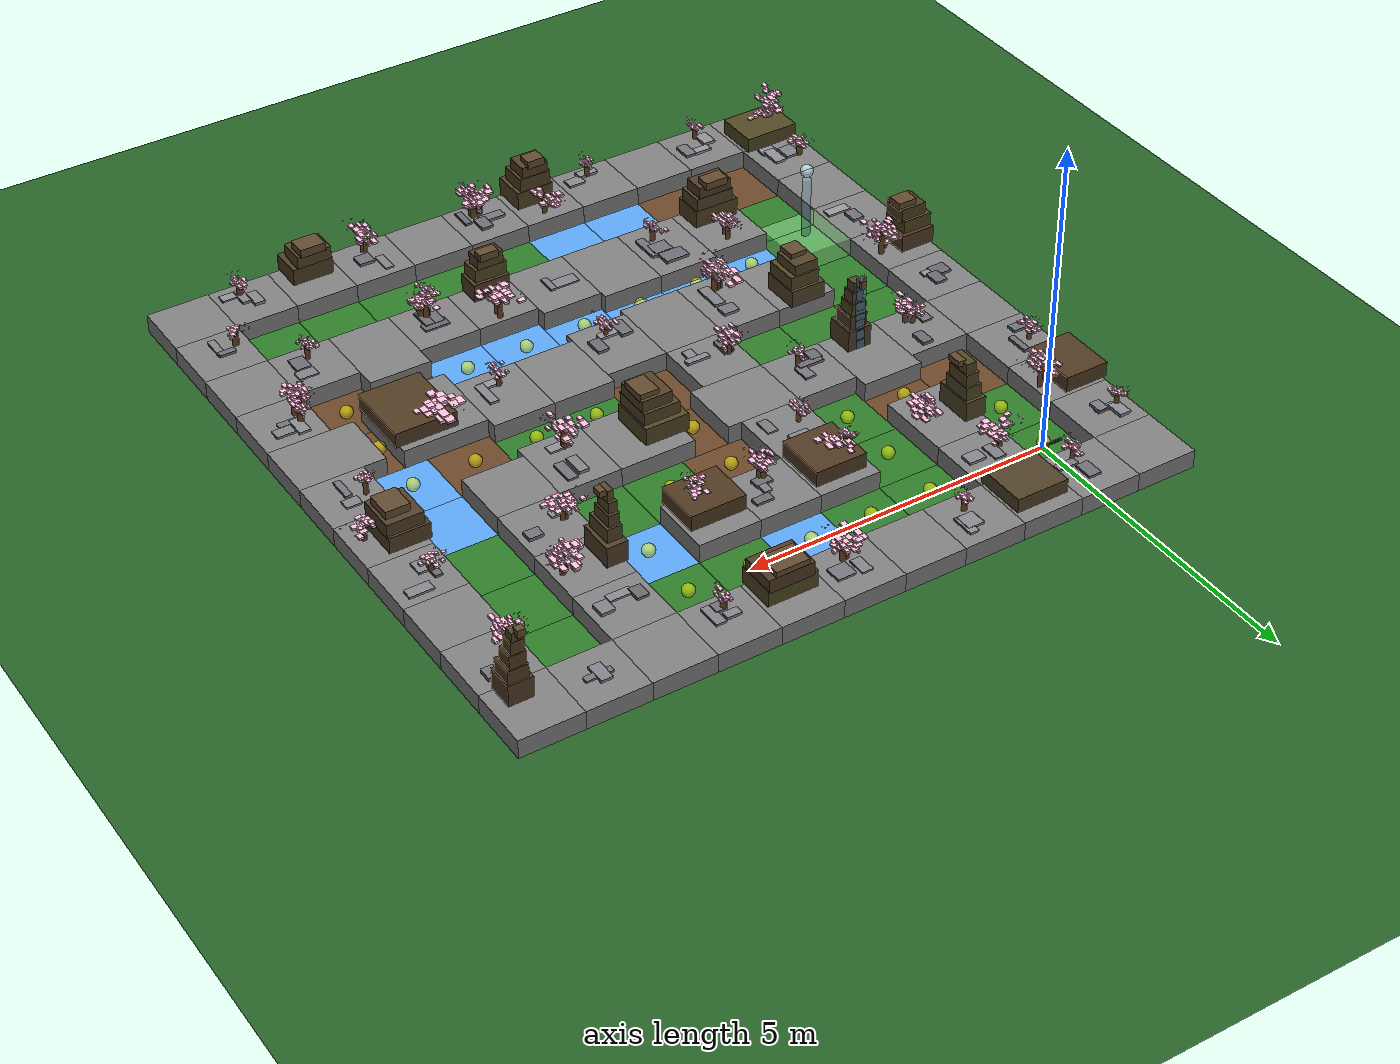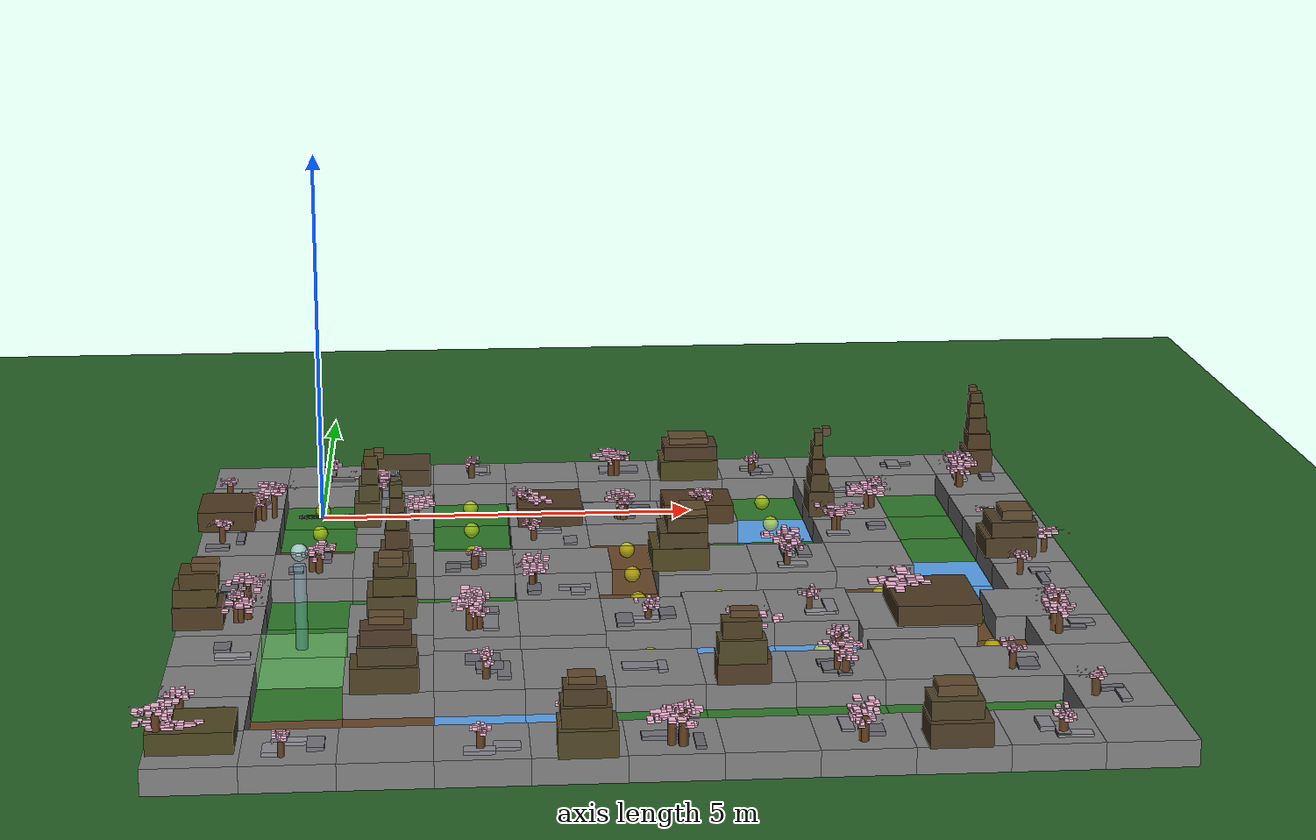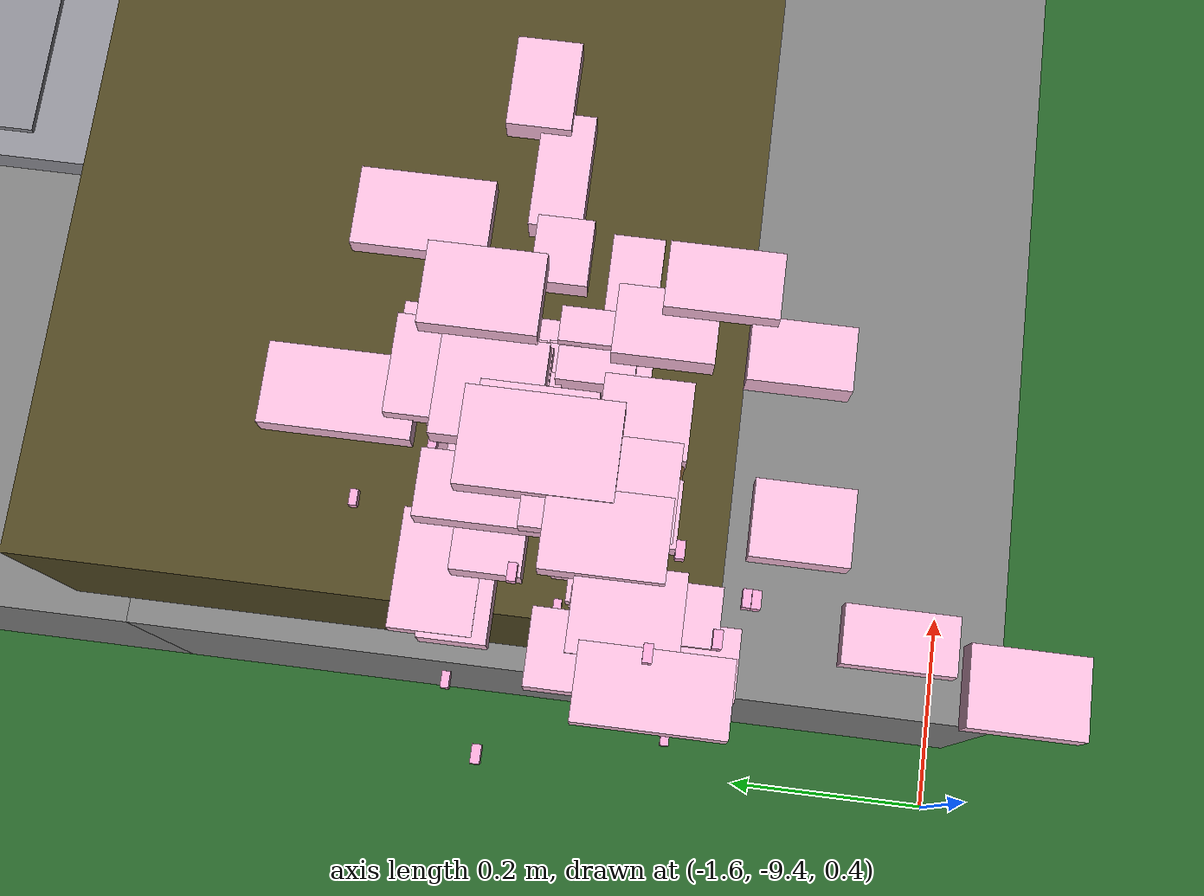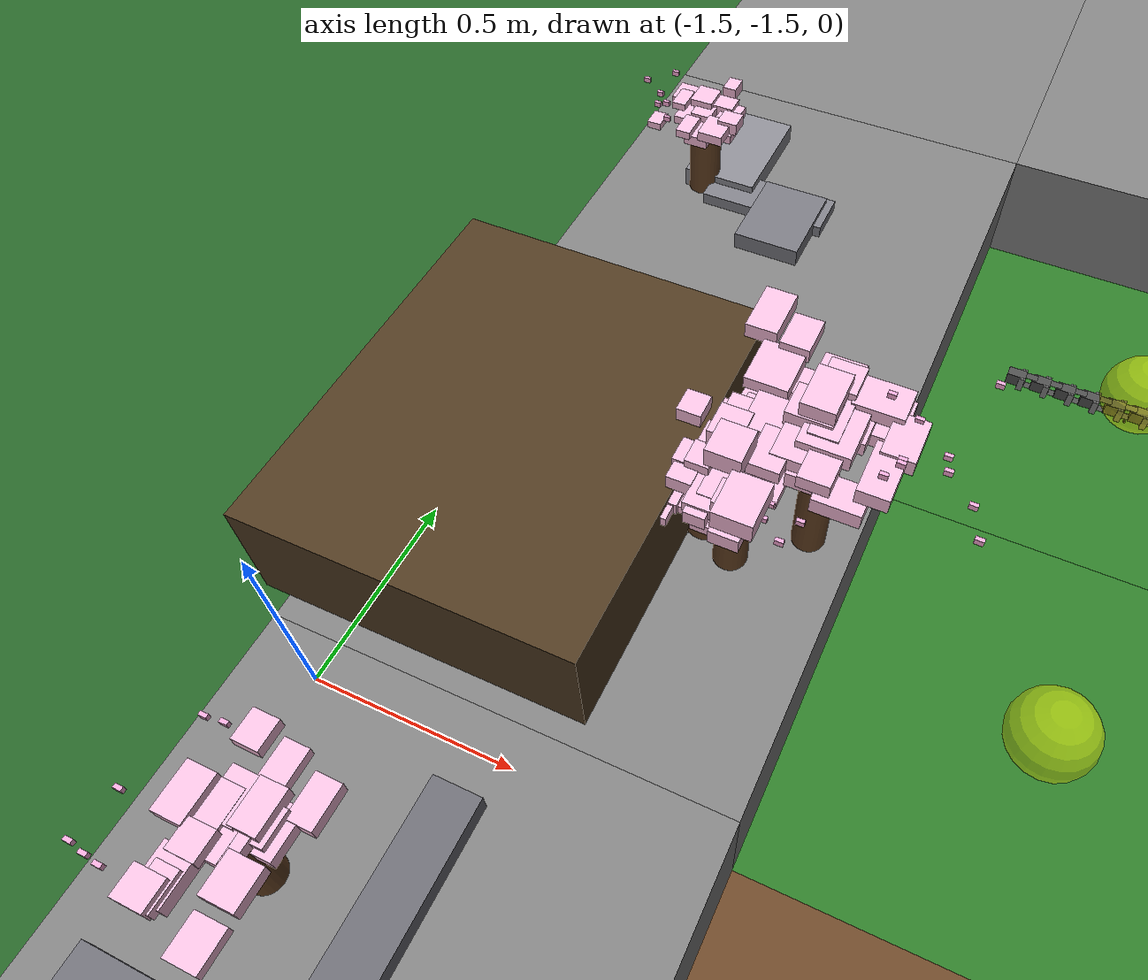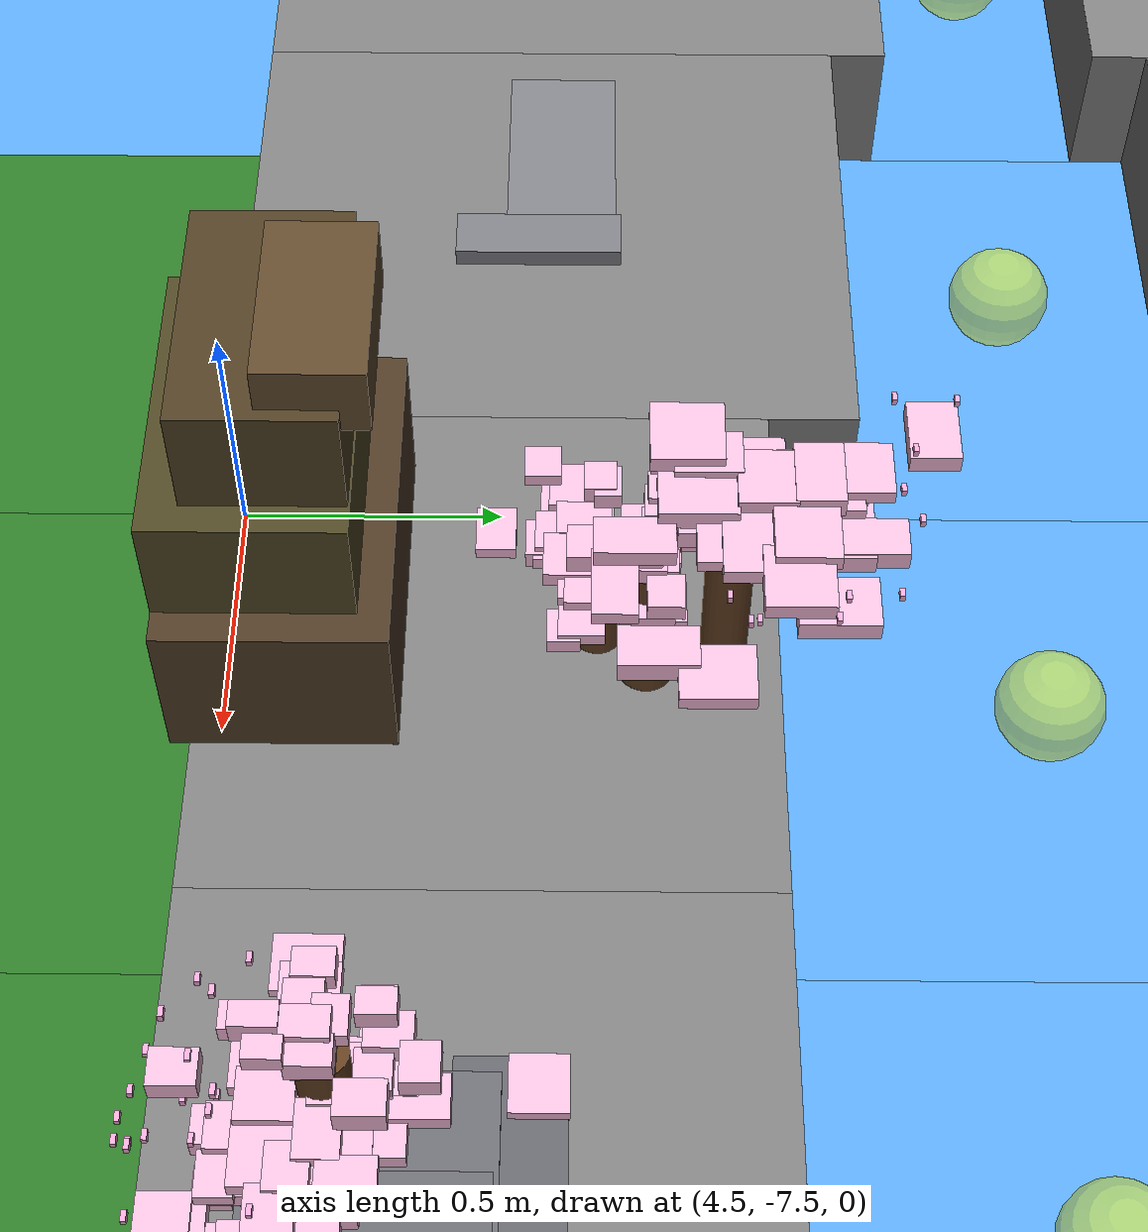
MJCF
<?xml version='1.0' encoding='utf-8'?>
<mujoco model="snake scene">
  <include file="snake.xml" />

  <statistic center="0.3 0 0.4" extent="0.8" />

  <visual>
    <headlight diffuse="0.6 0.6 0.6" ambient="0.1 0.1 0.1" specular="0 0 0" />
    <rgba haze="0.15 0.25 0.35 1" />
    <global azimuth="120" elevation="-20" />
  </visual>

  <asset>
    <texture type="skybox" builtin="gradient" rgb1="0.45 0.62 0.80" rgb2="0.10 0.14 0.28" width="512" height="3072" />
    <texture type="2d" name="groundplane" builtin="checker" mark="cross" rgb1="0.18 0.44 0.18" rgb2="0.12 0.34 0.13" markrgb="0.22 0.36 0.16" width="300" height="300" />
    <material name="groundplane" texture="groundplane" texuniform="true" texrepeat="8 8" reflectance="0.2" />
  </asset>

  <worldbody>
    <light pos="0 0 1.5" dir="0 0 -1" directional="true" />
    <geom name="floor" size="0 0 0.05" type="plane" material="groundplane" />
  <geom name="terrain_grass_1_1" type="box" size="0.5 0.5 0.004" pos="0.0 -0.0 -0.0038" rgba="0.18 0.48 0.16 1" friction="3.0 0.005 0.0001" priority="1" /><geom name="terrain_grass_2_1" type="box" size="0.5 0.5 0.004" pos="0.0 -1.0 -0.0038" rgba="0.18 0.48 0.16 1" friction="3.0 0.005 0.0001" priority="1" /><geom name="terrain_dirt_3_1" type="box" size="0.5 0.5 0.004" pos="0.0 -2.0 -0.0038" rgba="0.42 0.28 0.16 1" friction="7.0 0.4 0.02" priority="1" /><geom name="terrain_dirt_3_2" type="box" size="0.5 0.5 0.004" pos="1.0 -2.0 -0.0038" rgba="0.42 0.28 0.16 1" friction="7.0 0.4 0.02" priority="1" /><geom name="terrain_grass_3_3" type="box" size="0.5 0.5 0.004" pos="2.0 -2.0 -0.0038" rgba="0.18 0.48 0.16 1" friction="3.0 0.005 0.0001" priority="1" /><geom name="terrain_grass_2_3" type="box" size="0.5 0.5 0.004" pos="2.0 -1.0 -0.0038" rgba="0.18 0.48 0.16 1" friction="3.0 0.005 0.0001" priority="1" /><geom name="terrain_grass_1_3" type="box" size="0.5 0.5 0.004" pos="2.0 -0.0 -0.0038" rgba="0.18 0.48 0.16 1" friction="3.0 0.005 0.0001" priority="1" /><geom name="terrain_grass_1_4" type="box" size="0.5 0.5 0.004" pos="3.0 -0.0 -0.0038" rgba="0.18 0.48 0.16 1" friction="3.0 0.005 0.0001" priority="1" /><geom name="terrain_ice_1_5" type="box" size="0.5 0.5 0.004" pos="4.0 -0.0 -0.0038" rgba="0.35 0.65 0.95 1" friction="0.5 0.001 0.00002" priority="1" /><geom name="terrain_grass_1_6" type="box" size="0.5 0.5 0.004" pos="5.0 -0.0 -0.0038" rgba="0.18 0.48 0.16 1" friction="3.0 0.005 0.0001" priority="1" /><geom name="terrain_grass_1_7" type="box" size="0.5 0.5 0.004" pos="6.0 -0.0 -0.0038" rgba="0.18 0.48 0.16 1" friction="3.0 0.005 0.0001" priority="1" /><geom name="terrain_ice_2_7" type="box" size="0.5 0.5 0.004" pos="6.0 -1.0 -0.0038" rgba="0.35 0.65 0.95 1" friction="0.5 0.001 0.00002" priority="1" /><geom name="terrain_grass_3_7" type="box" size="0.5 0.5 0.004" pos="6.0 -2.0 -0.0038" rgba="0.18 0.48 0.16 1" friction="3.0 0.005 0.0001" priority="1" /><geom name="terrain_grass_3_6" type="box" size="0.5 0.5 0.004" pos="5.0 -2.0 -0.0038" rgba="0.18 0.48 0.16 1" friction="3.0 0.005 0.0001" priority="1" /><geom name="terrain_dirt_3_5" type="box" size="0.5 0.5 0.004" pos="4.0 -2.0 -0.0038" rgba="0.42 0.28 0.16 1" friction="7.0 0.4 0.02" priority="1" /><geom name="terrain_dirt_4_5" type="box" size="0.5 0.5 0.004" pos="4.0 -3.0 -0.0038" rgba="0.42 0.28 0.16 1" friction="7.0 0.4 0.02" priority="1" /><geom name="terrain_dirt_5_5" type="box" size="0.5 0.5 0.004" pos="4.0 -4.0 -0.0038" rgba="0.42 0.28 0.16 1" friction="7.0 0.4 0.02" priority="1" /><geom name="terrain_grass_5_6" type="box" size="0.5 0.5 0.004" pos="5.0 -4.0 -0.0038" rgba="0.18 0.48 0.16 1" friction="3.0 0.005 0.0001" priority="1" /><geom name="terrain_grass_5_7" type="box" size="0.5 0.5 0.004" pos="6.0 -4.0 -0.0038" rgba="0.18 0.48 0.16 1" friction="3.0 0.005 0.0001" priority="1" /><geom name="terrain_dirt_5_8" type="box" size="0.5 0.5 0.004" pos="7.0 -4.0 -0.0038" rgba="0.42 0.28 0.16 1" friction="7.0 0.4 0.02" priority="1" /><geom name="terrain_ice_5_9" type="box" size="0.5 0.5 0.004" pos="8.0 -4.0 -0.0038" rgba="0.35 0.65 0.95 1" friction="0.5 0.001 0.00002" priority="1" /><geom name="terrain_dirt_6_9" type="box" size="0.5 0.5 0.004" pos="8.0 -5.0 -0.0038" rgba="0.42 0.28 0.16 1" friction="7.0 0.4 0.02" priority="1" /><geom name="terrain_ice_4_9" type="box" size="0.5 0.5 0.004" pos="8.0 -3.0 -0.0038" rgba="0.35 0.65 0.95 1" friction="0.5 0.001 0.00002" priority="1" /><geom name="terrain_dirt_7_9" type="box" size="0.5 0.5 0.004" pos="8.0 -6.0 -0.0038" rgba="0.42 0.28 0.16 1" friction="7.0 0.4 0.02" priority="1" /><geom name="terrain_grass_3_9" type="box" size="0.5 0.5 0.004" pos="8.0 -2.0 -0.0038" rgba="0.18 0.48 0.16 1" friction="3.0 0.005 0.0001" priority="1" /><geom name="terrain_dirt_7_8" type="box" size="0.5 0.5 0.004" pos="7.0 -6.0 -0.0038" rgba="0.42 0.28 0.16 1" friction="7.0 0.4 0.02" priority="1" /><geom name="terrain_grass_2_9" type="box" size="0.5 0.5 0.004" pos="8.0 -1.0 -0.0038" rgba="0.18 0.48 0.16 1" friction="3.0 0.005 0.0001" priority="1" /><geom name="terrain_ice_7_7" type="box" size="0.5 0.5 0.004" pos="6.0 -6.0 -0.0038" rgba="0.35 0.65 0.95 1" friction="0.5 0.001 0.00002" priority="1" /><geom name="terrain_grass_1_9" type="box" size="0.5 0.5 0.004" pos="8.0 -0.0 -0.0038" rgba="0.18 0.48 0.16 1" friction="3.0 0.005 0.0001" priority="1" /><geom name="terrain_ice_7_6" type="box" size="0.5 0.5 0.004" pos="5.0 -6.0 -0.0038" rgba="0.35 0.65 0.95 1" friction="0.5 0.001 0.00002" priority="1" /><geom name="terrain_ice_7_5" type="box" size="0.5 0.5 0.004" pos="4.0 -6.0 -0.0038" rgba="0.35 0.65 0.95 1" friction="0.5 0.001 0.00002" priority="1" /><geom name="terrain_ice_7_4" type="box" size="0.5 0.5 0.004" pos="3.0 -6.0 -0.0038" rgba="0.35 0.65 0.95 1" friction="0.5 0.001 0.00002" priority="1" /><geom name="terrain_ice_7_3" type="box" size="0.5 0.5 0.004" pos="2.0 -6.0 -0.0038" rgba="0.35 0.65 0.95 1" friction="0.5 0.001 0.00002" priority="1" /><geom name="terrain_ice_7_2" type="box" size="0.5 0.5 0.004" pos="1.0 -6.0 -0.0038" rgba="0.35 0.65 0.95 1" friction="0.5 0.001 0.00002" priority="1" /><geom name="terrain_grass_7_1" type="box" size="0.5 0.5 0.004" pos="0.0 -6.0 -0.0038" rgba="0.18 0.48 0.16 1" friction="3.0 0.005 0.0001" priority="1" /><geom name="terrain_grass_8_1" type="box" size="0.5 0.5 0.004" pos="0.0 -7.0 -0.0038" rgba="0.18 0.48 0.16 1" friction="3.0 0.005 0.0001" priority="1" /><geom name="terrain_grass_6_1" type="box" size="0.5 0.5 0.004" pos="0.0 -5.0 -0.0038" rgba="0.18 0.48 0.16 1" friction="3.0 0.005 0.0001" priority="1" /><geom name="terrain_dirt_9_1" type="box" size="0.5 0.5 0.004" pos="0.0 -8.0 -0.0038" rgba="0.42 0.28 0.16 1" friction="7.0 0.4 0.02" priority="1" /><geom name="terrain_grass_5_1" type="box" size="0.5 0.5 0.004" pos="0.0 -4.0 -0.0038" rgba="0.18 0.48 0.16 1" friction="3.0 0.005 0.0001" priority="1" /><geom name="terrain_dirt_9_2" type="box" size="0.5 0.5 0.004" pos="1.0 -8.0 -0.0038" rgba="0.42 0.28 0.16 1" friction="7.0 0.4 0.02" priority="1" /><geom name="terrain_grass_5_2" type="box" size="0.5 0.5 0.004" pos="1.0 -4.0 -0.0038" rgba="0.18 0.48 0.16 1" friction="3.0 0.005 0.0001" priority="1" /><geom name="terrain_ice_9_3" type="box" size="0.5 0.5 0.004" pos="2.0 -8.0 -0.0038" rgba="0.35 0.65 0.95 1" friction="0.5 0.001 0.00002" priority="1" /><geom name="terrain_grass_5_3" type="box" size="0.5 0.5 0.004" pos="2.0 -4.0 -0.0038" rgba="0.18 0.48 0.16 1" friction="3.0 0.005 0.0001" priority="1" /><geom name="terrain_ice_9_4" type="box" size="0.5 0.5 0.004" pos="3.0 -8.0 -0.0038" rgba="0.35 0.65 0.95 1" friction="0.5 0.001 0.00002" priority="1" /><geom name="terrain_grass_9_5" type="box" size="0.5 0.5 0.004" pos="4.0 -8.0 -0.0038" rgba="0.18 0.48 0.16 1" friction="3.0 0.005 0.0001" priority="1" /><geom name="terrain_grass_9_6" type="box" size="0.5 0.5 0.004" pos="5.0 -8.0 -0.0038" rgba="0.18 0.48 0.16 1" friction="3.0 0.005 0.0001" priority="1" /><geom name="terrain_grass_9_7" type="box" size="0.5 0.5 0.004" pos="6.0 -8.0 -0.0038" rgba="0.18 0.48 0.16 1" friction="3.0 0.005 0.0001" priority="1" /><geom name="terrain_grass_9_8" type="box" size="0.5 0.5 0.004" pos="7.0 -8.0 -0.0038" rgba="0.18 0.48 0.16 1" friction="3.0 0.005 0.0001" priority="1" /><geom name="terrain_grass_9_9" type="box" size="0.5 0.5 0.004" pos="8.0 -8.0 -0.0038" rgba="0.18 0.48 0.16 1" friction="3.0 0.005 0.0001" priority="1" /><body name="box_0_0" pos="-1.0 1.0 0.15"><geom name="geom_0_0" type="box" size="0.5 0.5 0.15" rgba="0.5 0.5 0.5 1" /></body><body name="box_0_1" pos="0.0 1.0 0.15"><geom name="geom_0_1" type="box" size="0.5 0.5 0.15" rgba="0.5 0.5 0.5 1" /><geom contype="0" conaffinity="0" name="stone_0_1_0" type="box" size="0.10411395426612957 0.15562523528307423 0.019336965885795587" pos="0.04489222094265174 0.047224172186832794 0.16740326929721602" rgba="0.430 0.430 0.460 1" /><geom contype="0" conaffinity="0" name="stone_0_1_1" type="box" size="0.17281722342830147 0.0636377940873409 0.013790649323474598" pos="0.24091610303584454 -0.20719152601108815 0.1640664623099441" rgba="0.474 0.474 0.504 1" /><body name="cherry_0_1_0" pos="0.06481499044017099 -0.29329416667630237 0.153"><geom contype="0" conaffinity="0" name="cherry_trunk_0_1_0" type="cylinder" size="0.03590206372005547 0.10857746775370124" pos="0 0 0.10857746775370124" rgba="0.39 0.25 0.13 1" /><body name="cherry_canopy_0_1_0" pos="0 0 0.21715493550740247"><joint name="cherry_sway_0_1_0" type="hinge" axis="0 1 0" range="-0.45 0.45" damping="0.02" /><geom contype="0" conaffinity="0" name="cherry_blossom_0_1_0_0" type="box" size="0.021094532602422427 0.025385820077744196 0.01523796777344266" pos="0.032967594939262705 0.008268097148481058 0.008880043734774646" rgba="0.98 0.74 0.86 0.95" /><geom contype="0" conaffinity="0" name="cherry_blossom_0_1_0_1" type="box" size="0.027709139727597684 0.037658746500203934 0.01761405140546387" pos="0.044656762073208005 0.09204610054432984 0.027975281321556782" rgba="0.98 0.74 0.86 0.95" /><geom contype="0" conaffinity="0" name="cherry_blossom_0_1_0_2" type="box" size="0.021065975484004237 0.04147810504711143 0.018837927995390778" pos="-0.00034384815706998094 -0.11398944111820204 0.03297931274902686" rgba="0.98 0.74 0.86 0.95" /><geom contype="0" conaffinity="0" name="cherry_blossom_0_1_0_3" type="box" size="0.02674254667225609 0.03027251163862516 0.012934381332601566" pos="0.012376298196263767 0.1985548459097776 -0.008683144228324299" rgba="0.98 0.74 0.86 0.95" /><geom contype="0" conaffinity="0" name="cherry_blossom_0_1_0_4" type="box" size="0.02349700841076903 0.037551774761219195 0.01242101915316241" pos="0.09892593602270573 0.20616529126148073 0.02229542761877852" rgba="0.98 0.74 0.86 0.95" /><geom contype="0" conaffinity="0" name="cherry_blossom_0_1_0_5" type="box" size="0.019293057998002294 0.02592757190454715 0.013113222965006839" pos="0.00127101606044589 0.0848651752948037 0.026980380377331997" rgba="0.98 0.74 0.86 0.95" /><geom contype="0" conaffinity="0" name="cherry_blossom_0_1_0_6" type="box" size="0.018249836160720536 0.03325331317924076 0.01626096530593007" pos="0.02062414533222364 -0.12524277073449963 0.025599788671322787" rgba="0.98 0.74 0.86 0.95" /><geom contype="0" conaffinity="0" name="cherry_blossom_0_1_0_7" type="box" size="0.018509003129193645 0.023890546537700574 0.014134053617937438" pos="0.08251608948464875 0.034189283532044035 0.035263683154578195" rgba="0.98 0.74 0.86 0.95" /><geom contype="0" conaffinity="0" name="cherry_blossom_0_1_0_8" type="box" size="0.026488217319285617 0.033960079852885676 0.018576667438395457" pos="0.09684377627047834 -0.041585532465790775 0.011257731924913137" rgba="0.98 0.74 0.86 0.95" /><geom contype="0" conaffinity="0" name="cherry_blossom_0_1_0_9" type="box" size="0.02228009203618639 0.03650660130829691 0.015217444358017342" pos="0.04599944251413883 0.017986771470831067 0.04007914787363674" rgba="0.98 0.74 0.86 0.95" /><geom contype="0" conaffinity="0" name="cherry_blossom_0_1_0_10" type="box" size="0.028650017357206452 0.03525816367014462 0.01738989001957697" pos="0.1517830139826365 -0.015644429292880478 0.030689827064000627" rgba="0.98 0.74 0.86 0.95" /><geom contype="0" conaffinity="0" name="cherry_blossom_0_1_0_11" type="box" size="0.017339544427499538 0.031485184822425585 0.015350935931089854" pos="-0.06895917757633742 0.014430576113945692 0.03847207054891002" rgba="0.98 0.74 0.86 0.95" /><geom contype="0" conaffinity="0" name="cherry_blossom_0_1_0_12" type="box" size="0.02365074985362382 0.0302150618206588 0.0203328910136665" pos="-0.09102563960103349 0.009032400375568055 0.005409985819207995" rgba="0.98 0.74 0.86 0.95" /><geom contype="0" conaffinity="0" name="cherry_blossom_0_1_0_13" type="box" size="0.024924485229549844 0.04191362310221855 0.0172119497124714" pos="-0.028160601916334363 0.04389750221611175 0.01310741824666554" rgba="0.98 0.74 0.86 0.95" /><geom contype="0" conaffinity="0" name="cherry_blossom_0_1_0_14" type="box" size="0.02852266375555145 0.04097180083460443 0.015314210723290748" pos="-0.010364492640260417 0.011049653599363189 -0.007781788852350692" rgba="0.98 0.74 0.86 0.95" /><geom contype="0" conaffinity="0" name="cherry_blossom_0_1_0_15" type="box" size="0.021256252159513784 0.042313722071783515 0.015281647863146215" pos="0.06523011867956291 0.03184645358780507 0.100924312492243" rgba="0.98 0.74 0.86 0.95" /><geom contype="0" conaffinity="0" name="cherry_blossom_0_1_0_16" type="box" size="0.029129968721050385 0.03917198426125845 0.019688860149843633" pos="0.007118524954869035 0.00475319301862488 0.03866759820321569" rgba="0.98 0.74 0.86 0.95" /><geom contype="0" conaffinity="0" name="cherry_blossom_0_1_0_17" type="box" size="0.021373041443519834 0.03305214973257869 0.018214507899371315" pos="0.03627555051052277 0.1674130478833648 0.002966683340536147" rgba="0.98 0.74 0.86 0.95" /></body><body name="cherry_petal_0_1_0_0" pos="0.022591930737868273 -0.195956218095103 0.27487288679799515"><joint name="cherry_petal_drop_0_1_0_0" type="slide" axis="0 0 -1" range="0 1.3690502654171717" damping="0" /><geom contype="0" conaffinity="0" name="cherry_petal_geom_0_1_0_0" type="box" size="0.008 0.004 0.006" rgba="0.98 0.66 0.84 0.90" /></body><body name="cherry_petal_0_1_0_1" pos="0.008988179784927611 -0.15751143030662382 0.28041963515091606"><joint name="cherry_petal_drop_0_1_0_1" type="slide" axis="0 0 -1" range="0 1.1546726526740547" damping="0" /><geom contype="0" conaffinity="0" name="cherry_petal_geom_0_1_0_1" type="box" size="0.008 0.004 0.006" rgba="0.98 0.66 0.84 0.90" /></body><body name="cherry_petal_0_1_0_2" pos="-0.01622167763285466 -0.2340114441766671 0.25568975639357266"><joint name="cherry_petal_drop_0_1_0_2" type="slide" axis="0 0 -1" range="0 1.2424160418756294" damping="0" /><geom contype="0" conaffinity="0" name="cherry_petal_geom_0_1_0_2" type="box" size="0.008 0.004 0.006" rgba="0.98 0.66 0.84 0.90" /></body><body name="cherry_petal_0_1_0_3" pos="-0.037181302176743106 -0.17930133345966034 0.30289712743916664"><joint name="cherry_petal_drop_0_1_0_3" type="slide" axis="0 0 -1" range="0 1.7963460044563357" damping="0" /><geom contype="0" conaffinity="0" name="cherry_petal_geom_0_1_0_3" type="box" size="0.008 0.004 0.006" rgba="0.98 0.66 0.84 0.90" /></body><body name="cherry_petal_0_1_0_4" pos="0.030564783173163364 -0.1497617068666813 0.2804184639567384"><joint name="cherry_petal_drop_0_1_0_4" type="slide" axis="0 0 -1" range="0 1.7000573194765372" damping="0" /><geom contype="0" conaffinity="0" name="cherry_petal_geom_0_1_0_4" type="box" size="0.008 0.004 0.006" rgba="0.98 0.66 0.84 0.90" /></body><body name="cherry_petal_0_1_0_5" pos="-0.10202503908476429 -0.17931016359210167 0.2962730633369973"><joint name="cherry_petal_drop_0_1_0_5" type="slide" axis="0 0 -1" range="0 1.4818066499804114" damping="0" /><geom contype="0" conaffinity="0" name="cherry_petal_geom_0_1_0_5" type="box" size="0.008 0.004 0.006" rgba="0.98 0.66 0.84 0.90" /></body><body name="cherry_petal_0_1_0_6" pos="-0.0760642950815948 -0.19677916674055845 0.2897456060978787"><joint name="cherry_petal_drop_0_1_0_6" type="slide" axis="0 0 -1" range="0 1.8137170820345832" damping="0" /><geom contype="0" conaffinity="0" name="cherry_petal_geom_0_1_0_6" type="box" size="0.008 0.004 0.006" rgba="0.98 0.66 0.84 0.90" /></body></body></body><body name="box_0_2" pos="1.0 1.0 0.15"><geom name="geom_0_2" type="box" size="0.5 0.5 0.15" rgba="0.5 0.5 0.5 1" /><geom contype="0" conaffinity="0" name="mountain_0_2_0" type="box" size="0.42919747268578295 0.41193508778978216 0.11349109773416703" pos="0.025848779816870598 -0.1439731335447364 0.263491097734167" rgba="0.31 0.253 0.153 1" /></body><body name="box_0_3" pos="2.0 1.0 0.15"><geom name="geom_0_3" type="box" size="0.5 0.5 0.15" rgba="0.5 0.5 0.5 1" /><geom contype="0" conaffinity="0" name="stone_0_3_0" type="box" size="0.13710705951448382 0.0926547039487389 0.016797951904940975" pos="0.10608330568242973 0.10529202607047641 0.16511815671444688" rgba="0.431 0.431 0.461 1" /><geom contype="0" conaffinity="0" name="stone_0_3_1" type="box" size="0.07603491603509775 0.19392325098976343 0.016221099782233486" pos="0.20992923844588657 0.11125430788711324 0.16654552177787815" rgba="0.545 0.545 0.575 1" /><geom contype="0" conaffinity="0" name="stone_0_3_2" type="box" size="0.1309771460834257 0.14049576894717847 0.018090547927665516" pos="0.11375376837094713 0.06843539022693858 0.17062322463753868" rgba="0.530 0.530 0.560 1" /><body name="cherry_0_3_0" pos="0.02935967526460767 -0.1878034039051117 0.153"><geom contype="0" conaffinity="0" name="cherry_trunk_0_3_0" type="cylinder" size="0.045791495986704414 0.10629512461232342" pos="0 0 0.10629512461232342" rgba="0.39 0.25 0.13 1" /><body name="cherry_canopy_0_3_0" pos="0 0 0.21259024922464684"><joint name="cherry_sway_0_3_0" type="hinge" axis="0 1 0" range="-0.45 0.45" damping="0.02" /><geom contype="0" conaffinity="0" name="cherry_blossom_0_3_0_0" type="box" size="0.021754163693347765 0.0290446140031391 0.013323212699475548" pos="0.08243236095656677 0.12976215590397877 0.028246932124193352" rgba="0.98 0.74 0.86 0.95" /><geom contype="0" conaffinity="0" name="cherry_blossom_0_3_0_1" type="box" size="0.01573304913631345 0.034324517551063506 0.01175024453034465" pos="-0.06554459298494367 -0.08807951642099007 -0.02164036351804569" rgba="0.98 0.74 0.86 0.95" /><geom contype="0" conaffinity="0" name="cherry_blossom_0_3_0_2" type="box" size="0.02636520622559865 0.02507942837059997 0.016944748517791028" pos="-0.05079400501367357 -0.06790639721375556 -0.00257905290187185" rgba="0.98 0.74 0.86 0.95" /><geom contype="0" conaffinity="0" name="cherry_blossom_0_3_0_3" type="box" size="0.017376610469980278 0.02419208582376646 0.011273285348125838" pos="-0.04832359401468668 0.02876196245616546 0.009517092863965038" rgba="0.98 0.74 0.86 0.95" /><geom contype="0" conaffinity="0" name="cherry_blossom_0_3_0_4" type="box" size="0.01952691805793974 0.02144084945649666 0.015537104900451263" pos="-0.025473984665852233 -0.031888581223479096 0.029736498683109402" rgba="0.98 0.74 0.86 0.95" /><geom contype="0" conaffinity="0" name="cherry_blossom_0_3_0_5" type="box" size="0.026087507165236574 0.021670793390519288 0.011430549630084046" pos="0.04072862017078437 -0.006180764672373507 0.05409932898431351" rgba="0.98 0.74 0.86 0.95" /><geom contype="0" conaffinity="0" name="cherry_blossom_0_3_0_6" type="box" size="0.020701078689540225 0.03586204764932601 0.010553249920300965" pos="-0.02088147633991736 0.10865295587050047 0.035213729101043915" rgba="0.98 0.74 0.86 0.95" /><geom contype="0" conaffinity="0" name="cherry_blossom_0_3_0_7" type="box" size="0.0199902269175352 0.03404397292135364 0.013594154441201297" pos="-0.050004790356143344 0.08432332736045878 0.024312251209540007" rgba="0.98 0.74 0.86 0.95" /><geom contype="0" conaffinity="0" name="cherry_blossom_0_3_0_8" type="box" size="0.024529182045503483 0.025372125463028 0.010260040834541552" pos="0.0865718642241573 -0.039360901705669867 0.012146514506535365" rgba="0.98 0.74 0.86 0.95" /><geom contype="0" conaffinity="0" name="cherry_blossom_0_3_0_9" type="box" size="0.018273757533193644 0.03356602273253698 0.010239597358866545" pos="0.021652700985509237 0.027510380989461715 0.04096842793353798" rgba="0.98 0.74 0.86 0.95" /><geom contype="0" conaffinity="0" name="cherry_blossom_0_3_0_10" type="box" size="0.02397659630450946 0.02930755126315349 0.01398897721809257" pos="0.03485699396668062 -0.05158255256635145 0.02234862284965307" rgba="0.98 0.74 0.86 0.95" /><geom contype="0" conaffinity="0" name="cherry_blossom_0_3_0_11" type="box" size="0.02744813692272283 0.02378199464766535 0.01553961538843738" pos="0.02256720728293088 -0.017909319820282408 0.009126540442022902" rgba="0.98 0.74 0.86 0.95" /><geom contype="0" conaffinity="0" name="cherry_blossom_0_3_0_12" type="box" size="0.02207204951569522 0.020647025300984646 0.012258363146781755" pos="0.04137926099359399 0.012735022539804998 0.012583328351788162" rgba="0.98 0.74 0.86 0.95" /><geom contype="0" conaffinity="0" name="cherry_blossom_0_3_0_13" type="box" size="0.026068910148217602 0.03536172674216643 0.01719200626557632" pos="0.04438055039952639 0.05024429766001958 0.035816148033520775" rgba="0.98 0.74 0.86 0.95" /><geom contype="0" conaffinity="0" name="cherry_blossom_0_3_0_14" type="box" size="0.02437454763650517 0.03349768368185002 0.011016514508844099" pos="-0.01663240579577873 0.07620981672139668 0.014335280180765854" rgba="0.98 0.74 0.86 0.95" /><geom contype="0" conaffinity="0" name="cherry_blossom_0_3_0_15" type="box" size="0.021758374796901295 0.0315070463670012 0.014355939813108643" pos="0.010055083350301064 -0.011146108604804111 0.029503510146773968" rgba="0.98 0.74 0.86 0.95" /><geom contype="0" conaffinity="0" name="cherry_blossom_0_3_0_16" type="box" size="0.025397906219369302 0.02413315405318218 0.015937519952252257" pos="-0.06056455146533845 -0.025497571713569842 0.01133333228325747" rgba="0.98 0.74 0.86 0.95" /><geom contype="0" conaffinity="0" name="cherry_blossom_0_3_0_17" type="box" size="0.024037575047433958 0.022197416408788476 0.015760016514430937" pos="-0.02488390272737749 -0.0015666698644272534 -0.005781637103348322" rgba="0.98 0.74 0.86 0.95" /></body><body name="cherry_petal_0_3_0_0" pos="-0.08402662739871129 -0.1354520257211134 0.27539795360879527"><joint name="cherry_petal_drop_0_3_0_0" type="slide" axis="0 0 -1" range="0 1.5061057161997495" damping="0" /><geom contype="0" conaffinity="0" name="cherry_petal_geom_0_3_0_0" type="box" size="0.008 0.004 0.006" rgba="0.98 0.66 0.84 0.90" /></body><body name="cherry_petal_0_3_0_1" pos="0.09508867149099609 -0.1075226520039996 0.24988156884291787"><joint name="cherry_petal_drop_0_3_0_1" type="slide" axis="0 0 -1" range="0 1.7793766514060656" damping="0" /><geom contype="0" conaffinity="0" name="cherry_petal_geom_0_3_0_1" type="box" size="0.008 0.004 0.006" rgba="0.98 0.66 0.84 0.90" /></body><body name="cherry_petal_0_3_0_2" pos="0.044374981995764444 -0.1757119257472595 0.24686447079354834"><joint name="cherry_petal_drop_0_3_0_2" type="slide" axis="0 0 -1" range="0 1.7243848395188999" damping="0" /><geom contype="0" conaffinity="0" name="cherry_petal_geom_0_3_0_2" type="box" size="0.008 0.004 0.006" rgba="0.98 0.66 0.84 0.90" /></body><body name="cherry_petal_0_3_0_3" pos="0.05080437471151969 -0.06805685006148995 0.25045061200988744"><joint name="cherry_petal_drop_0_3_0_3" type="slide" axis="0 0 -1" range="0 1.5708230451192713" damping="0" /><geom contype="0" conaffinity="0" name="cherry_petal_geom_0_3_0_3" type="box" size="0.008 0.004 0.006" rgba="0.98 0.66 0.84 0.90" /></body><body name="cherry_petal_0_3_0_4" pos="0.04828040318160978 -0.08757584298780126 0.26700041885304343"><joint name="cherry_petal_drop_0_3_0_4" type="slide" axis="0 0 -1" range="0 1.565496502847202" damping="0" /><geom contype="0" conaffinity="0" name="cherry_petal_geom_0_3_0_4" type="box" size="0.008 0.004 0.006" rgba="0.98 0.66 0.84 0.90" /></body><body name="cherry_petal_0_3_0_5" pos="-0.09266020348202458 -0.09330102016042188 0.25730477621896847"><joint name="cherry_petal_drop_0_3_0_5" type="slide" axis="0 0 -1" range="0 1.1451784749481442" damping="0" /><geom contype="0" conaffinity="0" name="cherry_petal_geom_0_3_0_5" type="box" size="0.008 0.004 0.006" rgba="0.98 0.66 0.84 0.90" /></body><body name="cherry_petal_0_3_0_6" pos="-0.039746437038035265 -0.14825051052366262 0.2716400284408351"><joint name="cherry_petal_drop_0_3_0_6" type="slide" axis="0 0 -1" range="0 1.8088479624920182" damping="0" /><geom contype="0" conaffinity="0" name="cherry_petal_geom_0_3_0_6" type="box" size="0.008 0.004 0.006" rgba="0.98 0.66 0.84 0.90" /></body></body></body><body name="box_0_4" pos="3.0 1.0 0.15"><geom name="geom_0_4" type="box" size="0.5 0.5 0.15" rgba="0.5 0.5 0.5 1" /></body><body name="box_0_5" pos="4.0 1.0 0.15"><geom name="geom_0_5" type="box" size="0.5 0.5 0.15" rgba="0.5 0.5 0.5 1" /><geom contype="0" conaffinity="0" name="stone_0_5_0" type="box" size="0.08756739548125184 0.15011374648583925 0.013344784315782211" pos="-0.09678178886532984 0.03248746373930034 0.16201030588420398" rgba="0.509 0.509 0.539 1" /><geom contype="0" conaffinity="0" name="stone_0_5_1" type="box" size="0.1490303072700725 0.13812699884909185 0.016433773486215227" pos="0.20774037466824333 0.0039244424389808874 0.16676244895593953" rgba="0.461 0.461 0.491 1" /><body name="cherry_0_5_0" pos="0.044126102380087996 -0.21076641339111354 0.153"><geom contype="0" conaffinity="0" name="cherry_trunk_0_5_0" type="cylinder" size="0.044354443385586965 0.11236343254309901" pos="0 0 0.11236343254309901" rgba="0.39 0.25 0.13 1" /><body name="cherry_canopy_0_5_0" pos="0 0 0.22472686508619802"><joint name="cherry_sway_0_5_0" type="hinge" axis="0 1 0" range="-0.45 0.45" damping="0.02" /><geom contype="0" conaffinity="0" name="cherry_blossom_0_5_0_0" type="box" size="0.021707409451851907 0.026755327604589152 0.012049810524874438" pos="0.02805563376472105 0.010222832940332225 0.010415299671093349" rgba="0.98 0.74 0.86 0.95" /><geom contype="0" conaffinity="0" name="cherry_blossom_0_5_0_1" type="box" size="0.021495728398487526 0.04062317748718138 0.01875633549641353" pos="0.04192205684554617 0.044979332057235324 0.019269286136651485" rgba="0.98 0.74 0.86 0.95" /><geom contype="0" conaffinity="0" name="cherry_blossom_0_5_0_2" type="box" size="0.02351706050560549 0.042075902251123565 0.013705573386102999" pos="-0.10264047537196307 -0.16089420537240157 0.02613487464398795" rgba="0.98 0.74 0.86 0.95" /><geom contype="0" conaffinity="0" name="cherry_blossom_0_5_0_3" type="box" size="0.030282358933427445 0.02563524392318112 0.020063523225100452" pos="-0.13563617751665216 0.02024449307776902 0.03224214847682751" rgba="0.98 0.74 0.86 0.95" /><geom contype="0" conaffinity="0" name="cherry_blossom_0_5_0_4" type="box" size="0.0285105833135082 0.03903632555537049 0.015014318518559298" pos="-0.017375010248996303 0.032459343397722606 0.0005531423456963087" rgba="0.98 0.74 0.86 0.95" /><geom contype="0" conaffinity="0" name="cherry_blossom_0_5_0_5" type="box" size="0.030926497245742524 0.039125233024846 0.012982381217729037" pos="0.026391656822592997 0.1280476005109416 -0.0030665896099531745" rgba="0.98 0.74 0.86 0.95" /><geom contype="0" conaffinity="0" name="cherry_blossom_0_5_0_6" type="box" size="0.021304335057050042 0.034169186116146506 0.01559250277911289" pos="0.0009802274816666538 0.029513289914814448 0.04067200050073197" rgba="0.98 0.74 0.86 0.95" /><geom contype="0" conaffinity="0" name="cherry_blossom_0_5_0_7" type="box" size="0.026813959140740307 0.026308271843491507 0.01561846714677079" pos="-0.03286621446829325 0.02204584398676495 0.04113017884072666" rgba="0.98 0.74 0.86 0.95" /><geom contype="0" conaffinity="0" name="cherry_blossom_0_5_0_8" type="box" size="0.02579117300307689 0.03696477402731093 0.020166804510931783" pos="0.1539331173831546 0.023941630321251513 0.002099165481144678" rgba="0.98 0.74 0.86 0.95" /><geom contype="0" conaffinity="0" name="cherry_blossom_0_5_0_9" type="box" size="0.021441036424689565 0.04143987357099882 0.016865226269592484" pos="-0.028631492419365728 -0.02398888174884246 0.03416811963163834" rgba="0.98 0.74 0.86 0.95" /><geom contype="0" conaffinity="0" name="cherry_blossom_0_5_0_10" type="box" size="0.026921705596983304 0.04092013342455751 0.01936859799433853" pos="0.005268655109353123 0.04251176721661846 -0.017794045110408763" rgba="0.98 0.74 0.86 0.95" /><geom contype="0" conaffinity="0" name="cherry_blossom_0_5_0_11" type="box" size="0.026793414660084416 0.03257857651030417 0.020158645186154157" pos="0.022016404977811946 -0.030389697710816434 0.04534877755136819" rgba="0.98 0.74 0.86 0.95" /><geom contype="0" conaffinity="0" name="cherry_blossom_0_5_0_12" type="box" size="0.01942814116625255 0.0268895188520718 0.013708759703615247" pos="0.033773646751215324 0.04562326950480864 0.02293672093893103" rgba="0.98 0.74 0.86 0.95" /><geom contype="0" conaffinity="0" name="cherry_blossom_0_5_0_13" type="box" size="0.020031350637581366 0.03229047444789606 0.012070239268510616" pos="-0.02435172450762598 0.09183972229135251 0.02516867626131628" rgba="0.98 0.74 0.86 0.95" /><geom contype="0" conaffinity="0" name="cherry_blossom_0_5_0_14" type="box" size="0.02998575061491397 0.03129209899826674 0.019086775534860295" pos="0.027861753686433212 0.1324752595766277 0.026976179556013318" rgba="0.98 0.74 0.86 0.95" /><geom contype="0" conaffinity="0" name="cherry_blossom_0_5_0_15" type="box" size="0.02140271983308486 0.031560317711162314 0.015266504100768874" pos="-0.08948259220700097 -0.2021943329280395 0.0055495186815438455" rgba="0.98 0.74 0.86 0.95" /><geom contype="0" conaffinity="0" name="cherry_blossom_0_5_0_16" type="box" size="0.021078140787716856 0.03887933426156809 0.016740019457498027" pos="-0.09078619799113517 0.2134234825750912 0.03332844204131003" rgba="0.98 0.74 0.86 0.95" /><geom contype="0" conaffinity="0" name="cherry_blossom_0_5_0_17" type="box" size="0.03011449037544668 0.0363219037102759 0.016059541830596085" pos="0.07465818902117105 0.01648308170610922 0.01498088288078003" rgba="0.98 0.74 0.86 0.95" /></body><body name="cherry_petal_0_5_0_0" pos="0.0908209146283412 -0.11600644345368588 0.260217796316887"><joint name="cherry_petal_drop_0_5_0_0" type="slide" axis="0 0 -1" range="0 1.1749627583902085" damping="0" /><geom contype="0" conaffinity="0" name="cherry_petal_geom_0_5_0_0" type="box" size="0.008 0.004 0.006" rgba="0.98 0.66 0.84 0.90" /></body><body name="cherry_petal_0_5_0_1" pos="0.102640986342934 -0.20855944131756318 0.27691591984580055"><joint name="cherry_petal_drop_0_5_0_1" type="slide" axis="0 0 -1" range="0 1.1953592323189424" damping="0" /><geom contype="0" conaffinity="0" name="cherry_petal_geom_0_5_0_1" type="box" size="0.008 0.004 0.006" rgba="0.98 0.66 0.84 0.90" /></body><body name="cherry_petal_0_5_0_2" pos="0.031293977049852144 -0.08733592816004936 0.2763311723607766"><joint name="cherry_petal_drop_0_5_0_2" type="slide" axis="0 0 -1" range="0 1.3460938437871743" damping="0" /><geom contype="0" conaffinity="0" name="cherry_petal_geom_0_5_0_2" type="box" size="0.008 0.004 0.006" rgba="0.98 0.66 0.84 0.90" /></body><body name="cherry_petal_0_5_0_3" pos="-0.0920968017961265 -0.1413786375024124 0.27919224360351436"><joint name="cherry_petal_drop_0_5_0_3" type="slide" axis="0 0 -1" range="0 1.4883334344209658" damping="0" /><geom contype="0" conaffinity="0" name="cherry_petal_geom_0_5_0_3" type="box" size="0.008 0.004 0.006" rgba="0.98 0.66 0.84 0.90" /></body><body name="cherry_petal_0_5_0_4" pos="-0.004034615458357899 -0.24891815399874603 0.28056468991134204"><joint name="cherry_petal_drop_0_5_0_4" type="slide" axis="0 0 -1" range="0 1.6138013805683458" damping="0" /><geom contype="0" conaffinity="0" name="cherry_petal_geom_0_5_0_4" type="box" size="0.008 0.004 0.006" rgba="0.98 0.66 0.84 0.90" /></body><body name="cherry_petal_0_5_0_5" pos="-0.11180803516476312 -0.13018884401279499 0.284552707066039"><joint name="cherry_petal_drop_0_5_0_5" type="slide" axis="0 0 -1" range="0 1.2999560351028838" damping="0" /><geom contype="0" conaffinity="0" name="cherry_petal_geom_0_5_0_5" type="box" size="0.008 0.004 0.006" rgba="0.98 0.66 0.84 0.90" /></body><body name="cherry_petal_0_5_0_6" pos="-0.09497992323414453 -0.09736806893439333 0.2694444582053447"><joint name="cherry_petal_drop_0_5_0_6" type="slide" axis="0 0 -1" range="0 1.010996735947078" damping="0" /><geom contype="0" conaffinity="0" name="cherry_petal_geom_0_5_0_6" type="box" size="0.008 0.004 0.006" rgba="0.98 0.66 0.84 0.90" /></body></body><body name="cherry_0_5_1" pos="-0.02933226015916465 -0.22054803891781682 0.153"><geom contype="0" conaffinity="0" name="cherry_trunk_0_5_1" type="cylinder" size="0.04105681681131472 0.1518263463399956" pos="0 0 0.1518263463399956" rgba="0.39 0.25 0.13 1" /><body name="cherry_canopy_0_5_1" pos="0 0 0.3036526926799912"><joint name="cherry_sway_0_5_1" type="hinge" axis="0 1 0" range="-0.45 0.45" damping="0.02" /><geom contype="0" conaffinity="0" name="cherry_blossom_0_5_1_0" type="box" size="0.03461892983577301 0.03615718794759398 0.012037253327601631" pos="-0.06346645439388045 -0.21429190329735362 0.003514715687275182" rgba="0.98 0.74 0.86 0.95" /><geom contype="0" conaffinity="0" name="cherry_blossom_0_5_1_1" type="box" size="0.05016185064005588 0.042246918525643724 0.011686259777969683" pos="-0.0037340358320484984 -0.18146578440258004 0.023405144781447052" rgba="0.98 0.74 0.86 0.95" /><geom contype="0" conaffinity="0" name="cherry_blossom_0_5_1_2" type="box" size="0.05425286051072406 0.037153530436914516 0.01231804721073376" pos="-0.04142244722277879 0.18727208087335578 0.019470759109856052" rgba="0.98 0.74 0.86 0.95" /><geom contype="0" conaffinity="0" name="cherry_blossom_0_5_1_3" type="box" size="0.04912370938400043 0.0508343197817776 0.011090728759325073" pos="-0.1751406948658209 -0.13195395732461618 0.04137860641176948" rgba="0.98 0.74 0.86 0.95" /><geom contype="0" conaffinity="0" name="cherry_blossom_0_5_1_4" type="box" size="0.04629757598520959 0.058230394186517286 0.012856743993184152" pos="0.012483642984687031 0.06402084726800002 -0.012837580544183776" rgba="0.98 0.74 0.86 0.95" /><geom contype="0" conaffinity="0" name="cherry_blossom_0_5_1_5" type="box" size="0.04984595688254544 0.044469135318832315 0.011162669270880773" pos="0.15747471631564774 -0.11661035202826271 0.04951982618668224" rgba="0.98 0.74 0.86 0.95" /><geom contype="0" conaffinity="0" name="cherry_blossom_0_5_1_6" type="box" size="0.04080315535358195 0.06389142954902884 0.010492169301870809" pos="-0.03473660873304206 -0.012649450852665693 0.023144294681712935" rgba="0.98 0.74 0.86 0.95" /><geom contype="0" conaffinity="0" name="cherry_blossom_0_5_1_7" type="box" size="0.05120808658521838 0.04508136447432025 0.01667632137308864" pos="0.05692839342554045 -0.201838753887333 0.008486703458321232" rgba="0.98 0.74 0.86 0.95" /><geom contype="0" conaffinity="0" name="cherry_blossom_0_5_1_8" type="box" size="0.04777237808889695 0.05727508901936088 0.01598354376600415" pos="0.036829718544909025 0.017888583815396375 0.006552247113369495" rgba="0.98 0.74 0.86 0.95" /><geom contype="0" conaffinity="0" name="cherry_blossom_0_5_1_9" type="box" size="0.0442565180601861 0.04405760934712406 0.013162119584150153" pos="0.1185595899090258 -0.02990966924749963 0.0425299199314879" rgba="0.98 0.74 0.86 0.95" /><geom contype="0" conaffinity="0" name="cherry_blossom_0_5_1_10" type="box" size="0.05873107320924309 0.05410955000320093 0.014501403476435297" pos="-0.2197424238842533 0.04192767802655416 -0.02095585866539804" rgba="0.98 0.74 0.86 0.95" /><geom contype="0" conaffinity="0" name="cherry_blossom_0_5_1_11" type="box" size="0.0553316422243521 0.03545880372746621 0.010420698831833882" pos="-0.10782755238738974 0.13123066093385233 0.043838689348962574" rgba="0.98 0.74 0.86 0.95" /><geom contype="0" conaffinity="0" name="cherry_blossom_0_5_1_12" type="box" size="0.04352315100556179 0.04352491947068359 0.014770709770815724" pos="-0.1396372017109777 -0.27941524748409563 0.015248213729560737" rgba="0.98 0.74 0.86 0.95" /><geom contype="0" conaffinity="0" name="cherry_blossom_0_5_1_13" type="box" size="0.03760060234057045 0.03982984349771967 0.010432355461942523" pos="0.18339050510717098 -0.049969310925732605 0.012654727388214892" rgba="0.98 0.74 0.86 0.95" /><geom contype="0" conaffinity="0" name="cherry_blossom_0_5_1_14" type="box" size="0.03427181558421248 0.046627874474140144 0.011841639406501556" pos="-0.05686567301889421 0.09233382777388632 0.0013736682571199945" rgba="0.98 0.74 0.86 0.95" /><geom contype="0" conaffinity="0" name="cherry_blossom_0_5_1_15" type="box" size="0.03708882028782243 0.042026060521879134 0.009639899169946361" pos="0.22246086665819167 0.004381046894036573 0.009430269692874462" rgba="0.98 0.74 0.86 0.95" /><geom contype="0" conaffinity="0" name="cherry_blossom_0_5_1_16" type="box" size="0.048820012795203836 0.037156741814612614 0.010273130017137538" pos="-0.01718246816370442 0.021441299405731844 0.006111670635296084" rgba="0.98 0.74 0.86 0.95" /><geom contype="0" conaffinity="0" name="cherry_blossom_0_5_1_17" type="box" size="0.04439153956889629 0.03573628758422614 0.012625799067634941" pos="0.02518485986962601 0.22354190250663106 0.00043592921296726973" rgba="0.98 0.74 0.86 0.95" /><geom contype="0" conaffinity="0" name="cherry_blossom_0_5_1_18" type="box" size="0.05645829219105037 0.05757942527535376 0.014747655039698992" pos="0.01372295822712333 -0.0699655841036153 0.01747238316653035" rgba="0.98 0.74 0.86 0.95" /><geom contype="0" conaffinity="0" name="cherry_blossom_0_5_1_19" type="box" size="0.042473014013853394 0.05981440823091917 0.013641874497203017" pos="-0.06755920770964223 0.11452278767004598 0.03978700587656449" rgba="0.98 0.74 0.86 0.95" /><geom contype="0" conaffinity="0" name="cherry_blossom_0_5_1_20" type="box" size="0.03714983519676214 0.03597128832237983 0.016575769413347836" pos="0.11940604630758692 0.08218013330650514 0.0039149815881348755" rgba="0.98 0.74 0.86 0.95" /><geom contype="0" conaffinity="0" name="cherry_blossom_0_5_1_21" type="box" size="0.05275118153372487 0.055632895874594024 0.01608960119011484" pos="0.02222935116822212 -0.10190296437411932 0.03172061087873339" rgba="0.98 0.74 0.86 0.95" /><geom contype="0" conaffinity="0" name="cherry_blossom_0_5_1_22" type="box" size="0.04726314728430179 0.0623032881379594 0.015971447403630087" pos="-0.22004979065750152 -0.054478335511854 -0.009183655280387101" rgba="0.98 0.74 0.86 0.95" /><geom contype="0" conaffinity="0" name="cherry_blossom_0_5_1_23" type="box" size="0.05059583545389119 0.05364079577177528 0.010190333387513338" pos="-0.08845720471330151 -0.11676607067976806 0.0435657344947875" rgba="0.98 0.74 0.86 0.95" /></body><body name="cherry_petal_0_5_1_0" pos="-0.06909067800889629 -0.2819519281787948 0.34326455943330886"><joint name="cherry_petal_drop_0_5_1_0" type="slide" axis="0 0 -1" range="0 1.2327968186809128" damping="0" /><geom contype="0" conaffinity="0" name="cherry_petal_geom_0_5_1_0" type="box" size="0.008 0.004 0.006" rgba="0.98 0.66 0.84 0.90" /></body><body name="cherry_petal_0_5_1_1" pos="0.05111022549519172 -0.3719707886253765 0.3328234112929254"><joint name="cherry_petal_drop_0_5_1_1" type="slide" axis="0 0 -1" range="0 1.6258355063312027" damping="0" /><geom contype="0" conaffinity="0" name="cherry_petal_geom_0_5_1_1" type="box" size="0.008 0.004 0.006" rgba="0.98 0.66 0.84 0.90" /></body><body name="cherry_petal_0_5_1_2" pos="-0.02095122432012941 -0.15404937883796743 0.3285780829992473"><joint name="cherry_petal_drop_0_5_1_2" type="slide" axis="0 0 -1" range="0 1.8680141988891685" damping="0" /><geom contype="0" conaffinity="0" name="cherry_petal_geom_0_5_1_2" type="box" size="0.008 0.004 0.006" rgba="0.98 0.66 0.84 0.90" /></body><body name="cherry_petal_0_5_1_3" pos="0.12259025210681898 -0.34115502415157867 0.3323728560276266"><joint name="cherry_petal_drop_0_5_1_3" type="slide" axis="0 0 -1" range="0 1.2525032240032192" damping="0" /><geom contype="0" conaffinity="0" name="cherry_petal_geom_0_5_1_3" type="box" size="0.008 0.004 0.006" rgba="0.98 0.66 0.84 0.90" /></body><body name="cherry_petal_0_5_1_4" pos="0.15936759402210865 -0.3725602864178468 0.33888955482323146"><joint name="cherry_petal_drop_0_5_1_4" type="slide" axis="0 0 -1" range="0 1.5511295803384764" damping="0" /><geom contype="0" conaffinity="0" name="cherry_petal_geom_0_5_1_4" type="box" size="0.008 0.004 0.006" rgba="0.98 0.66 0.84 0.90" /></body><body name="cherry_petal_0_5_1_5" pos="-0.21351174709497278 -0.19493849531858018 0.35626447258773475"><joint name="cherry_petal_drop_0_5_1_5" type="slide" axis="0 0 -1" range="0 1.6882510208382904" damping="0" /><geom contype="0" conaffinity="0" name="cherry_petal_geom_0_5_1_5" type="box" size="0.008 0.004 0.006" rgba="0.98 0.66 0.84 0.90" /></body><body name="cherry_petal_0_5_1_6" pos="0.10705132763354884 -0.20426767591348896 0.32397744817590635"><joint name="cherry_petal_drop_0_5_1_6" type="slide" axis="0 0 -1" range="0 1.7913693096916121" damping="0" /><geom contype="0" conaffinity="0" name="cherry_petal_geom_0_5_1_6" type="box" size="0.008 0.004 0.006" rgba="0.98 0.66 0.84 0.90" /></body></body></body><body name="box_0_6" pos="5.0 1.0 0.15"><geom name="geom_0_6" type="box" size="0.5 0.5 0.15" rgba="0.5 0.5 0.5 1" /><geom contype="0" conaffinity="0" name="mountain_0_6_0" type="box" size="0.3991898926189666 0.30788344538147666 0.13646490522818386" pos="0.03153889986914617 -0.24677856408664656 0.28646490522818385" rgba="0.31 0.278 0.123 1" /><geom contype="0" conaffinity="0" name="mountain_0_6_1" type="box" size="0.3679348379115866 0.2785324846355402 0.1097525563380152" pos="0.06091858582295284 -0.20383122801827924 0.4962108101254332" rgba="0.31 0.225 0.149 1" /><geom contype="0" conaffinity="0" name="mountain_0_6_2" type="box" size="0.26624764727348993 0.1985238968010372 0.05237733026273287" pos="0.04504083664011613 -0.12810778156352245 0.6405594743466381" rgba="0.38 0.29 0.18 1" /></body><body name="box_0_7" pos="6.0 1.0 0.15"><geom name="geom_0_7" type="box" size="0.5 0.5 0.15" rgba="0.5 0.5 0.5 1" /><geom contype="0" conaffinity="0" name="stone_0_7_0" type="box" size="0.0874584919006682 0.09083508678970625 0.0260148787156643" pos="8.945932535643737e-05 -0.26739285586470823 0.17341339084409788" rgba="0.426 0.426 0.456 1" /><geom contype="0" conaffinity="0" name="stone_0_7_1" type="box" size="0.11464972717918934 0.06837159376124488 0.019451682818870084" pos="-0.09110388871136799 -0.07530137461812092 0.16984071647524748" rgba="0.519 0.519 0.549 1" /><geom contype="0" conaffinity="0" name="stone_0_7_2" type="box" size="0.08229174767702813 0.19612795283944623 0.01813061707235236" pos="0.14087593716537783 -0.1678780742928668 0.17066890346248167" rgba="0.499 0.499 0.529 1" /><body name="cherry_0_7_0" pos="-0.0597391648853544 -0.2371390451759042 0.153"><geom contype="0" conaffinity="0" name="cherry_trunk_0_7_0" type="cylinder" size="0.04831926858724556 0.10034137484821382" pos="0 0 0.10034137484821382" rgba="0.39 0.25 0.13 1" /><body name="cherry_canopy_0_7_0" pos="0 0 0.20068274969642763"><joint name="cherry_sway_0_7_0" type="hinge" axis="0 1 0" range="-0.45 0.45" damping="0.02" /><geom contype="0" conaffinity="0" name="cherry_blossom_0_7_0_0" type="box" size="0.01694590740227113 0.040492961454939254 0.009369544156788713" pos="0.05974515090239631 -0.05831069478806692 -0.0014904605312941934" rgba="0.98 0.74 0.86 0.95" /><geom contype="0" conaffinity="0" name="cherry_blossom_0_7_0_1" type="box" size="0.014840849380839372 0.042035885754368646 0.01176045989868911" pos="0.08247854669128975 0.06313566203935389 0.013058972176755695" rgba="0.98 0.74 0.86 0.95" /><geom contype="0" conaffinity="0" name="cherry_blossom_0_7_0_2" type="box" size="0.020012673785374833 0.02993426124543715 0.012170245750568607" pos="0.029386130487603614 -0.006828971284645919 0.0075857739417928005" rgba="0.98 0.74 0.86 0.95" /><geom contype="0" conaffinity="0" name="cherry_blossom_0_7_0_3" type="box" size="0.024119103712485566 0.04221006891694278 0.010073114080384811" pos="-0.03648635320497556 -0.19651844028939064 -0.00324998622848806" rgba="0.98 0.74 0.86 0.95" /><geom contype="0" conaffinity="0" name="cherry_blossom_0_7_0_4" type="box" size="0.022025832861256523 0.02578840675071293 0.014935088306135642" pos="0.04415934436710779 -0.12075417935838725 0.0013122241185400427" rgba="0.98 0.74 0.86 0.95" /><geom contype="0" conaffinity="0" name="cherry_blossom_0_7_0_5" type="box" size="0.02034695233953826 0.04112283379289148 0.011832349506468078" pos="0.052971499189260356 0.10908492797508881 0.038004275831725796" rgba="0.98 0.74 0.86 0.95" /><geom contype="0" conaffinity="0" name="cherry_blossom_0_7_0_6" type="box" size="0.02334558715031624 0.026409024302404008 0.013630222455410674" pos="0.0017266293851211812 -0.012359640461128736 0.027289902357446154" rgba="0.98 0.74 0.86 0.95" /><geom contype="0" conaffinity="0" name="cherry_blossom_0_7_0_7" type="box" size="0.026138560465559676 0.03597165005761826 0.012424427316295972" pos="-0.06897627185055163 0.06615009584650007 -0.019021005527656305" rgba="0.98 0.74 0.86 0.95" /><geom contype="0" conaffinity="0" name="cherry_blossom_0_7_0_8" type="box" size="0.015987809570278653 0.0337545316502824 0.012624344314055116" pos="-0.02997150033777112 -0.14148041988110496 0.02139346515127283" rgba="0.98 0.74 0.86 0.95" /><geom contype="0" conaffinity="0" name="cherry_blossom_0_7_0_9" type="box" size="0.020320607975833384 0.02914137856083144 0.009257738605540768" pos="-0.02426750099062054 0.06543991370062 0.01858326684932961" rgba="0.98 0.74 0.86 0.95" /><geom contype="0" conaffinity="0" name="cherry_blossom_0_7_0_10" type="box" size="0.01706658508657399 0.035710654028852845 0.012524619696869155" pos="0.0442877162559851 0.09209980756155128 0.016547578160985524" rgba="0.98 0.74 0.86 0.95" /><geom contype="0" conaffinity="0" name="cherry_blossom_0_7_0_11" type="box" size="0.018451389065585678 0.02703436382273172 0.013018682401035448" pos="0.01941630482383908 0.09103455827655442 0.01969990124192405" rgba="0.98 0.74 0.86 0.95" /><geom contype="0" conaffinity="0" name="cherry_blossom_0_7_0_12" type="box" size="0.022322715595411494 0.02833424394994977 0.014693417005020085" pos="-0.06594897629918266 0.00784862858281338 0.021277728777724634" rgba="0.98 0.74 0.86 0.95" /><geom contype="0" conaffinity="0" name="cherry_blossom_0_7_0_13" type="box" size="0.026195290786878437 0.03234430751142767 0.013616203091028603" pos="0.014001127166214277 0.06656510154650004 -0.0045999802808245486" rgba="0.98 0.74 0.86 0.95" /><geom contype="0" conaffinity="0" name="cherry_blossom_0_7_0_14" type="box" size="0.022441159608646864 0.032212072022681275 0.013479812840576023" pos="-0.03020821438051747 -0.16113806025473035 0.03695531608625664" rgba="0.98 0.74 0.86 0.95" /><geom contype="0" conaffinity="0" name="cherry_blossom_0_7_0_15" type="box" size="0.026160721536439575 0.02962582385525888 0.01489405123703304" pos="-0.027173993856203737 -0.11448159742273271 0.03563388412968748" rgba="0.98 0.74 0.86 0.95" /><geom contype="0" conaffinity="0" name="cherry_blossom_0_7_0_16" type="box" size="0.02254250407019389 0.025418007237703842 0.011446743591864898" pos="0.001120522541537464 0.046039334415906186 0.013340022394335552" rgba="0.98 0.74 0.86 0.95" /><geom contype="0" conaffinity="0" name="cherry_blossom_0_7_0_17" type="box" size="0.0162665657182443 0.03985554853741598 0.014856001042094696" pos="0.04638242889001347 0.08358853723981391 0.057540212456753205" rgba="0.98 0.74 0.86 0.95" /></body><body name="cherry_petal_0_7_0_0" pos="-0.0865091183797617 -0.24822578667473505 0.23988635450391774"><joint name="cherry_petal_drop_0_7_0_0" type="slide" axis="0 0 -1" range="0 1.105758473992135" damping="0" /><geom contype="0" conaffinity="0" name="cherry_petal_geom_0_7_0_0" type="box" size="0.008 0.004 0.006" rgba="0.98 0.66 0.84 0.90" /></body><body name="cherry_petal_0_7_0_1" pos="-0.002003230201006956 -0.18887127871611362 0.25477566702349963"><joint name="cherry_petal_drop_0_7_0_1" type="slide" axis="0 0 -1" range="0 1.7686233252280545" damping="0" /><geom contype="0" conaffinity="0" name="cherry_petal_geom_0_7_0_1" type="box" size="0.008 0.004 0.006" rgba="0.98 0.66 0.84 0.90" /></body><body name="cherry_petal_0_7_0_2" pos="0.08328911525169716 -0.12055458126052776 0.2515377227357842"><joint name="cherry_petal_drop_0_7_0_2" type="slide" axis="0 0 -1" range="0 1.3796466593894232" damping="0" /><geom contype="0" conaffinity="0" name="cherry_petal_geom_0_7_0_2" type="box" size="0.008 0.004 0.006" rgba="0.98 0.66 0.84 0.90" /></body><body name="cherry_petal_0_7_0_3" pos="-0.006773272343672808 -0.08261903448575211 0.23907570909794457"><joint name="cherry_petal_drop_0_7_0_3" type="slide" axis="0 0 -1" range="0 1.5377566273701466" damping="0" /><geom contype="0" conaffinity="0" name="cherry_petal_geom_0_7_0_3" type="box" size="0.008 0.004 0.006" rgba="0.98 0.66 0.84 0.90" /></body><body name="cherry_petal_0_7_0_4" pos="0.06177003177679288 -0.08140887606880175 0.23685434062858426"><joint name="cherry_petal_drop_0_7_0_4" type="slide" axis="0 0 -1" range="0 1.8740792342331587" damping="0" /><geom contype="0" conaffinity="0" name="cherry_petal_geom_0_7_0_4" type="box" size="0.008 0.004 0.006" rgba="0.98 0.66 0.84 0.90" /></body><body name="cherry_petal_0_7_0_5" pos="-0.06898246106927818 -0.10123357653356971 0.254463201063291"><joint name="cherry_petal_drop_0_7_0_5" type="slide" axis="0 0 -1" range="0 1.197290566096564" damping="0" /><geom contype="0" conaffinity="0" name="cherry_petal_geom_0_7_0_5" type="box" size="0.008 0.004 0.006" rgba="0.98 0.66 0.84 0.90" /></body><body name="cherry_petal_0_7_0_6" pos="-0.04876056187650452 -0.26655376448767276 0.23256391528180909"><joint name="cherry_petal_drop_0_7_0_6" type="slide" axis="0 0 -1" range="0 1.7625768688432701" damping="0" /><geom contype="0" conaffinity="0" name="cherry_petal_geom_0_7_0_6" type="box" size="0.008 0.004 0.006" rgba="0.98 0.66 0.84 0.90" /></body></body></body><body name="box_0_8" pos="7.0 1.0 0.15"><geom name="geom_0_8" type="box" size="0.5 0.5 0.15" rgba="0.5 0.5 0.5 1" /></body><body name="box_0_9" pos="8.0 1.0 0.15"><geom name="geom_0_9" type="box" size="0.5 0.5 0.15" rgba="0.5 0.5 0.5 1" /><geom contype="0" conaffinity="0" name="stone_0_9_0" type="box" size="0.20941352140893404 0.05336273745393039 0.015218179509761114" pos="0.010962969399489396 -0.005159782705472534 0.163696361558785" rgba="0.460 0.460 0.490 1" /><geom contype="0" conaffinity="0" name="stone_0_9_1" type="box" size="0.09223150571851936 0.16791580171125908 0.01894653756433189" pos="-0.03409058880697555 -0.018471853982447235 0.1693254683156185" rgba="0.506 0.506 0.536 1" /></body><body name="box_0_10" pos="9.0 1.0 0.15"><geom name="geom_0_10" type="box" size="0.5 0.5 0.15" rgba="0.5 0.5 0.5 1" /><geom contype="0" conaffinity="0" name="mountain_0_10_0" type="box" size="0.19227362936936013 0.2153804143828529 0.17143279823699942" pos="0.08889054581961436 -0.32045399808610125 0.32143279823699944" rgba="0.31 0.229 0.141 1" /><geom contype="0" conaffinity="0" name="mountain_0_10_1" type="box" size="0.15820430199284485 0.16866549993763505 0.15142620920970398" pos="0.10712729508597017 -0.30009411534808705 0.5571330453568965" rgba="0.31 0.229 0.129 1" /><geom contype="0" conaffinity="0" name="mountain_0_10_2" type="box" size="0.12810672427704764 0.13020243535525525 0.1480972737125951" pos="0.09494744591718686 -0.27784138324859114 0.7778362512451157" rgba="0.31 0.226 0.135 1" /><geom contype="0" conaffinity="0" name="mountain_0_10_3" type="box" size="0.10380612763036169 0.10145428632958162 0.13621355726484471" pos="0.08330642934766723 -0.2632476254084668 0.9865361186460392" rgba="0.31 0.245 0.127 1" /><geom contype="0" conaffinity="0" name="mountain_0_10_4" type="box" size="0.07981241883040194 0.07783588832837793 0.10876264798955074" pos="0.07769002326127644 -0.2513326253159633 1.1533560973918153" rgba="0.31 0.253 0.152 1" /><geom contype="0" conaffinity="0" name="mountain_0_10_5" type="box" size="0.05788352033784661 0.054960315901414335 0.06064182495864473" pos="0.04769533687636053 -0.16301688163827438 1.2707364582804148" rgba="0.38 0.29 0.18 1" /></body><body name="box_1_0" pos="-1.0 0.0 0.15"><geom name="geom_1_0" type="box" size="0.5 0.5 0.15" rgba="0.5 0.5 0.5 1" /><geom contype="0" conaffinity="0" name="stone_1_0_0" type="box" size="0.08374174027642574 0.11198752722674007 0.02315394775955709" pos="0.0038459437512328204 -0.01963711601662529 0.17083855298360137" rgba="0.467 0.467 0.497 1" /><geom contype="0" conaffinity="0" name="stone_1_0_1" type="box" size="0.09492577833468985 0.14439262093524666 0.024799977374019965" pos="-0.19930164715911702 0.18924060200273313 0.17529597692150037" rgba="0.541 0.541 0.571 1" /><geom contype="0" conaffinity="0" name="stone_1_0_2" type="box" size="0.16363345197064305 0.057036435404087725 0.01487570393642597" pos="-0.05677121803724495 0.04817203815344545 0.1669583024875256" rgba="0.493 0.493 0.523 1" /><body name="cherry_1_0_0" pos="-0.24706917807983614 0.06178768770682694 0.153"><geom contype="0" conaffinity="0" name="cherry_trunk_1_0_0" type="cylinder" size="0.040069597036380605 0.1020334932606298" pos="0 0 0.1020334932606298" rgba="0.39 0.25 0.13 1" /><body name="cherry_canopy_1_0_0" pos="0 0 0.2040669865212596"><joint name="cherry_sway_1_0_0" type="hinge" axis="0 1 0" range="-0.45 0.45" damping="0.02" /><geom contype="0" conaffinity="0" name="cherry_blossom_1_0_0_0" type="box" size="0.020320620899812333 0.0285656617482731 0.011617525758104652" pos="0.025309433647203023 0.03825337311878809 0.018508491535438872" rgba="0.98 0.74 0.86 0.95" /><geom contype="0" conaffinity="0" name="cherry_blossom_1_0_0_1" type="box" size="0.029782581736070297 0.03991722585883393 0.012567863803967516" pos="0.016158941487367583 -0.07010821955777162 0.009063196178306898" rgba="0.98 0.74 0.86 0.95" /><geom contype="0" conaffinity="0" name="cherry_blossom_1_0_0_2" type="box" size="0.02803479847548877 0.03198485788749042 0.008819276438864744" pos="-0.01087152623547895 0.019231918493431626 0.044598139124926856" rgba="0.98 0.74 0.86 0.95" /><geom contype="0" conaffinity="0" name="cherry_blossom_1_0_0_3" type="box" size="0.022012819635206567 0.026093644921220974 0.010868727270117576" pos="0.06411563775180801 -0.02206613008170991 -0.007901190842511042" rgba="0.98 0.74 0.86 0.95" /><geom contype="0" conaffinity="0" name="cherry_blossom_1_0_0_4" type="box" size="0.02837924045384251 0.0356418725833134 0.00988099394490416" pos="-0.04136587268494549 -0.009688035051888874 0.00698561636677593" rgba="0.98 0.74 0.86 0.95" /><geom contype="0" conaffinity="0" name="cherry_blossom_1_0_0_5" type="box" size="0.026457330737888033 0.040150933643193554 0.013070812155050843" pos="0.06254799881952053 0.0017171911424868924 0.018836434368541106" rgba="0.98 0.74 0.86 0.95" /><geom contype="0" conaffinity="0" name="cherry_blossom_1_0_0_6" type="box" size="0.02539360469396057 0.03158074372907552 0.010601047127058913" pos="0.001603204214068015 -0.013883872229628258 0.027823953446384806" rgba="0.98 0.74 0.86 0.95" /><geom contype="0" conaffinity="0" name="cherry_blossom_1_0_0_7" type="box" size="0.024606944002806858 0.02380351239770345 0.014339265813168783" pos="0.0849135565509444 -0.05155507759753005 0.04618421192373208" rgba="0.98 0.74 0.86 0.95" /><geom contype="0" conaffinity="0" name="cherry_blossom_1_0_0_8" type="box" size="0.019884815828022623 0.029943326174695417 0.011076739133674598" pos="-0.018244983832762986 0.032035194457115355 0.006375318193355791" rgba="0.98 0.74 0.86 0.95" /><geom contype="0" conaffinity="0" name="cherry_blossom_1_0_0_9" type="box" size="0.016866295955540046 0.023216944766415115 0.014410065449186205" pos="0.036357953019039733 0.08068996929525514 0.045465644106696526" rgba="0.98 0.74 0.86 0.95" /><geom contype="0" conaffinity="0" name="cherry_blossom_1_0_0_10" type="box" size="0.030641521559315994 0.03276468461524411 0.011043333211442788" pos="-0.07710844239478064 0.07370326444741901 -0.005980471150927929" rgba="0.98 0.74 0.86 0.95" /><geom contype="0" conaffinity="0" name="cherry_blossom_1_0_0_11" type="box" size="0.030792276946068182 0.03674730624956939 0.0116437565767065" pos="0.06028344214476751 -0.08855230397288527 0.04020186000417794" rgba="0.98 0.74 0.86 0.95" /><geom contype="0" conaffinity="0" name="cherry_blossom_1_0_0_12" type="box" size="0.029629281374242356 0.032372197542105234 0.01095588762383992" pos="-0.08011980976388575 0.06399174420008166 0.0028097416640644" rgba="0.98 0.74 0.86 0.95" /><geom contype="0" conaffinity="0" name="cherry_blossom_1_0_0_13" type="box" size="0.02719964525144292 0.02406089564496754 0.014450008171755437" pos="0.04067467791641973 0.024537487230166913 0.029146647354525188" rgba="0.98 0.74 0.86 0.95" /><geom contype="0" conaffinity="0" name="cherry_blossom_1_0_0_14" type="box" size="0.022153327276874253 0.023329087169766817 0.013161271002767119" pos="-0.03376076223232122 0.06502146389395445 0.005282768568230223" rgba="0.98 0.74 0.86 0.95" /><geom contype="0" conaffinity="0" name="cherry_blossom_1_0_0_15" type="box" size="0.0170502768135799 0.031251268931258784 0.008401976706888959" pos="-0.0637126192808889 -0.0005023640071108719 0.036596297719543175" rgba="0.98 0.74 0.86 0.95" /><geom contype="0" conaffinity="0" name="cherry_blossom_1_0_0_16" type="box" size="0.01778693193365442 0.024227852507346034 0.008564247481487985" pos="-0.11513536611686102 -0.04549044265420335 -0.010151730497743866" rgba="0.98 0.74 0.86 0.95" /><geom contype="0" conaffinity="0" name="cherry_blossom_1_0_0_17" type="box" size="0.018457424242497272 0.03406073220024425 0.00939904547056872" pos="-0.013092959874971001 -0.08636947679765292 0.027620388014553972" rgba="0.98 0.74 0.86 0.95" /></body><body name="cherry_petal_1_0_0_0" pos="-0.111615101184837 -0.05158893219100816 0.24710042997460968"><joint name="cherry_petal_drop_1_0_0_0" type="slide" axis="0 0 -1" range="0 1.7237486011173162" damping="0" /><geom contype="0" conaffinity="0" name="cherry_petal_geom_1_0_0_0" type="box" size="0.008 0.004 0.006" rgba="0.98 0.66 0.84 0.90" /></body><body name="cherry_petal_1_0_0_1" pos="-0.08805500390434579 -0.05059829066476421 0.25500898456741866"><joint name="cherry_petal_drop_1_0_0_1" type="slide" axis="0 0 -1" range="0 1.1048778513925939" damping="0" /><geom contype="0" conaffinity="0" name="cherry_petal_geom_1_0_0_1" type="box" size="0.008 0.004 0.006" rgba="0.98 0.66 0.84 0.90" /></body><body name="cherry_petal_1_0_0_2" pos="-0.1710525164860012 0.016062766382960347 0.2580208320875212"><joint name="cherry_petal_drop_1_0_0_2" type="slide" axis="0 0 -1" range="0 1.7827829689339993" damping="0" /><geom contype="0" conaffinity="0" name="cherry_petal_geom_1_0_0_2" type="box" size="0.008 0.004 0.006" rgba="0.98 0.66 0.84 0.90" /></body><body name="cherry_petal_1_0_0_3" pos="-0.11570697136815447 -0.026521027360353357 0.25975969436473595"><joint name="cherry_petal_drop_1_0_0_3" type="slide" axis="0 0 -1" range="0 1.6801808983655055" damping="0" /><geom contype="0" conaffinity="0" name="cherry_petal_geom_1_0_0_3" type="box" size="0.008 0.004 0.006" rgba="0.98 0.66 0.84 0.90" /></body><body name="cherry_petal_1_0_0_4" pos="-0.06421673253236154 -0.09890173021244518 0.24935628044717903"><joint name="cherry_petal_drop_1_0_0_4" type="slide" axis="0 0 -1" range="0 1.1073206769446844" damping="0" /><geom contype="0" conaffinity="0" name="cherry_petal_geom_1_0_0_4" type="box" size="0.008 0.004 0.006" rgba="0.98 0.66 0.84 0.90" /></body><body name="cherry_petal_1_0_0_5" pos="-0.08721695186207373 0.04904515740747793 0.22111883805069854"><joint name="cherry_petal_drop_1_0_0_5" type="slide" axis="0 0 -1" range="0 1.2368158709263821" damping="0" /><geom contype="0" conaffinity="0" name="cherry_petal_geom_1_0_0_5" type="box" size="0.008 0.004 0.006" rgba="0.98 0.66 0.84 0.90" /></body><body name="cherry_petal_1_0_0_6" pos="-0.12536480748258272 0.08900251437642542 0.24520610297045267"><joint name="cherry_petal_drop_1_0_0_6" type="slide" axis="0 0 -1" range="0 1.2415237602533835" damping="0" /><geom contype="0" conaffinity="0" name="cherry_petal_geom_1_0_0_6" type="box" size="0.008 0.004 0.006" rgba="0.98 0.66 0.84 0.90" /></body></body></body><body name="box_1_2" pos="1.0 0.0 0.15"><geom name="geom_1_2" type="box" size="0.5 0.5 0.15" rgba="0.5 0.5 0.5 1" /><geom contype="0" conaffinity="0" name="stone_1_2_0" type="box" size="0.09269187340878604 0.1618002473420922 0.014674722475966134" pos="-0.10270268055842724 -0.00036516728572915996 0.16320725022836952" rgba="0.485 0.485 0.515 1" /><geom contype="0" conaffinity="0" name="stone_1_2_1" type="box" size="0.1415094488842539 0.10626438474279637 0.021026396917809505" pos="0.2258023086421973 -0.035034333774071676 0.1714469248561657" rgba="0.518 0.518 0.548 1" /><body name="cherry_1_2_0" pos="-0.22216877154555564 -0.09850055685491267 0.153"><geom contype="0" conaffinity="0" name="cherry_trunk_1_2_0" type="cylinder" size="0.03590842583627373 0.09859106544488806" pos="0 0 0.09859106544488806" rgba="0.39 0.25 0.13 1" /><body name="cherry_canopy_1_2_0" pos="0 0 0.19718213088977612"><joint name="cherry_sway_1_2_0" type="hinge" axis="0 1 0" range="-0.45 0.45" damping="0.02" /><geom contype="0" conaffinity="0" name="cherry_blossom_1_2_0_0" type="box" size="0.024389435217404196 0.0401544239372123 0.010196708594741482" pos="0.06511812276553945 -0.06775661610614658 0.013231381090008076" rgba="0.98 0.74 0.86 0.95" /><geom contype="0" conaffinity="0" name="cherry_blossom_1_2_0_1" type="box" size="0.03019095693077995 0.04518787611184235 0.009358167972271729" pos="-0.0412579556134394 0.07088537435878277 0.02739798531295715" rgba="0.98 0.74 0.86 0.95" /><geom contype="0" conaffinity="0" name="cherry_blossom_1_2_0_2" type="box" size="0.026648431984363993 0.03319557059344442 0.013200568527251124" pos="0.06805509488526616 -0.13022601148298535 0.0066080418805899745" rgba="0.98 0.74 0.86 0.95" /><geom contype="0" conaffinity="0" name="cherry_blossom_1_2_0_3" type="box" size="0.029865725218362796 0.03506979782506399 0.013692943372505127" pos="0.03957629519696723 0.1135827295031022 -0.002383105224451488" rgba="0.98 0.74 0.86 0.95" /><geom contype="0" conaffinity="0" name="cherry_blossom_1_2_0_4" type="box" size="0.021427388566687352 0.045539196854300516 0.014524491330252583" pos="0.05478420127017332 -0.16158230637585375 0.011448250604204081" rgba="0.98 0.74 0.86 0.95" /><geom contype="0" conaffinity="0" name="cherry_blossom_1_2_0_5" type="box" size="0.02729061217657823 0.04294310172060776 0.009131477947592689" pos="0.11893776146034311 -0.015878349056915302 0.030316134813985755" rgba="0.98 0.74 0.86 0.95" /><geom contype="0" conaffinity="0" name="cherry_blossom_1_2_0_6" type="box" size="0.02869290008694305 0.044605296933985676 0.014677725708173658" pos="0.011295365952106604 -0.0884296859532392 0.006770767817374029" rgba="0.98 0.74 0.86 0.95" /><geom contype="0" conaffinity="0" name="cherry_blossom_1_2_0_7" type="box" size="0.027957728987933157 0.03836683889041565 0.010771627555769625" pos="0.016003581487714923 0.042431007513598476 0.025817931383171656" rgba="0.98 0.74 0.86 0.95" /><geom contype="0" conaffinity="0" name="cherry_blossom_1_2_0_8" type="box" size="0.01881809172419859 0.04415281183121151 0.013251141584864401" pos="-0.07524196406969226 -0.0061190497805253515 0.0053456214659121535" rgba="0.98 0.74 0.86 0.95" /><geom contype="0" conaffinity="0" name="cherry_blossom_1_2_0_9" type="box" size="0.028733003040137435 0.03956450977205519 0.014182499593687378" pos="0.15777129253005226 0.13609962094416425 -0.0126391412532903" rgba="0.98 0.74 0.86 0.95" /><geom contype="0" conaffinity="0" name="cherry_blossom_1_2_0_10" type="box" size="0.019442164572723936 0.03430203246539032 0.009706234314735489" pos="-0.012051252686990194 -0.11570483509154847 -0.005800541386562442" rgba="0.98 0.74 0.86 0.95" /><geom contype="0" conaffinity="0" name="cherry_blossom_1_2_0_11" type="box" size="0.025907530799889344 0.034352685171247885 0.013579495664927537" pos="0.06277206533571827 0.10789070426788709 -0.009353886742187822" rgba="0.98 0.74 0.86 0.95" /><geom contype="0" conaffinity="0" name="cherry_blossom_1_2_0_12" type="box" size="0.021493247421494124 0.03843592383417184 0.013310893711939983" pos="-0.0820245089568889 0.0003230236968633707 0.038810130941557254" rgba="0.98 0.74 0.86 0.95" /><geom contype="0" conaffinity="0" name="cherry_blossom_1_2_0_13" type="box" size="0.021468921416352513 0.04330287895249804 0.010159796011486328" pos="0.030105745629863217 -0.07106884031878084 0.007701432390303019" rgba="0.98 0.74 0.86 0.95" /><geom contype="0" conaffinity="0" name="cherry_blossom_1_2_0_14" type="box" size="0.023076084721357776 0.028344082066213465 0.010586915293869313" pos="0.01728058426939517 -0.15251057589231884 0.027833077922498693" rgba="0.98 0.74 0.86 0.95" /><geom contype="0" conaffinity="0" name="cherry_blossom_1_2_0_15" type="box" size="0.022610111620768352 0.04499463006353112 0.013938230763923523" pos="-0.007215483123277836 0.16230092826239936 0.020959750390217205" rgba="0.98 0.74 0.86 0.95" /><geom contype="0" conaffinity="0" name="cherry_blossom_1_2_0_16" type="box" size="0.017285283315827297 0.0299052162125126 0.012955723564822667" pos="0.08367483616080923 0.042581723115577674 0.0072068521177863845" rgba="0.98 0.74 0.86 0.95" /><geom contype="0" conaffinity="0" name="cherry_blossom_1_2_0_17" type="box" size="0.03065642263202194 0.031519663377512906 0.009357626242944101" pos="0.0667227912953502 -0.047143964590243045 0.030824473846574704" rgba="0.98 0.74 0.86 0.95" /></body><body name="cherry_petal_1_2_0_0" pos="-0.1389147763385978 -0.11325342541202062 0.2582024345797145"><joint name="cherry_petal_drop_1_2_0_0" type="slide" axis="0 0 -1" range="0 1.0387707478963852" damping="0" /><geom contype="0" conaffinity="0" name="cherry_petal_geom_1_2_0_0" type="box" size="0.008 0.004 0.006" rgba="0.98 0.66 0.84 0.90" /></body><body name="cherry_petal_1_2_0_1" pos="-0.18061993834376272 0.04405856080877507 0.2378511241469819"><joint name="cherry_petal_drop_1_2_0_1" type="slide" axis="0 0 -1" range="0 1.880401743110509" damping="0" /><geom contype="0" conaffinity="0" name="cherry_petal_geom_1_2_0_1" type="box" size="0.008 0.004 0.006" rgba="0.98 0.66 0.84 0.90" /></body><body name="cherry_petal_1_2_0_2" pos="-0.14709858509577028 0.16511039620929763 0.21631588026969567"><joint name="cherry_petal_drop_1_2_0_2" type="slide" axis="0 0 -1" range="0 1.4459813332058906" damping="0" /><geom contype="0" conaffinity="0" name="cherry_petal_geom_1_2_0_2" type="box" size="0.008 0.004 0.006" rgba="0.98 0.66 0.84 0.90" /></body><body name="cherry_petal_1_2_0_3" pos="-0.11864756532122263 -0.0684794278576876 0.22429775523739953"><joint name="cherry_petal_drop_1_2_0_3" type="slide" axis="0 0 -1" range="0 1.4566413070354391" damping="0" /><geom contype="0" conaffinity="0" name="cherry_petal_geom_1_2_0_3" type="box" size="0.008 0.004 0.006" rgba="0.98 0.66 0.84 0.90" /></body><body name="cherry_petal_1_2_0_4" pos="-0.11681138487457478 -0.1199613882772571 0.2267890313722244"><joint name="cherry_petal_drop_1_2_0_4" type="slide" axis="0 0 -1" range="0 1.1492878875112256" damping="0" /><geom contype="0" conaffinity="0" name="cherry_petal_geom_1_2_0_4" type="box" size="0.008 0.004 0.006" rgba="0.98 0.66 0.84 0.90" /></body><body name="cherry_petal_1_2_0_5" pos="-0.1710856163997087 0.015321883228488493 0.24597889447243226"><joint name="cherry_petal_drop_1_2_0_5" type="slide" axis="0 0 -1" range="0 1.5153628189339656" damping="0" /><geom contype="0" conaffinity="0" name="cherry_petal_geom_1_2_0_5" type="box" size="0.008 0.004 0.006" rgba="0.98 0.66 0.84 0.90" /></body><body name="cherry_petal_1_2_0_6" pos="-0.09927549530874713 -0.0321490079216398 0.22949604592890452"><joint name="cherry_petal_drop_1_2_0_6" type="slide" axis="0 0 -1" range="0 1.860147622610468" damping="0" /><geom contype="0" conaffinity="0" name="cherry_petal_geom_1_2_0_6" type="box" size="0.008 0.004 0.006" rgba="0.98 0.66 0.84 0.90" /></body></body><body name="cherry_1_2_1" pos="-0.2651688784043754 -0.08553628073184351 0.153"><geom contype="0" conaffinity="0" name="cherry_trunk_1_2_1" type="cylinder" size="0.04245036001017947 0.15144138318243056" pos="0 0 0.15144138318243056" rgba="0.39 0.25 0.13 1" /><body name="cherry_canopy_1_2_1" pos="0 0 0.3028827663648611"><joint name="cherry_sway_1_2_1" type="hinge" axis="0 1 0" range="-0.45 0.45" damping="0.02" /><geom contype="0" conaffinity="0" name="cherry_blossom_1_2_1_0" type="box" size="0.04881372453586087 0.039260939443027665 0.011958083538048222" pos="-0.04412528123224783 0.028045455546524392 0.04380949572638824" rgba="0.98 0.74 0.86 0.95" /><geom contype="0" conaffinity="0" name="cherry_blossom_1_2_1_1" type="box" size="0.052945434518520455 0.03945721124706262 0.013885642323373817" pos="0.1144031391909481 0.015807674997563952 0.03604035762965754" rgba="0.98 0.74 0.86 0.95" /><geom contype="0" conaffinity="0" name="cherry_blossom_1_2_1_2" type="box" size="0.052357489063544205 0.03127214673343218 0.012497276068481014" pos="-0.1427344404368743 0.015709878419161587 0.005426803094433153" rgba="0.98 0.74 0.86 0.95" /><geom contype="0" conaffinity="0" name="cherry_blossom_1_2_1_3" type="box" size="0.04220326427857955 0.04837115185630161 0.014319945930006756" pos="0.050489591065318674 0.0595465626323648 0.0012924752763490597" rgba="0.98 0.74 0.86 0.95" /><geom contype="0" conaffinity="0" name="cherry_blossom_1_2_1_4" type="box" size="0.035938725164361876 0.04742853797893803 0.014645539126653739" pos="0.09570570407158661 0.11806354807742259 0.004783962392486444" rgba="0.98 0.74 0.86 0.95" /><geom contype="0" conaffinity="0" name="cherry_blossom_1_2_1_5" type="box" size="0.05023022848416464 0.03687754933807012 0.009927073863803497" pos="0.2532990936503338 -0.059599159589560455 0.010933118732408426" rgba="0.98 0.74 0.86 0.95" /><geom contype="0" conaffinity="0" name="cherry_blossom_1_2_1_6" type="box" size="0.05581956368416907 0.03298939006807265 0.013472256576722118" pos="0.26859999786168154 -0.06033553985031719 0.0014410928452988586" rgba="0.98 0.74 0.86 0.95" /><geom contype="0" conaffinity="0" name="cherry_blossom_1_2_1_7" type="box" size="0.043530242021885567 0.03468001809909669 0.012369068579440062" pos="0.07885807921667015 -0.10426771146717381 0.012789429503199416" rgba="0.98 0.74 0.86 0.95" /><geom contype="0" conaffinity="0" name="cherry_blossom_1_2_1_8" type="box" size="0.05747505613740411 0.03583085846085972 0.011971554966251735" pos="0.06404098792010932 0.03764260030510693 0.002331695407265354" rgba="0.98 0.74 0.86 0.95" /><geom contype="0" conaffinity="0" name="cherry_blossom_1_2_1_9" type="box" size="0.04639479043105536 0.046443857351413084 0.013804085421737604" pos="0.14572030427058935 0.0010581890477440316 0.020601738130835053" rgba="0.98 0.74 0.86 0.95" /><geom contype="0" conaffinity="0" name="cherry_blossom_1_2_1_10" type="box" size="0.047626853958699346 0.03063200365651668 0.009797725266981189" pos="-0.16079158877893912 -0.04319535150602783 -0.0010385480665004757" rgba="0.98 0.74 0.86 0.95" /><geom contype="0" conaffinity="0" name="cherry_blossom_1_2_1_11" type="box" size="0.05249403775821854 0.047708941211003386 0.013755148971564482" pos="-0.13168108374282597 -0.11918706706647136 0.015548725114876502" rgba="0.98 0.74 0.86 0.95" /><geom contype="0" conaffinity="0" name="cherry_blossom_1_2_1_12" type="box" size="0.058502290528566585 0.05036502038832175 0.009393478733486066" pos="0.11308383059501009 -0.2006824637159837 0.0283734551358043" rgba="0.98 0.74 0.86 0.95" /><geom contype="0" conaffinity="0" name="cherry_blossom_1_2_1_13" type="box" size="0.057989800829751845 0.04957996792739721 0.010598974410000546" pos="0.2022525182573072 0.05572781746370511 0.023803324274258984" rgba="0.98 0.74 0.86 0.95" /><geom contype="0" conaffinity="0" name="cherry_blossom_1_2_1_14" type="box" size="0.047934942848281564 0.030067104930938636 0.011394492874613103" pos="-0.2391803413801669 -0.17004349338978222 0.032670127616892274" rgba="0.98 0.74 0.86 0.95" /><geom contype="0" conaffinity="0" name="cherry_blossom_1_2_1_15" type="box" size="0.039099590445562576 0.04335208080846376 0.01334276870805645" pos="0.2027595686402576 0.15043914396597127 0.00994086975368598" rgba="0.98 0.74 0.86 0.95" /><geom contype="0" conaffinity="0" name="cherry_blossom_1_2_1_16" type="box" size="0.052114270807805174 0.04572772195072078 0.01536246569687832" pos="0.20728080750229283 -0.09039333502545426 0.04664482487983538" rgba="0.98 0.74 0.86 0.95" /><geom contype="0" conaffinity="0" name="cherry_blossom_1_2_1_17" type="box" size="0.040113320128493606 0.03343655799285842 0.009455610403136416" pos="0.07632263593159189 0.013518419306188703 0.031973040807014026" rgba="0.98 0.74 0.86 0.95" /><geom contype="0" conaffinity="0" name="cherry_blossom_1_2_1_18" type="box" size="0.052502008896488546 0.029720818191849845 0.013403101131695712" pos="-0.009398131289912256 -0.013289354625234591 0.025968675373948445" rgba="0.98 0.74 0.86 0.95" /><geom contype="0" conaffinity="0" name="cherry_blossom_1_2_1_19" type="box" size="0.035763383805020005 0.04404276068647232 0.015662003532443902" pos="0.15130304896431115 -0.035491647810340914 0.012280990469585288" rgba="0.98 0.74 0.86 0.95" /><geom contype="0" conaffinity="0" name="cherry_blossom_1_2_1_20" type="box" size="0.04692817541768164 0.04692343593515622 0.012004699258861651" pos="-0.11107503999819691 -0.024677825260841363 -0.019680084663997757" rgba="0.98 0.74 0.86 0.95" /><geom contype="0" conaffinity="0" name="cherry_blossom_1_2_1_21" type="box" size="0.061254132663997915 0.03748843692687142 0.012519244406601961" pos="-0.07392755796019 0.03302469611357264 0.03938582507099494" rgba="0.98 0.74 0.86 0.95" /><geom contype="0" conaffinity="0" name="cherry_blossom_1_2_1_22" type="box" size="0.05337953767125145 0.032388768238590875 0.010282189288336796" pos="0.06200092805671524 0.16659866252128955 0.023625549313251518" rgba="0.98 0.74 0.86 0.95" /><geom contype="0" conaffinity="0" name="cherry_blossom_1_2_1_23" type="box" size="0.04440493221158792 0.04153135548808113 0.011366525581692852" pos="0.235999213692135 -0.15462666296416291 0.027328994696877013" rgba="0.98 0.74 0.86 0.95" /></body><body name="cherry_petal_1_2_1_0" pos="-0.22709472322243898 -0.11833879154812517 0.33557565816954843"><joint name="cherry_petal_drop_1_2_1_0" type="slide" axis="0 0 -1" range="0 1.3969995726928275" damping="0" /><geom contype="0" conaffinity="0" name="cherry_petal_geom_1_2_1_0" type="box" size="0.008 0.004 0.006" rgba="0.98 0.66 0.84 0.90" /></body><body name="cherry_petal_1_2_1_1" pos="-0.2781125192430637 0.10706723407526325 0.33998699841054597"><joint name="cherry_petal_drop_1_2_1_1" type="slide" axis="0 0 -1" range="0 1.3430568278798227" damping="0" /><geom contype="0" conaffinity="0" name="cherry_petal_geom_1_2_1_1" type="box" size="0.008 0.004 0.006" rgba="0.98 0.66 0.84 0.90" /></body><body name="cherry_petal_1_2_1_2" pos="-0.30385109944639144 0.008798874597121633 0.3690747090297017"><joint name="cherry_petal_drop_1_2_1_2" type="slide" axis="0 0 -1" range="0 1.3616601126994636" damping="0" /><geom contype="0" conaffinity="0" name="cherry_petal_geom_1_2_1_2" type="box" size="0.008 0.004 0.006" rgba="0.98 0.66 0.84 0.90" /></body><body name="cherry_petal_1_2_1_3" pos="-0.3657205534206698 -0.07967349120826923 0.32645315661169855"><joint name="cherry_petal_drop_1_2_1_3" type="slide" axis="0 0 -1" range="0 1.6658838238483347" damping="0" /><geom contype="0" conaffinity="0" name="cherry_petal_geom_1_2_1_3" type="box" size="0.008 0.004 0.006" rgba="0.98 0.66 0.84 0.90" /></body><body name="cherry_petal_1_2_1_4" pos="-0.2794770103223536 0.10210694898998057 0.3334671244058257"><joint name="cherry_petal_drop_1_2_1_4" type="slide" axis="0 0 -1" range="0 1.746471933733151" damping="0" /><geom contype="0" conaffinity="0" name="cherry_petal_geom_1_2_1_4" type="box" size="0.008 0.004 0.006" rgba="0.98 0.66 0.84 0.90" /></body><body name="cherry_petal_1_2_1_5" pos="-0.15419894569643908 0.02787073925504461 0.36183815128848307"><joint name="cherry_petal_drop_1_2_1_5" type="slide" axis="0 0 -1" range="0 1.4214394297960196" damping="0" /><geom contype="0" conaffinity="0" name="cherry_petal_geom_1_2_1_5" type="box" size="0.008 0.004 0.006" rgba="0.98 0.66 0.84 0.90" /></body><body name="cherry_petal_1_2_1_6" pos="-0.3373201553419813 0.05567190400668355 0.35630033581151227"><joint name="cherry_petal_drop_1_2_1_6" type="slide" axis="0 0 -1" range="0 1.177033399484773" damping="0" /><geom contype="0" conaffinity="0" name="cherry_petal_geom_1_2_1_6" type="box" size="0.008 0.004 0.006" rgba="0.98 0.66 0.84 0.90" /></body></body></body><body name="box_1_8" pos="7.0 0.0 0.15"><geom name="geom_1_8" type="box" size="0.5 0.5 0.15" rgba="0.5 0.5 0.5 1" /><geom contype="0" conaffinity="0" name="stone_1_8_0" type="box" size="0.18439696243783238 0.0720498652757023 0.01488697504558505" pos="-0.046139589921781916 -0.20793101184698304 0.16339827754102654" rgba="0.532 0.532 0.562 1" /><geom contype="0" conaffinity="0" name="stone_1_8_1" type="box" size="0.09369755419287462 0.12165186820588958 0.020688132346134692" pos="-0.2847124787802567 -0.10296511388496456 0.1711018949930574" rgba="0.405 0.405 0.435 1" /><geom contype="0" conaffinity="0" name="stone_1_8_2" type="box" size="0.10822361400522566 0.12154751376944671 0.02405600289939483" pos="0.27416763967573515 -0.07299693254486232 0.1774238433053101" rgba="0.498 0.498 0.528 1" /></body><body name="box_1_10" pos="9.0 0.0 0.15"><geom name="geom_1_10" type="box" size="0.5 0.5 0.15" rgba="0.5 0.5 0.5 1" /><geom contype="0" conaffinity="0" name="stone_1_10_0" type="box" size="0.08661509609939244 0.12147177729684992 0.020725017712120233" pos="-0.20867507160879226 0.2438949819384759 0.16865251594090822" rgba="0.568 0.568 0.598 1" /><geom contype="0" conaffinity="0" name="stone_1_10_1" type="box" size="0.09107684209766491 0.10999563825443572 0.02923515027748044" pos="0.16650591499013756 0.2380672979674445 0.17981985328303005" rgba="0.445 0.445 0.475 1" /><body name="cherry_1_10_0" pos="-0.2897241633802342 -0.04348741313948142 0.153"><geom contype="0" conaffinity="0" name="cherry_trunk_1_10_0" type="cylinder" size="0.0459953711998478 0.10350130867640644" pos="0 0 0.10350130867640644" rgba="0.39 0.25 0.13 1" /><body name="cherry_canopy_1_10_0" pos="0 0 0.2070026173528129"><joint name="cherry_sway_1_10_0" type="hinge" axis="0 1 0" range="-0.45 0.45" damping="0.02" /><geom contype="0" conaffinity="0" name="cherry_blossom_1_10_0_0" type="box" size="0.021697082327954496 0.03769221800922007 0.015019609541272247" pos="0.02266658280948066 0.10521754721187201 0.026785712464620914" rgba="0.98 0.74 0.86 0.95" /><geom contype="0" conaffinity="0" name="cherry_blossom_1_10_0_1" type="box" size="0.02655115204441591 0.0374379630908174 0.015370167756875037" pos="-0.03371594844490723 0.062306082773855756 0.039890408554286556" rgba="0.98 0.74 0.86 0.95" /><geom contype="0" conaffinity="0" name="cherry_blossom_1_10_0_2" type="box" size="0.018609539947044687 0.025940573477318717 0.014932221062992633" pos="-0.008336028598534329 0.01025890810635249 0.04057844079926827" rgba="0.98 0.74 0.86 0.95" /><geom contype="0" conaffinity="0" name="cherry_blossom_1_10_0_3" type="box" size="0.017055782418884495 0.037273626591946364 0.014915031826511969" pos="0.040643711332245806 -0.017049056644483113 0.018959116833266433" rgba="0.98 0.74 0.86 0.95" /><geom contype="0" conaffinity="0" name="cherry_blossom_1_10_0_4" type="box" size="0.02621852376294331 0.033282881809704665 0.014592872193923353" pos="-0.008448847408855703 -0.10895096044535584 0.07062625623611772" rgba="0.98 0.74 0.86 0.95" /><geom contype="0" conaffinity="0" name="cherry_blossom_1_10_0_5" type="box" size="0.01813938813746258 0.02412634092292686 0.019646174377975677" pos="0.03247458774006612 -0.06913204879403284 0.04309316521906689" rgba="0.98 0.74 0.86 0.95" /><geom contype="0" conaffinity="0" name="cherry_blossom_1_10_0_6" type="box" size="0.020215875119766427 0.029857936506632828 0.01760644360703914" pos="-0.08617238852562896 -0.08598732284106617 0.07309724534926473" rgba="0.98 0.74 0.86 0.95" /><geom contype="0" conaffinity="0" name="cherry_blossom_1_10_0_7" type="box" size="0.020232113693381695 0.041432529654981384 0.013508245274644516" pos="-0.0073708422003930536 -0.0822598082957832 0.06741275826124986" rgba="0.98 0.74 0.86 0.95" /><geom contype="0" conaffinity="0" name="cherry_blossom_1_10_0_8" type="box" size="0.02271739771971452 0.03890971743954492 0.02086336939825752" pos="0.02570629973497873 -0.12464110856826337 0.002793773867067748" rgba="0.98 0.74 0.86 0.95" /><geom contype="0" conaffinity="0" name="cherry_blossom_1_10_0_9" type="box" size="0.022309294016827654 0.024989012347265638 0.01682619191659204" pos="0.07233024480516385 0.050055628023380955 0.018947605171060002" rgba="0.98 0.74 0.86 0.95" /><geom contype="0" conaffinity="0" name="cherry_blossom_1_10_0_10" type="box" size="0.028940393245754203 0.0367604555875027 0.01399535916651489" pos="-0.014960391505800108 -0.04782263770761964 0.031179433163107402" rgba="0.98 0.74 0.86 0.95" /><geom contype="0" conaffinity="0" name="cherry_blossom_1_10_0_11" type="box" size="0.021909469769997747 0.024296369715061755 0.01656240743944054" pos="0.017356829266077536 0.014435094338662463 0.013005263903316883" rgba="0.98 0.74 0.86 0.95" /><geom contype="0" conaffinity="0" name="cherry_blossom_1_10_0_12" type="box" size="0.02432453523671575 0.03752176095802948 0.01563792184567731" pos="0.07046160802845997 -0.08036140132205433 0.012901991791537167" rgba="0.98 0.74 0.86 0.95" /><geom contype="0" conaffinity="0" name="cherry_blossom_1_10_0_13" type="box" size="0.027329971617927135 0.03551642126823065 0.021243652562160684" pos="-0.061899681567078216 -0.10622183372209909 0.03776959717616462" rgba="0.98 0.74 0.86 0.95" /><geom contype="0" conaffinity="0" name="cherry_blossom_1_10_0_14" type="box" size="0.02391025682660204 0.024314717873204397 0.013734755831654013" pos="0.02661670284562248 -0.08048155123446363 0.0423048771397298" rgba="0.98 0.74 0.86 0.95" /><geom contype="0" conaffinity="0" name="cherry_blossom_1_10_0_15" type="box" size="0.021257550293627143 0.03636955209622212 0.02083688614102281" pos="-0.11315583748102855 0.105562410095559 0.013177983274365535" rgba="0.98 0.74 0.86 0.95" /><geom contype="0" conaffinity="0" name="cherry_blossom_1_10_0_16" type="box" size="0.019966469296277566 0.027296108034681285 0.017247251047626113" pos="-0.03445589010436073 0.00013387553460674184 0.09089942721936169" rgba="0.98 0.74 0.86 0.95" /><geom contype="0" conaffinity="0" name="cherry_blossom_1_10_0_17" type="box" size="0.02145280877903053 0.03530240410693487 0.018614204246654237" pos="-0.11552125398265997 -0.16631840069859777 0.03173643930051033" rgba="0.98 0.74 0.86 0.95" /></body><body name="cherry_petal_1_10_0_0" pos="-0.047031274460955036 0.019092704561841246 0.3025031972632752"><joint name="cherry_petal_drop_1_10_0_0" type="slide" axis="0 0 -1" range="0 1.1578452274051712" damping="0" /><geom contype="0" conaffinity="0" name="cherry_petal_geom_1_10_0_0" type="box" size="0.008 0.004 0.006" rgba="0.98 0.66 0.84 0.90" /></body><body name="cherry_petal_1_10_0_1" pos="-0.11962629093166983 0.10697972128583351 0.30522031082032997"><joint name="cherry_petal_drop_1_10_0_1" type="slide" axis="0 0 -1" range="0 1.636779963954126" damping="0" /><geom contype="0" conaffinity="0" name="cherry_petal_geom_1_10_0_1" type="box" size="0.008 0.004 0.006" rgba="0.98 0.66 0.84 0.90" /></body><body name="cherry_petal_1_10_0_2" pos="-0.09144968696061723 -0.031218684022127654 0.27574748044567465"><joint name="cherry_petal_drop_1_10_0_2" type="slide" axis="0 0 -1" range="0 1.5887968668541372" damping="0" /><geom contype="0" conaffinity="0" name="cherry_petal_geom_1_10_0_2" type="box" size="0.008 0.004 0.006" rgba="0.98 0.66 0.84 0.90" /></body><body name="cherry_petal_1_10_0_3" pos="-0.15104482914024822 0.05791387888840602 0.3120380435886707"><joint name="cherry_petal_drop_1_10_0_3" type="slide" axis="0 0 -1" range="0 1.7619182835178904" damping="0" /><geom contype="0" conaffinity="0" name="cherry_petal_geom_1_10_0_3" type="box" size="0.008 0.004 0.006" rgba="0.98 0.66 0.84 0.90" /></body><body name="cherry_petal_1_10_0_4" pos="-0.1306902863969931 -0.011084519150469818 0.2688607226870866"><joint name="cherry_petal_drop_1_10_0_4" type="slide" axis="0 0 -1" range="0 1.8159600058055756" damping="0" /><geom contype="0" conaffinity="0" name="cherry_petal_geom_1_10_0_4" type="box" size="0.008 0.004 0.006" rgba="0.98 0.66 0.84 0.90" /></body><body name="cherry_petal_1_10_0_5" pos="-0.12850869973065973 0.08042272824011991 0.2514239695731495"><joint name="cherry_petal_drop_1_10_0_5" type="slide" axis="0 0 -1" range="0 1.6781960659701232" damping="0" /><geom contype="0" conaffinity="0" name="cherry_petal_geom_1_10_0_5" type="box" size="0.008 0.004 0.006" rgba="0.98 0.66 0.84 0.90" /></body><body name="cherry_petal_1_10_0_6" pos="-0.15611162867403428 0.1341265233930062 0.2933871081973582"><joint name="cherry_petal_drop_1_10_0_6" type="slide" axis="0 0 -1" range="0 1.7002283388629498" damping="0" /><geom contype="0" conaffinity="0" name="cherry_petal_geom_1_10_0_6" type="box" size="0.008 0.004 0.006" rgba="0.98 0.66 0.84 0.90" /></body></body><body name="cherry_1_10_1" pos="-0.2771759727048657 -0.09183412937793382 0.153"><geom contype="0" conaffinity="0" name="cherry_trunk_1_10_1" type="cylinder" size="0.04891519307962376 0.14708023185137592" pos="0 0 0.14708023185137592" rgba="0.39 0.25 0.13 1" /><body name="cherry_canopy_1_10_1" pos="0 0 0.29416046370275184"><joint name="cherry_sway_1_10_1" type="hinge" axis="0 1 0" range="-0.45 0.45" damping="0.02" /><geom contype="0" conaffinity="0" name="cherry_blossom_1_10_1_0" type="box" size="0.0350754333180702 0.046558341154774904 0.01376381952095593" pos="0.01770074874277292 0.02794403319853934 0.015848305328938873" rgba="0.98 0.74 0.86 0.95" /><geom contype="0" conaffinity="0" name="cherry_blossom_1_10_1_1" type="box" size="0.04293837839285405 0.05143935769129516 0.014223652756277912" pos="-0.03356893739036796 0.030903349895927988 0.005193427940413387" rgba="0.98 0.74 0.86 0.95" /><geom contype="0" conaffinity="0" name="cherry_blossom_1_10_1_2" type="box" size="0.035717659716481456 0.06700596012058495 0.01564068954513287" pos="-0.03449711750804208 0.2743387873086673 0.010900350310481005" rgba="0.98 0.74 0.86 0.95" /><geom contype="0" conaffinity="0" name="cherry_blossom_1_10_1_3" type="box" size="0.040972788904246646 0.04767072089109898 0.019353394206181363" pos="-0.020169595881269195 -0.06177504426967034 -0.012121298587862088" rgba="0.98 0.74 0.86 0.95" /><geom contype="0" conaffinity="0" name="cherry_blossom_1_10_1_4" type="box" size="0.04406164140098183 0.049609514074014614 0.018199492015376843" pos="-0.07710462215398582 -0.010651091110436738 0.006290633320175569" rgba="0.98 0.74 0.86 0.95" /><geom contype="0" conaffinity="0" name="cherry_blossom_1_10_1_5" type="box" size="0.048864689338410205 0.05909246739163488 0.020189139119049283" pos="-0.06086581637676435 0.06929448230717491 0.04527085850647384" rgba="0.98 0.74 0.86 0.95" /><geom contype="0" conaffinity="0" name="cherry_blossom_1_10_1_6" type="box" size="0.04231431615548148 0.06128934317161153 0.017036946631679737" pos="-0.04930765782020845 0.09381318505898764 0.038165034550480474" rgba="0.98 0.74 0.86 0.95" /><geom contype="0" conaffinity="0" name="cherry_blossom_1_10_1_7" type="box" size="0.03178844205119358 0.04627102398434191 0.015572179003419454" pos="0.1475630210736761 -0.07908421557743735 0.041511926521246495" rgba="0.98 0.74 0.86 0.95" /><geom contype="0" conaffinity="0" name="cherry_blossom_1_10_1_8" type="box" size="0.04299819256658034 0.04381714365253863 0.01318719163533176" pos="-0.09308029427562936 0.07199349999030125 0.04450917833936545" rgba="0.98 0.74 0.86 0.95" /><geom contype="0" conaffinity="0" name="cherry_blossom_1_10_1_9" type="box" size="0.03719597960126412 0.04729123318721164 0.014767569024474398" pos="0.01980959779667472 0.07128242059808292 0.012855235247140669" rgba="0.98 0.74 0.86 0.95" /><geom contype="0" conaffinity="0" name="cherry_blossom_1_10_1_10" type="box" size="0.03149179620907231 0.061279373773736136 0.01429238054138357" pos="0.03276052107509624 -0.3374928315772205 -0.00214298689106946" rgba="0.98 0.74 0.86 0.95" /><geom contype="0" conaffinity="0" name="cherry_blossom_1_10_1_11" type="box" size="0.028841018289727474 0.05622464952986749 0.020582826581640477" pos="0.16714172773023328 0.02443757956367469 0.02478269407282628" rgba="0.98 0.74 0.86 0.95" /><geom contype="0" conaffinity="0" name="cherry_blossom_1_10_1_12" type="box" size="0.03294763061293258 0.04709776195979534 0.016869061835677646" pos="-0.1039258197389037 0.11808415223577616 0.04084271015212908" rgba="0.98 0.74 0.86 0.95" /><geom contype="0" conaffinity="0" name="cherry_blossom_1_10_1_13" type="box" size="0.02982352240401618 0.043221257955834765 0.022401828763990588" pos="0.04574076959249505 -0.00015890346315330285 0.0007088465003498515" rgba="0.98 0.74 0.86 0.95" /><geom contype="0" conaffinity="0" name="cherry_blossom_1_10_1_14" type="box" size="0.038199084901180756 0.04239763047903025 0.014880299551413751" pos="0.16285745124672715 0.13055622136062503 0.05324548023476074" rgba="0.98 0.74 0.86 0.95" /><geom contype="0" conaffinity="0" name="cherry_blossom_1_10_1_15" type="box" size="0.038517458421963066 0.06351887254806177 0.02065404814544863" pos="-0.09643180601215377 -0.026098452887050375 -0.028284378132192856" rgba="0.98 0.74 0.86 0.95" /><geom contype="0" conaffinity="0" name="cherry_blossom_1_10_1_16" type="box" size="0.04403154343124053 0.06178980764932239 0.01689227023698453" pos="0.09610263689517659 0.23561061763675634 0.03602560495300349" rgba="0.98 0.74 0.86 0.95" /><geom contype="0" conaffinity="0" name="cherry_blossom_1_10_1_17" type="box" size="0.033555473824571795 0.04832197707888547 0.020920922846247022" pos="0.09805484411139388 -0.05023370403915844 0.014363409111396228" rgba="0.98 0.74 0.86 0.95" /><geom contype="0" conaffinity="0" name="cherry_blossom_1_10_1_18" type="box" size="0.03988027588963262 0.06396850157019596 0.013362610795745524" pos="-0.07841588739354986 0.08105524145973182 0.024177260651701796" rgba="0.98 0.74 0.86 0.95" /><geom contype="0" conaffinity="0" name="cherry_blossom_1_10_1_19" type="box" size="0.040946467236066514 0.03725763593526103 0.016706835418796643" pos="0.010144329987542439 0.3374928315772205 0.007912574604212892" rgba="0.98 0.74 0.86 0.95" /><geom contype="0" conaffinity="0" name="cherry_blossom_1_10_1_20" type="box" size="0.03226400027926307 0.0514218345314609 0.02255124255270164" pos="0.21717127762067662 0.07995129310016102 -0.0037199471271019326" rgba="0.98 0.74 0.86 0.95" /><geom contype="0" conaffinity="0" name="cherry_blossom_1_10_1_21" type="box" size="0.04467907493589165 0.060721795797290715 0.016622868175243753" pos="-0.01070875758243997 -0.10956406396878736 0.07300513646463719" rgba="0.98 0.74 0.86 0.95" /><geom contype="0" conaffinity="0" name="cherry_blossom_1_10_1_22" type="box" size="0.051136284588798424 0.041969233699919783 0.018605463623044296" pos="0.0652556949455086 -0.13890424955513567 0.05888443461781152" rgba="0.98 0.74 0.86 0.95" /><geom contype="0" conaffinity="0" name="cherry_blossom_1_10_1_23" type="box" size="0.03233544491093781 0.05185762697517204 0.017892182635307008" pos="0.11063333592114762 -0.047151581382172916 0.07634853942742516" rgba="0.98 0.74 0.86 0.95" /></body><body name="cherry_petal_1_10_1_0" pos="-0.29634308664974907 -0.0768940422112403 0.33938203499442643"><joint name="cherry_petal_drop_1_10_1_0" type="slide" axis="0 0 -1" range="0 1.5273248838241" damping="0" /><geom contype="0" conaffinity="0" name="cherry_petal_geom_1_10_1_0" type="box" size="0.008 0.004 0.006" rgba="0.98 0.66 0.84 0.90" /></body><body name="cherry_petal_1_10_1_1" pos="-0.13107497126923096 0.11962757996423806 0.36165631366389256"><joint name="cherry_petal_drop_1_10_1_1" type="slide" axis="0 0 -1" range="0 1.0004153726848972" damping="0" /><geom contype="0" conaffinity="0" name="cherry_petal_geom_1_10_1_1" type="box" size="0.008 0.004 0.006" rgba="0.98 0.66 0.84 0.90" /></body><body name="cherry_petal_1_10_1_2" pos="-0.29244262125864423 0.017468422950129774 0.3711343920413764"><joint name="cherry_petal_drop_1_10_1_2" type="slide" axis="0 0 -1" range="0 1.6118844746701453" damping="0" /><geom contype="0" conaffinity="0" name="cherry_petal_geom_1_10_1_2" type="box" size="0.008 0.004 0.006" rgba="0.98 0.66 0.84 0.90" /></body><body name="cherry_petal_1_10_1_3" pos="-0.21636856978763866 0.055048464827569976 0.3826710310145361"><joint name="cherry_petal_drop_1_10_1_3" type="slide" axis="0 0 -1" range="0 1.4443707721276215" damping="0" /><geom contype="0" conaffinity="0" name="cherry_petal_geom_1_10_1_3" type="box" size="0.008 0.004 0.006" rgba="0.98 0.66 0.84 0.90" /></body><body name="cherry_petal_1_10_1_4" pos="-0.2040959758065597 0.12266605840587341 0.392319951920824"><joint name="cherry_petal_drop_1_10_1_4" type="slide" axis="0 0 -1" range="0 1.0291328367377088" damping="0" /><geom contype="0" conaffinity="0" name="cherry_petal_geom_1_10_1_4" type="box" size="0.008 0.004 0.006" rgba="0.98 0.66 0.84 0.90" /></body><body name="cherry_petal_1_10_1_5" pos="-0.21486119104562992 -0.01617054482814288 0.3752199056669137"><joint name="cherry_petal_drop_1_10_1_5" type="slide" axis="0 0 -1" range="0 1.1794402109687616" damping="0" /><geom contype="0" conaffinity="0" name="cherry_petal_geom_1_10_1_5" type="box" size="0.008 0.004 0.006" rgba="0.98 0.66 0.84 0.90" /></body><body name="cherry_petal_1_10_1_6" pos="-0.18869381614343908 0.20474151053298606 0.3404565226194089"><joint name="cherry_petal_drop_1_10_1_6" type="slide" axis="0 0 -1" range="0 1.159591326975747" damping="0" /><geom contype="0" conaffinity="0" name="cherry_petal_geom_1_10_1_6" type="box" size="0.008 0.004 0.006" rgba="0.98 0.66 0.84 0.90" /></body></body><body name="cherry_1_10_2" pos="-0.27934106241976764 -0.03753565857587833 0.153"><geom contype="0" conaffinity="0" name="cherry_trunk_1_10_2" type="cylinder" size="0.04962642357598759 0.19577489013627003" pos="0 0 0.19577489013627003" rgba="0.39 0.25 0.13 1" /><body name="cherry_canopy_1_10_2" pos="0 0 0.39154978027254006"><joint name="cherry_sway_1_10_2" type="hinge" axis="0 1 0" range="-0.45 0.45" damping="0.02" /><geom contype="0" conaffinity="0" name="cherry_blossom_1_10_2_0" type="box" size="0.022065187290043083 0.03887958840220454 0.020935102407673864" pos="0.022698688468973813 0.08434169918050198 0.02082546892712544" rgba="0.98 0.74 0.86 0.95" /><geom contype="0" conaffinity="0" name="cherry_blossom_1_10_2_1" type="box" size="0.027190795537298133 0.03845497004481438 0.012965390768851469" pos="0.03428311617144521 0.06384403369709345 0.008411728944509178" rgba="0.98 0.74 0.86 0.95" /><geom contype="0" conaffinity="0" name="cherry_blossom_1_10_2_2" type="box" size="0.03172522743451384 0.03141584035350235 0.01818980315761326" pos="-0.15022917805506464 0.04732211187628929 0.027895077943700875" rgba="0.98 0.74 0.86 0.95" /><geom contype="0" conaffinity="0" name="cherry_blossom_1_10_2_3" type="box" size="0.021931362143918876 0.039280257739361064 0.012908185088592797" pos="0.042177642771308574 0.06125779561804179 0.022236241307884538" rgba="0.98 0.74 0.86 0.95" /><geom contype="0" conaffinity="0" name="cherry_blossom_1_10_2_4" type="box" size="0.0340165684115056 0.031464125240872165 0.019665866556672313" pos="0.04308381478650213 0.007828007918888486 0.03511892341548016" rgba="0.98 0.74 0.86 0.95" /><geom contype="0" conaffinity="0" name="cherry_blossom_1_10_2_5" type="box" size="0.03202466093137835 0.046190593860380276 0.01721466629193045" pos="-0.02918977377101606 0.01592533041937043 0.02038249550412639" rgba="0.98 0.74 0.86 0.95" /><geom contype="0" conaffinity="0" name="cherry_blossom_1_10_2_6" type="box" size="0.020563386868625234 0.03592021869553941 0.021057405445303223" pos="0.06414416801272137 0.08146661493900875 -0.0015550512423115786" rgba="0.98 0.74 0.86 0.95" /><geom contype="0" conaffinity="0" name="cherry_blossom_1_10_2_7" type="box" size="0.020893674925155748 0.04447441189060318 0.0201311034749384" pos="-0.08007868657040779 -0.11748757766401562 0.03804650016082107" rgba="0.98 0.74 0.86 0.95" /><geom contype="0" conaffinity="0" name="cherry_blossom_1_10_2_8" type="box" size="0.026061656841267405 0.03106729127454679 0.017561894666712066" pos="0.08443676184149443 0.0408045637371282 0.02613095381293955" rgba="0.98 0.74 0.86 0.95" /><geom contype="0" conaffinity="0" name="cherry_blossom_1_10_2_9" type="box" size="0.03137018810276437 0.03464878308395357 0.018678713170762595" pos="-0.13527771780337197 0.005190885074298026 0.028499019021169213" rgba="0.98 0.74 0.86 0.95" /><geom contype="0" conaffinity="0" name="cherry_blossom_1_10_2_10" type="box" size="0.02076595887140155 0.03703530844559818 0.017468289888913517" pos="-0.03139990210951099 -0.01611307331003189 0.06915578330978221" rgba="0.98 0.74 0.86 0.95" /><geom contype="0" conaffinity="0" name="cherry_blossom_1_10_2_11" type="box" size="0.030912619416334507 0.04695512975420804 0.015632355173328068" pos="0.09604900451162447 -0.10910271128310009 0.07505581404405677" rgba="0.98 0.74 0.86 0.95" /><geom contype="0" conaffinity="0" name="cherry_blossom_1_10_2_12" type="box" size="0.02597586856282112 0.033145083509208105 0.014615447281553078" pos="0.036203788334235466 0.01910555607928826 -0.02441768320057864" rgba="0.98 0.74 0.86 0.95" /><geom contype="0" conaffinity="0" name="cherry_blossom_1_10_2_13" type="box" size="0.0275065892132005 0.045387617047053616 0.02196307265443712" pos="-0.01595131938180373 -0.05538824847600032 0.006401133120179986" rgba="0.98 0.74 0.86 0.95" /><geom contype="0" conaffinity="0" name="cherry_blossom_1_10_2_14" type="box" size="0.029159586792828672 0.04772335178717 0.021505311875561945" pos="-0.06609220607722062 0.08936510315369407 0.017486142048357498" rgba="0.98 0.74 0.86 0.95" /><geom contype="0" conaffinity="0" name="cherry_blossom_1_10_2_15" type="box" size="0.03168489591915617 0.0431963282625866 0.012925146425894748" pos="-0.014480082689967243 0.034175830263997675 0.06766908887991334" rgba="0.98 0.74 0.86 0.95" /><geom contype="0" conaffinity="0" name="cherry_blossom_1_10_2_16" type="box" size="0.03182851384312999 0.035996841894638344 0.01791312472533931" pos="0.07911249909972275 -0.07455423261942938 0.01708526683488825" rgba="0.98 0.74 0.86 0.95" /><geom contype="0" conaffinity="0" name="cherry_blossom_1_10_2_17" type="box" size="0.02383498882850275 0.03721456405460448 0.018900705628927893" pos="-0.03842165798243133 0.06866310721056802 0.04743845897105943" rgba="0.98 0.74 0.86 0.95" /></body><body name="cherry_petal_1_10_2_0" pos="-0.17471200657355576 0.018230547208525415 0.4283543571893318"><joint name="cherry_petal_drop_1_10_2_0" type="slide" axis="0 0 -1" range="0 1.0628110505135093" damping="0" /><geom contype="0" conaffinity="0" name="cherry_petal_geom_1_10_2_0" type="box" size="0.008 0.004 0.006" rgba="0.98 0.66 0.84 0.90" /></body><body name="cherry_petal_1_10_2_1" pos="-0.19728675827359393 0.15746766568809828 0.44848234674216536"><joint name="cherry_petal_drop_1_10_2_1" type="slide" axis="0 0 -1" range="0 1.73670669398894" damping="0" /><geom contype="0" conaffinity="0" name="cherry_petal_geom_1_10_2_1" type="box" size="0.008 0.004 0.006" rgba="0.98 0.66 0.84 0.90" /></body><body name="cherry_petal_1_10_2_2" pos="-0.1667935625482712 -0.041248258365038634 0.45704900069413446"><joint name="cherry_petal_drop_1_10_2_2" type="slide" axis="0 0 -1" range="0 1.2649932997726803" damping="0" /><geom contype="0" conaffinity="0" name="cherry_petal_geom_1_10_2_2" type="box" size="0.008 0.004 0.006" rgba="0.98 0.66 0.84 0.90" /></body><body name="cherry_petal_1_10_2_3" pos="-0.17863452913934846 -0.04276364575796726 0.4786018120382727"><joint name="cherry_petal_drop_1_10_2_3" type="slide" axis="0 0 -1" range="0 1.2785693850525464" damping="0" /><geom contype="0" conaffinity="0" name="cherry_petal_geom_1_10_2_3" type="box" size="0.008 0.004 0.006" rgba="0.98 0.66 0.84 0.90" /></body><body name="cherry_petal_1_10_2_4" pos="-0.20806858565485278 -0.08513749601339243 0.4947399879634361"><joint name="cherry_petal_drop_1_10_2_4" type="slide" axis="0 0 -1" range="0 1.4398019799144204" damping="0" /><geom contype="0" conaffinity="0" name="cherry_petal_geom_1_10_2_4" type="box" size="0.008 0.004 0.006" rgba="0.98 0.66 0.84 0.90" /></body><body name="cherry_petal_1_10_2_5" pos="-0.16757561011896632 -0.15415077972911562 0.4396737308679032"><joint name="cherry_petal_drop_1_10_2_5" type="slide" axis="0 0 -1" range="0 1.5442906671642471" damping="0" /><geom contype="0" conaffinity="0" name="cherry_petal_geom_1_10_2_5" type="box" size="0.008 0.004 0.006" rgba="0.98 0.66 0.84 0.90" /></body><body name="cherry_petal_1_10_2_6" pos="-0.19177596826626134 -0.10235548983099921 0.45759858790407326"><joint name="cherry_petal_drop_1_10_2_6" type="slide" axis="0 0 -1" range="0 1.7951457347497906" damping="0" /><geom contype="0" conaffinity="0" name="cherry_petal_geom_1_10_2_6" type="box" size="0.008 0.004 0.006" rgba="0.98 0.66 0.84 0.90" /></body></body></body><body name="box_2_0" pos="-1.0 -1.0 0.15"><geom name="geom_2_0" type="box" size="0.5 0.5 0.15" rgba="0.5 0.5 0.5 1" /><geom contype="0" conaffinity="0" name="mountain_2_0_0" type="box" size="0.362599801733254 0.44555707570128344 0.12701590344288377" pos="-0.1950615844010659 -0.005002701753476523 0.27701590344288374" rgba="0.31 0.226 0.131 1" /><body name="cherry_2_0_0" pos="0.19420568095915744 0.06018904435376561 0.153"><geom contype="0" conaffinity="0" name="cherry_trunk_2_0_0" type="cylinder" size="0.04818552499504636 0.10401495114007357" pos="0 0 0.10401495114007357" rgba="0.39 0.25 0.13 1" /><body name="cherry_canopy_2_0_0" pos="0 0 0.20802990228014714"><joint name="cherry_sway_2_0_0" type="hinge" axis="0 1 0" range="-0.45 0.45" damping="0.02" /><geom contype="0" conaffinity="0" name="cherry_blossom_2_0_0_0" type="box" size="0.036575583623147556 0.052609465418821055 0.012584561220561405" pos="-0.09832258766238718 0.12944938239692044 0.01830647197658107" rgba="0.98 0.74 0.86 0.95" /><geom contype="0" conaffinity="0" name="cherry_blossom_2_0_0_1" type="box" size="0.025209567366786916 0.04650493650597969 0.011175033817979782" pos="-0.02300577838278772 -0.05238731055651285 0.024661250266225773" rgba="0.98 0.74 0.86 0.95" /><geom contype="0" conaffinity="0" name="cherry_blossom_2_0_0_2" type="box" size="0.02400631822306105 0.04099747746252217 0.01095618188965417" pos="0.018684941836513053 0.165715881606076 0.007254680869581622" rgba="0.98 0.74 0.86 0.95" /><geom contype="0" conaffinity="0" name="cherry_blossom_2_0_0_3" type="box" size="0.03266750654860493 0.038116935605741045 0.010339838424241101" pos="0.008897563140526957 -0.0973100320990998 0.011818161949790613" rgba="0.98 0.74 0.86 0.95" /><geom contype="0" conaffinity="0" name="cherry_blossom_2_0_0_4" type="box" size="0.030222227142964023 0.05248400717965188 0.008931481954180719" pos="0.06931169075889851 0.03868849650921494 0.04990572268084208" rgba="0.98 0.74 0.86 0.95" /><geom contype="0" conaffinity="0" name="cherry_blossom_2_0_0_5" type="box" size="0.03296813067051069 0.04029867697395837 0.01419907706524906" pos="0.09765573841745853 0.019590177868729845 0.028191543042040444" rgba="0.98 0.74 0.86 0.95" /><geom contype="0" conaffinity="0" name="cherry_blossom_2_0_0_6" type="box" size="0.03853525040189004 0.040907939620867376 0.00946067547731101" pos="0.07049456024181174 -0.03643883962874373 0.015286144149916872" rgba="0.98 0.74 0.86 0.95" /><geom contype="0" conaffinity="0" name="cherry_blossom_2_0_0_7" type="box" size="0.025649761471738624 0.04276082109668064 0.011442141375958172" pos="-0.04074293611124172 -0.13255618437871824 0.015423315675955649" rgba="0.98 0.74 0.86 0.95" /><geom contype="0" conaffinity="0" name="cherry_blossom_2_0_0_8" type="box" size="0.02422909389564516 0.05425656616810578 0.00991268452189012" pos="-0.10623404434076197 -0.15292650043262201 0.003837357450522189" rgba="0.98 0.74 0.86 0.95" /><geom contype="0" conaffinity="0" name="cherry_blossom_2_0_0_9" type="box" size="0.028921137160428323 0.05490003794249818 0.012266559594936388" pos="-0.008649684366024668 0.08026655702702916 0.023038005064397748" rgba="0.98 0.74 0.86 0.95" /><geom contype="0" conaffinity="0" name="cherry_blossom_2_0_0_10" type="box" size="0.03731189322988049 0.03529455694012621 0.009398005273748136" pos="-0.08373262672229624 -0.06616138164654155 0.022328565509672375" rgba="0.98 0.74 0.86 0.95" /><geom contype="0" conaffinity="0" name="cherry_blossom_2_0_0_11" type="box" size="0.03107629310950319 0.040082929402775 0.011821349393594782" pos="0.03770138068520975 0.13962234368237986 0.0095925303510602" rgba="0.98 0.74 0.86 0.95" /><geom contype="0" conaffinity="0" name="cherry_blossom_2_0_0_12" type="box" size="0.03863211600641205 0.04147750276292283 0.01414644573308603" pos="0.012137163117825839 -0.039390347194860606 0.01226623190357738" rgba="0.98 0.74 0.86 0.95" /><geom contype="0" conaffinity="0" name="cherry_blossom_2_0_0_13" type="box" size="0.026021564056777156 0.05207525675911391 0.013904856868527934" pos="-0.12875095008382637 -0.146326098016958 -0.018432133498452838" rgba="0.98 0.74 0.86 0.95" /><geom contype="0" conaffinity="0" name="cherry_blossom_2_0_0_14" type="box" size="0.02989091284508587 0.06082806086169291 0.0094134994879379" pos="0.014326618135256227 -0.00038064569641814715 0.045759933921959345" rgba="0.98 0.74 0.86 0.95" /><geom contype="0" conaffinity="0" name="cherry_blossom_2_0_0_15" type="box" size="0.023977730276048517 0.05352369854217047 0.009241876778786027" pos="0.04004570830038432 0.0033476639120828366 0.025113316672989935" rgba="0.98 0.74 0.86 0.95" /><geom contype="0" conaffinity="0" name="cherry_blossom_2_0_0_16" type="box" size="0.027408619868647028 0.05253153080777955 0.01066309741393095" pos="-0.05230628362242973 -0.006062897856528772 0.007786357591423806" rgba="0.98 0.74 0.86 0.95" /><geom contype="0" conaffinity="0" name="cherry_blossom_2_0_0_17" type="box" size="0.03237161105858568 0.05714699064421824 0.008438811291231745" pos="0.10426759521526449 0.07868628641838925 0.004036869664928538" rgba="0.98 0.74 0.86 0.95" /><geom contype="0" conaffinity="0" name="cherry_blossom_2_0_0_18" type="box" size="0.02923035206161814 0.04904073874769043 0.011880904984667567" pos="0.10930093094000477 0.00682361740653433 0.0029749739474083524" rgba="0.98 0.74 0.86 0.95" /><geom contype="0" conaffinity="0" name="cherry_blossom_2_0_0_19" type="box" size="0.026552653597445852 0.04365737333393233 0.00947799220914395" pos="0.12925564873046952 -0.0073651330294951 0.007543516399019418" rgba="0.98 0.74 0.86 0.95" /><geom contype="0" conaffinity="0" name="cherry_blossom_2_0_0_20" type="box" size="0.03054482424150559 0.0403763221632898 0.011795940697468015" pos="0.05846183998570737 -0.12317380947995289 0.0205550546361614" rgba="0.98 0.74 0.86 0.95" /><geom contype="0" conaffinity="0" name="cherry_blossom_2_0_0_21" type="box" size="0.03629088932803099 0.03837505456248638 0.014216770615564638" pos="-0.04484488872536327 -0.10307505652499074 0.01670075687658671" rgba="0.98 0.74 0.86 0.95" /><geom contype="0" conaffinity="0" name="cherry_blossom_2_0_0_22" type="box" size="0.02337719624958936 0.04761889094757334 0.012131999764688225" pos="-0.18095570494044746 -0.1341750333034422 -0.01265645003898194" rgba="0.98 0.74 0.86 0.95" /><geom contype="0" conaffinity="0" name="cherry_blossom_2_0_0_23" type="box" size="0.032527830624542745 0.05121216630906533 0.010748045501096879" pos="-0.07743535575039343 -0.08425139207134268 0.027995745146860342" rgba="0.98 0.74 0.86 0.95" /></body><body name="cherry_petal_2_0_0_0" pos="0.1484272327077711 -0.06507131974589506 0.2383932788010476"><joint name="cherry_petal_drop_2_0_0_0" type="slide" axis="0 0 -1" range="0 1.4013351201501776" damping="0" /><geom contype="0" conaffinity="0" name="cherry_petal_geom_2_0_0_0" type="box" size="0.008 0.004 0.006" rgba="0.98 0.66 0.84 0.90" /></body><body name="cherry_petal_2_0_0_1" pos="0.19030020895439795 0.2021253751252716 0.24636742273365603"><joint name="cherry_petal_drop_2_0_0_1" type="slide" axis="0 0 -1" range="0 1.3413358821819954" damping="0" /><geom contype="0" conaffinity="0" name="cherry_petal_geom_2_0_0_1" type="box" size="0.008 0.004 0.006" rgba="0.98 0.66 0.84 0.90" /></body><body name="cherry_petal_2_0_0_2" pos="0.20975613488651504 0.0722393766320556 0.23639826222432075"><joint name="cherry_petal_drop_2_0_0_2" type="slide" axis="0 0 -1" range="0 1.0627757664958823" damping="0" /><geom contype="0" conaffinity="0" name="cherry_petal_geom_2_0_0_2" type="box" size="0.008 0.004 0.006" rgba="0.98 0.66 0.84 0.90" /></body><body name="cherry_petal_2_0_0_3" pos="0.09473937684081749 0.21868288451607618 0.233614266594878"><joint name="cherry_petal_drop_2_0_0_3" type="slide" axis="0 0 -1" range="0 1.8993269618292161" damping="0" /><geom contype="0" conaffinity="0" name="cherry_petal_geom_2_0_0_3" type="box" size="0.008 0.004 0.006" rgba="0.98 0.66 0.84 0.90" /></body><body name="cherry_petal_2_0_0_4" pos="0.1150941480669371 0.03721681074625982 0.2744446333075251"><joint name="cherry_petal_drop_2_0_0_4" type="slide" axis="0 0 -1" range="0 1.4723197673086776" damping="0" /><geom contype="0" conaffinity="0" name="cherry_petal_geom_2_0_0_4" type="box" size="0.008 0.004 0.006" rgba="0.98 0.66 0.84 0.90" /></body><body name="cherry_petal_2_0_0_5" pos="0.15366132961757467 -0.11824904345163251 0.26497157534365984"><joint name="cherry_petal_drop_2_0_0_5" type="slide" axis="0 0 -1" range="0 1.3477246710260202" damping="0" /><geom contype="0" conaffinity="0" name="cherry_petal_geom_2_0_0_5" type="box" size="0.008 0.004 0.006" rgba="0.98 0.66 0.84 0.90" /></body><body name="cherry_petal_2_0_0_6" pos="0.06900528857425642 -0.007431096762995414 0.23458865676547475"><joint name="cherry_petal_drop_2_0_0_6" type="slide" axis="0 0 -1" range="0 1.701142098422566" damping="0" /><geom contype="0" conaffinity="0" name="cherry_petal_geom_2_0_0_6" type="box" size="0.008 0.004 0.006" rgba="0.98 0.66 0.84 0.90" /></body></body><body name="cherry_2_0_1" pos="0.2706931892159559 0.0014746885411535072 0.153"><geom contype="0" conaffinity="0" name="cherry_trunk_2_0_1" type="cylinder" size="0.036303255747201675 0.16446388043985272" pos="0 0 0.16446388043985272" rgba="0.39 0.25 0.13 1" /><body name="cherry_canopy_2_0_1" pos="0 0 0.32892776087970543"><joint name="cherry_sway_2_0_1" type="hinge" axis="0 1 0" range="-0.45 0.45" damping="0.02" /><geom contype="0" conaffinity="0" name="cherry_blossom_2_0_1_0" type="box" size="0.03054474650143807 0.04472360067712303 0.011567277840206726" pos="-0.0006425561816660525 -0.041037928358831965 0.00812188710583115" rgba="0.98 0.74 0.86 0.95" /><geom contype="0" conaffinity="0" name="cherry_blossom_2_0_1_1" type="box" size="0.024610418177343992 0.026769275908083822 0.015187917777458008" pos="-0.11528317075538311 0.062282878141525666 0.020532035269037803" rgba="0.98 0.74 0.86 0.95" /><geom contype="0" conaffinity="0" name="cherry_blossom_2_0_1_2" type="box" size="0.0345761387660548 0.03475552706230669 0.017298134049481544" pos="-0.04438138863350413 -0.04293510526415871 0.010004757803427564" rgba="0.98 0.74 0.86 0.95" /><geom contype="0" conaffinity="0" name="cherry_blossom_2_0_1_3" type="box" size="0.029106975679425183 0.045196050752646606 0.019452873708786317" pos="0.03032605156719606 0.0515990078768068 0.05125083470654449" rgba="0.98 0.74 0.86 0.95" /><geom contype="0" conaffinity="0" name="cherry_blossom_2_0_1_4" type="box" size="0.030835441009208518 0.046894515324556324 0.01406707936960392" pos="0.06661355439755715 -0.01969735571826589 0.07856290370038206" rgba="0.98 0.74 0.86 0.95" /><geom contype="0" conaffinity="0" name="cherry_blossom_2_0_1_5" type="box" size="0.02108484744724269 0.03673659274229619 0.015282492797172548" pos="-0.0185701738057769 -0.1236326265116581 0.008289011211542418" rgba="0.98 0.74 0.86 0.95" /><geom contype="0" conaffinity="0" name="cherry_blossom_2_0_1_6" type="box" size="0.031141139129617513 0.04238753885411195 0.012312931416553999" pos="-0.047651197461506804 0.005611051498867276 0.008376968301994914" rgba="0.98 0.74 0.86 0.95" /><geom contype="0" conaffinity="0" name="cherry_blossom_2_0_1_7" type="box" size="0.02621116229069029 0.04742268308352931 0.01756750780266374" pos="0.1244447248274413 0.01259524158786951 0.0397895665701155" rgba="0.98 0.74 0.86 0.95" /><geom contype="0" conaffinity="0" name="cherry_blossom_2_0_1_8" type="box" size="0.024356312376975903 0.03624284746307465 0.015794584743735705" pos="-0.07057580532755378 -0.07269511022820596 0.015319909463941727" rgba="0.98 0.74 0.86 0.95" /><geom contype="0" conaffinity="0" name="cherry_blossom_2_0_1_9" type="box" size="0.02052374554327719 0.02743846689525319 0.01256668020051204" pos="0.07031526272536366 0.006926057447753377 0.05266139108556426" rgba="0.98 0.74 0.86 0.95" /><geom contype="0" conaffinity="0" name="cherry_blossom_2_0_1_10" type="box" size="0.027831460483095698 0.03729081205517086 0.015962442916663933" pos="0.053310022910024915 -0.16706308284194973 0.04937494427184222" rgba="0.98 0.74 0.86 0.95" /><geom contype="0" conaffinity="0" name="cherry_blossom_2_0_1_11" type="box" size="0.02946833517612596 0.04636351262796079 0.01134815996871092" pos="-0.018138985765494595 -0.09875024407932062 0.016955563645805263" rgba="0.98 0.74 0.86 0.95" /><geom contype="0" conaffinity="0" name="cherry_blossom_2_0_1_12" type="box" size="0.02914140497609252 0.03661158058342872 0.017431219756213076" pos="-0.02863121250409287 0.07244214047881638 0.02753313755014587" rgba="0.98 0.74 0.86 0.95" /><geom contype="0" conaffinity="0" name="cherry_blossom_2_0_1_13" type="box" size="0.023557131310146067 0.027971135233672183 0.013540569848588313" pos="0.026805000192416977 -0.11145768871691847 0.03917943578677013" rgba="0.98 0.74 0.86 0.95" /><geom contype="0" conaffinity="0" name="cherry_blossom_2_0_1_14" type="box" size="0.029297315430264956 0.04179462887292443 0.015422129780907788" pos="-0.00271399228613556 -0.0765588391088449 0.01440885663844565" rgba="0.98 0.74 0.86 0.95" /><geom contype="0" conaffinity="0" name="cherry_blossom_2_0_1_15" type="box" size="0.0248078289843745 0.03983770646551248 0.015148621276361332" pos="0.02250447396572256 0.017056087873634423 0.005086403912565149" rgba="0.98 0.74 0.86 0.95" /><geom contype="0" conaffinity="0" name="cherry_blossom_2_0_1_16" type="box" size="0.02332964649635686 0.025974877544840496 0.011826884767762719" pos="-0.051174556969614114 -0.04978180347217985 0.037554202839918706" rgba="0.98 0.74 0.86 0.95" /><geom contype="0" conaffinity="0" name="cherry_blossom_2_0_1_17" type="box" size="0.03149117460949975 0.02646615708756032 0.013470733526203007" pos="-0.06834798403053127 -0.04469351228595447 0.02168480261334654" rgba="0.98 0.74 0.86 0.95" /></body><body name="cherry_petal_2_0_1_0" pos="0.07615453354167172 -0.07722341446401992 0.3747376188261133"><joint name="cherry_petal_drop_2_0_1_0" type="slide" axis="0 0 -1" range="0 1.8998347507276252" damping="0" /><geom contype="0" conaffinity="0" name="cherry_petal_geom_2_0_1_0" type="box" size="0.008 0.004 0.006" rgba="0.98 0.66 0.84 0.90" /></body><body name="cherry_petal_2_0_1_1" pos="0.09455863819628928 0.14296297897695473 0.40152575043493965"><joint name="cherry_petal_drop_2_0_1_1" type="slide" axis="0 0 -1" range="0 1.8006582554099224" damping="0" /><geom contype="0" conaffinity="0" name="cherry_petal_geom_2_0_1_1" type="box" size="0.008 0.004 0.006" rgba="0.98 0.66 0.84 0.90" /></body><body name="cherry_petal_2_0_1_2" pos="0.14028774087586102 -0.17142090594859652 0.3881798068044172"><joint name="cherry_petal_drop_2_0_1_2" type="slide" axis="0 0 -1" range="0 1.2858019297383108" damping="0" /><geom contype="0" conaffinity="0" name="cherry_petal_geom_2_0_1_2" type="box" size="0.008 0.004 0.006" rgba="0.98 0.66 0.84 0.90" /></body><body name="cherry_petal_2_0_1_3" pos="0.1536718208538337 -0.09727324315616569 0.35328977960369684"><joint name="cherry_petal_drop_2_0_1_3" type="slide" axis="0 0 -1" range="0 1.1668898426199728" damping="0" /><geom contype="0" conaffinity="0" name="cherry_petal_geom_2_0_1_3" type="box" size="0.008 0.004 0.006" rgba="0.98 0.66 0.84 0.90" /></body><body name="cherry_petal_2_0_1_4" pos="0.06795138843725357 -0.16109932417658226 0.4125173335616415"><joint name="cherry_petal_drop_2_0_1_4" type="slide" axis="0 0 -1" range="0 1.0721332458753152" damping="0" /><geom contype="0" conaffinity="0" name="cherry_petal_geom_2_0_1_4" type="box" size="0.008 0.004 0.006" rgba="0.98 0.66 0.84 0.90" /></body><body name="cherry_petal_2_0_1_5" pos="0.14377169903847167 0.031737594378193394 0.35406893595380434"><joint name="cherry_petal_drop_2_0_1_5" type="slide" axis="0 0 -1" range="0 1.4915707475215383" damping="0" /><geom contype="0" conaffinity="0" name="cherry_petal_geom_2_0_1_5" type="box" size="0.008 0.004 0.006" rgba="0.98 0.66 0.84 0.90" /></body><body name="cherry_petal_2_0_1_6" pos="0.06754534094300944 0.07547298899814966 0.37942975560006964"><joint name="cherry_petal_drop_2_0_1_6" type="slide" axis="0 0 -1" range="0 1.4401491060956066" damping="0" /><geom contype="0" conaffinity="0" name="cherry_petal_geom_2_0_1_6" type="box" size="0.008 0.004 0.006" rgba="0.98 0.66 0.84 0.90" /></body></body><body name="cherry_2_0_2" pos="0.4016392265548923 0.10989426941887089 0.153"><geom contype="0" conaffinity="0" name="cherry_trunk_2_0_2" type="cylinder" size="0.03595815136935359 0.1959091006773657" pos="0 0 0.1959091006773657" rgba="0.39 0.25 0.13 1" /><body name="cherry_canopy_2_0_2" pos="0 0 0.3918182013547314"><joint name="cherry_sway_2_0_2" type="hinge" axis="0 1 0" range="-0.45 0.45" damping="0.02" /><geom contype="0" conaffinity="0" name="cherry_blossom_2_0_2_0" type="box" size="0.033878188717817045 0.03676229356859281 0.020478062521261477" pos="-0.12325275158219154 -0.17720568035526132 0.05791951994667725" rgba="0.98 0.74 0.86 0.95" /><geom contype="0" conaffinity="0" name="cherry_blossom_2_0_2_1" type="box" size="0.03188399790629142 0.04868580189117155 0.017102164639166292" pos="0.13788100070518064 -0.02001352840424697 0.02559677672084241" rgba="0.98 0.74 0.86 0.95" /><geom contype="0" conaffinity="0" name="cherry_blossom_2_0_2_2" type="box" size="0.039162028325103765 0.03471599767451807 0.015231520439204577" pos="0.03673007151918107 -0.006192243433195865 -0.00423776698801494" rgba="0.98 0.74 0.86 0.95" /><geom contype="0" conaffinity="0" name="cherry_blossom_2_0_2_3" type="box" size="0.03160110325099723 0.05465008970675432 0.01602957920979634" pos="-0.18172531807162784 0.16528913932345887 0.029151509168703304" rgba="0.98 0.74 0.86 0.95" /><geom contype="0" conaffinity="0" name="cherry_blossom_2_0_2_4" type="box" size="0.04274095828098464 0.051472495994532595 0.012798022559356076" pos="-0.12647115438160508 0.04621015678734355 0.02449436669084247" rgba="0.98 0.74 0.86 0.95" /><geom contype="0" conaffinity="0" name="cherry_blossom_2_0_2_5" type="box" size="0.029472256043107117 0.04075986118335588 0.014547184159997615" pos="-0.10767232491996155 0.12777893294943857 0.03895045587362043" rgba="0.98 0.74 0.86 0.95" /><geom contype="0" conaffinity="0" name="cherry_blossom_2_0_2_6" type="box" size="0.031071903180962427 0.03536090308481248 0.01839205947724942" pos="-0.15274132902653914 -0.10314508588643577 0.010470994502527847" rgba="0.98 0.74 0.86 0.95" /><geom contype="0" conaffinity="0" name="cherry_blossom_2_0_2_7" type="box" size="0.04912778214436703 0.03656590692695913 0.014261502558485465" pos="0.07775438636548031 0.039878416999785796 0.039585282271055795" rgba="0.98 0.74 0.86 0.95" /><geom contype="0" conaffinity="0" name="cherry_blossom_2_0_2_8" type="box" size="0.03447015562785336 0.034981869533333904 0.01987264684349428" pos="-0.0005375461876669467 0.04568598425500276 0.04711372342897992" rgba="0.98 0.74 0.86 0.95" /><geom contype="0" conaffinity="0" name="cherry_blossom_2_0_2_9" type="box" size="0.02879446940231073 0.05323921232414383 0.014446801302996085" pos="0.00863070697746225 -0.03381268124451642 0.036446075037296535" rgba="0.98 0.74 0.86 0.95" /><geom contype="0" conaffinity="0" name="cherry_blossom_2_0_2_10" type="box" size="0.03583644625388467 0.04448729317009534 0.013480788303841211" pos="-0.09981720276183266 -0.05475747048487556 0.01049334684252707" rgba="0.98 0.74 0.86 0.95" /><geom contype="0" conaffinity="0" name="cherry_blossom_2_0_2_11" type="box" size="0.05026778963378934 0.05421068331746344 0.01616447395253854" pos="0.018463710084783005 -0.05599408119165471 0.032053655929407725" rgba="0.98 0.74 0.86 0.95" /><geom contype="0" conaffinity="0" name="cherry_blossom_2_0_2_12" type="box" size="0.0387620392575284 0.05508948733948058 0.017067325616548383" pos="-0.017947739945898513 0.01133961293989581 0.002347969286444198" rgba="0.98 0.74 0.86 0.95" /><geom contype="0" conaffinity="0" name="cherry_blossom_2_0_2_13" type="box" size="0.0463147459649843 0.03265595877310227 0.01733653301890523" pos="0.07112975149196363 -0.14114644537983756 -0.026485115016792387" rgba="0.98 0.74 0.86 0.95" /><geom contype="0" conaffinity="0" name="cherry_blossom_2_0_2_14" type="box" size="0.0406118763953781 0.04775276902747284 0.012739140341151027" pos="-0.013409882493156793 0.0627248086110075 0.027805431736503447" rgba="0.98 0.74 0.86 0.95" /><geom contype="0" conaffinity="0" name="cherry_blossom_2_0_2_15" type="box" size="0.048739061762615665 0.05362543783968187 0.016514915404761174" pos="-0.011083144287875633 -0.07154935854888197 -0.009752046191861034" rgba="0.98 0.74 0.86 0.95" /><geom contype="0" conaffinity="0" name="cherry_blossom_2_0_2_16" type="box" size="0.03489284791335215 0.05264833267925384 0.015113455666458508" pos="0.09577781470135154 0.050747505083464414 -0.01955184316999626" rgba="0.98 0.74 0.86 0.95" /><geom contype="0" conaffinity="0" name="cherry_blossom_2_0_2_17" type="box" size="0.03041116992214957 0.04095224044073676 0.014170520713610243" pos="0.024986025941047933 -0.13234788663845304 0.024810899579773484" rgba="0.98 0.74 0.86 0.95" /><geom contype="0" conaffinity="0" name="cherry_blossom_2_0_2_18" type="box" size="0.044954357069775464 0.037669744881061576 0.0163549166762098" pos="-0.025268442749760235 -0.027743052384754878 0.040160837287877095" rgba="0.98 0.74 0.86 0.95" /><geom contype="0" conaffinity="0" name="cherry_blossom_2_0_2_19" type="box" size="0.04571823464705995 0.040840768730277296 0.014171967175378618" pos="-0.02006207406501301 -0.10042522837717141 0.017292222642637328" rgba="0.98 0.74 0.86 0.95" /><geom contype="0" conaffinity="0" name="cherry_blossom_2_0_2_20" type="box" size="0.045883950804963235 0.03386686909497277 0.01984870848888815" pos="-0.07508450945809841 0.05213685262440947 -0.008177226238555766" rgba="0.98 0.74 0.86 0.95" /><geom contype="0" conaffinity="0" name="cherry_blossom_2_0_2_21" type="box" size="0.030178586552987864 0.05799693472132133 0.016652694770143268" pos="0.12405089175523527 -0.09936382953586513 0.0206537680735067" rgba="0.98 0.74 0.86 0.95" /><geom contype="0" conaffinity="0" name="cherry_blossom_2_0_2_22" type="box" size="0.037576573747563305 0.04784549912792636 0.021136141776057386" pos="-0.0673880431023923 -0.2599060013738258 0.03120858852085702" rgba="0.98 0.74 0.86 0.95" /><geom contype="0" conaffinity="0" name="cherry_blossom_2_0_2_23" type="box" size="0.033139927114946274 0.04909293860517271 0.015424523963450011" pos="-0.013253136459789582 -0.013387267117865134 0.07379066034538823" rgba="0.98 0.74 0.86 0.95" /></body><body name="cherry_petal_2_0_2_0" pos="0.22455975143371595 -0.08050893271736262 0.4566628050483493"><joint name="cherry_petal_drop_2_0_2_0" type="slide" axis="0 0 -1" range="0 2.295970785470774" damping="0" /><geom contype="0" conaffinity="0" name="cherry_petal_geom_2_0_2_0" type="box" size="0.008 0.004 0.006" rgba="0.98 0.66 0.84 0.90" /></body><body name="cherry_petal_2_0_2_1" pos="0.14703559631581894 -0.0770411431125142 0.44166517312835485"><joint name="cherry_petal_drop_2_0_2_1" type="slide" axis="0 0 -1" range="0 1.6280680013837965" damping="0" /><geom contype="0" conaffinity="0" name="cherry_petal_geom_2_0_2_1" type="box" size="0.008 0.004 0.006" rgba="0.98 0.66 0.84 0.90" /></body><body name="cherry_petal_2_0_2_2" pos="0.2150379361911319 -0.0172350062799884 0.4167960092548244"><joint name="cherry_petal_drop_2_0_2_2" type="slide" axis="0 0 -1" range="0 1.6968315904943891" damping="0" /><geom contype="0" conaffinity="0" name="cherry_petal_geom_2_0_2_2" type="box" size="0.008 0.004 0.006" rgba="0.98 0.66 0.84 0.90" /></body><body name="cherry_petal_2_0_2_3" pos="0.12889063002300782 -0.12853160210106768 0.45272100713915736"><joint name="cherry_petal_drop_2_0_2_3" type="slide" axis="0 0 -1" range="0 2.6275312722247754" damping="0" /><geom contype="0" conaffinity="0" name="cherry_petal_geom_2_0_2_3" type="box" size="0.008 0.004 0.006" rgba="0.98 0.66 0.84 0.90" /></body><body name="cherry_petal_2_0_2_4" pos="0.0887763522815721 0.04397665605264645 0.45243218330212254"><joint name="cherry_petal_drop_2_0_2_4" type="slide" axis="0 0 -1" range="0 2.6195622672666854" damping="0" /><geom contype="0" conaffinity="0" name="cherry_petal_geom_2_0_2_4" type="box" size="0.008 0.004 0.006" rgba="0.98 0.66 0.84 0.90" /></body><body name="cherry_petal_2_0_2_5" pos="0.14808401045201441 0.022283561340074774 0.43714820619729666"><joint name="cherry_petal_drop_2_0_2_5" type="slide" axis="0 0 -1" range="0 1.579283049841025" damping="0" /><geom contype="0" conaffinity="0" name="cherry_petal_geom_2_0_2_5" type="box" size="0.008 0.004 0.006" rgba="0.98 0.66 0.84 0.90" /></body><body name="cherry_petal_2_0_2_6" pos="0.1504459068129016 -0.12044837740208672 0.4860265895231348"><joint name="cherry_petal_drop_2_0_2_6" type="slide" axis="0 0 -1" range="0 2.0850771153144403" damping="0" /><geom contype="0" conaffinity="0" name="cherry_petal_geom_2_0_2_6" type="box" size="0.008 0.004 0.006" rgba="0.98 0.66 0.84 0.90" /></body><body name="cherry_petal_2_0_2_7" pos="0.28086511885115223 -0.10139203498639532 0.41946470064219854"><joint name="cherry_petal_drop_2_0_2_7" type="slide" axis="0 0 -1" range="0 2.0989481939093295" damping="0" /><geom contype="0" conaffinity="0" name="cherry_petal_geom_2_0_2_7" type="box" size="0.008 0.004 0.006" rgba="0.98 0.66 0.84 0.90" /></body><body name="cherry_petal_2_0_2_8" pos="0.2545840187417003 0.15091284168260044 0.4457583808719033"><joint name="cherry_petal_drop_2_0_2_8" type="slide" axis="0 0 -1" range="0 1.8034110877603116" damping="0" /><geom contype="0" conaffinity="0" name="cherry_petal_geom_2_0_2_8" type="box" size="0.008 0.004 0.006" rgba="0.98 0.66 0.84 0.90" /></body><body name="cherry_petal_2_0_2_9" pos="0.30542841200632903 -0.19382354092395424 0.460630759206377"><joint name="cherry_petal_drop_2_0_2_9" type="slide" axis="0 0 -1" range="0 2.183599339567576" damping="0" /><geom contype="0" conaffinity="0" name="cherry_petal_geom_2_0_2_9" type="box" size="0.008 0.004 0.006" rgba="0.98 0.66 0.84 0.90" /></body></body></body><body name="box_2_2" pos="1.0 -1.1105321464111384 0.15"><geom name="geom_2_2" type="box" size="0.5 0.6105321464111384 0.15" rgba="0.5 0.5 0.5 1" /><geom contype="0" conaffinity="0" name="mountain_2_2_0" type="box" size="0.16962658812128056 0.315040611781681 0.1609416204690443" pos="-0.3582635426804166 0.017038154492411188 0.3109416204690443" rgba="0.31 0.276 0.150 1" /><geom contype="0" conaffinity="0" name="mountain_2_2_1" type="box" size="0.13000908959036336 0.24244716551308534 0.1357053981793351" pos="-0.34024898755208743 0.04449276489143465 0.5530840799936316" rgba="0.31 0.276 0.158 1" /><geom contype="0" conaffinity="0" name="mountain_2_2_2" type="box" size="0.10553550500184977 0.2051235575357973 0.13083266525851017" pos="-0.32435973118837236 0.0533553790115636 0.7657653464258465" rgba="0.31 0.263 0.152 1" /><geom contype="0" conaffinity="0" name="mountain_2_2_3" type="box" size="0.08631047267294717 0.17441904230422375 0.11515268213934143" pos="-0.3111474190497429 0.053139669430979704 0.9532397657126186" rgba="0.31 0.272 0.122 1" /><geom contype="0" conaffinity="0" name="mountain_2_2_4" type="box" size="0.06313360999579855 0.11939602661233771 0.046313921408533056" pos="-0.20462536114919713 0.03356097565610366 1.0587597727598876" rgba="0.38 0.29 0.18 1" /><body name="cherry_2_2_0" pos="0.2775969053636137 -0.012375774403020312 0.153"><geom contype="0" conaffinity="0" name="cherry_trunk_2_2_0" type="cylinder" size="0.035362790292315885 0.10586092117123645" pos="0 0 0.10586092117123645" rgba="0.39 0.25 0.13 1" /><body name="cherry_canopy_2_2_0" pos="0 0 0.2117218423424729"><joint name="cherry_sway_2_2_0" type="hinge" axis="0 1 0" range="-0.45 0.45" damping="0.02" /><geom contype="0" conaffinity="0" name="cherry_blossom_2_2_0_0" type="box" size="0.03654660167446073 0.07798131008781105 0.01580833653441621" pos="-0.0038683412241712696 -0.25968803274888963 0.039212206303415605" rgba="0.98 0.74 0.86 0.95" /><geom contype="0" conaffinity="0" name="cherry_blossom_2_2_0_1" type="box" size="0.03750492799737515 0.06597108551610004 0.012763874874971926" pos="-0.07174924340333508 0.21487645395123317 0.038596774756557706" rgba="0.98 0.74 0.86 0.95" /><geom contype="0" conaffinity="0" name="cherry_blossom_2_2_0_2" type="box" size="0.04101748361250688 0.05603479193917254 0.013306989858285906" pos="-0.09763989356922413 0.008383296582286636 -0.00604619855301057" rgba="0.98 0.74 0.86 0.95" /><geom contype="0" conaffinity="0" name="cherry_blossom_2_2_0_3" type="box" size="0.04318674554610175 0.06843795084328405 0.016052148901826196" pos="-0.1812916379621259 -0.24483515093080643 -0.01665559483132239" rgba="0.98 0.74 0.86 0.95" /><geom contype="0" conaffinity="0" name="cherry_blossom_2_2_0_4" type="box" size="0.039252950710711706 0.07872107768957655 0.016956523940091527" pos="-0.046335063255001814 0.15561881279300863 -0.0003313493692246472" rgba="0.98 0.74 0.86 0.95" /><geom contype="0" conaffinity="0" name="cherry_blossom_2_2_0_5" type="box" size="0.04135098485207174 0.07009618443343647 0.011924367182527687" pos="0.0019877525660113807 -0.11733290627625505 0.02874435351085231" rgba="0.98 0.74 0.86 0.95" /><geom contype="0" conaffinity="0" name="cherry_blossom_2_2_0_6" type="box" size="0.040059142352203814 0.0652531311150643 0.015443409249729414" pos="0.06212682836304996 -0.1527389650415881 0.03236932969847707" rgba="0.98 0.74 0.86 0.95" /><geom contype="0" conaffinity="0" name="cherry_blossom_2_2_0_7" type="box" size="0.03443084359731036 0.052514822784130125 0.014580745967003891" pos="0.0027756527243763107 0.08070466259683233 0.0358285326018153" rgba="0.98 0.74 0.86 0.95" /><geom contype="0" conaffinity="0" name="cherry_blossom_2_2_0_8" type="box" size="0.03639888123383512 0.0476158150834993 0.011305076122300153" pos="0.1488096706925171 0.09651562316220683 0.053538255424435306" rgba="0.98 0.74 0.86 0.95" /><geom contype="0" conaffinity="0" name="cherry_blossom_2_2_0_9" type="box" size="0.040213793064006784 0.07335539304756672 0.010952214993493114" pos="0.1714192882166281 0.2136334973077001 0.017349045407643926" rgba="0.98 0.74 0.86 0.95" /><geom contype="0" conaffinity="0" name="cherry_blossom_2_2_0_10" type="box" size="0.035368512806577296 0.0583773116980699 0.016234562817321076" pos="0.13089754062296874 -0.17130459062226136 0.026598940578423415" rgba="0.98 0.74 0.86 0.95" /><geom contype="0" conaffinity="0" name="cherry_blossom_2_2_0_11" type="box" size="0.03009747353524296 0.046315109350759685 0.011641191084658678" pos="-0.04455115913023968 0.09178218814742278 0.01873575731820414" rgba="0.98 0.74 0.86 0.95" /><geom contype="0" conaffinity="0" name="cherry_blossom_2_2_0_12" type="box" size="0.02426224056980119 0.06480664887018808 0.01124124944366757" pos="-0.05068944855801111 0.15010253922194866 -0.005802826140552474" rgba="0.98 0.74 0.86 0.95" /><geom contype="0" conaffinity="0" name="cherry_blossom_2_2_0_13" type="box" size="0.030791514734812564 0.06547755402971346 0.017914284144209643" pos="0.07924803892910828 -0.02698932767168367 0.03053106985088369" rgba="0.98 0.74 0.86 0.95" /><geom contype="0" conaffinity="0" name="cherry_blossom_2_2_0_14" type="box" size="0.02738910341110958 0.06441590206587319 0.015361840068448594" pos="0.05090782772962802 0.1615506024423959 0.03178951527194586" rgba="0.98 0.74 0.86 0.95" /><geom contype="0" conaffinity="0" name="cherry_blossom_2_2_0_15" type="box" size="0.0432303444028064 0.053895082334635996 0.016900012263514116" pos="0.18010699563207774 -0.012170066601233499 0.029145609963037628" rgba="0.98 0.74 0.86 0.95" /><geom contype="0" conaffinity="0" name="cherry_blossom_2_2_0_16" type="box" size="0.040267126306027884 0.06782199868935815 0.014985554124858863" pos="-0.01635646787305284 0.12715807031162252 0.016525616725741765" rgba="0.98 0.74 0.86 0.95" /><geom contype="0" conaffinity="0" name="cherry_blossom_2_2_0_17" type="box" size="0.03985637156265935 0.052177029998315735 0.014543359291833355" pos="0.0818302975568928 0.0016181471725168885 0.06589318423219348" rgba="0.98 0.74 0.86 0.95" /><geom contype="0" conaffinity="0" name="cherry_blossom_2_2_0_18" type="box" size="0.04121420948093652 0.06658844874766898 0.011428984802793743" pos="0.20436852188276616 0.05518493021051597 -0.02241671994482479" rgba="0.98 0.74 0.86 0.95" /><geom contype="0" conaffinity="0" name="cherry_blossom_2_2_0_19" type="box" size="0.029853913609327837 0.06424030836129586 0.012746917622506213" pos="-0.17212603234756865 -0.10334249445002475 0.026884828805582142" rgba="0.98 0.74 0.86 0.95" /><geom contype="0" conaffinity="0" name="cherry_blossom_2_2_0_20" type="box" size="0.04028803797117353 0.04659194775971427 0.01108446330051335" pos="-0.05896753387969577 -0.16494444421294444 -0.004948646119905946" rgba="0.98 0.74 0.86 0.95" /><geom contype="0" conaffinity="0" name="cherry_blossom_2_2_0_21" type="box" size="0.03230780846566887 0.07584916756146434 0.0143911671076459" pos="-0.1757355659251039 -0.16414049326532376 0.034154682126275" rgba="0.98 0.74 0.86 0.95" /><geom contype="0" conaffinity="0" name="cherry_blossom_2_2_0_22" type="box" size="0.033009555666806495 0.05387701080671311 0.012839518483505357" pos="0.036219055568651036 -0.15810420711078874 -0.0033322607063953694" rgba="0.98 0.74 0.86 0.95" /><geom contype="0" conaffinity="0" name="cherry_blossom_2_2_0_23" type="box" size="0.029310876442077742 0.06729708754757407 0.014633006587198643" pos="-0.1466687253975613 -0.07466280540152008 0.005252522853348696" rgba="0.98 0.74 0.86 0.95" /></body><body name="cherry_petal_2_2_0_0" pos="0.08898411955430331 0.01298873389676025 0.27820207723936186"><joint name="cherry_petal_drop_2_2_0_0" type="slide" axis="0 0 -1" range="0 1.8115471446487272" damping="0" /><geom contype="0" conaffinity="0" name="cherry_petal_geom_2_2_0_0" type="box" size="0.008 0.004 0.006" rgba="0.98 0.66 0.84 0.90" /></body><body name="cherry_petal_2_2_0_1" pos="0.18268794333036328 0.28348058654835134 0.2904337601480426"><joint name="cherry_petal_drop_2_2_0_1" type="slide" axis="0 0 -1" range="0 1.8805974220851174" damping="0" /><geom contype="0" conaffinity="0" name="cherry_petal_geom_2_2_0_1" type="box" size="0.008 0.004 0.006" rgba="0.98 0.66 0.84 0.90" /></body><body name="cherry_petal_2_2_0_2" pos="0.15940961799411166 0.1836917496211556 0.28808620023690434"><joint name="cherry_petal_drop_2_2_0_2" type="slide" axis="0 0 -1" range="0 1.6547936270026162" damping="0" /><geom contype="0" conaffinity="0" name="cherry_petal_geom_2_2_0_2" type="box" size="0.008 0.004 0.006" rgba="0.98 0.66 0.84 0.90" /></body><body name="cherry_petal_2_2_0_3" pos="0.2233218931306191 0.21434547161767858 0.27915314999080565"><joint name="cherry_petal_drop_2_2_0_3" type="slide" axis="0 0 -1" range="0 1.170267944435627" damping="0" /><geom contype="0" conaffinity="0" name="cherry_petal_geom_2_2_0_3" type="box" size="0.008 0.004 0.006" rgba="0.98 0.66 0.84 0.90" /></body><body name="cherry_petal_2_2_0_4" pos="0.11395097587857021 0.11550588483524814 0.25906435386541754"><joint name="cherry_petal_drop_2_2_0_4" type="slide" axis="0 0 -1" range="0 1.3586285024255589" damping="0" /><geom contype="0" conaffinity="0" name="cherry_petal_geom_2_2_0_4" type="box" size="0.008 0.004 0.006" rgba="0.98 0.66 0.84 0.90" /></body><body name="cherry_petal_2_2_0_5" pos="0.2313472899363275 0.17663712517262511 0.2723606959050592"><joint name="cherry_petal_drop_2_2_0_5" type="slide" axis="0 0 -1" range="0 1.076909896225975" damping="0" /><geom contype="0" conaffinity="0" name="cherry_petal_geom_2_2_0_5" type="box" size="0.008 0.004 0.006" rgba="0.98 0.66 0.84 0.90" /></body><body name="cherry_petal_2_2_0_6" pos="0.22315182672524936 -0.041731556843660776 0.28121042383462996"><joint name="cherry_petal_drop_2_2_0_6" type="slide" axis="0 0 -1" range="0 1.0580713719663557" damping="0" /><geom contype="0" conaffinity="0" name="cherry_petal_geom_2_2_0_6" type="box" size="0.008 0.004 0.006" rgba="0.98 0.66 0.84 0.90" /></body></body></body><body name="box_2_4" pos="3.0 -1.0 0.15"><geom name="geom_2_4" type="box" size="0.5 0.5 0.15" rgba="0.5 0.5 0.5 1" /><geom contype="0" conaffinity="0" name="mountain_2_4_0" type="box" size="0.42210848303111603 0.4270052732656887 0.12425087289418138" pos="0.0254790418703049 -0.12071568522993875 0.2742508728941814" rgba="0.31 0.224 0.135 1" /><body name="cherry_2_4_0" pos="-0.1894314697805689 -0.09681642773147169 0.153"><geom contype="0" conaffinity="0" name="cherry_trunk_2_4_0" type="cylinder" size="0.036429734647207945 0.10704300836284704" pos="0 0 0.10704300836284704" rgba="0.39 0.25 0.13 1" /><body name="cherry_canopy_2_4_0" pos="0 0 0.21408601672569408"><joint name="cherry_sway_2_4_0" type="hinge" axis="0 1 0" range="-0.45 0.45" damping="0.02" /><geom contype="0" conaffinity="0" name="cherry_blossom_2_4_0_0" type="box" size="0.034356421849244076 0.05297735344184823 0.012091769950351558" pos="0.06565542066555119 0.039118838952087606 0.01561483898722521" rgba="0.98 0.74 0.86 0.95" /><geom contype="0" conaffinity="0" name="cherry_blossom_2_4_0_1" type="box" size="0.03439702564826147 0.05100842994574097 0.01649931990062229" pos="-0.02794412916325343 0.1670079151666658 -0.01413155194191705" rgba="0.98 0.74 0.86 0.95" /><geom contype="0" conaffinity="0" name="cherry_blossom_2_4_0_2" type="box" size="0.03189945914104658 0.05534822207252431 0.015800958199613826" pos="0.040873272555815604 -0.24836232002702147 0.025391242198071064" rgba="0.98 0.74 0.86 0.95" /><geom contype="0" conaffinity="0" name="cherry_blossom_2_4_0_3" type="box" size="0.04101954508861698 0.04351661838432583 0.018300637477512312" pos="-0.07547031040424644 -0.09385898113957276 -0.001440337314595674" rgba="0.98 0.74 0.86 0.95" /><geom contype="0" conaffinity="0" name="cherry_blossom_2_4_0_4" type="box" size="0.04264162255289564 0.06892621055317857 0.012752519938635952" pos="0.14564473668989555 0.001491644397751881 0.034620818385036646" rgba="0.98 0.74 0.86 0.95" /><geom contype="0" conaffinity="0" name="cherry_blossom_2_4_0_5" type="box" size="0.03629622715802478 0.04477855914242575 0.01586242288689934" pos="-0.027399794735431998 -0.05411160261222192 0.04352245858128445" rgba="0.98 0.74 0.86 0.95" /><geom contype="0" conaffinity="0" name="cherry_blossom_2_4_0_6" type="box" size="0.031125846543444354 0.05937952780053274 0.018586248248437878" pos="0.03999228498288216 -0.0627331044546821 0.02365121626436142" rgba="0.98 0.74 0.86 0.95" /><geom contype="0" conaffinity="0" name="cherry_blossom_2_4_0_7" type="box" size="0.04024378270889005 0.0411453096188669 0.015797051373421838" pos="-0.06948860507611647 -0.0782333262213049 -0.0038887068283308224" rgba="0.98 0.74 0.86 0.95" /><geom contype="0" conaffinity="0" name="cherry_blossom_2_4_0_8" type="box" size="0.04532626224764547 0.05219607437917039 0.015669001318636758" pos="0.039494055029282875 0.07913550901521685 0.06454837255745796" rgba="0.98 0.74 0.86 0.95" /><geom contype="0" conaffinity="0" name="cherry_blossom_2_4_0_9" type="box" size="0.046136241407165095 0.04658284726917142 0.012794914184078583" pos="0.10985953016893947 -0.04953039963258438 0.026829330735519002" rgba="0.98 0.74 0.86 0.95" /><geom contype="0" conaffinity="0" name="cherry_blossom_2_4_0_10" type="box" size="0.04086739522684829 0.05313350663701569 0.01861677275083927" pos="-0.05408146265078761 -0.12259911510882333 0.0006257059987363839" rgba="0.98 0.74 0.86 0.95" /><geom contype="0" conaffinity="0" name="cherry_blossom_2_4_0_11" type="box" size="0.03529170891958097 0.046490931286465295 0.018024736155057657" pos="-0.04184000246530367 0.2529661907232306 0.030478474208478386" rgba="0.98 0.74 0.86 0.95" /><geom contype="0" conaffinity="0" name="cherry_blossom_2_4_0_12" type="box" size="0.039506533325992875 0.051009866847984864 0.019425888279390364" pos="-0.009758446544426851 -0.08464072565229724 -0.002040881259712739" rgba="0.98 0.74 0.86 0.95" /><geom contype="0" conaffinity="0" name="cherry_blossom_2_4_0_13" type="box" size="0.04495489721967996 0.06538590848182435 0.015125711385390518" pos="0.06959262617842704 -0.13124166816411711 0.024062570542261942" rgba="0.98 0.74 0.86 0.95" /><geom contype="0" conaffinity="0" name="cherry_blossom_2_4_0_14" type="box" size="0.03884971689563316 0.043485902357884944 0.014951456677936384" pos="0.01117496992451664 -0.1306736888663926 0.02668934874821157" rgba="0.98 0.74 0.86 0.95" /><geom contype="0" conaffinity="0" name="cherry_blossom_2_4_0_15" type="box" size="0.029788570381721235 0.05834363544943992 0.01405086243427086" pos="0.044137697072959184 -0.06558881604760515 0.054554586407201296" rgba="0.98 0.74 0.86 0.95" /><geom contype="0" conaffinity="0" name="cherry_blossom_2_4_0_16" type="box" size="0.02827190205307358 0.045869079269237084 0.01978794276418464" pos="0.006861298430972813 -0.14523529135393667 0.026492778682667677" rgba="0.98 0.74 0.86 0.95" /><geom contype="0" conaffinity="0" name="cherry_blossom_2_4_0_17" type="box" size="0.038665815853702344 0.05457331947894774 0.011786314768517998" pos="-0.022202253382392335 -0.10541324503630416 0.03948686673712002" rgba="0.98 0.74 0.86 0.95" /><geom contype="0" conaffinity="0" name="cherry_blossom_2_4_0_18" type="box" size="0.04143473341020472 0.06382879483921569 0.016072085035360263" pos="0.021485606030039857 0.010763384798019249 0.005675159189149545" rgba="0.98 0.74 0.86 0.95" /><geom contype="0" conaffinity="0" name="cherry_blossom_2_4_0_19" type="box" size="0.036583408180632715 0.06485728260866565 0.018736910473755867" pos="-0.09890623035029696 0.136989020129146 0.016764049374757686" rgba="0.98 0.74 0.86 0.95" /><geom contype="0" conaffinity="0" name="cherry_blossom_2_4_0_20" type="box" size="0.026700993742233652 0.04940925537315145 0.01221422189822377" pos="0.12350240060811232 -0.08337408484374514 0.0031915352526271645" rgba="0.98 0.74 0.86 0.95" /><geom contype="0" conaffinity="0" name="cherry_blossom_2_4_0_21" type="box" size="0.038760522281787495 0.04424136946885506 0.011790364987804069" pos="-0.06758680669908569 0.012035424219277216 0.034392233890210774" rgba="0.98 0.74 0.86 0.95" /><geom contype="0" conaffinity="0" name="cherry_blossom_2_4_0_22" type="box" size="0.04138006079358204 0.051011698873370113 0.018321044221543643" pos="-0.11814689620279947 0.08218195865043536 0.05946480220251035" rgba="0.98 0.74 0.86 0.95" /><geom contype="0" conaffinity="0" name="cherry_blossom_2_4_0_23" type="box" size="0.04643176094567827 0.052642859944158266 0.018891965612182145" pos="0.20614640000412462 -0.19269858457910055 0.0382766234359564" rgba="0.98 0.74 0.86 0.95" /></body><body name="cherry_petal_2_4_0_0" pos="-0.15347042161511998 -0.1564675240585387 0.30689663762037167"><joint name="cherry_petal_drop_2_4_0_0" type="slide" axis="0 0 -1" range="0 1.134555082098959" damping="0" /><geom contype="0" conaffinity="0" name="cherry_petal_geom_2_4_0_0" type="box" size="0.008 0.004 0.006" rgba="0.98 0.66 0.84 0.90" /></body><body name="cherry_petal_2_4_0_1" pos="-0.22482389246431606 0.02063252003713789 0.30228964351247717"><joint name="cherry_petal_drop_2_4_0_1" type="slide" axis="0 0 -1" range="0 1.2606267978579748" damping="0" /><geom contype="0" conaffinity="0" name="cherry_petal_geom_2_4_0_1" type="box" size="0.008 0.004 0.006" rgba="0.98 0.66 0.84 0.90" /></body><body name="cherry_petal_2_4_0_2" pos="-0.09789069215529443 -0.12170729295499821 0.24282971921710564"><joint name="cherry_petal_drop_2_4_0_2" type="slide" axis="0 0 -1" range="0 1.4495927659796721" damping="0" /><geom contype="0" conaffinity="0" name="cherry_petal_geom_2_4_0_2" type="box" size="0.008 0.004 0.006" rgba="0.98 0.66 0.84 0.90" /></body><body name="cherry_petal_2_4_0_3" pos="-0.1481152307252812 -0.10637244044823353 0.2444452736268672"><joint name="cherry_petal_drop_2_4_0_3" type="slide" axis="0 0 -1" range="0 1.8978829768660612" damping="0" /><geom contype="0" conaffinity="0" name="cherry_petal_geom_2_4_0_3" type="box" size="0.008 0.004 0.006" rgba="0.98 0.66 0.84 0.90" /></body><body name="cherry_petal_2_4_0_4" pos="-0.08657904214253041 0.04054058967576418 0.2565874579782621"><joint name="cherry_petal_drop_2_4_0_4" type="slide" axis="0 0 -1" range="0 1.1951233590103818" damping="0" /><geom contype="0" conaffinity="0" name="cherry_petal_geom_2_4_0_4" type="box" size="0.008 0.004 0.006" rgba="0.98 0.66 0.84 0.90" /></body><body name="cherry_petal_2_4_0_5" pos="-0.13841759446385604 0.040287683728533405 0.25770238404545265"><joint name="cherry_petal_drop_2_4_0_5" type="slide" axis="0 0 -1" range="0 1.0515484826536166" damping="0" /><geom contype="0" conaffinity="0" name="cherry_petal_geom_2_4_0_5" type="box" size="0.008 0.004 0.006" rgba="0.98 0.66 0.84 0.90" /></body><body name="cherry_petal_2_4_0_6" pos="-0.07940202556097702 -0.19346048659974205 0.23634338519555806"><joint name="cherry_petal_drop_2_4_0_6" type="slide" axis="0 0 -1" range="0 1.3061392641376215" damping="0" /><geom contype="0" conaffinity="0" name="cherry_petal_geom_2_4_0_6" type="box" size="0.008 0.004 0.006" rgba="0.98 0.66 0.84 0.90" /></body></body><body name="cherry_2_4_1" pos="-0.32316626350698996 -0.09229785783413505 0.153"><geom contype="0" conaffinity="0" name="cherry_trunk_2_4_1" type="cylinder" size="0.04378270459067909 0.15477192554710054" pos="0 0 0.15477192554710054" rgba="0.39 0.25 0.13 1" /><body name="cherry_canopy_2_4_1" pos="0 0 0.3095438510942011"><joint name="cherry_sway_2_4_1" type="hinge" axis="0 1 0" range="-0.45 0.45" damping="0.02" /><geom contype="0" conaffinity="0" name="cherry_blossom_2_4_1_0" type="box" size="0.01904583149923979 0.04257022861681324 0.015508778307289455" pos="0.024359810678037608 0.20517647784591758 0.015189937131106758" rgba="0.98 0.74 0.86 0.95" /><geom contype="0" conaffinity="0" name="cherry_blossom_2_4_1_1" type="box" size="0.02200234536273183 0.031345289283105225 0.010100395022885981" pos="0.006802667514697567 -0.017948264190679273 0.03999118634607299" rgba="0.98 0.74 0.86 0.95" /><geom contype="0" conaffinity="0" name="cherry_blossom_2_4_1_2" type="box" size="0.015289226915598822 0.035908036253777365 0.012677955958156715" pos="-0.012965688568704831 0.030127492906821682 0.032231180084190396" rgba="0.98 0.74 0.86 0.95" /><geom contype="0" conaffinity="0" name="cherry_blossom_2_4_1_3" type="box" size="0.023755531806309012 0.02439944847894005 0.015118185636923897" pos="-0.027728418381503743 0.018167112713700133 0.04336948608644313" rgba="0.98 0.74 0.86 0.95" /><geom contype="0" conaffinity="0" name="cherry_blossom_2_4_1_4" type="box" size="0.025081589504215678 0.03380813516555908 0.012170045912126082" pos="-0.08305528689382455 0.017231422160645042 0.023795186092133686" rgba="0.98 0.74 0.86 0.95" /><geom contype="0" conaffinity="0" name="cherry_blossom_2_4_1_5" type="box" size="0.02100688190541944 0.04124113998881973 0.015026760338796874" pos="0.11286046726686347 0.11336950130031553 -0.0024796076431788413" rgba="0.98 0.74 0.86 0.95" /><geom contype="0" conaffinity="0" name="cherry_blossom_2_4_1_6" type="box" size="0.017897652751334488 0.03236185950497271 0.01674756768903163" pos="0.0890999276738871 0.00888662505743959 0.03975157417200706" rgba="0.98 0.74 0.86 0.95" /><geom contype="0" conaffinity="0" name="cherry_blossom_2_4_1_7" type="box" size="0.019208794369746585 0.03950803540288284 0.011038725685598513" pos="-0.07240892541269525 0.051393923406070206 0.010534530988309575" rgba="0.98 0.74 0.86 0.95" /><geom contype="0" conaffinity="0" name="cherry_blossom_2_4_1_8" type="box" size="0.017885357072425924 0.024702903169969447 0.01465522527453006" pos="0.007715679256519892 0.010911336998187885 0.023960356325857714" rgba="0.98 0.74 0.86 0.95" /><geom contype="0" conaffinity="0" name="cherry_blossom_2_4_1_9" type="box" size="0.02376184250295681 0.02401378167388823 0.01613344850474777" pos="-0.058595725322602064 -0.0190442949709531 0.02261089333439247" rgba="0.98 0.74 0.86 0.95" /><geom contype="0" conaffinity="0" name="cherry_blossom_2_4_1_10" type="box" size="0.024788216964582745 0.041758536648206765 0.013740921225067784" pos="0.014835540799985251 -0.049595115802051865 0.024096753804061587" rgba="0.98 0.74 0.86 0.95" /><geom contype="0" conaffinity="0" name="cherry_blossom_2_4_1_11" type="box" size="0.015509806109687345 0.033957707117084124 0.013531186676622974" pos="-0.07513437543736824 0.07963943282546962 0.02767873264612796" rgba="0.98 0.74 0.86 0.95" /><geom contype="0" conaffinity="0" name="cherry_blossom_2_4_1_12" type="box" size="0.021970006713727407 0.03922085154138743 0.010948033079382124" pos="-0.04881189926343451 -0.03144926399833486 -0.000463864300788939" rgba="0.98 0.74 0.86 0.95" /><geom contype="0" conaffinity="0" name="cherry_blossom_2_4_1_13" type="box" size="0.025128300475906563 0.04246151079720296 0.01291137359203994" pos="-0.04500855722825518 -0.07954539341337766 0.0346284948550855" rgba="0.98 0.74 0.86 0.95" /><geom contype="0" conaffinity="0" name="cherry_blossom_2_4_1_14" type="box" size="0.020762797812056935 0.02942383997352838 0.013844036119160533" pos="-0.03483418260460113 -0.10536598628737016 0.006139088239788485" rgba="0.98 0.74 0.86 0.95" /><geom contype="0" conaffinity="0" name="cherry_blossom_2_4_1_15" type="box" size="0.017457421777298546 0.035940144519696626 0.009858778464368605" pos="-0.1155843340225401 -0.0036237336635167915 -0.0013514001604233907" rgba="0.98 0.74 0.86 0.95" /><geom contype="0" conaffinity="0" name="cherry_blossom_2_4_1_16" type="box" size="0.021127010273576836 0.026718948687972758 0.012804540010575882" pos="0.00705953407272988 -0.05688284852514717 0.02858934129838806" rgba="0.98 0.74 0.86 0.95" /><geom contype="0" conaffinity="0" name="cherry_blossom_2_4_1_17" type="box" size="0.017380444474056473 0.03258501474196023 0.016766866819325838" pos="0.03392492897430916 -0.08660316082751617 0.018139448565708257" rgba="0.98 0.74 0.86 0.95" /></body><body name="cherry_petal_2_4_1_0" pos="-0.12463132773255806 0.04049755453152162 0.36472665662826553"><joint name="cherry_petal_drop_2_4_1_0" type="slide" axis="0 0 -1" range="0 2.0161518703201744" damping="0" /><geom contype="0" conaffinity="0" name="cherry_petal_geom_2_4_1_0" type="box" size="0.008 0.004 0.006" rgba="0.98 0.66 0.84 0.90" /></body><body name="cherry_petal_2_4_1_1" pos="-0.1117356254973639 0.0805297410774538 0.35383881997298144"><joint name="cherry_petal_drop_2_4_1_1" type="slide" axis="0 0 -1" range="0 1.7006160786390825" damping="0" /><geom contype="0" conaffinity="0" name="cherry_petal_geom_2_4_1_1" type="box" size="0.008 0.004 0.006" rgba="0.98 0.66 0.84 0.90" /></body><body name="cherry_petal_2_4_1_2" pos="-0.12524204554551285 -0.07988017692007027 0.38778735915445994"><joint name="cherry_petal_drop_2_4_1_2" type="slide" axis="0 0 -1" range="0 2.3548956317671057" damping="0" /><geom contype="0" conaffinity="0" name="cherry_petal_geom_2_4_1_2" type="box" size="0.008 0.004 0.006" rgba="0.98 0.66 0.84 0.90" /></body><body name="cherry_petal_2_4_1_3" pos="-0.06083454598026062 0.05135826056020261 0.35184829980595345"><joint name="cherry_petal_drop_2_4_1_3" type="slide" axis="0 0 -1" range="0 2.685363393309954" damping="0" /><geom contype="0" conaffinity="0" name="cherry_petal_geom_2_4_1_3" type="box" size="0.008 0.004 0.006" rgba="0.98 0.66 0.84 0.90" /></body><body name="cherry_petal_2_4_1_4" pos="-0.09698103038243229 -0.0972336927358066 0.36745788607653035"><joint name="cherry_petal_drop_2_4_1_4" type="slide" axis="0 0 -1" range="0 2.530808941334068" damping="0" /><geom contype="0" conaffinity="0" name="cherry_petal_geom_2_4_1_4" type="box" size="0.008 0.004 0.006" rgba="0.98 0.66 0.84 0.90" /></body><body name="cherry_petal_2_4_1_5" pos="-0.1294121855284495 0.06041204781355189 0.3798152155822808"><joint name="cherry_petal_drop_2_4_1_5" type="slide" axis="0 0 -1" range="0 1.657961377373337" damping="0" /><geom contype="0" conaffinity="0" name="cherry_petal_geom_2_4_1_5" type="box" size="0.008 0.004 0.006" rgba="0.98 0.66 0.84 0.90" /></body><body name="cherry_petal_2_4_1_6" pos="-0.1486614291140009 0.08850305571505465 0.36025053299891463"><joint name="cherry_petal_drop_2_4_1_6" type="slide" axis="0 0 -1" range="0 1.945267679745546" damping="0" /><geom contype="0" conaffinity="0" name="cherry_petal_geom_2_4_1_6" type="box" size="0.008 0.004 0.006" rgba="0.98 0.66 0.84 0.90" /></body><body name="cherry_petal_2_4_1_7" pos="-0.0941334916713509 0.13273547250156184 0.3818831762203435"><joint name="cherry_petal_drop_2_4_1_7" type="slide" axis="0 0 -1" range="0 2.019590873535595" damping="0" /><geom contype="0" conaffinity="0" name="cherry_petal_geom_2_4_1_7" type="box" size="0.008 0.004 0.006" rgba="0.98 0.66 0.84 0.90" /></body><body name="cherry_petal_2_4_1_8" pos="-0.11466729404878813 0.08793575338697067 0.3320989837829594"><joint name="cherry_petal_drop_2_4_1_8" type="slide" axis="0 0 -1" range="0 2.543676852841098" damping="0" /><geom contype="0" conaffinity="0" name="cherry_petal_geom_2_4_1_8" type="box" size="0.008 0.004 0.006" rgba="0.98 0.66 0.84 0.90" /></body><body name="cherry_petal_2_4_1_9" pos="-0.07430015817557488 0.039581019346997585 0.3314478825318284"><joint name="cherry_petal_drop_2_4_1_9" type="slide" axis="0 0 -1" range="0 1.933182139363514" damping="0" /><geom contype="0" conaffinity="0" name="cherry_petal_geom_2_4_1_9" type="box" size="0.008 0.004 0.006" rgba="0.98 0.66 0.84 0.90" /></body></body></body><body name="box_2_5" pos="4.0 -1.0 0.15"><geom name="geom_2_5" type="box" size="0.5 0.5 0.15" rgba="0.5 0.5 0.5 1" /><geom contype="0" conaffinity="0" name="stone_2_5_0" type="box" size="0.0643252979478492 0.1356985670032269 0.020681842096249275" pos="0.07434956331848379 -0.08029116920852672 0.16861365788662436" rgba="0.491 0.491 0.521 1" /><geom contype="0" conaffinity="0" name="stone_2_5_1" type="box" size="0.1351235347028148 0.08004246962158942 0.020130309705882192" pos="0.023536263117757708 -0.19877975297668488 0.17053291589999983" rgba="0.417 0.417 0.447 1" /><geom contype="0" conaffinity="0" name="stone_2_5_2" type="box" size="0.14469760013269153 0.0714936006056582 0.019225375214305406" pos="0.23754878299079538 0.1517842133369196 0.17191692774430817" rgba="0.412 0.412 0.442 1" /><body name="cherry_2_5_0" pos="0.0037493387118606894 -0.29152590740681206 0.153"><geom contype="0" conaffinity="0" name="cherry_trunk_2_5_0" type="cylinder" size="0.0452357447039705 0.10502878890303398" pos="0 0 0.10502878890303398" rgba="0.39 0.25 0.13 1" /><body name="cherry_canopy_2_5_0" pos="0 0 0.21005757780606796"><joint name="cherry_sway_2_5_0" type="hinge" axis="0 1 0" range="-0.45 0.45" damping="0.02" /><geom contype="0" conaffinity="0" name="cherry_blossom_2_5_0_0" type="box" size="0.01920038976320471 0.04058021758109824 0.016052807619157124" pos="0.004421074133401072 -0.07505798390668307 0.03976908407194147" rgba="0.98 0.74 0.86 0.95" /><geom contype="0" conaffinity="0" name="cherry_blossom_2_5_0_1" type="box" size="0.03150984861188733 0.03252510756108075 0.011615420446006221" pos="-0.03175047496051299 -0.17017034511604942 0.007296579552345222" rgba="0.98 0.74 0.86 0.95" /><geom contype="0" conaffinity="0" name="cherry_blossom_2_5_0_2" type="box" size="0.032549658601165064 0.0357611515499204 0.01687138932347506" pos="0.006921986922506632 0.0560570032948146 -0.011969267612001693" rgba="0.98 0.74 0.86 0.95" /><geom contype="0" conaffinity="0" name="cherry_blossom_2_5_0_3" type="box" size="0.028184506902838986 0.026988546541323877 0.013810408338860073" pos="-0.019116895781410508 0.0033610662131839243 0.004733072391780492" rgba="0.98 0.74 0.86 0.95" /><geom contype="0" conaffinity="0" name="cherry_blossom_2_5_0_4" type="box" size="0.029085571081058036 0.042302111509098024 0.01301021704903408" pos="-0.055148508796270625 0.06535738951708739 0.03653419127924432" rgba="0.98 0.74 0.86 0.95" /><geom contype="0" conaffinity="0" name="cherry_blossom_2_5_0_5" type="box" size="0.02144294279078246 0.034575208967364955 0.01267952704812699" pos="-0.01392030897177534 0.12973524166842063 0.012755499548989982" rgba="0.98 0.74 0.86 0.95" /><geom contype="0" conaffinity="0" name="cherry_blossom_2_5_0_6" type="box" size="0.03282968124165747 0.03534352400585519 0.014145973254999977" pos="0.011059960802492564 -0.04773477243688579 0.04425433902100083" rgba="0.98 0.74 0.86 0.95" /><geom contype="0" conaffinity="0" name="cherry_blossom_2_5_0_7" type="box" size="0.026339013090999352 0.036612168035015644 0.010061343831537036" pos="0.018725822305158183 0.07354420396362163 0.020638446470803033" rgba="0.98 0.74 0.86 0.95" /><geom contype="0" conaffinity="0" name="cherry_blossom_2_5_0_8" type="box" size="0.022996278426316297 0.030748588817387127 0.0164943630197768" pos="-0.08291717312123378 -0.06741508071473423 0.002480549379950473" rgba="0.98 0.74 0.86 0.95" /><geom contype="0" conaffinity="0" name="cherry_blossom_2_5_0_9" type="box" size="0.030649925948960634 0.029149948317821594 0.014312521778406773" pos="0.0379741075826259 0.13833515882965447 0.052523786855570374" rgba="0.98 0.74 0.86 0.95" /><geom contype="0" conaffinity="0" name="cherry_blossom_2_5_0_10" type="box" size="0.03149441894551157 0.03860808810474378 0.011844236019719916" pos="0.027200728055609382 0.0032318110438577215 0.045779321776598804" rgba="0.98 0.74 0.86 0.95" /><geom contype="0" conaffinity="0" name="cherry_blossom_2_5_0_11" type="box" size="0.024227619498388066 0.041772389545430604 0.01605432266608637" pos="-0.005126429197286534 -0.016137764291989733 0.027514070402793075" rgba="0.98 0.74 0.86 0.95" /><geom contype="0" conaffinity="0" name="cherry_blossom_2_5_0_12" type="box" size="0.027508872064746677 0.036718926312718905 0.0167801319145086" pos="-0.04681309416854418 -0.010309944172380405 0.024087454110649942" rgba="0.98 0.74 0.86 0.95" /><geom contype="0" conaffinity="0" name="cherry_blossom_2_5_0_13" type="box" size="0.027849061295846016 0.04471125454026918 0.01021098636646845" pos="-0.007842004950848299 -0.09850285168244681 0.038158968392013354" rgba="0.98 0.74 0.86 0.95" /><geom contype="0" conaffinity="0" name="cherry_blossom_2_5_0_14" type="box" size="0.022213308654802318 0.028530550094676362 0.014727512808238537" pos="-0.018497997460751873 -0.011651658501330316 0.036679711972745804" rgba="0.98 0.74 0.86 0.95" /><geom contype="0" conaffinity="0" name="cherry_blossom_2_5_0_15" type="box" size="0.023538295784979017 0.03476806527904445 0.014022805863043252" pos="-0.015089146017794482 0.016612149707521687 0.04972137338952645" rgba="0.98 0.74 0.86 0.95" /><geom contype="0" conaffinity="0" name="cherry_blossom_2_5_0_16" type="box" size="0.02349233251474873 0.04019600864750218 0.013514969623199159" pos="0.01739463061424875 0.022833844559682633 0.012350992649653716" rgba="0.98 0.74 0.86 0.95" /><geom contype="0" conaffinity="0" name="cherry_blossom_2_5_0_17" type="box" size="0.03218938349441444 0.04280513281440736 0.01577661236983348" pos="0.03537465807847516 -0.004124649114705071 0.01782868035041307" rgba="0.98 0.74 0.86 0.95" /></body><body name="cherry_petal_2_5_0_0" pos="0.10332924376273785 -0.09012078222701625 0.2472802555927766"><joint name="cherry_petal_drop_2_5_0_0" type="slide" axis="0 0 -1" range="0 1.5382623898422088" damping="0" /><geom contype="0" conaffinity="0" name="cherry_petal_geom_2_5_0_0" type="box" size="0.008 0.004 0.006" rgba="0.98 0.66 0.84 0.90" /></body><body name="cherry_petal_2_5_0_1" pos="0.034625349178876275 -0.12730193287454206 0.2849746205369745"><joint name="cherry_petal_drop_2_5_0_1" type="slide" axis="0 0 -1" range="0 1.298148003603425" damping="0" /><geom contype="0" conaffinity="0" name="cherry_petal_geom_2_5_0_1" type="box" size="0.008 0.004 0.006" rgba="0.98 0.66 0.84 0.90" /></body><body name="cherry_petal_2_5_0_2" pos="0.08053954017904512 -0.26470184756117393 0.2309460806149683"><joint name="cherry_petal_drop_2_5_0_2" type="slide" axis="0 0 -1" range="0 1.613926158589591" damping="0" /><geom contype="0" conaffinity="0" name="cherry_petal_geom_2_5_0_2" type="box" size="0.008 0.004 0.006" rgba="0.98 0.66 0.84 0.90" /></body><body name="cherry_petal_2_5_0_3" pos="-0.04435772746097832 -0.20056555359122946 0.24421875413388058"><joint name="cherry_petal_drop_2_5_0_3" type="slide" axis="0 0 -1" range="0 1.1443827223584182" damping="0" /><geom contype="0" conaffinity="0" name="cherry_petal_geom_2_5_0_3" type="box" size="0.008 0.004 0.006" rgba="0.98 0.66 0.84 0.90" /></body><body name="cherry_petal_2_5_0_4" pos="0.022341551474587884 -0.08807048507523207 0.28373543709109783"><joint name="cherry_petal_drop_2_5_0_4" type="slide" axis="0 0 -1" range="0 1.7880457101127898" damping="0" /><geom contype="0" conaffinity="0" name="cherry_petal_geom_2_5_0_4" type="box" size="0.008 0.004 0.006" rgba="0.98 0.66 0.84 0.90" /></body><body name="cherry_petal_2_5_0_5" pos="-0.08005175592574244 -0.23014227087659853 0.24449425698058724"><joint name="cherry_petal_drop_2_5_0_5" type="slide" axis="0 0 -1" range="0 1.5159262444300656" damping="0" /><geom contype="0" conaffinity="0" name="cherry_petal_geom_2_5_0_5" type="box" size="0.008 0.004 0.006" rgba="0.98 0.66 0.84 0.90" /></body><body name="cherry_petal_2_5_0_6" pos="0.06407613497410128 -0.17110307189425508 0.2762858213660524"><joint name="cherry_petal_drop_2_5_0_6" type="slide" axis="0 0 -1" range="0 1.094091978461178" damping="0" /><geom contype="0" conaffinity="0" name="cherry_petal_geom_2_5_0_6" type="box" size="0.008 0.004 0.006" rgba="0.98 0.66 0.84 0.90" /></body></body><body name="cherry_2_5_1" pos="-0.039252330844047965 -0.2576547362616095 0.153"><geom contype="0" conaffinity="0" name="cherry_trunk_2_5_1" type="cylinder" size="0.04829626113670004 0.15357804537269926" pos="0 0 0.15357804537269926" rgba="0.39 0.25 0.13 1" /><body name="cherry_canopy_2_5_1" pos="0 0 0.3071560907453985"><joint name="cherry_sway_2_5_1" type="hinge" axis="0 1 0" range="-0.45 0.45" damping="0.02" /><geom contype="0" conaffinity="0" name="cherry_blossom_2_5_1_0" type="box" size="0.03236775566077031 0.04507336117574701 0.009152751690513515" pos="0.05944388792095204 -0.1366965160397025 0.015878958523208572" rgba="0.98 0.74 0.86 0.95" /><geom contype="0" conaffinity="0" name="cherry_blossom_2_5_1_1" type="box" size="0.026957309021575847 0.05321352003772773 0.013533210104615528" pos="0.042781672535765945 -0.2249503804179016 0.03149709651386142" rgba="0.98 0.74 0.86 0.95" /><geom contype="0" conaffinity="0" name="cherry_blossom_2_5_1_2" type="box" size="0.02461569252673021 0.04200292341104489 0.011870821416101818" pos="0.04297013238109467 0.1263666657592377 0.037954477133510404" rgba="0.98 0.74 0.86 0.95" /><geom contype="0" conaffinity="0" name="cherry_blossom_2_5_1_3" type="box" size="0.03449964109661243 0.03739658595109968 0.011517500674132668" pos="-0.028616913783908807 -0.057000628805826375 0.02765801473352903" rgba="0.98 0.74 0.86 0.95" /><geom contype="0" conaffinity="0" name="cherry_blossom_2_5_1_4" type="box" size="0.03171710366664363 0.03631617539384381 0.010263249244384551" pos="0.10401456847657087 0.15199980051233775 -0.007989171155870174" rgba="0.98 0.74 0.86 0.95" /><geom contype="0" conaffinity="0" name="cherry_blossom_2_5_1_5" type="box" size="0.03730493828216144 0.04531933791190074 0.011672839152679654" pos="-0.05745988768273569 -0.10042048227030194 -0.00026002574470281297" rgba="0.98 0.74 0.86 0.95" /><geom contype="0" conaffinity="0" name="cherry_blossom_2_5_1_6" type="box" size="0.039829309292716226 0.045808873748168444 0.009716465435051991" pos="0.0013578319375587922 0.06479912573055982 0.01562079174651916" rgba="0.98 0.74 0.86 0.95" /><geom contype="0" conaffinity="0" name="cherry_blossom_2_5_1_7" type="box" size="0.041867631349671926 0.05523663055742536 0.013250527191025869" pos="0.1474060772937312 -0.05718399225034223 0.0253194285111532" rgba="0.98 0.74 0.86 0.95" /><geom contype="0" conaffinity="0" name="cherry_blossom_2_5_1_8" type="box" size="0.026171748213361486 0.03830058055470232 0.010190797045609948" pos="0.03319649872364757 0.07454394414087186 0.01692589926026532" rgba="0.98 0.74 0.86 0.95" /><geom contype="0" conaffinity="0" name="cherry_blossom_2_5_1_9" type="box" size="0.04310224394357316 0.03715375051967189 0.013325681876943715" pos="0.04321361341253727 -0.016997869850970387 0.015363776596636363" rgba="0.98 0.74 0.86 0.95" /><geom contype="0" conaffinity="0" name="cherry_blossom_2_5_1_10" type="box" size="0.029639001608321235 0.04901102036901263 0.012511355969266332" pos="0.09696073599066743 0.03781283525561938 -0.005136138448654578" rgba="0.98 0.74 0.86 0.95" /><geom contype="0" conaffinity="0" name="cherry_blossom_2_5_1_11" type="box" size="0.02377720424495874 0.05025803194585467 0.013420966944310744" pos="-0.15332667026974595 -0.025638043296210278 0.045763396410696364" rgba="0.98 0.74 0.86 0.95" /><geom contype="0" conaffinity="0" name="cherry_blossom_2_5_1_12" type="box" size="0.03310345051419737 0.035611752980406475 0.014028479609739066" pos="0.09947241865545738 0.1539128104007077 0.01932532073873741" rgba="0.98 0.74 0.86 0.95" /><geom contype="0" conaffinity="0" name="cherry_blossom_2_5_1_13" type="box" size="0.028539135234308555 0.04751515361810343 0.014322285587804113" pos="-0.1460983145491413 -0.09228307760291023 0.029239338234530475" rgba="0.98 0.74 0.86 0.95" /><geom contype="0" conaffinity="0" name="cherry_blossom_2_5_1_14" type="box" size="0.02373473114674066 0.04138090253079398 0.014369715066102216" pos="-0.1824559197596776 -0.08641253376353901 -0.00864686931160043" rgba="0.98 0.74 0.86 0.95" /><geom contype="0" conaffinity="0" name="cherry_blossom_2_5_1_15" type="box" size="0.030085752142432025 0.0317018695523441 0.012308058810707088" pos="0.02429854695331742 -0.05467942437599521 0.03353409992033338" rgba="0.98 0.74 0.86 0.95" /><geom contype="0" conaffinity="0" name="cherry_blossom_2_5_1_16" type="box" size="0.03743704453950911 0.05382541581002805 0.012195574621399986" pos="0.02796101507362592 0.05180005438093578 0.002227785487074903" rgba="0.98 0.74 0.86 0.95" /><geom contype="0" conaffinity="0" name="cherry_blossom_2_5_1_17" type="box" size="0.03310901348917707 0.05060522732912805 0.010464916514197708" pos="-0.0173462831019761 0.000903247105528366 -0.012113263097598045" rgba="0.98 0.74 0.86 0.95" /><geom contype="0" conaffinity="0" name="cherry_blossom_2_5_1_18" type="box" size="0.03108921323632392 0.05181906675481841 0.009378464379782469" pos="-0.022940707896732866 0.10730609055313413 0.040085677144369" rgba="0.98 0.74 0.86 0.95" /><geom contype="0" conaffinity="0" name="cherry_blossom_2_5_1_19" type="box" size="0.025037372633838352 0.04207620487828798 0.013705817448234396" pos="-0.08401679737628466 0.11793067188143204 0.02061734307839195" rgba="0.98 0.74 0.86 0.95" /><geom contype="0" conaffinity="0" name="cherry_blossom_2_5_1_20" type="box" size="0.02900382551628859 0.036268768501654114 0.011422714560286151" pos="0.056491487156307287 -0.06042651336491 0.016247386440302217" rgba="0.98 0.74 0.86 0.95" /><geom contype="0" conaffinity="0" name="cherry_blossom_2_5_1_21" type="box" size="0.04172436089814034 0.0329242709917804 0.008703706869046729" pos="-0.12652680677022804 -0.19084555178766624 -0.0013390066217536616" rgba="0.98 0.74 0.86 0.95" /><geom contype="0" conaffinity="0" name="cherry_blossom_2_5_1_22" type="box" size="0.03200416622277957 0.04985728788829539 0.00893561567977435" pos="-0.0034015024471180234 -0.060912314375052325 0.02075928839407575" rgba="0.98 0.74 0.86 0.95" /><geom contype="0" conaffinity="0" name="cherry_blossom_2_5_1_23" type="box" size="0.03919098041625862 0.05685472185912877 0.012885909135338757" pos="-0.021089474032750258 0.107975751646257 0.03582105758700164" rgba="0.98 0.74 0.86 0.95" /></body><body name="cherry_petal_2_5_1_0" pos="-0.02507572625606328 -0.19737864923460186 0.33045606463131594"><joint name="cherry_petal_drop_2_5_1_0" type="slide" axis="0 0 -1" range="0 1.1877722357556602" damping="0" /><geom contype="0" conaffinity="0" name="cherry_petal_geom_2_5_1_0" type="box" size="0.008 0.004 0.006" rgba="0.98 0.66 0.84 0.90" /></body><body name="cherry_petal_2_5_1_1" pos="0.04468004766257518 -0.16483882454571644 0.3732946089706813"><joint name="cherry_petal_drop_2_5_1_1" type="slide" axis="0 0 -1" range="0 1.3564814568905221" damping="0" /><geom contype="0" conaffinity="0" name="cherry_petal_geom_2_5_1_1" type="box" size="0.008 0.004 0.006" rgba="0.98 0.66 0.84 0.90" /></body><body name="cherry_petal_2_5_1_2" pos="0.046939028931168705 -0.2922639531394173 0.37821512618888525"><joint name="cherry_petal_drop_2_5_1_2" type="slide" axis="0 0 -1" range="0 1.4103697055061746" damping="0" /><geom contype="0" conaffinity="0" name="cherry_petal_geom_2_5_1_2" type="box" size="0.008 0.004 0.006" rgba="0.98 0.66 0.84 0.90" /></body><body name="cherry_petal_2_5_1_3" pos="-0.10195085653524208 -0.23148169128923826 0.3583408839334394"><joint name="cherry_petal_drop_2_5_1_3" type="slide" axis="0 0 -1" range="0 1.1776516536771198" damping="0" /><geom contype="0" conaffinity="0" name="cherry_petal_geom_2_5_1_3" type="box" size="0.008 0.004 0.006" rgba="0.98 0.66 0.84 0.90" /></body><body name="cherry_petal_2_5_1_4" pos="0.11069247520895996 -0.3308248576562257 0.3608813795751116"><joint name="cherry_petal_drop_2_5_1_4" type="slide" axis="0 0 -1" range="0 1.6205244158613674" damping="0" /><geom contype="0" conaffinity="0" name="cherry_petal_geom_2_5_1_4" type="box" size="0.008 0.004 0.006" rgba="0.98 0.66 0.84 0.90" /></body><body name="cherry_petal_2_5_1_5" pos="0.13056135737618266 -0.29401855860523596 0.35739568726524235"><joint name="cherry_petal_drop_2_5_1_5" type="slide" axis="0 0 -1" range="0 1.6958356911312737" damping="0" /><geom contype="0" conaffinity="0" name="cherry_petal_geom_2_5_1_5" type="box" size="0.008 0.004 0.006" rgba="0.98 0.66 0.84 0.90" /></body><body name="cherry_petal_2_5_1_6" pos="0.10875607918855122 -0.13097359310373227 0.34566200418456483"><joint name="cherry_petal_drop_2_5_1_6" type="slide" axis="0 0 -1" range="0 1.5207664908911318" damping="0" /><geom contype="0" conaffinity="0" name="cherry_petal_geom_2_5_1_6" type="box" size="0.008 0.004 0.006" rgba="0.98 0.66 0.84 0.90" /></body></body></body><body name="box_2_6" pos="5.0 -1.0 0.15"><geom name="geom_2_6" type="box" size="0.5 0.5 0.15" rgba="0.5 0.5 0.5 1" /><geom contype="0" conaffinity="0" name="mountain_2_6_0" type="box" size="0.4507980166299961 0.38481017796274675 0.12588511754092166" pos="-0.020856112356652974 -0.19885657508790272 0.27588511754092165" rgba="0.31 0.223 0.122 1" /><body name="cherry_2_6_0" pos="0.09812754612777247 -0.2522245614457582 0.153"><geom contype="0" conaffinity="0" name="cherry_trunk_2_6_0" type="cylinder" size="0.04546869434113163 0.1044970121926643" pos="0 0 0.1044970121926643" rgba="0.39 0.25 0.13 1" /><body name="cherry_canopy_2_6_0" pos="0 0 0.2089940243853286"><joint name="cherry_sway_2_6_0" type="hinge" axis="0 1 0" range="-0.45 0.45" damping="0.02" /><geom contype="0" conaffinity="0" name="cherry_blossom_2_6_0_0" type="box" size="0.04485737331046507 0.02814618587933422 0.01854777909371869" pos="-0.07414629937167505 -0.08355063413922574 0.025615336013620787" rgba="0.98 0.74 0.86 0.95" /><geom contype="0" conaffinity="0" name="cherry_blossom_2_6_0_1" type="box" size="0.027473216365170406 0.042807349307591516 0.014207886658039464" pos="0.07487113872024431 0.11841043565169354 0.04807586825388985" rgba="0.98 0.74 0.86 0.95" /><geom contype="0" conaffinity="0" name="cherry_blossom_2_6_0_2" type="box" size="0.03400678121168939 0.027345902474601516 0.016177717658023304" pos="-0.03964309391193236 0.06437704672740309 0.037465975168138245" rgba="0.98 0.74 0.86 0.95" /><geom contype="0" conaffinity="0" name="cherry_blossom_2_6_0_3" type="box" size="0.03388914297382651 0.03687936726764854 0.011045982266254114" pos="0.006065867381661615 -0.2056870173517852 0.026350211245112994" rgba="0.98 0.74 0.86 0.95" /><geom contype="0" conaffinity="0" name="cherry_blossom_2_6_0_4" type="box" size="0.04209935795941083 0.037904285806850825 0.01162812819759325" pos="-0.06792153132089847 0.059950149377638255 0.024817251267104695" rgba="0.98 0.74 0.86 0.95" /><geom contype="0" conaffinity="0" name="cherry_blossom_2_6_0_5" type="box" size="0.0435837209131381 0.03900760325593243 0.01788924050090347" pos="-0.07892266701478229 -0.09432017203927467 0.016669519438849596" rgba="0.98 0.74 0.86 0.95" /><geom contype="0" conaffinity="0" name="cherry_blossom_2_6_0_6" type="box" size="0.04345162030452104 0.03683869096089983 0.01560627051428631" pos="0.00020291947448007578 -0.01564712697311064 0.03285787333706366" rgba="0.98 0.74 0.86 0.95" /><geom contype="0" conaffinity="0" name="cherry_blossom_2_6_0_7" type="box" size="0.04530057615987947 0.03829793540235008 0.01634390563363456" pos="-0.04103972395115079 -0.06777412484368701 0.021968776828039015" rgba="0.98 0.74 0.86 0.95" /><geom contype="0" conaffinity="0" name="cherry_blossom_2_6_0_8" type="box" size="0.03360018283453778 0.046710197756989605 0.017884214276571598" pos="0.009797986959284475 0.01475820591989386 0.00784991017324841" rgba="0.98 0.74 0.86 0.95" /><geom contype="0" conaffinity="0" name="cherry_blossom_2_6_0_9" type="box" size="0.03573054347826431 0.045403497797094995 0.01231764964600203" pos="0.0011230899577031515 -0.13798242176942183 0.04645519184337438" rgba="0.98 0.74 0.86 0.95" /><geom contype="0" conaffinity="0" name="cherry_blossom_2_6_0_10" type="box" size="0.03497643874596738 0.029468858323359524 0.018293775050150677" pos="0.1317865493811517 -0.0077962478299153 -0.00446762475661492" rgba="0.98 0.74 0.86 0.95" /><geom contype="0" conaffinity="0" name="cherry_blossom_2_6_0_11" type="box" size="0.03546088638448925 0.048404135112575 0.016085621565123994" pos="-0.027690292568429045 -0.027305264326140655 0.027596954882979526" rgba="0.98 0.74 0.86 0.95" /><geom contype="0" conaffinity="0" name="cherry_blossom_2_6_0_12" type="box" size="0.03227153410333879 0.037573162557292886 0.015437690635327366" pos="0.05619999453919404 0.1096838649180622 -0.010760984642881381" rgba="0.98 0.74 0.86 0.95" /><geom contype="0" conaffinity="0" name="cherry_blossom_2_6_0_13" type="box" size="0.03485994298504466 0.0294969712696436 0.011942877726727084" pos="0.03626962290512468 -0.019497102093832857 0.030560201282735535" rgba="0.98 0.74 0.86 0.95" /><geom contype="0" conaffinity="0" name="cherry_blossom_2_6_0_14" type="box" size="0.03657469132360287 0.04366196992172129 0.014473812363614495" pos="0.04676224639087286 0.07752477141582852 0.05256869190033733" rgba="0.98 0.74 0.86 0.95" /><geom contype="0" conaffinity="0" name="cherry_blossom_2_6_0_15" type="box" size="0.040500262087329736 0.029175183540961457 0.013611705413672343" pos="0.04375893963179021 0.02551482790825426 0.02287969787213749" rgba="0.98 0.74 0.86 0.95" /><geom contype="0" conaffinity="0" name="cherry_blossom_2_6_0_16" type="box" size="0.03345916684599148 0.03920335834846005 0.016342488134643795" pos="-0.0001807502154605189 -0.019004250733676745 -0.005715602209209851" rgba="0.98 0.74 0.86 0.95" /><geom contype="0" conaffinity="0" name="cherry_blossom_2_6_0_17" type="box" size="0.0356876062883221 0.048665441640881095 0.01455723191991133" pos="-0.14631784606063208 0.09074477607184746 0.036020333177656606" rgba="0.98 0.74 0.86 0.95" /><geom contype="0" conaffinity="0" name="cherry_blossom_2_6_0_18" type="box" size="0.034297538265008934 0.03530437323333734 0.010787802276343418" pos="0.01377949477932405 0.017834353080429445 -0.0038000083271831323" rgba="0.98 0.74 0.86 0.95" /><geom contype="0" conaffinity="0" name="cherry_blossom_2_6_0_19" type="box" size="0.045647654474073186 0.032492084694259724 0.013736971362054503" pos="0.16636158105918872 0.07430703272885324 0.02284657654502551" rgba="0.98 0.74 0.86 0.95" /><geom contype="0" conaffinity="0" name="cherry_blossom_2_6_0_20" type="box" size="0.04249218289880989 0.049048665855795856 0.0171151598228137" pos="-0.11475464855360407 -0.01933148596217151 0.012155936091894273" rgba="0.98 0.74 0.86 0.95" /><geom contype="0" conaffinity="0" name="cherry_blossom_2_6_0_21" type="box" size="0.03397083192956957 0.046179830708529705 0.018187212230874446" pos="-0.0954319603407485 -0.030662464648547917 0.022831214617473363" rgba="0.98 0.74 0.86 0.95" /><geom contype="0" conaffinity="0" name="cherry_blossom_2_6_0_22" type="box" size="0.03425921147420894 0.029142659037025422 0.0188263453258872" pos="-0.10649179010894419 -0.04365995069646947 0.011589745227025555" rgba="0.98 0.74 0.86 0.95" /><geom contype="0" conaffinity="0" name="cherry_blossom_2_6_0_23" type="box" size="0.04452954970785034 0.03619143072498284 0.01574497090585247" pos="0.009250216241154468 0.06663011863925522 0.0162652751390801" rgba="0.98 0.74 0.86 0.95" /></body><body name="cherry_petal_2_6_0_0" pos="-0.12331383047234185 -0.28679091866338063 0.23149962560134046"><joint name="cherry_petal_drop_2_6_0_0" type="slide" axis="0 0 -1" range="0 1.7861688717270678" damping="0" /><geom contype="0" conaffinity="0" name="cherry_petal_geom_2_6_0_0" type="box" size="0.008 0.004 0.006" rgba="0.98 0.66 0.84 0.90" /></body><body name="cherry_petal_2_6_0_1" pos="-0.12885089202338187 -0.1771751757429158 0.24025210818869422"><joint name="cherry_petal_drop_2_6_0_1" type="slide" axis="0 0 -1" range="0 1.2630373117487823" damping="0" /><geom contype="0" conaffinity="0" name="cherry_petal_geom_2_6_0_1" type="box" size="0.008 0.004 0.006" rgba="0.98 0.66 0.84 0.90" /></body><body name="cherry_petal_2_6_0_2" pos="-0.11641464991570981 -0.1148277234238443 0.29033466708852357"><joint name="cherry_petal_drop_2_6_0_2" type="slide" axis="0 0 -1" range="0 1.6027409347389552" damping="0" /><geom contype="0" conaffinity="0" name="cherry_petal_geom_2_6_0_2" type="box" size="0.008 0.004 0.006" rgba="0.98 0.66 0.84 0.90" /></body><body name="cherry_petal_2_6_0_3" pos="0.08340217918626805 -0.13641936466202847 0.25025615335679874"><joint name="cherry_petal_drop_2_6_0_3" type="slide" axis="0 0 -1" range="0 1.1465350359166238" damping="0" /><geom contype="0" conaffinity="0" name="cherry_petal_geom_2_6_0_3" type="box" size="0.008 0.004 0.006" rgba="0.98 0.66 0.84 0.90" /></body><body name="cherry_petal_2_6_0_4" pos="-0.06907762568164302 -0.10673504326133669 0.25655759295384684"><joint name="cherry_petal_drop_2_6_0_4" type="slide" axis="0 0 -1" range="0 1.2909291550085698" damping="0" /><geom contype="0" conaffinity="0" name="cherry_petal_geom_2_6_0_4" type="box" size="0.008 0.004 0.006" rgba="0.98 0.66 0.84 0.90" /></body><body name="cherry_petal_2_6_0_5" pos="0.009365499602138703 -0.14789936892122352 0.23583463477575456"><joint name="cherry_petal_drop_2_6_0_5" type="slide" axis="0 0 -1" range="0 1.782084817901132" damping="0" /><geom contype="0" conaffinity="0" name="cherry_petal_geom_2_6_0_5" type="box" size="0.008 0.004 0.006" rgba="0.98 0.66 0.84 0.90" /></body><body name="cherry_petal_2_6_0_6" pos="-0.15991727520045543 -0.19830715739469237 0.2579676907444902"><joint name="cherry_petal_drop_2_6_0_6" type="slide" axis="0 0 -1" range="0 1.8840372805205892" damping="0" /><geom contype="0" conaffinity="0" name="cherry_petal_geom_2_6_0_6" type="box" size="0.008 0.004 0.006" rgba="0.98 0.66 0.84 0.90" /></body></body><body name="cherry_2_6_1" pos="0.006229850679874783 -0.3630069517382775 0.153"><geom contype="0" conaffinity="0" name="cherry_trunk_2_6_1" type="cylinder" size="0.04353315626079836 0.15962484279896838" pos="0 0 0.15962484279896838" rgba="0.39 0.25 0.13 1" /><body name="cherry_canopy_2_6_1" pos="0 0 0.31924968559793676"><joint name="cherry_sway_2_6_1" type="hinge" axis="0 1 0" range="-0.45 0.45" damping="0.02" /><geom contype="0" conaffinity="0" name="cherry_blossom_2_6_1_0" type="box" size="0.023138571439480737 0.02549178938010198 0.01216099463727502" pos="0.03217560916061502 -0.0279271452613786 0.03890102958694851" rgba="0.98 0.74 0.86 0.95" /><geom contype="0" conaffinity="0" name="cherry_blossom_2_6_1_1" type="box" size="0.03230646200168512 0.02929193531042911 0.018900547925433185" pos="0.054962921668239226 -0.015280271196184952 0.03149522323355691" rgba="0.98 0.74 0.86 0.95" /><geom contype="0" conaffinity="0" name="cherry_blossom_2_6_1_2" type="box" size="0.026194837899339973 0.02328268480522298 0.016953074227004032" pos="0.11404804838137685 0.06734767673288691 0.050673564992769524" rgba="0.98 0.74 0.86 0.95" /><geom contype="0" conaffinity="0" name="cherry_blossom_2_6_1_3" type="box" size="0.028795058265476008 0.03345352767370944 0.019306382492666023" pos="0.09107660364489738 0.01066752106071242 -0.003281050053437273" rgba="0.98 0.74 0.86 0.95" /><geom contype="0" conaffinity="0" name="cherry_blossom_2_6_1_4" type="box" size="0.029810394858807127 0.029069190010237094 0.013408888220257978" pos="0.014562062789128284 0.014454428778155524 0.03753533211669697" rgba="0.98 0.74 0.86 0.95" /><geom contype="0" conaffinity="0" name="cherry_blossom_2_6_1_5" type="box" size="0.024879722891815514 0.029237094876214807 0.020631297652896684" pos="-0.0330816541846276 0.05377305418944567 0.018981164156593573" rgba="0.98 0.74 0.86 0.95" /><geom contype="0" conaffinity="0" name="cherry_blossom_2_6_1_6" type="box" size="0.025159987611306448 0.02492139245019314 0.016477228547017726" pos="0.020485554091155277 0.12691886194484994 0.041944711567129006" rgba="0.98 0.74 0.86 0.95" /><geom contype="0" conaffinity="0" name="cherry_blossom_2_6_1_7" type="box" size="0.03681391652430516 0.02830315738344148 0.013721325783926677" pos="-0.10837795470437397 0.005387613577608227 0.03375151783226075" rgba="0.98 0.74 0.86 0.95" /><geom contype="0" conaffinity="0" name="cherry_blossom_2_6_1_8" type="box" size="0.022255616197051353 0.021455662095826562 0.012360035417738708" pos="-0.012691055496853742 -0.03427774852747713 0.04809732670699644" rgba="0.98 0.74 0.86 0.95" /><geom contype="0" conaffinity="0" name="cherry_blossom_2_6_1_9" type="box" size="0.03429442178776672 0.03618116629163579 0.013985868069477598" pos="-0.025971496594132344 0.020215849469712076 0.018158600183484724" rgba="0.98 0.74 0.86 0.95" /><geom contype="0" conaffinity="0" name="cherry_blossom_2_6_1_10" type="box" size="0.03042040174217237 0.03316431888729278 0.018822941792792345" pos="-0.02582953627119047 0.11568409481202288 0.03952965406372545" rgba="0.98 0.74 0.86 0.95" /><geom contype="0" conaffinity="0" name="cherry_blossom_2_6_1_11" type="box" size="0.021010077986739737 0.03122477989124533 0.013245218161171779" pos="0.0909659212255259 -0.001511650271449633 -0.010226423180541238" rgba="0.98 0.74 0.86 0.95" /><geom contype="0" conaffinity="0" name="cherry_blossom_2_6_1_12" type="box" size="0.023325319576297396 0.031803375049337446 0.015355839954510897" pos="-0.057708675041075914 -0.013700039134857291 0.0037866763066586417" rgba="0.98 0.74 0.86 0.95" /><geom contype="0" conaffinity="0" name="cherry_blossom_2_6_1_13" type="box" size="0.0345579075037002 0.028038433947924078 0.015549609703752099" pos="0.11028304353384723 0.13595470017761982 0.04494735899804385" rgba="0.98 0.74 0.86 0.95" /><geom contype="0" conaffinity="0" name="cherry_blossom_2_6_1_14" type="box" size="0.02269120042839166 0.02578452130676297 0.01651923844893896" pos="0.06428809088673655 -0.033581289929353664 -0.02640543782012447" rgba="0.98 0.74 0.86 0.95" /><geom contype="0" conaffinity="0" name="cherry_blossom_2_6_1_15" type="box" size="0.028363016701847807 0.029910861558710918 0.014655365837137134" pos="0.1176918692656393 -0.08048534723204871 0.04973740192506995" rgba="0.98 0.74 0.86 0.95" /><geom contype="0" conaffinity="0" name="cherry_blossom_2_6_1_16" type="box" size="0.02656504304686804 0.02493575458692207 0.014570958372297561" pos="-0.01153930241187726 -0.012783469771259652 0.029369873348421834" rgba="0.98 0.74 0.86 0.95" /><geom contype="0" conaffinity="0" name="cherry_blossom_2_6_1_17" type="box" size="0.025090163189960192 0.025562179342406875 0.014718354175501111" pos="0.14838535449837306 0.07017235446745562 0.028941163591308067" rgba="0.98 0.74 0.86 0.95" /></body><body name="cherry_petal_2_6_1_0" pos="-0.025827030136458085 -0.0893268984969111 0.36456997941489894"><joint name="cherry_petal_drop_2_6_1_0" type="slide" axis="0 0 -1" range="0 2.058012882463129" damping="0" /><geom contype="0" conaffinity="0" name="cherry_petal_geom_2_6_1_0" type="box" size="0.008 0.004 0.006" rgba="0.98 0.66 0.84 0.90" /></body><body name="cherry_petal_2_6_1_1" pos="0.09461537156518457 -0.10455319683080568 0.35993939775528216"><joint name="cherry_petal_drop_2_6_1_1" type="slide" axis="0 0 -1" range="0 2.627360645004834" damping="0" /><geom contype="0" conaffinity="0" name="cherry_petal_geom_2_6_1_1" type="box" size="0.008 0.004 0.006" rgba="0.98 0.66 0.84 0.90" /></body><body name="cherry_petal_2_6_1_2" pos="0.1230734741847545 -0.1917852419583816 0.36694201873299215"><joint name="cherry_petal_drop_2_6_1_2" type="slide" axis="0 0 -1" range="0 2.573705510313231" damping="0" /><geom contype="0" conaffinity="0" name="cherry_petal_geom_2_6_1_2" type="box" size="0.008 0.004 0.006" rgba="0.98 0.66 0.84 0.90" /></body><body name="cherry_petal_2_6_1_3" pos="0.12970618576776938 -0.0711255940321661 0.3647776404635513"><joint name="cherry_petal_drop_2_6_1_3" type="slide" axis="0 0 -1" range="0 1.4926343285810353" damping="0" /><geom contype="0" conaffinity="0" name="cherry_petal_geom_2_6_1_3" type="box" size="0.008 0.004 0.006" rgba="0.98 0.66 0.84 0.90" /></body><body name="cherry_petal_2_6_1_4" pos="-0.016603983527210636 -0.14954974446088448 0.3889703539055974"><joint name="cherry_petal_drop_2_6_1_4" type="slide" axis="0 0 -1" range="0 1.5054617597546645" damping="0" /><geom contype="0" conaffinity="0" name="cherry_petal_geom_2_6_1_4" type="box" size="0.008 0.004 0.006" rgba="0.98 0.66 0.84 0.90" /></body><body name="cherry_petal_2_6_1_5" pos="-0.09503768819369532 -0.17780573536424815 0.35647470756474453"><joint name="cherry_petal_drop_2_6_1_5" type="slide" axis="0 0 -1" range="0 2.699145969980103" damping="0" /><geom contype="0" conaffinity="0" name="cherry_petal_geom_2_6_1_5" type="box" size="0.008 0.004 0.006" rgba="0.98 0.66 0.84 0.90" /></body><body name="cherry_petal_2_6_1_6" pos="0.08471816876070015 -0.2077883575812217 0.3789723230772384"><joint name="cherry_petal_drop_2_6_1_6" type="slide" axis="0 0 -1" range="0 1.7560682753307784" damping="0" /><geom contype="0" conaffinity="0" name="cherry_petal_geom_2_6_1_6" type="box" size="0.008 0.004 0.006" rgba="0.98 0.66 0.84 0.90" /></body><body name="cherry_petal_2_6_1_7" pos="-0.06064286987664163 -0.08203181115515021 0.36820778532296417"><joint name="cherry_petal_drop_2_6_1_7" type="slide" axis="0 0 -1" range="0 2.5862146084512974" damping="0" /><geom contype="0" conaffinity="0" name="cherry_petal_geom_2_6_1_7" type="box" size="0.008 0.004 0.006" rgba="0.98 0.66 0.84 0.90" /></body><body name="cherry_petal_2_6_1_8" pos="-0.03032262424168572 -0.09520067717775717 0.39194314896387195"><joint name="cherry_petal_drop_2_6_1_8" type="slide" axis="0 0 -1" range="0 1.9917008267255447" damping="0" /><geom contype="0" conaffinity="0" name="cherry_petal_geom_2_6_1_8" type="box" size="0.008 0.004 0.006" rgba="0.98 0.66 0.84 0.90" /></body><body name="cherry_petal_2_6_1_9" pos="0.07240406017179438 -0.11514631355579165 0.42053107946250434"><joint name="cherry_petal_drop_2_6_1_9" type="slide" axis="0 0 -1" range="0 2.193965863231857" damping="0" /><geom contype="0" conaffinity="0" name="cherry_petal_geom_2_6_1_9" type="box" size="0.008 0.004 0.006" rgba="0.98 0.66 0.84 0.90" /></body></body></body><body name="box_2_8" pos="7.0 -1.0 0.15"><geom name="geom_2_8" type="box" size="0.5 0.5 0.15" rgba="0.5 0.5 0.5 1" /><geom contype="0" conaffinity="0" name="mountain_2_8_0" type="box" size="0.16639977864779473 0.2953246637226593 0.16594691567918443" pos="-0.36991857343709744 -0.06577726168813935 0.3159469156791844" rgba="0.31 0.244 0.152 1" /><geom contype="0" conaffinity="0" name="mountain_2_8_1" type="box" size="0.12051176274468052 0.22466421507292947 0.1601035425231209" pos="-0.3881225309093589 -0.0866241145562721 0.5468199699095352" rgba="0.31 0.256 0.143 1" /><geom contype="0" conaffinity="0" name="mountain_2_8_2" type="box" size="0.09020743219545932 0.1770792352628906 0.13911555460572078" pos="-0.39963592367584866 -0.07160971790684918 0.7627092498121416" rgba="0.31 0.233 0.151 1" /><geom contype="0" conaffinity="0" name="mountain_2_8_3" type="box" size="0.0678936097871888 0.139743495757568 0.12404688724479658" pos="-0.40964996552991434 -0.07599544917872222 0.9561059119724333" rgba="0.31 0.261 0.128 1" /><geom contype="0" conaffinity="0" name="mountain_2_8_4" type="box" size="0.050004204311166735 0.1067437302451074 0.11762229069225175" pos="-0.3971833836002734 -0.07868365968616951 1.137642549427306" rgba="0.31 0.265 0.138 1" /><geom contype="0" conaffinity="0" name="mountain_2_8_5" type="box" size="0.05 0.07566678935671721 0.049411066304648234" pos="-0.2828617642236218 -0.05182914964279875 1.2433857289402492" rgba="0.38 0.29 0.18 1" /><body name="cherry_2_8_0" pos="0.2740749572024217 -0.05653122876832196 0.153"><geom contype="0" conaffinity="0" name="cherry_trunk_2_8_0" type="cylinder" size="0.035619198915193856 0.10976077643490384" pos="0 0 0.10976077643490384" rgba="0.39 0.25 0.13 1" /><body name="cherry_canopy_2_8_0" pos="0 0 0.21952155286980768"><joint name="cherry_sway_2_8_0" type="hinge" axis="0 1 0" range="-0.45 0.45" damping="0.02" /><geom contype="0" conaffinity="0" name="cherry_blossom_2_8_0_0" type="box" size="0.033346216781055885 0.04404570325176023 0.013221359034994697" pos="-0.007989720021682344 0.03985670585588179 0.027608784903685984" rgba="0.98 0.74 0.86 0.95" /><geom contype="0" conaffinity="0" name="cherry_blossom_2_8_0_1" type="box" size="0.049514989456580276 0.07059733629527169 0.012363015596540421" pos="0.1933352082591972 0.03185551647054995 0.05032266952168321" rgba="0.98 0.74 0.86 0.95" /><geom contype="0" conaffinity="0" name="cherry_blossom_2_8_0_2" type="box" size="0.044867548685618625 0.05487939514744455 0.019709158223824262" pos="0.08334416480775958 -0.08157593192451709 0.043392499704808" rgba="0.98 0.74 0.86 0.95" /><geom contype="0" conaffinity="0" name="cherry_blossom_2_8_0_3" type="box" size="0.05010832345982157 0.04754674709228735 0.012929294691357725" pos="-0.03664147478324308 0.24603430582649774 0.021366344627426034" rgba="0.98 0.74 0.86 0.95" /><geom contype="0" conaffinity="0" name="cherry_blossom_2_8_0_4" type="box" size="0.03386076876591083 0.04108715996416712 0.016558131842049042" pos="0.041363398192584284 0.142312084950448 0.008569873114694966" rgba="0.98 0.74 0.86 0.95" /><geom contype="0" conaffinity="0" name="cherry_blossom_2_8_0_5" type="box" size="0.03606500808792637 0.07062298008560393 0.014884544528491708" pos="0.21539808056255164 0.08947431701842537 0.012787717348952708" rgba="0.98 0.74 0.86 0.95" /><geom contype="0" conaffinity="0" name="cherry_blossom_2_8_0_6" type="box" size="0.04868822262925828 0.07199727656974655 0.014323520549667164" pos="0.11115974246156694 0.0032660642878201015 0.030432577024585357" rgba="0.98 0.74 0.86 0.95" /><geom contype="0" conaffinity="0" name="cherry_blossom_2_8_0_7" type="box" size="0.0485298551876016 0.06057001861236812 0.014303711929315427" pos="0.16197565983293957 -0.10621746792011012 0.009019854098412702" rgba="0.98 0.74 0.86 0.95" /><geom contype="0" conaffinity="0" name="cherry_blossom_2_8_0_8" type="box" size="0.04112464406809061 0.05886937230368577 0.016083153297118007" pos="0.15109953305855683 0.20510648085588773 -3.339944926649285e-05" rgba="0.98 0.74 0.86 0.95" /><geom contype="0" conaffinity="0" name="cherry_blossom_2_8_0_9" type="box" size="0.03632081369020237 0.055821993498361824 0.018926900191532287" pos="-0.13419486964894478 -0.006926068014528652 0.03382297822305319" rgba="0.98 0.74 0.86 0.95" /><geom contype="0" conaffinity="0" name="cherry_blossom_2_8_0_10" type="box" size="0.05228836943470892 0.053001075519609725 0.017680806690736562" pos="-0.2285388561401634 -0.11493999646035377 0.0540147953582337" rgba="0.98 0.74 0.86 0.95" /><geom contype="0" conaffinity="0" name="cherry_blossom_2_8_0_11" type="box" size="0.0457299270412514 0.05925000466920966 0.015487482566956461" pos="-0.23139344811298454 -0.06521827604415707 0.018141088055872282" rgba="0.98 0.74 0.86 0.95" /><geom contype="0" conaffinity="0" name="cherry_blossom_2_8_0_12" type="box" size="0.04365402469983707 0.041440284347230086 0.019630655650660363" pos="-0.2312049329392191 -0.014661921325561102 0.06615237467929486" rgba="0.98 0.74 0.86 0.95" /><geom contype="0" conaffinity="0" name="cherry_blossom_2_8_0_13" type="box" size="0.04726053583630659 0.06681029081306245 0.019824928885529183" pos="0.010483972385870843 0.28638176014268674 0.037791218452504875" rgba="0.98 0.74 0.86 0.95" /><geom contype="0" conaffinity="0" name="cherry_blossom_2_8_0_14" type="box" size="0.05459023355375687 0.06745251823409708 0.01204917667476158" pos="-0.1195454731643257 -0.10158482351453037 0.06150670706026874" rgba="0.98 0.74 0.86 0.95" /><geom contype="0" conaffinity="0" name="cherry_blossom_2_8_0_15" type="box" size="0.05077468022295655 0.04783841393615123 0.02049468352921024" pos="-0.048400015039081076 0.013624899390128226 0.012049320365132805" rgba="0.98 0.74 0.86 0.95" /><geom contype="0" conaffinity="0" name="cherry_blossom_2_8_0_16" type="box" size="0.04568907610803357 0.0620476922785564 0.018237798107720336" pos="-0.11308548657046316 0.08866285414018517 0.030628146200914173" rgba="0.98 0.74 0.86 0.95" /><geom contype="0" conaffinity="0" name="cherry_blossom_2_8_0_17" type="box" size="0.054806221548410285 0.05108954182083218 0.014203858286142197" pos="0.08398688004036055 0.07215700072520344 0.043236691560033735" rgba="0.98 0.74 0.86 0.95" /><geom contype="0" conaffinity="0" name="cherry_blossom_2_8_0_18" type="box" size="0.03963006326108288 0.05423726220862682 0.01438461292980942" pos="-0.104640213417172 0.03993220548789033 0.028796194302010237" rgba="0.98 0.74 0.86 0.95" /><geom contype="0" conaffinity="0" name="cherry_blossom_2_8_0_19" type="box" size="0.041640182310728385 0.05659703349416413 0.016124794475833256" pos="0.12044358917643361 0.09001313320254356 0.008332096690652619" rgba="0.98 0.74 0.86 0.95" /><geom contype="0" conaffinity="0" name="cherry_blossom_2_8_0_20" type="box" size="0.04565355033835901 0.04694268750554299 0.015790166232327117" pos="-0.12480648885606795 0.1705135922455939 0.054314604001989786" rgba="0.98 0.74 0.86 0.95" /><geom contype="0" conaffinity="0" name="cherry_blossom_2_8_0_21" type="box" size="0.04634951977992409 0.05978050615545419 0.01998803151885154" pos="-0.18037333837419803 -0.04445258984294575 0.08916505455639573" rgba="0.98 0.74 0.86 0.95" /><geom contype="0" conaffinity="0" name="cherry_blossom_2_8_0_22" type="box" size="0.037610682003988226 0.05780466640688106 0.01942322399223783" pos="0.020953604512298895 -0.15131791091315336 0.05146222102928001" rgba="0.98 0.74 0.86 0.95" /><geom contype="0" conaffinity="0" name="cherry_blossom_2_8_0_23" type="box" size="0.042357568661167404 0.05428294280394565 0.020596761124460537" pos="0.011062150592908578 0.2802117116715699 -0.0024479667319299014" rgba="0.98 0.74 0.86 0.95" /></body><body name="cherry_petal_2_8_0_0" pos="0.28952651852599737 0.05367712630554999 0.2434649544126886"><joint name="cherry_petal_drop_2_8_0_0" type="slide" axis="0 0 -1" range="0 1.5136778106522288" damping="0" /><geom contype="0" conaffinity="0" name="cherry_petal_geom_2_8_0_0" type="box" size="0.008 0.004 0.006" rgba="0.98 0.66 0.84 0.90" /></body><body name="cherry_petal_2_8_0_1" pos="0.3297290341024653 0.05396682875856726 0.2522579152995838"><joint name="cherry_petal_drop_2_8_0_1" type="slide" axis="0 0 -1" range="0 1.54198277228899" damping="0" /><geom contype="0" conaffinity="0" name="cherry_petal_geom_2_8_0_1" type="box" size="0.008 0.004 0.006" rgba="0.98 0.66 0.84 0.90" /></body><body name="cherry_petal_2_8_0_2" pos="0.17759640592908713 0.05370602900893104 0.2628833518310145"><joint name="cherry_petal_drop_2_8_0_2" type="slide" axis="0 0 -1" range="0 1.5034961795973465" damping="0" /><geom contype="0" conaffinity="0" name="cherry_petal_geom_2_8_0_2" type="box" size="0.008 0.004 0.006" rgba="0.98 0.66 0.84 0.90" /></body><body name="cherry_petal_2_8_0_3" pos="0.13265890663069344 -0.03166894373843548 0.3009099548143555"><joint name="cherry_petal_drop_2_8_0_3" type="slide" axis="0 0 -1" range="0 1.4338284318158352" damping="0" /><geom contype="0" conaffinity="0" name="cherry_petal_geom_2_8_0_3" type="box" size="0.008 0.004 0.006" rgba="0.98 0.66 0.84 0.90" /></body><body name="cherry_petal_2_8_0_4" pos="0.19606754690671777 0.09147958555645974 0.2581681205682055"><joint name="cherry_petal_drop_2_8_0_4" type="slide" axis="0 0 -1" range="0 1.6526870769370232" damping="0" /><geom contype="0" conaffinity="0" name="cherry_petal_geom_2_8_0_4" type="box" size="0.008 0.004 0.006" rgba="0.98 0.66 0.84 0.90" /></body><body name="cherry_petal_2_8_0_5" pos="0.15147778944782103 -0.15325665371969566 0.27952735648786703"><joint name="cherry_petal_drop_2_8_0_5" type="slide" axis="0 0 -1" range="0 1.5117601373261917" damping="0" /><geom contype="0" conaffinity="0" name="cherry_petal_geom_2_8_0_5" type="box" size="0.008 0.004 0.006" rgba="0.98 0.66 0.84 0.90" /></body><body name="cherry_petal_2_8_0_6" pos="0.2946695778072957 -0.13640705257618332 0.29527552416856834"><joint name="cherry_petal_drop_2_8_0_6" type="slide" axis="0 0 -1" range="0 1.1057448139547277" damping="0" /><geom contype="0" conaffinity="0" name="cherry_petal_geom_2_8_0_6" type="box" size="0.008 0.004 0.006" rgba="0.98 0.66 0.84 0.90" /></body></body><body name="cherry_2_8_1" pos="0.35449575996955435 0.00910445862782211 0.153"><geom contype="0" conaffinity="0" name="cherry_trunk_2_8_1" type="cylinder" size="0.04134440445143865 0.16630889885569275" pos="0 0 0.16630889885569275" rgba="0.39 0.25 0.13 1" /><body name="cherry_canopy_2_8_1" pos="0 0 0.3326177977113855"><joint name="cherry_sway_2_8_1" type="hinge" axis="0 1 0" range="-0.45 0.45" damping="0.02" /><geom contype="0" conaffinity="0" name="cherry_blossom_2_8_1_0" type="box" size="0.025431805937371932 0.03316529254321547 0.017089669048669553" pos="0.04136661578494866 -0.050958685817838266 0.019155501856904938" rgba="0.98 0.74 0.86 0.95" /><geom contype="0" conaffinity="0" name="cherry_blossom_2_8_1_1" type="box" size="0.017551456209755123 0.032738592251191224 0.015703454085395408" pos="0.041870043757901064 0.05217811371652845 0.0029647286439673085" rgba="0.98 0.74 0.86 0.95" /><geom contype="0" conaffinity="0" name="cherry_blossom_2_8_1_2" type="box" size="0.029281393301748657 0.03226477929708812 0.017058447910841903" pos="-0.12114762368046753 -0.22910717009890436 0.03599493589267307" rgba="0.98 0.74 0.86 0.95" /><geom contype="0" conaffinity="0" name="cherry_blossom_2_8_1_3" type="box" size="0.030701159252952966 0.04074810278529183 0.01197615654190602" pos="-0.05746987992631846 -0.15238185318236275 -0.004576617911569925" rgba="0.98 0.74 0.86 0.95" /><geom contype="0" conaffinity="0" name="cherry_blossom_2_8_1_4" type="box" size="0.01935150140043399 0.03609913114590091 0.015848686973778864" pos="0.03336815588589854 -0.0765802199203531 0.03506929384598724" rgba="0.98 0.74 0.86 0.95" /><geom contype="0" conaffinity="0" name="cherry_blossom_2_8_1_5" type="box" size="0.026256188009825734 0.033143660570415345 0.017700470793767242" pos="0.0405736429094805 0.038343479121397475 0.011930457216495343" rgba="0.98 0.74 0.86 0.95" /><geom contype="0" conaffinity="0" name="cherry_blossom_2_8_1_6" type="box" size="0.018046783236639035 0.025062847162196613 0.013076250981051977" pos="0.06451466401128297 -0.0585287202110814 0.04978473628417233" rgba="0.98 0.74 0.86 0.95" /><geom contype="0" conaffinity="0" name="cherry_blossom_2_8_1_7" type="box" size="0.023655589504201196 0.03348394034827481 0.016674658382248145" pos="0.01504218483167514 -0.05647278045254529 0.05332307581839398" rgba="0.98 0.74 0.86 0.95" /><geom contype="0" conaffinity="0" name="cherry_blossom_2_8_1_8" type="box" size="0.02820352096959767 0.031400094632379534 0.012217655113858935" pos="0.07270482956504713 0.08282798576642585 0.056220731401531866" rgba="0.98 0.74 0.86 0.95" /><geom contype="0" conaffinity="0" name="cherry_blossom_2_8_1_9" type="box" size="0.023170903819613082 0.04548728694432501 0.016314233063987823" pos="0.09802397933876157 -0.015033355953390734 0.036175421308179204" rgba="0.98 0.74 0.86 0.95" /><geom contype="0" conaffinity="0" name="cherry_blossom_2_8_1_10" type="box" size="0.023266246440209568 0.02877804549152257 0.017723427153645374" pos="-0.041122283859664224 -0.11775020738111039 0.028219569686084325" rgba="0.98 0.74 0.86 0.95" /><geom contype="0" conaffinity="0" name="cherry_blossom_2_8_1_11" type="box" size="0.022917089409601542 0.03641154090226341 0.013829134842821745" pos="-0.0340067987866328 0.020169632705106164 0.025065160429532097" rgba="0.98 0.74 0.86 0.95" /><geom contype="0" conaffinity="0" name="cherry_blossom_2_8_1_12" type="box" size="0.029470503027971898 0.03384474188665354 0.01203955364436248" pos="0.10355495114982896 0.09377214478815125 0.016883822328731514" rgba="0.98 0.74 0.86 0.95" /><geom contype="0" conaffinity="0" name="cherry_blossom_2_8_1_13" type="box" size="0.02363498591861415 0.03948269660605028 0.014340642770889813" pos="-0.02969354496464227 0.04316159531269659 0.02463614011090727" rgba="0.98 0.74 0.86 0.95" /><geom contype="0" conaffinity="0" name="cherry_blossom_2_8_1_14" type="box" size="0.03196020144972378 0.03204257161510865 0.01562505045703043" pos="0.01766420057170179 -0.04948247443738566 0.010567130024075383" rgba="0.98 0.74 0.86 0.95" /><geom contype="0" conaffinity="0" name="cherry_blossom_2_8_1_15" type="box" size="0.025769140370799574 0.032277436914560274 0.017518258344778333" pos="0.045147199471071785 -0.045988192322611525 0.01350124003375037" rgba="0.98 0.74 0.86 0.95" /><geom contype="0" conaffinity="0" name="cherry_blossom_2_8_1_16" type="box" size="0.024802652056215437 0.03912272568954436 0.0112441003770397" pos="-0.007405839146373603 -0.005619035147709543 -0.0008899219014801641" rgba="0.98 0.74 0.86 0.95" /><geom contype="0" conaffinity="0" name="cherry_blossom_2_8_1_17" type="box" size="0.028740427635722734 0.029988371912532136 0.01205089621860538" pos="0.15294565997558038 -0.09284578758516278 0.0075052813739946815" rgba="0.98 0.74 0.86 0.95" /></body><body name="cherry_petal_2_8_1_0" pos="0.12291012185534782 0.0710628173377219 0.3859576607997695"><joint name="cherry_petal_drop_2_8_1_0" type="slide" axis="0 0 -1" range="0 1.5868117756987004" damping="0" /><geom contype="0" conaffinity="0" name="cherry_petal_geom_2_8_1_0" type="box" size="0.008 0.004 0.006" rgba="0.98 0.66 0.84 0.90" /></body><body name="cherry_petal_2_8_1_1" pos="0.09199531695852327 -0.1461431238524158 0.35411658537044927"><joint name="cherry_petal_drop_2_8_1_1" type="slide" axis="0 0 -1" range="0 2.362618106351369" damping="0" /><geom contype="0" conaffinity="0" name="cherry_petal_geom_2_8_1_1" type="box" size="0.008 0.004 0.006" rgba="0.98 0.66 0.84 0.90" /></body><body name="cherry_petal_2_8_1_2" pos="0.13255466530864707 0.021951966157961175 0.3995142449093404"><joint name="cherry_petal_drop_2_8_1_2" type="slide" axis="0 0 -1" range="0 2.4493523892963687" damping="0" /><geom contype="0" conaffinity="0" name="cherry_petal_geom_2_8_1_2" type="box" size="0.008 0.004 0.006" rgba="0.98 0.66 0.84 0.90" /></body><body name="cherry_petal_2_8_1_3" pos="0.11259896196748723 -0.0867408876836341 0.36882339806389214"><joint name="cherry_petal_drop_2_8_1_3" type="slide" axis="0 0 -1" range="0 2.0384773894257076" damping="0" /><geom contype="0" conaffinity="0" name="cherry_petal_geom_2_8_1_3" type="box" size="0.008 0.004 0.006" rgba="0.98 0.66 0.84 0.90" /></body><body name="cherry_petal_2_8_1_4" pos="0.1454409608294259 0.06157444906861568 0.4235497972334029"><joint name="cherry_petal_drop_2_8_1_4" type="slide" axis="0 0 -1" range="0 1.7517707579479644" damping="0" /><geom contype="0" conaffinity="0" name="cherry_petal_geom_2_8_1_4" type="box" size="0.008 0.004 0.006" rgba="0.98 0.66 0.84 0.90" /></body><body name="cherry_petal_2_8_1_5" pos="0.1491145640702431 -0.1509230936687163 0.3798781987575001"><joint name="cherry_petal_drop_2_8_1_5" type="slide" axis="0 0 -1" range="0 2.341185013774322" damping="0" /><geom contype="0" conaffinity="0" name="cherry_petal_geom_2_8_1_5" type="box" size="0.008 0.004 0.006" rgba="0.98 0.66 0.84 0.90" /></body><body name="cherry_petal_2_8_1_6" pos="0.09229310564536759 -0.1494147221139937 0.4149024987644969"><joint name="cherry_petal_drop_2_8_1_6" type="slide" axis="0 0 -1" range="0 1.8188422289220687" damping="0" /><geom contype="0" conaffinity="0" name="cherry_petal_geom_2_8_1_6" type="box" size="0.008 0.004 0.006" rgba="0.98 0.66 0.84 0.90" /></body><body name="cherry_petal_2_8_1_7" pos="0.1381754480125713 0.13032485618251444 0.39252323648752663"><joint name="cherry_petal_drop_2_8_1_7" type="slide" axis="0 0 -1" range="0 2.1903644009694183" damping="0" /><geom contype="0" conaffinity="0" name="cherry_petal_geom_2_8_1_7" type="box" size="0.008 0.004 0.006" rgba="0.98 0.66 0.84 0.90" /></body><body name="cherry_petal_2_8_1_8" pos="0.0883566818920994 0.06202171715728523 0.37889847476602484"><joint name="cherry_petal_drop_2_8_1_8" type="slide" axis="0 0 -1" range="0 1.6038985893256348" damping="0" /><geom contype="0" conaffinity="0" name="cherry_petal_geom_2_8_1_8" type="box" size="0.008 0.004 0.006" rgba="0.98 0.66 0.84 0.90" /></body><body name="cherry_petal_2_8_1_9" pos="0.1772459801083613 -0.04161543123019638 0.4042929078485939"><joint name="cherry_petal_drop_2_8_1_9" type="slide" axis="0 0 -1" range="0 1.7065435937299425" damping="0" /><geom contype="0" conaffinity="0" name="cherry_petal_geom_2_8_1_9" type="box" size="0.008 0.004 0.006" rgba="0.98 0.66 0.84 0.90" /></body></body></body><body name="box_2_10" pos="9.0 -1.0 0.15"><geom name="geom_2_10" type="box" size="0.5 0.5 0.15" rgba="0.5 0.5 0.5 1" /></body><body name="box_3_0" pos="-1.0 -2.0 0.15"><geom name="geom_3_0" type="box" size="0.5 0.5 0.15" rgba="0.5 0.5 0.5 1" /><geom contype="0" conaffinity="0" name="stone_3_0_0" type="box" size="0.14896345717247753 0.08142913198701718 0.023173660329290215" pos="-0.24718569208712762 -0.21449064753091399 0.17085629429636118" rgba="0.433 0.433 0.463 1" /><geom contype="0" conaffinity="0" name="stone_3_0_1" type="box" size="0.051117239249852196 0.19479157747205134 0.023366487106713112" pos="0.02793562830146948 0.14380641936948207 0.17383381684884736" rgba="0.418 0.418 0.448 1" /><body name="cherry_3_0_0" pos="-0.20529614422763642 0.08170570456004575 0.153"><geom contype="0" conaffinity="0" name="cherry_trunk_3_0_0" type="cylinder" size="0.03860163613820894 0.11002857615265858" pos="0 0 0.11002857615265858" rgba="0.39 0.25 0.13 1" /><body name="cherry_canopy_3_0_0" pos="0 0 0.22005715230531717"><joint name="cherry_sway_3_0_0" type="hinge" axis="0 1 0" range="-0.45 0.45" damping="0.02" /><geom contype="0" conaffinity="0" name="cherry_blossom_3_0_0_0" type="box" size="0.027156796420050772 0.03052057396175397 0.012968845764709636" pos="-0.045907832449272476 0.15438075981420135 0.011276677504503533" rgba="0.98 0.74 0.86 0.95" /><geom contype="0" conaffinity="0" name="cherry_blossom_3_0_0_1" type="box" size="0.03200755366074355 0.034198810787608114 0.015368687642777311" pos="0.052575259987094045 0.03439034587567724 0.012664984507779283" rgba="0.98 0.74 0.86 0.95" /><geom contype="0" conaffinity="0" name="cherry_blossom_3_0_0_2" type="box" size="0.020466648995240852 0.03547102947205195 0.01359364291160452" pos="0.04083708954641152 -0.00592451301020884 0.021965679139057052" rgba="0.98 0.74 0.86 0.95" /><geom contype="0" conaffinity="0" name="cherry_blossom_3_0_0_3" type="box" size="0.03207576245918371 0.043129058152630774 0.016657846714781314" pos="-1.7960871601400975e-05 0.047868276108863995 0.027181852078065356" rgba="0.98 0.74 0.86 0.95" /><geom contype="0" conaffinity="0" name="cherry_blossom_3_0_0_4" type="box" size="0.018852228463468356 0.04525005202456686 0.014485892296941631" pos="0.08352902226790833 0.035743100406305316 -0.0007404020321576844" rgba="0.98 0.74 0.86 0.95" /><geom contype="0" conaffinity="0" name="cherry_blossom_3_0_0_5" type="box" size="0.022232897216910054 0.03545926821920151 0.012160247415269079" pos="-0.01084612637622398 -0.11142551219114354 0.05166069281531442" rgba="0.98 0.74 0.86 0.95" /><geom contype="0" conaffinity="0" name="cherry_blossom_3_0_0_6" type="box" size="0.02573337284826865 0.04293739277054938 0.01143818495381707" pos="0.01878252848751551 0.12577768365511705 -0.009517872336861287" rgba="0.98 0.74 0.86 0.95" /><geom contype="0" conaffinity="0" name="cherry_blossom_3_0_0_7" type="box" size="0.0340363009562933 0.02848222510535047 0.010036050975814403" pos="-0.009909612205647095 0.02727837475930066 0.01714381810826954" rgba="0.98 0.74 0.86 0.95" /><geom contype="0" conaffinity="0" name="cherry_blossom_3_0_0_8" type="box" size="0.02685575666270022 0.04255721123007182 0.014992640856142533" pos="0.04797509838028252 0.049862297223369205 0.033160671901837316" rgba="0.98 0.74 0.86 0.95" /><geom contype="0" conaffinity="0" name="cherry_blossom_3_0_0_9" type="box" size="0.027569297209242914 0.027832842923431758 0.0117922177411723" pos="-0.007801724852456342 -0.033816106203697564 0.04600556426702131" rgba="0.98 0.74 0.86 0.95" /><geom contype="0" conaffinity="0" name="cherry_blossom_3_0_0_10" type="box" size="0.026206037624629877 0.042324516506219996 0.014881164336038914" pos="0.10616155059460447 0.09704127821100779 0.0013584247868580123" rgba="0.98 0.74 0.86 0.95" /><geom contype="0" conaffinity="0" name="cherry_blossom_3_0_0_11" type="box" size="0.03004782536459712 0.027983337480439793 0.016430854277710284" pos="-0.022551018683768825 -0.12189766006853665 0.058731106607673514" rgba="0.98 0.74 0.86 0.95" /><geom contype="0" conaffinity="0" name="cherry_blossom_3_0_0_12" type="box" size="0.028170317081753844 0.045044022862767964 0.015123339064354707" pos="0.01136875715431181 -0.0024705943953438024 0.02058599093594908" rgba="0.98 0.74 0.86 0.95" /><geom contype="0" conaffinity="0" name="cherry_blossom_3_0_0_13" type="box" size="0.029123689925354135 0.044929777516294095 0.014105678659134382" pos="-0.06238636264835793 0.019825144538120263 0.047914916002245324" rgba="0.98 0.74 0.86 0.95" /><geom contype="0" conaffinity="0" name="cherry_blossom_3_0_0_14" type="box" size="0.03259184169480262 0.03655034399672114 0.013906391192124112" pos="0.09706687276384164 -0.05927150876397184 0.068060536979388" rgba="0.98 0.74 0.86 0.95" /><geom contype="0" conaffinity="0" name="cherry_blossom_3_0_0_15" type="box" size="0.031476022740679684 0.036996476661515516 0.010945424968126559" pos="0.07399568593430902 -0.14653181905411206 0.007568991765479527" rgba="0.98 0.74 0.86 0.95" /><geom contype="0" conaffinity="0" name="cherry_blossom_3_0_0_16" type="box" size="0.030580255032090838 0.04402768711847518 0.016656325674782074" pos="-0.01514243316408442 -0.09150857603487765 0.03706090897015432" rgba="0.98 0.74 0.86 0.95" /><geom contype="0" conaffinity="0" name="cherry_blossom_3_0_0_17" type="box" size="0.030568171572239313 0.037088851876984734 0.011294479019007427" pos="-0.01764770231519642 0.02757202090464502 0.033345885223434624" rgba="0.98 0.74 0.86 0.95" /></body><body name="cherry_petal_3_0_0_0" pos="-0.14658350736048176 -0.11534457113141827 0.2616247337059933"><joint name="cherry_petal_drop_3_0_0_0" type="slide" axis="0 0 -1" range="0 1.4741957912364443" damping="0" /><geom contype="0" conaffinity="0" name="cherry_petal_geom_3_0_0_0" type="box" size="0.008 0.004 0.006" rgba="0.98 0.66 0.84 0.90" /></body><body name="cherry_petal_3_0_0_1" pos="-0.07821028640767679 0.05348143879296862 0.24003583930263486"><joint name="cherry_petal_drop_3_0_0_1" type="slide" axis="0 0 -1" range="0 1.6762112469687764" damping="0" /><geom contype="0" conaffinity="0" name="cherry_petal_geom_3_0_0_1" type="box" size="0.008 0.004 0.006" rgba="0.98 0.66 0.84 0.90" /></body><body name="cherry_petal_3_0_0_2" pos="-0.16596107986501166 -0.01550892094631812 0.2631690485440222"><joint name="cherry_petal_drop_3_0_0_2" type="slide" axis="0 0 -1" range="0 1.648668800762174" damping="0" /><geom contype="0" conaffinity="0" name="cherry_petal_geom_3_0_0_2" type="box" size="0.008 0.004 0.006" rgba="0.98 0.66 0.84 0.90" /></body><body name="cherry_petal_3_0_0_3" pos="-0.0946471873213096 0.14187787800190574 0.24800502285884632"><joint name="cherry_petal_drop_3_0_0_3" type="slide" axis="0 0 -1" range="0 1.1554301881882936" damping="0" /><geom contype="0" conaffinity="0" name="cherry_petal_geom_3_0_0_3" type="box" size="0.008 0.004 0.006" rgba="0.98 0.66 0.84 0.90" /></body><body name="cherry_petal_3_0_0_4" pos="-0.10273758038541016 -0.11999398932389722 0.282193206222938"><joint name="cherry_petal_drop_3_0_0_4" type="slide" axis="0 0 -1" range="0 1.019284409945175" damping="0" /><geom contype="0" conaffinity="0" name="cherry_petal_geom_3_0_0_4" type="box" size="0.008 0.004 0.006" rgba="0.98 0.66 0.84 0.90" /></body><body name="cherry_petal_3_0_0_5" pos="-0.12830913391570878 0.13640688203350732 0.2556323797894885"><joint name="cherry_petal_drop_3_0_0_5" type="slide" axis="0 0 -1" range="0 1.886465206174904" damping="0" /><geom contype="0" conaffinity="0" name="cherry_petal_geom_3_0_0_5" type="box" size="0.008 0.004 0.006" rgba="0.98 0.66 0.84 0.90" /></body><body name="cherry_petal_3_0_0_6" pos="-0.18853933608926435 -0.10906424346874091 0.24908844238665515"><joint name="cherry_petal_drop_3_0_0_6" type="slide" axis="0 0 -1" range="0 1.7800862515728881" damping="0" /><geom contype="0" conaffinity="0" name="cherry_petal_geom_3_0_0_6" type="box" size="0.008 0.004 0.006" rgba="0.98 0.66 0.84 0.90" /></body></body></body><body name="box_3_4" pos="3.0 -2.0 0.15"><geom name="geom_3_4" type="box" size="0.5 0.5 0.15" rgba="0.5 0.5 0.5 1" /><geom contype="0" conaffinity="0" name="stone_3_4_0" type="box" size="0.1592493109845764 0.05203850885407802 0.02234243374076451" pos="-0.0060397359558412595 0.20503300995159882 0.17010819036668806" rgba="0.517 0.517 0.547 1" /><geom contype="0" conaffinity="0" name="stone_3_4_1" type="box" size="0.08443190502122525 0.15009616089577932 0.013044986362753658" pos="0.2579407547481671 -0.197890638646205 0.16330588609000873" rgba="0.464 0.464 0.494 1" /><body name="cherry_3_4_0" pos="-0.20934415904088277 -0.09403301846781748 0.153"><geom contype="0" conaffinity="0" name="cherry_trunk_3_4_0" type="cylinder" size="0.04214571671169761 0.09950832340077577" pos="0 0 0.09950832340077577" rgba="0.39 0.25 0.13 1" /><body name="cherry_canopy_3_4_0" pos="0 0 0.19901664680155154"><joint name="cherry_sway_3_4_0" type="hinge" axis="0 1 0" range="-0.45 0.45" damping="0.02" /><geom contype="0" conaffinity="0" name="cherry_blossom_3_4_0_0" type="box" size="0.020952590686102363 0.04086895801010768 0.013180715611390587" pos="-0.08453277004093224 0.0741531389616397 0.03744789166857624" rgba="0.98 0.74 0.86 0.95" /><geom contype="0" conaffinity="0" name="cherry_blossom_3_4_0_1" type="box" size="0.024715817724113156 0.038424460576709646 0.009771371334193018" pos="0.02438262686004612 -0.049501912478938 0.012982089920899968" rgba="0.98 0.74 0.86 0.95" /><geom contype="0" conaffinity="0" name="cherry_blossom_3_4_0_2" type="box" size="0.017156433165807113 0.04407334129608735 0.010095101078097475" pos="-0.10041001912396855 0.0880288040506389 0.013357673477745151" rgba="0.98 0.74 0.86 0.95" /><geom contype="0" conaffinity="0" name="cherry_blossom_3_4_0_3" type="box" size="0.02296674875638591 0.036333297940686377 0.0094652046540747" pos="0.013733989691730524 0.1517230095168144 0.008823297278320825" rgba="0.98 0.74 0.86 0.95" /><geom contype="0" conaffinity="0" name="cherry_blossom_3_4_0_4" type="box" size="0.02618023742332674 0.04024383037291034 0.014883725521516932" pos="-0.04705724709523069 -0.17150151103031402 0.010470348003799678" rgba="0.98 0.74 0.86 0.95" /><geom contype="0" conaffinity="0" name="cherry_blossom_3_4_0_5" type="box" size="0.017240019361422828 0.039259429800318914 0.010911875968201666" pos="-0.08259440845135431 0.09606770560433466 -0.015223854113059777" rgba="0.98 0.74 0.86 0.95" /><geom contype="0" conaffinity="0" name="cherry_blossom_3_4_0_6" type="box" size="0.020721110596305818 0.03867140853333601 0.00953478142491435" pos="0.04787358864512798 -0.12888690507840025 0.011429727085190397" rgba="0.98 0.74 0.86 0.95" /><geom contype="0" conaffinity="0" name="cherry_blossom_3_4_0_7" type="box" size="0.01970584056530288 0.042594693260196506 0.013198675295927342" pos="0.014071017011416926 -0.03818145616610215 0.031937821715690505" rgba="0.98 0.74 0.86 0.95" /><geom contype="0" conaffinity="0" name="cherry_blossom_3_4_0_8" type="box" size="0.02091722243953232 0.02931300258975985 0.009697411050406203" pos="-0.005949058778642501 0.08722679584884402 0.008599046786961946" rgba="0.98 0.74 0.86 0.95" /><geom contype="0" conaffinity="0" name="cherry_blossom_3_4_0_9" type="box" size="0.023283540818824992 0.04392271442022162 0.011670835738395984" pos="0.03884697667173384 0.12208695515000104 0.004244442776957311" rgba="0.98 0.74 0.86 0.95" /><geom contype="0" conaffinity="0" name="cherry_blossom_3_4_0_10" type="box" size="0.02436977360525662 0.03232014533330392 0.010340239045434107" pos="0.07452299663125285 0.0031904387403595925 0.03353705273167907" rgba="0.98 0.74 0.86 0.95" /><geom contype="0" conaffinity="0" name="cherry_blossom_3_4_0_11" type="box" size="0.0257319715007487 0.03568153097219584 0.01247284685325276" pos="-0.01362603266301463 -0.1891377323193863 0.011854238003180029" rgba="0.98 0.74 0.86 0.95" /><geom contype="0" conaffinity="0" name="cherry_blossom_3_4_0_12" type="box" size="0.02005025464885613 0.03974212819763287 0.015255723466910778" pos="0.020562409737025868 0.0045490097650408715 0.000920868845084501" rgba="0.98 0.74 0.86 0.95" /><geom contype="0" conaffinity="0" name="cherry_blossom_3_4_0_13" type="box" size="0.015722037751213936 0.044652655653514214 0.012736880015313382" pos="0.038396605363134634 0.009137286040497178 0.007632325948362629" rgba="0.98 0.74 0.86 0.95" /><geom contype="0" conaffinity="0" name="cherry_blossom_3_4_0_14" type="box" size="0.01996567828245681 0.03873604290403824 0.012277414206510578" pos="-0.129912499465319 -0.004281985952660537 0.00910134586283881" rgba="0.98 0.74 0.86 0.95" /><geom contype="0" conaffinity="0" name="cherry_blossom_3_4_0_15" type="box" size="0.0208494786912364 0.03250837269150761 0.009559504142686425" pos="0.00426502381416405 0.060106808917549125 0.022633285922851746" rgba="0.98 0.74 0.86 0.95" /><geom contype="0" conaffinity="0" name="cherry_blossom_3_4_0_16" type="box" size="0.01927518528248798 0.03926755259617656 0.01164625923813443" pos="-0.007304198735933724 -0.07216525361625223 0.027128411858476486" rgba="0.98 0.74 0.86 0.95" /><geom contype="0" conaffinity="0" name="cherry_blossom_3_4_0_17" type="box" size="0.01824951885855933 0.04263955002295089 0.012131679849932683" pos="0.046173406372724435 -0.06849913095026998 0.0007547866572574704" rgba="0.98 0.74 0.86 0.95" /></body><body name="cherry_petal_3_4_0_0" pos="-0.10164743520220273 -0.15654930098294223 0.2473425379052089"><joint name="cherry_petal_drop_3_4_0_0" type="slide" axis="0 0 -1" range="0 1.1945571816776492" damping="0" /><geom contype="0" conaffinity="0" name="cherry_petal_geom_3_4_0_0" type="box" size="0.008 0.004 0.006" rgba="0.98 0.66 0.84 0.90" /></body><body name="cherry_petal_3_4_0_1" pos="-0.15029347102913904 -0.10042786547524551 0.26513914271574396"><joint name="cherry_petal_drop_3_4_0_1" type="slide" axis="0 0 -1" range="0 1.6464497938563403" damping="0" /><geom contype="0" conaffinity="0" name="cherry_petal_geom_3_4_0_1" type="box" size="0.008 0.004 0.006" rgba="0.98 0.66 0.84 0.90" /></body><body name="cherry_petal_3_4_0_2" pos="-0.1493275996787263 -0.10791555733259305 0.2203916467936807"><joint name="cherry_petal_drop_3_4_0_2" type="slide" axis="0 0 -1" range="0 1.6154173242915078" damping="0" /><geom contype="0" conaffinity="0" name="cherry_petal_geom_3_4_0_2" type="box" size="0.008 0.004 0.006" rgba="0.98 0.66 0.84 0.90" /></body><body name="cherry_petal_3_4_0_3" pos="-0.048261934732080916 -0.013386722939509724 0.22178889628597948"><joint name="cherry_petal_drop_3_4_0_3" type="slide" axis="0 0 -1" range="0 1.6299915560506824" damping="0" /><geom contype="0" conaffinity="0" name="cherry_petal_geom_3_4_0_3" type="box" size="0.008 0.004 0.006" rgba="0.98 0.66 0.84 0.90" /></body><body name="cherry_petal_3_4_0_4" pos="-0.15464522541851655 -0.03289943214961935 0.2533649794530563"><joint name="cherry_petal_drop_3_4_0_4" type="slide" axis="0 0 -1" range="0 1.2933458886676799" damping="0" /><geom contype="0" conaffinity="0" name="cherry_petal_geom_3_4_0_4" type="box" size="0.008 0.004 0.006" rgba="0.98 0.66 0.84 0.90" /></body><body name="cherry_petal_3_4_0_5" pos="-0.07554596005507441 -0.011978128883850648 0.27362989762513573"><joint name="cherry_petal_drop_3_4_0_5" type="slide" axis="0 0 -1" range="0 1.3637325465222874" damping="0" /><geom contype="0" conaffinity="0" name="cherry_petal_geom_3_4_0_5" type="box" size="0.008 0.004 0.006" rgba="0.98 0.66 0.84 0.90" /></body><body name="cherry_petal_3_4_0_6" pos="-0.1321908720562404 -0.15995913480982005 0.268252338069574"><joint name="cherry_petal_drop_3_4_0_6" type="slide" axis="0 0 -1" range="0 1.5441616918769496" damping="0" /><geom contype="0" conaffinity="0" name="cherry_petal_geom_3_4_0_6" type="box" size="0.008 0.004 0.006" rgba="0.98 0.66 0.84 0.90" /></body></body></body><body name="box_3_8" pos="7.0 -2.0 0.15"><geom name="geom_3_8" type="box" size="0.5 0.5 0.15" rgba="0.5 0.5 0.5 1" /><geom contype="0" conaffinity="0" name="stone_3_8_0" type="box" size="0.11613016036675486 0.09200000845481396 0.027258572370717736" pos="0.27716431234073285 0.1019856637426499 0.17453271513364596" rgba="0.442 0.442 0.472 1" /><geom contype="0" conaffinity="0" name="stone_3_8_1" type="box" size="0.14252238078069646 0.07035564889851875 0.015181753482341022" pos="-0.2616575893932968 -0.1422061730634283 0.16548538855198783" rgba="0.537 0.537 0.567 1" /><body name="cherry_3_8_0" pos="-0.28303024943878186 0.007629610013505129 0.153"><geom contype="0" conaffinity="0" name="cherry_trunk_3_8_0" type="cylinder" size="0.0404712839103248 0.10872713128675555" pos="0 0 0.10872713128675555" rgba="0.39 0.25 0.13 1" /><body name="cherry_canopy_3_8_0" pos="0 0 0.2174542625735111"><joint name="cherry_sway_3_8_0" type="hinge" axis="0 1 0" range="-0.45 0.45" damping="0.02" /><geom contype="0" conaffinity="0" name="cherry_blossom_3_8_0_0" type="box" size="0.020039800000026246 0.025333715805018638 0.013584114923144753" pos="-0.06401182177194095 0.09975096986004894 0.010579043124148112" rgba="0.98 0.74 0.86 0.95" /><geom contype="0" conaffinity="0" name="cherry_blossom_3_8_0_1" type="box" size="0.030937620738962505 0.02609262856383754 0.016393891083393147" pos="0.009658166427867746 0.06906284520465913 0.03966019628830034" rgba="0.98 0.74 0.86 0.95" /><geom contype="0" conaffinity="0" name="cherry_blossom_3_8_0_2" type="box" size="0.02000860474438438 0.028501030831601857 0.014231070406728401" pos="0.006859175586049763 0.02683766577717451 0.01201963194810085" rgba="0.98 0.74 0.86 0.95" /><geom contype="0" conaffinity="0" name="cherry_blossom_3_8_0_3" type="box" size="0.022123433217412086 0.036157867994608864 0.013858406662430165" pos="-0.03633139800676941 -0.01410898588696444 0.029152888876213708" rgba="0.98 0.74 0.86 0.95" /><geom contype="0" conaffinity="0" name="cherry_blossom_3_8_0_4" type="box" size="0.023434764721840605 0.033704381168686626 0.013384790546005608" pos="0.08746931998020269 -0.15375236755778185 0.02137729849240202" rgba="0.98 0.74 0.86 0.95" /><geom contype="0" conaffinity="0" name="cherry_blossom_3_8_0_5" type="box" size="0.021837103711124878 0.031126534807246545 0.016482644099450824" pos="-0.06416718191341632 -0.13280041960402614 0.02881629116008443" rgba="0.98 0.74 0.86 0.95" /><geom contype="0" conaffinity="0" name="cherry_blossom_3_8_0_6" type="box" size="0.020308752160904737 0.029637787960256838 0.014046732221348803" pos="-0.04851844381776709 -0.0491012419899033 0.02590369771125167" rgba="0.98 0.74 0.86 0.95" /><geom contype="0" conaffinity="0" name="cherry_blossom_3_8_0_7" type="box" size="0.026328938332772833 0.03340639074279225 0.015814348806000293" pos="0.05333919740620389 0.05863538342928335 0.03529283822465313" rgba="0.98 0.74 0.86 0.95" /><geom contype="0" conaffinity="0" name="cherry_blossom_3_8_0_8" type="box" size="0.022501693125244276 0.030233226799667893 0.010315662564669082" pos="-0.12213449664144829 0.08239263012734387 0.04629211383722938" rgba="0.98 0.74 0.86 0.95" /><geom contype="0" conaffinity="0" name="cherry_blossom_3_8_0_9" type="box" size="0.019169328721152325 0.04297802528210943 0.013381357548182513" pos="-0.09784309072781554 0.13442371553771879 -0.012110275305803156" rgba="0.98 0.74 0.86 0.95" /><geom contype="0" conaffinity="0" name="cherry_blossom_3_8_0_10" type="box" size="0.031815975150763294 0.030131497333631064 0.014291029866639455" pos="-0.05863218324537029 -0.0835526771617169 0.040976796407973644" rgba="0.98 0.74 0.86 0.95" /><geom contype="0" conaffinity="0" name="cherry_blossom_3_8_0_11" type="box" size="0.028436266078731356 0.035672406494529525 0.012298542100287206" pos="0.05377411810697959 0.05986059325896117 0.004450515202471385" rgba="0.98 0.74 0.86 0.95" /><geom contype="0" conaffinity="0" name="cherry_blossom_3_8_0_12" type="box" size="0.028611392887320675 0.039015821786214405 0.016650727382101105" pos="0.03789814398829947 0.15062303399532923 0.03317785032067212" rgba="0.98 0.74 0.86 0.95" /><geom contype="0" conaffinity="0" name="cherry_blossom_3_8_0_13" type="box" size="0.01857357503820856 0.03210184771919599 0.014032039730371619" pos="-0.04183417034932326 -0.03655587594407063 -0.012722795287798723" rgba="0.98 0.74 0.86 0.95" /><geom contype="0" conaffinity="0" name="cherry_blossom_3_8_0_14" type="box" size="0.024181190906173766 0.037915289320375974 0.013339008130901933" pos="0.04747315974709841 0.18178685168280564 0.014930433810636329" rgba="0.98 0.74 0.86 0.95" /><geom contype="0" conaffinity="0" name="cherry_blossom_3_8_0_15" type="box" size="0.019329301037940425 0.03962336686592706 0.016160235901940906" pos="0.048358272412729365 -0.007572501744211688 0.017574621402220283" rgba="0.98 0.74 0.86 0.95" /><geom contype="0" conaffinity="0" name="cherry_blossom_3_8_0_16" type="box" size="0.02246003593281046 0.0346625477903019 0.011763626480291941" pos="-0.0021413373347395617 0.013861852066494288 0.00040349373742582943" rgba="0.98 0.74 0.86 0.95" /><geom contype="0" conaffinity="0" name="cherry_blossom_3_8_0_17" type="box" size="0.02775134061805362 0.03757544917598597 0.011128054313193022" pos="-0.12495892545936581 0.01615480755809444 0.051949978821264266" rgba="0.98 0.74 0.86 0.95" /></body><body name="cherry_petal_3_8_0_0" pos="-0.09734326672002543 -0.012537126028440794 0.27462148745383574"><joint name="cherry_petal_drop_3_8_0_0" type="slide" axis="0 0 -1" range="0 1.4969133195189652" damping="0" /><geom contype="0" conaffinity="0" name="cherry_petal_geom_3_8_0_0" type="box" size="0.008 0.004 0.006" rgba="0.98 0.66 0.84 0.90" /></body><body name="cherry_petal_3_8_0_1" pos="-0.10482611160974077 -0.08694147609212499 0.28008618276456443"><joint name="cherry_petal_drop_3_8_0_1" type="slide" axis="0 0 -1" range="0 1.820659632595962" damping="0" /><geom contype="0" conaffinity="0" name="cherry_petal_geom_3_8_0_1" type="box" size="0.008 0.004 0.006" rgba="0.98 0.66 0.84 0.90" /></body><body name="cherry_petal_3_8_0_2" pos="-0.12951640416783758 0.04868827032247061 0.30036177781192386"><joint name="cherry_petal_drop_3_8_0_2" type="slide" axis="0 0 -1" range="0 1.7310657671026721" damping="0" /><geom contype="0" conaffinity="0" name="cherry_petal_geom_3_8_0_2" type="box" size="0.008 0.004 0.006" rgba="0.98 0.66 0.84 0.90" /></body><body name="cherry_petal_3_8_0_3" pos="-0.10373883169715346 0.11050047338295999 0.2815980172854152"><joint name="cherry_petal_drop_3_8_0_3" type="slide" axis="0 0 -1" range="0 1.05261245125988" damping="0" /><geom contype="0" conaffinity="0" name="cherry_petal_geom_3_8_0_3" type="box" size="0.008 0.004 0.006" rgba="0.98 0.66 0.84 0.90" /></body><body name="cherry_petal_3_8_0_4" pos="-0.17024643792620103 0.1207377881079095 0.2655087893996353"><joint name="cherry_petal_drop_3_8_0_4" type="slide" axis="0 0 -1" range="0 1.5531673223030478" damping="0" /><geom contype="0" conaffinity="0" name="cherry_petal_geom_3_8_0_4" type="box" size="0.008 0.004 0.006" rgba="0.98 0.66 0.84 0.90" /></body><body name="cherry_petal_3_8_0_5" pos="-0.11070878108310056 0.027804087826693198 0.27580317036799706"><joint name="cherry_petal_drop_3_8_0_5" type="slide" axis="0 0 -1" range="0 1.8675180493682895" damping="0" /><geom contype="0" conaffinity="0" name="cherry_petal_geom_3_8_0_5" type="box" size="0.008 0.004 0.006" rgba="0.98 0.66 0.84 0.90" /></body><body name="cherry_petal_3_8_0_6" pos="-0.08715608850355033 -0.0772234394218837 0.2660500091229498"><joint name="cherry_petal_drop_3_8_0_6" type="slide" axis="0 0 -1" range="0 1.6820005084980454" damping="0" /><geom contype="0" conaffinity="0" name="cherry_petal_geom_3_8_0_6" type="box" size="0.008 0.004 0.006" rgba="0.98 0.66 0.84 0.90" /></body></body><body name="cherry_3_8_1" pos="-0.24181552266605894 0.010723939804279504 0.153"><geom contype="0" conaffinity="0" name="cherry_trunk_3_8_1" type="cylinder" size="0.03807731040089333 0.1412594460079205" pos="0 0 0.1412594460079205" rgba="0.39 0.25 0.13 1" /><body name="cherry_canopy_3_8_1" pos="0 0 0.282518892015841"><joint name="cherry_sway_3_8_1" type="hinge" axis="0 1 0" range="-0.45 0.45" damping="0.02" /><geom contype="0" conaffinity="0" name="cherry_blossom_3_8_1_0" type="box" size="0.034731574006089956 0.03843138981413678 0.016762823496030494" pos="0.02971139587906969 0.0031246421495683607 0.024915623579698357" rgba="0.98 0.74 0.86 0.95" /><geom contype="0" conaffinity="0" name="cherry_blossom_3_8_1_1" type="box" size="0.03774302905618103 0.030622615777804753 0.01655307053780438" pos="-0.027083382622992962 -0.07327031536466325 0.048543802220220686" rgba="0.98 0.74 0.86 0.95" /><geom contype="0" conaffinity="0" name="cherry_blossom_3_8_1_2" type="box" size="0.03495680098709728 0.046895498626611715 0.016403317744153937" pos="-0.11594954330135872 0.025286249218277376 0.04062331470136448" rgba="0.98 0.74 0.86 0.95" /><geom contype="0" conaffinity="0" name="cherry_blossom_3_8_1_3" type="box" size="0.03593859314873496 0.02801312689580383 0.01299216765377092" pos="0.13315151410083775 -0.16445154154692743 0.02349889616453725" rgba="0.98 0.74 0.86 0.95" /><geom contype="0" conaffinity="0" name="cherry_blossom_3_8_1_4" type="box" size="0.04069335141238304 0.04189588683874483 0.012039594201615671" pos="0.17543161115841105 0.004969554862759901 0.04471427063798684" rgba="0.98 0.74 0.86 0.95" /><geom contype="0" conaffinity="0" name="cherry_blossom_3_8_1_5" type="box" size="0.034537484340750775 0.04448483453359584 0.01249249556825801" pos="0.20261594422673793 0.07014754486415563 0.028279156569478988" rgba="0.98 0.74 0.86 0.95" /><geom contype="0" conaffinity="0" name="cherry_blossom_3_8_1_6" type="box" size="0.0571928349886291 0.03586188836602878 0.011352263576238395" pos="0.014216140350230442 -0.1354309504224916 0.030790443058827784" rgba="0.98 0.74 0.86 0.95" /><geom contype="0" conaffinity="0" name="cherry_blossom_3_8_1_7" type="box" size="0.047111831883698295 0.03542545713106824 0.013025417072353345" pos="0.018828069617445795 0.08403126247004963 -0.005776881784680502" rgba="0.98 0.74 0.86 0.95" /><geom contype="0" conaffinity="0" name="cherry_blossom_3_8_1_8" type="box" size="0.05574922679195589 0.040137397585765504 0.01375448158140308" pos="-0.008504260406346982 -0.17803558160093474 -0.0028156249391460106" rgba="0.98 0.74 0.86 0.95" /><geom contype="0" conaffinity="0" name="cherry_blossom_3_8_1_9" type="box" size="0.03636655103982137 0.045122826240054884 0.011433866146784393" pos="-0.015617729568681137 0.04041971667684178 0.0014362224370069972" rgba="0.98 0.74 0.86 0.95" /><geom contype="0" conaffinity="0" name="cherry_blossom_3_8_1_10" type="box" size="0.04915242878949608 0.04716004157617347 0.01365151821067142" pos="-0.08112175355632892 0.12868780818808762 0.013541640448565108" rgba="0.98 0.74 0.86 0.95" /><geom contype="0" conaffinity="0" name="cherry_blossom_3_8_1_11" type="box" size="0.0411580735872989 0.03962450370325052 0.012580414022242812" pos="-0.012826981849307665 0.07876965545139802 0.003450257977442344" rgba="0.98 0.74 0.86 0.95" /><geom contype="0" conaffinity="0" name="cherry_blossom_3_8_1_12" type="box" size="0.04119150029642156 0.036472624453087785 0.01731060177834785" pos="0.1536261791166288 -0.12884943658276818 -0.0019597041517328416" rgba="0.98 0.74 0.86 0.95" /><geom contype="0" conaffinity="0" name="cherry_blossom_3_8_1_13" type="box" size="0.04547048883590977 0.032152490692631965 0.01847560144081177" pos="0.27954077862846216 -0.025132994349900063 0.05559624663396992" rgba="0.98 0.74 0.86 0.95" /><geom contype="0" conaffinity="0" name="cherry_blossom_3_8_1_14" type="box" size="0.0329226868024514 0.033718548937989236 0.019081738001097512" pos="-0.2609220148313352 0.10259138134328905 0.03430830928412649" rgba="0.98 0.74 0.86 0.95" /><geom contype="0" conaffinity="0" name="cherry_blossom_3_8_1_15" type="box" size="0.05178558448267122 0.03583557720929237 0.013653412493685227" pos="-0.1024765968853273 -0.04388326726725373 0.06194365767746806" rgba="0.98 0.74 0.86 0.95" /><geom contype="0" conaffinity="0" name="cherry_blossom_3_8_1_16" type="box" size="0.047156631998281816 0.037115728555844205 0.01818074219940515" pos="0.14331265334687865 0.04044493295544765 0.018024210093633704" rgba="0.98 0.74 0.86 0.95" /><geom contype="0" conaffinity="0" name="cherry_blossom_3_8_1_17" type="box" size="0.046353701304501886 0.03613879626991848 0.013908041805493548" pos="-0.023304283108337695 0.009368807585715695 0.03021905484072985" rgba="0.98 0.74 0.86 0.95" /><geom contype="0" conaffinity="0" name="cherry_blossom_3_8_1_18" type="box" size="0.042988999988963245 0.04494703944570324 0.01710803278499354" pos="0.1624528800803659 0.005455247610495961 0.045786754921516216" rgba="0.98 0.74 0.86 0.95" /><geom contype="0" conaffinity="0" name="cherry_blossom_3_8_1_19" type="box" size="0.051459731136455605 0.031893638196829686 0.019141586780022576" pos="0.12057614704507853 -0.08210938845219182 0.022179865476062693" rgba="0.98 0.74 0.86 0.95" /><geom contype="0" conaffinity="0" name="cherry_blossom_3_8_1_20" type="box" size="0.057526224408026586 0.04415480165197139 0.018478422382046774" pos="0.01182849727383665 0.06085151321351517 0.005598141325788743" rgba="0.98 0.74 0.86 0.95" /><geom contype="0" conaffinity="0" name="cherry_blossom_3_8_1_21" type="box" size="0.05821656686216712 0.04552214741793568 0.012392666926413434" pos="0.2210774320975853 -0.04272052951910669 0.048591930636528696" rgba="0.98 0.74 0.86 0.95" /><geom contype="0" conaffinity="0" name="cherry_blossom_3_8_1_22" type="box" size="0.04682840326530187 0.03544902211139538 0.016353772730004913" pos="0.15918155071991885 0.16069685782391854 0.01680273106796837" rgba="0.98 0.74 0.86 0.95" /><geom contype="0" conaffinity="0" name="cherry_blossom_3_8_1_23" type="box" size="0.03213468875654866 0.041590119185545095 0.013140059554071548" pos="-0.06505166179430638 0.061037042517782046 0.03582317092632952" rgba="0.98 0.74 0.86 0.95" /></body><body name="cherry_petal_3_8_1_0" pos="-0.3196440515078374 0.14454510868865375 0.3668183539428077"><joint name="cherry_petal_drop_3_8_1_0" type="slide" axis="0 0 -1" range="0 1.175531390179811" damping="0" /><geom contype="0" conaffinity="0" name="cherry_petal_geom_3_8_1_0" type="box" size="0.008 0.004 0.006" rgba="0.98 0.66 0.84 0.90" /></body><body name="cherry_petal_3_8_1_1" pos="-0.14774795496299745 -0.05126878036642649 0.33927117662826134"><joint name="cherry_petal_drop_3_8_1_1" type="slide" axis="0 0 -1" range="0 1.4495806954223303" damping="0" /><geom contype="0" conaffinity="0" name="cherry_petal_geom_3_8_1_1" type="box" size="0.008 0.004 0.006" rgba="0.98 0.66 0.84 0.90" /></body><body name="cherry_petal_3_8_1_2" pos="-0.11537047229177663 0.06872915812658736 0.36151422378538317"><joint name="cherry_petal_drop_3_8_1_2" type="slide" axis="0 0 -1" range="0 1.391406133392843" damping="0" /><geom contype="0" conaffinity="0" name="cherry_petal_geom_3_8_1_2" type="box" size="0.008 0.004 0.006" rgba="0.98 0.66 0.84 0.90" /></body><body name="cherry_petal_3_8_1_3" pos="-0.3111762938570619 -0.15289989251815667 0.34347852183383937"><joint name="cherry_petal_drop_3_8_1_3" type="slide" axis="0 0 -1" range="0 1.1074163360605194" damping="0" /><geom contype="0" conaffinity="0" name="cherry_petal_geom_3_8_1_3" type="box" size="0.008 0.004 0.006" rgba="0.98 0.66 0.84 0.90" /></body><body name="cherry_petal_3_8_1_4" pos="-0.19341768973850024 -0.022740103093033797 0.3374148333936338"><joint name="cherry_petal_drop_3_8_1_4" type="slide" axis="0 0 -1" range="0 1.527557119324771" damping="0" /><geom contype="0" conaffinity="0" name="cherry_petal_geom_3_8_1_4" type="box" size="0.008 0.004 0.006" rgba="0.98 0.66 0.84 0.90" /></body><body name="cherry_petal_3_8_1_5" pos="-0.10820669960088976 0.1476019436926989 0.33813894652645915"><joint name="cherry_petal_drop_3_8_1_5" type="slide" axis="0 0 -1" range="0 1.738181455686941" damping="0" /><geom contype="0" conaffinity="0" name="cherry_petal_geom_3_8_1_5" type="box" size="0.008 0.004 0.006" rgba="0.98 0.66 0.84 0.90" /></body><body name="cherry_petal_3_8_1_6" pos="-0.20464696328382953 0.15293860816175875 0.3507323908665362"><joint name="cherry_petal_drop_3_8_1_6" type="slide" axis="0 0 -1" range="0 1.1938203263813878" damping="0" /><geom contype="0" conaffinity="0" name="cherry_petal_geom_3_8_1_6" type="box" size="0.008 0.004 0.006" rgba="0.98 0.66 0.84 0.90" /></body></body></body><body name="box_3_10" pos="9.0 -2.0 0.15"><geom name="geom_3_10" type="box" size="0.5 0.5 0.15" rgba="0.5 0.5 0.5 1" /><geom contype="0" conaffinity="0" name="stone_3_10_0" type="box" size="0.05734020702897565 0.1951906639816055 0.020290631770045774" pos="-0.22798479451786624 -0.02801419237525464 0.1682615685930412" rgba="0.403 0.403 0.433 1" /><geom contype="0" conaffinity="0" name="stone_3_10_1" type="box" size="0.08912154012744926 0.1258714373818122 0.016106568950240385" pos="-0.10598792440260765 -0.13646426388765182 0.16642870032924517" rgba="0.519 0.519 0.549 1" /><geom contype="0" conaffinity="0" name="stone_3_10_2" type="box" size="0.19179664261579438 0.08810525552008894 0.016957731050981917" pos="0.14029997729879157 0.28144292012729594 0.16933181339811937" rgba="0.519 0.519 0.549 1" /><body name="cherry_3_10_0" pos="-0.20768822456399938 0.003761544878494383 0.153"><geom contype="0" conaffinity="0" name="cherry_trunk_3_10_0" type="cylinder" size="0.04282426487822495 0.10253928676994147" pos="0 0 0.10253928676994147" rgba="0.39 0.25 0.13 1" /><body name="cherry_canopy_3_10_0" pos="0 0 0.20507857353988293"><joint name="cherry_sway_3_10_0" type="hinge" axis="0 1 0" range="-0.45 0.45" damping="0.02" /><geom contype="0" conaffinity="0" name="cherry_blossom_3_10_0_0" type="box" size="0.03426151760966651 0.027375561188356108 0.015589923431499201" pos="0.09800475593433464 -0.04577526838185597 0.0359155687304304" rgba="0.98 0.74 0.86 0.95" /><geom contype="0" conaffinity="0" name="cherry_blossom_3_10_0_1" type="box" size="0.028637896873044976 0.02277419361642135 0.01431313153056302" pos="-0.0021676771964206317 0.04254498080010379 -0.014392494456191984" rgba="0.98 0.74 0.86 0.95" /><geom contype="0" conaffinity="0" name="cherry_blossom_3_10_0_2" type="box" size="0.030523171249293907 0.0348691186029239 0.01745324435452009" pos="-0.01575832596664891 -0.0035607966299713487 0.019603343254846885" rgba="0.98 0.74 0.86 0.95" /><geom contype="0" conaffinity="0" name="cherry_blossom_3_10_0_3" type="box" size="0.03716661285929363 0.030850147665449416 0.01732912861761729" pos="0.013109814636964014 0.16629263589029866 -0.0011043997314730768" rgba="0.98 0.74 0.86 0.95" /><geom contype="0" conaffinity="0" name="cherry_blossom_3_10_0_4" type="box" size="0.028343972991422613 0.02422605997582227 0.013787381787063988" pos="-0.00988073188438534 0.058288127098862205 -2.4883372029086532e-05" rgba="0.98 0.74 0.86 0.95" /><geom contype="0" conaffinity="0" name="cherry_blossom_3_10_0_5" type="box" size="0.03716583444399194 0.027816182851028545 0.012158518918768962" pos="0.05603780474822167 0.005237759436659209 0.03388390427912729" rgba="0.98 0.74 0.86 0.95" /><geom contype="0" conaffinity="0" name="cherry_blossom_3_10_0_6" type="box" size="0.021277754973001727 0.038063728569967044 0.013864339091629645" pos="0.18685802267189883 0.047475274929989195 0.02592869096346796" rgba="0.98 0.74 0.86 0.95" /><geom contype="0" conaffinity="0" name="cherry_blossom_3_10_0_7" type="box" size="0.027734882236685982 0.02274475963036658 0.014549432497442769" pos="0.01945919072293437 0.019823353826326773 -0.010629405873093368" rgba="0.98 0.74 0.86 0.95" /><geom contype="0" conaffinity="0" name="cherry_blossom_3_10_0_8" type="box" size="0.025977355916716897 0.023688909675339185 0.015501358105950718" pos="-0.05471434773328168 -0.0482410320286644 0.03393818090210388" rgba="0.98 0.74 0.86 0.95" /><geom contype="0" conaffinity="0" name="cherry_blossom_3_10_0_9" type="box" size="0.02343487082650653 0.031660332579998264 0.011315647087086527" pos="-0.015797766055642336 0.04592892390950716 0.004261608934088568" rgba="0.98 0.74 0.86 0.95" /><geom contype="0" conaffinity="0" name="cherry_blossom_3_10_0_10" type="box" size="0.0265680427521977 0.024481498083113232 0.015092466050926859" pos="-0.18685802267189883 0.0019910758905041038 0.028207943923388185" rgba="0.98 0.74 0.86 0.95" /><geom contype="0" conaffinity="0" name="cherry_blossom_3_10_0_11" type="box" size="0.025290147052879096 0.03362101406566655 0.017499335105030267" pos="-0.10683201067078268 0.12160398307625508 0.010924608668302582" rgba="0.98 0.74 0.86 0.95" /><geom contype="0" conaffinity="0" name="cherry_blossom_3_10_0_12" type="box" size="0.03598886888493687 0.03227317163251969 0.013529564062629788" pos="0.057783307294540266 0.04166358451678573 -0.017569438565029946" rgba="0.98 0.74 0.86 0.95" /><geom contype="0" conaffinity="0" name="cherry_blossom_3_10_0_13" type="box" size="0.021266767798847466 0.025266689854980207 0.01713424658397272" pos="0.025706702357947257 -0.07109486680797773 -0.0035635607474945766" rgba="0.98 0.74 0.86 0.95" /><geom contype="0" conaffinity="0" name="cherry_blossom_3_10_0_14" type="box" size="0.03461088912133162 0.03506599245478474 0.01716719948172858" pos="0.047918277994845035 -0.02701518086044957 0.025187111513053577" rgba="0.98 0.74 0.86 0.95" /><geom contype="0" conaffinity="0" name="cherry_blossom_3_10_0_15" type="box" size="0.021873656205341135 0.025854052135287287 0.01637223934037273" pos="-0.09052003403074466 -0.01657130289583653 0.03765280550951664" rgba="0.98 0.74 0.86 0.95" /><geom contype="0" conaffinity="0" name="cherry_blossom_3_10_0_16" type="box" size="0.027157554813248753 0.02852717015282034 0.011503222465397991" pos="0.02974950151762523 0.06986634065125295 0.009554958410107435" rgba="0.98 0.74 0.86 0.95" /><geom contype="0" conaffinity="0" name="cherry_blossom_3_10_0_17" type="box" size="0.022949090382722817 0.023994162130318894 0.01225153739670798" pos="-0.01453438114957064 -0.06512175892229387 0.03863214689242187" rgba="0.98 0.74 0.86 0.95" /></body><body name="cherry_petal_3_10_0_0" pos="-0.20933084559949247 0.0200155408996888 0.24273016675998615"><joint name="cherry_petal_drop_3_10_0_0" type="slide" axis="0 0 -1" range="0 1.8652179717779598" damping="0" /><geom contype="0" conaffinity="0" name="cherry_petal_geom_3_10_0_0" type="box" size="0.008 0.004 0.006" rgba="0.98 0.66 0.84 0.90" /></body><body name="cherry_petal_3_10_0_1" pos="-0.1387934146565175 -0.03676572935453959 0.28350659594079486"><joint name="cherry_petal_drop_3_10_0_1" type="slide" axis="0 0 -1" range="0 1.7766190813036717" damping="0" /><geom contype="0" conaffinity="0" name="cherry_petal_geom_3_10_0_1" type="box" size="0.008 0.004 0.006" rgba="0.98 0.66 0.84 0.90" /></body><body name="cherry_petal_3_10_0_2" pos="-0.2110650315713181 0.029786354766968504 0.28579144633478887"><joint name="cherry_petal_drop_3_10_0_2" type="slide" axis="0 0 -1" range="0 1.4230560191948705" damping="0" /><geom contype="0" conaffinity="0" name="cherry_petal_geom_3_10_0_2" type="box" size="0.008 0.004 0.006" rgba="0.98 0.66 0.84 0.90" /></body><body name="cherry_petal_3_10_0_3" pos="-0.1099250416893175 -0.11543908548146053 0.2626149686682306"><joint name="cherry_petal_drop_3_10_0_3" type="slide" axis="0 0 -1" range="0 1.142865577052712" damping="0" /><geom contype="0" conaffinity="0" name="cherry_petal_geom_3_10_0_3" type="box" size="0.008 0.004 0.006" rgba="0.98 0.66 0.84 0.90" /></body><body name="cherry_petal_3_10_0_4" pos="-0.1071049684557693 0.1136860725502996 0.24380423985262217"><joint name="cherry_petal_drop_3_10_0_4" type="slide" axis="0 0 -1" range="0 1.0769487171925587" damping="0" /><geom contype="0" conaffinity="0" name="cherry_petal_geom_3_10_0_4" type="box" size="0.008 0.004 0.006" rgba="0.98 0.66 0.84 0.90" /></body><body name="cherry_petal_3_10_0_5" pos="-0.06645093766948013 0.11038809475668404 0.236300327215301"><joint name="cherry_petal_drop_3_10_0_5" type="slide" axis="0 0 -1" range="0 1.4087635911128848" damping="0" /><geom contype="0" conaffinity="0" name="cherry_petal_geom_3_10_0_5" type="box" size="0.008 0.004 0.006" rgba="0.98 0.66 0.84 0.90" /></body><body name="cherry_petal_3_10_0_6" pos="-0.11476302988988003 -0.07699521499824476 0.2865383626095012"><joint name="cherry_petal_drop_3_10_0_6" type="slide" axis="0 0 -1" range="0 1.3626781072196479" damping="0" /><geom contype="0" conaffinity="0" name="cherry_petal_geom_3_10_0_6" type="box" size="0.008 0.004 0.006" rgba="0.98 0.66 0.84 0.90" /></body></body></body><body name="box_4_0" pos="-1.0 -3.0 0.15"><geom name="geom_4_0" type="box" size="0.5 0.5 0.15" rgba="0.5 0.5 0.5 1" /></body><body name="box_4_1" pos="0.0 -3.0 0.15"><geom name="geom_4_1" type="box" size="0.5 0.5 0.15" rgba="0.5 0.5 0.5 1" /><geom contype="0" conaffinity="0" name="stone_4_1_0" type="box" size="0.09030800222674418 0.11043714199739128 0.0149497277038654" pos="-0.20568035561347192 -0.18631872836826543 0.16345475493347886" rgba="0.445 0.445 0.475 1" /><geom contype="0" conaffinity="0" name="stone_4_1_1" type="box" size="0.08629143423269843 0.14186567048206206 0.024962712485159282" pos="0.13474369562899213 0.2545247865092232 0.17546196673486247" rgba="0.406 0.406 0.436 1" /><body name="cherry_4_1_0" pos="-0.0042706820300335456 -0.1849678043532591 0.153"><geom contype="0" conaffinity="0" name="cherry_trunk_4_1_0" type="cylinder" size="0.0443280152720235 0.09469408931970354" pos="0 0 0.09469408931970354" rgba="0.39 0.25 0.13 1" /><body name="cherry_canopy_4_1_0" pos="0 0 0.18938817863940707"><joint name="cherry_sway_4_1_0" type="hinge" axis="0 1 0" range="-0.45 0.45" damping="0.02" /><geom contype="0" conaffinity="0" name="cherry_blossom_4_1_0_0" type="box" size="0.022599561142672923 0.02615737052984636 0.011972516755538743" pos="0.13641139658858584 -0.09965640604780578 0.01727131318105117" rgba="0.98 0.74 0.86 0.95" /><geom contype="0" conaffinity="0" name="cherry_blossom_4_1_0_1" type="box" size="0.02724726393660741 0.035585629290717034 0.013180715669471642" pos="-0.007871043809851434 0.024266485174233424 -0.0017553726281016452" rgba="0.98 0.74 0.86 0.95" /><geom contype="0" conaffinity="0" name="cherry_blossom_4_1_0_2" type="box" size="0.028267844877373143 0.026929951778364852 0.01855447205922498" pos="0.011682475307849416 -0.03467157875589439 0.03751190228136587" rgba="0.98 0.74 0.86 0.95" /><geom contype="0" conaffinity="0" name="cherry_blossom_4_1_0_3" type="box" size="0.025747021978852102 0.02824712044929539 0.018399381774221187" pos="0.007702383560460823 0.022951621595552918 0.00897223375933243" rgba="0.98 0.74 0.86 0.95" /><geom contype="0" conaffinity="0" name="cherry_blossom_4_1_0_4" type="box" size="0.022042813203039423 0.027490418553025336 0.018651401949960594" pos="-0.10480898237933162 -0.021396457581298118 0.024314623783156925" rgba="0.98 0.74 0.86 0.95" /><geom contype="0" conaffinity="0" name="cherry_blossom_4_1_0_5" type="box" size="0.024064642597480146 0.027077702311447877 0.013594946386395622" pos="-0.0643704251443234 0.03365478168517642 0.03571104272746753" rgba="0.98 0.74 0.86 0.95" /><geom contype="0" conaffinity="0" name="cherry_blossom_4_1_0_6" type="box" size="0.02212533686094301 0.034687324586227454 0.014660149023230132" pos="0.04773496843750881 -0.07937924011006027 -0.0005903696050153659" rgba="0.98 0.74 0.86 0.95" /><geom contype="0" conaffinity="0" name="cherry_blossom_4_1_0_7" type="box" size="0.029086904479105922 0.03012706875047199 0.01398281566835136" pos="0.1080422950691043 0.06340492997686077 -0.009957007620283932" rgba="0.98 0.74 0.86 0.95" /><geom contype="0" conaffinity="0" name="cherry_blossom_4_1_0_8" type="box" size="0.031429518787222215 0.027425257126527238 0.01383192612792661" pos="0.10254568481264373 0.026581140295753786 0.04018294199238214" rgba="0.98 0.74 0.86 0.95" /><geom contype="0" conaffinity="0" name="cherry_blossom_4_1_0_9" type="box" size="0.02779730360717955 0.030404978340520677 0.011695796509860962" pos="0.002903846467189537 -0.0052578189772527475 0.02625188645038449" rgba="0.98 0.74 0.86 0.95" /><geom contype="0" conaffinity="0" name="cherry_blossom_4_1_0_10" type="box" size="0.01978389278431523 0.03574721252573217 0.013869501014407435" pos="0.05828932822597117 0.07909902730727972 0.05200072601470272" rgba="0.98 0.74 0.86 0.95" /><geom contype="0" conaffinity="0" name="cherry_blossom_4_1_0_11" type="box" size="0.025629166296123822 0.023964092741864874 0.01937610737413936" pos="0.0012014782356440444 0.019879788590082683 0.049829948924506484" rgba="0.98 0.74 0.86 0.95" /><geom contype="0" conaffinity="0" name="cherry_blossom_4_1_0_12" type="box" size="0.03255862145722778 0.028625994046134612 0.0165300782128807" pos="-0.16644137190431588 -0.003131852143828212 0.026976865486653418" rgba="0.98 0.74 0.86 0.95" /><geom contype="0" conaffinity="0" name="cherry_blossom_4_1_0_13" type="box" size="0.029109771243644635 0.02942371421350816 0.01907551489000377" pos="-0.06319947764225024 0.12404610956821457 -0.0020625636890363283" rgba="0.98 0.74 0.86 0.95" /><geom contype="0" conaffinity="0" name="cherry_blossom_4_1_0_14" type="box" size="0.028644157106931606 0.024405992371693806 0.01711759373339492" pos="0.042931013304252905 -0.15808686268106537 0.000561189371869094" rgba="0.98 0.74 0.86 0.95" /><geom contype="0" conaffinity="0" name="cherry_blossom_4_1_0_15" type="box" size="0.02943486630887145 0.02915352171278496 0.012262208516304532" pos="-0.02131971671364764 0.11042248478844113 0.044834004377766405" rgba="0.98 0.74 0.86 0.95" /><geom contype="0" conaffinity="0" name="cherry_blossom_4_1_0_16" type="box" size="0.03082970979723648 0.02421524817377577 0.012768828037791417" pos="-0.0077979504590207785 0.05243752942268589 0.026150442028097007" rgba="0.98 0.74 0.86 0.95" /><geom contype="0" conaffinity="0" name="cherry_blossom_4_1_0_17" type="box" size="0.035440346386407764 0.032118423147911496 0.016181394541184307" pos="0.057161875370592585 0.04569306921698007 0.02728111137472071" rgba="0.98 0.74 0.86 0.95" /></body><body name="cherry_petal_4_1_0_0" pos="0.122280978284609 -0.15833809155927173 0.21725036690676588"><joint name="cherry_petal_drop_4_1_0_0" type="slide" axis="0 0 -1" range="0 1.5033965888228074" damping="0" /><geom contype="0" conaffinity="0" name="cherry_petal_geom_4_1_0_0" type="box" size="0.008 0.004 0.006" rgba="0.98 0.66 0.84 0.90" /></body><body name="cherry_petal_4_1_0_1" pos="0.10020477832873316 -0.15385915549973356 0.2626283119897078"><joint name="cherry_petal_drop_4_1_0_1" type="slide" axis="0 0 -1" range="0 1.834512436354879" damping="0" /><geom contype="0" conaffinity="0" name="cherry_petal_geom_4_1_0_1" type="box" size="0.008 0.004 0.006" rgba="0.98 0.66 0.84 0.90" /></body><body name="cherry_petal_4_1_0_2" pos="0.07582937438343892 -0.12185194714671416 0.25815680724128376"><joint name="cherry_petal_drop_4_1_0_2" type="slide" axis="0 0 -1" range="0 1.0114481214002211" damping="0" /><geom contype="0" conaffinity="0" name="cherry_petal_geom_4_1_0_2" type="box" size="0.008 0.004 0.006" rgba="0.98 0.66 0.84 0.90" /></body><body name="cherry_petal_4_1_0_3" pos="-0.05516491544442229 -0.1805381440185993 0.22616036932878625"><joint name="cherry_petal_drop_4_1_0_3" type="slide" axis="0 0 -1" range="0 1.2016262379065823" damping="0" /><geom contype="0" conaffinity="0" name="cherry_petal_geom_4_1_0_3" type="box" size="0.008 0.004 0.006" rgba="0.98 0.66 0.84 0.90" /></body><body name="cherry_petal_4_1_0_4" pos="-0.11173797018005283 -0.09272649392320388 0.27042359119322484"><joint name="cherry_petal_drop_4_1_0_4" type="slide" axis="0 0 -1" range="0 1.4273037454782085" damping="0" /><geom contype="0" conaffinity="0" name="cherry_petal_geom_4_1_0_4" type="box" size="0.008 0.004 0.006" rgba="0.98 0.66 0.84 0.90" /></body><body name="cherry_petal_4_1_0_5" pos="0.09787955971101525 -0.14511367322727386 0.2768395123235077"><joint name="cherry_petal_drop_4_1_0_5" type="slide" axis="0 0 -1" range="0 1.671460843141758" damping="0" /><geom contype="0" conaffinity="0" name="cherry_petal_geom_4_1_0_5" type="box" size="0.008 0.004 0.006" rgba="0.98 0.66 0.84 0.90" /></body><body name="cherry_petal_4_1_0_6" pos="0.048362847477327435 -0.11358266504165641 0.23753848454585927"><joint name="cherry_petal_drop_4_1_0_6" type="slide" axis="0 0 -1" range="0 1.779249037023361" damping="0" /><geom contype="0" conaffinity="0" name="cherry_petal_geom_4_1_0_6" type="box" size="0.008 0.004 0.006" rgba="0.98 0.66 0.84 0.90" /></body></body><body name="cherry_4_1_1" pos="0.08435624459703858 -0.2539466633881501 0.153"><geom contype="0" conaffinity="0" name="cherry_trunk_4_1_1" type="cylinder" size="0.04508697164329601 0.14302375144843715" pos="0 0 0.14302375144843715" rgba="0.39 0.25 0.13 1" /><body name="cherry_canopy_4_1_1" pos="0 0 0.2860475028968743"><joint name="cherry_sway_4_1_1" type="hinge" axis="0 1 0" range="-0.45 0.45" damping="0.02" /><geom contype="0" conaffinity="0" name="cherry_blossom_4_1_1_0" type="box" size="0.030363315023723792 0.05139871633288635 0.012016134813037939" pos="-0.030137112707881584 0.03444698667339063 0.03124725739394633" rgba="0.98 0.74 0.86 0.95" /><geom contype="0" conaffinity="0" name="cherry_blossom_4_1_1_1" type="box" size="0.039458435443958426 0.03182662254060696 0.012963410639506014" pos="0.16594144555191453 0.14075860005930974 0.02641986956835735" rgba="0.98 0.74 0.86 0.95" /><geom contype="0" conaffinity="0" name="cherry_blossom_4_1_1_2" type="box" size="0.03110867706101885 0.053184359124017186 0.016809997949501946" pos="-0.09308423979614455 -0.03798679210749748 0.03332012572410849" rgba="0.98 0.74 0.86 0.95" /><geom contype="0" conaffinity="0" name="cherry_blossom_4_1_1_3" type="box" size="0.042854736385032656 0.04766579296176151 0.012646092791938993" pos="0.156978681056532 0.06115998276270709 0.0009939126536910954" rgba="0.98 0.74 0.86 0.95" /><geom contype="0" conaffinity="0" name="cherry_blossom_4_1_1_4" type="box" size="0.030946491704218145 0.041268996559174376 0.01690776910058564" pos="-0.006850215613119668 0.09114684685981575 0.004900985091197184" rgba="0.98 0.74 0.86 0.95" /><geom contype="0" conaffinity="0" name="cherry_blossom_4_1_1_5" type="box" size="0.029676810403587123 0.050380360955710767 0.012066807732465134" pos="0.03664641228399653 -0.14228750092145317 0.014305314593482587" rgba="0.98 0.74 0.86 0.95" /><geom contype="0" conaffinity="0" name="cherry_blossom_4_1_1_6" type="box" size="0.0326939483724855 0.04597945414424708 0.015020368453292392" pos="0.04265804916877912 0.1767552684039032 -0.021177260834455248" rgba="0.98 0.74 0.86 0.95" /><geom contype="0" conaffinity="0" name="cherry_blossom_4_1_1_7" type="box" size="0.03899250822823244 0.041456020854309696 0.012848675395617837" pos="-0.07889529698144254 -0.006131556750585446 0.03515735633820745" rgba="0.98 0.74 0.86 0.95" /><geom contype="0" conaffinity="0" name="cherry_blossom_4_1_1_8" type="box" size="0.04003220607179016 0.054630176357524415 0.013982858123136243" pos="-0.12294043421635109 -0.08967801536707583 0.00024328325794341214" rgba="0.98 0.74 0.86 0.95" /><geom contype="0" conaffinity="0" name="cherry_blossom_4_1_1_9" type="box" size="0.04534559355171508 0.04402627839772185 0.01129410872815637" pos="0.0042851548208114746 0.08700662149840616 0.01458275904440028" rgba="0.98 0.74 0.86 0.95" /><geom contype="0" conaffinity="0" name="cherry_blossom_4_1_1_10" type="box" size="0.03328083158438719 0.03258138277850249 0.014723487477904383" pos="0.119339804042836 0.012506676238085289 0.010698433488925678" rgba="0.98 0.74 0.86 0.95" /><geom contype="0" conaffinity="0" name="cherry_blossom_4_1_1_11" type="box" size="0.02666776467031938 0.034461908898047566 0.014682109055501089" pos="0.09680306448656621 -0.0010531545834390431 0.012415491842448636" rgba="0.98 0.74 0.86 0.95" /><geom contype="0" conaffinity="0" name="cherry_blossom_4_1_1_12" type="box" size="0.03198066741195125 0.03867303862206609 0.014899033492869236" pos="0.1093127600899515 -0.04742502842664158 0.026928003399394086" rgba="0.98 0.74 0.86 0.95" /><geom contype="0" conaffinity="0" name="cherry_blossom_4_1_1_13" type="box" size="0.0444057942515962 0.052530639383393 0.010715507297476114" pos="0.04049948024725726 0.1317511432794874 0.061248281752372534" rgba="0.98 0.74 0.86 0.95" /><geom contype="0" conaffinity="0" name="cherry_blossom_4_1_1_14" type="box" size="0.028150308161421354 0.05136459852708527 0.00985029203860629" pos="0.06854082613459174 0.14555394266588678 0.03093082758018438" rgba="0.98 0.74 0.86 0.95" /><geom contype="0" conaffinity="0" name="cherry_blossom_4_1_1_15" type="box" size="0.028432286403424607 0.034176528633532495 0.012988229024041075" pos="0.15257703822787563 0.008684657705909713 0.02602801403201557" rgba="0.98 0.74 0.86 0.95" /><geom contype="0" conaffinity="0" name="cherry_blossom_4_1_1_16" type="box" size="0.03538804712323546 0.0549840616001615 0.013538027155163031" pos="-0.02899679364249003 0.062167181198661124 0.0018320836525963582" rgba="0.98 0.74 0.86 0.95" /><geom contype="0" conaffinity="0" name="cherry_blossom_4_1_1_17" type="box" size="0.03677967806803385 0.0565567277394947 0.012770038460384736" pos="-0.07051677252787045 -0.24315425003256053 0.039360014728815305" rgba="0.98 0.74 0.86 0.95" /><geom contype="0" conaffinity="0" name="cherry_blossom_4_1_1_18" type="box" size="0.02684874656690477 0.0562944804093685 0.009758555423503703" pos="-0.013515732087213477 0.1386767456725234 0.03434442295958723" rgba="0.98 0.74 0.86 0.95" /><geom contype="0" conaffinity="0" name="cherry_blossom_4_1_1_19" type="box" size="0.042298182652392845 0.032410420405678673 0.01347276499439753" pos="0.027715536062874822 -0.010741588210314812 0.034710735396976174" rgba="0.98 0.74 0.86 0.95" /><geom contype="0" conaffinity="0" name="cherry_blossom_4_1_1_20" type="box" size="0.029591470989315024 0.04646730289721757 0.010439255636262974" pos="0.06588580276488522 0.05392599022134407 0.01288889014710613" rgba="0.98 0.74 0.86 0.95" /><geom contype="0" conaffinity="0" name="cherry_blossom_4_1_1_21" type="box" size="0.03896507107505169 0.049941969673627615 0.013086846551384996" pos="-0.03019823328032964 -0.04831550571836698 0.021447298988453697" rgba="0.98 0.74 0.86 0.95" /><geom contype="0" conaffinity="0" name="cherry_blossom_4_1_1_22" type="box" size="0.0448084933755783 0.04779411767787767 0.011097701467342798" pos="0.011578697217400987 -0.07620411873986274 0.02076531544393574" rgba="0.98 0.74 0.86 0.95" /><geom contype="0" conaffinity="0" name="cherry_blossom_4_1_1_23" type="box" size="0.027640952583285333 0.04494306726443278 0.012931502794776542" pos="0.014603700148929047 -0.017017295864330033 -0.003937310735476302" rgba="0.98 0.74 0.86 0.95" /></body><body name="cherry_petal_4_1_1_0" pos="-0.12208547656589437 -0.2214634950101744 0.3141869919563933"><joint name="cherry_petal_drop_4_1_1_0" type="slide" axis="0 0 -1" range="0 1.4903615158214036" damping="0" /><geom contype="0" conaffinity="0" name="cherry_petal_geom_4_1_1_0" type="box" size="0.008 0.004 0.006" rgba="0.98 0.66 0.84 0.90" /></body><body name="cherry_petal_4_1_1_1" pos="-0.16024996239005773 -0.18972995328079373 0.3184082233171794"><joint name="cherry_petal_drop_4_1_1_1" type="slide" axis="0 0 -1" range="0 1.195670679976469" damping="0" /><geom contype="0" conaffinity="0" name="cherry_petal_geom_4_1_1_1" type="box" size="0.008 0.004 0.006" rgba="0.98 0.66 0.84 0.90" /></body><body name="cherry_petal_4_1_1_2" pos="0.03541178071289492 -0.31620242970638324 0.34280938402203653"><joint name="cherry_petal_drop_4_1_1_2" type="slide" axis="0 0 -1" range="0 1.8050984822136944" damping="0" /><geom contype="0" conaffinity="0" name="cherry_petal_geom_4_1_1_2" type="box" size="0.008 0.004 0.006" rgba="0.98 0.66 0.84 0.90" /></body><body name="cherry_petal_4_1_1_3" pos="-0.10145508229732687 -0.2074639574534713 0.36309969122973085"><joint name="cherry_petal_drop_4_1_1_3" type="slide" axis="0 0 -1" range="0 1.4928923024826064" damping="0" /><geom contype="0" conaffinity="0" name="cherry_petal_geom_4_1_1_3" type="box" size="0.008 0.004 0.006" rgba="0.98 0.66 0.84 0.90" /></body><body name="cherry_petal_4_1_1_4" pos="-0.032958897292867786 -0.31921747579373044 0.3301371625407643"><joint name="cherry_petal_drop_4_1_1_4" type="slide" axis="0 0 -1" range="0 1.4921236085197571" damping="0" /><geom contype="0" conaffinity="0" name="cherry_petal_geom_4_1_1_4" type="box" size="0.008 0.004 0.006" rgba="0.98 0.66 0.84 0.90" /></body><body name="cherry_petal_4_1_1_5" pos="0.04697115205124724 -0.09444413919868819 0.30956644334771655"><joint name="cherry_petal_drop_4_1_1_5" type="slide" axis="0 0 -1" range="0 1.3953963565122565" damping="0" /><geom contype="0" conaffinity="0" name="cherry_petal_geom_4_1_1_5" type="box" size="0.008 0.004 0.006" rgba="0.98 0.66 0.84 0.90" /></body><body name="cherry_petal_4_1_1_6" pos="0.14583008625434038 -0.10336760326508872 0.3125755522278571"><joint name="cherry_petal_drop_4_1_1_6" type="slide" axis="0 0 -1" range="0 1.3124290034406487" damping="0" /><geom contype="0" conaffinity="0" name="cherry_petal_geom_4_1_1_6" type="box" size="0.008 0.004 0.006" rgba="0.98 0.66 0.84 0.90" /></body></body></body><body name="box_4_2" pos="1.0 -2.8894678535888616 0.15"><geom name="geom_4_2" type="box" size="0.5 0.6105321464111384 0.15" rgba="0.5 0.5 0.5 1" /><geom contype="0" conaffinity="0" name="mountain_4_2_0" type="box" size="0.19719165981167228 0.23112550685808245 0.17435431889149855" pos="0.04714832463872044 -0.40921698791225236 0.32435431889149857" rgba="0.31 0.237 0.149 1" /><geom contype="0" conaffinity="0" name="mountain_4_2_1" type="box" size="0.14870278153151034 0.17246776231540817 0.15988500107942474" pos="0.056871922510415035 -0.3859873622452016 0.5696894883437119" rgba="0.31 0.224 0.136 1" /><geom contype="0" conaffinity="0" name="mountain_4_2_2" type="box" size="0.12466362783963543 0.13831499912279827 0.1353144783784606" pos="0.048098309110931665 -0.3633173643047297 0.7929774181402833" rgba="0.31 0.277 0.135 1" /><geom contype="0" conaffinity="0" name="mountain_4_2_3" type="box" size="0.09115026107935541 0.10097558263197053 0.1246121209310849" pos="0.061657343792278205 -0.3466929630770224 0.9948287496509031" rgba="0.31 0.253 0.154 1" /><geom contype="0" conaffinity="0" name="mountain_4_2_4" type="box" size="0.07537510704739454 0.08245496150463676 0.11352682655178949" pos="0.052673980679659074 -0.3334758115765825 1.1677739728716683" rgba="0.31 0.278 0.141 1" /><geom contype="0" conaffinity="0" name="mountain_4_2_5" type="box" size="0.05 0.061053214641113844 0.06301868100466952" pos="0.03571748868320377 -0.20358823159332012 1.2852758707832228" rgba="0.38 0.29 0.18 1" /></body><body name="box_4_3" pos="2.0 -3.0 0.15"><geom name="geom_4_3" type="box" size="0.5 0.5 0.15" rgba="0.5 0.5 0.5 1" /><geom contype="0" conaffinity="0" name="stone_4_3_0" type="box" size="0.08873786183638895 0.15347304602105513 0.017341260061925854" pos="0.06860959374518445 0.01341130187350824 0.16560713405573327" rgba="0.463 0.463 0.493 1" /><geom contype="0" conaffinity="0" name="stone_4_3_1" type="box" size="0.20764691056044526 0.06044546154455418 0.022869979050838457" pos="-0.11482073853385816 -0.13305219969274892 0.1733273786318552" rgba="0.418 0.418 0.448 1" /><geom contype="0" conaffinity="0" name="stone_4_3_2" type="box" size="0.09445029751145625 0.11021334718339683 0.022192432567608507" pos="-0.25726942856286483 -0.2649096097384677 0.1752993731270737" rgba="0.412 0.412 0.442 1" /><body name="cherry_4_3_0" pos="0.015992977711236173 -0.22964060324488264 0.153"><geom contype="0" conaffinity="0" name="cherry_trunk_4_3_0" type="cylinder" size="0.04755862608174302 0.09533125773390506" pos="0 0 0.09533125773390506" rgba="0.39 0.25 0.13 1" /><body name="cherry_canopy_4_3_0" pos="0 0 0.19066251546781013"><joint name="cherry_sway_4_3_0" type="hinge" axis="0 1 0" range="-0.45 0.45" damping="0.02" /><geom contype="0" conaffinity="0" name="cherry_blossom_4_3_0_0" type="box" size="0.017844088023186638 0.03818779248616603 0.012621848518847359" pos="0.11458743762735991 -0.06774562008012028 0.012293830150608843" rgba="0.98 0.74 0.86 0.95" /><geom contype="0" conaffinity="0" name="cherry_blossom_4_3_0_1" type="box" size="0.026732886896525004 0.028515071110841426 0.008688304453483457" pos="-0.003123910600442258 -0.05493233883883497 -0.0014955853356207723" rgba="0.98 0.74 0.86 0.95" /><geom contype="0" conaffinity="0" name="cherry_blossom_4_3_0_2" type="box" size="0.026034430063366677 0.03040721283721832 0.012091769811000056" pos="0.02081543772074629 0.11424587782378316 0.017904229746565716" rgba="0.98 0.74 0.86 0.95" /><geom contype="0" conaffinity="0" name="cherry_blossom_4_3_0_3" type="box" size="0.02100949683277695 0.03937022259015906 0.009179165761089514" pos="0.02646519858148506 0.13254880519207793 -0.01858035670876783" rgba="0.98 0.74 0.86 0.95" /><geom contype="0" conaffinity="0" name="cherry_blossom_4_3_0_4" type="box" size="0.028524815378016547 0.038794401753614656 0.00936092951692799" pos="0.01784308052418085 -0.05095954492176608 0.013487610048485038" rgba="0.98 0.74 0.86 0.95" /><geom contype="0" conaffinity="0" name="cherry_blossom_4_3_0_5" type="box" size="0.02489504332040227 0.030094989562875 0.010752886007262985" pos="0.041833915207885417 0.0585306480379812 0.021033463860760743" rgba="0.98 0.74 0.86 0.95" /><geom contype="0" conaffinity="0" name="cherry_blossom_4_3_0_6" type="box" size="0.02889015461972494 0.03902455796740948 0.014666050997964692" pos="0.05956503513283378 0.004046247053388081 0.05827541775457503" rgba="0.98 0.74 0.86 0.95" /><geom contype="0" conaffinity="0" name="cherry_blossom_4_3_0_7" type="box" size="0.028280443848702964 0.027570533102754594 0.01118022184368652" pos="0.014403680879995715 0.01092121676937974 0.031111171491496527" rgba="0.98 0.74 0.86 0.95" /><geom contype="0" conaffinity="0" name="cherry_blossom_4_3_0_8" type="box" size="0.02194808687652581 0.04053396555070224 0.01440946355827166" pos="0.019202424550350546 0.04250754115757384 0.0603008117277282" rgba="0.98 0.74 0.86 0.95" /><geom contype="0" conaffinity="0" name="cherry_blossom_4_3_0_9" type="box" size="0.030136022891870812 0.040285708122989684 0.01378377774758586" pos="0.029883249145563912 0.09606560296292498 0.039805119410481565" rgba="0.98 0.74 0.86 0.95" /><geom contype="0" conaffinity="0" name="cherry_blossom_4_3_0_10" type="box" size="0.021512113554873487 0.02692912744295595 0.010886222854901331" pos="-0.0009150239213081553 -0.07531799515391169 0.03829349128654844" rgba="0.98 0.74 0.86 0.95" /><geom contype="0" conaffinity="0" name="cherry_blossom_4_3_0_11" type="box" size="0.022702023912151873 0.030626663711956468 0.014260070605448575" pos="-0.062212448014543814 -0.011725532725951632 0.016720204102569077" rgba="0.98 0.74 0.86 0.95" /><geom contype="0" conaffinity="0" name="cherry_blossom_4_3_0_12" type="box" size="0.019350228424057047 0.03814128410965117 0.012336947633455267" pos="0.004010447091126962 0.09582137043118692 0.0006347424659708966" rgba="0.98 0.74 0.86 0.95" /><geom contype="0" conaffinity="0" name="cherry_blossom_4_3_0_13" type="box" size="0.025806677029131846 0.02362601980496605 0.009850220593698557" pos="-0.08495928796110985 -0.05736515619607399 0.03636459456241225" rgba="0.98 0.74 0.86 0.95" /><geom contype="0" conaffinity="0" name="cherry_blossom_4_3_0_14" type="box" size="0.02437105226248152 0.023176630803787745 0.010657460869800453" pos="0.02856130979899259 0.07731307878105707 0.026588683817092295" rgba="0.98 0.74 0.86 0.95" /><geom contype="0" conaffinity="0" name="cherry_blossom_4_3_0_15" type="box" size="0.024710818162567795 0.023682275104870615 0.011977073897932664" pos="0.0019742080269566447 -0.053778985489030054 -0.00067412334666041" rgba="0.98 0.74 0.86 0.95" /><geom contype="0" conaffinity="0" name="cherry_blossom_4_3_0_16" type="box" size="0.031148909582096374 0.03654972904986739 0.009047949613803341" pos="0.06085861454714898 0.02847744111407435 0.030729065528032316" rgba="0.98 0.74 0.86 0.95" /><geom contype="0" conaffinity="0" name="cherry_blossom_4_3_0_17" type="box" size="0.018488425006956657 0.03329622584026542 0.011152171357446235" pos="-0.07464463405435144 -0.05938373821565488 0.020383684685051976" rgba="0.98 0.74 0.86 0.95" /></body><body name="cherry_petal_4_3_0_0" pos="-0.08990964088657641 -0.22826878774153353 0.2497561035457404"><joint name="cherry_petal_drop_4_3_0_0" type="slide" axis="0 0 -1" range="0 1.346570777588087" damping="0" /><geom contype="0" conaffinity="0" name="cherry_petal_geom_4_3_0_0" type="box" size="0.008 0.004 0.006" rgba="0.98 0.66 0.84 0.90" /></body><body name="cherry_petal_4_3_0_1" pos="-0.08123118362564107 -0.10795526903799614 0.24831679833841952"><joint name="cherry_petal_drop_4_3_0_1" type="slide" axis="0 0 -1" range="0 1.6171850884204835" damping="0" /><geom contype="0" conaffinity="0" name="cherry_petal_geom_4_3_0_1" type="box" size="0.008 0.004 0.006" rgba="0.98 0.66 0.84 0.90" /></body><body name="cherry_petal_4_3_0_2" pos="-0.0614594166977311 -0.17804553900598064 0.2477669388063664"><joint name="cherry_petal_drop_4_3_0_2" type="slide" axis="0 0 -1" range="0 1.203016854622308" damping="0" /><geom contype="0" conaffinity="0" name="cherry_petal_geom_4_3_0_2" type="box" size="0.008 0.004 0.006" rgba="0.98 0.66 0.84 0.90" /></body><body name="cherry_petal_4_3_0_3" pos="-0.10313536091172848 -0.10914475852008378 0.2594228082596136"><joint name="cherry_petal_drop_4_3_0_3" type="slide" axis="0 0 -1" range="0 1.7575351657326062" damping="0" /><geom contype="0" conaffinity="0" name="cherry_petal_geom_4_3_0_3" type="box" size="0.008 0.004 0.006" rgba="0.98 0.66 0.84 0.90" /></body><body name="cherry_petal_4_3_0_4" pos="0.040237065763520125 -0.06585024125784504 0.2592739944684768"><joint name="cherry_petal_drop_4_3_0_4" type="slide" axis="0 0 -1" range="0 1.031521846148844" damping="0" /><geom contype="0" conaffinity="0" name="cherry_petal_geom_4_3_0_4" type="box" size="0.008 0.004 0.006" rgba="0.98 0.66 0.84 0.90" /></body><body name="cherry_petal_4_3_0_5" pos="0.001038062910027458 -0.214563073086477 0.25634307121646266"><joint name="cherry_petal_drop_4_3_0_5" type="slide" axis="0 0 -1" range="0 1.7324762626096741" damping="0" /><geom contype="0" conaffinity="0" name="cherry_petal_geom_4_3_0_5" type="box" size="0.008 0.004 0.006" rgba="0.98 0.66 0.84 0.90" /></body><body name="cherry_petal_4_3_0_6" pos="0.0825923499871967 -0.19239268197904888 0.22892288451535597"><joint name="cherry_petal_drop_4_3_0_6" type="slide" axis="0 0 -1" range="0 1.67146395485948" damping="0" /><geom contype="0" conaffinity="0" name="cherry_petal_geom_4_3_0_6" type="box" size="0.008 0.004 0.006" rgba="0.98 0.66 0.84 0.90" /></body></body></body><body name="box_4_4" pos="3.1088275486396757 -3.0 0.15"><geom name="geom_4_4" type="box" size="0.6088275486396759 0.5 0.15" rgba="0.5 0.5 0.5 1" /></body><body name="box_4_6" pos="4.891172451360324 -3.088044198760847 0.15"><geom name="geom_4_6" type="box" size="0.6088275486396757 0.5880441987608467 0.15" rgba="0.5 0.5 0.5 1" /><geom contype="0" conaffinity="0" name="mountain_4_6_0" type="box" size="0.3595809809734329 0.3708920562561619 0.1421933067803762" pos="-0.31765741952645266 -0.04721350187328946 0.2921933067803762" rgba="0.31 0.272 0.124 1" /><geom contype="0" conaffinity="0" name="mountain_4_6_1" type="box" size="0.29964371953180574 0.3228814726928286 0.123154263241678" pos="-0.28247250447612093 -0.08652776788578183 0.5092761143722443" rgba="0.31 0.256 0.154 1" /><geom contype="0" conaffinity="0" name="mountain_4_6_2" type="box" size="0.25228698512050446 0.28326960715464905 0.10980359255926016" pos="-0.2379880841191758 -0.09705166197073753 0.7082151299676249" rgba="0.31 0.245 0.134 1" /><geom contype="0" conaffinity="0" name="mountain_4_6_3" type="box" size="0.1580867350912535 0.20087553645557685 0.05479253310069163" pos="-0.14361591435665333 -0.0720561637424975 0.8425595637122273" rgba="0.38 0.29 0.18 1" /></body><body name="box_4_7" pos="6.0 -3.088044198760847 0.15"><geom name="geom_4_7" type="box" size="0.5 0.5880441987608467 0.15" rgba="0.5 0.5 0.5 1" /><geom contype="0" conaffinity="0" name="stone_4_7_0" type="box" size="0.08411068029288157 0.20631769565665553 0.016962581433488704" pos="0.18753005215913504 0.2222026888044592 0.16526632329013982" rgba="0.441 0.441 0.471 1" /><geom contype="0" conaffinity="0" name="stone_4_7_1" type="box" size="0.08061316487016278 0.18246611766467805 0.02386391740961" pos="-0.018651359832647426 0.1924687729889001 0.1743411957578022" rgba="0.505 0.505 0.535 1" /><geom contype="0" conaffinity="0" name="stone_4_7_2" type="box" size="0.18225187683870345 0.0789288059105634 0.014733182448300543" pos="-0.015301409693989564 -0.312879972410952 0.16679582799106263" rgba="0.550 0.550 0.580 1" /><body name="cherry_4_7_0" pos="-0.08563719246538196 -0.31869880127292466 0.153"><geom contype="0" conaffinity="0" name="cherry_trunk_4_7_0" type="cylinder" size="0.03979810442292389 0.11580538136027957" pos="0 0 0.11580538136027957" rgba="0.39 0.25 0.13 1" /><body name="cherry_canopy_4_7_0" pos="0 0 0.23161076272055914"><joint name="cherry_sway_4_7_0" type="hinge" axis="0 1 0" range="-0.45 0.45" damping="0.02" /><geom contype="0" conaffinity="0" name="cherry_blossom_4_7_0_0" type="box" size="0.03143364453055034 0.03534872921982346 0.01619655109084975" pos="-0.0714713860050312 0.03387857772479547 0.031825502646677016" rgba="0.98 0.74 0.86 0.95" /><geom contype="0" conaffinity="0" name="cherry_blossom_4_7_0_1" type="box" size="0.024157458904494798 0.05007489834655152 0.013386588554454433" pos="-0.05572451246736786 0.0298550984291963 0.0014369418237996467" rgba="0.98 0.74 0.86 0.95" /><geom contype="0" conaffinity="0" name="cherry_blossom_4_7_0_2" type="box" size="0.02107225177205321 0.031062864471825498 0.017457978506746127" pos="0.020224836597587458 0.15191193532634084 0.010368957348401956" rgba="0.98 0.74 0.86 0.95" /><geom contype="0" conaffinity="0" name="cherry_blossom_4_7_0_3" type="box" size="0.02635570440330744 0.055403044002229715 0.011808458209197202" pos="-0.040585212705356186 0.04846174474528684 0.06513159186116382" rgba="0.98 0.74 0.86 0.95" /><geom contype="0" conaffinity="0" name="cherry_blossom_4_7_0_4" type="box" size="0.01912620343812954 0.05304934419231191 0.019098654408379163" pos="-0.08408015270649533 -0.09033086176593191 0.056248510285896766" rgba="0.98 0.74 0.86 0.95" /><geom contype="0" conaffinity="0" name="cherry_blossom_4_7_0_5" type="box" size="0.02219225785197297 0.045955453052142464 0.014971507026672243" pos="0.0266733936687364 0.2529161430872927 -0.004303767689347243" rgba="0.98 0.74 0.86 0.95" /><geom contype="0" conaffinity="0" name="cherry_blossom_4_7_0_6" type="box" size="0.018729998979013233 0.05194348654432753 0.012399310480102158" pos="0.07069445785258664 0.004037010766644546 -0.0007021133254165383" rgba="0.98 0.74 0.86 0.95" /><geom contype="0" conaffinity="0" name="cherry_blossom_4_7_0_7" type="box" size="0.029362188104598935 0.042369190478790335 0.016814858964408794" pos="-0.005415905132520793 -0.24888471490968797 0.0012759778985536132" rgba="0.98 0.74 0.86 0.95" /><geom contype="0" conaffinity="0" name="cherry_blossom_4_7_0_8" type="box" size="0.031278842264213666 0.04216816181027714 0.01670065015409526" pos="-0.020523311073528713 0.08980010406875223 0.0064486876614604175" rgba="0.98 0.74 0.86 0.95" /><geom contype="0" conaffinity="0" name="cherry_blossom_4_7_0_9" type="box" size="0.018240302334674358 0.03943405555630634 0.015354508937836625" pos="0.07600101095412318 0.19015462272633282 0.03485351223688232" rgba="0.98 0.74 0.86 0.95" /><geom contype="0" conaffinity="0" name="cherry_blossom_4_7_0_10" type="box" size="0.025349340596478923 0.056380618344839845 0.017893647225714245" pos="-0.016577092899135382 0.05131754799231306 0.03736771968401696" rgba="0.98 0.74 0.86 0.95" /><geom contype="0" conaffinity="0" name="cherry_blossom_4_7_0_11" type="box" size="0.018890106109701217 0.03727893501649484 0.01928111419160168" pos="-0.08441166786185543 0.01020598170028238 0.04685267223150547" rgba="0.98 0.74 0.86 0.95" /><geom contype="0" conaffinity="0" name="cherry_blossom_4_7_0_12" type="box" size="0.024203606349446134 0.04545804731977842 0.01614544831608488" pos="0.15187520865955784 0.11632856267859744 0.049935165202888133" rgba="0.98 0.74 0.86 0.95" /><geom contype="0" conaffinity="0" name="cherry_blossom_4_7_0_13" type="box" size="0.031118730366576638 0.04551889357966291 0.014889926620880213" pos="0.04175416707812516 -0.012739814653903002 0.045005545496161" rgba="0.98 0.74 0.86 0.95" /><geom contype="0" conaffinity="0" name="cherry_blossom_4_7_0_14" type="box" size="0.020080590113641848 0.04261123838304885 0.012884088399563117" pos="-0.016466581242836977 -0.11733187768883806 0.03681054224247043" rgba="0.98 0.74 0.86 0.95" /><geom contype="0" conaffinity="0" name="cherry_blossom_4_7_0_15" type="box" size="0.024791166804660696 0.050596970017398095 0.014679166484533686" pos="0.15094471558963063 -0.14739312805053173 0.04174886621742642" rgba="0.98 0.74 0.86 0.95" /><geom contype="0" conaffinity="0" name="cherry_blossom_4_7_0_16" type="box" size="0.021847806911889915 0.05512426515937751 0.012528607247091657" pos="-0.029280617963400965 0.011227999174462237 0.029065547911249295" rgba="0.98 0.74 0.86 0.95" /><geom contype="0" conaffinity="0" name="cherry_blossom_4_7_0_17" type="box" size="0.030439951512730355 0.054159201629578727 0.01525280680543892" pos="0.008339306475270503 -0.0838110885139698 0.046233416100143754" rgba="0.98 0.74 0.86 0.95" /></body><body name="cherry_petal_4_7_0_0" pos="0.11232738099895034 -0.2754249460327419 0.3224897373715096"><joint name="cherry_petal_drop_4_7_0_0" type="slide" axis="0 0 -1" range="0 1.7717716503879437" damping="0" /><geom contype="0" conaffinity="0" name="cherry_petal_geom_4_7_0_0" type="box" size="0.008 0.004 0.006" rgba="0.98 0.66 0.84 0.90" /></body><body name="cherry_petal_4_7_0_1" pos="0.03563423827715366 -0.1964570807812046 0.3133295326662565"><joint name="cherry_petal_drop_4_7_0_1" type="slide" axis="0 0 -1" range="0 1.1525036605618568" damping="0" /><geom contype="0" conaffinity="0" name="cherry_petal_geom_4_7_0_1" type="box" size="0.008 0.004 0.006" rgba="0.98 0.66 0.84 0.90" /></body><body name="cherry_petal_4_7_0_2" pos="0.05377753375978296 -0.18151941748413195 0.289809291156982"><joint name="cherry_petal_drop_4_7_0_2" type="slide" axis="0 0 -1" range="0 1.1124735502141938" damping="0" /><geom contype="0" conaffinity="0" name="cherry_petal_geom_4_7_0_2" type="box" size="0.008 0.004 0.006" rgba="0.98 0.66 0.84 0.90" /></body><body name="cherry_petal_4_7_0_3" pos="-0.008013943893708386 -0.23846869737607207 0.26797444199198117"><joint name="cherry_petal_drop_4_7_0_3" type="slide" axis="0 0 -1" range="0 1.1002341177349013" damping="0" /><geom contype="0" conaffinity="0" name="cherry_petal_geom_4_7_0_3" type="box" size="0.008 0.004 0.006" rgba="0.98 0.66 0.84 0.90" /></body><body name="cherry_petal_4_7_0_4" pos="0.07939275282871702 -0.09677139439579542 0.2719828480458478"><joint name="cherry_petal_drop_4_7_0_4" type="slide" axis="0 0 -1" range="0 1.687953765393287" damping="0" /><geom contype="0" conaffinity="0" name="cherry_petal_geom_4_7_0_4" type="box" size="0.008 0.004 0.006" rgba="0.98 0.66 0.84 0.90" /></body><body name="cherry_petal_4_7_0_5" pos="0.06847681007212117 -0.2853979163183672 0.2602849308490437"><joint name="cherry_petal_drop_4_7_0_5" type="slide" axis="0 0 -1" range="0 1.5339082205988004" damping="0" /><geom contype="0" conaffinity="0" name="cherry_petal_geom_4_7_0_5" type="box" size="0.008 0.004 0.006" rgba="0.98 0.66 0.84 0.90" /></body><body name="cherry_petal_4_7_0_6" pos="-0.06481573468850398 -0.26155187232796123 0.2654645353367803"><joint name="cherry_petal_drop_4_7_0_6" type="slide" axis="0 0 -1" range="0 1.5246074544750055" damping="0" /><geom contype="0" conaffinity="0" name="cherry_petal_geom_4_7_0_6" type="box" size="0.008 0.004 0.006" rgba="0.98 0.66 0.84 0.90" /></body></body><body name="cherry_4_7_1" pos="-0.08229669989675117 -0.269707216852744 0.153"><geom contype="0" conaffinity="0" name="cherry_trunk_4_7_1" type="cylinder" size="0.04476839631579974 0.16878249534700795" pos="0 0 0.16878249534700795" rgba="0.39 0.25 0.13 1" /><body name="cherry_canopy_4_7_1" pos="0 0 0.3375649906940159"><joint name="cherry_sway_4_7_1" type="hinge" axis="0 1 0" range="-0.45 0.45" damping="0.02" /><geom contype="0" conaffinity="0" name="cherry_blossom_4_7_1_0" type="box" size="0.04373125360585846 0.0646849471691428 0.0139441546028825" pos="0.05761953577981156 0.03392978446558959 0.04398741019997769" rgba="0.98 0.74 0.86 0.95" /><geom contype="0" conaffinity="0" name="cherry_blossom_4_7_1_1" type="box" size="0.0469715158318616 0.06587913048616764 0.014612574967104072" pos="-0.012747427644342156 0.10333179635997843 0.04196377976354355" rgba="0.98 0.74 0.86 0.95" /><geom contype="0" conaffinity="0" name="cherry_blossom_4_7_1_2" type="box" size="0.02939915485912252 0.0643371966895828 0.015220704043604911" pos="0.049329743593087776 -0.13281504767132435 0.00673839812747341" rgba="0.98 0.74 0.86 0.95" /><geom contype="0" conaffinity="0" name="cherry_blossom_4_7_1_3" type="box" size="0.031590827283464774 0.06107911147293344 0.019678849616306796" pos="-0.038062019287455194 0.09741310348086381 0.02675685134291799" rgba="0.98 0.74 0.86 0.95" /><geom contype="0" conaffinity="0" name="cherry_blossom_4_7_1_4" type="box" size="0.03152123588895695 0.04263352954642787 0.01823521001555184" pos="0.09868954070251637 -0.07072174381352535 0.016390216647600816" rgba="0.98 0.74 0.86 0.95" /><geom contype="0" conaffinity="0" name="cherry_blossom_4_7_1_5" type="box" size="0.038433759857245814 0.041711806955902216 0.019196012893759228" pos="-0.021339148543432353 0.06128175978247201 0.02289207560443785" rgba="0.98 0.74 0.86 0.95" /><geom contype="0" conaffinity="0" name="cherry_blossom_4_7_1_6" type="box" size="0.034697647261062926 0.04153677143844136 0.018966491689079358" pos="-0.26434794680116225 0.008080918129205509 0.06765049274622219" rgba="0.98 0.74 0.86 0.95" /><geom contype="0" conaffinity="0" name="cherry_blossom_4_7_1_7" type="box" size="0.05111507050951377 0.06738063585851717 0.01640412823331933" pos="-0.05165721223932999 0.058516617192420094 -1.5218844545022956e-05" rgba="0.98 0.74 0.86 0.95" /><geom contype="0" conaffinity="0" name="cherry_blossom_4_7_1_8" type="box" size="0.03846619420022549 0.05471246943375989 0.020363167921723855" pos="0.020002293016029557 0.1159741431155337 0.02886283906724781" rgba="0.98 0.74 0.86 0.95" /><geom contype="0" conaffinity="0" name="cherry_blossom_4_7_1_9" type="box" size="0.03872421659913678 0.04223021358724828 0.021938918149698804" pos="-0.15330422533692373 -0.12306993265619404 0.023959738399998088" rgba="0.98 0.74 0.86 0.95" /><geom contype="0" conaffinity="0" name="cherry_blossom_4_7_1_10" type="box" size="0.05250473025811592 0.06699613540505857 0.019754272956366357" pos="-0.26434794680116225 0.10177439300676454 0.027867952657567287" rgba="0.98 0.74 0.86 0.95" /><geom contype="0" conaffinity="0" name="cherry_blossom_4_7_1_11" type="box" size="0.044910211804182434 0.05125469477471742 0.01874159656502395" pos="0.10477605028034635 -0.00242850698486415 0.029494171190131296" rgba="0.98 0.74 0.86 0.95" /><geom contype="0" conaffinity="0" name="cherry_blossom_4_7_1_12" type="box" size="0.030469379128426056 0.06103802619604387 0.019420225401015498" pos="-0.08305114766843993 0.14645375051618886 0.026986528172012605" rgba="0.98 0.74 0.86 0.95" /><geom contype="0" conaffinity="0" name="cherry_blossom_4_7_1_13" type="box" size="0.030217385198260314 0.04171487286417154 0.01827484900829928" pos="-0.0030796160102955824 0.279467286263229 0.059097429676033646" rgba="0.98 0.74 0.86 0.95" /><geom contype="0" conaffinity="0" name="cherry_blossom_4_7_1_14" type="box" size="0.04696697905326369 0.03908274270273231 0.0156560463703166" pos="-0.20853668756000343 0.08208973282066816 0.02123640396904192" rgba="0.98 0.74 0.86 0.95" /><geom contype="0" conaffinity="0" name="cherry_blossom_4_7_1_15" type="box" size="0.042399216614713325 0.05392632383399234 0.017319308658626426" pos="-0.12814770003002518 -0.019806175381247893 0.0071773794150304885" rgba="0.98 0.74 0.86 0.95" /><geom contype="0" conaffinity="0" name="cherry_blossom_4_7_1_16" type="box" size="0.05257157116263071 0.04866062013641356 0.019460519807813374" pos="0.1256269341887745 0.2745130071473323 0.02629339514661212" rgba="0.98 0.74 0.86 0.95" /><geom contype="0" conaffinity="0" name="cherry_blossom_4_7_1_17" type="box" size="0.03454048055414305 0.05742973744457074 0.0193558374033882" pos="0.06243325140456495 -0.07343922347021321 0.01338111421512338" rgba="0.98 0.74 0.86 0.95" /><geom contype="0" conaffinity="0" name="cherry_blossom_4_7_1_18" type="box" size="0.035243148615453794 0.060145618965388864 0.016393555026178584" pos="-0.014228665318178176 0.1797784233345352 0.06066218631447958" rgba="0.98 0.74 0.86 0.95" /><geom contype="0" conaffinity="0" name="cherry_blossom_4_7_1_19" type="box" size="0.04493829346247673 0.06590698909469726 0.01755910821500224" pos="-0.06561517329225904 0.019643486739151016 0.00028905209243805985" rgba="0.98 0.74 0.86 0.95" /><geom contype="0" conaffinity="0" name="cherry_blossom_4_7_1_20" type="box" size="0.03858262868626484 0.05015909012278115 0.014600635541641916" pos="0.015071493197758764 0.1247725961247132 0.03248455209789429" rgba="0.98 0.74 0.86 0.95" /><geom contype="0" conaffinity="0" name="cherry_blossom_4_7_1_21" type="box" size="0.03644345939806261 0.04949465240824442 0.020394146834518713" pos="0.04007282329805096 -0.31417734620396714 0.057297838672870326" rgba="0.98 0.74 0.86 0.95" /><geom contype="0" conaffinity="0" name="cherry_blossom_4_7_1_22" type="box" size="0.046661140529609596 0.05632868328353854 0.020527748999983934" pos="-0.0043200541347802445 -0.08441045741323462 0.04657986050419828" rgba="0.98 0.74 0.86 0.95" /><geom contype="0" conaffinity="0" name="cherry_blossom_4_7_1_23" type="box" size="0.033227873869716165 0.044701516946350876 0.018402667946594405" pos="-0.009101227080483077 0.1285048901095699 0.007278498993756714" rgba="0.98 0.74 0.86 0.95" /></body><body name="cherry_petal_4_7_1_0" pos="-5.686437392113001e-05 -0.2305946686897024 0.3708041976299179"><joint name="cherry_petal_drop_4_7_1_0" type="slide" axis="0 0 -1" range="0 1.380215478583289" damping="0" /><geom contype="0" conaffinity="0" name="cherry_petal_geom_4_7_1_0" type="box" size="0.008 0.004 0.006" rgba="0.98 0.66 0.84 0.90" /></body><body name="cherry_petal_4_7_1_1" pos="0.18811182517635794 -0.3124119020301314 0.3702280708610377"><joint name="cherry_petal_drop_4_7_1_1" type="slide" axis="0 0 -1" range="0 1.3985175941668424" damping="0" /><geom contype="0" conaffinity="0" name="cherry_petal_geom_4_7_1_1" type="box" size="0.008 0.004 0.006" rgba="0.98 0.66 0.84 0.90" /></body><body name="cherry_petal_4_7_1_2" pos="0.005785249777509632 -0.22146994541659593 0.37556238043787815"><joint name="cherry_petal_drop_4_7_1_2" type="slide" axis="0 0 -1" range="0 1.2487294415379935" damping="0" /><geom contype="0" conaffinity="0" name="cherry_petal_geom_4_7_1_2" type="box" size="0.008 0.004 0.006" rgba="0.98 0.66 0.84 0.90" /></body><body name="cherry_petal_4_7_1_3" pos="0.057066712311834245 -0.19918719808641414 0.3963240501635469"><joint name="cherry_petal_drop_4_7_1_3" type="slide" axis="0 0 -1" range="0 1.177409372083198" damping="0" /><geom contype="0" conaffinity="0" name="cherry_petal_geom_4_7_1_3" type="box" size="0.008 0.004 0.006" rgba="0.98 0.66 0.84 0.90" /></body><body name="cherry_petal_4_7_1_4" pos="-0.03811617282409668 -0.12798619081158652 0.41585804404081983"><joint name="cherry_petal_drop_4_7_1_4" type="slide" axis="0 0 -1" range="0 1.2662190165548566" damping="0" /><geom contype="0" conaffinity="0" name="cherry_petal_geom_4_7_1_4" type="box" size="0.008 0.004 0.006" rgba="0.98 0.66 0.84 0.90" /></body><body name="cherry_petal_4_7_1_5" pos="0.17514249913678806 -0.3472380726917858 0.3683583984661489"><joint name="cherry_petal_drop_4_7_1_5" type="slide" axis="0 0 -1" range="0 1.6918490818526133" damping="0" /><geom contype="0" conaffinity="0" name="cherry_petal_geom_4_7_1_5" type="box" size="0.008 0.004 0.006" rgba="0.98 0.66 0.84 0.90" /></body><body name="cherry_petal_4_7_1_6" pos="0.14835525121463639 -0.33269121787462375 0.4258843284339966"><joint name="cherry_petal_drop_4_7_1_6" type="slide" axis="0 0 -1" range="0 1.621310644246181" damping="0" /><geom contype="0" conaffinity="0" name="cherry_petal_geom_4_7_1_6" type="box" size="0.008 0.004 0.006" rgba="0.98 0.66 0.84 0.90" /></body></body></body><body name="box_4_8" pos="7.0 -3.0 0.15"><geom name="geom_4_8" type="box" size="0.5 0.5 0.15" rgba="0.5 0.5 0.5 1" /></body><body name="box_4_10" pos="9.0 -3.0 0.15"><geom name="geom_4_10" type="box" size="0.5 0.5 0.15" rgba="0.5 0.5 0.5 1" /><geom contype="0" conaffinity="0" name="mountain_4_10_0" type="box" size="0.32503486323504754 0.3375873974153775 0.12997624318649467" pos="-0.22429047996247947 0.05112681108983345 0.27997624318649467" rgba="0.31 0.244 0.145 1" /><geom contype="0" conaffinity="0" name="mountain_4_10_1" type="box" size="0.29153032544375557 0.3131252864925182 0.11400442361894059" pos="-0.18558595680217932 0.037498799067462424 0.4962958683141182" rgba="0.31 0.240 0.154 1" /><geom contype="0" conaffinity="0" name="mountain_4_10_2" type="box" size="0.19232944121231751 0.2110885658748763 0.07156647723799708" pos="-0.1393737519512464 0.023390377071585932 0.6629598451295278" rgba="0.38 0.29 0.18 1" /><body name="cherry_4_10_0" pos="0.24346497450822033 -0.0717974430832486 0.153"><geom contype="0" conaffinity="0" name="cherry_trunk_4_10_0" type="cylinder" size="0.039176352163389105 0.11283658580107163" pos="0 0 0.11283658580107163" rgba="0.39 0.25 0.13 1" /><body name="cherry_canopy_4_10_0" pos="0 0 0.22567317160214326"><joint name="cherry_sway_4_10_0" type="hinge" axis="0 1 0" range="-0.45 0.45" damping="0.02" /><geom contype="0" conaffinity="0" name="cherry_blossom_4_10_0_0" type="box" size="0.04449172287751078 0.038480900110672 0.014473956219571704" pos="-0.10607254290660262 0.05649820982166807 0.06700200665343785" rgba="0.98 0.74 0.86 0.95" /><geom contype="0" conaffinity="0" name="cherry_blossom_4_10_0_1" type="box" size="0.03683946997754168 0.048817844310133675 0.012813579834095565" pos="-0.047031813001211925 0.012475845052282343 0.051122416741666066" rgba="0.98 0.74 0.86 0.95" /><geom contype="0" conaffinity="0" name="cherry_blossom_4_10_0_2" type="box" size="0.033081835936438035 0.03473786674466652 0.02068175505611606" pos="-0.1709487685563701 -0.11677327026034934 -0.0007194945919552123" rgba="0.98 0.74 0.86 0.95" /><geom contype="0" conaffinity="0" name="cherry_blossom_4_10_0_3" type="box" size="0.04485374203412674 0.03902928906764845 0.02075548773254603" pos="-0.09890308970437256 -0.027637226169020878 0.026032337557386445" rgba="0.98 0.74 0.86 0.95" /><geom contype="0" conaffinity="0" name="cherry_blossom_4_10_0_4" type="box" size="0.03617711262606077 0.027606589695660457 0.020975082574876437" pos="-0.07421050917719209 -0.1375600817368898 0.03283342698231471" rgba="0.98 0.74 0.86 0.95" /><geom contype="0" conaffinity="0" name="cherry_blossom_4_10_0_5" type="box" size="0.04719775960657201 0.04020332680213149 0.01862288424175322" pos="-0.1850779598558723 0.08506244170738628 0.0474783337428316" rgba="0.98 0.74 0.86 0.95" /><geom contype="0" conaffinity="0" name="cherry_blossom_4_10_0_6" type="box" size="0.04237119432038218 0.035653407724696086 0.017531695487673134" pos="-0.04834190110496127 -0.06737339329906523 0.032022981901038985" rgba="0.98 0.74 0.86 0.95" /><geom contype="0" conaffinity="0" name="cherry_blossom_4_10_0_7" type="box" size="0.04735460108607804 0.03261220539540658 0.015773833047503995" pos="0.006546390677264978 -0.12307263638527732 0.0629983661899747" rgba="0.98 0.74 0.86 0.95" /><geom contype="0" conaffinity="0" name="cherry_blossom_4_10_0_8" type="box" size="0.030144055617795363 0.027546068929490495 0.020296548343462013" pos="0.056908844602351634 -0.024379605446709897 0.0023449188920622818" rgba="0.98 0.74 0.86 0.95" /><geom contype="0" conaffinity="0" name="cherry_blossom_4_10_0_9" type="box" size="0.035603519469082336 0.047277143687201074 0.01935303451112135" pos="-0.112444766000382 0.056492643578248264 0.009027676642196714" rgba="0.98 0.74 0.86 0.95" /><geom contype="0" conaffinity="0" name="cherry_blossom_4_10_0_10" type="box" size="0.04642684313525899 0.0432247031704307 0.01663892412894899" pos="0.12905752733643575 -0.011244593914932792 0.030150685603473094" rgba="0.98 0.74 0.86 0.95" /><geom contype="0" conaffinity="0" name="cherry_blossom_4_10_0_11" type="box" size="0.053370728684164134 0.042016924032352874 0.02024555970327151" pos="-0.16446612946830924 -0.06564434879675345 0.028014708380093466" rgba="0.98 0.74 0.86 0.95" /><geom contype="0" conaffinity="0" name="cherry_blossom_4_10_0_12" type="box" size="0.043382283021486286 0.030645235764917893 0.016193037164393045" pos="0.05333532831603947 0.005706837462064964 0.02473159717589065" rgba="0.98 0.74 0.86 0.95" /><geom contype="0" conaffinity="0" name="cherry_blossom_4_10_0_13" type="box" size="0.042182577664865925 0.03534662581444952 0.015610762731887941" pos="-0.037141166143441755 -0.07884134183596701 -0.0019030031249392325" rgba="0.98 0.74 0.86 0.95" /><geom contype="0" conaffinity="0" name="cherry_blossom_4_10_0_14" type="box" size="0.04858451694080855 0.0321696113704001 0.013853631552939883" pos="-0.06726071971667633 -0.0713990510612013 0.009902625353977013" rgba="0.98 0.74 0.86 0.95" /><geom contype="0" conaffinity="0" name="cherry_blossom_4_10_0_15" type="box" size="0.04913757462949048 0.032418446886202275 0.01749144649615788" pos="-0.09666755643704915 -0.01342142212637653 -0.00786652943206672" rgba="0.98 0.74 0.86 0.95" /><geom contype="0" conaffinity="0" name="cherry_blossom_4_10_0_16" type="box" size="0.029612083661160575 0.03640516640923898 0.016553348042180834" pos="-0.06815870899089295 -0.11085062300193903 0.0037995749870761587" rgba="0.98 0.74 0.86 0.95" /><geom contype="0" conaffinity="0" name="cherry_blossom_4_10_0_17" type="box" size="0.052706082443625756 0.048967936910857573 0.014576827736059094" pos="0.06409848971447704 0.1177056175858378 0.02284763885274313" rgba="0.98 0.74 0.86 0.95" /><geom contype="0" conaffinity="0" name="cherry_blossom_4_10_0_18" type="box" size="0.0484139517293061 0.03428230005938372 0.012545864567108347" pos="0.08576614469859703 0.06457160112754338 0.03187842540605031" rgba="0.98 0.74 0.86 0.95" /><geom contype="0" conaffinity="0" name="cherry_blossom_4_10_0_19" type="box" size="0.05217842565293987 0.03542218150644844 0.014269876086516078" pos="-0.11667812001870202 -0.059851633526757035 0.03809991205497767" rgba="0.98 0.74 0.86 0.95" /><geom contype="0" conaffinity="0" name="cherry_blossom_4_10_0_20" type="box" size="0.05175189095476055 0.04153988991174924 0.014856518745541086" pos="-0.0332687770256615 -0.00027130463897369735 0.031064224856726854" rgba="0.98 0.74 0.86 0.95" /><geom contype="0" conaffinity="0" name="cherry_blossom_4_10_0_21" type="box" size="0.03330912159125012 0.030038069874645995 0.020461043360721486" pos="0.0786577044663435 0.0763945769300722 0.036878597086184246" rgba="0.98 0.74 0.86 0.95" /><geom contype="0" conaffinity="0" name="cherry_blossom_4_10_0_22" type="box" size="0.03422904437348488 0.031002693714882495 0.018121416090869688" pos="0.08952503248914209 0.05322292891283816 0.033040918671018715" rgba="0.98 0.74 0.86 0.95" /><geom contype="0" conaffinity="0" name="cherry_blossom_4_10_0_23" type="box" size="0.035152619923754576 0.046812366671152544 0.017394193704401574" pos="0.14976255793382012 0.19218463367574606 0.01217365751191428" rgba="0.98 0.74 0.86 0.95" /></body><body name="cherry_petal_4_10_0_0" pos="0.3043677253434799 -0.0795671986746145 0.26249565589827817"><joint name="cherry_petal_drop_4_10_0_0" type="slide" axis="0 0 -1" range="0 1.8814492651196417" damping="0" /><geom contype="0" conaffinity="0" name="cherry_petal_geom_4_10_0_0" type="box" size="0.008 0.004 0.006" rgba="0.98 0.66 0.84 0.90" /></body><body name="cherry_petal_4_10_0_1" pos="0.10880701516345391 0.018028484646242304 0.27213406693721814"><joint name="cherry_petal_drop_4_10_0_1" type="slide" axis="0 0 -1" range="0 1.707539646954848" damping="0" /><geom contype="0" conaffinity="0" name="cherry_petal_geom_4_10_0_1" type="box" size="0.008 0.004 0.006" rgba="0.98 0.66 0.84 0.90" /></body><body name="cherry_petal_4_10_0_2" pos="0.22352551957972952 -0.06404330900498499 0.3087734125730338"><joint name="cherry_petal_drop_4_10_0_2" type="slide" axis="0 0 -1" range="0 1.8743007272027803" damping="0" /><geom contype="0" conaffinity="0" name="cherry_petal_geom_4_10_0_2" type="box" size="0.008 0.004 0.006" rgba="0.98 0.66 0.84 0.90" /></body><body name="cherry_petal_4_10_0_3" pos="0.18565437781554836 -0.025519813682839 0.2945046326298645"><joint name="cherry_petal_drop_4_10_0_3" type="slide" axis="0 0 -1" range="0 1.1003038627477877" damping="0" /><geom contype="0" conaffinity="0" name="cherry_petal_geom_4_10_0_3" type="box" size="0.008 0.004 0.006" rgba="0.98 0.66 0.84 0.90" /></body><body name="cherry_petal_4_10_0_4" pos="0.20619376280269353 -0.07781352723563173 0.3101780082470031"><joint name="cherry_petal_drop_4_10_0_4" type="slide" axis="0 0 -1" range="0 1.1726803115534001" damping="0" /><geom contype="0" conaffinity="0" name="cherry_petal_geom_4_10_0_4" type="box" size="0.008 0.004 0.006" rgba="0.98 0.66 0.84 0.90" /></body><body name="cherry_petal_4_10_0_5" pos="0.15960592099859994 -0.046495297980810486 0.2557683405511206"><joint name="cherry_petal_drop_4_10_0_5" type="slide" axis="0 0 -1" range="0 1.2804888689892797" damping="0" /><geom contype="0" conaffinity="0" name="cherry_petal_geom_4_10_0_5" type="box" size="0.008 0.004 0.006" rgba="0.98 0.66 0.84 0.90" /></body><body name="cherry_petal_4_10_0_6" pos="0.20446535684537226 0.16675945633301145 0.2688607194024818"><joint name="cherry_petal_drop_4_10_0_6" type="slide" axis="0 0 -1" range="0 1.0255639580360683" damping="0" /><geom contype="0" conaffinity="0" name="cherry_petal_geom_4_10_0_6" type="box" size="0.008 0.004 0.006" rgba="0.98 0.66 0.84 0.90" /></body></body></body><body name="box_5_0" pos="-1.0 -4.0 0.15"><geom name="geom_5_0" type="box" size="0.5 0.5 0.15" rgba="0.5 0.5 0.5 1" /><geom contype="0" conaffinity="0" name="stone_5_0_0" type="box" size="0.14316041184275866 0.11761743898858659 0.022171098759195196" pos="-0.13254618664963994 -0.05757531194265306 0.16995398888327568" rgba="0.402 0.402 0.432 1" /><geom contype="0" conaffinity="0" name="stone_5_0_1" type="box" size="0.1570137995917738 0.058309494660596796 0.016258916167294836" pos="0.002571211819476248 -0.09398724617803879 0.16658409449064074" rgba="0.567 0.567 0.597 1" /><geom contype="0" conaffinity="0" name="stone_5_0_2" type="box" size="0.09951801314578695 0.13614413355438637 0.020919704998793136" pos="0.023677493870575748 0.09187598128625761 0.17384846369862417" rgba="0.410 0.410 0.440 1" /></body><body name="box_5_4" pos="3.0 -4.0 0.15"><geom name="geom_5_4" type="box" size="0.5 0.5 0.15" rgba="0.5 0.5 0.5 1" /><geom contype="0" conaffinity="0" name="stone_5_4_0" type="box" size="0.08388975983530132 0.12071153813277853 0.019364205996873884" pos="0.248076582552834 -0.23128425016612475 0.1674277853971865" rgba="0.514 0.514 0.544 1" /><geom contype="0" conaffinity="0" name="stone_5_4_1" type="box" size="0.19134600986539574 0.05435186195313368 0.019747809835671194" pos="0.21584874278716135 -0.10453291586279728 0.17014276603238462" rgba="0.518 0.518 0.548 1" /><geom contype="0" conaffinity="0" name="stone_5_4_2" type="box" size="0.08383670719265385 0.1570730850492562 0.0234857265769413" pos="-0.2780884743068854 -0.146657565360372 0.17677372829771307" rgba="0.405 0.405 0.435 1" /><body name="cherry_5_4_0" pos="-0.2993387000342092 -0.023257778519882095 0.153"><geom contype="0" conaffinity="0" name="cherry_trunk_5_4_0" type="cylinder" size="0.03878670828686944 0.09983162574285488" pos="0 0 0.09983162574285488" rgba="0.39 0.25 0.13 1" /><body name="cherry_canopy_5_4_0" pos="0 0 0.19966325148570976"><joint name="cherry_sway_5_4_0" type="hinge" axis="0 1 0" range="-0.45 0.45" damping="0.02" /><geom contype="0" conaffinity="0" name="cherry_blossom_5_4_0_0" type="box" size="0.024858905083497487 0.029768497441281475 0.022015499475649077" pos="-0.02318955751492207 0.03511359083107906 0.01438530227533492" rgba="0.98 0.74 0.86 0.95" /><geom contype="0" conaffinity="0" name="cherry_blossom_5_4_0_1" type="box" size="0.03502109135472544 0.033999557066703885 0.020702431160830953" pos="-0.007970729574182973 -0.05572676589769443 -0.0044548776569837975" rgba="0.98 0.74 0.86 0.95" /><geom contype="0" conaffinity="0" name="cherry_blossom_5_4_0_2" type="box" size="0.029119681196276958 0.026670062097165013 0.020714603518354916" pos="0.031152933441404396 -0.05323305182596341 0.05122850924081471" rgba="0.98 0.74 0.86 0.95" /><geom contype="0" conaffinity="0" name="cherry_blossom_5_4_0_3" type="box" size="0.02449196324728279 0.029858821645470383 0.02219584549540396" pos="-0.07208628918011521 0.04909661866166194 0.05752490472909513" rgba="0.98 0.74 0.86 0.95" /><geom contype="0" conaffinity="0" name="cherry_blossom_5_4_0_4" type="box" size="0.029771697075318283 0.030757687333147453 0.018904667786850893" pos="0.0017627791375369117 -0.03765993357256148 0.027956465605375964" rgba="0.98 0.74 0.86 0.95" /><geom contype="0" conaffinity="0" name="cherry_blossom_5_4_0_5" type="box" size="0.026414221854369563 0.028519893542111235 0.01762929194785639" pos="-0.07434460252490847 0.0006134478580557327 0.0042197494200675425" rgba="0.98 0.74 0.86 0.95" /><geom contype="0" conaffinity="0" name="cherry_blossom_5_4_0_6" type="box" size="0.03167079803430427 0.028177748814297698 0.01594724155247373" pos="-0.03133078376253728 0.05433372480238015 0.005922811334748515" rgba="0.98 0.74 0.86 0.95" /><geom contype="0" conaffinity="0" name="cherry_blossom_5_4_0_7" type="box" size="0.03433483816853851 0.025320709837156674 0.019560833933993212" pos="0.13054278053141385 -0.054055886940376344 0.02635258876798024" rgba="0.98 0.74 0.86 0.95" /><geom contype="0" conaffinity="0" name="cherry_blossom_5_4_0_8" type="box" size="0.023581169425226253 0.024382614907812454 0.021954231260743945" pos="0.18310664063789978 0.12057051902787315 0.01734883703743738" rgba="0.98 0.74 0.86 0.95" /><geom contype="0" conaffinity="0" name="cherry_blossom_5_4_0_9" type="box" size="0.023713961091265872 0.025722615455551042 0.015111718808403046" pos="0.022660821434940814 -0.02422850549676577 0.028601602787289935" rgba="0.98 0.74 0.86 0.95" /><geom contype="0" conaffinity="0" name="cherry_blossom_5_4_0_10" type="box" size="0.03067599895248073 0.025989571445742623 0.015898789043768874" pos="0.07582800669528973 -0.03025309067768311 0.04222165835980011" rgba="0.98 0.74 0.86 0.95" /><geom contype="0" conaffinity="0" name="cherry_blossom_5_4_0_11" type="box" size="0.022044705065205856 0.02800965861944087 0.013346504046996336" pos="0.027100904201637327 0.034484079274680494 0.0523894835973366" rgba="0.98 0.74 0.86 0.95" /><geom contype="0" conaffinity="0" name="cherry_blossom_5_4_0_12" type="box" size="0.028536042765064107 0.03311954975108115 0.013070242138380008" pos="-0.008008584579038481 0.07688008228373036 0.05772309957917493" rgba="0.98 0.74 0.86 0.95" /><geom contype="0" conaffinity="0" name="cherry_blossom_5_4_0_13" type="box" size="0.02194645520637489 0.019558901560734414 0.022008578747409947" pos="0.004425944039190337 0.02989345654775491 0.02327105532825768" rgba="0.98 0.74 0.86 0.95" /><geom contype="0" conaffinity="0" name="cherry_blossom_5_4_0_14" type="box" size="0.03393039364215504 0.024499067705287723 0.021052947750646374" pos="0.08229242913758382 0.06101010088700991 0.02416701176256692" rgba="0.98 0.74 0.86 0.95" /><geom contype="0" conaffinity="0" name="cherry_blossom_5_4_0_15" type="box" size="0.021606114016472586 0.022403172821999644 0.016230396606313386" pos="-0.09476902132702658 -0.04696970431437754 -0.004036070989439284" rgba="0.98 0.74 0.86 0.95" /><geom contype="0" conaffinity="0" name="cherry_blossom_5_4_0_16" type="box" size="0.02960622519344192 0.03507342675849933 0.02231805563441892" pos="-0.08259439253601471 0.0794687799240976 0.03673031622542357" rgba="0.98 0.74 0.86 0.95" /><geom contype="0" conaffinity="0" name="cherry_blossom_5_4_0_17" type="box" size="0.022087884552704797 0.026902910445011276 0.014494764979410798" pos="0.030281559667327047 -0.0425996540807072 0.02851205298356133" rgba="0.98 0.74 0.86 0.95" /></body><body name="cherry_petal_5_4_0_0" pos="-0.07324353917909374 -0.07964531149505776 0.2646113459438263"><joint name="cherry_petal_drop_5_4_0_0" type="slide" axis="0 0 -1" range="0 1.3186469371884812" damping="0" /><geom contype="0" conaffinity="0" name="cherry_petal_geom_5_4_0_0" type="box" size="0.008 0.004 0.006" rgba="0.98 0.66 0.84 0.90" /></body><body name="cherry_petal_5_4_0_1" pos="-0.1304547832846081 0.010973841584088677 0.27988191993265943"><joint name="cherry_petal_drop_5_4_0_1" type="slide" axis="0 0 -1" range="0 1.0567630174031506" damping="0" /><geom contype="0" conaffinity="0" name="cherry_petal_geom_5_4_0_1" type="box" size="0.008 0.004 0.006" rgba="0.98 0.66 0.84 0.90" /></body><body name="cherry_petal_5_4_0_2" pos="-0.10334705642936211 0.03764392174015478 0.2763667371814872"><joint name="cherry_petal_drop_5_4_0_2" type="slide" axis="0 0 -1" range="0 1.6737602565122858" damping="0" /><geom contype="0" conaffinity="0" name="cherry_petal_geom_5_4_0_2" type="box" size="0.008 0.004 0.006" rgba="0.98 0.66 0.84 0.90" /></body><body name="cherry_petal_5_4_0_3" pos="-0.18639968204390972 0.04228958979456929 0.249285093589268"><joint name="cherry_petal_drop_5_4_0_3" type="slide" axis="0 0 -1" range="0 1.484266892788431" damping="0" /><geom contype="0" conaffinity="0" name="cherry_petal_geom_5_4_0_3" type="box" size="0.008 0.004 0.006" rgba="0.98 0.66 0.84 0.90" /></body><body name="cherry_petal_5_4_0_4" pos="-0.14244494686078463 -0.0367117223091059 0.28138142920872"><joint name="cherry_petal_drop_5_4_0_4" type="slide" axis="0 0 -1" range="0 1.8387129088484246" damping="0" /><geom contype="0" conaffinity="0" name="cherry_petal_geom_5_4_0_4" type="box" size="0.008 0.004 0.006" rgba="0.98 0.66 0.84 0.90" /></body><body name="cherry_petal_5_4_0_5" pos="-0.19927069191193117 0.025456783630012848 0.29855902739548706"><joint name="cherry_petal_drop_5_4_0_5" type="slide" axis="0 0 -1" range="0 1.5473654669991181" damping="0" /><geom contype="0" conaffinity="0" name="cherry_petal_geom_5_4_0_5" type="box" size="0.008 0.004 0.006" rgba="0.98 0.66 0.84 0.90" /></body><body name="cherry_petal_5_4_0_6" pos="-0.17190349045093206 -0.03626565554792141 0.2695933568399209"><joint name="cherry_petal_drop_5_4_0_6" type="slide" axis="0 0 -1" range="0 1.0479794534714233" damping="0" /><geom contype="0" conaffinity="0" name="cherry_petal_geom_5_4_0_6" type="box" size="0.008 0.004 0.006" rgba="0.98 0.66 0.84 0.90" /></body></body><body name="cherry_5_4_1" pos="-0.27973593995600005 0.001021162048419702 0.153"><geom contype="0" conaffinity="0" name="cherry_trunk_5_4_1" type="cylinder" size="0.035299753988868865 0.1556321854328663" pos="0 0 0.1556321854328663" rgba="0.39 0.25 0.13 1" /><body name="cherry_canopy_5_4_1" pos="0 0 0.3112643708657326"><joint name="cherry_sway_5_4_1" type="hinge" axis="0 1 0" range="-0.45 0.45" damping="0.02" /><geom contype="0" conaffinity="0" name="cherry_blossom_5_4_1_0" type="box" size="0.024529942526191287 0.036071472739259064 0.013387735354587267" pos="0.08158416742747049 0.19368055469115233 0.05498422045833331" rgba="0.98 0.74 0.86 0.95" /><geom contype="0" conaffinity="0" name="cherry_blossom_5_4_1_1" type="box" size="0.029021800514869307 0.060008367593426794 0.01689901985157023" pos="-0.09603394920457331 0.09851958107441111 0.03587191900127418" rgba="0.98 0.74 0.86 0.95" /><geom contype="0" conaffinity="0" name="cherry_blossom_5_4_1_2" type="box" size="0.036699237737641714 0.03594215489037467 0.011280208510514034" pos="-0.014534090379085835 0.0438626670256727 0.019891529054234205" rgba="0.98 0.74 0.86 0.95" /><geom contype="0" conaffinity="0" name="cherry_blossom_5_4_1_3" type="box" size="0.03814769457102906 0.0506587207832312 0.012786697983848206" pos="-0.03555998381291121 -0.0024675749050985384 0.05210640782687001" rgba="0.98 0.74 0.86 0.95" /><geom contype="0" conaffinity="0" name="cherry_blossom_5_4_1_4" type="box" size="0.025538077968860737 0.050120606663947506 0.013596834759356104" pos="-0.03660889897001784 0.16723022024417447 -0.005090278515672782" rgba="0.98 0.74 0.86 0.95" /><geom contype="0" conaffinity="0" name="cherry_blossom_5_4_1_5" type="box" size="0.02417301308074537 0.046411182805582575 0.014727022972060947" pos="-0.1199754350352967 -0.14232050831348347 0.050668463012999716" rgba="0.98 0.74 0.86 0.95" /><geom contype="0" conaffinity="0" name="cherry_blossom_5_4_1_6" type="box" size="0.03466914673952574 0.049748788111176556 0.015634965801966643" pos="0.07691180166814414 -0.2092888050268121 0.0203235671259994" rgba="0.98 0.74 0.86 0.95" /><geom contype="0" conaffinity="0" name="cherry_blossom_5_4_1_7" type="box" size="0.027450504645171264 0.04328644399525742 0.012425948670573202" pos="-0.01796205623027641 0.027252706370090814 0.04646454814907422" rgba="0.98 0.74 0.86 0.95" /><geom contype="0" conaffinity="0" name="cherry_blossom_5_4_1_8" type="box" size="0.024706911345002445 0.0554137482306778 0.015426725837775757" pos="0.026858382421389795 -0.01816646662420969 0.05047478084232673" rgba="0.98 0.74 0.86 0.95" /><geom contype="0" conaffinity="0" name="cherry_blossom_5_4_1_9" type="box" size="0.03630651080834653 0.05051354723015832 0.012548288284860303" pos="0.05857961326596403 0.16555788097813917 -0.022845599803142613" rgba="0.98 0.74 0.86 0.95" /><geom contype="0" conaffinity="0" name="cherry_blossom_5_4_1_10" type="box" size="0.025334054193246053 0.05225572074351044 0.015642595049745106" pos="0.040425369009526 0.009533186836756047 0.05657076265802654" rgba="0.98 0.74 0.86 0.95" /><geom contype="0" conaffinity="0" name="cherry_blossom_5_4_1_11" type="box" size="0.03163328695887353 0.03657395709978109 0.01210453345292072" pos="0.15051148882441287 0.12556236617729288 -0.006588236345044219" rgba="0.98 0.74 0.86 0.95" /><geom contype="0" conaffinity="0" name="cherry_blossom_5_4_1_12" type="box" size="0.028066067961549243 0.058616066444665396 0.014079016465352815" pos="-0.05947330601193908 0.10578356686504477 0.05696202530851871" rgba="0.98 0.74 0.86 0.95" /><geom contype="0" conaffinity="0" name="cherry_blossom_5_4_1_13" type="box" size="0.03142250917628317 0.05028704604764787 0.011759840223328714" pos="-0.03890616202918864 0.030292872002420736 0.01966260614687855" rgba="0.98 0.74 0.86 0.95" /><geom contype="0" conaffinity="0" name="cherry_blossom_5_4_1_14" type="box" size="0.026808481073947982 0.04970088010815996 0.011446233190629691" pos="-0.05068890902677492 0.05629552544323609 0.02419189811876649" rgba="0.98 0.74 0.86 0.95" /><geom contype="0" conaffinity="0" name="cherry_blossom_5_4_1_15" type="box" size="0.025227694816045844 0.04572053903780934 0.015477811946276138" pos="0.05946481610020125 0.06948105065817137 0.05591115827130081" rgba="0.98 0.74 0.86 0.95" /><geom contype="0" conaffinity="0" name="cherry_blossom_5_4_1_16" type="box" size="0.021986143895547854 0.03726367038002302 0.01379245545130234" pos="0.02698218205614835 -0.0947233821536876 0.029473886806791215" rgba="0.98 0.74 0.86 0.95" /><geom contype="0" conaffinity="0" name="cherry_blossom_5_4_1_17" type="box" size="0.02949799698093756 0.04003096752134926 0.017687761425245512" pos="0.013788025716687675 -0.018669850811583597 0.04351976476508108" rgba="0.98 0.74 0.86 0.95" /><geom contype="0" conaffinity="0" name="cherry_blossom_5_4_1_18" type="box" size="0.03866008480668121 0.061278541969028454 0.015486193871596249" pos="-0.097590836073863 -0.06482538776772284 -0.022845599803142613" rgba="0.98 0.74 0.86 0.95" /><geom contype="0" conaffinity="0" name="cherry_blossom_5_4_1_19" type="box" size="0.024442775457566266 0.0638057519280674 0.015510095347391194" pos="0.029552063125788907 0.028365065891426663 0.022382687055586617" rgba="0.98 0.74 0.86 0.95" /><geom contype="0" conaffinity="0" name="cherry_blossom_5_4_1_20" type="box" size="0.03727365900153315 0.037454694053104795 0.017338219189626955" pos="0.15083351390178168 0.0070738866728533535 0.05228446556771006" rgba="0.98 0.74 0.86 0.95" /><geom contype="0" conaffinity="0" name="cherry_blossom_5_4_1_21" type="box" size="0.030969360570763976 0.04263387875549204 0.01188238200581773" pos="0.025015474416396805 -0.012584414065557457 0.006450101740785379" rgba="0.98 0.74 0.86 0.95" /><geom contype="0" conaffinity="0" name="cherry_blossom_5_4_1_22" type="box" size="0.035788803295540544 0.05939948878889346 0.012150505557118987" pos="-0.015434303169418363 -0.10925221348682995 -0.018961240221445727" rgba="0.98 0.74 0.86 0.95" /><geom contype="0" conaffinity="0" name="cherry_blossom_5_4_1_23" type="box" size="0.030461820728054187 0.037273552656695616 0.012595743618925908" pos="-0.010944191423609069 -0.17202287073287065 0.025125909891188965" rgba="0.98 0.74 0.86 0.95" /></body><body name="cherry_petal_5_4_1_0" pos="-0.19777885551038607 -0.13284038812110383 0.3341764160167033"><joint name="cherry_petal_drop_5_4_1_0" type="slide" axis="0 0 -1" range="0 1.1978861917982342" damping="0" /><geom contype="0" conaffinity="0" name="cherry_petal_geom_5_4_1_0" type="box" size="0.008 0.004 0.006" rgba="0.98 0.66 0.84 0.90" /></body><body name="cherry_petal_5_4_1_1" pos="-0.14071243928956717 -0.010265298735632002 0.3357584455645275"><joint name="cherry_petal_drop_5_4_1_1" type="slide" axis="0 0 -1" range="0 1.2100191936480345" damping="0" /><geom contype="0" conaffinity="0" name="cherry_petal_geom_5_4_1_1" type="box" size="0.008 0.004 0.006" rgba="0.98 0.66 0.84 0.90" /></body><body name="cherry_petal_5_4_1_2" pos="-0.17288548712305765 -0.0988671291081589 0.33830821694081326"><joint name="cherry_petal_drop_5_4_1_2" type="slide" axis="0 0 -1" range="0 1.8437746511287543" damping="0" /><geom contype="0" conaffinity="0" name="cherry_petal_geom_5_4_1_2" type="box" size="0.008 0.004 0.006" rgba="0.98 0.66 0.84 0.90" /></body><body name="cherry_petal_5_4_1_3" pos="-0.14413667093784688 -0.039162778288275135 0.36722108072903237"><joint name="cherry_petal_drop_5_4_1_3" type="slide" axis="0 0 -1" range="0 1.8172962187036812" damping="0" /><geom contype="0" conaffinity="0" name="cherry_petal_geom_5_4_1_3" type="box" size="0.008 0.004 0.006" rgba="0.98 0.66 0.84 0.90" /></body><body name="cherry_petal_5_4_1_4" pos="-0.14720742580837143 -0.20265039182629888 0.3362601148457792"><joint name="cherry_petal_drop_5_4_1_4" type="slide" axis="0 0 -1" range="0 1.1561267357292895" damping="0" /><geom contype="0" conaffinity="0" name="cherry_petal_geom_5_4_1_4" type="box" size="0.008 0.004 0.006" rgba="0.98 0.66 0.84 0.90" /></body><body name="cherry_petal_5_4_1_5" pos="-0.22515819156781794 0.1381695905768918 0.3720932686030668"><joint name="cherry_petal_drop_5_4_1_5" type="slide" axis="0 0 -1" range="0 1.3057102156826108" damping="0" /><geom contype="0" conaffinity="0" name="cherry_petal_geom_5_4_1_5" type="box" size="0.008 0.004 0.006" rgba="0.98 0.66 0.84 0.90" /></body><body name="cherry_petal_5_4_1_6" pos="-0.1500378488373836 -0.03153492524350471 0.3345277789785483"><joint name="cherry_petal_drop_5_4_1_6" type="slide" axis="0 0 -1" range="0 1.5408747091619803" damping="0" /><geom contype="0" conaffinity="0" name="cherry_petal_geom_5_4_1_6" type="box" size="0.008 0.004 0.006" rgba="0.98 0.66 0.84 0.90" /></body></body></body><body name="box_5_10" pos="9.0 -4.0 0.15"><geom name="geom_5_10" type="box" size="0.5 0.5 0.15" rgba="0.5 0.5 0.5 1" /><geom contype="0" conaffinity="0" name="stone_5_10_0" type="box" size="0.1240041065285929 0.08898033061280418 0.014396926924301057" pos="0.020806583489495933 0.14186207185131394 0.16295723423187095" rgba="0.504 0.504 0.534 1" /><geom contype="0" conaffinity="0" name="stone_5_10_1" type="box" size="0.054279319213899675 0.18885068586989773 0.019616566846180798" pos="-0.00541249718481693 -0.17865504448528782 0.1700088981831044" rgba="0.454 0.454 0.484 1" /><body name="cherry_5_10_0" pos="-0.2482766894998738 0.05395765307848926 0.153"><geom contype="0" conaffinity="0" name="cherry_trunk_5_10_0" type="cylinder" size="0.039347487661051735 0.11621029230320037" pos="0 0 0.11621029230320037" rgba="0.39 0.25 0.13 1" /><body name="cherry_canopy_5_10_0" pos="0 0 0.23242058460640075"><joint name="cherry_sway_5_10_0" type="hinge" axis="0 1 0" range="-0.45 0.45" damping="0.02" /><geom contype="0" conaffinity="0" name="cherry_blossom_5_10_0_0" type="box" size="0.025205287596327414 0.03146093172083932 0.01879838738418467" pos="-0.019363557541588982 -0.0364105989177506 0.009686305103690937" rgba="0.98 0.74 0.86 0.95" /><geom contype="0" conaffinity="0" name="cherry_blossom_5_10_0_1" type="box" size="0.026690351585751435 0.027764402268423125 0.014649675756579007" pos="-0.007300002946429995 0.07076015260724863 0.024903896839362415" rgba="0.98 0.74 0.86 0.95" /><geom contype="0" conaffinity="0" name="cherry_blossom_5_10_0_2" type="box" size="0.018912128741724692 0.035607929557088046 0.01903306688197087" pos="0.040570999945059256 -0.004193307030642447 0.033201589661468675" rgba="0.98 0.74 0.86 0.95" /><geom contype="0" conaffinity="0" name="cherry_blossom_5_10_0_3" type="box" size="0.023076199818690996 0.02020064870135899 0.014733578911207154" pos="0.024265816950842567 -0.0936518902765588 0.01747341202584638" rgba="0.98 0.74 0.86 0.95" /><geom contype="0" conaffinity="0" name="cherry_blossom_5_10_0_4" type="box" size="0.02840866205573021 0.032948321263612516 0.011772425606158337" pos="0.08468012876393598 -0.10852202491608726 -0.0016926092617328711" rgba="0.98 0.74 0.86 0.95" /><geom contype="0" conaffinity="0" name="cherry_blossom_5_10_0_5" type="box" size="0.01945614239797772 0.03454549182383813 0.019755647073430402" pos="-0.04833842766220461 -0.0016262106823584904 0.028721562884982215" rgba="0.98 0.74 0.86 0.95" /><geom contype="0" conaffinity="0" name="cherry_blossom_5_10_0_6" type="box" size="0.027737396927907405 0.032414037301716006 0.015863378613408217" pos="-0.014450828853161712 0.03592176761406103 0.015568699202110493" rgba="0.98 0.74 0.86 0.95" /><geom contype="0" conaffinity="0" name="cherry_blossom_5_10_0_7" type="box" size="0.022370826945578 0.030526942911369075 0.01596688752208585" pos="-0.05937297609577219 -0.09897394181233603 0.03407193426362744" rgba="0.98 0.74 0.86 0.95" /><geom contype="0" conaffinity="0" name="cherry_blossom_5_10_0_8" type="box" size="0.01762946951905356 0.02114794920519591 0.015298903065659031" pos="-0.07982084388496177 -0.035848436672073415 0.044423177637708415" rgba="0.98 0.74 0.86 0.95" /><geom contype="0" conaffinity="0" name="cherry_blossom_5_10_0_9" type="box" size="0.022661674655578074 0.023280958299219025 0.018656728775307826" pos="-0.0028111475020921907 -0.10640820419823749 0.040351451650989544" rgba="0.98 0.74 0.86 0.95" /><geom contype="0" conaffinity="0" name="cherry_blossom_5_10_0_10" type="box" size="0.016577490338287416 0.03544862533076266 0.015620025301988217" pos="0.009629910122470027 -0.02106372582453978 -0.005242548536744253" rgba="0.98 0.74 0.86 0.95" /><geom contype="0" conaffinity="0" name="cherry_blossom_5_10_0_11" type="box" size="0.01967637802514729 0.02707573245764628 0.015815946227245463" pos="0.015862976016855313 -0.011871846552036313 0.022523061521393488" rgba="0.98 0.74 0.86 0.95" /><geom contype="0" conaffinity="0" name="cherry_blossom_5_10_0_12" type="box" size="0.02914447501009233 0.025708594613500606 0.018451783517027302" pos="0.05449426337779856 -0.05589985987808728 0.02572563924908042" rgba="0.98 0.74 0.86 0.95" /><geom contype="0" conaffinity="0" name="cherry_blossom_5_10_0_13" type="box" size="0.016581806653577908 0.02501633729622885 0.01455710261751772" pos="-0.01292492897439162 -0.0289107792615041 0.018765661590999544" rgba="0.98 0.74 0.86 0.95" /><geom contype="0" conaffinity="0" name="cherry_blossom_5_10_0_14" type="box" size="0.021681171119248503 0.029798242806094964 0.015901949353445733" pos="-0.02272571278879674 -0.022707520599488783 0.026668483221535078" rgba="0.98 0.74 0.86 0.95" /><geom contype="0" conaffinity="0" name="cherry_blossom_5_10_0_15" type="box" size="0.019368606190321488 0.027627709124527187 0.015154037845501246" pos="0.08357427080895136 0.009311191179490301 0.04252436863860268" rgba="0.98 0.74 0.86 0.95" /><geom contype="0" conaffinity="0" name="cherry_blossom_5_10_0_16" type="box" size="0.01944173973070762 0.03553333793996281 0.01689248211425262" pos="0.0582855047185419 0.003885448489822917 0.026104574377815784" rgba="0.98 0.74 0.86 0.95" /><geom contype="0" conaffinity="0" name="cherry_blossom_5_10_0_17" type="box" size="0.02004037699137349 0.03156067221111844 0.014016171095466125" pos="0.063050807610119 -0.027591721740643862 0.018887081561046043" rgba="0.98 0.74 0.86 0.95" /></body><body name="cherry_petal_5_10_0_0" pos="-0.13130804850580133 0.019499263782678494 0.29540465547491324"><joint name="cherry_petal_drop_5_10_0_0" type="slide" axis="0 0 -1" range="0 1.760781785755945" damping="0" /><geom contype="0" conaffinity="0" name="cherry_petal_geom_5_10_0_0" type="box" size="0.008 0.004 0.006" rgba="0.98 0.66 0.84 0.90" /></body><body name="cherry_petal_5_10_0_1" pos="-0.17224746207868233 -0.10201431323078353 0.26387272328518735"><joint name="cherry_petal_drop_5_10_0_1" type="slide" axis="0 0 -1" range="0 1.8055900122105562" damping="0" /><geom contype="0" conaffinity="0" name="cherry_petal_geom_5_10_0_1" type="box" size="0.008 0.004 0.006" rgba="0.98 0.66 0.84 0.90" /></body><body name="cherry_petal_5_10_0_2" pos="-0.13426050182821578 -0.032969811373284696 0.28225844005136436"><joint name="cherry_petal_drop_5_10_0_2" type="slide" axis="0 0 -1" range="0 1.422200867317814" damping="0" /><geom contype="0" conaffinity="0" name="cherry_petal_geom_5_10_0_2" type="box" size="0.008 0.004 0.006" rgba="0.98 0.66 0.84 0.90" /></body><body name="cherry_petal_5_10_0_3" pos="-0.057145591003291564 0.0799186790415664 0.28450567445169517"><joint name="cherry_petal_drop_5_10_0_3" type="slide" axis="0 0 -1" range="0 1.3551542212665797" damping="0" /><geom contype="0" conaffinity="0" name="cherry_petal_geom_5_10_0_3" type="box" size="0.008 0.004 0.006" rgba="0.98 0.66 0.84 0.90" /></body><body name="cherry_petal_5_10_0_4" pos="-0.15287246658761153 -0.009154571517206039 0.29489865907420626"><joint name="cherry_petal_drop_5_10_0_4" type="slide" axis="0 0 -1" range="0 1.0264627619099835" damping="0" /><geom contype="0" conaffinity="0" name="cherry_petal_geom_5_10_0_4" type="box" size="0.008 0.004 0.006" rgba="0.98 0.66 0.84 0.90" /></body><body name="cherry_petal_5_10_0_5" pos="-0.05951256205066758 -0.0027482238168424523 0.32595004765251995"><joint name="cherry_petal_drop_5_10_0_5" type="slide" axis="0 0 -1" range="0 1.0199184249480269" damping="0" /><geom contype="0" conaffinity="0" name="cherry_petal_geom_5_10_0_5" type="box" size="0.008 0.004 0.006" rgba="0.98 0.66 0.84 0.90" /></body><body name="cherry_petal_5_10_0_6" pos="-0.06066239886062736 0.06971607453822257 0.3035168598601015"><joint name="cherry_petal_drop_5_10_0_6" type="slide" axis="0 0 -1" range="0 1.6209730634298047" damping="0" /><geom contype="0" conaffinity="0" name="cherry_petal_geom_5_10_0_6" type="box" size="0.008 0.004 0.006" rgba="0.98 0.66 0.84 0.90" /></body></body></body><body name="box_6_0" pos="-1.0 -5.0 0.15"><geom name="geom_6_0" type="box" size="0.5 0.5 0.15" rgba="0.5 0.5 0.5 1" /><geom contype="0" conaffinity="0" name="mountain_6_0_0" type="box" size="0.29071980518519375 0.2656755702303025 0.13769783309502034" pos="-0.24605885806339456 -0.03770063347487588 0.28769783309502034" rgba="0.31 0.233 0.134 1" /><geom contype="0" conaffinity="0" name="mountain_6_0_1" type="box" size="0.24959120615874847 0.2307398918212531 0.13597593232718883" pos="-0.2742494322804493 -0.06366052056236883 0.5060772176911967" rgba="0.31 0.263 0.122 1" /><geom contype="0" conaffinity="0" name="mountain_6_0_2" type="box" size="0.21876535880439443 0.20390759838060002 0.1179327844331294" pos="-0.22362434361522288 -0.08221443761888561 0.7158805221290695" rgba="0.31 0.240 0.125 1" /><geom contype="0" conaffinity="0" name="mountain_6_0_3" type="box" size="0.1571769436298357 0.12702300024812116 0.06432730075366415" pos="-0.14546508411480924 -0.05547810225723538 0.8643565192896586" rgba="0.38 0.29 0.18 1" /><body name="cherry_6_0_0" pos="0.24040277244068936 -0.06089811512435433 0.153"><geom contype="0" conaffinity="0" name="cherry_trunk_6_0_0" type="cylinder" size="0.037596781049803976 0.10137245205033434" pos="0 0 0.10137245205033434" rgba="0.39 0.25 0.13 1" /><body name="cherry_canopy_6_0_0" pos="0 0 0.20274490410066867"><joint name="cherry_sway_6_0_0" type="hinge" axis="0 1 0" range="-0.45 0.45" damping="0.02" /><geom contype="0" conaffinity="0" name="cherry_blossom_6_0_0_0" type="box" size="0.04504521754068588 0.035290736647307454 0.01727929150005333" pos="-0.23330469673692286 -0.032539875314196436 0.0345674922706527" rgba="0.98 0.74 0.86 0.95" /><geom contype="0" conaffinity="0" name="cherry_blossom_6_0_0_1" type="box" size="0.033539236661260435 0.05669584822569963 0.017480747708889514" pos="-0.2183662112219467 0.20854135291410883 0.045836960450020316" rgba="0.98 0.74 0.86 0.95" /><geom contype="0" conaffinity="0" name="cherry_blossom_6_0_0_2" type="box" size="0.05043535377264003 0.03684411393054575 0.012350007404032096" pos="0.09211856045500934 0.002047172108269392 0.01968712866739075" rgba="0.98 0.74 0.86 0.95" /><geom contype="0" conaffinity="0" name="cherry_blossom_6_0_0_3" type="box" size="0.05335625371893606 0.03313948136817504 0.013600081351297253" pos="0.035791553157492224 0.11043064532781209 0.047514395237325376" rgba="0.98 0.74 0.86 0.95" /><geom contype="0" conaffinity="0" name="cherry_blossom_6_0_0_4" type="box" size="0.041661481918274575 0.04259002132245024 0.020615924302419115" pos="-0.10727915004538618 0.06994500129531238 0.0031318876916388533" rgba="0.98 0.74 0.86 0.95" /><geom contype="0" conaffinity="0" name="cherry_blossom_6_0_0_5" type="box" size="0.03546940621532341 0.0369018037330171 0.012498939255146141" pos="0.06714193480052205 -0.05343295438691186 0.09235739940027791" rgba="0.98 0.74 0.86 0.95" /><geom contype="0" conaffinity="0" name="cherry_blossom_6_0_0_6" type="box" size="0.048415348919330324 0.040617495507205593 0.019367833361820252" pos="0.06223017716463127 -0.022757696239222247 0.06717549116413961" rgba="0.98 0.74 0.86 0.95" /><geom contype="0" conaffinity="0" name="cherry_blossom_6_0_0_7" type="box" size="0.05155921306384024 0.04232012905246559 0.012435324400464834" pos="-0.12488908851812257 -0.026556431927772763 0.04432870068277562" rgba="0.98 0.74 0.86 0.95" /><geom contype="0" conaffinity="0" name="cherry_blossom_6_0_0_8" type="box" size="0.053319934581136305 0.04357158566532776 0.019762019085508575" pos="-0.005630816839161949 -0.07370184470360179 0.037210708475651166" rgba="0.98 0.74 0.86 0.95" /><geom contype="0" conaffinity="0" name="cherry_blossom_6_0_0_9" type="box" size="0.034958345079916034 0.040444548357249276 0.013882175830863668" pos="0.0005177723451466196 -0.10916255912012619 0.03502199013042431" rgba="0.98 0.74 0.86 0.95" /><geom contype="0" conaffinity="0" name="cherry_blossom_6_0_0_10" type="box" size="0.054433131708380086 0.05804657764260146 0.02136992039548428" pos="0.08211421365255733 0.0007358134588197325 0.04830564609715988" rgba="0.98 0.74 0.86 0.95" /><geom contype="0" conaffinity="0" name="cherry_blossom_6_0_0_11" type="box" size="0.04567942174600727 0.05700677835169169 0.01270238910956398" pos="0.004150118337554385 -0.17228000387841552 0.05314014847063305" rgba="0.98 0.74 0.86 0.95" /><geom contype="0" conaffinity="0" name="cherry_blossom_6_0_0_12" type="box" size="0.052117409805037714 0.04957708145048466 0.01723661430932114" pos="0.06189426637143053 0.012920181392605382 0.005567878229195599" rgba="0.98 0.74 0.86 0.95" /><geom contype="0" conaffinity="0" name="cherry_blossom_6_0_0_13" type="box" size="0.04184626029666427 0.04395094208198357 0.013545598455584406" pos="-0.16153714316276813 -0.22241255451948855 0.016128705229978762" rgba="0.98 0.74 0.86 0.95" /><geom contype="0" conaffinity="0" name="cherry_blossom_6_0_0_14" type="box" size="0.05754379108636663 0.036849943854366504 0.015724443053553146" pos="0.02265277952329523 0.1510586134101609 -0.017751873825662838" rgba="0.98 0.74 0.86 0.95" /><geom contype="0" conaffinity="0" name="cherry_blossom_6_0_0_15" type="box" size="0.03810146897912378 0.05765052475994135 0.01780975735086005" pos="0.04125638625985074 0.0053569129399657425 0.04093502235585948" rgba="0.98 0.74 0.86 0.95" /><geom contype="0" conaffinity="0" name="cherry_blossom_6_0_0_16" type="box" size="0.04618534407417403 0.034586079012295434 0.015211446997732301" pos="-0.08188535217682157 0.0371976941513563 0.016255761976348357" rgba="0.98 0.74 0.86 0.95" /><geom contype="0" conaffinity="0" name="cherry_blossom_6_0_0_17" type="box" size="0.04974205460684922 0.05202779778023576 0.01594744376734341" pos="0.01046596572452061 0.04581376410376875 0.05575716134732671" rgba="0.98 0.74 0.86 0.95" /><geom contype="0" conaffinity="0" name="cherry_blossom_6_0_0_18" type="box" size="0.048504679105120276 0.05936907401448965 0.015274277631966782" pos="0.0918799562530247 0.07523707418992406 0.012366892938213147" rgba="0.98 0.74 0.86 0.95" /><geom contype="0" conaffinity="0" name="cherry_blossom_6_0_0_19" type="box" size="0.04759999517300952 0.03459113592749199 0.012410466627052662" pos="-0.10261715977064563 0.1959207875112595 0.04150308460849369" rgba="0.98 0.74 0.86 0.95" /><geom contype="0" conaffinity="0" name="cherry_blossom_6_0_0_20" type="box" size="0.04109189007962092 0.04077911852460063 0.0169036021122876" pos="0.13362798437604273 0.10197291514430758 0.03522601773736085" rgba="0.98 0.74 0.86 0.95" /><geom contype="0" conaffinity="0" name="cherry_blossom_6_0_0_21" type="box" size="0.03943016259166407 0.04238099557027228 0.013394099430524723" pos="0.11388947374717656 -0.1306420819986109 -0.0173203756191337" rgba="0.98 0.74 0.86 0.95" /><geom contype="0" conaffinity="0" name="cherry_blossom_6_0_0_22" type="box" size="0.03326948182594065 0.051138223821424605 0.016898822223640968" pos="-0.1351312144907414 -0.011903096051329895 0.03386629390744823" rgba="0.98 0.74 0.86 0.95" /><geom contype="0" conaffinity="0" name="cherry_blossom_6_0_0_23" type="box" size="0.05589373229177766 0.056109498918560985 0.016603645159061972" pos="0.04776630315012886 -0.048451174680462235 0.06605896343613549" rgba="0.98 0.74 0.86 0.95" /></body><body name="cherry_petal_6_0_0_0" pos="0.32240414535954137 2.4265167872879737e-05 0.25478426809539406"><joint name="cherry_petal_drop_6_0_0_0" type="slide" axis="0 0 -1" range="0 1.651136792043156" damping="0" /><geom contype="0" conaffinity="0" name="cherry_petal_geom_6_0_0_0" type="box" size="0.008 0.004 0.006" rgba="0.98 0.66 0.84 0.90" /></body><body name="cherry_petal_6_0_0_1" pos="0.1760621082127441 0.12038824878968796 0.2824380616685567"><joint name="cherry_petal_drop_6_0_0_1" type="slide" axis="0 0 -1" range="0 1.0580277116682093" damping="0" /><geom contype="0" conaffinity="0" name="cherry_petal_geom_6_0_0_1" type="box" size="0.008 0.004 0.006" rgba="0.98 0.66 0.84 0.90" /></body><body name="cherry_petal_6_0_0_2" pos="0.23679413658423612 0.16485046981095583 0.24431273837489487"><joint name="cherry_petal_drop_6_0_0_2" type="slide" axis="0 0 -1" range="0 1.5731333110301038" damping="0" /><geom contype="0" conaffinity="0" name="cherry_petal_geom_6_0_0_2" type="box" size="0.008 0.004 0.006" rgba="0.98 0.66 0.84 0.90" /></body><body name="cherry_petal_6_0_0_3" pos="0.11543015751240393 0.1433546664462096 0.2685003775592729"><joint name="cherry_petal_drop_6_0_0_3" type="slide" axis="0 0 -1" range="0 1.861808314646805" damping="0" /><geom contype="0" conaffinity="0" name="cherry_petal_geom_6_0_0_3" type="box" size="0.008 0.004 0.006" rgba="0.98 0.66 0.84 0.90" /></body><body name="cherry_petal_6_0_0_4" pos="0.1156104768766017 0.16832927229241235 0.28821127210428876"><joint name="cherry_petal_drop_6_0_0_4" type="slide" axis="0 0 -1" range="0 1.1589719174549515" damping="0" /><geom contype="0" conaffinity="0" name="cherry_petal_geom_6_0_0_4" type="box" size="0.008 0.004 0.006" rgba="0.98 0.66 0.84 0.90" /></body><body name="cherry_petal_6_0_0_5" pos="0.16372818008411774 0.04547809679448587 0.2755328211380437"><joint name="cherry_petal_drop_6_0_0_5" type="slide" axis="0 0 -1" range="0 1.5217681494301907" damping="0" /><geom contype="0" conaffinity="0" name="cherry_petal_geom_6_0_0_5" type="box" size="0.008 0.004 0.006" rgba="0.98 0.66 0.84 0.90" /></body><body name="cherry_petal_6_0_0_6" pos="0.2666790938564284 -0.12326072183202258 0.26932495930782785"><joint name="cherry_petal_drop_6_0_0_6" type="slide" axis="0 0 -1" range="0 1.091859917766534" damping="0" /><geom contype="0" conaffinity="0" name="cherry_petal_geom_6_0_0_6" type="box" size="0.008 0.004 0.006" rgba="0.98 0.66 0.84 0.90" /></body></body><body name="cherry_6_0_1" pos="0.1987394400082897 -0.03779222380590489 0.153"><geom contype="0" conaffinity="0" name="cherry_trunk_6_0_1" type="cylinder" size="0.04794336043949993 0.1607697549494058" pos="0 0 0.1607697549494058" rgba="0.39 0.25 0.13 1" /><body name="cherry_canopy_6_0_1" pos="0 0 0.3215395098988116"><joint name="cherry_sway_6_0_1" type="hinge" axis="0 1 0" range="-0.45 0.45" damping="0.02" /><geom contype="0" conaffinity="0" name="cherry_blossom_6_0_1_0" type="box" size="0.02030066796160658 0.022472208360345927 0.015529284654092845" pos="0.018235083981368926 0.00020117505882013225 0.03362922893434757" rgba="0.98 0.74 0.86 0.95" /><geom contype="0" conaffinity="0" name="cherry_blossom_6_0_1_1" type="box" size="0.01897192940675537 0.021305578787543182 0.01732606141126086" pos="0.030240896528050325 -0.08895048460913209 0.02289787048578188" rgba="0.98 0.74 0.86 0.95" /><geom contype="0" conaffinity="0" name="cherry_blossom_6_0_1_2" type="box" size="0.02472650301783116 0.02967652204443997 0.013636294928331592" pos="0.031039694232593517 0.053496913470215866 0.001982788837452684" rgba="0.98 0.74 0.86 0.95" /><geom contype="0" conaffinity="0" name="cherry_blossom_6_0_1_3" type="box" size="0.0232532913374382 0.021574450103159403 0.013375082094663442" pos="0.03574124363824842 0.07472074613339237 0.03516434714295002" rgba="0.98 0.74 0.86 0.95" /><geom contype="0" conaffinity="0" name="cherry_blossom_6_0_1_4" type="box" size="0.023164098067091198 0.03420420855877723 0.01581089328744286" pos="0.021807241272020102 0.02339606206695237 -0.009224444515131429" rgba="0.98 0.74 0.86 0.95" /><geom contype="0" conaffinity="0" name="cherry_blossom_6_0_1_5" type="box" size="0.01643337315605791 0.03103520961216011 0.010711606766363499" pos="-0.04750268699800965 -0.00785908979462585 0.02103117392544189" rgba="0.98 0.74 0.86 0.95" /><geom contype="0" conaffinity="0" name="cherry_blossom_6_0_1_6" type="box" size="0.026763552720847465 0.03419687801399065 0.01468690002255225" pos="0.018337518360233993 0.08596887737679806 -0.0006193186344484495" rgba="0.98 0.74 0.86 0.95" /><geom contype="0" conaffinity="0" name="cherry_blossom_6_0_1_7" type="box" size="0.025290474696298307 0.035011995688274684 0.01314629568486076" pos="0.01798603883468134 -0.0045576390217172205 0.04233794627218546" rgba="0.98 0.74 0.86 0.95" /><geom contype="0" conaffinity="0" name="cherry_blossom_6_0_1_8" type="box" size="0.022258363486364313 0.034167773961834944 0.013836144519350236" pos="-0.025423792610414178 0.018795503646966857 0.03176038538513676" rgba="0.98 0.74 0.86 0.95" /><geom contype="0" conaffinity="0" name="cherry_blossom_6_0_1_9" type="box" size="0.02074401364808755 0.029165135793269712 0.01640643427760746" pos="-0.029071716269188946 -0.025994398091280863 0.022748140036727534" rgba="0.98 0.74 0.86 0.95" /><geom contype="0" conaffinity="0" name="cherry_blossom_6_0_1_10" type="box" size="0.015386649628911184 0.025576518442449195 0.015998174742143115" pos="-0.010939492513315684 -0.08291096030683251 -0.006379344930325469" rgba="0.98 0.74 0.86 0.95" /><geom contype="0" conaffinity="0" name="cherry_blossom_6_0_1_11" type="box" size="0.021696045820299607 0.024653654253772916 0.016658457420594738" pos="-0.03705490179435026 -0.040908912528626114 0.017361095642249077" rgba="0.98 0.74 0.86 0.95" /><geom contype="0" conaffinity="0" name="cherry_blossom_6_0_1_12" type="box" size="0.019336585234335332 0.031635499933752705 0.017225606200365937" pos="0.07010206090179416 -0.019136783316043005 0.02381493122513437" rgba="0.98 0.74 0.86 0.95" /><geom contype="0" conaffinity="0" name="cherry_blossom_6_0_1_13" type="box" size="0.024579382017179522 0.033622641649477474 0.010216236846644874" pos="0.02995679913679158 -0.05372484849598004 0.05486102264572474" rgba="0.98 0.74 0.86 0.95" /><geom contype="0" conaffinity="0" name="cherry_blossom_6_0_1_14" type="box" size="0.0253165445610245 0.0338909061883339 0.013742285343709117" pos="-0.045499088231230035 0.07684091656210601 0.033625823219328575" rgba="0.98 0.74 0.86 0.95" /><geom contype="0" conaffinity="0" name="cherry_blossom_6_0_1_15" type="box" size="0.02055062239819955 0.03513519837816414 0.012447619038496279" pos="0.06042308494426432 -0.007564999760243292 0.02182582607166833" rgba="0.98 0.74 0.86 0.95" /><geom contype="0" conaffinity="0" name="cherry_blossom_6_0_1_16" type="box" size="0.015253884632201916 0.035624791475679346 0.011343715114215959" pos="-0.045298239902234444 -0.0614068877521183 -0.006604860164164634" rgba="0.98 0.74 0.86 0.95" /><geom contype="0" conaffinity="0" name="cherry_blossom_6_0_1_17" type="box" size="0.026594608781200745 0.024760201942929567 0.013342376196708142" pos="-0.01656347800168471 -0.051669700869043156 0.01690340080359847" rgba="0.98 0.74 0.86 0.95" /></body><body name="cherry_petal_6_0_1_0" pos="0.15723466911515296 -0.05750706304747976 0.34098601000456497"><joint name="cherry_petal_drop_6_0_1_0" type="slide" axis="0 0 -1" range="0 1.3520385520286582" damping="0" /><geom contype="0" conaffinity="0" name="cherry_petal_geom_6_0_1_0" type="box" size="0.008 0.004 0.006" rgba="0.98 0.66 0.84 0.90" /></body><body name="cherry_petal_6_0_1_1" pos="0.14411022234520543 0.03219149132016128 0.39534369818277637"><joint name="cherry_petal_drop_6_0_1_1" type="slide" axis="0 0 -1" range="0 1.4911199745865995" damping="0" /><geom contype="0" conaffinity="0" name="cherry_petal_geom_6_0_1_1" type="box" size="0.008 0.004 0.006" rgba="0.98 0.66 0.84 0.90" /></body><body name="cherry_petal_6_0_1_2" pos="0.11444678135289515 -0.06234577497082138 0.3416161456951696"><joint name="cherry_petal_drop_6_0_1_2" type="slide" axis="0 0 -1" range="0 1.6942730213292247" damping="0" /><geom contype="0" conaffinity="0" name="cherry_petal_geom_6_0_1_2" type="box" size="0.008 0.004 0.006" rgba="0.98 0.66 0.84 0.90" /></body><body name="cherry_petal_6_0_1_3" pos="0.16068472472977485 -0.057852003521709154 0.3523149206541935"><joint name="cherry_petal_drop_6_0_1_3" type="slide" axis="0 0 -1" range="0 1.29702442774813" damping="0" /><geom contype="0" conaffinity="0" name="cherry_petal_geom_6_0_1_3" type="box" size="0.008 0.004 0.006" rgba="0.98 0.66 0.84 0.90" /></body><body name="cherry_petal_6_0_1_4" pos="0.11891815045071466 -0.11957335616054894 0.34407577325537825"><joint name="cherry_petal_drop_6_0_1_4" type="slide" axis="0 0 -1" range="0 1.1098238679243946" damping="0" /><geom contype="0" conaffinity="0" name="cherry_petal_geom_6_0_1_4" type="box" size="0.008 0.004 0.006" rgba="0.98 0.66 0.84 0.90" /></body><body name="cherry_petal_6_0_1_5" pos="0.1528566220248369 -0.049801147643587555 0.3960161812455322"><joint name="cherry_petal_drop_6_0_1_5" type="slide" axis="0 0 -1" range="0 1.129117988701222" damping="0" /><geom contype="0" conaffinity="0" name="cherry_petal_geom_6_0_1_5" type="box" size="0.008 0.004 0.006" rgba="0.98 0.66 0.84 0.90" /></body><body name="cherry_petal_6_0_1_6" pos="0.055775510380226455 0.0006306049151468089 0.35776960313926504"><joint name="cherry_petal_drop_6_0_1_6" type="slide" axis="0 0 -1" range="0 1.829827564255618" damping="0" /><geom contype="0" conaffinity="0" name="cherry_petal_geom_6_0_1_6" type="box" size="0.008 0.004 0.006" rgba="0.98 0.66 0.84 0.90" /></body></body><body name="cherry_6_0_2" pos="0.31761129920966896 0.06751205228985802 0.153"><geom contype="0" conaffinity="0" name="cherry_trunk_6_0_2" type="cylinder" size="0.04776384737423862 0.22278040962648643" pos="0 0 0.22278040962648643" rgba="0.39 0.25 0.13 1" /><body name="cherry_canopy_6_0_2" pos="0 0 0.44556081925297286"><joint name="cherry_sway_6_0_2" type="hinge" axis="0 1 0" range="-0.45 0.45" damping="0.02" /><geom contype="0" conaffinity="0" name="cherry_blossom_6_0_2_0" type="box" size="0.02627202041709386 0.03902827069331426 0.015865191582454405" pos="0.04506077123531193 -0.02818607944348848 0.03022766664446955" rgba="0.98 0.74 0.86 0.95" /><geom contype="0" conaffinity="0" name="cherry_blossom_6_0_2_1" type="box" size="0.03387898745543718 0.048492983880646996 0.013411291773223366" pos="0.05944338739168848 0.1608909698200314 0.007463105398008835" rgba="0.98 0.74 0.86 0.95" /><geom contype="0" conaffinity="0" name="cherry_blossom_6_0_2_2" type="box" size="0.030644722645956062 0.05363011133854186 0.017451220988963227" pos="-0.2032047738049982 -0.10071081446019432 0.03418622773415297" rgba="0.98 0.74 0.86 0.95" /><geom contype="0" conaffinity="0" name="cherry_blossom_6_0_2_3" type="box" size="0.04215984386837431 0.04192486892610898 0.015284651620858186" pos="0.030280015666406493 -0.07589417899285951 0.04335817893797105" rgba="0.98 0.74 0.86 0.95" /><geom contype="0" conaffinity="0" name="cherry_blossom_6_0_2_4" type="box" size="0.026250053077966413 0.05207537780491032 0.010638394423317111" pos="0.018148180863275964 -0.049799923580078405 0.0005203628185276825" rgba="0.98 0.74 0.86 0.95" /><geom contype="0" conaffinity="0" name="cherry_blossom_6_0_2_5" type="box" size="0.03022679438407888 0.045551153438791285 0.016406041906984276" pos="0.0014382293667046793 0.0894182295540557 -0.0035651258674261185" rgba="0.98 0.74 0.86 0.95" /><geom contype="0" conaffinity="0" name="cherry_blossom_6_0_2_6" type="box" size="0.03710368280978121 0.0345199358152923 0.017543641358506615" pos="-0.08109278640173974 0.2079213783829515 0.025060498077094647" rgba="0.98 0.74 0.86 0.95" /><geom contype="0" conaffinity="0" name="cherry_blossom_6_0_2_7" type="box" size="0.026529445250777002 0.039251385777874195 0.010710068559751842" pos="0.17723235154476635 0.15908822627207153 0.03058575029448148" rgba="0.98 0.74 0.86 0.95" /><geom contype="0" conaffinity="0" name="cherry_blossom_6_0_2_8" type="box" size="0.029245037463826035 0.04457164576397365 0.014277661012811544" pos="-0.05977925899586301 0.08670631710442826 0.0025678416573363554" rgba="0.98 0.74 0.86 0.95" /><geom contype="0" conaffinity="0" name="cherry_blossom_6_0_2_9" type="box" size="0.037030813382439104 0.0355861219909843 0.016308635029707284" pos="0.03489650782840039 -0.032193518543651836 0.02412035895616369" rgba="0.98 0.74 0.86 0.95" /><geom contype="0" conaffinity="0" name="cherry_blossom_6_0_2_10" type="box" size="0.03683394618896825 0.05251277625556523 0.012734818466763002" pos="-0.08930093276051312 0.0910959565118556 0.016870814834799457" rgba="0.98 0.74 0.86 0.95" /><geom contype="0" conaffinity="0" name="cherry_blossom_6_0_2_11" type="box" size="0.03174371653023493 0.05719525902875404 0.010725854824220614" pos="0.15385491426907308 -0.08365503760730987 -0.002424144840077536" rgba="0.98 0.74 0.86 0.95" /><geom contype="0" conaffinity="0" name="cherry_blossom_6_0_2_12" type="box" size="0.031736087342939534 0.0481246090638094 0.010439568463721731" pos="-0.1266418109750648 0.11496301300973269 0.0414844768791883" rgba="0.98 0.74 0.86 0.95" /><geom contype="0" conaffinity="0" name="cherry_blossom_6_0_2_13" type="box" size="0.03543699587067629 0.05505855985235898 0.017470602915464425" pos="-0.06949573878514322 0.050500379674216306 0.01563701049085747" rgba="0.98 0.74 0.86 0.95" /><geom contype="0" conaffinity="0" name="cherry_blossom_6_0_2_14" type="box" size="0.04053760737584075 0.05592569755991512 0.01320065610753149" pos="0.14031717178764427 -0.3002366897507582 -0.0031078950448183364" rgba="0.98 0.74 0.86 0.95" /><geom contype="0" conaffinity="0" name="cherry_blossom_6_0_2_15" type="box" size="0.034370203313807586 0.03624527066473522 0.0166960475507557" pos="0.0551192780838233 0.10266865081201365 0.023106719244182453" rgba="0.98 0.74 0.86 0.95" /><geom contype="0" conaffinity="0" name="cherry_blossom_6_0_2_16" type="box" size="0.0312126573730681 0.03698195251879842 0.01186716449924784" pos="0.11031362808764641 0.014693616267386156 0.03486357976392254" rgba="0.98 0.74 0.86 0.95" /><geom contype="0" conaffinity="0" name="cherry_blossom_6_0_2_17" type="box" size="0.028826738166967274 0.04574491399436186 0.014385367594957987" pos="0.006110930524627558 -0.005593792825545009 0.02615064914333359" rgba="0.98 0.74 0.86 0.95" /><geom contype="0" conaffinity="0" name="cherry_blossom_6_0_2_18" type="box" size="0.04050801196860322 0.050172932920991 0.011191633776501522" pos="0.10544137388122422 0.015336038271815018 -0.0042676454692752355" rgba="0.98 0.74 0.86 0.95" /><geom contype="0" conaffinity="0" name="cherry_blossom_6_0_2_19" type="box" size="0.027134181463187936 0.058791054935680466 0.011617789590784251" pos="-0.013474019877122444 0.19396263204465977 0.02193997196403579" rgba="0.98 0.74 0.86 0.95" /><geom contype="0" conaffinity="0" name="cherry_blossom_6_0_2_20" type="box" size="0.02643920185517852 0.03694433277255303 0.01046322449900335" pos="-0.019067031435009724 -0.24140158376384507 0.007380370622311596" rgba="0.98 0.74 0.86 0.95" /><geom contype="0" conaffinity="0" name="cherry_blossom_6_0_2_21" type="box" size="0.03584291194283445 0.055831144181535834 0.013938086312972414" pos="-0.12032603674130378 -0.02356818220283506 0.05648552363120879" rgba="0.98 0.74 0.86 0.95" /><geom contype="0" conaffinity="0" name="cherry_blossom_6_0_2_22" type="box" size="0.02510136537856115 0.04498308486519694 0.013388491200251162" pos="0.021340784285337984 0.08907108923100898 0.027274406040972955" rgba="0.98 0.74 0.86 0.95" /><geom contype="0" conaffinity="0" name="cherry_blossom_6_0_2_23" type="box" size="0.02559614798899173 0.041863831741434786 0.013004444061603082" pos="-0.058257633288579184 -0.0015524493543437733 0.029149775859540754" rgba="0.98 0.74 0.86 0.95" /></body><body name="cherry_petal_6_0_2_0" pos="0.19575429966904592 -0.15974505528341426 0.5105940879180713"><joint name="cherry_petal_drop_6_0_2_0" type="slide" axis="0 0 -1" range="0 1.546460040701525" damping="0" /><geom contype="0" conaffinity="0" name="cherry_petal_geom_6_0_2_0" type="box" size="0.008 0.004 0.006" rgba="0.98 0.66 0.84 0.90" /></body><body name="cherry_petal_6_0_2_1" pos="0.16104268002209646 -0.16199014223178676 0.47126748134381274"><joint name="cherry_petal_drop_6_0_2_1" type="slide" axis="0 0 -1" range="0 2.246666044520939" damping="0" /><geom contype="0" conaffinity="0" name="cherry_petal_geom_6_0_2_1" type="box" size="0.008 0.004 0.006" rgba="0.98 0.66 0.84 0.90" /></body><body name="cherry_petal_6_0_2_2" pos="0.14725353208971198 -0.038525811109868274 0.5268899037145004"><joint name="cherry_petal_drop_6_0_2_2" type="slide" axis="0 0 -1" range="0 2.5959055362499486" damping="0" /><geom contype="0" conaffinity="0" name="cherry_petal_geom_6_0_2_2" type="box" size="0.008 0.004 0.006" rgba="0.98 0.66 0.84 0.90" /></body><body name="cherry_petal_6_0_2_3" pos="0.21274389174695338 -0.11117218339039175 0.47704524286496597"><joint name="cherry_petal_drop_6_0_2_3" type="slide" axis="0 0 -1" range="0 1.6198513041586884" damping="0" /><geom contype="0" conaffinity="0" name="cherry_petal_geom_6_0_2_3" type="box" size="0.008 0.004 0.006" rgba="0.98 0.66 0.84 0.90" /></body><body name="cherry_petal_6_0_2_4" pos="0.22316175608630345 -0.149781089372931 0.5151719621063707"><joint name="cherry_petal_drop_6_0_2_4" type="slide" axis="0 0 -1" range="0 1.5001064675067592" damping="0" /><geom contype="0" conaffinity="0" name="cherry_petal_geom_6_0_2_4" type="box" size="0.008 0.004 0.006" rgba="0.98 0.66 0.84 0.90" /></body><body name="cherry_petal_6_0_2_5" pos="0.12928189157115316 -0.17737448445190485 0.521581891752076"><joint name="cherry_petal_drop_6_0_2_5" type="slide" axis="0 0 -1" range="0 1.8061485348484607" damping="0" /><geom contype="0" conaffinity="0" name="cherry_petal_geom_6_0_2_5" type="box" size="0.008 0.004 0.006" rgba="0.98 0.66 0.84 0.90" /></body><body name="cherry_petal_6_0_2_6" pos="0.14765540612497075 0.12238600761475825 0.4977061051022999"><joint name="cherry_petal_drop_6_0_2_6" type="slide" axis="0 0 -1" range="0 2.176243201812915" damping="0" /><geom contype="0" conaffinity="0" name="cherry_petal_geom_6_0_2_6" type="box" size="0.008 0.004 0.006" rgba="0.98 0.66 0.84 0.90" /></body><body name="cherry_petal_6_0_2_7" pos="0.24948420679328262 -0.019855500105623897 0.48027396735066996"><joint name="cherry_petal_drop_6_0_2_7" type="slide" axis="0 0 -1" range="0 2.5331308785525737" damping="0" /><geom contype="0" conaffinity="0" name="cherry_petal_geom_6_0_2_7" type="box" size="0.008 0.004 0.006" rgba="0.98 0.66 0.84 0.90" /></body><body name="cherry_petal_6_0_2_8" pos="0.25990507185033007 -0.212530463775646 0.47319906209609364"><joint name="cherry_petal_drop_6_0_2_8" type="slide" axis="0 0 -1" range="0 2.5240296095208006" damping="0" /><geom contype="0" conaffinity="0" name="cherry_petal_geom_6_0_2_8" type="box" size="0.008 0.004 0.006" rgba="0.98 0.66 0.84 0.90" /></body><body name="cherry_petal_6_0_2_9" pos="0.19880650368763678 0.012451740238866768 0.5217517373892789"><joint name="cherry_petal_drop_6_0_2_9" type="slide" axis="0 0 -1" range="0 2.4368586434161523" damping="0" /><geom contype="0" conaffinity="0" name="cherry_petal_geom_6_0_2_9" type="box" size="0.008 0.004 0.006" rgba="0.98 0.66 0.84 0.90" /></body></body></body><body name="box_6_2" pos="1.0 -5.08472551019941 0.15"><geom name="geom_6_2" type="box" size="0.5 0.58472551019941 0.15" rgba="0.5 0.5 0.5 1" /><geom contype="0" conaffinity="0" name="mountain_6_2_0" type="box" size="0.2920380202520559 0.312949108155073 0.13881423526362546" pos="0.011119054369906114 0.31771377313604676 0.2888142352636255" rgba="0.31 0.268 0.160 1" /><geom contype="0" conaffinity="0" name="mountain_6_2_1" type="box" size="0.25070592309953965 0.277258123895737 0.1304300600418721" pos="0.044532261721089594 0.30687950170618167 0.5176694686512984" rgba="0.31 0.263 0.129 1" /><geom contype="0" conaffinity="0" name="mountain_6_2_2" type="box" size="0.20345178446333034 0.23192289370024272 0.10834542687239003" pos="0.0068507153128148784 0.32379353481664486 0.7085058137260669" rgba="0.31 0.254 0.149 1" /><geom contype="0" conaffinity="0" name="mountain_6_2_3" type="box" size="0.14099442378882296 0.14647110745599434 0.0550508360947699" pos="0.004809622531621142 0.21160047305046784 0.838434650135134" rgba="0.38 0.29 0.18 1" /></body><body name="box_6_3" pos="2.0 -5.1412091836656835 0.15"><geom name="geom_6_3" type="box" size="0.5 0.6412091836656835 0.15" rgba="0.5 0.5 0.5 1" /><geom contype="0" conaffinity="0" name="stone_6_3_0" type="box" size="0.13300745963828536 0.10828210122253178 0.022235058360284703" pos="0.13820336010447568 0.2247983660662577 0.17001155252425623" rgba="0.449 0.449 0.479 1" /><geom contype="0" conaffinity="0" name="stone_6_3_1" type="box" size="0.09166581347516028 0.24476281333887748 0.018796602870089364" pos="0.16566574890169167 -0.1883106775027056 0.16917253492749115" rgba="0.494 0.494 0.524 1" /><body name="cherry_6_3_0" pos="0.02758436605775631 -0.3243773009504007 0.153"><geom contype="0" conaffinity="0" name="cherry_trunk_6_3_0" type="cylinder" size="0.04793734430844563 0.11746817257592315" pos="0 0 0.11746817257592315" rgba="0.39 0.25 0.13 1" /><body name="cherry_canopy_6_3_0" pos="0 0 0.2349363451518463"><joint name="cherry_sway_6_3_0" type="hinge" axis="0 1 0" range="-0.45 0.45" damping="0.02" /><geom contype="0" conaffinity="0" name="cherry_blossom_6_3_0_0" type="box" size="0.015164890169226857 0.03291984992035459 0.0174178756183993" pos="0.08391432481416909 -0.06908760908211149 0.0007896963349649278" rgba="0.98 0.74 0.86 0.95" /><geom contype="0" conaffinity="0" name="cherry_blossom_6_3_0_1" type="box" size="0.0184069217323607 0.038577686652804234 0.018124703060215828" pos="-0.02122064777720779 -0.03920642617234473 0.012514086514158158" rgba="0.98 0.74 0.86 0.95" /><geom contype="0" conaffinity="0" name="cherry_blossom_6_3_0_2" type="box" size="0.026250699099616425 0.03532640741700246 0.017406774815158073" pos="-0.06965742097668348 0.10260036424011146 0.015552544487031717" rgba="0.98 0.74 0.86 0.95" /><geom contype="0" conaffinity="0" name="cherry_blossom_6_3_0_3" type="box" size="0.022199911484128837 0.05010991831753392 0.01736500184442315" pos="-0.006774516296482099 -0.020861656795498174 0.04886308527077573" rgba="0.98 0.74 0.86 0.95" /><geom contype="0" conaffinity="0" name="cherry_blossom_6_3_0_4" type="box" size="0.02471863699070041 0.04575295114827246 0.012740003519119256" pos="-0.09088519701679455 0.034001168395986735 0.02565357267448591" rgba="0.98 0.74 0.86 0.95" /><geom contype="0" conaffinity="0" name="cherry_blossom_6_3_0_5" type="box" size="0.02449192796427312 0.032376540693765755 0.017662719888880216" pos="0.04212887634326546 -0.25500012517282317 0.017490281600421258" rgba="0.98 0.74 0.86 0.95" /><geom contype="0" conaffinity="0" name="cherry_blossom_6_3_0_6" type="box" size="0.019462752673240605 0.05095393730175451 0.016163351530156293" pos="-0.0075431063125648385 -0.01665188167479098 -0.013710312794746033" rgba="0.98 0.74 0.86 0.95" /><geom contype="0" conaffinity="0" name="cherry_blossom_6_3_0_7" type="box" size="0.026176178699485443 0.0523805713022 0.014923222263882912" pos="-0.005360910872476361 0.03464286587373358 0.01745351395603508" rgba="0.98 0.74 0.86 0.95" /><geom contype="0" conaffinity="0" name="cherry_blossom_6_3_0_8" type="box" size="0.024502267776535285 0.03542494567533443 0.013161383346480334" pos="-0.07452888496375025 -0.11778368982478452 0.0019135999492800777" rgba="0.98 0.74 0.86 0.95" /><geom contype="0" conaffinity="0" name="cherry_blossom_6_3_0_9" type="box" size="0.023484994161934527 0.05425510602110009 0.012723654984907472" pos="-0.002438060936386678 -0.11036668695853218 -0.015776402676829872" rgba="0.98 0.74 0.86 0.95" /><geom contype="0" conaffinity="0" name="cherry_blossom_6_3_0_10" type="box" size="0.015792846435529754 0.05604874688953767 0.0177755881969684" pos="-0.06678223784981513 -0.14878731585566762 -0.02075116189837804" rgba="0.98 0.74 0.86 0.95" /><geom contype="0" conaffinity="0" name="cherry_blossom_6_3_0_11" type="box" size="0.021034337843142983 0.03417834544764371 0.016650142801653372" pos="0.10658451685241897 -0.12413050455604954 0.026842788519928835" rgba="0.98 0.74 0.86 0.95" /><geom contype="0" conaffinity="0" name="cherry_blossom_6_3_0_12" type="box" size="0.02280728938781581 0.04453465257642475 0.01978272070616834" pos="0.024028955874085902 0.11004769119679288 0.05859934126370454" rgba="0.98 0.74 0.86 0.95" /><geom contype="0" conaffinity="0" name="cherry_blossom_6_3_0_13" type="box" size="0.01937034639920173 0.052478150664741485 0.013428177887884635" pos="-0.051471727496966505 0.09539478557903558 0.02625111148501602" rgba="0.98 0.74 0.86 0.95" /><geom contype="0" conaffinity="0" name="cherry_blossom_6_3_0_14" type="box" size="0.02237384833012717 0.05622992266170305 0.017586803151930584" pos="0.014019911248259678 0.08930056694127181 0.012664083331970298" rgba="0.98 0.74 0.86 0.95" /><geom contype="0" conaffinity="0" name="cherry_blossom_6_3_0_15" type="box" size="0.024495787822678493 0.04508977752788892 0.015062101832463157" pos="-0.009556784829696378 0.01954319785590122 0.018432598808919645" rgba="0.98 0.74 0.86 0.95" /><geom contype="0" conaffinity="0" name="cherry_blossom_6_3_0_16" type="box" size="0.015860814952130316 0.03920932096021992 0.021380233361335783" pos="0.02929713340341956 -0.11084119209698286 0.06464158769085453" rgba="0.98 0.74 0.86 0.95" /><geom contype="0" conaffinity="0" name="cherry_blossom_6_3_0_17" type="box" size="0.02413097128942068 0.04870152267033722 0.020022680073582894" pos="-0.016605281004428412 -0.004927684387899272 0.03550239056232617" rgba="0.98 0.74 0.86 0.95" /></body><body name="cherry_petal_6_3_0_0" pos="-0.05590198793119741 -0.10906640471818724 0.3007753201252182"><joint name="cherry_petal_drop_6_3_0_0" type="slide" axis="0 0 -1" range="0 1.3272568769011912" damping="0" /><geom contype="0" conaffinity="0" name="cherry_petal_geom_6_3_0_0" type="box" size="0.008 0.004 0.006" rgba="0.98 0.66 0.84 0.90" /></body><body name="cherry_petal_6_3_0_1" pos="0.019202410225065733 -0.12168031762991213 0.2689601796218746"><joint name="cherry_petal_drop_6_3_0_1" type="slide" axis="0 0 -1" range="0 1.3215716730386415" damping="0" /><geom contype="0" conaffinity="0" name="cherry_petal_geom_6_3_0_1" type="box" size="0.008 0.004 0.006" rgba="0.98 0.66 0.84 0.90" /></body><body name="cherry_petal_6_3_0_2" pos="0.023619048817350247 -0.17349981298912423 0.2617359745206381"><joint name="cherry_petal_drop_6_3_0_2" type="slide" axis="0 0 -1" range="0 1.302323376863561" damping="0" /><geom contype="0" conaffinity="0" name="cherry_petal_geom_6_3_0_2" type="box" size="0.008 0.004 0.006" rgba="0.98 0.66 0.84 0.90" /></body><body name="cherry_petal_6_3_0_3" pos="0.07679995936249295 -0.09716415797212874 0.2860758330111037"><joint name="cherry_petal_drop_6_3_0_3" type="slide" axis="0 0 -1" range="0 1.2138218749945666" damping="0" /><geom contype="0" conaffinity="0" name="cherry_petal_geom_6_3_0_3" type="box" size="0.008 0.004 0.006" rgba="0.98 0.66 0.84 0.90" /></body><body name="cherry_petal_6_3_0_4" pos="-0.02781939230445159 -0.28381225273926075 0.33987415509158"><joint name="cherry_petal_drop_6_3_0_4" type="slide" axis="0 0 -1" range="0 1.6383785342764823" damping="0" /><geom contype="0" conaffinity="0" name="cherry_petal_geom_6_3_0_4" type="box" size="0.008 0.004 0.006" rgba="0.98 0.66 0.84 0.90" /></body><body name="cherry_petal_6_3_0_5" pos="-0.05590438174200105 -0.2680926117805837 0.3402186254466549"><joint name="cherry_petal_drop_6_3_0_5" type="slide" axis="0 0 -1" range="0 1.050876266415147" damping="0" /><geom contype="0" conaffinity="0" name="cherry_petal_geom_6_3_0_5" type="box" size="0.008 0.004 0.006" rgba="0.98 0.66 0.84 0.90" /></body><body name="cherry_petal_6_3_0_6" pos="0.007218508826743017 -0.120492948780182 0.27218583821668774"><joint name="cherry_petal_drop_6_3_0_6" type="slide" axis="0 0 -1" range="0 1.6017765708263512" damping="0" /><geom contype="0" conaffinity="0" name="cherry_petal_geom_6_3_0_6" type="box" size="0.008 0.004 0.006" rgba="0.98 0.66 0.84 0.90" /></body></body><body name="cherry_6_3_1" pos="-0.07998298154177363 -0.35649621646418383 0.153"><geom contype="0" conaffinity="0" name="cherry_trunk_6_3_1" type="cylinder" size="0.046569919614402516 0.16313597675373268" pos="0 0 0.16313597675373268" rgba="0.39 0.25 0.13 1" /><body name="cherry_canopy_6_3_1" pos="0 0 0.32627195350746535"><joint name="cherry_sway_6_3_1" type="hinge" axis="0 1 0" range="-0.45 0.45" damping="0.02" /><geom contype="0" conaffinity="0" name="cherry_blossom_6_3_1_0" type="box" size="0.054252639778020514 0.049805655634361456 0.016476400785920248" pos="-0.020576613520769626 0.14481017894324938 0.00850815596902945" rgba="0.98 0.74 0.86 0.95" /><geom contype="0" conaffinity="0" name="cherry_blossom_6_3_1_1" type="box" size="0.048248119825030175 0.05462018803787733 0.01638487537368025" pos="-0.060940857875892415 -0.13970958557940127 0.02185111552450076" rgba="0.98 0.74 0.86 0.95" /><geom contype="0" conaffinity="0" name="cherry_blossom_6_3_1_2" type="box" size="0.049335955597576385 0.05888315414113885 0.01656129296119329" pos="0.08106670033141729 0.047061351657734014 0.046896593790892345" rgba="0.98 0.74 0.86 0.95" /><geom contype="0" conaffinity="0" name="cherry_blossom_6_3_1_3" type="box" size="0.0499052502524986 0.05829541991668071 0.01639227992842315" pos="0.04894896671741331 -0.22861041723957096 -0.0029766702363860672" rgba="0.98 0.74 0.86 0.95" /><geom contype="0" conaffinity="0" name="cherry_blossom_6_3_1_4" type="box" size="0.04814027645765064 0.058505998430196104 0.01741470148293419" pos="0.09049523953301378 0.43346972393718614 0.00982246880462503" rgba="0.98 0.74 0.86 0.95" /><geom contype="0" conaffinity="0" name="cherry_blossom_6_3_1_5" type="box" size="0.038848183042764634 0.05380098233466502 0.01806607299702262" pos="0.10624499846803295 -0.07174338658925898 0.06420867267315035" rgba="0.98 0.74 0.86 0.95" /><geom contype="0" conaffinity="0" name="cherry_blossom_6_3_1_6" type="box" size="0.04676995874329561 0.06911498570239558 0.01630872739632986" pos="-0.05825565924406073 0.18002428106990354 0.011679769519820948" rgba="0.98 0.74 0.86 0.95" /><geom contype="0" conaffinity="0" name="cherry_blossom_6_3_1_7" type="box" size="0.03201022436741055 0.05344798319390098 0.016924631691726498" pos="0.11369252201993126 -0.13813371228378854 0.08670377187737899" rgba="0.98 0.74 0.86 0.95" /><geom contype="0" conaffinity="0" name="cherry_blossom_6_3_1_8" type="box" size="0.03913324026264648 0.05372020177690475 0.016224746996579206" pos="-0.0540048602823794 -0.08393215710736472 0.04456305944968427" rgba="0.98 0.74 0.86 0.95" /><geom contype="0" conaffinity="0" name="cherry_blossom_6_3_1_9" type="box" size="0.05064195105510165 0.0625140477485918 0.016288331648090324" pos="0.04376936987073801 0.20628072247634371 0.060535452459049295" rgba="0.98 0.74 0.86 0.95" /><geom contype="0" conaffinity="0" name="cherry_blossom_6_3_1_10" type="box" size="0.052256412479919176 0.06534078543335486 0.016032151654237665" pos="-0.09105192446802843 -0.09572048333455065 0.04271318621876337" rgba="0.98 0.74 0.86 0.95" /><geom contype="0" conaffinity="0" name="cherry_blossom_6_3_1_11" type="box" size="0.05330441017692491 0.07219826680182168 0.014257059540973801" pos="0.09939259329797868 0.12224223112646147 0.07201793121490346" rgba="0.98 0.74 0.86 0.95" /><geom contype="0" conaffinity="0" name="cherry_blossom_6_3_1_12" type="box" size="0.04166760345625892 0.08252144227705117 0.019789802330189128" pos="-0.11534125749925186 -0.14996431259881826 0.008972819318662745" rgba="0.98 0.74 0.86 0.95" /><geom contype="0" conaffinity="0" name="cherry_blossom_6_3_1_13" type="box" size="0.0486955534963591 0.06975968711337453 0.01436795174086334" pos="-0.1668915878655551 0.14515151080804367 -0.009174891855037014" rgba="0.98 0.74 0.86 0.95" /><geom contype="0" conaffinity="0" name="cherry_blossom_6_3_1_14" type="box" size="0.04413816143127023 0.05819311234758009 0.018766031890807267" pos="0.10118002647724961 0.16303521161159387 0.03282755390991168" rgba="0.98 0.74 0.86 0.95" /><geom contype="0" conaffinity="0" name="cherry_blossom_6_3_1_15" type="box" size="0.03231297588062736 0.06035001872958301 0.013878295000435184" pos="0.11182091662973234 -0.14570569020347857 -0.00969293193383717" rgba="0.98 0.74 0.86 0.95" /><geom contype="0" conaffinity="0" name="cherry_blossom_6_3_1_16" type="box" size="0.04943012603207535 0.05380762452238069 0.014786232722460543" pos="0.12314544408205602 0.0360847561207912 0.040285387215701775" rgba="0.98 0.74 0.86 0.95" /><geom contype="0" conaffinity="0" name="cherry_blossom_6_3_1_17" type="box" size="0.05064706213457151 0.0811240724544925 0.018793126045260115" pos="-0.04701679187861756 0.4122184529807324 0.030361973446067097" rgba="0.98 0.74 0.86 0.95" /><geom contype="0" conaffinity="0" name="cherry_blossom_6_3_1_18" type="box" size="0.042767158608612146 0.07689378542256667 0.014070250650622307" pos="-0.04386128651120613 0.12226145675163298 0.0370001438763596" rgba="0.98 0.74 0.86 0.95" /><geom contype="0" conaffinity="0" name="cherry_blossom_6_3_1_19" type="box" size="0.03301061212775374 0.06695910399998627 0.018474712390794065" pos="0.07991803447673602 -0.12710749639596558 0.012720314820553007" rgba="0.98 0.74 0.86 0.95" /><geom contype="0" conaffinity="0" name="cherry_blossom_6_3_1_20" type="box" size="0.03967195321418144 0.0751025531223808 0.013014338034088165" pos="0.1461872214059824 -0.027617143163687893 0.03601497389608912" rgba="0.98 0.74 0.86 0.95" /><geom contype="0" conaffinity="0" name="cherry_blossom_6_3_1_21" type="box" size="0.04835438246809841 0.053729484002434505 0.014391150778284725" pos="-0.013995062450520755 -0.08071729975603069 0.029595787055023616" rgba="0.98 0.74 0.86 0.95" /><geom contype="0" conaffinity="0" name="cherry_blossom_6_3_1_22" type="box" size="0.045172576510869776 0.07469055768421257 0.014162829130344699" pos="-0.05998101525127687 -0.10545065114118489 0.010087387851319499" rgba="0.98 0.74 0.86 0.95" /><geom contype="0" conaffinity="0" name="cherry_blossom_6_3_1_23" type="box" size="0.04904211679159701 0.0652065914615301 0.013750141290896028" pos="-0.10060167194508812 -0.13080313770795032 0.013160173626911636" rgba="0.98 0.74 0.86 0.95" /></body><body name="cherry_petal_6_3_1_0" pos="-0.1958294757527561 -0.4160155959067997 0.3783402967360587"><joint name="cherry_petal_drop_6_3_1_0" type="slide" axis="0 0 -1" range="0 1.6438825002473767" damping="0" /><geom contype="0" conaffinity="0" name="cherry_petal_geom_6_3_1_0" type="box" size="0.008 0.004 0.006" rgba="0.98 0.66 0.84 0.90" /></body><body name="cherry_petal_6_3_1_1" pos="-0.18501513469440156 -0.39122582887927043 0.3831479272698002"><joint name="cherry_petal_drop_6_3_1_1" type="slide" axis="0 0 -1" range="0 1.4170451135566788" damping="0" /><geom contype="0" conaffinity="0" name="cherry_petal_geom_6_3_1_1" type="box" size="0.008 0.004 0.006" rgba="0.98 0.66 0.84 0.90" /></body><body name="cherry_petal_6_3_1_2" pos="-0.019001556379044653 -0.4437709234763992 0.3488676269576478"><joint name="cherry_petal_drop_6_3_1_2" type="slide" axis="0 0 -1" range="0 1.6614260460715555" damping="0" /><geom contype="0" conaffinity="0" name="cherry_petal_geom_6_3_1_2" type="box" size="0.008 0.004 0.006" rgba="0.98 0.66 0.84 0.90" /></body><body name="cherry_petal_6_3_1_3" pos="-0.012914684928953086 -0.4665463634213673 0.35308221690512714"><joint name="cherry_petal_drop_6_3_1_3" type="slide" axis="0 0 -1" range="0 1.04812685036535" damping="0" /><geom contype="0" conaffinity="0" name="cherry_petal_geom_6_3_1_3" type="box" size="0.008 0.004 0.006" rgba="0.98 0.66 0.84 0.90" /></body><body name="cherry_petal_6_3_1_4" pos="-0.05859384013998952 -0.41895059276360896 0.40517107452902246"><joint name="cherry_petal_drop_6_3_1_4" type="slide" axis="0 0 -1" range="0 1.5378145934501197" damping="0" /><geom contype="0" conaffinity="0" name="cherry_petal_geom_6_3_1_4" type="box" size="0.008 0.004 0.006" rgba="0.98 0.66 0.84 0.90" /></body><body name="cherry_petal_6_3_1_5" pos="0.035102595053404996 -0.4375296603362081 0.36404293318303804"><joint name="cherry_petal_drop_6_3_1_5" type="slide" axis="0 0 -1" range="0 1.1003016955411629" damping="0" /><geom contype="0" conaffinity="0" name="cherry_petal_geom_6_3_1_5" type="box" size="0.008 0.004 0.006" rgba="0.98 0.66 0.84 0.90" /></body><body name="cherry_petal_6_3_1_6" pos="-0.19760284905724437 -0.21801781618903826 0.36990908265259326"><joint name="cherry_petal_drop_6_3_1_6" type="slide" axis="0 0 -1" range="0 1.4064413233279325" damping="0" /><geom contype="0" conaffinity="0" name="cherry_petal_geom_6_3_1_6" type="box" size="0.008 0.004 0.006" rgba="0.98 0.66 0.84 0.90" /></body></body><body name="cherry_6_3_2" pos="-0.03024744103249496 -0.3403993399139457 0.153"><geom contype="0" conaffinity="0" name="cherry_trunk_6_3_2" type="cylinder" size="0.04530484002481337 0.18430222392187565" pos="0 0 0.18430222392187565" rgba="0.39 0.25 0.13 1" /><body name="cherry_canopy_6_3_2" pos="0 0 0.3686044478437513"><joint name="cherry_sway_6_3_2" type="hinge" axis="0 1 0" range="-0.45 0.45" damping="0.02" /><geom contype="0" conaffinity="0" name="cherry_blossom_6_3_2_0" type="box" size="0.01805165927671636 0.04180054979586608 0.011896234209468993" pos="-0.05560724712838466 0.018711310242386727 0.07505104938836109" rgba="0.98 0.74 0.86 0.95" /><geom contype="0" conaffinity="0" name="cherry_blossom_6_3_2_1" type="box" size="0.03147756930691044 0.04304433024493968 0.013082936881635147" pos="0.05361568000432089 0.10016825720452428 0.024589389615557646" rgba="0.98 0.74 0.86 0.95" /><geom contype="0" conaffinity="0" name="cherry_blossom_6_3_2_2" type="box" size="0.0201973684588249 0.04787816400516015 0.016087957975995205" pos="-0.019802793096124916 -0.11240329462971181 0.008606157152534521" rgba="0.98 0.74 0.86 0.95" /><geom contype="0" conaffinity="0" name="cherry_blossom_6_3_2_3" type="box" size="0.031115966203180273 0.04037480584820766 0.010407860525160887" pos="0.0004797448599174058 0.17770929222102588 0.012505230623796479" rgba="0.98 0.74 0.86 0.95" /><geom contype="0" conaffinity="0" name="cherry_blossom_6_3_2_4" type="box" size="0.0246127211793811 0.051208686940012994 0.011738146273575431" pos="0.16363940697736726 0.03475057584026097 0.031711230132307054" rgba="0.98 0.74 0.86 0.95" /><geom contype="0" conaffinity="0" name="cherry_blossom_6_3_2_5" type="box" size="0.018050371944757088 0.04149805568642603 0.012398358134054452" pos="0.02667614754313571 0.027039843645369134 0.03320382911491259" rgba="0.98 0.74 0.86 0.95" /><geom contype="0" conaffinity="0" name="cherry_blossom_6_3_2_6" type="box" size="0.020110201365805186 0.05046032584893971 0.01723983114637844" pos="-0.004089880406746933 0.03156113332453226 0.018327151748869768" rgba="0.98 0.74 0.86 0.95" /><geom contype="0" conaffinity="0" name="cherry_blossom_6_3_2_7" type="box" size="0.03108025757892482 0.03802908847642429 0.014076786914195312" pos="-0.04944616004480015 -0.0071441242522511505 0.00527159236738478" rgba="0.98 0.74 0.86 0.95" /><geom contype="0" conaffinity="0" name="cherry_blossom_6_3_2_8" type="box" size="0.029923766393772443 0.05176383563049496 0.017157410797002195" pos="-0.005476776514603187 0.18012360293851823 0.02643687723493415" rgba="0.98 0.74 0.86 0.95" /><geom contype="0" conaffinity="0" name="cherry_blossom_6_3_2_9" type="box" size="0.03178310478986583 0.04210046555358691 0.011353869932291745" pos="0.06073506922432128 -0.006722338092547247 0.010230600371991139" rgba="0.98 0.74 0.86 0.95" /><geom contype="0" conaffinity="0" name="cherry_blossom_6_3_2_10" type="box" size="0.021004362019052075 0.03732688389501784 0.01762612508705146" pos="0.008619210143068745 -0.03481311276141162 0.019872717415274913" rgba="0.98 0.74 0.86 0.95" /><geom contype="0" conaffinity="0" name="cherry_blossom_6_3_2_11" type="box" size="0.027970457503883026 0.038322266388299844 0.0115283937177823" pos="0.035535035770097104 -0.012230269876445102 -0.0013233749133638763" rgba="0.98 0.74 0.86 0.95" /><geom contype="0" conaffinity="0" name="cherry_blossom_6_3_2_12" type="box" size="0.027738705819412766 0.04047500584806073 0.013768618613224304" pos="-0.11395101862295377 0.049609158117421545 0.02340982323717939" rgba="0.98 0.74 0.86 0.95" /><geom contype="0" conaffinity="0" name="cherry_blossom_6_3_2_13" type="box" size="0.024738966855388813 0.044300466469146926 0.014674300974508073" pos="0.013355357041225478 -0.060844164630287835 0.016134912368103136" rgba="0.98 0.74 0.86 0.95" /><geom contype="0" conaffinity="0" name="cherry_blossom_6_3_2_14" type="box" size="0.020215731143955574 0.045615229604171005 0.01570263335798971" pos="0.04933459335237052 0.13232299845034984 0.030618976146775567" rgba="0.98 0.74 0.86 0.95" /><geom contype="0" conaffinity="0" name="cherry_blossom_6_3_2_15" type="box" size="0.018403472392455558 0.03617519822827449 0.0136534787159893" pos="0.013465356473644175 0.10945698070104903 0.02586324432050054" rgba="0.98 0.74 0.86 0.95" /><geom contype="0" conaffinity="0" name="cherry_blossom_6_3_2_16" type="box" size="0.024662453044434037 0.04497140591608398 0.017645335826486284" pos="-0.0762845572227006 0.04891604085623268 0.011118139794724315" rgba="0.98 0.74 0.86 0.95" /><geom contype="0" conaffinity="0" name="cherry_blossom_6_3_2_17" type="box" size="0.02345767269898414 0.04903562897081835 0.011359084304836781" pos="0.16363940697736726 -0.080997582403165 0.04507242193125715" rgba="0.98 0.74 0.86 0.95" /></body><body name="cherry_petal_6_3_2_0" pos="0.11232277972250333 -0.2923123500331681 0.4194193717404816"><joint name="cherry_petal_drop_6_3_2_0" type="slide" axis="0 0 -1" range="0 1.875681479921953" damping="0" /><geom contype="0" conaffinity="0" name="cherry_petal_geom_6_3_2_0" type="box" size="0.008 0.004 0.006" rgba="0.98 0.66 0.84 0.90" /></body><body name="cherry_petal_6_3_2_1" pos="-0.0739747279551666 -0.15640706505631446 0.44654696654081105"><joint name="cherry_petal_drop_6_3_2_1" type="slide" axis="0 0 -1" range="0 1.1639516676275576" damping="0" /><geom contype="0" conaffinity="0" name="cherry_petal_geom_6_3_2_1" type="box" size="0.008 0.004 0.006" rgba="0.98 0.66 0.84 0.90" /></body><body name="cherry_petal_6_3_2_2" pos="0.10699253977608669 -0.14628825516785296 0.4106519577659141"><joint name="cherry_petal_drop_6_3_2_2" type="slide" axis="0 0 -1" range="0 1.4392468366469768" damping="0" /><geom contype="0" conaffinity="0" name="cherry_petal_geom_6_3_2_2" type="box" size="0.008 0.004 0.006" rgba="0.98 0.66 0.84 0.90" /></body><body name="cherry_petal_6_3_2_3" pos="-0.09914335643535957 -0.17535489908224958 0.42232670650492543"><joint name="cherry_petal_drop_6_3_2_3" type="slide" axis="0 0 -1" range="0 1.7118642043637111" damping="0" /><geom contype="0" conaffinity="0" name="cherry_petal_geom_6_3_2_3" type="box" size="0.008 0.004 0.006" rgba="0.98 0.66 0.84 0.90" /></body><body name="cherry_petal_6_3_2_4" pos="0.10656441848680964 -0.16526066415037755 0.40291418990618616"><joint name="cherry_petal_drop_6_3_2_4" type="slide" axis="0 0 -1" range="0 1.7813667540503655" damping="0" /><geom contype="0" conaffinity="0" name="cherry_petal_geom_6_3_2_4" type="box" size="0.008 0.004 0.006" rgba="0.98 0.66 0.84 0.90" /></body><body name="cherry_petal_6_3_2_5" pos="0.0468470214032297 -0.172895975733628 0.40255034945651724"><joint name="cherry_petal_drop_6_3_2_5" type="slide" axis="0 0 -1" range="0 1.5427474416980322" damping="0" /><geom contype="0" conaffinity="0" name="cherry_petal_geom_6_3_2_5" type="box" size="0.008 0.004 0.006" rgba="0.98 0.66 0.84 0.90" /></body><body name="cherry_petal_6_3_2_6" pos="0.11604157339598596 -0.21595595224051556 0.4292941977996138"><joint name="cherry_petal_drop_6_3_2_6" type="slide" axis="0 0 -1" range="0 1.2541677788202075" damping="0" /><geom contype="0" conaffinity="0" name="cherry_petal_geom_6_3_2_6" type="box" size="0.008 0.004 0.006" rgba="0.98 0.66 0.84 0.90" /></body></body></body><body name="box_6_4" pos="3.0 -5.1412091836656835 0.15"><geom name="geom_6_4" type="box" size="0.5 0.6412091836656835 0.15" rgba="0.5 0.5 0.5 1" /></body><body name="box_6_5" pos="4.0 -5.08472551019941 0.15"><geom name="geom_6_5" type="box" size="0.5 0.58472551019941 0.15" rgba="0.5 0.5 0.5 1" /><geom contype="0" conaffinity="0" name="stone_6_5_0" type="box" size="0.0988170572238515 0.17684101298282504 0.026570554133710164" pos="-0.2598499368546955 -0.27614651666015455 0.17391349872033915" rgba="0.430 0.430 0.460 1" /><geom contype="0" conaffinity="0" name="stone_6_5_1" type="box" size="0.1997637617397121 0.06727545376447057 0.020029292016594518" pos="-0.04918723661624975 -0.2604919507493646 0.1704298778569264" rgba="0.558 0.558 0.588 1" /><geom contype="0" conaffinity="0" name="stone_6_5_2" type="box" size="0.0945595422024618 0.15534171628116417 0.0223147648429986" pos="0.25906034133906064 -0.06834783883827786 0.1754388319210184" rgba="0.413 0.413 0.443 1" /><body name="cherry_6_5_0" pos="0.021598838448164105 -0.26364940554141514 0.153"><geom contype="0" conaffinity="0" name="cherry_trunk_6_5_0" type="cylinder" size="0.038885743501055926 0.10055180243813687" pos="0 0 0.10055180243813687" rgba="0.39 0.25 0.13 1" /><body name="cherry_canopy_6_5_0" pos="0 0 0.20110360487627374"><joint name="cherry_sway_6_5_0" type="hinge" axis="0 1 0" range="-0.45 0.45" damping="0.02" /><geom contype="0" conaffinity="0" name="cherry_blossom_6_5_0_0" type="box" size="0.022540338260879637 0.05778287563397062 0.010643804347578065" pos="-0.14106088359919391 0.06046416231340835 0.03364690572580281" rgba="0.98 0.74 0.86 0.95" /><geom contype="0" conaffinity="0" name="cherry_blossom_6_5_0_1" type="box" size="0.0169194335453162 0.0492114477503541 0.017722728841955707" pos="-0.028950419001685525 -0.08231382739179235 0.029314436650862412" rgba="0.98 0.74 0.86 0.95" /><geom contype="0" conaffinity="0" name="cherry_blossom_6_5_0_2" type="box" size="0.023870981157296668 0.032809638290392906 0.01094551772913136" pos="0.0226130228623199 -0.04611584318937333 -0.006336085794728697" rgba="0.98 0.74 0.86 0.95" /><geom contype="0" conaffinity="0" name="cherry_blossom_6_5_0_3" type="box" size="0.025629505563696916 0.057166889376582194 0.0164934274120013" pos="0.03396535017989707 0.064534283451865 0.01945535212882469" rgba="0.98 0.74 0.86 0.95" /><geom contype="0" conaffinity="0" name="cherry_blossom_6_5_0_4" type="box" size="0.015659885623855552 0.03612670693103919 0.017115265722859485" pos="-0.05353899616614384 -0.11428435053358285 -0.0008746623795423452" rgba="0.98 0.74 0.86 0.95" /><geom contype="0" conaffinity="0" name="cherry_blossom_6_5_0_5" type="box" size="0.020492826070674798 0.044236351588370866 0.0150162317350624" pos="0.12062684903930587 0.0988719300067697 0.030473862545766783" rgba="0.98 0.74 0.86 0.95" /><geom contype="0" conaffinity="0" name="cherry_blossom_6_5_0_6" type="box" size="0.021735733467010018 0.052915724448049456 0.01333062077660574" pos="0.029198145150925052 -0.06763134038636505 0.05836108522039604" rgba="0.98 0.74 0.86 0.95" /><geom contype="0" conaffinity="0" name="cherry_blossom_6_5_0_7" type="box" size="0.016618860660060724 0.03714180738822303 0.0117785722383554" pos="-0.05405033758959695 -0.017891021539807695 -0.0009714455109197562" rgba="0.98 0.74 0.86 0.95" /><geom contype="0" conaffinity="0" name="cherry_blossom_6_5_0_8" type="box" size="0.02529356300280456 0.036217158435104764 0.012222536563761162" pos="0.016402507895510714 -0.14394691387023834 0.019362970445148682" rgba="0.98 0.74 0.86 0.95" /><geom contype="0" conaffinity="0" name="cherry_blossom_6_5_0_9" type="box" size="0.019165655773863283 0.04865097518796071 0.0141661157479259" pos="-0.011060571043382586 -0.06280639582725935 0.027032437345995572" rgba="0.98 0.74 0.86 0.95" /><geom contype="0" conaffinity="0" name="cherry_blossom_6_5_0_10" type="box" size="0.018445200858989166 0.0472132457685142 0.01550860039766778" pos="0.060333018721415 -0.04188800931493486 0.019392838069993826" rgba="0.98 0.74 0.86 0.95" /><geom contype="0" conaffinity="0" name="cherry_blossom_6_5_0_11" type="box" size="0.015661954891737537 0.05693466674658171 0.0147125710322699" pos="0.017861812348469588 0.11592944543418277 -0.0006901876131270275" rgba="0.98 0.74 0.86 0.95" /><geom contype="0" conaffinity="0" name="cherry_blossom_6_5_0_12" type="box" size="0.02812613960019269 0.041389234706591664 0.012022034070758929" pos="0.09407229383936551 -0.10760854018397674 0.009730425875111427" rgba="0.98 0.74 0.86 0.95" /><geom contype="0" conaffinity="0" name="cherry_blossom_6_5_0_13" type="box" size="0.020987829767908032 0.05496112217486337 0.016252560555630347" pos="-0.05208191895077584 -0.1510850904422572 0.004192011191919905" rgba="0.98 0.74 0.86 0.95" /><geom contype="0" conaffinity="0" name="cherry_blossom_6_5_0_14" type="box" size="0.02131668328375684 0.05026612594069044 0.011656841342576382" pos="0.021634233092273396 0.1504249981292901 0.034406407058240995" rgba="0.98 0.74 0.86 0.95" /><geom contype="0" conaffinity="0" name="cherry_blossom_6_5_0_15" type="box" size="0.024909764453331772 0.046074872124464455 0.01677038745839334" pos="0.05700723654038889 0.024866993164148365 0.008230633864858282" rgba="0.98 0.74 0.86 0.95" /><geom contype="0" conaffinity="0" name="cherry_blossom_6_5_0_16" type="box" size="0.022217878422921715 0.05226327535096399 0.014654270029845002" pos="0.005025817168690861 0.03732894770678992 0.025535197161449207" rgba="0.98 0.74 0.86 0.95" /><geom contype="0" conaffinity="0" name="cherry_blossom_6_5_0_17" type="box" size="0.019627416317651972 0.036423057525219925 0.014286798727867001" pos="-0.03225080418820189 -0.06897336818480208 0.04409134030457731" rgba="0.98 0.74 0.86 0.95" /></body><body name="cherry_petal_6_5_0_0" pos="0.03257970666029868 -0.32523770941185326 0.2728577328255939"><joint name="cherry_petal_drop_6_5_0_0" type="slide" axis="0 0 -1" range="0 1.3710629310578757" damping="0" /><geom contype="0" conaffinity="0" name="cherry_petal_geom_6_5_0_0" type="box" size="0.008 0.004 0.006" rgba="0.98 0.66 0.84 0.90" /></body><body name="cherry_petal_6_5_0_1" pos="-0.01270710862606629 -0.15041054527951891 0.2759837675908875"><joint name="cherry_petal_drop_6_5_0_1" type="slide" axis="0 0 -1" range="0 1.0821930819961045" damping="0" /><geom contype="0" conaffinity="0" name="cherry_petal_geom_6_5_0_1" type="box" size="0.008 0.004 0.006" rgba="0.98 0.66 0.84 0.90" /></body><body name="cherry_petal_6_5_0_2" pos="-0.06608180132505367 -0.13722688137183284 0.2325719027250547"><joint name="cherry_petal_drop_6_5_0_2" type="slide" axis="0 0 -1" range="0 1.4395039850522642" damping="0" /><geom contype="0" conaffinity="0" name="cherry_petal_geom_6_5_0_2" type="box" size="0.008 0.004 0.006" rgba="0.98 0.66 0.84 0.90" /></body><body name="cherry_petal_6_5_0_3" pos="-0.009594867856829024 -0.16288761406205493 0.2500340888583065"><joint name="cherry_petal_drop_6_5_0_3" type="slide" axis="0 0 -1" range="0 1.1247962299986536" damping="0" /><geom contype="0" conaffinity="0" name="cherry_petal_geom_6_5_0_3" type="box" size="0.008 0.004 0.006" rgba="0.98 0.66 0.84 0.90" /></body><body name="cherry_petal_6_5_0_4" pos="0.06588175944326664 -0.13630274784804156 0.2882287932245769"><joint name="cherry_petal_drop_6_5_0_4" type="slide" axis="0 0 -1" range="0 1.382161892420492" damping="0" /><geom contype="0" conaffinity="0" name="cherry_petal_geom_6_5_0_4" type="box" size="0.008 0.004 0.006" rgba="0.98 0.66 0.84 0.90" /></body><body name="cherry_petal_6_5_0_5" pos="0.034331500530288724 -0.3193296860002822 0.23885764855531005"><joint name="cherry_petal_drop_6_5_0_5" type="slide" axis="0 0 -1" range="0 1.204906952504151" damping="0" /><geom contype="0" conaffinity="0" name="cherry_petal_geom_6_5_0_5" type="box" size="0.008 0.004 0.006" rgba="0.98 0.66 0.84 0.90" /></body><body name="cherry_petal_6_5_0_6" pos="-0.0017039110117907218 -0.34376424899328745 0.22415320090275942"><joint name="cherry_petal_drop_6_5_0_6" type="slide" axis="0 0 -1" range="0 1.3528314108974986" damping="0" /><geom contype="0" conaffinity="0" name="cherry_petal_geom_6_5_0_6" type="box" size="0.008 0.004 0.006" rgba="0.98 0.66 0.84 0.90" /></body></body></body><body name="box_6_6" pos="5.0 -4.911955801239154 0.15"><geom name="geom_6_6" type="box" size="0.5 0.5880441987608465 0.15" rgba="0.5 0.5 0.5 1" /></body><body name="box_6_7" pos="6.0 -4.911955801239154 0.15"><geom name="geom_6_7" type="box" size="0.5 0.5880441987608465 0.15" rgba="0.5 0.5 0.5 1" /><geom contype="0" conaffinity="0" name="stone_6_7_0" type="box" size="0.17730673997454988 0.0699939228857981 0.018006270271769535" pos="0.07745520103885403 -0.2986165904840279 0.16620564324459258" rgba="0.570 0.570 0.600 1" /><geom contype="0" conaffinity="0" name="stone_6_7_1" type="box" size="0.07002234318513757 0.2376400379254665 0.01749493967573239" pos="0.22445665769886003 -0.11378422301718182 0.16784483846924703" rgba="0.519 0.519 0.549 1" /><body name="cherry_6_7_0" pos="-0.039871473305006726 -0.22573505812606193 0.153"><geom contype="0" conaffinity="0" name="cherry_trunk_6_7_0" type="cylinder" size="0.03632199567188859 0.10999395630132276" pos="0 0 0.10999395630132276" rgba="0.39 0.25 0.13 1" /><body name="cherry_canopy_6_7_0" pos="0 0 0.21998791260264552"><joint name="cherry_sway_6_7_0" type="hinge" axis="0 1 0" range="-0.45 0.45" damping="0.02" /><geom contype="0" conaffinity="0" name="cherry_blossom_6_7_0_0" type="box" size="0.02742704554212625 0.027525528575952772 0.01292094055957394" pos="-0.008591845277976075 -0.04547495207567364 0.042894705969875206" rgba="0.98 0.74 0.86 0.95" /><geom contype="0" conaffinity="0" name="cherry_blossom_6_7_0_1" type="box" size="0.029708966877922908 0.030993136398188105 0.015990616939210996" pos="-0.05052683975291865 0.05501362780813267 -0.024434281246953304" rgba="0.98 0.74 0.86 0.95" /><geom contype="0" conaffinity="0" name="cherry_blossom_6_7_0_2" type="box" size="0.022257964304467564 0.02759770930618364 0.01898305765705034" pos="0.040247002386187086 -0.0008715923028919962 0.0629406386868408" rgba="0.98 0.74 0.86 0.95" /><geom contype="0" conaffinity="0" name="cherry_blossom_6_7_0_3" type="box" size="0.018034390444697804 0.04280480722443516 0.019050426651624673" pos="-0.007588458843990675 -0.02485982364280757 0.004851275878986976" rgba="0.98 0.74 0.86 0.95" /><geom contype="0" conaffinity="0" name="cherry_blossom_6_7_0_4" type="box" size="0.020117762988261415 0.03831757671665336 0.01523517016638669" pos="0.01243017982546432 -0.10602607787550893 0.0761192312212528" rgba="0.98 0.74 0.86 0.95" /><geom contype="0" conaffinity="0" name="cherry_blossom_6_7_0_5" type="box" size="0.020334075425574406 0.041473914709240986 0.015435097328414329" pos="0.02190775091891033 -0.041287788280067454 0.014801782137744995" rgba="0.98 0.74 0.86 0.95" /><geom contype="0" conaffinity="0" name="cherry_blossom_6_7_0_6" type="box" size="0.016751186851550207 0.0379579049041762 0.015683810151947673" pos="-0.11666512359859027 0.03663142789160828 0.0009251616243104177" rgba="0.98 0.74 0.86 0.95" /><geom contype="0" conaffinity="0" name="cherry_blossom_6_7_0_7" type="box" size="0.02361081335006543 0.036695008997044296 0.015335794475109032" pos="0.022557573181793588 0.01967014253032031 0.045206404778705966" rgba="0.98 0.74 0.86 0.95" /><geom contype="0" conaffinity="0" name="cherry_blossom_6_7_0_8" type="box" size="0.019893220701390338 0.043572814128860146 0.013219704660953764" pos="0.04403213753121851 0.0976387128378698 0.05764817135186566" rgba="0.98 0.74 0.86 0.95" /><geom contype="0" conaffinity="0" name="cherry_blossom_6_7_0_9" type="box" size="0.024064973835021604 0.042447316562735475 0.013185757270195815" pos="-0.02201093485914383 -0.1746031424846379 0.040162504622955966" rgba="0.98 0.74 0.86 0.95" /><geom contype="0" conaffinity="0" name="cherry_blossom_6_7_0_10" type="box" size="0.023051740071946228 0.04346610022603584 0.01567610056062926" pos="-0.005986279126663714 -0.0420119972683683 0.03362362086789977" rgba="0.98 0.74 0.86 0.95" /><geom contype="0" conaffinity="0" name="cherry_blossom_6_7_0_11" type="box" size="0.023511877924694415 0.02972578420293455 0.01493270125636857" pos="0.06667869484160184 0.06446979514885331 -0.024434281246953304" rgba="0.98 0.74 0.86 0.95" /><geom contype="0" conaffinity="0" name="cherry_blossom_6_7_0_12" type="box" size="0.017264446994884216 0.02777537374917156 0.018200714493945367" pos="0.0582556666352979 -0.10282983134349179 0.06473720429588327" rgba="0.98 0.74 0.86 0.95" /><geom contype="0" conaffinity="0" name="cherry_blossom_6_7_0_13" type="box" size="0.020983902310009652 0.03015905223407113 0.018150287783439686" pos="0.06561455492262427 -0.07872331418419379 -0.019165980275434404" rgba="0.98 0.74 0.86 0.95" /><geom contype="0" conaffinity="0" name="cherry_blossom_6_7_0_14" type="box" size="0.019348028390662166 0.04746913826854071 0.015956622200060173" pos="-0.036949126076742625 -0.12113360746136642 0.019590988315087484" rgba="0.98 0.74 0.86 0.95" /><geom contype="0" conaffinity="0" name="cherry_blossom_6_7_0_15" type="box" size="0.02257444060627212 0.02941771259453992 0.01359328158990906" pos="-0.13180966412166434 -0.11716616314224783 0.052580666208337026" rgba="0.98 0.74 0.86 0.95" /><geom contype="0" conaffinity="0" name="cherry_blossom_6_7_0_16" type="box" size="0.02234551047964583 0.030528447700816686 0.01170963583584047" pos="-0.01768718023769789 -0.004883884180831875 0.021084153958119568" rgba="0.98 0.74 0.86 0.95" /><geom contype="0" conaffinity="0" name="cherry_blossom_6_7_0_17" type="box" size="0.018920139822086863 0.03200290558757076 0.015552507804045943" pos="0.0020686354670764492 -0.08573538784084593 0.03606809115951527" rgba="0.98 0.74 0.86 0.95" /></body><body name="cherry_petal_6_7_0_0" pos="0.032387819123125224 -0.07879258214765983 0.2774198544632956"><joint name="cherry_petal_drop_6_7_0_0" type="slide" axis="0 0 -1" range="0 1.3079845782392097" damping="0" /><geom contype="0" conaffinity="0" name="cherry_petal_geom_6_7_0_0" type="box" size="0.008 0.004 0.006" rgba="0.98 0.66 0.84 0.90" /></body><body name="cherry_petal_6_7_0_1" pos="0.06366035889033332 -0.23396464263229597 0.26016603490689716"><joint name="cherry_petal_drop_6_7_0_1" type="slide" axis="0 0 -1" range="0 1.0913751367304032" damping="0" /><geom contype="0" conaffinity="0" name="cherry_petal_geom_6_7_0_1" type="box" size="0.008 0.004 0.006" rgba="0.98 0.66 0.84 0.90" /></body><body name="cherry_petal_6_7_0_2" pos="0.10688312851881364 -0.11191157277434609 0.28864496789197236"><joint name="cherry_petal_drop_6_7_0_2" type="slide" axis="0 0 -1" range="0 1.5545226174408122" damping="0" /><geom contype="0" conaffinity="0" name="cherry_petal_geom_6_7_0_2" type="box" size="0.008 0.004 0.006" rgba="0.98 0.66 0.84 0.90" /></body><body name="cherry_petal_6_7_0_3" pos="-0.08131159989078791 -0.12850066809083383 0.29293183602955686"><joint name="cherry_petal_drop_6_7_0_3" type="slide" axis="0 0 -1" range="0 1.3340887887607644" damping="0" /><geom contype="0" conaffinity="0" name="cherry_petal_geom_6_7_0_3" type="box" size="0.008 0.004 0.006" rgba="0.98 0.66 0.84 0.90" /></body><body name="cherry_petal_6_7_0_4" pos="0.08054432472678215 -0.12123550494625655 0.30039059860740724"><joint name="cherry_petal_drop_6_7_0_4" type="slide" axis="0 0 -1" range="0 1.5216568848547611" damping="0" /><geom contype="0" conaffinity="0" name="cherry_petal_geom_6_7_0_4" type="box" size="0.008 0.004 0.006" rgba="0.98 0.66 0.84 0.90" /></body><body name="cherry_petal_6_7_0_5" pos="0.01966087019569889 -0.19267205054463554 0.24514040340002724"><joint name="cherry_petal_drop_6_7_0_5" type="slide" axis="0 0 -1" range="0 1.8579525379232424" damping="0" /><geom contype="0" conaffinity="0" name="cherry_petal_geom_6_7_0_5" type="box" size="0.008 0.004 0.006" rgba="0.98 0.66 0.84 0.90" /></body><body name="cherry_petal_6_7_0_6" pos="0.0427744498008798 -0.21038910246255818 0.2854461878309933"><joint name="cherry_petal_drop_6_7_0_6" type="slide" axis="0 0 -1" range="0 1.3281104546933238" damping="0" /><geom contype="0" conaffinity="0" name="cherry_petal_geom_6_7_0_6" type="box" size="0.008 0.004 0.006" rgba="0.98 0.66 0.84 0.90" /></body></body></body><body name="box_6_8" pos="7.180848012527273 -5.155242639464079 0.15"><geom name="geom_6_8" type="box" size="0.6808480125272727 0.6552426394640789 0.15" rgba="0.5 0.5 0.5 1" /><geom contype="0" conaffinity="0" name="mountain_6_8_0" type="box" size="0.5001981639423877 0.5631497268738974 0.1203356265352438" pos="0.24058280245391261 -0.03234221761543083 0.2703356265352438" rgba="0.31 0.231 0.138 1" /><body name="cherry_6_8_0" pos="-0.04685488990273046 0.24651201463085484 0.153"><geom contype="0" conaffinity="0" name="cherry_trunk_6_8_0" type="cylinder" size="0.04757091848572788 0.11739926705511929" pos="0 0 0.11739926705511929" rgba="0.39 0.25 0.13 1" /><body name="cherry_canopy_6_8_0" pos="0 0 0.23479853411023857"><joint name="cherry_sway_6_8_0" type="hinge" axis="0 1 0" range="-0.45 0.45" damping="0.02" /><geom contype="0" conaffinity="0" name="cherry_blossom_6_8_0_0" type="box" size="0.07320344546003425 0.05407817825648212 0.016775533916738014" pos="-0.15673924335246955 0.02603289337054424 0.003353488257723011" rgba="0.98 0.74 0.86 0.95" /><geom contype="0" conaffinity="0" name="cherry_blossom_6_8_0_1" type="box" size="0.05660641850540554 0.06473445686486586 0.017128741975003577" pos="-0.09541634085435985 -0.2630572945225337 0.019107531707076037" rgba="0.98 0.74 0.86 0.95" /><geom contype="0" conaffinity="0" name="cherry_blossom_6_8_0_2" type="box" size="0.04963976926505151 0.08512418992291822 0.022263658026996827" pos="0.07754003918019187 0.3232619410886578 0.011651288209062945" rgba="0.98 0.74 0.86 0.95" /><geom contype="0" conaffinity="0" name="cherry_blossom_6_8_0_3" type="box" size="0.05816002840859936 0.07041151127721813 0.016934257301183243" pos="-0.017573775847126338 -0.15791549118820247 -0.020533201490116067" rgba="0.98 0.74 0.86 0.95" /><geom contype="0" conaffinity="0" name="cherry_blossom_6_8_0_4" type="box" size="0.06473354695762758 0.08356103072570448 0.0185334904500224" pos="0.0127266315884525 0.30165271355978285 0.06708204125650837" rgba="0.98 0.74 0.86 0.95" /><geom contype="0" conaffinity="0" name="cherry_blossom_6_8_0_5" type="box" size="0.05235196404434096 0.05708321517176343 0.013006282206751468" pos="0.1761796381609428 0.1497498203436383 0.032445736457684005" rgba="0.98 0.74 0.86 0.95" /><geom contype="0" conaffinity="0" name="cherry_blossom_6_8_0_6" type="box" size="0.049342031015930564 0.0671633243499714 0.016462159150327105" pos="0.11412605936721636 -0.031137478475404563 0.018484739081437163" rgba="0.98 0.74 0.86 0.95" /><geom contype="0" conaffinity="0" name="cherry_blossom_6_8_0_7" type="box" size="0.060559602488926986 0.08185541081853862 0.016434953973905878" pos="-0.36143997318516213 0.08291912181980235 0.014209875774193892" rgba="0.98 0.74 0.86 0.95" /><geom contype="0" conaffinity="0" name="cherry_blossom_6_8_0_8" type="box" size="0.04599464612092706 0.06364150245103735 0.018586681603393686" pos="-0.011361251775935752 0.1305831572848875 0.017057776067709304" rgba="0.98 0.74 0.86 0.95" /><geom contype="0" conaffinity="0" name="cherry_blossom_6_8_0_9" type="box" size="0.0625528032876771 0.0712471315308173 0.012862181322375179" pos="-0.050611751368390794 -0.047418938435926726 0.024810977018111812" rgba="0.98 0.74 0.86 0.95" /><geom contype="0" conaffinity="0" name="cherry_blossom_6_8_0_10" type="box" size="0.06262163619730714 0.06966266328946248 0.015176930474283066" pos="0.17832913862378638 0.04725443781170422 0.04531841823064214" rgba="0.98 0.74 0.86 0.95" /><geom contype="0" conaffinity="0" name="cherry_blossom_6_8_0_11" type="box" size="0.04868654915957179 0.0836639948794262 0.013536131209859232" pos="0.013719497432026077 -0.002234229549576321 0.022967772041684542" rgba="0.98 0.74 0.86 0.95" /><geom contype="0" conaffinity="0" name="cherry_blossom_6_8_0_12" type="box" size="0.06428393025079361 0.06791673195393852 0.017030276866703394" pos="0.04993878605064066 0.11565838853911832 0.03183675214878762" rgba="0.98 0.74 0.86 0.95" /><geom contype="0" conaffinity="0" name="cherry_blossom_6_8_0_13" type="box" size="0.06083894216532311 0.0517869755013132 0.01860782472920204" pos="0.07705446950157033 0.03172500570539749 0.0619445240052426" rgba="0.98 0.74 0.86 0.95" /><geom contype="0" conaffinity="0" name="cherry_blossom_6_8_0_14" type="box" size="0.06427294710614015 0.08655261481478427 0.015321739515087916" pos="-0.18276480670566056 -0.12223081281230216 0.036542005492817047" rgba="0.98 0.74 0.86 0.95" /><geom contype="0" conaffinity="0" name="cherry_blossom_6_8_0_15" type="box" size="0.048308477735666724 0.08178813514813082 0.018247423608424754" pos="-0.14663619979510134 -0.031853785396708266 0.003942300356780879" rgba="0.98 0.74 0.86 0.95" /><geom contype="0" conaffinity="0" name="cherry_blossom_6_8_0_16" type="box" size="0.05597017496808878 0.06784226116846441 0.018874747735884215" pos="0.07804463670777158 -0.03022528407435636 0.05735370591413191" rgba="0.98 0.74 0.86 0.95" /><geom contype="0" conaffinity="0" name="cherry_blossom_6_8_0_17" type="box" size="0.05876730638982628 0.06999953767065181 0.015536781986436245" pos="-0.02144780434263434 0.09523568535865899 0.03926581423867137" rgba="0.98 0.74 0.86 0.95" /><geom contype="0" conaffinity="0" name="cherry_blossom_6_8_0_18" type="box" size="0.057850018865517994 0.04825528791481935 0.02065419739853906" pos="0.26152397544937633 -0.014161708527813364 0.0072994914561490465" rgba="0.98 0.74 0.86 0.95" /><geom contype="0" conaffinity="0" name="cherry_blossom_6_8_0_19" type="box" size="0.06091394700435234 0.07277264484540301 0.018027911835734278" pos="0.010449964366987642 0.031384066962291526 0.027851176231000623" rgba="0.98 0.74 0.86 0.95" /><geom contype="0" conaffinity="0" name="cherry_blossom_6_8_0_20" type="box" size="0.06224999957596802 0.08017267619265175 0.016755050291789243" pos="-0.24999592689350558 0.11318030868953229 0.015603384895252707" rgba="0.98 0.74 0.86 0.95" /><geom contype="0" conaffinity="0" name="cherry_blossom_6_8_0_21" type="box" size="0.06929917967507108 0.08079747085738757 0.017182762878032526" pos="-0.01152474954950219 0.42522664694001133 0.04499233790585121" rgba="0.98 0.74 0.86 0.95" /><geom contype="0" conaffinity="0" name="cherry_blossom_6_8_0_22" type="box" size="0.04443100751269376 0.049902510239531454 0.0218763026812139" pos="-0.27171714300406247 0.009796025107327331 0.060550353059189925" rgba="0.98 0.74 0.86 0.95" /><geom contype="0" conaffinity="0" name="cherry_blossom_6_8_0_23" type="box" size="0.06417852744275061 0.05896041080729444 0.01750475189117545" pos="-0.1362179638898875 -0.018426375620235483 0.04656407332429863" rgba="0.98 0.74 0.86 0.95" /></body><body name="cherry_petal_6_8_0_0" pos="-0.06501751112676211 0.4935011575543802 0.3010832336307697"><joint name="cherry_petal_drop_6_8_0_0" type="slide" axis="0 0 -1" range="0 1.6915246062444829" damping="0" /><geom contype="0" conaffinity="0" name="cherry_petal_geom_6_8_0_0" type="box" size="0.008 0.004 0.006" rgba="0.98 0.66 0.84 0.90" /></body><body name="cherry_petal_6_8_0_1" pos="0.14504154327256444 0.47793608700553225 0.2640943773726153"><joint name="cherry_petal_drop_6_8_0_1" type="slide" axis="0 0 -1" range="0 1.3076592828098716" damping="0" /><geom contype="0" conaffinity="0" name="cherry_petal_geom_6_8_0_1" type="box" size="0.008 0.004 0.006" rgba="0.98 0.66 0.84 0.90" /></body><body name="cherry_petal_6_8_0_2" pos="-0.23171366637463403 0.157336184606971 0.2731365769083351"><joint name="cherry_petal_drop_6_8_0_2" type="slide" axis="0 0 -1" range="0 1.1179024965657458" damping="0" /><geom contype="0" conaffinity="0" name="cherry_petal_geom_6_8_0_2" type="box" size="0.008 0.004 0.006" rgba="0.98 0.66 0.84 0.90" /></body><body name="cherry_petal_6_8_0_3" pos="-0.13821198054109998 0.2556218858520091 0.33452019602841976"><joint name="cherry_petal_drop_6_8_0_3" type="slide" axis="0 0 -1" range="0 1.8002542034811353" damping="0" /><geom contype="0" conaffinity="0" name="cherry_petal_geom_6_8_0_3" type="box" size="0.008 0.004 0.006" rgba="0.98 0.66 0.84 0.90" /></body><body name="cherry_petal_6_8_0_4" pos="-0.2696503178909999 0.38569522289663544 0.31765452011794604"><joint name="cherry_petal_drop_6_8_0_4" type="slide" axis="0 0 -1" range="0 1.8772293416345196" damping="0" /><geom contype="0" conaffinity="0" name="cherry_petal_geom_6_8_0_4" type="box" size="0.008 0.004 0.006" rgba="0.98 0.66 0.84 0.90" /></body><body name="cherry_petal_6_8_0_5" pos="0.09824781400362337 0.20856450019433803 0.3397802855784943"><joint name="cherry_petal_drop_6_8_0_5" type="slide" axis="0 0 -1" range="0 1.8288938080098835" damping="0" /><geom contype="0" conaffinity="0" name="cherry_petal_geom_6_8_0_5" type="box" size="0.008 0.004 0.006" rgba="0.98 0.66 0.84 0.90" /></body><body name="cherry_petal_6_8_0_6" pos="0.06999178477494293 0.4832472842507685 0.29258047738422854"><joint name="cherry_petal_drop_6_8_0_6" type="slide" axis="0 0 -1" range="0 1.8279124697344797" damping="0" /><geom contype="0" conaffinity="0" name="cherry_petal_geom_6_8_0_6" type="box" size="0.008 0.004 0.006" rgba="0.98 0.66 0.84 0.90" /></body></body></body><body name="box_6_10" pos="8.819151987472727 -5.0 0.15"><geom name="geom_6_10" type="box" size="0.6808480125272727 0.5 0.15" rgba="0.5 0.5 0.5 1" /></body><body name="box_7_0" pos="-1.0 -6.0 0.15"><geom name="geom_7_0" type="box" size="0.5 0.5 0.15" rgba="0.5 0.5 0.5 1" /><geom contype="0" conaffinity="0" name="stone_7_0_0" type="box" size="0.2002198346149579 0.08362842176410507 0.016139647862525395" pos="0.22627799776837781 -0.2590254831191824 0.16452568307627286" rgba="0.579 0.579 0.609 1" /><geom contype="0" conaffinity="0" name="stone_7_0_1" type="box" size="0.09575787485361792 0.13306592740227793 0.023559177046343444" pos="0.09239832241394726 0.01358486617386365 0.1740303605872703" rgba="0.426 0.426 0.456 1" /></body><body name="box_7_10" pos="9.0 -6.0 0.15"><geom name="geom_7_10" type="box" size="0.5 0.5 0.15" rgba="0.5 0.5 0.5 1" /><geom contype="0" conaffinity="0" name="stone_7_10_0" type="box" size="0.1467717654839482 0.09034497556123265 0.017996839650458483" pos="0.08932074161207422 0.2067096831595863 0.16619715568541263" rgba="0.501 0.501 0.531 1" /><geom contype="0" conaffinity="0" name="stone_7_10_1" type="box" size="0.18702025299306474 0.05570710097326805 0.013256859170975301" pos="-0.08329176550318951 0.043143306374299424 0.1635219963543948" rgba="0.448 0.448 0.478 1" /><geom contype="0" conaffinity="0" name="stone_7_10_2" type="box" size="0.08952350803588272 0.1727303112503103 0.016916873808703665" pos="-0.1687938705538642 0.1966885955581427 0.16928523614192217" rgba="0.536 0.536 0.566 1" /><body name="cherry_7_10_0" pos="-0.23605324571199493 0.1005558863375901 0.153"><geom contype="0" conaffinity="0" name="cherry_trunk_7_10_0" type="cylinder" size="0.044903379982239616 0.11035043471777964" pos="0 0 0.11035043471777964" rgba="0.39 0.25 0.13 1" /><body name="cherry_canopy_7_10_0" pos="0 0 0.22070086943555928"><joint name="cherry_sway_7_10_0" type="hinge" axis="0 1 0" range="-0.45 0.45" damping="0.02" /><geom contype="0" conaffinity="0" name="cherry_blossom_7_10_0_0" type="box" size="0.020668754102658476 0.025014085373319946 0.01728118109364204" pos="-0.10834681927142868 0.05229839119470422 0.023102605100066297" rgba="0.98 0.74 0.86 0.95" /><geom contype="0" conaffinity="0" name="cherry_blossom_7_10_0_1" type="box" size="0.02649413868839633 0.026226527750186253 0.014526640931892142" pos="-0.07272594651560807 -0.016439680780220182 0.01802154660814501" rgba="0.98 0.74 0.86 0.95" /><geom contype="0" conaffinity="0" name="cherry_blossom_7_10_0_2" type="box" size="0.024866810956087494 0.024432810208636444 0.012470997222193213" pos="0.046501005144113775 -0.013918807536475212 -0.011128624753079592" rgba="0.98 0.74 0.86 0.95" /><geom contype="0" conaffinity="0" name="cherry_blossom_7_10_0_3" type="box" size="0.019922094799042844 0.027295717464847602 0.013184959863285321" pos="-0.02945006938621922 -0.032018068187759624 0.024287206204051497" rgba="0.98 0.74 0.86 0.95" /><geom contype="0" conaffinity="0" name="cherry_blossom_7_10_0_4" type="box" size="0.027082715619367315 0.026926319523586265 0.012922965973589022" pos="-0.023035540050912212 0.09201163211850637 0.03532214122761873" rgba="0.98 0.74 0.86 0.95" /><geom contype="0" conaffinity="0" name="cherry_blossom_7_10_0_5" type="box" size="0.018771010176021532 0.024234312895886116 0.013356002259988765" pos="-0.04974424019062767 0.05656515162792458 0.011101530524152315" rgba="0.98 0.74 0.86 0.95" /><geom contype="0" conaffinity="0" name="cherry_blossom_7_10_0_6" type="box" size="0.02600932760424588 0.03431756983302548 0.016603571014989143" pos="0.046801054246752904 -0.21881991628898556 0.06196529270939828" rgba="0.98 0.74 0.86 0.95" /><geom contype="0" conaffinity="0" name="cherry_blossom_7_10_0_7" type="box" size="0.02631544117805249 0.027325218309723974 0.013162822937667714" pos="-0.002006954120037305 -0.02307592121540351 0.027627671585061665" rgba="0.98 0.74 0.86 0.95" /><geom contype="0" conaffinity="0" name="cherry_blossom_7_10_0_8" type="box" size="0.020559017279293587 0.04104159271301227 0.015567298150081682" pos="0.024217174686188492 0.11836305764875196 0.025195742761002633" rgba="0.98 0.74 0.86 0.95" /><geom contype="0" conaffinity="0" name="cherry_blossom_7_10_0_9" type="box" size="0.024113707153836695 0.04075954695139879 0.016644984392918828" pos="-0.04120173911326419 0.020038096595386256 0.04439149361374211" rgba="0.98 0.74 0.86 0.95" /><geom contype="0" conaffinity="0" name="cherry_blossom_7_10_0_10" type="box" size="0.02499950625898191 0.029345630065089782 0.014660506043042316" pos="0.04614986213897664 0.020100492347499894 0.029317191453138696" rgba="0.98 0.74 0.86 0.95" /><geom contype="0" conaffinity="0" name="cherry_blossom_7_10_0_11" type="box" size="0.02254092803891419 0.03639330239996168 0.013591073515892872" pos="-0.015343005278572453 -0.04242588587424723 0.015193574522618592" rgba="0.98 0.74 0.86 0.95" /><geom contype="0" conaffinity="0" name="cherry_blossom_7_10_0_12" type="box" size="0.019706063437457306 0.035860545943246946 0.014169000257329587" pos="0.04155810564539537 0.032942080675626394 0.011313564226432258" rgba="0.98 0.74 0.86 0.95" /><geom contype="0" conaffinity="0" name="cherry_blossom_7_10_0_13" type="box" size="0.020433952917653674 0.027856063200179 0.014707531932011459" pos="0.026921633037003474 0.14853794003118406 0.03199247537655211" rgba="0.98 0.74 0.86 0.95" /><geom contype="0" conaffinity="0" name="cherry_blossom_7_10_0_14" type="box" size="0.02334606620209504 0.037729272678286845 0.011111230028758481" pos="-0.00307301620652698 0.026017186678001698 0.042186703305349134" rgba="0.98 0.74 0.86 0.95" /><geom contype="0" conaffinity="0" name="cherry_blossom_7_10_0_15" type="box" size="0.02509638222127773 0.039092843084273375 0.012225456926555049" pos="-0.12208093530207613 -0.12741376137697666 0.023058172003231583" rgba="0.98 0.74 0.86 0.95" /><geom contype="0" conaffinity="0" name="cherry_blossom_7_10_0_16" type="box" size="0.024163329278011347 0.028271365652495658 0.017364051382945236" pos="0.0035386383410080146 -0.043843971633471014 -0.010101318828081617" rgba="0.98 0.74 0.86 0.95" /><geom contype="0" conaffinity="0" name="cherry_blossom_7_10_0_17" type="box" size="0.021390393595054413 0.042640761325703325 0.016256796541894054" pos="0.007516863262108666 -0.04625146277605773 0.03229895053481049" rgba="0.98 0.74 0.86 0.95" /></body><body name="cherry_petal_7_10_0_0" pos="-0.11488819689159191 0.08967617394121433 0.3046433600832387"><joint name="cherry_petal_drop_7_10_0_0" type="slide" axis="0 0 -1" range="0 1.621616828281859" damping="0" /><geom contype="0" conaffinity="0" name="cherry_petal_geom_7_10_0_0" type="box" size="0.008 0.004 0.006" rgba="0.98 0.66 0.84 0.90" /></body><body name="cherry_petal_7_10_0_1" pos="-0.11145528969395603 -0.04038079584694851 0.2712352222016588"><joint name="cherry_petal_drop_7_10_0_1" type="slide" axis="0 0 -1" range="0 1.3899005524230545" damping="0" /><geom contype="0" conaffinity="0" name="cherry_petal_geom_7_10_0_1" type="box" size="0.008 0.004 0.006" rgba="0.98 0.66 0.84 0.90" /></body><body name="cherry_petal_7_10_0_2" pos="-0.09526652410281786 0.09501917071723753 0.26485160701405697"><joint name="cherry_petal_drop_7_10_0_2" type="slide" axis="0 0 -1" range="0 1.6717514752941747" damping="0" /><geom contype="0" conaffinity="0" name="cherry_petal_geom_7_10_0_2" type="box" size="0.008 0.004 0.006" rgba="0.98 0.66 0.84 0.90" /></body><body name="cherry_petal_7_10_0_3" pos="-0.10046859140487498 0.14364709702194772 0.2798861421829463"><joint name="cherry_petal_drop_7_10_0_3" type="slide" axis="0 0 -1" range="0 1.603843468209367" damping="0" /><geom contype="0" conaffinity="0" name="cherry_petal_geom_7_10_0_3" type="box" size="0.008 0.004 0.006" rgba="0.98 0.66 0.84 0.90" /></body><body name="cherry_petal_7_10_0_4" pos="-0.08575429044241631 0.14987638739470055 0.30050436683779"><joint name="cherry_petal_drop_7_10_0_4" type="slide" axis="0 0 -1" range="0 1.642206351938433" damping="0" /><geom contype="0" conaffinity="0" name="cherry_petal_geom_7_10_0_4" type="box" size="0.008 0.004 0.006" rgba="0.98 0.66 0.84 0.90" /></body><body name="cherry_petal_7_10_0_5" pos="-0.08117522907969896 -0.04430038113270053 0.26754490901184874"><joint name="cherry_petal_drop_7_10_0_5" type="slide" axis="0 0 -1" range="0 1.7185194725171058" damping="0" /><geom contype="0" conaffinity="0" name="cherry_petal_geom_7_10_0_5" type="box" size="0.008 0.004 0.006" rgba="0.98 0.66 0.84 0.90" /></body><body name="cherry_petal_7_10_0_6" pos="-0.13943711935653197 0.007816643783693828 0.29008104406527774"><joint name="cherry_petal_drop_7_10_0_6" type="slide" axis="0 0 -1" range="0 1.2529146780830585" damping="0" /><geom contype="0" conaffinity="0" name="cherry_petal_geom_7_10_0_6" type="box" size="0.008 0.004 0.006" rgba="0.98 0.66 0.84 0.90" /></body></body><body name="cherry_7_10_1" pos="-0.24668016970245815 -0.1089479955578403 0.153"><geom contype="0" conaffinity="0" name="cherry_trunk_7_10_1" type="cylinder" size="0.04619824984699516 0.15534848004615925" pos="0 0 0.15534848004615925" rgba="0.39 0.25 0.13 1" /><body name="cherry_canopy_7_10_1" pos="0 0 0.3106969600923185"><joint name="cherry_sway_7_10_1" type="hinge" axis="0 1 0" range="-0.45 0.45" damping="0.02" /><geom contype="0" conaffinity="0" name="cherry_blossom_7_10_1_0" type="box" size="0.04038707213127859 0.032053863334717485 0.014666828886038883" pos="0.08159983953946184 0.09046952806143474 0.024898669441489392" rgba="0.98 0.74 0.86 0.95" /><geom contype="0" conaffinity="0" name="cherry_blossom_7_10_1_1" type="box" size="0.035904997474510876 0.05013030789029355 0.017630442847715505" pos="-0.007794765899401903 -0.28081618205038267 0.007805159311080251" rgba="0.98 0.74 0.86 0.95" /><geom contype="0" conaffinity="0" name="cherry_blossom_7_10_1_2" type="box" size="0.026566949533928814 0.034843817298972284 0.01650836525882878" pos="-0.006019722665354727 -0.040613883898630625 0.01025454633220846" rgba="0.98 0.74 0.86 0.95" /><geom contype="0" conaffinity="0" name="cherry_blossom_7_10_1_3" type="box" size="0.03670160358490228 0.050362474814222916 0.013237855899768277" pos="0.031013307629433266 -0.06412755740913534 0.03775382931656626" rgba="0.98 0.74 0.86 0.95" /><geom contype="0" conaffinity="0" name="cherry_blossom_7_10_1_4" type="box" size="0.04378832082586108 0.055297343021573825 0.017313339203521017" pos="-0.09150453066238891 -0.05119956072489697 -0.023445268714901248" rgba="0.98 0.74 0.86 0.95" /><geom contype="0" conaffinity="0" name="cherry_blossom_7_10_1_5" type="box" size="0.027139023864065234 0.04770944664318242 0.012325923091554091" pos="0.10769756966962579 0.2036172164012056 0.02585175725949957" rgba="0.98 0.74 0.86 0.95" /><geom contype="0" conaffinity="0" name="cherry_blossom_7_10_1_6" type="box" size="0.041111158468244036 0.052136772919715 0.012986334306022534" pos="0.04861436210197345 0.03168610253019694 0.023503922321094228" rgba="0.98 0.74 0.86 0.95" /><geom contype="0" conaffinity="0" name="cherry_blossom_7_10_1_7" type="box" size="0.040484432575653394 0.0429184483526252 0.01148563048555344" pos="0.008302154164338521 0.08408254614417175 0.005846418540639076" rgba="0.98 0.74 0.86 0.95" /><geom contype="0" conaffinity="0" name="cherry_blossom_7_10_1_8" type="box" size="0.03207468772746871 0.034482139002972055 0.016740675436062783" pos="-0.05896509293555594 -0.046747039684440904 0.015759146987557097" rgba="0.98 0.74 0.86 0.95" /><geom contype="0" conaffinity="0" name="cherry_blossom_7_10_1_9" type="box" size="0.02860240692706458 0.03079875198891496 0.013967301916909163" pos="0.1377472643853958 -0.06977383272106173 0.04621794269764715" rgba="0.98 0.74 0.86 0.95" /><geom contype="0" conaffinity="0" name="cherry_blossom_7_10_1_10" type="box" size="0.03179354682379313 0.037698414843873325 0.0162900156448637" pos="-0.05603285284735199 -0.02911786809659821 0.01421929910645263" rgba="0.98 0.74 0.86 0.95" /><geom contype="0" conaffinity="0" name="cherry_blossom_7_10_1_11" type="box" size="0.02812799756876689 0.0339891476605521 0.01569386270909656" pos="0.029715801082534687 0.038596761543533906 -0.00526720461891409" rgba="0.98 0.74 0.86 0.95" /><geom contype="0" conaffinity="0" name="cherry_blossom_7_10_1_12" type="box" size="0.043752074595117804 0.034366819274573884 0.016135405621255955" pos="-0.12150537471396415 0.15137521123978762 0.01729972238823708" rgba="0.98 0.74 0.86 0.95" /><geom contype="0" conaffinity="0" name="cherry_blossom_7_10_1_13" type="box" size="0.03796048933394848 0.05391014883513783 0.019001807761764647" pos="-0.15689155443983746 0.006157569998890347 0.04763456960173257" rgba="0.98 0.74 0.86 0.95" /><geom contype="0" conaffinity="0" name="cherry_blossom_7_10_1_14" type="box" size="0.04791541114943636 0.047166644866822906 0.014871795744267563" pos="0.020775631640939478 0.14397068312552347 0.023469592974110477" rgba="0.98 0.74 0.86 0.95" /><geom contype="0" conaffinity="0" name="cherry_blossom_7_10_1_15" type="box" size="0.030329550202364802 0.045998385109385184 0.011449316264223065" pos="0.07291591875386533 -0.15927939867851576 0.02224349677439383" rgba="0.98 0.74 0.86 0.95" /><geom contype="0" conaffinity="0" name="cherry_blossom_7_10_1_16" type="box" size="0.043437544653683303 0.03457152535816662 0.018838671178950786" pos="0.084779786322153 -0.14574865159839243 0.02968092513050962" rgba="0.98 0.74 0.86 0.95" /><geom contype="0" conaffinity="0" name="cherry_blossom_7_10_1_17" type="box" size="0.04306512789676059 0.040075398978898696 0.017434290644661267" pos="-0.12431264856661199 0.0402429342805406 0.019795949062995966" rgba="0.98 0.74 0.86 0.95" /><geom contype="0" conaffinity="0" name="cherry_blossom_7_10_1_18" type="box" size="0.03526508033338362 0.04471107565542101 0.016510817890855463" pos="0.06187373121856573 0.13012488854771773 0.0828372192684599" rgba="0.98 0.74 0.86 0.95" /><geom contype="0" conaffinity="0" name="cherry_blossom_7_10_1_19" type="box" size="0.040107185394663535 0.047669729169749694 0.01759516350349115" pos="-0.04812331194915114 0.08854834627258434 0.028151233317792602" rgba="0.98 0.74 0.86 0.95" /><geom contype="0" conaffinity="0" name="cherry_blossom_7_10_1_20" type="box" size="0.03621791216400656 0.049808758966486164 0.01948774219494264" pos="-0.15968809493363056 0.05942677812253334 0.059517027087532336" rgba="0.98 0.74 0.86 0.95" /><geom contype="0" conaffinity="0" name="cherry_blossom_7_10_1_21" type="box" size="0.0351623194654812 0.05332062283577501 0.015106088527294087" pos="-0.0028288551342868324 -0.04952615843203916 0.021764318409919988" rgba="0.98 0.74 0.86 0.95" /><geom contype="0" conaffinity="0" name="cherry_blossom_7_10_1_22" type="box" size="0.042268160965038194 0.045210021112914306 0.018526744573025663" pos="-0.08789484863464037 -0.05568577477887373 0.05839970469108771" rgba="0.98 0.74 0.86 0.95" /><geom contype="0" conaffinity="0" name="cherry_blossom_7_10_1_23" type="box" size="0.02804729649787945 0.04442184140910948 0.01955432968072623" pos="-0.039364503769553846 -0.18283704255999014 0.04314849898957459" rgba="0.98 0.74 0.86 0.95" /></body><body name="cherry_petal_7_10_1_0" pos="-0.20303267447868054 -0.09198271116375979 0.3797643975215166"><joint name="cherry_petal_drop_7_10_1_0" type="slide" axis="0 0 -1" range="0 1.0728868017732192" damping="0" /><geom contype="0" conaffinity="0" name="cherry_petal_geom_7_10_1_0" type="box" size="0.008 0.004 0.006" rgba="0.98 0.66 0.84 0.90" /></body><body name="cherry_petal_7_10_1_1" pos="-0.22561214598366386 -0.1568889093292786 0.33982047521956144"><joint name="cherry_petal_drop_7_10_1_1" type="slide" axis="0 0 -1" range="0 1.5333533021249506" damping="0" /><geom contype="0" conaffinity="0" name="cherry_petal_geom_7_10_1_1" type="box" size="0.008 0.004 0.006" rgba="0.98 0.66 0.84 0.90" /></body><body name="cherry_petal_7_10_1_2" pos="-0.17240592274345012 0.19249766909673893 0.38065513440096815"><joint name="cherry_petal_drop_7_10_1_2" type="slide" axis="0 0 -1" range="0 1.043016929583629" damping="0" /><geom contype="0" conaffinity="0" name="cherry_petal_geom_7_10_1_2" type="box" size="0.008 0.004 0.006" rgba="0.98 0.66 0.84 0.90" /></body><body name="cherry_petal_7_10_1_3" pos="-0.23290324156295134 0.19255208005811653 0.39407210977199764"><joint name="cherry_petal_drop_7_10_1_3" type="slide" axis="0 0 -1" range="0 1.5010796997440956" damping="0" /><geom contype="0" conaffinity="0" name="cherry_petal_geom_7_10_1_3" type="box" size="0.008 0.004 0.006" rgba="0.98 0.66 0.84 0.90" /></body><body name="cherry_petal_7_10_1_4" pos="-0.22164981647831997 -0.13886707917728697 0.3942253122185799"><joint name="cherry_petal_drop_7_10_1_4" type="slide" axis="0 0 -1" range="0 1.0036334899618569" damping="0" /><geom contype="0" conaffinity="0" name="cherry_petal_geom_7_10_1_4" type="box" size="0.008 0.004 0.006" rgba="0.98 0.66 0.84 0.90" /></body><body name="cherry_petal_7_10_1_5" pos="-0.07887940054303291 -0.04089486197850123 0.3983232676023925"><joint name="cherry_petal_drop_7_10_1_5" type="slide" axis="0 0 -1" range="0 1.4281296319744037" damping="0" /><geom contype="0" conaffinity="0" name="cherry_petal_geom_7_10_1_5" type="box" size="0.008 0.004 0.006" rgba="0.98 0.66 0.84 0.90" /></body><body name="cherry_petal_7_10_1_6" pos="-0.2676416395338779 0.038897765062067574 0.3838524345625632"><joint name="cherry_petal_drop_7_10_1_6" type="slide" axis="0 0 -1" range="0 1.8189115152820465" damping="0" /><geom contype="0" conaffinity="0" name="cherry_petal_geom_7_10_1_6" type="box" size="0.008 0.004 0.006" rgba="0.98 0.66 0.84 0.90" /></body></body><body name="cherry_7_10_2" pos="-0.27862887357092087 0.00379760253146087 0.153"><geom contype="0" conaffinity="0" name="cherry_trunk_7_10_2" type="cylinder" size="0.04663693919824985 0.22023386507496268" pos="0 0 0.22023386507496268" rgba="0.39 0.25 0.13 1" /><body name="cherry_canopy_7_10_2" pos="0 0 0.44046773014992535"><joint name="cherry_sway_7_10_2" type="hinge" axis="0 1 0" range="-0.45 0.45" damping="0.02" /><geom contype="0" conaffinity="0" name="cherry_blossom_7_10_2_0" type="box" size="0.030361780465950255 0.04700957578993901 0.01681316759913856" pos="-0.03934832948233953 0.03612383346764426 0.017243571733489865" rgba="0.98 0.74 0.86 0.95" /><geom contype="0" conaffinity="0" name="cherry_blossom_7_10_2_1" type="box" size="0.033671046025527576 0.03403394002276503 0.01539196944453649" pos="-0.03631662189066873 -0.11618724149949389 0.015002385476073719" rgba="0.98 0.74 0.86 0.95" /><geom contype="0" conaffinity="0" name="cherry_blossom_7_10_2_2" type="box" size="0.03009096887981624 0.029321627854260873 0.01775358643151056" pos="-0.027102816082603676 0.00421993839383783 0.006130915170659586" rgba="0.98 0.74 0.86 0.95" /><geom contype="0" conaffinity="0" name="cherry_blossom_7_10_2_3" type="box" size="0.02501443046897261 0.02822344983263173 0.01128430781672565" pos="0.10296421170189567 0.042464738981483445 0.01699739305775281" rgba="0.98 0.74 0.86 0.95" /><geom contype="0" conaffinity="0" name="cherry_blossom_7_10_2_4" type="box" size="0.0271012540812365 0.03343658143730791 0.013773799447280832" pos="-0.023813141624279447 -0.02576849300783224 0.019439196343145435" rgba="0.98 0.74 0.86 0.95" /><geom contype="0" conaffinity="0" name="cherry_blossom_7_10_2_5" type="box" size="0.02481274970157142 0.04386364609051873 0.014390370871905141" pos="-0.09748458050209834 0.03932674381753674 0.011895461457616654" rgba="0.98 0.74 0.86 0.95" /><geom contype="0" conaffinity="0" name="cherry_blossom_7_10_2_6" type="box" size="0.03133002929402899 0.04464922181121387 0.014359569137759718" pos="0.044298997121897915 0.05450688696589832 0.019041480608972254" rgba="0.98 0.74 0.86 0.95" /><geom contype="0" conaffinity="0" name="cherry_blossom_7_10_2_7" type="box" size="0.026291070021582635 0.036718020849722866 0.019127362026863753" pos="-0.01858553053480284 0.11635766748617184 0.04748409768984169" rgba="0.98 0.74 0.86 0.95" /><geom contype="0" conaffinity="0" name="cherry_blossom_7_10_2_8" type="box" size="0.02828597835924711 0.036577781596194646 0.015888495616486614" pos="-0.09025806604127902 -0.13270679306626426 0.014803779033028645" rgba="0.98 0.74 0.86 0.95" /><geom contype="0" conaffinity="0" name="cherry_blossom_7_10_2_9" type="box" size="0.020917444918192443 0.03188786083506377 0.018463957478021892" pos="-0.05775085833877345 -0.06746022286355577 0.02993134735075856" rgba="0.98 0.74 0.86 0.95" /><geom contype="0" conaffinity="0" name="cherry_blossom_7_10_2_10" type="box" size="0.03137622732283346 0.02977775589009258 0.012561855271045043" pos="-0.06427893878723669 -0.00942242796167979 0.024064647207834054" rgba="0.98 0.74 0.86 0.95" /><geom contype="0" conaffinity="0" name="cherry_blossom_7_10_2_11" type="box" size="0.025807683024996943 0.03964555511698282 0.010980602314208717" pos="0.02110845945431329 0.022189166754259314 0.015111298069471944" rgba="0.98 0.74 0.86 0.95" /><geom contype="0" conaffinity="0" name="cherry_blossom_7_10_2_12" type="box" size="0.023733038994870566 0.04567151323903553 0.017505409592452406" pos="-0.08434234934591076 0.057461880510371925 0.03846374681056053" rgba="0.98 0.74 0.86 0.95" /><geom contype="0" conaffinity="0" name="cherry_blossom_7_10_2_13" type="box" size="0.026824252376420915 0.04661496958471557 0.016721302888114006" pos="-0.08463746868902333 0.032012620622551044 0.04023881888420824" rgba="0.98 0.74 0.86 0.95" /><geom contype="0" conaffinity="0" name="cherry_blossom_7_10_2_14" type="box" size="0.02201498257645691 0.03809794251883313 0.011233091537146885" pos="-0.08748176223348028 0.038883131951397414 0.03185541959892914" rgba="0.98 0.74 0.86 0.95" /><geom contype="0" conaffinity="0" name="cherry_blossom_7_10_2_15" type="box" size="0.027672527021949986 0.029585268323992754 0.01393106601736078" pos="0.12728842769534043 -0.03019708588876324 0.020078265359886053" rgba="0.98 0.74 0.86 0.95" /><geom contype="0" conaffinity="0" name="cherry_blossom_7_10_2_16" type="box" size="0.02417293022341512 0.04365263442052749 0.013181333085638623" pos="-0.007816624921282413 -0.00847414284470869 -0.0030053956888036006" rgba="0.98 0.74 0.86 0.95" /><geom contype="0" conaffinity="0" name="cherry_blossom_7_10_2_17" type="box" size="0.022982014508513587 0.03198789319665794 0.011575207252534565" pos="-0.056488846964128696 0.19347863646615604 0.015893684395475026" rgba="0.98 0.74 0.86 0.95" /></body><body name="cherry_petal_7_10_2_0" pos="-0.19366265161565857 -0.14622990605287237 0.5070341894547237"><joint name="cherry_petal_drop_7_10_2_0" type="slide" axis="0 0 -1" range="0 1.8261544092857656" damping="0" /><geom contype="0" conaffinity="0" name="cherry_petal_geom_7_10_2_0" type="box" size="0.008 0.004 0.006" rgba="0.98 0.66 0.84 0.90" /></body><body name="cherry_petal_7_10_2_1" pos="-0.08240067699525316 -0.09904657878042744 0.48924871507861134"><joint name="cherry_petal_drop_7_10_2_1" type="slide" axis="0 0 -1" range="0 1.6139953788289765" damping="0" /><geom contype="0" conaffinity="0" name="cherry_petal_geom_7_10_2_1" type="box" size="0.008 0.004 0.006" rgba="0.98 0.66 0.84 0.90" /></body><body name="cherry_petal_7_10_2_2" pos="-0.10663014981950662 -0.15063069705807514 0.49474071960497285"><joint name="cherry_petal_drop_7_10_2_2" type="slide" axis="0 0 -1" range="0 1.8899566611970195" damping="0" /><geom contype="0" conaffinity="0" name="cherry_petal_geom_7_10_2_2" type="box" size="0.008 0.004 0.006" rgba="0.98 0.66 0.84 0.90" /></body><body name="cherry_petal_7_10_2_3" pos="-0.10064458278815805 -0.031080997598324903 0.5178085286017309"><joint name="cherry_petal_drop_7_10_2_3" type="slide" axis="0 0 -1" range="0 1.1902972832524088" damping="0" /><geom contype="0" conaffinity="0" name="cherry_petal_geom_7_10_2_3" type="box" size="0.008 0.004 0.006" rgba="0.98 0.66 0.84 0.90" /></body><body name="cherry_petal_7_10_2_4" pos="-0.18696834116535943 0.05004980104658531 0.4762650101480781"><joint name="cherry_petal_drop_7_10_2_4" type="slide" axis="0 0 -1" range="0 1.8981063470155701" damping="0" /><geom contype="0" conaffinity="0" name="cherry_petal_geom_7_10_2_4" type="box" size="0.008 0.004 0.006" rgba="0.98 0.66 0.84 0.90" /></body><body name="cherry_petal_7_10_2_5" pos="-0.07613344973570091 -0.16873926229642636 0.4948945277410107"><joint name="cherry_petal_drop_7_10_2_5" type="slide" axis="0 0 -1" range="0 1.0363061283299693" damping="0" /><geom contype="0" conaffinity="0" name="cherry_petal_geom_7_10_2_5" type="box" size="0.008 0.004 0.006" rgba="0.98 0.66 0.84 0.90" /></body><body name="cherry_petal_7_10_2_6" pos="-0.15229774727913645 0.032462042528253285 0.5026685766180876"><joint name="cherry_petal_drop_7_10_2_6" type="slide" axis="0 0 -1" range="0 1.86086777872996" damping="0" /><geom contype="0" conaffinity="0" name="cherry_petal_geom_7_10_2_6" type="box" size="0.008 0.004 0.006" rgba="0.98 0.66 0.84 0.90" /></body></body></body><body name="box_8_0" pos="-1.0 -7.0 0.15"><geom name="geom_8_0" type="box" size="0.5 0.5 0.15" rgba="0.5 0.5 0.5 1" /></body><body name="box_8_2" pos="1.0 -6.91527448980059 0.15"><geom name="geom_8_2" type="box" size="0.5 0.58472551019941 0.15" rgba="0.5 0.5 0.5 1" /><geom contype="0" conaffinity="0" name="mountain_8_2_0" type="box" size="0.3766047352071455 0.2502347333645158 0.14817895810665924" pos="-0.03819072088601918 -0.37695955179773594 0.29817895810665923" rgba="0.31 0.252 0.136 1" /><geom contype="0" conaffinity="0" name="mountain_8_2_1" type="box" size="0.32654476027752316 0.2116027917588816 0.13386439828728752" pos="-0.0027802520695883112 -0.3389326099863751 0.5223800147077282" rgba="0.31 0.258 0.159 1" /><geom contype="0" conaffinity="0" name="mountain_8_2_2" type="box" size="0.2812541282184776 0.17704665237776676 0.11394946781374898" pos="-0.01480496713708347 -0.31841936818232386 0.7290963339545258" rgba="0.31 0.225 0.157 1" /><geom contype="0" conaffinity="0" name="mountain_8_2_3" type="box" size="0.19253078459218362 0.12015044483413535 0.06155588506037961" pos="-0.009046767119031214 -0.1991735313938009 0.8713852429993802" rgba="0.38 0.29 0.18 1" /><body name="cherry_8_2_0" pos="0.050180737359313735 0.22297436202217566 0.153"><geom contype="0" conaffinity="0" name="cherry_trunk_8_2_0" type="cylinder" size="0.035188621222426004 0.10042263412594796" pos="0 0 0.10042263412594796" rgba="0.39 0.25 0.13 1" /><body name="cherry_canopy_8_2_0" pos="0 0 0.20084526825189591"><joint name="cherry_sway_8_2_0" type="hinge" axis="0 1 0" range="-0.45 0.45" damping="0.02" /><geom contype="0" conaffinity="0" name="cherry_blossom_8_2_0_0" type="box" size="0.03650169869710887 0.045202393354535436 0.013691681460849484" pos="-0.05788857248392291 0.012444511718691638 0.007126188228184361" rgba="0.98 0.74 0.86 0.95" /><geom contype="0" conaffinity="0" name="cherry_blossom_8_2_0_1" type="box" size="0.030191686164747867 0.05161479537115854 0.016134981580220455" pos="0.05915038938968429 0.05102014523357807 0.026209420581454597" rgba="0.98 0.74 0.86 0.95" /><geom contype="0" conaffinity="0" name="cherry_blossom_8_2_0_2" type="box" size="0.030010898051393536 0.05811865657912517 0.016127705141121027" pos="-0.06309033389317618 0.017278639212816714 0.04994814345811026" rgba="0.98 0.74 0.86 0.95" /><geom contype="0" conaffinity="0" name="cherry_blossom_8_2_0_3" type="box" size="0.03505592592715291 0.03965930198346784 0.013473738179648625" pos="0.05469213673463081 0.0013892512975832993 0.061725470875082004" rgba="0.98 0.74 0.86 0.95" /><geom contype="0" conaffinity="0" name="cherry_blossom_8_2_0_4" type="box" size="0.023448058215294856 0.05832780024351224 0.014851835148747754" pos="0.013044880662379922 0.03244311621056753 0.036104814196419026" rgba="0.98 0.74 0.86 0.95" /><geom contype="0" conaffinity="0" name="cherry_blossom_8_2_0_5" type="box" size="0.023438040123937746 0.03696698520639996 0.011264974103621749" pos="0.07395073717699985 -0.1237326541881398 0.007565854029987201" rgba="0.98 0.74 0.86 0.95" /><geom contype="0" conaffinity="0" name="cherry_blossom_8_2_0_6" type="box" size="0.027508005786799582 0.06573966544306958 0.01279936969525372" pos="-0.15722915542362162 -0.09393703979816553 0.00043156534606549307" rgba="0.98 0.74 0.86 0.95" /><geom contype="0" conaffinity="0" name="cherry_blossom_8_2_0_7" type="box" size="0.024021967086811497 0.03750774475228942 0.012193984125511528" pos="0.0042642787136691115 -0.03847063620575914 0.011424485659539626" rgba="0.98 0.74 0.86 0.95" /><geom contype="0" conaffinity="0" name="cherry_blossom_8_2_0_8" type="box" size="0.03521843861986019 0.05057546826818247 0.009962174398074413" pos="0.008049650803701014 0.04055466527378233 0.010367975415309594" rgba="0.98 0.74 0.86 0.95" /><geom contype="0" conaffinity="0" name="cherry_blossom_8_2_0_9" type="box" size="0.03411324432468407 0.04568066075967359 0.011247774531380716" pos="0.07110006758448228 -0.15748237866963063 -0.0141736138102622" rgba="0.98 0.74 0.86 0.95" /><geom contype="0" conaffinity="0" name="cherry_blossom_8_2_0_10" type="box" size="0.031532343989164074 0.041273652543403705 0.01001957533785355" pos="0.005330232516988633 0.029518208784371457 0.012665570934039444" rgba="0.98 0.74 0.86 0.95" /><geom contype="0" conaffinity="0" name="cherry_blossom_8_2_0_11" type="box" size="0.031117615779677935 0.053456181042201276 0.01101136557139369" pos="0.01117877796642421 -0.1056459453219389 0.005006737101050628" rgba="0.98 0.74 0.86 0.95" /><geom contype="0" conaffinity="0" name="cherry_blossom_8_2_0_12" type="box" size="0.03280222681315778 0.04404505034034543 0.010539201990019505" pos="-0.14376437966308397 -0.18513641475669346 -0.01889833134865211" rgba="0.98 0.74 0.86 0.95" /><geom contype="0" conaffinity="0" name="cherry_blossom_8_2_0_13" type="box" size="0.029132344053017588 0.05262552294445568 0.012918050754922927" pos="0.047632195720742974 0.08931714862682985 -0.009586624486991636" rgba="0.98 0.74 0.86 0.95" /><geom contype="0" conaffinity="0" name="cherry_blossom_8_2_0_14" type="box" size="0.025933115615652605 0.05595853981488228 0.015243343173314508" pos="0.009362905373240499 0.009678559149751022 -0.009928744118748403" rgba="0.98 0.74 0.86 0.95" /><geom contype="0" conaffinity="0" name="cherry_blossom_8_2_0_15" type="box" size="0.03552209703386155 0.042725320302755304 0.011836131997966935" pos="-0.061833034974720626 -0.07322280712704021 0.036392071465465844" rgba="0.98 0.74 0.86 0.95" /><geom contype="0" conaffinity="0" name="cherry_blossom_8_2_0_16" type="box" size="0.03245571230910503 0.057096981002260704 0.016347269866502936" pos="-0.11563541162063105 0.0901702087701794 0.0032401153199695582" rgba="0.98 0.74 0.86 0.95" /><geom contype="0" conaffinity="0" name="cherry_blossom_8_2_0_17" type="box" size="0.03106799364843838 0.05485245717566482 0.016587931790915958" pos="-0.04353036064435963 -0.092276440396489 0.07202294993505126" rgba="0.98 0.74 0.86 0.95" /><geom contype="0" conaffinity="0" name="cherry_blossom_8_2_0_18" type="box" size="0.03984202473409847 0.04355648897828523 0.010020327652185593" pos="0.00310382072160496 0.1729639637868232 0.019696927791742185" rgba="0.98 0.74 0.86 0.95" /><geom contype="0" conaffinity="0" name="cherry_blossom_8_2_0_19" type="box" size="0.02809835909263021 0.04761555744540928 0.011762030933948925" pos="-0.026178552383708146 0.11743736213033988 0.03160371560888242" rgba="0.98 0.74 0.86 0.95" /><geom contype="0" conaffinity="0" name="cherry_blossom_8_2_0_20" type="box" size="0.04155000523308717 0.04365610571199802 0.011788480277696606" pos="-0.04280255915476255 -0.17411942252779236 -0.0032057138556484815" rgba="0.98 0.74 0.86 0.95" /><geom contype="0" conaffinity="0" name="cherry_blossom_8_2_0_21" type="box" size="0.02316971076580893 0.06325683488446564 0.016590712183514923" pos="-0.13866908195048172 0.07616820150415186 0.0214579146112437" rgba="0.98 0.74 0.86 0.95" /><geom contype="0" conaffinity="0" name="cherry_blossom_8_2_0_22" type="box" size="0.025279470853708463 0.06564729157317839 0.012990666127958494" pos="0.03753342753779119 -0.2118762810706072 0.010716413925457184" rgba="0.98 0.74 0.86 0.95" /><geom contype="0" conaffinity="0" name="cherry_blossom_8_2_0_23" type="box" size="0.04046926765767962 0.06038953435494211 0.011343680333571419" pos="-0.003890775262294638 0.047395624410609564 0.026279857452705856" rgba="0.98 0.74 0.86 0.95" /></body><body name="cherry_petal_8_2_0_0" pos="-0.12616719836631438 0.1591927018432252 0.22039426410971885"><joint name="cherry_petal_drop_8_2_0_0" type="slide" axis="0 0 -1" range="0 1.333930755776565" damping="0" /><geom contype="0" conaffinity="0" name="cherry_petal_geom_8_2_0_0" type="box" size="0.008 0.004 0.006" rgba="0.98 0.66 0.84 0.90" /></body><body name="cherry_petal_8_2_0_1" pos="-0.012107986158409814 0.1076715177925379 0.24623164557989197"><joint name="cherry_petal_drop_8_2_0_1" type="slide" axis="0 0 -1" range="0 1.0437833200779318" damping="0" /><geom contype="0" conaffinity="0" name="cherry_petal_geom_8_2_0_1" type="box" size="0.008 0.004 0.006" rgba="0.98 0.66 0.84 0.90" /></body><body name="cherry_petal_8_2_0_2" pos="0.019801603199470663 0.25892407538371415 0.2623704156097454"><joint name="cherry_petal_drop_8_2_0_2" type="slide" axis="0 0 -1" range="0 1.7563005355223202" damping="0" /><geom contype="0" conaffinity="0" name="cherry_petal_geom_8_2_0_2" type="box" size="0.008 0.004 0.006" rgba="0.98 0.66 0.84 0.90" /></body><body name="cherry_petal_8_2_0_3" pos="-0.060001231632849567 0.28564166021459914 0.24769392939791257"><joint name="cherry_petal_drop_8_2_0_3" type="slide" axis="0 0 -1" range="0 1.3001175582360731" damping="0" /><geom contype="0" conaffinity="0" name="cherry_petal_geom_8_2_0_3" type="box" size="0.008 0.004 0.006" rgba="0.98 0.66 0.84 0.90" /></body><body name="cherry_petal_8_2_0_4" pos="0.14493714534255528 0.33804514234640337 0.27761734920156833"><joint name="cherry_petal_drop_8_2_0_4" type="slide" axis="0 0 -1" range="0 1.7150424005544085" damping="0" /><geom contype="0" conaffinity="0" name="cherry_petal_geom_8_2_0_4" type="box" size="0.008 0.004 0.006" rgba="0.98 0.66 0.84 0.90" /></body><body name="cherry_petal_8_2_0_5" pos="-0.06210756590291061 0.3682950568564293 0.26547765298527715"><joint name="cherry_petal_drop_8_2_0_5" type="slide" axis="0 0 -1" range="0 1.6130972447898244" damping="0" /><geom contype="0" conaffinity="0" name="cherry_petal_geom_8_2_0_5" type="box" size="0.008 0.004 0.006" rgba="0.98 0.66 0.84 0.90" /></body><body name="cherry_petal_8_2_0_6" pos="0.11552041673505041 0.17009539853644742 0.23644220731349297"><joint name="cherry_petal_drop_8_2_0_6" type="slide" axis="0 0 -1" range="0 1.4519587862360441" damping="0" /><geom contype="0" conaffinity="0" name="cherry_petal_geom_8_2_0_6" type="box" size="0.008 0.004 0.006" rgba="0.98 0.66 0.84 0.90" /></body></body><body name="cherry_8_2_1" pos="0.08264654575087683 0.372079049506155 0.153"><geom contype="0" conaffinity="0" name="cherry_trunk_8_2_1" type="cylinder" size="0.0364861171020118 0.15241459043834094" pos="0 0 0.15241459043834094" rgba="0.39 0.25 0.13 1" /><body name="cherry_canopy_8_2_1" pos="0 0 0.30482918087668187"><joint name="cherry_sway_8_2_1" type="hinge" axis="0 1 0" range="-0.45 0.45" damping="0.02" /><geom contype="0" conaffinity="0" name="cherry_blossom_8_2_1_0" type="box" size="0.024103923386153022 0.04145735674477052 0.015598725973755728" pos="-0.085097157188342 -0.09559918461155247 0.015723096015367997" rgba="0.98 0.74 0.86 0.95" /><geom contype="0" conaffinity="0" name="cherry_blossom_8_2_1_1" type="box" size="0.030630559599687454 0.03698836505913676 0.01619462174628747" pos="0.009499853726966585 -0.05193996808300907 -0.0028813724368265655" rgba="0.98 0.74 0.86 0.95" /><geom contype="0" conaffinity="0" name="cherry_blossom_8_2_1_2" type="box" size="0.025919833544069397 0.046448514294279396 0.010790046112711834" pos="-0.08169656873147745 -0.018410118161979815 0.011951805607492158" rgba="0.98 0.74 0.86 0.95" /><geom contype="0" conaffinity="0" name="cherry_blossom_8_2_1_3" type="box" size="0.03006106688239402 0.03545666756962305 0.011978691830260848" pos="-0.0375323277409484 0.01889242148581442 0.028987687085692368" rgba="0.98 0.74 0.86 0.95" /><geom contype="0" conaffinity="0" name="cherry_blossom_8_2_1_4" type="box" size="0.023593092492912526 0.046178041706708806 0.010521401699975291" pos="-0.047226530737705795 -0.10368092533371469 0.017357120272188515" rgba="0.98 0.74 0.86 0.95" /><geom contype="0" conaffinity="0" name="cherry_blossom_8_2_1_5" type="box" size="0.02123788575590198 0.03851537505311031 0.012679706409274571" pos="-0.1287639373602166 -0.10422992103822043 0.024502258233080058" rgba="0.98 0.74 0.86 0.95" /><geom contype="0" conaffinity="0" name="cherry_blossom_8_2_1_6" type="box" size="0.018277620682072143 0.03588195246381674 0.01434803517865632" pos="-0.0021108572992547996 0.013032529190484036 0.029337808395902477" rgba="0.98 0.74 0.86 0.95" /><geom contype="0" conaffinity="0" name="cherry_blossom_8_2_1_7" type="box" size="0.03128211087179762 0.04510687669933504 0.015232051113337398" pos="-0.05358509151713377 -0.059162576310045886 0.041123251140881355" rgba="0.98 0.74 0.86 0.95" /><geom contype="0" conaffinity="0" name="cherry_blossom_8_2_1_8" type="box" size="0.027632767220303358 0.04102931610002213 0.016809042738198325" pos="0.1028175086988041 0.02151305829706727 -0.003188087428164705" rgba="0.98 0.74 0.86 0.95" /><geom contype="0" conaffinity="0" name="cherry_blossom_8_2_1_9" type="box" size="0.0327583379029997 0.03651238942719003 0.012909665638156318" pos="-0.0031349360478204334 -0.05897060630936629 0.01307585398502322" rgba="0.98 0.74 0.86 0.95" /><geom contype="0" conaffinity="0" name="cherry_blossom_8_2_1_10" type="box" size="0.02380405155542517 0.043193382880980034 0.014091362356260875" pos="0.06861819865316418 0.14708019321358548 0.021073685127397542" rgba="0.98 0.74 0.86 0.95" /><geom contype="0" conaffinity="0" name="cherry_blossom_8_2_1_11" type="box" size="0.03283733748993238 0.04893645835070232 0.01606198534629253" pos="-0.011475037668707964 -0.08300671616795291 0.023732725852700094" rgba="0.98 0.74 0.86 0.95" /><geom contype="0" conaffinity="0" name="cherry_blossom_8_2_1_12" type="box" size="0.030639172037069885 0.043926804846833284 0.01131006828921831" pos="0.06696365314872978 -0.013051264659411822 0.01064811531691175" rgba="0.98 0.74 0.86 0.95" /><geom contype="0" conaffinity="0" name="cherry_blossom_8_2_1_13" type="box" size="0.033027924041506826 0.040580125520205686 0.01704966022547159" pos="0.02550899354982145 0.15729543092086312 0.02974902011073403" rgba="0.98 0.74 0.86 0.95" /><geom contype="0" conaffinity="0" name="cherry_blossom_8_2_1_14" type="box" size="0.025491036806996062 0.04650923794140009 0.014117863043402295" pos="0.027636847196212396 0.0935918672694645 -0.009872545928486824" rgba="0.98 0.74 0.86 0.95" /><geom contype="0" conaffinity="0" name="cherry_blossom_8_2_1_15" type="box" size="0.025720424276895665 0.0380609482996853 0.013733067842442229" pos="-0.03440881600789738 0.1259741668381334 0.02072898214767962" rgba="0.98 0.74 0.86 0.95" /><geom contype="0" conaffinity="0" name="cherry_blossom_8_2_1_16" type="box" size="0.019520851935816364 0.046337297683885156 0.016379411870643353" pos="0.04264924981784971 -0.11262124650079525 0.0649943199726922" rgba="0.98 0.74 0.86 0.95" /><geom contype="0" conaffinity="0" name="cherry_blossom_8_2_1_17" type="box" size="0.019577220051203974 0.031001700893240374 0.012608527322381153" pos="-0.09739773687042848 0.06796577122332417 0.03940458789074564" rgba="0.98 0.74 0.86 0.95" /></body><body name="cherry_petal_8_2_1_0" pos="0.021495373165036583 0.22883602598477226 0.3502641203786786"><joint name="cherry_petal_drop_8_2_1_0" type="slide" axis="0 0 -1" range="0 2.658070528812496" damping="0" /><geom contype="0" conaffinity="0" name="cherry_petal_geom_8_2_1_0" type="box" size="0.008 0.004 0.006" rgba="0.98 0.66 0.84 0.90" /></body><body name="cherry_petal_8_2_1_1" pos="0.016553599272876068 0.13922926086792334 0.3514833914409761"><joint name="cherry_petal_drop_8_2_1_1" type="slide" axis="0 0 -1" range="0 2.1177712890628992" damping="0" /><geom contype="0" conaffinity="0" name="cherry_petal_geom_8_2_1_1" type="box" size="0.008 0.004 0.006" rgba="0.98 0.66 0.84 0.90" /></body><body name="cherry_petal_8_2_1_2" pos="0.015988700780567904 0.15059149573577424 0.35475970897278625"><joint name="cherry_petal_drop_8_2_1_2" type="slide" axis="0 0 -1" range="0 1.7707227519975404" damping="0" /><geom contype="0" conaffinity="0" name="cherry_petal_geom_8_2_1_2" type="box" size="0.008 0.004 0.006" rgba="0.98 0.66 0.84 0.90" /></body><body name="cherry_petal_8_2_1_3" pos="0.03676083549223232 0.15948334337323067 0.3487063545272655"><joint name="cherry_petal_drop_8_2_1_3" type="slide" axis="0 0 -1" range="0 2.6988074379456255" damping="0" /><geom contype="0" conaffinity="0" name="cherry_petal_geom_8_2_1_3" type="box" size="0.008 0.004 0.006" rgba="0.98 0.66 0.84 0.90" /></body><body name="cherry_petal_8_2_1_4" pos="-0.10741442054002975 0.22912057713188844 0.335523082843988"><joint name="cherry_petal_drop_8_2_1_4" type="slide" axis="0 0 -1" range="0 2.4255321627346325" damping="0" /><geom contype="0" conaffinity="0" name="cherry_petal_geom_8_2_1_4" type="box" size="0.008 0.004 0.006" rgba="0.98 0.66 0.84 0.90" /></body><body name="cherry_petal_8_2_1_5" pos="-0.058363769494270204 0.28126758990698947 0.32800179716301037"><joint name="cherry_petal_drop_8_2_1_5" type="slide" axis="0 0 -1" range="0 1.5524362732112313" damping="0" /><geom contype="0" conaffinity="0" name="cherry_petal_geom_8_2_1_5" type="box" size="0.008 0.004 0.006" rgba="0.98 0.66 0.84 0.90" /></body><body name="cherry_petal_8_2_1_6" pos="0.023716973454944015 0.11803615626092129 0.3869459402559575"><joint name="cherry_petal_drop_8_2_1_6" type="slide" axis="0 0 -1" range="0 2.0164785241253513" damping="0" /><geom contype="0" conaffinity="0" name="cherry_petal_geom_8_2_1_6" type="box" size="0.008 0.004 0.006" rgba="0.98 0.66 0.84 0.90" /></body><body name="cherry_petal_8_2_1_7" pos="-0.06090894285040597 0.26834454070162456 0.3666901730797293"><joint name="cherry_petal_drop_8_2_1_7" type="slide" axis="0 0 -1" range="0 1.4711703552529423" damping="0" /><geom contype="0" conaffinity="0" name="cherry_petal_geom_8_2_1_7" type="box" size="0.008 0.004 0.006" rgba="0.98 0.66 0.84 0.90" /></body><body name="cherry_petal_8_2_1_8" pos="-0.058371561376736075 0.20397236093958973 0.38069638947423357"><joint name="cherry_petal_drop_8_2_1_8" type="slide" axis="0 0 -1" range="0 1.670131757133392" damping="0" /><geom contype="0" conaffinity="0" name="cherry_petal_geom_8_2_1_8" type="box" size="0.008 0.004 0.006" rgba="0.98 0.66 0.84 0.90" /></body><body name="cherry_petal_8_2_1_9" pos="-0.09625044187662808 0.19398294665787633 0.3817209373424115"><joint name="cherry_petal_drop_8_2_1_9" type="slide" axis="0 0 -1" range="0 2.318809382329245" damping="0" /><geom contype="0" conaffinity="0" name="cherry_petal_geom_8_2_1_9" type="box" size="0.008 0.004 0.006" rgba="0.98 0.66 0.84 0.90" /></body></body></body><body name="box_8_3" pos="2.0 -6.8587908163343165 0.15"><geom name="geom_8_3" type="box" size="0.5 0.6412091836656835 0.15" rgba="0.5 0.5 0.5 1" /><geom contype="0" conaffinity="0" name="stone_8_3_0" type="box" size="0.15377283177533208 0.1303607991535843 0.02563424874000998" pos="0.12477824165025818 0.008878389441538022 0.17307082386600897" rgba="0.436 0.436 0.466 1" /><geom contype="0" conaffinity="0" name="stone_8_3_1" type="box" size="0.2007043993390571 0.12745905933907165 0.023792147817087536" pos="0.050885605492892345 0.28322286061422314 0.17426799077342928" rgba="0.422 0.422 0.452 1" /><geom contype="0" conaffinity="0" name="stone_8_3_2" type="box" size="0.07541313776535936 0.25734101817166427 0.020414658564489128" pos="0.28166711175577175 -0.08721116682853329 0.1732727107635176" rgba="0.443 0.443 0.473 1" /><body name="cherry_8_3_0" pos="0.08115179873173904 -0.27226218589478546 0.153"><geom contype="0" conaffinity="0" name="cherry_trunk_8_3_0" type="cylinder" size="0.044796592513262234 0.11790656191319827" pos="0 0 0.11790656191319827" rgba="0.39 0.25 0.13 1" /><body name="cherry_canopy_8_3_0" pos="0 0 0.23581312382639655"><joint name="cherry_sway_8_3_0" type="hinge" axis="0 1 0" range="-0.45 0.45" damping="0.02" /><geom contype="0" conaffinity="0" name="cherry_blossom_8_3_0_0" type="box" size="0.018527411619132156 0.0515499852560623 0.012119825812510329" pos="0.024320412467775797 -0.04031627085144777 0.03967925515884987" rgba="0.98 0.74 0.86 0.95" /><geom contype="0" conaffinity="0" name="cherry_blossom_8_3_0_1" type="box" size="0.024783761488011466 0.03833219617325713 0.012257666551629295" pos="-0.0014279791340247074 0.05274289873942465 0.02764365081314839" rgba="0.98 0.74 0.86 0.95" /><geom contype="0" conaffinity="0" name="cherry_blossom_8_3_0_2" type="box" size="0.019272211561301177 0.05066537922441071 0.015875969530597025" pos="0.06357390062245064 -0.09322408348309538 -0.017882351497431472" rgba="0.98 0.74 0.86 0.95" /><geom contype="0" conaffinity="0" name="cherry_blossom_8_3_0_3" type="box" size="0.02363214254135504 0.049239032815191784 0.011240099802587103" pos="-0.039736998457099666 0.09202777751585436 0.010817259105463412" rgba="0.98 0.74 0.86 0.95" /><geom contype="0" conaffinity="0" name="cherry_blossom_8_3_0_4" type="box" size="0.024719748053902396 0.04212030011703594 0.01389777428359616" pos="-0.011540169699288044 -0.06829384353366634 0.02454847123738162" rgba="0.98 0.74 0.86 0.95" /><geom contype="0" conaffinity="0" name="cherry_blossom_8_3_0_5" type="box" size="0.01565107768532347 0.04846564999493425 0.015760997354903862" pos="0.024591899863818812 0.11150160327484081 0.017828408833233417" rgba="0.98 0.74 0.86 0.95" /><geom contype="0" conaffinity="0" name="cherry_blossom_8_3_0_6" type="box" size="0.02536959691039288 0.04943773629777433 0.01576588437472898" pos="0.020751141792018053 0.02246713901683671 0.027598835579282586" rgba="0.98 0.74 0.86 0.95" /><geom contype="0" conaffinity="0" name="cherry_blossom_8_3_0_7" type="box" size="0.027029022136375588 0.04505514011471152 0.010030440047299045" pos="-0.018990909152419057 0.08474726195014567 0.02391573485689233" rgba="0.98 0.74 0.86 0.95" /><geom contype="0" conaffinity="0" name="cherry_blossom_8_3_0_8" type="box" size="0.016971545445724108 0.03574928649214513 0.010927684146764736" pos="0.042252969219153974 -0.14971552515238454 0.03745538522177893" rgba="0.98 0.74 0.86 0.95" /><geom contype="0" conaffinity="0" name="cherry_blossom_8_3_0_9" type="box" size="0.015292536135140774 0.0443696752175756 0.015424689673494163" pos="0.0670664308638948 0.09783887805399631 0.0289900082141148" rgba="0.98 0.74 0.86 0.95" /><geom contype="0" conaffinity="0" name="cherry_blossom_8_3_0_10" type="box" size="0.024877116258734427 0.04265024804339765 0.010791324114363312" pos="0.004378317386459935 0.04411523079896543 0.03278371007090367" rgba="0.98 0.74 0.86 0.95" /><geom contype="0" conaffinity="0" name="cherry_blossom_8_3_0_11" type="box" size="0.016612505130113385 0.029050342456263926 0.011952368060017277" pos="-0.0209403803418822 0.22228661527264704 0.017890780335944753" rgba="0.98 0.74 0.86 0.95" /><geom contype="0" conaffinity="0" name="cherry_blossom_8_3_0_12" type="box" size="0.015368572622895368 0.034469146951072525 0.012904148111949482" pos="-0.030082759265976592 0.06915565553792449 0.016119489385216172" rgba="0.98 0.74 0.86 0.95" /><geom contype="0" conaffinity="0" name="cherry_blossom_8_3_0_13" type="box" size="0.021019437854505368 0.047508203187299786 0.009460173960053784" pos="0.025941849797398858 -0.13422132831130162 -0.013053535973393616" rgba="0.98 0.74 0.86 0.95" /><geom contype="0" conaffinity="0" name="cherry_blossom_8_3_0_14" type="box" size="0.025104521929489115 0.04789807349174428 0.012624148400762647" pos="0.00598434057649495 -0.17926289108848073 -0.018942264394797605" rgba="0.98 0.74 0.86 0.95" /><geom contype="0" conaffinity="0" name="cherry_blossom_8_3_0_15" type="box" size="0.020487085914631963 0.031188256115791232 0.015069200429831715" pos="0.01611598062954283 0.07699098314177462 0.07690096634619667" rgba="0.98 0.74 0.86 0.95" /><geom contype="0" conaffinity="0" name="cherry_blossom_8_3_0_16" type="box" size="0.027112958817021377 0.042099941304760746 0.014141469727051457" pos="-0.1202164467012965 0.19368195117864595 0.01131983729518551" rgba="0.98 0.74 0.86 0.95" /><geom contype="0" conaffinity="0" name="cherry_blossom_8_3_0_17" type="box" size="0.01841663053727987 0.030348626099717977 0.014743146591464742" pos="-0.05054802822243125 -0.02582422664722717 0.028097468432709185" rgba="0.98 0.74 0.86 0.95" /></body><body name="cherry_petal_8_3_0_0" pos="-0.04433051037922436 -0.21101973926553996 0.26692380468451166"><joint name="cherry_petal_drop_8_3_0_0" type="slide" axis="0 0 -1" range="0 1.1342766772197868" damping="0" /><geom contype="0" conaffinity="0" name="cherry_petal_geom_8_3_0_0" type="box" size="0.008 0.004 0.006" rgba="0.98 0.66 0.84 0.90" /></body><body name="cherry_petal_8_3_0_1" pos="0.008300875601092958 -0.2035860239146333 0.2854648220917515"><joint name="cherry_petal_drop_8_3_0_1" type="slide" axis="0 0 -1" range="0 1.7730746102831658" damping="0" /><geom contype="0" conaffinity="0" name="cherry_petal_geom_8_3_0_1" type="box" size="0.008 0.004 0.006" rgba="0.98 0.66 0.84 0.90" /></body><body name="cherry_petal_8_3_0_2" pos="-0.03980606103074862 -0.20342714288878153 0.2769972678980904"><joint name="cherry_petal_drop_8_3_0_2" type="slide" axis="0 0 -1" range="0 1.780253396305051" damping="0" /><geom contype="0" conaffinity="0" name="cherry_petal_geom_8_3_0_2" type="box" size="0.008 0.004 0.006" rgba="0.98 0.66 0.84 0.90" /></body><body name="cherry_petal_8_3_0_3" pos="0.043737974075170466 -0.08692565490657948 0.2681001994742737"><joint name="cherry_petal_drop_8_3_0_3" type="slide" axis="0 0 -1" range="0 1.1881234078910021" damping="0" /><geom contype="0" conaffinity="0" name="cherry_petal_geom_8_3_0_3" type="box" size="0.008 0.004 0.006" rgba="0.98 0.66 0.84 0.90" /></body><body name="cherry_petal_8_3_0_4" pos="0.022925553351056862 -0.1617764627780939 0.29634028100879695"><joint name="cherry_petal_drop_8_3_0_4" type="slide" axis="0 0 -1" range="0 1.1472777427538083" damping="0" /><geom contype="0" conaffinity="0" name="cherry_petal_geom_8_3_0_4" type="box" size="0.008 0.004 0.006" rgba="0.98 0.66 0.84 0.90" /></body><body name="cherry_petal_8_3_0_5" pos="-0.05390602557837035 -0.0930817241319756 0.27357365270681555"><joint name="cherry_petal_drop_8_3_0_5" type="slide" axis="0 0 -1" range="0 1.620505525333145" damping="0" /><geom contype="0" conaffinity="0" name="cherry_petal_geom_8_3_0_5" type="box" size="0.008 0.004 0.006" rgba="0.98 0.66 0.84 0.90" /></body><body name="cherry_petal_8_3_0_6" pos="0.06573898133992359 -0.13987221731545746 0.25353203144628667"><joint name="cherry_petal_drop_8_3_0_6" type="slide" axis="0 0 -1" range="0 1.4774249440785918" damping="0" /><geom contype="0" conaffinity="0" name="cherry_petal_geom_8_3_0_6" type="box" size="0.008 0.004 0.006" rgba="0.98 0.66 0.84 0.90" /></body></body></body><body name="box_8_4" pos="3.0 -6.8587908163343165 0.15"><geom name="geom_8_4" type="box" size="0.5 0.6412091836656835 0.15" rgba="0.5 0.5 0.5 1" /></body><body name="box_8_5" pos="4.0 -6.91527448980059 0.15"><geom name="geom_8_5" type="box" size="0.5 0.58472551019941 0.15" rgba="0.5 0.5 0.5 1" /><geom contype="0" conaffinity="0" name="stone_8_5_0" type="box" size="0.20856650252296055 0.106580078706918 0.012491988419406462" pos="-0.18343599416514983 0.026554441527329328 0.16124278957746582" rgba="0.504 0.504 0.534 1" /><geom contype="0" conaffinity="0" name="stone_8_5_1" type="box" size="0.051368460885058385 0.1603733624288363 0.01741691229034564" pos="0.05851566007717783 -0.01672278217356111 0.16776525053615254" rgba="0.492 0.492 0.522 1" /></body><body name="box_8_6" pos="5.0 -7.0 0.15"><geom name="geom_8_6" type="box" size="0.5 0.5 0.15" rgba="0.5 0.5 0.5 1" /><geom contype="0" conaffinity="0" name="mountain_8_6_0" type="box" size="0.3018393822098364 0.1923658117799079 0.14775273701553718" pos="-0.08015850420624193 -0.34095231704826834 0.29775273701553717" rgba="0.31 0.233 0.149 1" /><geom contype="0" conaffinity="0" name="mountain_8_6_1" type="box" size="0.2672906776775742 0.16569544091537433 0.13584360404113016" pos="-0.10189776488138999 -0.36766805856267143 0.5204913293014037" rgba="0.31 0.278 0.141 1" /><geom contype="0" conaffinity="0" name="mountain_8_6_2" type="box" size="0.21798450037577988 0.1314801446069285 0.12152287826314223" pos="-0.10432004032955086 -0.33642831024744296 0.7375703946084312" rgba="0.31 0.246 0.136 1" /><geom contype="0" conaffinity="0" name="mountain_8_6_3" type="box" size="0.15626644074956844 0.08726808833039235 0.06278561341761069" pos="-0.06419227250405117 -0.24577244372753781 0.8761956260584675" rgba="0.38 0.29 0.18 1" /><body name="cherry_8_6_0" pos="-0.009993544130760468 0.18471208498238123 0.153"><geom contype="0" conaffinity="0" name="cherry_trunk_8_6_0" type="cylinder" size="0.044853949456654225 0.09536136791339346" pos="0 0 0.09536136791339346" rgba="0.39 0.25 0.13 1" /><body name="cherry_canopy_8_6_0" pos="0 0 0.19072273582678692"><joint name="cherry_sway_8_6_0" type="hinge" axis="0 1 0" range="-0.45 0.45" damping="0.02" /><geom contype="0" conaffinity="0" name="cherry_blossom_8_6_0_0" type="box" size="0.032584471703624204 0.027335619177794986 0.014012401796810112" pos="0.12590650451037924 -0.05718277458410251 -0.008164422261198857" rgba="0.98 0.74 0.86 0.95" /><geom contype="0" conaffinity="0" name="cherry_blossom_8_6_0_1" type="box" size="0.03544711753408191 0.045948162730901014 0.014686434228729239" pos="-0.05835353026407013 0.11846865698986497 0.026965420258476973" rgba="0.98 0.74 0.86 0.95" /><geom contype="0" conaffinity="0" name="cherry_blossom_8_6_0_2" type="box" size="0.04488473546102389 0.03480356516208185 0.015471537274318716" pos="-0.13366344625894153 -0.04877445788521018 0.03614326405506889" rgba="0.98 0.74 0.86 0.95" /><geom contype="0" conaffinity="0" name="cherry_blossom_8_6_0_3" type="box" size="0.03264916496827087 0.046342330674005026 0.009966435250504236" pos="-0.05675874069554941 -0.024534395494344826 0.05151767513001381" rgba="0.98 0.74 0.86 0.95" /><geom contype="0" conaffinity="0" name="cherry_blossom_8_6_0_4" type="box" size="0.030115131534266308 0.028378516640588908 0.013312248561253856" pos="-0.06811143430299821 0.07538758707727346 0.007993412487228735" rgba="0.98 0.74 0.86 0.95" /><geom contype="0" conaffinity="0" name="cherry_blossom_8_6_0_5" type="box" size="0.027962415473747906 0.027316774782763495 0.015516632435167732" pos="0.027071498433154543 0.06958214708994229 0.03820625855820812" rgba="0.98 0.74 0.86 0.95" /><geom contype="0" conaffinity="0" name="cherry_blossom_8_6_0_6" type="box" size="0.04576577022761196 0.047176982273692075 0.014809081126645023" pos="-0.06260368215814435 0.08496309403667379 0.017790908249416988" rgba="0.98 0.74 0.86 0.95" /><geom contype="0" conaffinity="0" name="cherry_blossom_8_6_0_7" type="box" size="0.03632238843688811 0.03893917842187287 0.01333865171024119" pos="0.11620162616306877 -0.027055010884869786 0.0017406768255873585" rgba="0.98 0.74 0.86 0.95" /><geom contype="0" conaffinity="0" name="cherry_blossom_8_6_0_8" type="box" size="0.04318807398871101 0.049214021777795915 0.014529569811843675" pos="0.020195702178901435 -0.04237717391812368 0.04585700326849694" rgba="0.98 0.74 0.86 0.95" /><geom contype="0" conaffinity="0" name="cherry_blossom_8_6_0_9" type="box" size="0.026757081660392947 0.04749412445147214 0.011422283059258494" pos="0.026089749410538036 0.014294793978921434 0.04682697483200867" rgba="0.98 0.74 0.86 0.95" /><geom contype="0" conaffinity="0" name="cherry_blossom_8_6_0_10" type="box" size="0.0382012340987329 0.03957718824199426 0.013507450962327219" pos="-0.03891995574054135 -0.06616337286517734 0.03758392324127539" rgba="0.98 0.74 0.86 0.95" /><geom contype="0" conaffinity="0" name="cherry_blossom_8_6_0_11" type="box" size="0.04066830276728203 0.03705835264180946 0.01527256997904" pos="0.08359519524637671 0.1084842890320772 0.00038656463620315916" rgba="0.98 0.74 0.86 0.95" /><geom contype="0" conaffinity="0" name="cherry_blossom_8_6_0_12" type="box" size="0.0365564859323742 0.03645467503399725 0.015267925541829656" pos="-0.03086903613628979 -0.08526515328932861 0.02270856153366678" rgba="0.98 0.74 0.86 0.95" /><geom contype="0" conaffinity="0" name="cherry_blossom_8_6_0_13" type="box" size="0.030548943630584184 0.029688675283199205 0.012953912155682075" pos="-0.0177375186467557 -0.07895923332183263 0.02322806251991129" rgba="0.98 0.74 0.86 0.95" /><geom contype="0" conaffinity="0" name="cherry_blossom_8_6_0_14" type="box" size="0.04425932579887079 0.033493397006744224 0.01140064037762321" pos="-0.05062018020561201 -0.17117634503975604 0.024582556140297175" rgba="0.98 0.74 0.86 0.95" /><geom contype="0" conaffinity="0" name="cherry_blossom_8_6_0_15" type="box" size="0.04569031500724398 0.0470796266090855 0.009673724393363689" pos="0.05508153105638707 -0.020435189880234895 0.03772162013728256" rgba="0.98 0.74 0.86 0.95" /><geom contype="0" conaffinity="0" name="cherry_blossom_8_6_0_16" type="box" size="0.026044912743047932 0.0349972517266489 0.009729606211001758" pos="-0.02275515377540227 -0.0842627978466209 0.028173941910572733" rgba="0.98 0.74 0.86 0.95" /><geom contype="0" conaffinity="0" name="cherry_blossom_8_6_0_17" type="box" size="0.04473347107211708 0.04606422127480242 0.01157390297675504" pos="-0.11727619549725933 -0.05149339658909256 0.021713716050713556" rgba="0.98 0.74 0.86 0.95" /><geom contype="0" conaffinity="0" name="cherry_blossom_8_6_0_18" type="box" size="0.04135418482680384 0.04467612547102874 0.013449414500179552" pos="0.10823887987308349 0.07955917627629154 0.04505071479106893" rgba="0.98 0.74 0.86 0.95" /><geom contype="0" conaffinity="0" name="cherry_blossom_8_6_0_19" type="box" size="0.04311984839153303 0.036438312669271375 0.009865340604082928" pos="0.0714586695806067 -0.02014986986601331 0.04396438079941817" rgba="0.98 0.74 0.86 0.95" /><geom contype="0" conaffinity="0" name="cherry_blossom_8_6_0_20" type="box" size="0.04145199020180109 0.030389540463823167 0.010512032897776654" pos="-0.06830873895261336 -0.05370070005185935 0.01973138900087121" rgba="0.98 0.74 0.86 0.95" /><geom contype="0" conaffinity="0" name="cherry_blossom_8_6_0_21" type="box" size="0.035320299048200735 0.049442386678246616 0.015793198330822662" pos="0.027058191965583588 0.009956107621394355 0.026728068274865263" rgba="0.98 0.74 0.86 0.95" /><geom contype="0" conaffinity="0" name="cherry_blossom_8_6_0_22" type="box" size="0.03037896166702776 0.03412517788308638 0.013000914998551235" pos="-0.09587679599991478 -0.007816553863364495 0.02723042294846741" rgba="0.98 0.74 0.86 0.95" /><geom contype="0" conaffinity="0" name="cherry_blossom_8_6_0_23" type="box" size="0.03124718069410073 0.033966183959553906 0.010249139527734583" pos="0.043160341983356214 -0.01688069992386984 0.01298784592839557" rgba="0.98 0.74 0.86 0.95" /></body><body name="cherry_petal_8_6_0_0" pos="0.06140732340201689 0.09401940713118753 0.2108045891670035"><joint name="cherry_petal_drop_8_6_0_0" type="slide" axis="0 0 -1" range="0 1.1046351307536464" damping="0" /><geom contype="0" conaffinity="0" name="cherry_petal_geom_8_6_0_0" type="box" size="0.008 0.004 0.006" rgba="0.98 0.66 0.84 0.90" /></body><body name="cherry_petal_8_6_0_1" pos="-0.03883311891962229 0.19090501109693717 0.21418569610516291"><joint name="cherry_petal_drop_8_6_0_1" type="slide" axis="0 0 -1" range="0 1.7175171091497927" damping="0" /><geom contype="0" conaffinity="0" name="cherry_petal_geom_8_6_0_1" type="box" size="0.008 0.004 0.006" rgba="0.98 0.66 0.84 0.90" /></body><body name="cherry_petal_8_6_0_2" pos="-0.0008161565876912346 0.28946356442146237 0.2533598424057507"><joint name="cherry_petal_drop_8_6_0_2" type="slide" axis="0 0 -1" range="0 1.851383750931189" damping="0" /><geom contype="0" conaffinity="0" name="cherry_petal_geom_8_6_0_2" type="box" size="0.008 0.004 0.006" rgba="0.98 0.66 0.84 0.90" /></body><body name="cherry_petal_8_6_0_3" pos="0.0318481830096402 0.21350894405845705 0.25266042993909343"><joint name="cherry_petal_drop_8_6_0_3" type="slide" axis="0 0 -1" range="0 1.4408762613063186" damping="0" /><geom contype="0" conaffinity="0" name="cherry_petal_geom_8_6_0_3" type="box" size="0.008 0.004 0.006" rgba="0.98 0.66 0.84 0.90" /></body><body name="cherry_petal_8_6_0_4" pos="-0.14025978969991773 0.1302392413555197 0.22862505868013322"><joint name="cherry_petal_drop_8_6_0_4" type="slide" axis="0 0 -1" range="0 1.29298349049026" damping="0" /><geom contype="0" conaffinity="0" name="cherry_petal_geom_8_6_0_4" type="box" size="0.008 0.004 0.006" rgba="0.98 0.66 0.84 0.90" /></body><body name="cherry_petal_8_6_0_5" pos="0.13713112745968656 0.24871206058275724 0.22789505655623654"><joint name="cherry_petal_drop_8_6_0_5" type="slide" axis="0 0 -1" range="0 1.605350752544794" damping="0" /><geom contype="0" conaffinity="0" name="cherry_petal_geom_8_6_0_5" type="box" size="0.008 0.004 0.006" rgba="0.98 0.66 0.84 0.90" /></body><body name="cherry_petal_8_6_0_6" pos="0.1471920602632187 0.26168612160182125 0.24533802669994698"><joint name="cherry_petal_drop_8_6_0_6" type="slide" axis="0 0 -1" range="0 1.6392864755639072" damping="0" /><geom contype="0" conaffinity="0" name="cherry_petal_geom_8_6_0_6" type="box" size="0.008 0.004 0.006" rgba="0.98 0.66 0.84 0.90" /></body></body><body name="cherry_8_6_1" pos="0.06292342085654425 0.26787667429097667 0.153"><geom contype="0" conaffinity="0" name="cherry_trunk_8_6_1" type="cylinder" size="0.04943178514040715 0.1697600628762772" pos="0 0 0.1697600628762772" rgba="0.39 0.25 0.13 1" /><body name="cherry_canopy_8_6_1" pos="0 0 0.3395201257525544"><joint name="cherry_sway_8_6_1" type="hinge" axis="0 1 0" range="-0.45 0.45" damping="0.02" /><geom contype="0" conaffinity="0" name="cherry_blossom_8_6_1_0" type="box" size="0.029627462203854236 0.02480048350406569 0.018590408548780215" pos="0.018571732430281842 0.06421813015624593 0.08173877853390961" rgba="0.98 0.74 0.86 0.95" /><geom contype="0" conaffinity="0" name="cherry_blossom_8_6_1_1" type="box" size="0.02295597847076494 0.022385905580509572 0.017683462856721403" pos="-0.015991780493201522 0.15280592484806713 0.015023578338087835" rgba="0.98 0.74 0.86 0.95" /><geom contype="0" conaffinity="0" name="cherry_blossom_8_6_1_2" type="box" size="0.03540718029840223 0.0329338571023144 0.016687811797461004" pos="0.03695977912961143 -0.00836213317715332 0.01700073754257282" rgba="0.98 0.74 0.86 0.95" /><geom contype="0" conaffinity="0" name="cherry_blossom_8_6_1_3" type="box" size="0.03219016505834327 0.029971126298104032 0.01594267162943216" pos="0.1031676601948998 0.0224984960853877 0.006806841911736157" rgba="0.98 0.74 0.86 0.95" /><geom contype="0" conaffinity="0" name="cherry_blossom_8_6_1_4" type="box" size="0.029213019575221592 0.03360806706066926 0.014870349405377554" pos="-0.12423934175499433 0.09119239350208193 0.036622666984821625" rgba="0.98 0.74 0.86 0.95" /><geom contype="0" conaffinity="0" name="cherry_blossom_8_6_1_5" type="box" size="0.027898990031551725 0.0246700384917342 0.018999300435364744" pos="-0.08482098187505134 0.019933574877222453 0.03581083488845638" rgba="0.98 0.74 0.86 0.95" /><geom contype="0" conaffinity="0" name="cherry_blossom_8_6_1_6" type="box" size="0.03455847348916482 0.029644417730145693 0.01831710414151511" pos="-0.05614212131209272 0.0308544405429352 -0.007921178504364452" rgba="0.98 0.74 0.86 0.95" /><geom contype="0" conaffinity="0" name="cherry_blossom_8_6_1_7" type="box" size="0.03260883183332105 0.03505217533129665 0.012456818782787607" pos="0.03551696789086862 -0.017527920068778572 0.037325999153894035" rgba="0.98 0.74 0.86 0.95" /><geom contype="0" conaffinity="0" name="cherry_blossom_8_6_1_8" type="box" size="0.029707238834778472 0.03493152283106467 0.016562510654351045" pos="0.015439658884476012 0.012285835097033316 0.0003087448336095429" rgba="0.98 0.74 0.86 0.95" /><geom contype="0" conaffinity="0" name="cherry_blossom_8_6_1_9" type="box" size="0.03287776570680835 0.022825725997849884 0.01811794073427875" pos="0.020959179299514963 -0.11207943523983672 0.02382475686880955" rgba="0.98 0.74 0.86 0.95" /><geom contype="0" conaffinity="0" name="cherry_blossom_8_6_1_10" type="box" size="0.03119205863015307 0.034705884879879426 0.016553604908450602" pos="-0.06774829985558599 0.05226229400551301 0.031366405783697704" rgba="0.98 0.74 0.86 0.95" /><geom contype="0" conaffinity="0" name="cherry_blossom_8_6_1_11" type="box" size="0.029613157446796438 0.028180720494945494 0.015944931658594483" pos="0.040256293010484 0.015536391824128077 0.009984512777890153" rgba="0.98 0.74 0.86 0.95" /><geom contype="0" conaffinity="0" name="cherry_blossom_8_6_1_12" type="box" size="0.028849202719153276 0.02160468695229258 0.01662152840670202" pos="0.023344467013566256 -0.06390537518124931 0.015497138435472374" rgba="0.98 0.74 0.86 0.95" /><geom contype="0" conaffinity="0" name="cherry_blossom_8_6_1_13" type="box" size="0.02020615043213443 0.026884731851527482 0.013661570432536147" pos="-0.05603176602358448 0.05437093492489855 0.0009688351408729076" rgba="0.98 0.74 0.86 0.95" /><geom contype="0" conaffinity="0" name="cherry_blossom_8_6_1_14" type="box" size="0.029312238414542745 0.025899043616942452 0.015504239520290553" pos="-0.09259667767756334 -0.0819991541874674 0.05362917712644087" rgba="0.98 0.74 0.86 0.95" /><geom contype="0" conaffinity="0" name="cherry_blossom_8_6_1_15" type="box" size="0.0314146153105398 0.02994440018864219 0.01154395892871705" pos="-0.14693698589268675 -0.17506808512613078 0.025734533965603868" rgba="0.98 0.74 0.86 0.95" /><geom contype="0" conaffinity="0" name="cherry_blossom_8_6_1_16" type="box" size="0.03242103599987571 0.03304132570791192 0.014559871745804812" pos="-0.06632708223605384 0.02279966842832492 0.025483575911640254" rgba="0.98 0.74 0.86 0.95" /><geom contype="0" conaffinity="0" name="cherry_blossom_8_6_1_17" type="box" size="0.03098777209820526 0.022202761133063964 0.01591931132289746" pos="-0.08188483675870563 -0.07011589517300798 0.0523490000654093" rgba="0.98 0.74 0.86 0.95" /></body><body name="cherry_petal_8_6_1_0" pos="-0.04781422370292008 0.19282297835452128 0.39056602038085675"><joint name="cherry_petal_drop_8_6_1_0" type="slide" axis="0 0 -1" range="0 1.766380133487834" damping="0" /><geom contype="0" conaffinity="0" name="cherry_petal_geom_8_6_1_0" type="box" size="0.008 0.004 0.006" rgba="0.98 0.66 0.84 0.90" /></body><body name="cherry_petal_8_6_1_1" pos="0.10512298303222523 0.10789418113770438 0.43273671321964524"><joint name="cherry_petal_drop_8_6_1_1" type="slide" axis="0 0 -1" range="0 1.7328226453749758" damping="0" /><geom contype="0" conaffinity="0" name="cherry_petal_geom_8_6_1_1" type="box" size="0.008 0.004 0.006" rgba="0.98 0.66 0.84 0.90" /></body><body name="cherry_petal_8_6_1_2" pos="0.09349313000537371 0.2012983130861208 0.4254414636005355"><joint name="cherry_petal_drop_8_6_1_2" type="slide" axis="0 0 -1" range="0 1.716476992337929" damping="0" /><geom contype="0" conaffinity="0" name="cherry_petal_geom_8_6_1_2" type="box" size="0.008 0.004 0.006" rgba="0.98 0.66 0.84 0.90" /></body><body name="cherry_petal_8_6_1_3" pos="-0.030012340388627403 0.14935952102368133 0.4009932932621392"><joint name="cherry_petal_drop_8_6_1_3" type="slide" axis="0 0 -1" range="0 1.0448778735413724" damping="0" /><geom contype="0" conaffinity="0" name="cherry_petal_geom_8_6_1_3" type="box" size="0.008 0.004 0.006" rgba="0.98 0.66 0.84 0.90" /></body><body name="cherry_petal_8_6_1_4" pos="0.12106092016237516 0.12195274903841076 0.37283636716908186"><joint name="cherry_petal_drop_8_6_1_4" type="slide" axis="0 0 -1" range="0 1.5069631410838116" damping="0" /><geom contype="0" conaffinity="0" name="cherry_petal_geom_8_6_1_4" type="box" size="0.008 0.004 0.006" rgba="0.98 0.66 0.84 0.90" /></body><body name="cherry_petal_8_6_1_5" pos="-0.11290414997290595 0.19429078864870394 0.3855132182394502"><joint name="cherry_petal_drop_8_6_1_5" type="slide" axis="0 0 -1" range="0 1.893993296399124" damping="0" /><geom contype="0" conaffinity="0" name="cherry_petal_geom_8_6_1_5" type="box" size="0.008 0.004 0.006" rgba="0.98 0.66 0.84 0.90" /></body><body name="cherry_petal_8_6_1_6" pos="-0.0853111333873906 0.13538072560918066 0.39300104302312855"><joint name="cherry_petal_drop_8_6_1_6" type="slide" axis="0 0 -1" range="0 1.6761517620437258" damping="0" /><geom contype="0" conaffinity="0" name="cherry_petal_geom_8_6_1_6" type="box" size="0.008 0.004 0.006" rgba="0.98 0.66 0.84 0.90" /></body></body><body name="cherry_8_6_2" pos="0.09076956649705484 0.3944161186702599 0.153"><geom contype="0" conaffinity="0" name="cherry_trunk_8_6_2" type="cylinder" size="0.03946729764534994 0.21431959000755557" pos="0 0 0.21431959000755557" rgba="0.39 0.25 0.13 1" /><body name="cherry_canopy_8_6_2" pos="0 0 0.42863918001511114"><joint name="cherry_sway_8_6_2" type="hinge" axis="0 1 0" range="-0.45 0.45" damping="0.02" /><geom contype="0" conaffinity="0" name="cherry_blossom_8_6_2_0" type="box" size="0.05335572784079669 0.04753829731463917 0.012847715496435548" pos="-0.05135979272585037 0.05275531964739431 0.0528840674275775" rgba="0.98 0.74 0.86 0.95" /><geom contype="0" conaffinity="0" name="cherry_blossom_8_6_2_1" type="box" size="0.03522086811147683 0.04895512778062704 0.01432262966631242" pos="-0.15427643717903197 -0.07927967726719498 -0.0008306843027964418" rgba="0.98 0.74 0.86 0.95" /><geom contype="0" conaffinity="0" name="cherry_blossom_8_6_2_2" type="box" size="0.05851135702824087 0.059421922230717135 0.015204304656675436" pos="-0.12709687334613173 -0.0721482667213317 0.06953969749660491" rgba="0.98 0.74 0.86 0.95" /><geom contype="0" conaffinity="0" name="cherry_blossom_8_6_2_3" type="box" size="0.04680243440105335 0.06422362529345657 0.018076716733990725" pos="-0.030793752216635932 -0.0550260876800372 0.03639972234273153" rgba="0.98 0.74 0.86 0.95" /><geom contype="0" conaffinity="0" name="cherry_blossom_8_6_2_4" type="box" size="0.06284042217858234 0.04203354317780076 0.016599942682698446" pos="-0.06266637170336795 0.11183449544320086 0.026360732513447938" rgba="0.98 0.74 0.86 0.95" /><geom contype="0" conaffinity="0" name="cherry_blossom_8_6_2_5" type="box" size="0.05724446533546401 0.041883612238899574 0.01332991853692954" pos="-0.09871955607850555 0.04351681072253071 0.020509901348544673" rgba="0.98 0.74 0.86 0.95" /><geom contype="0" conaffinity="0" name="cherry_blossom_8_6_2_6" type="box" size="0.06297710193797476 0.061127954982663636 0.0181497758508069" pos="0.007518056453034663 0.16011112563777838 -0.0030202898905756156" rgba="0.98 0.74 0.86 0.95" /><geom contype="0" conaffinity="0" name="cherry_blossom_8_6_2_7" type="box" size="0.04542688865676925 0.06412845256508694 0.01734734864276447" pos="0.15121093285075754 0.15786540739208574 -0.004009094453056898" rgba="0.98 0.74 0.86 0.95" /><geom contype="0" conaffinity="0" name="cherry_blossom_8_6_2_8" type="box" size="0.05998118305855435 0.05647661070149694 0.014319414982518736" pos="0.055789780082496104 0.03661107634700169 0.023945065723044928" rgba="0.98 0.74 0.86 0.95" /><geom contype="0" conaffinity="0" name="cherry_blossom_8_6_2_9" type="box" size="0.049961611830979 0.05214939661064243 0.014665581987310326" pos="0.05267924437416264 0.11156815685109057 0.0439453266628862" rgba="0.98 0.74 0.86 0.95" /><geom contype="0" conaffinity="0" name="cherry_blossom_8_6_2_10" type="box" size="0.036233256881832925 0.062132169779441776 0.01938682950667623" pos="0.26743940583310016 -0.12160374230315296 0.03805372689416549" rgba="0.98 0.74 0.86 0.95" /><geom contype="0" conaffinity="0" name="cherry_blossom_8_6_2_11" type="box" size="0.04925705020446932 0.058706717957343606 0.012771053804588112" pos="0.30821534555414476 -0.03407829147797594 0.03651400504038991" rgba="0.98 0.74 0.86 0.95" /><geom contype="0" conaffinity="0" name="cherry_blossom_8_6_2_12" type="box" size="0.042725166270805054 0.0496911410580622 0.019368050478231758" pos="-0.07386135204020307 0.16232314563515013 0.02949493161027922" rgba="0.98 0.74 0.86 0.95" /><geom contype="0" conaffinity="0" name="cherry_blossom_8_6_2_13" type="box" size="0.0507509919964591 0.04525418359422966 0.0120745967499617" pos="-0.07948633874261853 0.2081220953736394 0.042050792074176474" rgba="0.98 0.74 0.86 0.95" /><geom contype="0" conaffinity="0" name="cherry_blossom_8_6_2_14" type="box" size="0.035636329246773214 0.057439033776263464 0.018138495561342862" pos="0.028133024976690627 0.21663665690106218 -0.0009523031324576131" rgba="0.98 0.74 0.86 0.95" /><geom contype="0" conaffinity="0" name="cherry_blossom_8_6_2_15" type="box" size="0.03570040444629833 0.06503766665192624 0.015813523831027465" pos="0.03808103435504534 -0.1551251400038421 0.01312953705053335" rgba="0.98 0.74 0.86 0.95" /><geom contype="0" conaffinity="0" name="cherry_blossom_8_6_2_16" type="box" size="0.06293096220429391 0.03667386343862784 0.012189530802525796" pos="0.10151338050430601 -0.18563852374750836 -0.01951978759146109" rgba="0.98 0.74 0.86 0.95" /><geom contype="0" conaffinity="0" name="cherry_blossom_8_6_2_17" type="box" size="0.06091876129692384 0.055075886957394786 0.017501301116273002" pos="-0.010015322048061848 0.08027280108657533 0.009789773443169886" rgba="0.98 0.74 0.86 0.95" /><geom contype="0" conaffinity="0" name="cherry_blossom_8_6_2_18" type="box" size="0.04934192134693521 0.042672423209774345 0.017041874140127814" pos="-0.0560200768386353 0.16420532532009688 0.019426850511210486" rgba="0.98 0.74 0.86 0.95" /><geom contype="0" conaffinity="0" name="cherry_blossom_8_6_2_19" type="box" size="0.041201854485249996 0.05478763738207314 0.013390179322916411" pos="-0.09779768136273954 -0.03893476394975584 0.054789062370583994" rgba="0.98 0.74 0.86 0.95" /><geom contype="0" conaffinity="0" name="cherry_blossom_8_6_2_20" type="box" size="0.0589809715850363 0.055837841756317175 0.014516665486278415" pos="0.1261065789995687 0.09710045931460837 0.029023773965301685" rgba="0.98 0.74 0.86 0.95" /><geom contype="0" conaffinity="0" name="cherry_blossom_8_6_2_21" type="box" size="0.054748181100349305 0.04547407337499645 0.011777788617015788" pos="0.03608917808270509 -0.01358390424852454 0.017557785990280073" rgba="0.98 0.74 0.86 0.95" /><geom contype="0" conaffinity="0" name="cherry_blossom_8_6_2_22" type="box" size="0.05852439980853353 0.03957985804942955 0.018311667461356766" pos="-0.060234880788349765 0.1348782495902341 0.04891634835547298" rgba="0.98 0.74 0.86 0.95" /><geom contype="0" conaffinity="0" name="cherry_blossom_8_6_2_23" type="box" size="0.059767256658780014 0.04173597866167647 0.016206398411921036" pos="-0.18947947126003511 0.3283569224937918 0.0008136856514284645" rgba="0.98 0.74 0.86 0.95" /></body><body name="cherry_petal_8_6_2_0" pos="-0.22943365475768301 0.36501179658323507 0.4716852777471987"><joint name="cherry_petal_drop_8_6_2_0" type="slide" axis="0 0 -1" range="0 2.1730722871259243" damping="0" /><geom contype="0" conaffinity="0" name="cherry_petal_geom_8_6_2_0" type="box" size="0.008 0.004 0.006" rgba="0.98 0.66 0.84 0.90" /></body><body name="cherry_petal_8_6_2_1" pos="-0.1410059219300551 0.29480725606494046 0.4533616463187125"><joint name="cherry_petal_drop_8_6_2_1" type="slide" axis="0 0 -1" range="0 2.2540239446196124" damping="0" /><geom contype="0" conaffinity="0" name="cherry_petal_geom_8_6_2_1" type="box" size="0.008 0.004 0.006" rgba="0.98 0.66 0.84 0.90" /></body><body name="cherry_petal_8_6_2_2" pos="-0.024679266414364905 0.26268086256729545 0.49653345638056323"><joint name="cherry_petal_drop_8_6_2_2" type="slide" axis="0 0 -1" range="0 1.54255734862904" damping="0" /><geom contype="0" conaffinity="0" name="cherry_petal_geom_8_6_2_2" type="box" size="0.008 0.004 0.006" rgba="0.98 0.66 0.84 0.90" /></body><body name="cherry_petal_8_6_2_3" pos="-0.04836009540018571 0.24908277947221533 0.4657452752783602"><joint name="cherry_petal_drop_8_6_2_3" type="slide" axis="0 0 -1" range="0 1.8498153030659894" damping="0" /><geom contype="0" conaffinity="0" name="cherry_petal_geom_8_6_2_3" type="box" size="0.008 0.004 0.006" rgba="0.98 0.66 0.84 0.90" /></body><body name="cherry_petal_8_6_2_4" pos="-0.08167993024924138 0.24163302557731464 0.4622028151002111"><joint name="cherry_petal_drop_8_6_2_4" type="slide" axis="0 0 -1" range="0 2.3972549316813585" damping="0" /><geom contype="0" conaffinity="0" name="cherry_petal_geom_8_6_2_4" type="box" size="0.008 0.004 0.006" rgba="0.98 0.66 0.84 0.90" /></body><body name="cherry_petal_8_6_2_5" pos="0.20485659933361583 0.15219519812375326 0.47124694857501104"><joint name="cherry_petal_drop_8_6_2_5" type="slide" axis="0 0 -1" range="0 1.4033739896298367" damping="0" /><geom contype="0" conaffinity="0" name="cherry_petal_geom_8_6_2_5" type="box" size="0.008 0.004 0.006" rgba="0.98 0.66 0.84 0.90" /></body><body name="cherry_petal_8_6_2_6" pos="0.1507175801323293 0.1715236461207296 0.4529046162418502"><joint name="cherry_petal_drop_8_6_2_6" type="slide" axis="0 0 -1" range="0 1.691296352517452" damping="0" /><geom contype="0" conaffinity="0" name="cherry_petal_geom_8_6_2_6" type="box" size="0.008 0.004 0.006" rgba="0.98 0.66 0.84 0.90" /></body><body name="cherry_petal_8_6_2_7" pos="-0.21477121255422837 0.2611467071344995 0.49321751192949054"><joint name="cherry_petal_drop_8_6_2_7" type="slide" axis="0 0 -1" range="0 1.7128283927107186" damping="0" /><geom contype="0" conaffinity="0" name="cherry_petal_geom_8_6_2_7" type="box" size="0.008 0.004 0.006" rgba="0.98 0.66 0.84 0.90" /></body><body name="cherry_petal_8_6_2_8" pos="0.033213544316889256 0.2881427126662853 0.49352374300776947"><joint name="cherry_petal_drop_8_6_2_8" type="slide" axis="0 0 -1" range="0 1.4637966917798977" damping="0" /><geom contype="0" conaffinity="0" name="cherry_petal_geom_8_6_2_8" type="box" size="0.008 0.004 0.006" rgba="0.98 0.66 0.84 0.90" /></body><body name="cherry_petal_8_6_2_9" pos="0.18188090937281615 0.24475308376004432 0.5022685353375032"><joint name="cherry_petal_drop_8_6_2_9" type="slide" axis="0 0 -1" range="0 1.9728838326316227" damping="0" /><geom contype="0" conaffinity="0" name="cherry_petal_geom_8_6_2_9" type="box" size="0.008 0.004 0.006" rgba="0.98 0.66 0.84 0.90" /></body></body></body><body name="box_8_7" pos="6.0 -7.0 0.15"><geom name="geom_8_7" type="box" size="0.5 0.5 0.15" rgba="0.5 0.5 0.5 1" /><geom contype="0" conaffinity="0" name="stone_8_7_0" type="box" size="0.20470248719704842 0.08901251101023368 0.015488543048747382" pos="0.00988433646859786 0.055107750759367816 0.16393968874387263" rgba="0.400 0.400 0.430 1" /><geom contype="0" conaffinity="0" name="stone_8_7_1" type="box" size="0.07852362204836157 0.18992332052415312 0.01805620609593327" pos="0.0734860525245015 -0.1566289862897839 0.16841733021785193" rgba="0.420 0.420 0.450 1" /><geom contype="0" conaffinity="0" name="stone_8_7_2" type="box" size="0.1475268832395578 0.14068683878498436 0.01675078486825141" pos="-0.018822951299104933 -0.09886438922511101 0.1690958947498066" rgba="0.425 0.425 0.455 1" /><body name="cherry_8_7_0" pos="0.08063789418743204 -0.27378576990807135 0.153"><geom contype="0" conaffinity="0" name="cherry_trunk_8_7_0" type="cylinder" size="0.04970788896773468 0.1040713774725632" pos="0 0 0.1040713774725632" rgba="0.39 0.25 0.13 1" /><body name="cherry_canopy_8_7_0" pos="0 0 0.2081427549451264"><joint name="cherry_sway_8_7_0" type="hinge" axis="0 1 0" range="-0.45 0.45" damping="0.02" /><geom contype="0" conaffinity="0" name="cherry_blossom_8_7_0_0" type="box" size="0.03293620179001095 0.0433885058788309 0.013242241647542393" pos="0.06966811323523768 -0.12380703808564687 0.014636227791834761" rgba="0.98 0.74 0.86 0.95" /><geom contype="0" conaffinity="0" name="cherry_blossom_8_7_0_1" type="box" size="0.03251231788795734 0.043459160529884744 0.01681527345655566" pos="0.0490171546007454 0.052699193703218794 0.030736686857949228" rgba="0.98 0.74 0.86 0.95" /><geom contype="0" conaffinity="0" name="cherry_blossom_8_7_0_2" type="box" size="0.02146105486616755 0.03973627452035114 0.01673626850042195" pos="0.025129702036500282 -0.060668388897928575 0.025955896761062882" rgba="0.98 0.74 0.86 0.95" /><geom contype="0" conaffinity="0" name="cherry_blossom_8_7_0_3" type="box" size="0.026756823794297706 0.024841628026087397 0.019481580060490496" pos="-0.08061502788175755 0.11477807259564277 0.024621156718892843" rgba="0.98 0.74 0.86 0.95" /><geom contype="0" conaffinity="0" name="cherry_blossom_8_7_0_4" type="box" size="0.023637850076981964 0.031801100439172655 0.018505765379119497" pos="0.10575055677908132 0.07508842671164177 0.030254234389003598" rgba="0.98 0.74 0.86 0.95" /><geom contype="0" conaffinity="0" name="cherry_blossom_8_7_0_5" type="box" size="0.030905629555185818 0.03602725377102087 0.01793741545249412" pos="-0.053543213205411125 -0.07572577442007966 0.038881384697593085" rgba="0.98 0.74 0.86 0.95" /><geom contype="0" conaffinity="0" name="cherry_blossom_8_7_0_6" type="box" size="0.03545565933151009 0.039503980133007585 0.013979147135356614" pos="0.07242584548658877 -0.14038318334906602 0.02242848443144217" rgba="0.98 0.74 0.86 0.95" /><geom contype="0" conaffinity="0" name="cherry_blossom_8_7_0_7" type="box" size="0.024018096245153515 0.04133550691609447 0.013885247083025774" pos="0.10029308801489877 -0.10396300298678358 0.00964824737799056" rgba="0.98 0.74 0.86 0.95" /><geom contype="0" conaffinity="0" name="cherry_blossom_8_7_0_8" type="box" size="0.027750696346494606 0.028597410135395275 0.014319817896583754" pos="0.013598184283484388 -0.07923363148409751 -0.007353212079510491" rgba="0.98 0.74 0.86 0.95" /><geom contype="0" conaffinity="0" name="cherry_blossom_8_7_0_9" type="box" size="0.03582665332022277 0.029416755448397457 0.018414004920385942" pos="0.03599028531405694 -0.0051031680930891995 -0.009100200859334986" rgba="0.98 0.74 0.86 0.95" /><geom contype="0" conaffinity="0" name="cherry_blossom_8_7_0_10" type="box" size="0.021465461255315545 0.039240512324575906 0.014335687411356065" pos="0.04941401197811741 0.08852609646560113 0.0018233131056786507" rgba="0.98 0.74 0.86 0.95" /><geom contype="0" conaffinity="0" name="cherry_blossom_8_7_0_11" type="box" size="0.031277170191284676 0.035956555895440695 0.01316270077256117" pos="-0.07443875297736512 0.06127204169924003 0.03386191701008541" rgba="0.98 0.74 0.86 0.95" /><geom contype="0" conaffinity="0" name="cherry_blossom_8_7_0_12" type="box" size="0.025162860475245578 0.036984410767699254 0.017173553022584026" pos="0.015408724903131473 0.1044831923138052 0.030468281127398623" rgba="0.98 0.74 0.86 0.95" /><geom contype="0" conaffinity="0" name="cherry_blossom_8_7_0_13" type="box" size="0.035334847125552266 0.028196153347197394 0.011698996500262277" pos="0.021445414838878858 -0.06929235844106003 0.04998683215675825" rgba="0.98 0.74 0.86 0.95" /><geom contype="0" conaffinity="0" name="cherry_blossom_8_7_0_14" type="box" size="0.02456146034773805 0.042319535863142806 0.012958243565623199" pos="0.04253947158944236 0.07773492009913993 0.031221792094901592" rgba="0.98 0.74 0.86 0.95" /><geom contype="0" conaffinity="0" name="cherry_blossom_8_7_0_15" type="box" size="0.03582948386475716 0.04028392444708726 0.01491175701644347" pos="-0.04280550996901646 -0.04853865078778311 0.06426772751702589" rgba="0.98 0.74 0.86 0.95" /><geom contype="0" conaffinity="0" name="cherry_blossom_8_7_0_16" type="box" size="0.02891840328256155 0.04176580927286158 0.01886572984671597" pos="-0.07398474055278657 -0.02527639664340611 -0.025022577089320343" rgba="0.98 0.74 0.86 0.95" /><geom contype="0" conaffinity="0" name="cherry_blossom_8_7_0_17" type="box" size="0.02545439019661265 0.04096684970955271 0.014098876578074031" pos="0.0018862909256592546 -0.016045254701431297 0.033701246389437785" rgba="0.98 0.74 0.86 0.95" /></body><body name="cherry_petal_8_7_0_0" pos="-0.10007699380710794 -0.1994448056610401 0.27114172586626795"><joint name="cherry_petal_drop_8_7_0_0" type="slide" axis="0 0 -1" range="0 1.8118393697867372" damping="0" /><geom contype="0" conaffinity="0" name="cherry_petal_geom_8_7_0_0" type="box" size="0.008 0.004 0.006" rgba="0.98 0.66 0.84 0.90" /></body><body name="cherry_petal_8_7_0_1" pos="-0.07146865465139725 -0.21839743524386834 0.24414252400969197"><joint name="cherry_petal_drop_8_7_0_1" type="slide" axis="0 0 -1" range="0 1.3213032003169314" damping="0" /><geom contype="0" conaffinity="0" name="cherry_petal_geom_8_7_0_1" type="box" size="0.008 0.004 0.006" rgba="0.98 0.66 0.84 0.90" /></body><body name="cherry_petal_8_7_0_2" pos="-0.10925550288064041 -0.08190831067619153 0.236899480317652"><joint name="cherry_petal_drop_8_7_0_2" type="slide" axis="0 0 -1" range="0 1.8709856078827283" damping="0" /><geom contype="0" conaffinity="0" name="cherry_petal_geom_8_7_0_2" type="box" size="0.008 0.004 0.006" rgba="0.98 0.66 0.84 0.90" /></body><body name="cherry_petal_8_7_0_3" pos="-0.01915200211719103 -0.10338300821388259 0.28985515747194374"><joint name="cherry_petal_drop_8_7_0_3" type="slide" axis="0 0 -1" range="0 1.3221967806186332" damping="0" /><geom contype="0" conaffinity="0" name="cherry_petal_geom_8_7_0_3" type="box" size="0.008 0.004 0.006" rgba="0.98 0.66 0.84 0.90" /></body><body name="cherry_petal_8_7_0_4" pos="-0.009418237136494733 -0.19098300359588063 0.2900228463271219"><joint name="cherry_petal_drop_8_7_0_4" type="slide" axis="0 0 -1" range="0 1.6739091068696108" damping="0" /><geom contype="0" conaffinity="0" name="cherry_petal_geom_8_7_0_4" type="box" size="0.008 0.004 0.006" rgba="0.98 0.66 0.84 0.90" /></body><body name="cherry_petal_8_7_0_5" pos="-0.0292178077476831 -0.19774457493333247 0.2514848969251206"><joint name="cherry_petal_drop_8_7_0_5" type="slide" axis="0 0 -1" range="0 1.8644060644407103" damping="0" /><geom contype="0" conaffinity="0" name="cherry_petal_geom_8_7_0_5" type="box" size="0.008 0.004 0.006" rgba="0.98 0.66 0.84 0.90" /></body><body name="cherry_petal_8_7_0_6" pos="-0.026130512119364305 -0.21445153142654033 0.2691298616722022"><joint name="cherry_petal_drop_8_7_0_6" type="slide" axis="0 0 -1" range="0 1.1093351943170968" damping="0" /><geom contype="0" conaffinity="0" name="cherry_petal_geom_8_7_0_6" type="box" size="0.008 0.004 0.006" rgba="0.98 0.66 0.84 0.90" /></body></body><body name="cherry_8_7_1" pos="0.028396139672961025 -0.18236692050535078 0.153"><geom contype="0" conaffinity="0" name="cherry_trunk_8_7_1" type="cylinder" size="0.04465801357692445 0.1598392343041398" pos="0 0 0.1598392343041398" rgba="0.39 0.25 0.13 1" /><body name="cherry_canopy_8_7_1" pos="0 0 0.3196784686082796"><joint name="cherry_sway_8_7_1" type="hinge" axis="0 1 0" range="-0.45 0.45" damping="0.02" /><geom contype="0" conaffinity="0" name="cherry_blossom_8_7_1_0" type="box" size="0.044916838281640135 0.033178657160660784 0.011451006077651434" pos="0.05052267493273872 -0.01266485823427355 0.03887909993359666" rgba="0.98 0.74 0.86 0.95" /><geom contype="0" conaffinity="0" name="cherry_blossom_8_7_1_1" type="box" size="0.042274827780503565 0.044188820199285515 0.013054700278510712" pos="-0.1616295901264665 -0.03856774826170976 0.03287566791466841" rgba="0.98 0.74 0.86 0.95" /><geom contype="0" conaffinity="0" name="cherry_blossom_8_7_1_2" type="box" size="0.04238810170100263 0.05607796561354552 0.010623103467770019" pos="-0.04591185249707767 0.06586412899083682 0.026666277963987912" rgba="0.98 0.74 0.86 0.95" /><geom contype="0" conaffinity="0" name="cherry_blossom_8_7_1_3" type="box" size="0.03473175259468712 0.05219235537949889 0.014200297208827789" pos="-0.004156046297865922 0.11400561144987793 0.02269589151083505" rgba="0.98 0.74 0.86 0.95" /><geom contype="0" conaffinity="0" name="cherry_blossom_8_7_1_4" type="box" size="0.04463002708184548 0.04309705260758057 0.009569834383884068" pos="-0.02905606326791829 0.28639406148772206 0.017990618465309777" rgba="0.98 0.74 0.86 0.95" /><geom contype="0" conaffinity="0" name="cherry_blossom_8_7_1_5" type="box" size="0.0444830654032406 0.038541332133616615 0.009014943295902507" pos="-0.007757952333854836 0.03817815880187151 0.015078548306857866" rgba="0.98 0.74 0.86 0.95" /><geom contype="0" conaffinity="0" name="cherry_blossom_8_7_1_6" type="box" size="0.03443842805100532 0.04682221544960826 0.01022058282829309" pos="0.08395609505055253 0.020422465105713675 0.01069831535920789" rgba="0.98 0.74 0.86 0.95" /><geom contype="0" conaffinity="0" name="cherry_blossom_8_7_1_7" type="box" size="0.04636517909040107 0.04697833130764931 0.010015323774368106" pos="-0.02723125263114109 0.017104961456578457 0.047160930150835126" rgba="0.98 0.74 0.86 0.95" /><geom contype="0" conaffinity="0" name="cherry_blossom_8_7_1_8" type="box" size="0.04576256308954492 0.05103820729238691 0.009376591695506824" pos="-0.21236380595319465 -0.047892697481265685 0.017634609449454094" rgba="0.98 0.74 0.86 0.95" /><geom contype="0" conaffinity="0" name="cherry_blossom_8_7_1_9" type="box" size="0.03929990293145834 0.04226371734387057 0.011044448142395653" pos="0.024503488401614353 -0.02220836772931591 0.01309512756350779" rgba="0.98 0.74 0.86 0.95" /><geom contype="0" conaffinity="0" name="cherry_blossom_8_7_1_10" type="box" size="0.0346961745343673 0.04340868407176526 0.01316440140104412" pos="-0.0528606260782237 0.01028309762233971 0.03287486467365069" rgba="0.98 0.74 0.86 0.95" /><geom contype="0" conaffinity="0" name="cherry_blossom_8_7_1_11" type="box" size="0.027035193198781504 0.04866185702555202 0.012687989091964988" pos="0.04999842457527103 0.013247511037452838 0.012086903479522182" rgba="0.98 0.74 0.86 0.95" /><geom contype="0" conaffinity="0" name="cherry_blossom_8_7_1_12" type="box" size="0.03593135601307175 0.031867076324113765 0.015379096571832796" pos="0.10138859534485087 -0.051617003552543325 0.027669145415930702" rgba="0.98 0.74 0.86 0.95" /><geom contype="0" conaffinity="0" name="cherry_blossom_8_7_1_13" type="box" size="0.028137254400825117 0.03356407231308791 0.010430913983674479" pos="-0.037467652940676666 -0.0634724669464806 0.02600256285722669" rgba="0.98 0.74 0.86 0.95" /><geom contype="0" conaffinity="0" name="cherry_blossom_8_7_1_14" type="box" size="0.04000328988968623 0.04205700142190777 0.01024645994985351" pos="-0.0013636812728388761 -0.08846283006880719 0.035993101071664584" rgba="0.98 0.74 0.86 0.95" /><geom contype="0" conaffinity="0" name="cherry_blossom_8_7_1_15" type="box" size="0.03111071298197536 0.04316683446378965 0.009347984574344475" pos="0.11883547961896558 0.029399104369998402 0.038872983556451815" rgba="0.98 0.74 0.86 0.95" /><geom contype="0" conaffinity="0" name="cherry_blossom_8_7_1_16" type="box" size="0.04734993468602737 0.05701260793220647 0.012621281654402816" pos="-0.07551301463266799 -0.09045855048884364 -0.008126434922380278" rgba="0.98 0.74 0.86 0.95" /><geom contype="0" conaffinity="0" name="cherry_blossom_8_7_1_17" type="box" size="0.032243173402632046 0.048439584378111376 0.01080839764463985" pos="0.20227177676158695 -0.09199478203719143 0.012981754871736216" rgba="0.98 0.74 0.86 0.95" /><geom contype="0" conaffinity="0" name="cherry_blossom_8_7_1_18" type="box" size="0.04385185483460636 0.0314944131069676 0.014985252470392804" pos="-0.08075726813472679 0.06369788091163289 -0.009346897366036491" rgba="0.98 0.74 0.86 0.95" /><geom contype="0" conaffinity="0" name="cherry_blossom_8_7_1_19" type="box" size="0.03817727669638268 0.049883946047557595 0.009605142750872915" pos="-0.011077855468653454 0.016224502113082375 0.023601681362929918" rgba="0.98 0.74 0.86 0.95" /><geom contype="0" conaffinity="0" name="cherry_blossom_8_7_1_20" type="box" size="0.045364990821880974 0.03540612647458263 0.012827707731048289" pos="0.1683186440381999 -0.07182479838471922 0.022551345459524707" rgba="0.98 0.74 0.86 0.95" /><geom contype="0" conaffinity="0" name="cherry_blossom_8_7_1_21" type="box" size="0.03000630472444904 0.050342826555960424 0.014504925674141756" pos="0.0501326622601703 0.05707612138024923 0.00792566724527242" rgba="0.98 0.74 0.86 0.95" /><geom contype="0" conaffinity="0" name="cherry_blossom_8_7_1_22" type="box" size="0.03490468485537737 0.056098903807701314 0.010038571525647192" pos="-0.05369636679482434 0.027590102203702838 0.01994509990203503" rgba="0.98 0.74 0.86 0.95" /><geom contype="0" conaffinity="0" name="cherry_blossom_8_7_1_23" type="box" size="0.04809665456715123 0.05580480673027006 0.014580870660668961" pos="0.07847847055744735 -0.07732263721845323 0.01678759897676549" rgba="0.98 0.74 0.86 0.95" /></body><body name="cherry_petal_8_7_1_0" pos="-0.03146476399038479 -0.10506359138438522 0.34812818242088905"><joint name="cherry_petal_drop_8_7_1_0" type="slide" axis="0 0 -1" range="0 1.1448804200935188" damping="0" /><geom contype="0" conaffinity="0" name="cherry_petal_geom_8_7_1_0" type="box" size="0.008 0.004 0.006" rgba="0.98 0.66 0.84 0.90" /></body><body name="cherry_petal_8_7_1_1" pos="-0.16347112951197248 -0.19347764988566044 0.38737701820402354"><joint name="cherry_petal_drop_8_7_1_1" type="slide" axis="0 0 -1" range="0 1.0474353547461734" damping="0" /><geom contype="0" conaffinity="0" name="cherry_petal_geom_8_7_1_1" type="box" size="0.008 0.004 0.006" rgba="0.98 0.66 0.84 0.90" /></body><body name="cherry_petal_8_7_1_2" pos="0.05744071346150932 -0.247227500569212 0.35494711438322657"><joint name="cherry_petal_drop_8_7_1_2" type="slide" axis="0 0 -1" range="0 1.6955153153019393" damping="0" /><geom contype="0" conaffinity="0" name="cherry_petal_geom_8_7_1_2" type="box" size="0.008 0.004 0.006" rgba="0.98 0.66 0.84 0.90" /></body><body name="cherry_petal_8_7_1_3" pos="-0.06122710405132863 -0.25639066466517624 0.37198626756680975"><joint name="cherry_petal_drop_8_7_1_3" type="slide" axis="0 0 -1" range="0 1.2548048322648029" damping="0" /><geom contype="0" conaffinity="0" name="cherry_petal_geom_8_7_1_3" type="box" size="0.008 0.004 0.006" rgba="0.98 0.66 0.84 0.90" /></body><body name="cherry_petal_8_7_1_4" pos="0.0026185519210382866 -0.20047467427198054 0.3567126230128631"><joint name="cherry_petal_drop_8_7_1_4" type="slide" axis="0 0 -1" range="0 1.6831820210631379" damping="0" /><geom contype="0" conaffinity="0" name="cherry_petal_geom_8_7_1_4" type="box" size="0.008 0.004 0.006" rgba="0.98 0.66 0.84 0.90" /></body><body name="cherry_petal_8_7_1_5" pos="0.1709748000611696 -0.09335279937851525 0.37546541332359035"><joint name="cherry_petal_drop_8_7_1_5" type="slide" axis="0 0 -1" range="0 1.4600071585297698" damping="0" /><geom contype="0" conaffinity="0" name="cherry_petal_geom_8_7_1_5" type="box" size="0.008 0.004 0.006" rgba="0.98 0.66 0.84 0.90" /></body><body name="cherry_petal_8_7_1_6" pos="0.17552659286779618 -0.2605910503629805 0.36262717031756053"><joint name="cherry_petal_drop_8_7_1_6" type="slide" axis="0 0 -1" range="0 1.4998429511101719" damping="0" /><geom contype="0" conaffinity="0" name="cherry_petal_geom_8_7_1_6" type="box" size="0.008 0.004 0.006" rgba="0.98 0.66 0.84 0.90" /></body></body><body name="cherry_8_7_2" pos="0.0009661506814007654 -0.19116801060147878 0.153"><geom contype="0" conaffinity="0" name="cherry_trunk_8_7_2" type="cylinder" size="0.0404992105254126 0.22082085765142756" pos="0 0 0.22082085765142756" rgba="0.39 0.25 0.13 1" /><body name="cherry_canopy_8_7_2" pos="0 0 0.4416417153028551"><joint name="cherry_sway_8_7_2" type="hinge" axis="0 1 0" range="-0.45 0.45" damping="0.02" /><geom contype="0" conaffinity="0" name="cherry_blossom_8_7_2_0" type="box" size="0.026804782233012338 0.0359270660203571 0.021343321798341926" pos="0.09625490754224132 0.06397039777047336 0.0460677481371639" rgba="0.98 0.74 0.86 0.95" /><geom contype="0" conaffinity="0" name="cherry_blossom_8_7_2_1" type="box" size="0.022839823467956984 0.030689813995932392 0.017874726699704444" pos="-0.11178870212464195 -0.012850029624562971 0.02900769719216408" rgba="0.98 0.74 0.86 0.95" /><geom contype="0" conaffinity="0" name="cherry_blossom_8_7_2_2" type="box" size="0.022345499619781724 0.03291617395309921 0.0158155156194682" pos="-0.037630927993223075 -0.10464378374965512 0.017306879145919045" rgba="0.98 0.74 0.86 0.95" /><geom contype="0" conaffinity="0" name="cherry_blossom_8_7_2_3" type="box" size="0.021552316375638654 0.027929117406510152 0.01527302078631196" pos="-0.04788871440104276 0.0020799181573095534 -0.007438922213107538" rgba="0.98 0.74 0.86 0.95" /><geom contype="0" conaffinity="0" name="cherry_blossom_8_7_2_4" type="box" size="0.03149976982770195 0.026973151439539943 0.01365422424609244" pos="0.03345413747917201 0.0748848722225738 0.005594109980788954" rgba="0.98 0.74 0.86 0.95" /><geom contype="0" conaffinity="0" name="cherry_blossom_8_7_2_5" type="box" size="0.03166528660187358 0.026018440163790072 0.015060257584923412" pos="-0.02601907942612039 0.01615000474812833 0.044035850554008556" rgba="0.98 0.74 0.86 0.95" /><geom contype="0" conaffinity="0" name="cherry_blossom_8_7_2_6" type="box" size="0.024455600891357662 0.03382602866936376 0.02041304903730007" pos="0.028060908969385956 -0.008917724860243195 0.044710631976615935" rgba="0.98 0.74 0.86 0.95" /><geom contype="0" conaffinity="0" name="cherry_blossom_8_7_2_7" type="box" size="0.02732719198560142 0.03476686961773101 0.020230333697745663" pos="-0.01713017797559305 0.0943253834824668 0.015410869370174713" rgba="0.98 0.74 0.86 0.95" /><geom contype="0" conaffinity="0" name="cherry_blossom_8_7_2_8" type="box" size="0.024585803116791274 0.034653235885089874 0.013830231910631006" pos="-0.006515507129198418 -0.014248250901269547 0.06535065548987623" rgba="0.98 0.74 0.86 0.95" /><geom contype="0" conaffinity="0" name="cherry_blossom_8_7_2_9" type="box" size="0.028056892383033844 0.033976429439528624 0.017429652395892014" pos="0.05725376580680377 -0.18403921128179843 0.054884103476274815" rgba="0.98 0.74 0.86 0.95" /><geom contype="0" conaffinity="0" name="cherry_blossom_8_7_2_10" type="box" size="0.01848640292907885 0.027515464353468074 0.015194137542401245" pos="0.03456634448837681 -0.0672160021457651 0.07084406263888168" rgba="0.98 0.74 0.86 0.95" /><geom contype="0" conaffinity="0" name="cherry_blossom_8_7_2_11" type="box" size="0.03140863498146074 0.02869612052668749 0.02109776281579518" pos="-0.05790248194601839 -0.023711413779615345 0.021126662519382" rgba="0.98 0.74 0.86 0.95" /><geom contype="0" conaffinity="0" name="cherry_blossom_8_7_2_12" type="box" size="0.01905154384000918 0.024389055843778963 0.020574140401833467" pos="-0.0441443498970821 0.08186204912701318 0.053535991885658336" rgba="0.98 0.74 0.86 0.95" /><geom contype="0" conaffinity="0" name="cherry_blossom_8_7_2_13" type="box" size="0.02200807732600061 0.03109863188802796 0.02134470842399547" pos="0.009960554926567543 -0.007827115534297395 0.00026171656561752124" rgba="0.98 0.74 0.86 0.95" /><geom contype="0" conaffinity="0" name="cherry_blossom_8_7_2_14" type="box" size="0.020317951374979965 0.0345861580614472 0.021342802336643544" pos="-0.03306221484140041 -0.08837635642436996 0.02594708812320017" rgba="0.98 0.74 0.86 0.95" /><geom contype="0" conaffinity="0" name="cherry_blossom_8_7_2_15" type="box" size="0.030769180232659753 0.028083487003005357 0.017842540817716235" pos="0.035587884877984415 0.1392499126970958 0.02956980488815233" rgba="0.98 0.74 0.86 0.95" /><geom contype="0" conaffinity="0" name="cherry_blossom_8_7_2_16" type="box" size="0.03335962538266948 0.03254773241849511 0.015363995079792235" pos="-0.018617318570334086 -0.032452076793076684 0.0026407836768476477" rgba="0.98 0.74 0.86 0.95" /><geom contype="0" conaffinity="0" name="cherry_blossom_8_7_2_17" type="box" size="0.02107108829242279 0.02878139244855721 0.018896860840707217" pos="-0.03827984524700904 0.07883320144099767 0.05858739625360304" rgba="0.98 0.74 0.86 0.95" /></body><body name="cherry_petal_8_7_2_0" pos="0.04317572642129234 -0.1643078362411978 0.5154882334176709"><joint name="cherry_petal_drop_8_7_2_0" type="slide" axis="0 0 -1" range="0 1.122881731566863" damping="0" /><geom contype="0" conaffinity="0" name="cherry_petal_geom_8_7_2_0" type="box" size="0.008 0.004 0.006" rgba="0.98 0.66 0.84 0.90" /></body><body name="cherry_petal_8_7_2_1" pos="0.05600763367941372 -0.2039199946965063 0.48391946747369574"><joint name="cherry_petal_drop_8_7_2_1" type="slide" axis="0 0 -1" range="0 1.2280048618249308" damping="0" /><geom contype="0" conaffinity="0" name="cherry_petal_geom_8_7_2_1" type="box" size="0.008 0.004 0.006" rgba="0.98 0.66 0.84 0.90" /></body><body name="cherry_petal_8_7_2_2" pos="-0.04820411734933994 -0.1405911382163852 0.5210333253596696"><joint name="cherry_petal_drop_8_7_2_2" type="slide" axis="0 0 -1" range="0 1.833512112702694" damping="0" /><geom contype="0" conaffinity="0" name="cherry_petal_geom_8_7_2_2" type="box" size="0.008 0.004 0.006" rgba="0.98 0.66 0.84 0.90" /></body><body name="cherry_petal_8_7_2_3" pos="-0.030971871862550793 -0.21139968852713348 0.4896874736309401"><joint name="cherry_petal_drop_8_7_2_3" type="slide" axis="0 0 -1" range="0 1.5037021136867486" damping="0" /><geom contype="0" conaffinity="0" name="cherry_petal_geom_8_7_2_3" type="box" size="0.008 0.004 0.006" rgba="0.98 0.66 0.84 0.90" /></body><body name="cherry_petal_8_7_2_4" pos="-0.12087906548529358 -0.10129660800595328 0.4769316065008817"><joint name="cherry_petal_drop_8_7_2_4" type="slide" axis="0 0 -1" range="0 1.3166649430710882" damping="0" /><geom contype="0" conaffinity="0" name="cherry_petal_geom_8_7_2_4" type="box" size="0.008 0.004 0.006" rgba="0.98 0.66 0.84 0.90" /></body><body name="cherry_petal_8_7_2_5" pos="0.10291490751174136 -0.12296838658578793 0.5390982443444756"><joint name="cherry_petal_drop_8_7_2_5" type="slide" axis="0 0 -1" range="0 1.2125959332514822" damping="0" /><geom contype="0" conaffinity="0" name="cherry_petal_geom_8_7_2_5" type="box" size="0.008 0.004 0.006" rgba="0.98 0.66 0.84 0.90" /></body><body name="cherry_petal_8_7_2_6" pos="0.11404999263254229 -0.1314236631101031 0.5020239323413442"><joint name="cherry_petal_drop_8_7_2_6" type="slide" axis="0 0 -1" range="0 1.2282423724059" damping="0" /><geom contype="0" conaffinity="0" name="cherry_petal_geom_8_7_2_6" type="box" size="0.008 0.004 0.006" rgba="0.98 0.66 0.84 0.90" /></body></body></body><body name="box_8_8" pos="7.0 -6.844757360535921 0.15"><geom name="geom_8_8" type="box" size="0.5 0.6552426394640789 0.15" rgba="0.5 0.5 0.5 1" /></body><body name="box_8_9" pos="8.0 -7.0 0.15"><geom name="geom_8_9" type="box" size="0.5 0.5 0.15" rgba="0.5 0.5 0.5 1" /><geom contype="0" conaffinity="0" name="stone_8_9_0" type="box" size="0.11881926368409684 0.1482198055795756 0.020808778196278615" pos="0.154218408152124 -0.13778991637191393 0.16872790037665075" rgba="0.420 0.420 0.450 1" /><geom contype="0" conaffinity="0" name="stone_8_9_1" type="box" size="0.15439212034457603 0.09659475430001188 0.012020793800437399" pos="0.17200130180827503 0.11682484770781461 0.16226120967644614" rgba="0.501 0.501 0.531 1" /><body name="cherry_8_9_0" pos="-0.027636671789204235 -0.2333577547493359 0.153"><geom contype="0" conaffinity="0" name="cherry_trunk_8_9_0" type="cylinder" size="0.04042975677728082 0.11826237034945683" pos="0 0 0.11826237034945683" rgba="0.39 0.25 0.13 1" /><body name="cherry_canopy_8_9_0" pos="0 0 0.23652474069891366"><joint name="cherry_sway_8_9_0" type="hinge" axis="0 1 0" range="-0.45 0.45" damping="0.02" /><geom contype="0" conaffinity="0" name="cherry_blossom_8_9_0_0" type="box" size="0.022559431914936718 0.031239519717867155 0.012288060410786868" pos="-0.00238897853134329 -0.09357308545724626 0.024071500827609688" rgba="0.98 0.74 0.86 0.95" /><geom contype="0" conaffinity="0" name="cherry_blossom_8_9_0_1" type="box" size="0.029659472300690215 0.03138368484516891 0.012416627020793684" pos="0.019230544518804047 -0.035240119112434826 -0.0072040095556489174" rgba="0.98 0.74 0.86 0.95" /><geom contype="0" conaffinity="0" name="cherry_blossom_8_9_0_2" type="box" size="0.02654059960103398 0.034690611861182885 0.017045062361832716" pos="0.018851560733450897 0.08972729138651855 -0.0010252707782745843" rgba="0.98 0.74 0.86 0.95" /><geom contype="0" conaffinity="0" name="cherry_blossom_8_9_0_3" type="box" size="0.021071811827893482 0.03532121940203313 0.013639628233412098" pos="0.1084015424757135 -0.08209166555678375 0.0366825743100923" rgba="0.98 0.74 0.86 0.95" /><geom contype="0" conaffinity="0" name="cherry_blossom_8_9_0_4" type="box" size="0.019620243753042547 0.029609756165410627 0.013988911694070372" pos="0.031059231139533825 -0.1335978038199284 0.03232828823328578" rgba="0.98 0.74 0.86 0.95" /><geom contype="0" conaffinity="0" name="cherry_blossom_8_9_0_5" type="box" size="0.02068098660248207 0.021716929939420544 0.01034276989370822" pos="0.09066930848054063 0.023174985150703188 -0.0080561817509417" rgba="0.98 0.74 0.86 0.95" /><geom contype="0" conaffinity="0" name="cherry_blossom_8_9_0_6" type="box" size="0.02766760194918951 0.02340315022117002 0.016974844125148655" pos="0.0335848242727576 -0.0287442694626121 -0.017004547807972642" rgba="0.98 0.74 0.86 0.95" /><geom contype="0" conaffinity="0" name="cherry_blossom_8_9_0_7" type="box" size="0.018064322538087346 0.0320479838994444 0.01462767763184213" pos="-0.03684873079938946 0.05809529632633202 0.014524970857088794" rgba="0.98 0.74 0.86 0.95" /><geom contype="0" conaffinity="0" name="cherry_blossom_8_9_0_8" type="box" size="0.02031987087386111 0.025411100406874453 0.0144094014232221" pos="0.011474255071771558 0.0038937614231392475 0.03346746749186504" rgba="0.98 0.74 0.86 0.95" /><geom contype="0" conaffinity="0" name="cherry_blossom_8_9_0_9" type="box" size="0.024021740799527177 0.027141794277714484 0.016532402894306162" pos="-0.01225295532378442 -0.06754016173757668 0.03302079452686052" rgba="0.98 0.74 0.86 0.95" /><geom contype="0" conaffinity="0" name="cherry_blossom_8_9_0_10" type="box" size="0.02787372529161734 0.022913157666642644 0.016273876587752596" pos="-0.003717912679621564 -0.0002174140925527475 0.026438576481580822" rgba="0.98 0.74 0.86 0.95" /><geom contype="0" conaffinity="0" name="cherry_blossom_8_9_0_11" type="box" size="0.01860627213581462 0.020849271922251545 0.015474571314751839" pos="-0.009029283466320813 -0.07874556046690892 0.008351681480624535" rgba="0.98 0.74 0.86 0.95" /><geom contype="0" conaffinity="0" name="cherry_blossom_8_9_0_12" type="box" size="0.03144447512028653 0.026758641486201228 0.015463528667950583" pos="-0.08240648151832969 0.1659113713094107 0.04339549474949975" rgba="0.98 0.74 0.86 0.95" /><geom contype="0" conaffinity="0" name="cherry_blossom_8_9_0_13" type="box" size="0.030236918130685443 0.02861865621590027 0.015249043856020498" pos="-0.08853003889339174 0.027673199522400622 0.031214357993821905" rgba="0.98 0.74 0.86 0.95" /><geom contype="0" conaffinity="0" name="cherry_blossom_8_9_0_14" type="box" size="0.02781856899482887 0.021304627065889724 0.01354711585176609" pos="0.013114962288048584 0.16147925762353835 0.0548508582354469" rgba="0.98 0.74 0.86 0.95" /><geom contype="0" conaffinity="0" name="cherry_blossom_8_9_0_15" type="box" size="0.028905932569222467 0.021577055447687395 0.010042333247515418" pos="-0.02863043453807054 -0.12856583569562363 0.012098004489409984" rgba="0.98 0.74 0.86 0.95" /><geom contype="0" conaffinity="0" name="cherry_blossom_8_9_0_16" type="box" size="0.03220546333779024 0.027466240952103378 0.01330057526408584" pos="-0.028719771552541032 0.0016572671202720933 -0.0012975169468808854" rgba="0.98 0.74 0.86 0.95" /><geom contype="0" conaffinity="0" name="cherry_blossom_8_9_0_17" type="box" size="0.022649662644320598 0.019854728441330276 0.012296728908236937" pos="-0.04581907948740368 -0.014578188597169294 0.01087362853178573" rgba="0.98 0.74 0.86 0.95" /></body><body name="cherry_petal_8_9_0_0" pos="0.004088185883230692 -0.1522532704172064 0.3075119902634602"><joint name="cherry_petal_drop_8_9_0_0" type="slide" axis="0 0 -1" range="0 1.802054165483216" damping="0" /><geom contype="0" conaffinity="0" name="cherry_petal_geom_8_9_0_0" type="box" size="0.008 0.004 0.006" rgba="0.98 0.66 0.84 0.90" /></body><body name="cherry_petal_8_9_0_1" pos="0.11422581877222854 -0.08462163184689746 0.3051558054858777"><joint name="cherry_petal_drop_8_9_0_1" type="slide" axis="0 0 -1" range="0 1.6870123705215243" damping="0" /><geom contype="0" conaffinity="0" name="cherry_petal_geom_8_9_0_1" type="box" size="0.008 0.004 0.006" rgba="0.98 0.66 0.84 0.90" /></body><body name="cherry_petal_8_9_0_2" pos="0.009694955321833145 -0.1913503235431278 0.3024258604108895"><joint name="cherry_petal_drop_8_9_0_2" type="slide" axis="0 0 -1" range="0 1.5048990944875822" damping="0" /><geom contype="0" conaffinity="0" name="cherry_petal_geom_8_9_0_2" type="box" size="0.008 0.004 0.006" rgba="0.98 0.66 0.84 0.90" /></body><body name="cherry_petal_8_9_0_3" pos="0.052444604064641465 -0.1298973484243646 0.26806580786917156"><joint name="cherry_petal_drop_8_9_0_3" type="slide" axis="0 0 -1" range="0 1.3503421958976323" damping="0" /><geom contype="0" conaffinity="0" name="cherry_petal_geom_8_9_0_3" type="box" size="0.008 0.004 0.006" rgba="0.98 0.66 0.84 0.90" /></body><body name="cherry_petal_8_9_0_4" pos="-0.06732641240392022 -0.07059213133795017 0.3085166584632778"><joint name="cherry_petal_drop_8_9_0_4" type="slide" axis="0 0 -1" range="0 1.106566886693251" damping="0" /><geom contype="0" conaffinity="0" name="cherry_petal_geom_8_9_0_4" type="box" size="0.008 0.004 0.006" rgba="0.98 0.66 0.84 0.90" /></body><body name="cherry_petal_8_9_0_5" pos="-0.0689405924760975 -0.13661273060260123 0.2609615995947671"><joint name="cherry_petal_drop_8_9_0_5" type="slide" axis="0 0 -1" range="0 1.5877667524291261" damping="0" /><geom contype="0" conaffinity="0" name="cherry_petal_geom_8_9_0_5" type="box" size="0.008 0.004 0.006" rgba="0.98 0.66 0.84 0.90" /></body><body name="cherry_petal_8_9_0_6" pos="0.041859719852695196 -0.1283416879785312 0.279697278049805"><joint name="cherry_petal_drop_8_9_0_6" type="slide" axis="0 0 -1" range="0 1.7457267289981377" damping="0" /><geom contype="0" conaffinity="0" name="cherry_petal_geom_8_9_0_6" type="box" size="0.008 0.004 0.006" rgba="0.98 0.66 0.84 0.90" /></body></body></body><body name="box_8_10" pos="9.0 -7.0 0.15"><geom name="geom_8_10" type="box" size="0.5 0.5 0.15" rgba="0.5 0.5 0.5 1" /></body><body name="box_9_0" pos="-1.0 -8.0 0.15"><geom name="geom_9_0" type="box" size="0.5 0.5 0.15" rgba="0.5 0.5 0.5 1" /><geom contype="0" conaffinity="0" name="stone_9_0_0" type="box" size="0.1293208356462826 0.14484181892597553 0.0209095676408197" pos="-0.1083257963835126 -0.08952365767208961 0.16881861087673772" rgba="0.487 0.487 0.517 1" /><geom contype="0" conaffinity="0" name="stone_9_0_1" type="box" size="0.13192110782113792 0.09161720665156883 0.016727793220048293" pos="0.16833887162351172 -0.2851928292832352 0.16706234908444925" rgba="0.567 0.567 0.597 1" /><geom contype="0" conaffinity="0" name="stone_9_0_2" type="box" size="0.09632174869220607 0.19202476514977868 0.01950605728859613" pos="0.1656526825465218 -0.09248586819955057 0.1722369053089996" rgba="0.552 0.552 0.582 1" /><body name="cherry_9_0_0" pos="-0.2194016508735124 0.042691970043206365 0.153"><geom contype="0" conaffinity="0" name="cherry_trunk_9_0_0" type="cylinder" size="0.04640247272559823 0.09893937323758314" pos="0 0 0.09893937323758314" rgba="0.39 0.25 0.13 1" /><body name="cherry_canopy_9_0_0" pos="0 0 0.1978787464751663"><joint name="cherry_sway_9_0_0" type="hinge" axis="0 1 0" range="-0.45 0.45" damping="0.02" /><geom contype="0" conaffinity="0" name="cherry_blossom_9_0_0_0" type="box" size="0.029927005192109658 0.03526934802501771 0.018943670604304266" pos="0.014951163965628763 -0.017374480473721282 0.016402474332764577" rgba="0.98 0.74 0.86 0.95" /><geom contype="0" conaffinity="0" name="cherry_blossom_9_0_0_1" type="box" size="0.028237190870376162 0.031034227164493198 0.019467967112516218" pos="0.0874602881670642 -0.12058904132234177 0.04327126015463498" rgba="0.98 0.74 0.86 0.95" /><geom contype="0" conaffinity="0" name="cherry_blossom_9_0_0_2" type="box" size="0.02403890413978329 0.04025259352696974 0.01146281078228752" pos="-0.07087337732043533 0.09330481209232509 0.03770754417399853" rgba="0.98 0.74 0.86 0.95" /><geom contype="0" conaffinity="0" name="cherry_blossom_9_0_0_3" type="box" size="0.031591984466550885 0.045547807877279356 0.018514851261926524" pos="0.013869539019517091 -0.10535987454526906 0.07327682434176325" rgba="0.98 0.74 0.86 0.95" /><geom contype="0" conaffinity="0" name="cherry_blossom_9_0_0_4" type="box" size="0.024000307994457883 0.03739509678814527 0.012905363106117363" pos="0.06448712741238594 -0.09332927457116748 0.03731287053934822" rgba="0.98 0.74 0.86 0.95" /><geom contype="0" conaffinity="0" name="cherry_blossom_9_0_0_5" type="box" size="0.03202853475609314 0.03936084080497594 0.017753205195721936" pos="-0.03950621281218361 0.03537940666791035 -0.006880740121129312" rgba="0.98 0.74 0.86 0.95" /><geom contype="0" conaffinity="0" name="cherry_blossom_9_0_0_6" type="box" size="0.03570690319083009 0.02718818457429223 0.01178392905772966" pos="-0.037627090827691646 -0.05186708091340155 0.04167350404821763" rgba="0.98 0.74 0.86 0.95" /><geom contype="0" conaffinity="0" name="cherry_blossom_9_0_0_7" type="box" size="0.022515993861881734 0.040843047444064445 0.01782000258177687" pos="0.003856036705343234 -0.005838072265619793 0.017272728852811017" rgba="0.98 0.74 0.86 0.95" /><geom contype="0" conaffinity="0" name="cherry_blossom_9_0_0_8" type="box" size="0.031576545336018544 0.0445038310218152 0.01869075761908941" pos="0.037534977489398436 0.04697220896852568 0.026013307046178814" rgba="0.98 0.74 0.86 0.95" /><geom contype="0" conaffinity="0" name="cherry_blossom_9_0_0_9" type="box" size="0.03154817227970381 0.038498369594691155 0.014931092178403323" pos="0.09122974882898612 -0.09786780239368044 0.011656660134720276" rgba="0.98 0.74 0.86 0.95" /><geom contype="0" conaffinity="0" name="cherry_blossom_9_0_0_10" type="box" size="0.022883352421557288 0.03323166179188046 0.013102942741099795" pos="0.05645514398567174 -0.043448071266952076 0.07266470033998884" rgba="0.98 0.74 0.86 0.95" /><geom contype="0" conaffinity="0" name="cherry_blossom_9_0_0_11" type="box" size="0.023064168138230187 0.04007284039884118 0.0184389500620322" pos="0.04330560949220291 -0.09277626263647425 0.04263489228086884" rgba="0.98 0.74 0.86 0.95" /><geom contype="0" conaffinity="0" name="cherry_blossom_9_0_0_12" type="box" size="0.03137826061632482 0.03735831338590071 0.016786440432410368" pos="0.14039851914981205 -0.049946710512245945 0.05674973693894651" rgba="0.98 0.74 0.86 0.95" /><geom contype="0" conaffinity="0" name="cherry_blossom_9_0_0_13" type="box" size="0.0306845268314212 0.03243001696091348 0.017356707670157685" pos="-0.010995886182345021 0.05430147080319796 0.02164740354435233" rgba="0.98 0.74 0.86 0.95" /><geom contype="0" conaffinity="0" name="cherry_blossom_9_0_0_14" type="box" size="0.03163184413226386 0.028752457811790758 0.013541864797042799" pos="0.03228790456204766 -0.00270176181565234 -0.004828645445382641" rgba="0.98 0.74 0.86 0.95" /><geom contype="0" conaffinity="0" name="cherry_blossom_9_0_0_15" type="box" size="0.027073708013729127 0.04460145162884771 0.012113024407507255" pos="0.02821729865773304 0.14503838420884987 0.025385418823823915" rgba="0.98 0.74 0.86 0.95" /><geom contype="0" conaffinity="0" name="cherry_blossom_9_0_0_16" type="box" size="0.02593707318322973 0.03699604997854472 0.015198944761299427" pos="-0.050989141700813645 -0.07901641041114581 0.03279468615452899" rgba="0.98 0.74 0.86 0.95" /><geom contype="0" conaffinity="0" name="cherry_blossom_9_0_0_17" type="box" size="0.029794169757912475 0.02630320981826971 0.014848929566998254" pos="-0.1173516175760975 -0.08449239347276777 0.04054889700509847" rgba="0.98 0.74 0.86 0.95" /></body><body name="cherry_petal_9_0_0_0" pos="-0.11192117591549965 -0.09322987362140144 0.2611953371436369"><joint name="cherry_petal_drop_9_0_0_0" type="slide" axis="0 0 -1" range="0 1.012145377641358" damping="0" /><geom contype="0" conaffinity="0" name="cherry_petal_geom_9_0_0_0" type="box" size="0.008 0.004 0.006" rgba="0.98 0.66 0.84 0.90" /></body><body name="cherry_petal_9_0_0_1" pos="-0.1941294445159231 0.11267381400925358 0.24069579756126633"><joint name="cherry_petal_drop_9_0_0_1" type="slide" axis="0 0 -1" range="0 1.195294541393248" damping="0" /><geom contype="0" conaffinity="0" name="cherry_petal_geom_9_0_0_1" type="box" size="0.008 0.004 0.006" rgba="0.98 0.66 0.84 0.90" /></body><body name="cherry_petal_9_0_0_2" pos="-0.13491633869615405 -0.020659194206739766 0.2559813517163732"><joint name="cherry_petal_drop_9_0_0_2" type="slide" axis="0 0 -1" range="0 1.1109055656376772" damping="0" /><geom contype="0" conaffinity="0" name="cherry_petal_geom_9_0_0_2" type="box" size="0.008 0.004 0.006" rgba="0.98 0.66 0.84 0.90" /></body><body name="cherry_petal_9_0_0_3" pos="-0.1675786648227957 -0.09919869908418132 0.2370157745315432"><joint name="cherry_petal_drop_9_0_0_3" type="slide" axis="0 0 -1" range="0 1.418480391601432" damping="0" /><geom contype="0" conaffinity="0" name="cherry_petal_geom_9_0_0_3" type="box" size="0.008 0.004 0.006" rgba="0.98 0.66 0.84 0.90" /></body><body name="cherry_petal_9_0_0_4" pos="-0.13172781547834686 -0.09107847750960152 0.2751280403955042"><joint name="cherry_petal_drop_9_0_0_4" type="slide" axis="0 0 -1" range="0 1.6544867326212183" damping="0" /><geom contype="0" conaffinity="0" name="cherry_petal_geom_9_0_0_4" type="box" size="0.008 0.004 0.006" rgba="0.98 0.66 0.84 0.90" /></body><body name="cherry_petal_9_0_0_5" pos="-0.1735644511848444 0.09670000002910059 0.27010608547824067"><joint name="cherry_petal_drop_9_0_0_5" type="slide" axis="0 0 -1" range="0 1.5310973958820426" damping="0" /><geom contype="0" conaffinity="0" name="cherry_petal_geom_9_0_0_5" type="box" size="0.008 0.004 0.006" rgba="0.98 0.66 0.84 0.90" /></body><body name="cherry_petal_9_0_0_6" pos="-0.19496531040385942 -0.1529815105971816 0.23379345402688473"><joint name="cherry_petal_drop_9_0_0_6" type="slide" axis="0 0 -1" range="0 1.6635087232077868" damping="0" /><geom contype="0" conaffinity="0" name="cherry_petal_geom_9_0_0_6" type="box" size="0.008 0.004 0.006" rgba="0.98 0.66 0.84 0.90" /></body></body></body><body name="box_9_10" pos="9.0 -8.0 0.15"><geom name="geom_9_10" type="box" size="0.5 0.5 0.15" rgba="0.5 0.5 0.5 1" /><geom contype="0" conaffinity="0" name="stone_9_10_0" type="box" size="0.12879910793379978 0.050695215290651706 0.02194675092626334" pos="-0.0778340179575738 0.030552545751572128 0.169752075833637" rgba="0.423 0.423 0.453 1" /><geom contype="0" conaffinity="0" name="stone_9_10_1" type="box" size="0.05914780106043591 0.20268002310851327 0.016189973330645955" pos="0.0025800416936714904 -0.14950815989833574 0.16651377279725887" rgba="0.504 0.504 0.534 1" /><body name="cherry_9_10_0" pos="-0.2914015795040475 -0.11007827812774491 0.153"><geom contype="0" conaffinity="0" name="cherry_trunk_9_10_0" type="cylinder" size="0.049765224196290675 0.11270361071166315" pos="0 0 0.11270361071166315" rgba="0.39 0.25 0.13 1" /><body name="cherry_canopy_9_10_0" pos="0 0 0.2254072214233263"><joint name="cherry_sway_9_10_0" type="hinge" axis="0 1 0" range="-0.45 0.45" damping="0.02" /><geom contype="0" conaffinity="0" name="cherry_blossom_9_10_0_0" type="box" size="0.029644710177770667 0.024700970498364203 0.01402133456512989" pos="0.09960629625715207 0.1094850210204248 -0.009355951726923628" rgba="0.98 0.74 0.86 0.95" /><geom contype="0" conaffinity="0" name="cherry_blossom_9_10_0_1" type="box" size="0.03465041017698716 0.03253794333005157 0.011859379710212906" pos="0.07477192512990906 0.10050589202979886 0.03252674411706628" rgba="0.98 0.74 0.86 0.95" /><geom contype="0" conaffinity="0" name="cherry_blossom_9_10_0_2" type="box" size="0.03324222746646031 0.023679046658717378 0.012428005231723865" pos="0.08490880684210729 0.008582496975700014 -0.01031776580270449" rgba="0.98 0.74 0.86 0.95" /><geom contype="0" conaffinity="0" name="cherry_blossom_9_10_0_3" type="box" size="0.033229008173219186 0.02680347898381452 0.0142589156185454" pos="0.009957280874755435 0.018376420537971602 0.005545037444836861" rgba="0.98 0.74 0.86 0.95" /><geom contype="0" conaffinity="0" name="cherry_blossom_9_10_0_4" type="box" size="0.021468022416105497 0.023360504616064835 0.013444167314526564" pos="0.030885256785493222 0.041036614966764105 0.003883915502423255" rgba="0.98 0.74 0.86 0.95" /><geom contype="0" conaffinity="0" name="cherry_blossom_9_10_0_5" type="box" size="0.022476411465194603 0.021915202988500044 0.013746220612314033" pos="0.052755429930831516 -0.014126868084700771 0.01401682065057743" rgba="0.98 0.74 0.86 0.95" /><geom contype="0" conaffinity="0" name="cherry_blossom_9_10_0_6" type="box" size="0.03474208277186127 0.022177753567898393 0.01146249365944306" pos="-0.060291319300884515 -0.09064952002244243 0.014823160689063213" rgba="0.98 0.74 0.86 0.95" /><geom contype="0" conaffinity="0" name="cherry_blossom_9_10_0_7" type="box" size="0.03715074400427439 0.02145688058876624 0.013367046806249118" pos="-0.020593130854230358 -0.0868728517012483 0.019495193497880016" rgba="0.98 0.74 0.86 0.95" /><geom contype="0" conaffinity="0" name="cherry_blossom_9_10_0_8" type="box" size="0.02789004631013867 0.03348413919860377 0.011109909724084021" pos="0.023352214109370932 -0.03790255576046508 0.01607008176073821" rgba="0.98 0.74 0.86 0.95" /><geom contype="0" conaffinity="0" name="cherry_blossom_9_10_0_9" type="box" size="0.036638364868261504 0.02306007666677191 0.00982209975813448" pos="-0.04547359691585589 -0.04988334096772617 0.012061626581650765" rgba="0.98 0.74 0.86 0.95" /><geom contype="0" conaffinity="0" name="cherry_blossom_9_10_0_10" type="box" size="0.028040629252805337 0.029239842122143242 0.013302526244585505" pos="0.027885629566086274 -0.10213977787862594 0.0017430520814197292" rgba="0.98 0.74 0.86 0.95" /><geom contype="0" conaffinity="0" name="cherry_blossom_9_10_0_11" type="box" size="0.020570780117052104 0.03287726775206823 0.009057519701797728" pos="0.06313794403434773 0.062334231792757475 0.025602516326026725" rgba="0.98 0.74 0.86 0.95" /><geom contype="0" conaffinity="0" name="cherry_blossom_9_10_0_12" type="box" size="0.02399186424942961 0.03411760650379652 0.010875375408151587" pos="0.061809291491018076 -0.06550717210416455 0.04678315067383661" rgba="0.98 0.74 0.86 0.95" /><geom contype="0" conaffinity="0" name="cherry_blossom_9_10_0_13" type="box" size="0.035698849510802384 0.020454915326754416 0.012870681815238653" pos="-0.04974874341504299 -0.023502261126746863 0.0163659543039345" rgba="0.98 0.74 0.86 0.95" /><geom contype="0" conaffinity="0" name="cherry_blossom_9_10_0_14" type="box" size="0.025096864459115034 0.024352362483124314 0.0130260047256094" pos="-0.028642862438207985 -0.026084237839904722 0.010905365714491907" rgba="0.98 0.74 0.86 0.95" /><geom contype="0" conaffinity="0" name="cherry_blossom_9_10_0_15" type="box" size="0.034787844254925426 0.03230018499275842 0.011616952259132507" pos="0.05276803349443216 0.027412665548631227 0.015030797402524164" rgba="0.98 0.74 0.86 0.95" /><geom contype="0" conaffinity="0" name="cherry_blossom_9_10_0_16" type="box" size="0.03316283986882579 0.03131308728548772 0.011822994516957638" pos="-0.04188726040983295 -0.03720465205751312 0.02451452747184979" rgba="0.98 0.74 0.86 0.95" /><geom contype="0" conaffinity="0" name="cherry_blossom_9_10_0_17" type="box" size="0.03390802886589472 0.03169255538140604 0.01359047311588774" pos="0.00974849406974976 0.017641883632821466 0.020307755578084036" rgba="0.98 0.74 0.86 0.95" /></body><body name="cherry_petal_9_10_0_0" pos="-0.2096371355677136 -0.09431208820728411 0.24985140847149237"><joint name="cherry_petal_drop_9_10_0_0" type="slide" axis="0 0 -1" range="0 1.4873230607048686" damping="0" /><geom contype="0" conaffinity="0" name="cherry_petal_geom_9_10_0_0" type="box" size="0.008 0.004 0.006" rgba="0.98 0.66 0.84 0.90" /></body><body name="cherry_petal_9_10_0_1" pos="-0.10242362256448462 0.08177246641189878 0.2550341662439739"><joint name="cherry_petal_drop_9_10_0_1" type="slide" axis="0 0 -1" range="0 1.8733712791173174" damping="0" /><geom contype="0" conaffinity="0" name="cherry_petal_geom_9_10_0_1" type="box" size="0.008 0.004 0.006" rgba="0.98 0.66 0.84 0.90" /></body><body name="cherry_petal_9_10_0_2" pos="-0.1929066624747277 0.08558275606440519 0.28485434305895546"><joint name="cherry_petal_drop_9_10_0_2" type="slide" axis="0 0 -1" range="0 1.85945430393825" damping="0" /><geom contype="0" conaffinity="0" name="cherry_petal_geom_9_10_0_2" type="box" size="0.008 0.004 0.006" rgba="0.98 0.66 0.84 0.90" /></body><body name="cherry_petal_9_10_0_3" pos="-0.19246645866116188 0.08467365759043755 0.2908998906070864"><joint name="cherry_petal_drop_9_10_0_3" type="slide" axis="0 0 -1" range="0 1.1356938074252954" damping="0" /><geom contype="0" conaffinity="0" name="cherry_petal_geom_9_10_0_3" type="box" size="0.008 0.004 0.006" rgba="0.98 0.66 0.84 0.90" /></body><body name="cherry_petal_9_10_0_4" pos="-0.19352277871597023 0.07179139735228479 0.24824846397402095"><joint name="cherry_petal_drop_9_10_0_4" type="slide" axis="0 0 -1" range="0 1.4916867489908348" damping="0" /><geom contype="0" conaffinity="0" name="cherry_petal_geom_9_10_0_4" type="box" size="0.008 0.004 0.006" rgba="0.98 0.66 0.84 0.90" /></body><body name="cherry_petal_9_10_0_5" pos="-0.17278535145645738 -0.012064550989385242 0.2603784864096264"><joint name="cherry_petal_drop_9_10_0_5" type="slide" axis="0 0 -1" range="0 1.833617099053463" damping="0" /><geom contype="0" conaffinity="0" name="cherry_petal_geom_9_10_0_5" type="box" size="0.008 0.004 0.006" rgba="0.98 0.66 0.84 0.90" /></body><body name="cherry_petal_9_10_0_6" pos="-0.1357332352254976 -0.10373355904445536 0.2427320843598289"><joint name="cherry_petal_drop_9_10_0_6" type="slide" axis="0 0 -1" range="0 1.5207005336017057" damping="0" /><geom contype="0" conaffinity="0" name="cherry_petal_geom_9_10_0_6" type="box" size="0.008 0.004 0.006" rgba="0.98 0.66 0.84 0.90" /></body></body></body><body name="box_10_0" pos="-1.0 -9.0 0.15"><geom name="geom_10_0" type="box" size="0.5 0.5 0.15" rgba="0.5 0.5 0.5 1" /><geom contype="0" conaffinity="0" name="mountain_10_0_0" type="box" size="0.4563648806936319 0.3608038157829744 0.1199606690803183" pos="-0.015138183524898683 0.20093628915092954 0.2699606690803183" rgba="0.31 0.275 0.130 1" /><body name="cherry_10_0_0" pos="-0.2341089006951045 0.047591176918508574 0.153"><geom contype="0" conaffinity="0" name="cherry_trunk_10_0_0" type="cylinder" size="0.04096903436737269 0.11148689907342706" pos="0 0 0.11148689907342706" rgba="0.39 0.25 0.13 1" /><body name="cherry_canopy_10_0_0" pos="0 0 0.2229737981468541"><joint name="cherry_sway_10_0_0" type="hinge" axis="0 1 0" range="-0.45 0.45" damping="0.02" /><geom contype="0" conaffinity="0" name="cherry_blossom_10_0_0_0" type="box" size="0.04329282834727089 0.026976798406122025 0.011782022311309415" pos="0.12132405091053255 -0.08317770904742011 0.03017760010358228" rgba="0.98 0.74 0.86 0.95" /><geom contype="0" conaffinity="0" name="cherry_blossom_10_0_0_1" type="box" size="0.056014670741452686 0.041400383177841275 0.01513551797184359" pos="-0.055989003790416235 0.013312645185937114 0.06669865803358924" rgba="0.98 0.74 0.86 0.95" /><geom contype="0" conaffinity="0" name="cherry_blossom_10_0_0_2" type="box" size="0.05729857739513943 0.028303558216016822 0.013365797678369576" pos="0.03304840970785633 -0.175590410905831 -0.007393017562326544" rgba="0.98 0.74 0.86 0.95" /><geom contype="0" conaffinity="0" name="cherry_blossom_10_0_0_3" type="box" size="0.035608712612843596 0.029203343699955368 0.015087967039221873" pos="0.12981652893462184 -0.0077228148034912195 0.05396489547341827" rgba="0.98 0.74 0.86 0.95" /><geom contype="0" conaffinity="0" name="cherry_blossom_10_0_0_4" type="box" size="0.06022499115656737 0.04156450390843144 0.012049181305861557" pos="-0.20817201896237983 0.07139396041055227 0.039536577120613134" rgba="0.98 0.74 0.86 0.95" /><geom contype="0" conaffinity="0" name="cherry_blossom_10_0_0_5" type="box" size="0.057964799559924264 0.042053995132177904 0.01343256512542354" pos="-0.009494201998777865 -0.007276150783135671 -0.006626479982484508" rgba="0.98 0.74 0.86 0.95" /><geom contype="0" conaffinity="0" name="cherry_blossom_10_0_0_6" type="box" size="0.03526983172089461 0.03094678785983965 0.012070939721689239" pos="-0.07601718876692012 0.0009699362964100017 0.0040345701937065355" rgba="0.98 0.74 0.86 0.95" /><geom contype="0" conaffinity="0" name="cherry_blossom_10_0_0_7" type="box" size="0.038655093957513695 0.042732614216284374 0.013636653704657043" pos="0.02484937460336627 -0.030609353576702036 0.03170200898576519" rgba="0.98 0.74 0.86 0.95" /><geom contype="0" conaffinity="0" name="cherry_blossom_10_0_0_8" type="box" size="0.0580668500353734 0.0313326023262275 0.01592632220685892" pos="-0.021047153400874184 0.06588304143179746 0.03347263371278137" rgba="0.98 0.74 0.86 0.95" /><geom contype="0" conaffinity="0" name="cherry_blossom_10_0_0_9" type="box" size="0.0633549533833112 0.028108449322700197 0.016974164214714916" pos="0.22543169606271732 0.005028877294944401 0.0322105563625484" rgba="0.98 0.74 0.86 0.95" /><geom contype="0" conaffinity="0" name="cherry_blossom_10_0_0_10" type="box" size="0.04994973893116858 0.03426519928252181 0.01511351565732853" pos="0.31412880056483317 0.03530781667166593 0.047486940772673965" rgba="0.98 0.74 0.86 0.95" /><geom contype="0" conaffinity="0" name="cherry_blossom_10_0_0_11" type="box" size="0.04417391467737854 0.04137335547090073 0.012030347622382384" pos="-0.032114028405577345 0.037460777325737694 0.012055221906202621" rgba="0.98 0.74 0.86 0.95" /><geom contype="0" conaffinity="0" name="cherry_blossom_10_0_0_12" type="box" size="0.046883867848057 0.034486754484957874 0.016654063619432155" pos="-0.227237405485462 0.049250354893426315 0.03404785130526787" rgba="0.98 0.74 0.86 0.95" /><geom contype="0" conaffinity="0" name="cherry_blossom_10_0_0_13" type="box" size="0.04141691130911539 0.04068811851587001 0.012716505725453398" pos="0.055542905053316334 0.05652789315007548 0.03242472341337571" rgba="0.98 0.74 0.86 0.95" /><geom contype="0" conaffinity="0" name="cherry_blossom_10_0_0_14" type="box" size="0.06286343052179696 0.03715087929361622 0.015148935505694194" pos="-0.003844480376149356 -0.07534631551266603 0.025039482543905412" rgba="0.98 0.74 0.86 0.95" /><geom contype="0" conaffinity="0" name="cherry_blossom_10_0_0_15" type="box" size="0.05612624844266284 0.044640248150575115 0.016835365779114646" pos="-0.028375451125768635 0.014444389659904432 0.04551159081210155" rgba="0.98 0.74 0.86 0.95" /><geom contype="0" conaffinity="0" name="cherry_blossom_10_0_0_16" type="box" size="0.05865460646106411 0.04223778428982073 0.015898922342799656" pos="-0.036057718924643115 -0.04872922570764708 0.05273057730251404" rgba="0.98 0.74 0.86 0.95" /><geom contype="0" conaffinity="0" name="cherry_blossom_10_0_0_17" type="box" size="0.055010920524899455 0.04705370490332948 0.013118081580101444" pos="-0.14046685718551039 -0.08476037778407608 0.028879244438245036" rgba="0.98 0.74 0.86 0.95" /><geom contype="0" conaffinity="0" name="cherry_blossom_10_0_0_18" type="box" size="0.05450310681537936 0.044759414710675405 0.01605611101870503" pos="0.006855363450775782 0.0676133797633431 0.01594378229123094" rgba="0.98 0.74 0.86 0.95" /><geom contype="0" conaffinity="0" name="cherry_blossom_10_0_0_19" type="box" size="0.055780445051509815 0.03176171277737708 0.010974216242073846" pos="-0.17045061818537152 -0.09131124059837269 0.034482358332111246" rgba="0.98 0.74 0.86 0.95" /><geom contype="0" conaffinity="0" name="cherry_blossom_10_0_0_20" type="box" size="0.03920753526221609 0.046483507866760504 0.010997353280147528" pos="-0.18300981856761825 -0.10216809721640947 0.04270776978876697" rgba="0.98 0.74 0.86 0.95" /><geom contype="0" conaffinity="0" name="cherry_blossom_10_0_0_21" type="box" size="0.053372308866689123 0.04046636908906944 0.011234661013725668" pos="0.05561543722530168 -0.14677330529157834 -0.0032948824375165294" rgba="0.98 0.74 0.86 0.95" /><geom contype="0" conaffinity="0" name="cherry_blossom_10_0_0_22" type="box" size="0.053351253286850905 0.04385252775128067 0.011133911542507023" pos="-0.1418554029509894 -0.1369943113952227 -0.006296471747713263" rgba="0.98 0.74 0.86 0.95" /><geom contype="0" conaffinity="0" name="cherry_blossom_10_0_0_23" type="box" size="0.05593305330533661 0.03859726649195382 0.018040098415636592" pos="-0.014601785330431882 -0.05164490149110674 0.016255721583450018" rgba="0.98 0.74 0.86 0.95" /></body><body name="cherry_petal_10_0_0_0" pos="-0.17894232353620204 0.021456595603585815 0.2590428436821104"><joint name="cherry_petal_drop_10_0_0_0" type="slide" axis="0 0 -1" range="0 1.4418893985868637" damping="0" /><geom contype="0" conaffinity="0" name="cherry_petal_geom_10_0_0_0" type="box" size="0.008 0.004 0.006" rgba="0.98 0.66 0.84 0.90" /></body><body name="cherry_petal_10_0_0_1" pos="-0.3245820743716488 -0.08788531887490802 0.30410198048962656"><joint name="cherry_petal_drop_10_0_0_1" type="slide" axis="0 0 -1" range="0 1.6300741995339427" damping="0" /><geom contype="0" conaffinity="0" name="cherry_petal_geom_10_0_0_1" type="box" size="0.008 0.004 0.006" rgba="0.98 0.66 0.84 0.90" /></body><body name="cherry_petal_10_0_0_2" pos="-0.22614577494368812 -0.048035613661353574 0.25277347198279065"><joint name="cherry_petal_drop_10_0_0_2" type="slide" axis="0 0 -1" range="0 1.2321970047815671" damping="0" /><geom contype="0" conaffinity="0" name="cherry_petal_geom_10_0_0_2" type="box" size="0.008 0.004 0.006" rgba="0.98 0.66 0.84 0.90" /></body><body name="cherry_petal_10_0_0_3" pos="-0.15108852661103478 0.1589293967868998 0.29773408881003105"><joint name="cherry_petal_drop_10_0_0_3" type="slide" axis="0 0 -1" range="0 1.312941329119177" damping="0" /><geom contype="0" conaffinity="0" name="cherry_petal_geom_10_0_0_3" type="box" size="0.008 0.004 0.006" rgba="0.98 0.66 0.84 0.90" /></body><body name="cherry_petal_10_0_0_4" pos="-0.3129230382586276 0.04600014744020169 0.28971165170699736"><joint name="cherry_petal_drop_10_0_0_4" type="slide" axis="0 0 -1" range="0 1.6450698356463038" damping="0" /><geom contype="0" conaffinity="0" name="cherry_petal_geom_10_0_0_4" type="box" size="0.008 0.004 0.006" rgba="0.98 0.66 0.84 0.90" /></body><body name="cherry_petal_10_0_0_5" pos="-0.18746455184811914 -0.06894567027175888 0.24369150650829946"><joint name="cherry_petal_drop_10_0_0_5" type="slide" axis="0 0 -1" range="0 1.4988983111047058" damping="0" /><geom contype="0" conaffinity="0" name="cherry_petal_geom_10_0_0_5" type="box" size="0.008 0.004 0.006" rgba="0.98 0.66 0.84 0.90" /></body><body name="cherry_petal_10_0_0_6" pos="-0.34162670934532446 -0.16548076464653175 0.30195211118912846"><joint name="cherry_petal_drop_10_0_0_6" type="slide" axis="0 0 -1" range="0 1.7358296133107576" damping="0" /><geom contype="0" conaffinity="0" name="cherry_petal_geom_10_0_0_6" type="box" size="0.008 0.004 0.006" rgba="0.98 0.66 0.84 0.90" /></body></body><body name="cherry_10_0_1" pos="-0.28849088302843934 0.027976890100254927 0.153"><geom contype="0" conaffinity="0" name="cherry_trunk_10_0_1" type="cylinder" size="0.039671023835699426 0.1580537902276492" pos="0 0 0.1580537902276492" rgba="0.39 0.25 0.13 1" /><body name="cherry_canopy_10_0_1" pos="0 0 0.3161075804552984"><joint name="cherry_sway_10_0_1" type="hinge" axis="0 1 0" range="-0.45 0.45" damping="0.02" /><geom contype="0" conaffinity="0" name="cherry_blossom_10_0_1_0" type="box" size="0.015754191483449212 0.026584615328320488 0.021451695700862493" pos="-0.09089632860347516 0.011117711596149075 0.044063144680020934" rgba="0.98 0.74 0.86 0.95" /><geom contype="0" conaffinity="0" name="cherry_blossom_10_0_1_1" type="box" size="0.022192473819339382 0.03671770267172871 0.014869984886715332" pos="0.046225405271293596 -0.029436717646247806 0.021155107926508168" rgba="0.98 0.74 0.86 0.95" /><geom contype="0" conaffinity="0" name="cherry_blossom_10_0_1_2" type="box" size="0.024280512703934706 0.023229545509476982 0.015331355800815882" pos="0.008701039774858144 0.013183840548770451 0.03344974487141183" rgba="0.98 0.74 0.86 0.95" /><geom contype="0" conaffinity="0" name="cherry_blossom_10_0_1_3" type="box" size="0.025902911188384017 0.034257117338405835 0.01735191754169269" pos="-0.06908922418527996 0.024843966576340307 -0.00316484195417109" rgba="0.98 0.74 0.86 0.95" /><geom contype="0" conaffinity="0" name="cherry_blossom_10_0_1_4" type="box" size="0.01783547120565804 0.031757888290294085 0.017508480385772008" pos="-0.0574706580061188 0.050105829463548274 0.07198030569089649" rgba="0.98 0.74 0.86 0.95" /><geom contype="0" conaffinity="0" name="cherry_blossom_10_0_1_5" type="box" size="0.025474664694183632 0.03369739585272268 0.012897358482925612" pos="0.002792310221558992 0.055995532059678894 0.01943690322448094" rgba="0.98 0.74 0.86 0.95" /><geom contype="0" conaffinity="0" name="cherry_blossom_10_0_1_6" type="box" size="0.016752214297013783 0.03698332943411316 0.019826554198292896" pos="0.0382417029602481 -0.041111895608106144 0.047195047722452615" rgba="0.98 0.74 0.86 0.95" /><geom contype="0" conaffinity="0" name="cherry_blossom_10_0_1_7" type="box" size="0.02142375368947115 0.024092654599436797 0.014194903870773616" pos="-0.06583559498444617 -0.03598164768107917 0.0086685421667731" rgba="0.98 0.74 0.86 0.95" /><geom contype="0" conaffinity="0" name="cherry_blossom_10_0_1_8" type="box" size="0.02227058278719807 0.03978079044098862 0.017775618254182893" pos="0.0425096647938231 0.018473658133255914 0.021944188594229506" rgba="0.98 0.74 0.86 0.95" /><geom contype="0" conaffinity="0" name="cherry_blossom_10_0_1_9" type="box" size="0.01752232998721831 0.02686156408391556 0.019750833802413152" pos="0.08204272942308541 -0.027848844619656164 0.031204844165838474" rgba="0.98 0.74 0.86 0.95" /><geom contype="0" conaffinity="0" name="cherry_blossom_10_0_1_10" type="box" size="0.026805196215444388 0.03387110787010423 0.016884065168997296" pos="-0.13601905641918627 0.03812575810099711 0.01948847485927404" rgba="0.98 0.74 0.86 0.95" /><geom contype="0" conaffinity="0" name="cherry_blossom_10_0_1_11" type="box" size="0.014929655401881944 0.030153847102080567 0.01364335929112934" pos="-0.014835991520617115 -0.015996630522342282 0.02527057508937567" rgba="0.98 0.74 0.86 0.95" /><geom contype="0" conaffinity="0" name="cherry_blossom_10_0_1_12" type="box" size="0.026976648364705903 0.03950333686360605 0.01753221147412785" pos="0.068576886151674 0.1134459852852632 0.004257609628940217" rgba="0.98 0.74 0.86 0.95" /><geom contype="0" conaffinity="0" name="cherry_blossom_10_0_1_13" type="box" size="0.02324271967250346 0.025479740300126105 0.012543885054925458" pos="0.013326304838207506 -0.06258113095504719 -0.0038029748353389002" rgba="0.98 0.74 0.86 0.95" /><geom contype="0" conaffinity="0" name="cherry_blossom_10_0_1_14" type="box" size="0.023693845589724552 0.029364077213346107 0.014289166957620636" pos="-0.01107858315379033 0.05637062273704741 0.04393172037288801" rgba="0.98 0.74 0.86 0.95" /><geom contype="0" conaffinity="0" name="cherry_blossom_10_0_1_15" type="box" size="0.027069465494815183 0.03062019542640207 0.016044972479538976" pos="-0.03989548036588137 0.023528930858700444 0.020096056446865542" rgba="0.98 0.74 0.86 0.95" /><geom contype="0" conaffinity="0" name="cherry_blossom_10_0_1_16" type="box" size="0.02219514761335369 0.026849562813598696 0.014645674471837759" pos="-0.012350237687992134 0.08203772857608928 0.0519032649397069" rgba="0.98 0.74 0.86 0.95" /><geom contype="0" conaffinity="0" name="cherry_blossom_10_0_1_17" type="box" size="0.020051447396222024 0.03377684375091482 0.012855648294637017" pos="0.034440518889638505 0.03510757094260661 0.04176962777145921" rgba="0.98 0.74 0.86 0.95" /></body><body name="cherry_petal_10_0_1_0" pos="-0.10975028063394138 -0.03746417476531294 0.37464360690843035"><joint name="cherry_petal_drop_10_0_1_0" type="slide" axis="0 0 -1" range="0 1.5341754682762105" damping="0" /><geom contype="0" conaffinity="0" name="cherry_petal_geom_10_0_1_0" type="box" size="0.008 0.004 0.006" rgba="0.98 0.66 0.84 0.90" /></body><body name="cherry_petal_10_0_1_1" pos="-0.045689011805055704 -0.02961263530375309 0.402800511293379"><joint name="cherry_petal_drop_10_0_1_1" type="slide" axis="0 0 -1" range="0 1.221060120095301" damping="0" /><geom contype="0" conaffinity="0" name="cherry_petal_geom_10_0_1_1" type="box" size="0.008 0.004 0.006" rgba="0.98 0.66 0.84 0.90" /></body><body name="cherry_petal_10_0_1_2" pos="-0.1243956646038459 -0.13752703096920535 0.37820742165341215"><joint name="cherry_petal_drop_10_0_1_2" type="slide" axis="0 0 -1" range="0 1.8867107352331047" damping="0" /><geom contype="0" conaffinity="0" name="cherry_petal_geom_10_0_1_2" type="box" size="0.008 0.004 0.006" rgba="0.98 0.66 0.84 0.90" /></body><body name="cherry_petal_10_0_1_3" pos="-0.0886753959452203 0.05393173986171328 0.339614298331483"><joint name="cherry_petal_drop_10_0_1_3" type="slide" axis="0 0 -1" range="0 1.0206506866230969" damping="0" /><geom contype="0" conaffinity="0" name="cherry_petal_geom_10_0_1_3" type="box" size="0.008 0.004 0.006" rgba="0.98 0.66 0.84 0.90" /></body><body name="cherry_petal_10_0_1_4" pos="-0.12027347401261591 0.024132103790447768 0.4001849845285081"><joint name="cherry_petal_drop_10_0_1_4" type="slide" axis="0 0 -1" range="0 1.1602567279458946" damping="0" /><geom contype="0" conaffinity="0" name="cherry_petal_geom_10_0_1_4" type="box" size="0.008 0.004 0.006" rgba="0.98 0.66 0.84 0.90" /></body><body name="cherry_petal_10_0_1_5" pos="-0.061609710898160724 0.09577017231962232 0.40227494010757125"><joint name="cherry_petal_drop_10_0_1_5" type="slide" axis="0 0 -1" range="0 1.8334239846633325" damping="0" /><geom contype="0" conaffinity="0" name="cherry_petal_geom_10_0_1_5" type="box" size="0.008 0.004 0.006" rgba="0.98 0.66 0.84 0.90" /></body><body name="cherry_petal_10_0_1_6" pos="-0.06346006047183056 -0.10988163041184701 0.39106265000761875"><joint name="cherry_petal_drop_10_0_1_6" type="slide" axis="0 0 -1" range="0 1.6898902200217356" damping="0" /><geom contype="0" conaffinity="0" name="cherry_petal_geom_10_0_1_6" type="box" size="0.008 0.004 0.006" rgba="0.98 0.66 0.84 0.90" /></body></body><body name="cherry_10_0_2" pos="-0.3524230577962344 -0.05913010366848373 0.153"><geom contype="0" conaffinity="0" name="cherry_trunk_10_0_2" type="cylinder" size="0.04474377766603392 0.2184653952929855" pos="0 0 0.2184653952929855" rgba="0.39 0.25 0.13 1" /><body name="cherry_canopy_10_0_2" pos="0 0 0.436930790585971"><joint name="cherry_sway_10_0_2" type="hinge" axis="0 1 0" range="-0.45 0.45" damping="0.02" /><geom contype="0" conaffinity="0" name="cherry_blossom_10_0_2_0" type="box" size="0.04425104007536983 0.06609706045561645 0.010523667827333166" pos="-0.031717781440313265 0.02493715663911637 0.031621863186678326" rgba="0.98 0.74 0.86 0.95" /><geom contype="0" conaffinity="0" name="cherry_blossom_10_0_2_1" type="box" size="0.03806619169617525 0.05291395851709788 0.013691018689575951" pos="0.12591259116027825 0.1484517897247302 0.04226701409365724" rgba="0.98 0.74 0.86 0.95" /><geom contype="0" conaffinity="0" name="cherry_blossom_10_0_2_2" type="box" size="0.0442605782767954 0.06942310214909353 0.015646649059605746" pos="-0.004805479599459991 0.08124400158126996 0.03777265036495198" rgba="0.98 0.74 0.86 0.95" /><geom contype="0" conaffinity="0" name="cherry_blossom_10_0_2_3" type="box" size="0.03167294398830359 0.05953041374145333 0.009812502531191902" pos="0.06972112535953458 0.14951359472041528 -0.003910418276513095" rgba="0.98 0.74 0.86 0.95" /><geom contype="0" conaffinity="0" name="cherry_blossom_10_0_2_4" type="box" size="0.04669757462289211 0.047859493827925245 0.014368653149791378" pos="0.04394567583398225 0.1323457747224887 0.018772487852649674" rgba="0.98 0.74 0.86 0.95" /><geom contype="0" conaffinity="0" name="cherry_blossom_10_0_2_5" type="box" size="0.03557713013502093 0.05078668686859991 0.014841141677461433" pos="-0.16106139199804712 -0.35060575111769876 0.015823245400667887" rgba="0.98 0.74 0.86 0.95" /><geom contype="0" conaffinity="0" name="cherry_blossom_10_0_2_6" type="box" size="0.03691171203664514 0.05423964488771405 0.014621643589441548" pos="-0.07512149700448033 0.015394572565544095 0.037475346678518" rgba="0.98 0.74 0.86 0.95" /><geom contype="0" conaffinity="0" name="cherry_blossom_10_0_2_7" type="box" size="0.03758933670278621 0.06852124728735262 0.012361846168069984" pos="0.030641912248765564 0.2649944397330467 0.002991612499478449" rgba="0.98 0.74 0.86 0.95" /><geom contype="0" conaffinity="0" name="cherry_blossom_10_0_2_8" type="box" size="0.045657082137100666 0.0520088619469857 0.01025378030286983" pos="0.05676792777563447 0.1696139433204356 0.021997700758500226" rgba="0.98 0.74 0.86 0.95" /><geom contype="0" conaffinity="0" name="cherry_blossom_10_0_2_9" type="box" size="0.030896698327031517 0.051497661528286165 0.011094603001233163" pos="0.1651299323105922 -0.0606121026133526 0.029356336805726822" rgba="0.98 0.74 0.86 0.95" /><geom contype="0" conaffinity="0" name="cherry_blossom_10_0_2_10" type="box" size="0.032766761211324553 0.04633500709757206 0.015194528936925918" pos="0.12725729423179166 -0.01432987588273536 0.0008272853963127714" rgba="0.98 0.74 0.86 0.95" /><geom contype="0" conaffinity="0" name="cherry_blossom_10_0_2_11" type="box" size="0.030582936211250872 0.06697397378523108 0.0141260497763651" pos="-0.044702917222108264 0.11680139194403784 0.012075638150438212" rgba="0.98 0.74 0.86 0.95" /><geom contype="0" conaffinity="0" name="cherry_blossom_10_0_2_12" type="box" size="0.02609510149458022 0.049526868133828075 0.011246092295279096" pos="-0.12845411127525316 -0.24363437083641865 0.0048664998100720475" rgba="0.98 0.74 0.86 0.95" /><geom contype="0" conaffinity="0" name="cherry_blossom_10_0_2_13" type="box" size="0.03395992120907149 0.04298688800518726 0.012378206307085905" pos="-0.045745401505689044 -0.1477867229801048 0.03941453084431646" rgba="0.98 0.74 0.86 0.95" /><geom contype="0" conaffinity="0" name="cherry_blossom_10_0_2_14" type="box" size="0.02696821216273861 0.051434657605864555 0.01252266771577219" pos="-0.13056007265417777 -0.03826990621622514 0.011408231111652348" rgba="0.98 0.74 0.86 0.95" /><geom contype="0" conaffinity="0" name="cherry_blossom_10_0_2_15" type="box" size="0.03142352231139565 0.06257335865329884 0.009789646049069194" pos="-0.16805064886845092 -0.0459812836865845 0.009477503242144782" rgba="0.98 0.74 0.86 0.95" /><geom contype="0" conaffinity="0" name="cherry_blossom_10_0_2_16" type="box" size="0.026802309256155447 0.05252663856850609 0.01422725132010035" pos="0.02436768557980781 0.08808350587049565 0.02007084600521539" rgba="0.98 0.74 0.86 0.95" /><geom contype="0" conaffinity="0" name="cherry_blossom_10_0_2_17" type="box" size="0.03962738775737213 0.04787306590267053 0.011442304706225776" pos="-0.13763219741794858 -0.010140523489935504 0.028701940637512746" rgba="0.98 0.74 0.86 0.95" /><geom contype="0" conaffinity="0" name="cherry_blossom_10_0_2_18" type="box" size="0.03635389740987605 0.060874086674523126 0.01049250017691399" pos="0.1947394035719268 0.21181553161455446 0.032442158482048324" rgba="0.98 0.74 0.86 0.95" /><geom contype="0" conaffinity="0" name="cherry_blossom_10_0_2_19" type="box" size="0.03390860320892914 0.06583566286698712 0.014716850225515683" pos="-0.199835579842067 -0.039116627373587926 0.03214946460756758" rgba="0.98 0.74 0.86 0.95" /><geom contype="0" conaffinity="0" name="cherry_blossom_10_0_2_20" type="box" size="0.02970786042649995 0.046910387627581124 0.016176233511736488" pos="0.1127943943824957 -0.13633742796005374 0.0051879337243023625" rgba="0.98 0.74 0.86 0.95" /><geom contype="0" conaffinity="0" name="cherry_blossom_10_0_2_21" type="box" size="0.030152454181221384 0.038306980416631 0.012707616773131945" pos="-0.04985407137147216 -0.006376385408130031 0.029415557870115922" rgba="0.98 0.74 0.86 0.95" /><geom contype="0" conaffinity="0" name="cherry_blossom_10_0_2_22" type="box" size="0.03399137066460779 0.054984803580266466 0.015031403126360353" pos="-0.1751184911176607 0.013871722837247072 0.023205651986804906" rgba="0.98 0.74 0.86 0.95" /><geom contype="0" conaffinity="0" name="cherry_blossom_10_0_2_23" type="box" size="0.035941740505494306 0.04008459634144353 0.01624065769190945" pos="0.03894735748817355 -0.005829081671661851 0.0021853035002314934" rgba="0.98 0.74 0.86 0.95" /></body><body name="cherry_petal_10_0_2_0" pos="-0.11775842432855874 0.08880463042377888 0.48589259401181356"><joint name="cherry_petal_drop_10_0_2_0" type="slide" axis="0 0 -1" range="0 1.7095244814227428" damping="0" /><geom contype="0" conaffinity="0" name="cherry_petal_geom_10_0_2_0" type="box" size="0.008 0.004 0.006" rgba="0.98 0.66 0.84 0.90" /></body><body name="cherry_petal_10_0_2_1" pos="-0.1268217792149152 0.03433856735337396 0.4692345058127499"><joint name="cherry_petal_drop_10_0_2_1" type="slide" axis="0 0 -1" range="0 2.650896251262571" damping="0" /><geom contype="0" conaffinity="0" name="cherry_petal_geom_10_0_2_1" type="box" size="0.008 0.004 0.006" rgba="0.98 0.66 0.84 0.90" /></body><body name="cherry_petal_10_0_2_2" pos="-0.17342034495335842 -0.030954439860205286 0.5056013285448046"><joint name="cherry_petal_drop_10_0_2_2" type="slide" axis="0 0 -1" range="0 1.6678318612609278" damping="0" /><geom contype="0" conaffinity="0" name="cherry_petal_geom_10_0_2_2" type="box" size="0.008 0.004 0.006" rgba="0.98 0.66 0.84 0.90" /></body><body name="cherry_petal_10_0_2_3" pos="-0.0795928713366484 -0.04843705133959259 0.47447780800100026"><joint name="cherry_petal_drop_10_0_2_3" type="slide" axis="0 0 -1" range="0 1.7091217031644312" damping="0" /><geom contype="0" conaffinity="0" name="cherry_petal_geom_10_0_2_3" type="box" size="0.008 0.004 0.006" rgba="0.98 0.66 0.84 0.90" /></body><body name="cherry_petal_10_0_2_4" pos="-0.11428857371945021 -0.10822722559959244 0.4774829737065138"><joint name="cherry_petal_drop_10_0_2_4" type="slide" axis="0 0 -1" range="0 2.508805119631278" damping="0" /><geom contype="0" conaffinity="0" name="cherry_petal_geom_10_0_2_4" type="box" size="0.008 0.004 0.006" rgba="0.98 0.66 0.84 0.90" /></body><body name="cherry_petal_10_0_2_5" pos="-0.08675741043678 0.030630761705233545 0.4629046994873383"><joint name="cherry_petal_drop_10_0_2_5" type="slide" axis="0 0 -1" range="0 2.09918912251404" damping="0" /><geom contype="0" conaffinity="0" name="cherry_petal_geom_10_0_2_5" type="box" size="0.008 0.004 0.006" rgba="0.98 0.66 0.84 0.90" /></body><body name="cherry_petal_10_0_2_6" pos="-0.1150707096667956 -0.11565859517110949 0.480814387635148"><joint name="cherry_petal_drop_10_0_2_6" type="slide" axis="0 0 -1" range="0 2.695919322347036" damping="0" /><geom contype="0" conaffinity="0" name="cherry_petal_geom_10_0_2_6" type="box" size="0.008 0.004 0.006" rgba="0.98 0.66 0.84 0.90" /></body><body name="cherry_petal_10_0_2_7" pos="-0.18617545437475874 -0.03521475601002915 0.4601715423575341"><joint name="cherry_petal_drop_10_0_2_7" type="slide" axis="0 0 -1" range="0 1.651721222896412" damping="0" /><geom contype="0" conaffinity="0" name="cherry_petal_geom_10_0_2_7" type="box" size="0.008 0.004 0.006" rgba="0.98 0.66 0.84 0.90" /></body><body name="cherry_petal_10_0_2_8" pos="-0.1530263854596592 -0.08675672081658076 0.48942069674972244"><joint name="cherry_petal_drop_10_0_2_8" type="slide" axis="0 0 -1" range="0 1.9168440657851336" damping="0" /><geom contype="0" conaffinity="0" name="cherry_petal_geom_10_0_2_8" type="box" size="0.008 0.004 0.006" rgba="0.98 0.66 0.84 0.90" /></body><body name="cherry_petal_10_0_2_9" pos="-0.2686147917663137 0.09849147170815319 0.4723540941095527"><joint name="cherry_petal_drop_10_0_2_9" type="slide" axis="0 0 -1" range="0 2.1782706381746504" damping="0" /><geom contype="0" conaffinity="0" name="cherry_petal_geom_10_0_2_9" type="box" size="0.008 0.004 0.006" rgba="0.98 0.66 0.84 0.90" /></body></body></body><body name="box_10_1" pos="0.0 -9.0 0.15"><geom name="geom_10_1" type="box" size="0.5 0.5 0.15" rgba="0.5 0.5 0.5 1" /><geom contype="0" conaffinity="0" name="stone_10_1_0" type="box" size="0.14983479482203899 0.07095248843887252 0.02061450352652568" pos="0.05673341464768632 0.10468053104296314 0.16855305317387312" rgba="0.577 0.577 0.607 1" /><geom contype="0" conaffinity="0" name="stone_10_1_1" type="box" size="0.09223673636465417 0.1592620673010905 0.021250949815363292" pos="0.27688200094023285 0.013618394575711188 0.17167596881167055" rgba="0.455 0.455 0.485 1" /><geom contype="0" conaffinity="0" name="stone_10_1_2" type="box" size="0.10221799730889804 0.14343026155250982 0.022641087952735454" pos="-0.16815400670430647 -0.12841368788303031 0.17581084026611843" rgba="0.556 0.556 0.586 1" /><body name="cherry_10_1_0" pos="-0.06582226635698325 -0.26347774070897445 0.153"><geom contype="0" conaffinity="0" name="cherry_trunk_10_1_0" type="cylinder" size="0.035779977583403816 0.10756247869340473" pos="0 0 0.10756247869340473" rgba="0.39 0.25 0.13 1" /><body name="cherry_canopy_10_1_0" pos="0 0 0.21512495738680945"><joint name="cherry_sway_10_1_0" type="hinge" axis="0 1 0" range="-0.45 0.45" damping="0.02" /><geom contype="0" conaffinity="0" name="cherry_blossom_10_1_0_0" type="box" size="0.02809674619461108 0.03383574142990526 0.01640882105831073" pos="0.0380052484119353 -0.12289300471714487 0.02563332314521438" rgba="0.98 0.74 0.86 0.95" /><geom contype="0" conaffinity="0" name="cherry_blossom_10_1_0_1" type="box" size="0.02653475374476829 0.04006314883919505 0.013768031457255131" pos="-0.06931881443781761 0.03332290505500988 0.015393699764968507" rgba="0.98 0.74 0.86 0.95" /><geom contype="0" conaffinity="0" name="cherry_blossom_10_1_0_2" type="box" size="0.016811796301393987 0.03033570205427139 0.013470941850855553" pos="0.017960917113262673 -0.027919641006864865 0.015041500288813143" rgba="0.98 0.74 0.86 0.95" /><geom contype="0" conaffinity="0" name="cherry_blossom_10_1_0_3" type="box" size="0.019789392391150473 0.031294448765662224 0.015442459985572178" pos="-0.0742064536477861 0.09197854227460169 0.013250076533783708" rgba="0.98 0.74 0.86 0.95" /><geom contype="0" conaffinity="0" name="cherry_blossom_10_1_0_4" type="box" size="0.01622970888665253 0.029514688778621602 0.01218783624850133" pos="0.030595004205168978 -0.018256896411986585 -3.744707834101564e-05" rgba="0.98 0.74 0.86 0.95" /><geom contype="0" conaffinity="0" name="cherry_blossom_10_1_0_5" type="box" size="0.02491623757704888 0.028433085818784686 0.01726415765154817" pos="0.06557399869557513 0.03031477625861338 0.01958793484371538" rgba="0.98 0.74 0.86 0.95" /><geom contype="0" conaffinity="0" name="cherry_blossom_10_1_0_6" type="box" size="0.024233948849989584 0.03796238588299597 0.011130098383922522" pos="0.05191667527479508 -0.09319823587670102 0.015182463550416369" rgba="0.98 0.74 0.86 0.95" /><geom contype="0" conaffinity="0" name="cherry_blossom_10_1_0_7" type="box" size="0.016549400372192484 0.029587621534710753 0.014743957011394287" pos="0.03211579470472545 0.10865964580531305 0.008353668815240587" rgba="0.98 0.74 0.86 0.95" /><geom contype="0" conaffinity="0" name="cherry_blossom_10_1_0_8" type="box" size="0.020006900507035064 0.035634903415161935 0.012299304037966481" pos="-0.01484693127333094 -0.02480415378873295 0.016010976338637597" rgba="0.98 0.74 0.86 0.95" /><geom contype="0" conaffinity="0" name="cherry_blossom_10_1_0_9" type="box" size="0.02397884932143955 0.03888667957484892 0.016304273386661836" pos="0.006467541323479093 -0.09924543325331754 0.021944038945614718" rgba="0.98 0.74 0.86 0.95" /><geom contype="0" conaffinity="0" name="cherry_blossom_10_1_0_10" type="box" size="0.017727431548919304 0.03379540291935577 0.0117560586161366" pos="0.04159368066495478 0.04395026534936809 0.0028244239744365284" rgba="0.98 0.74 0.86 0.95" /><geom contype="0" conaffinity="0" name="cherry_blossom_10_1_0_11" type="box" size="0.028049557919252822 0.03291523147060965 0.016619049764215115" pos="0.04947390960196437 0.016058166941483442 0.017826990978055495" rgba="0.98 0.74 0.86 0.95" /><geom contype="0" conaffinity="0" name="cherry_blossom_10_1_0_12" type="box" size="0.023111991894952517 0.027513609579128375 0.013835437114879678" pos="-0.06587132328827255 -0.03242219362960578 0.023515882892894715" rgba="0.98 0.74 0.86 0.95" /><geom contype="0" conaffinity="0" name="cherry_blossom_10_1_0_13" type="box" size="0.024421569784835055 0.02893779934135001 0.017061317347415634" pos="0.029759067759541614 -0.10537513547085378 0.013691656602955593" rgba="0.98 0.74 0.86 0.95" /><geom contype="0" conaffinity="0" name="cherry_blossom_10_1_0_14" type="box" size="0.01863746136164753 0.03533460968767942 0.014511436903193104" pos="-0.0201571273176837 0.010522779017491178 -0.008438590672296954" rgba="0.98 0.74 0.86 0.95" /><geom contype="0" conaffinity="0" name="cherry_blossom_10_1_0_15" type="box" size="0.018691045425983297 0.025124288855632337 0.014030771150708115" pos="-0.004856162946875442 -0.0503795712295701 -0.011688387739685734" rgba="0.98 0.74 0.86 0.95" /><geom contype="0" conaffinity="0" name="cherry_blossom_10_1_0_16" type="box" size="0.02086234146927874 0.03239642713936404 0.011743362336161172" pos="-0.001845371629400763 0.058099996637532784 0.011793166521783877" rgba="0.98 0.74 0.86 0.95" /><geom contype="0" conaffinity="0" name="cherry_blossom_10_1_0_17" type="box" size="0.017589715672113145 0.03558283117787901 0.016931972357707492" pos="0.04378584590962164 -0.059192109731104676 0.05163775843312011" rgba="0.98 0.74 0.86 0.95" /></body><body name="cherry_petal_10_1_0_0" pos="-0.07373367768703652 -0.2083798775571448 0.23552043329257522"><joint name="cherry_petal_drop_10_1_0_0" type="slide" axis="0 0 -1" range="0 1.0780714372864306" damping="0" /><geom contype="0" conaffinity="0" name="cherry_petal_geom_10_1_0_0" type="box" size="0.008 0.004 0.006" rgba="0.98 0.66 0.84 0.90" /></body><body name="cherry_petal_10_1_0_1" pos="0.0072829773804646575 -0.1955440746331598 0.24342791249184526"><joint name="cherry_petal_drop_10_1_0_1" type="slide" axis="0 0 -1" range="0 1.7870546304517338" damping="0" /><geom contype="0" conaffinity="0" name="cherry_petal_geom_10_1_0_1" type="box" size="0.008 0.004 0.006" rgba="0.98 0.66 0.84 0.90" /></body><body name="cherry_petal_10_1_0_2" pos="0.014843906191255819 -0.20644263766754248 0.2995359043261998"><joint name="cherry_petal_drop_10_1_0_2" type="slide" axis="0 0 -1" range="0 1.761656540064661" damping="0" /><geom contype="0" conaffinity="0" name="cherry_petal_geom_10_1_0_2" type="box" size="0.008 0.004 0.006" rgba="0.98 0.66 0.84 0.90" /></body><body name="cherry_petal_10_1_0_3" pos="-0.04555727803873641 -0.07092228381307855 0.29923161386597097"><joint name="cherry_petal_drop_10_1_0_3" type="slide" axis="0 0 -1" range="0 1.859534528371113" damping="0" /><geom contype="0" conaffinity="0" name="cherry_petal_geom_10_1_0_3" type="box" size="0.008 0.004 0.006" rgba="0.98 0.66 0.84 0.90" /></body><body name="cherry_petal_10_1_0_4" pos="0.04498726272586493 -0.15771468681731157 0.25282129296084604"><joint name="cherry_petal_drop_10_1_0_4" type="slide" axis="0 0 -1" range="0 1.0540541460015183" damping="0" /><geom contype="0" conaffinity="0" name="cherry_petal_geom_10_1_0_4" type="box" size="0.008 0.004 0.006" rgba="0.98 0.66 0.84 0.90" /></body><body name="cherry_petal_10_1_0_5" pos="0.0736741720143103 -0.1214114349276133 0.29993697847828305"><joint name="cherry_petal_drop_10_1_0_5" type="slide" axis="0 0 -1" range="0 1.740554591551221" damping="0" /><geom contype="0" conaffinity="0" name="cherry_petal_geom_10_1_0_5" type="box" size="0.008 0.004 0.006" rgba="0.98 0.66 0.84 0.90" /></body><body name="cherry_petal_10_1_0_6" pos="-0.08841321345799263 -0.14627909878044604 0.2378067109603061"><joint name="cherry_petal_drop_10_1_0_6" type="slide" axis="0 0 -1" range="0 1.270463939668427" damping="0" /><geom contype="0" conaffinity="0" name="cherry_petal_geom_10_1_0_6" type="box" size="0.008 0.004 0.006" rgba="0.98 0.66 0.84 0.90" /></body></body></body><body name="box_10_2" pos="1.0 -9.0 0.15"><geom name="geom_10_2" type="box" size="0.5 0.5 0.15" rgba="0.5 0.5 0.5 1" /></body><body name="box_10_3" pos="2.0 -9.0 0.15"><geom name="geom_10_3" type="box" size="0.5 0.5 0.15" rgba="0.5 0.5 0.5 1" /><geom contype="0" conaffinity="0" name="stone_10_3_0" type="box" size="0.14254426946005147 0.09827705592320399 0.01836953894183918" pos="0.25848473725687426 -0.1734576790049124 0.16653258504765525" rgba="0.524 0.524 0.554 1" /><geom contype="0" conaffinity="0" name="stone_10_3_1" type="box" size="0.1669289142937241 0.07741049269637434 0.02122011923030518" pos="-0.028178619822583396 -0.29612846708578205 0.17164452161491128" rgba="0.535 0.535 0.565 1" /><body name="cherry_10_3_0" pos="-0.016406845654734555 -0.2546296152408588 0.153"><geom contype="0" conaffinity="0" name="cherry_trunk_10_3_0" type="cylinder" size="0.045053410005960796 0.11126926495603837" pos="0 0 0.11126926495603837" rgba="0.39 0.25 0.13 1" /><body name="cherry_canopy_10_3_0" pos="0 0 0.22253852991207673"><joint name="cherry_sway_10_3_0" type="hinge" axis="0 1 0" range="-0.45 0.45" damping="0.02" /><geom contype="0" conaffinity="0" name="cherry_blossom_10_3_0_0" type="box" size="0.026174041871751094 0.03738255735324542 0.01691891762413497" pos="0.043744624203107936 -0.033052450832517496 0.020843078588607185" rgba="0.98 0.74 0.86 0.95" /><geom contype="0" conaffinity="0" name="cherry_blossom_10_3_0_1" type="box" size="0.017347321348878092 0.03620522655361327 0.012266552704634693" pos="-0.010618959924600527 -0.022941003192142467 0.023223282880693676" rgba="0.98 0.74 0.86 0.95" /><geom contype="0" conaffinity="0" name="cherry_blossom_10_3_0_2" type="box" size="0.017790182938219868 0.04123604783871802 0.013111052904221127" pos="0.015242134792612872 0.13245207552719893 0.004965125485108518" rgba="0.98 0.74 0.86 0.95" /><geom contype="0" conaffinity="0" name="cherry_blossom_10_3_0_3" type="box" size="0.02895168668207942 0.03091112988346132 0.01347586767134794" pos="0.025842707131342596 -0.08112592343030346 -0.00088139841683316" rgba="0.98 0.74 0.86 0.95" /><geom contype="0" conaffinity="0" name="cherry_blossom_10_3_0_4" type="box" size="0.019152417627373283 0.03875353411121991 0.016258382541693477" pos="-0.03647319341862102 -0.021228250437730425 0.0502393513031479" rgba="0.98 0.74 0.86 0.95" /><geom contype="0" conaffinity="0" name="cherry_blossom_10_3_0_5" type="box" size="0.028155163433833424 0.03147295988705071 0.014776079352350804" pos="0.029086306006533575 0.04598182232867195 -0.004494497723570091" rgba="0.98 0.74 0.86 0.95" /><geom contype="0" conaffinity="0" name="cherry_blossom_10_3_0_6" type="box" size="0.01658921277585871 0.03285359815856144 0.01644160273669348" pos="-0.09629325837813744 -0.0034075342409869867 0.0259073257850422" rgba="0.98 0.74 0.86 0.95" /><geom contype="0" conaffinity="0" name="cherry_blossom_10_3_0_7" type="box" size="0.016479734759167954 0.03652387238776868 0.014518038159014974" pos="-0.018742537637237846 0.09357179189018196 0.04072255723863245" rgba="0.98 0.74 0.86 0.95" /><geom contype="0" conaffinity="0" name="cherry_blossom_10_3_0_8" type="box" size="0.02362621575504244 0.0433743284557837 0.017224609934217323" pos="0.02008535984028618 0.021999378795503344 0.01788958552166511" rgba="0.98 0.74 0.86 0.95" /><geom contype="0" conaffinity="0" name="cherry_blossom_10_3_0_9" type="box" size="0.028049829728430176 0.02432352544654805 0.011698644247183062" pos="0.0055848558856314255 0.07192016360646293 0.024071809323529647" rgba="0.98 0.74 0.86 0.95" /><geom contype="0" conaffinity="0" name="cherry_blossom_10_3_0_10" type="box" size="0.018325020267273777 0.038849047539597586 0.017516428266538674" pos="0.04030997307538899 -0.0389999111338135 0.01939834493702684" rgba="0.98 0.74 0.86 0.95" /><geom contype="0" conaffinity="0" name="cherry_blossom_10_3_0_11" type="box" size="0.02349939746336524 0.026310873060017503 0.01698772978308567" pos="-0.059050216913337054 -0.07280885914176703 0.05497543076694471" rgba="0.98 0.74 0.86 0.95" /><geom contype="0" conaffinity="0" name="cherry_blossom_10_3_0_12" type="box" size="0.02668082704668917 0.04351767526869127 0.017208476192697306" pos="0.03285508120112498 0.010328588485864336 0.03178940844378059" rgba="0.98 0.74 0.86 0.95" /><geom contype="0" conaffinity="0" name="cherry_blossom_10_3_0_13" type="box" size="0.028117431145821454 0.03778773827618293 0.011118102049917684" pos="0.024100078507292864 0.03546033453539614 0.02337474240088848" rgba="0.98 0.74 0.86 0.95" /><geom contype="0" conaffinity="0" name="cherry_blossom_10_3_0_14" type="box" size="0.01833656123570872 0.043767227887997064 0.014476854321811722" pos="-0.015304350549582273 0.05790313190779208 0.00536174706332298" rgba="0.98 0.74 0.86 0.95" /><geom contype="0" conaffinity="0" name="cherry_blossom_10_3_0_15" type="box" size="0.017682259314759814 0.04164969724934244 0.015791811549204053" pos="0.022970405376194387 0.05692179183998262 0.04130884007790883" rgba="0.98 0.74 0.86 0.95" /><geom contype="0" conaffinity="0" name="cherry_blossom_10_3_0_16" type="box" size="0.024955376686175305 0.04200798395465913 0.012526736747386571" pos="0.08533599794067456 -0.01178321773539248 0.024428626907403453" rgba="0.98 0.74 0.86 0.95" /><geom contype="0" conaffinity="0" name="cherry_blossom_10_3_0_17" type="box" size="0.028974775215103336 0.03622247001303098 0.01266545749373146" pos="-0.007555295659100804 0.007863328520079396 0.0004920050205792991" rgba="0.98 0.74 0.86 0.95" /></body><body name="cherry_petal_10_3_0_0" pos="0.04007081286577298 -0.10936282233667147 0.24396916095726767"><joint name="cherry_petal_drop_10_3_0_0" type="slide" axis="0 0 -1" range="0 1.8327006894325812" damping="0" /><geom contype="0" conaffinity="0" name="cherry_petal_geom_10_3_0_0" type="box" size="0.008 0.004 0.006" rgba="0.98 0.66 0.84 0.90" /></body><body name="cherry_petal_10_3_0_1" pos="-0.04653386196801281 -0.2264937511159671 0.30376207048519654"><joint name="cherry_petal_drop_10_3_0_1" type="slide" axis="0 0 -1" range="0 1.8833776665895683" damping="0" /><geom contype="0" conaffinity="0" name="cherry_petal_geom_10_3_0_1" type="box" size="0.008 0.004 0.006" rgba="0.98 0.66 0.84 0.90" /></body><body name="cherry_petal_10_3_0_2" pos="0.061571604447243466 -0.11634392059228021 0.268070755775946"><joint name="cherry_petal_drop_10_3_0_2" type="slide" axis="0 0 -1" range="0 1.665872269760249" damping="0" /><geom contype="0" conaffinity="0" name="cherry_petal_geom_10_3_0_2" type="box" size="0.008 0.004 0.006" rgba="0.98 0.66 0.84 0.90" /></body><body name="cherry_petal_10_3_0_3" pos="0.0076050095761308716 -0.11481870184302079 0.24917171869573415"><joint name="cherry_petal_drop_10_3_0_3" type="slide" axis="0 0 -1" range="0 1.3046175116994094" damping="0" /><geom contype="0" conaffinity="0" name="cherry_petal_geom_10_3_0_3" type="box" size="0.008 0.004 0.006" rgba="0.98 0.66 0.84 0.90" /></body><body name="cherry_petal_10_3_0_4" pos="-0.05311552429605441 -0.1591589381378497 0.2718304241894533"><joint name="cherry_petal_drop_10_3_0_4" type="slide" axis="0 0 -1" range="0 1.0501554518521052" damping="0" /><geom contype="0" conaffinity="0" name="cherry_petal_geom_10_3_0_4" type="box" size="0.008 0.004 0.006" rgba="0.98 0.66 0.84 0.90" /></body><body name="cherry_petal_10_3_0_5" pos="-0.004684279524239771 -0.09647633515623188 0.2598787048455397"><joint name="cherry_petal_drop_10_3_0_5" type="slide" axis="0 0 -1" range="0 1.394284988983215" damping="0" /><geom contype="0" conaffinity="0" name="cherry_petal_geom_10_3_0_5" type="box" size="0.008 0.004 0.006" rgba="0.98 0.66 0.84 0.90" /></body><body name="cherry_petal_10_3_0_6" pos="0.009827117105481377 -0.21524275687910793 0.2805875472076754"><joint name="cherry_petal_drop_10_3_0_6" type="slide" axis="0 0 -1" range="0 1.2083884121013437" damping="0" /><geom contype="0" conaffinity="0" name="cherry_petal_geom_10_3_0_6" type="box" size="0.008 0.004 0.006" rgba="0.98 0.66 0.84 0.90" /></body></body></body><body name="box_10_4" pos="3.0 -9.0 0.15"><geom name="geom_10_4" type="box" size="0.5 0.5 0.15" rgba="0.5 0.5 0.5 1" /><geom contype="0" conaffinity="0" name="mountain_10_4_0" type="box" size="0.31477016652397005 0.2844961322444666 0.148131743340798" pos="0.08924457166679443 -0.26520716921902876 0.298131743340798" rgba="0.31 0.270 0.137 1" /><geom contype="0" conaffinity="0" name="mountain_10_4_1" type="box" size="0.26487461219711644 0.23332740420024747 0.13208953908252002" pos="0.073048013235946 -0.22974282222471737 0.5391216497952596" rgba="0.31 0.244 0.129 1" /><geom contype="0" conaffinity="0" name="mountain_10_4_2" type="box" size="0.2239782302242927 0.18799614091730005 0.11815115644781975" pos="0.062002469532327825 -0.21084921194802367 0.7325856652914613" rgba="0.31 0.237 0.146 1" /><geom contype="0" conaffinity="0" name="mountain_10_4_3" type="box" size="0.14510947545131855 0.11897561975932272 0.06661938695063088" pos="0.03854394697997257 -0.13425842848359823 0.867295758823248" rgba="0.38 0.29 0.18 1" /><body name="cherry_10_4_0" pos="0.08755419433099787 0.29170242458351486 0.153"><geom contype="0" conaffinity="0" name="cherry_trunk_10_4_0" type="cylinder" size="0.04041372096051698 0.11947353253460326" pos="0 0 0.11947353253460326" rgba="0.39 0.25 0.13 1" /><body name="cherry_canopy_10_4_0" pos="0 0 0.23894706506920652"><joint name="cherry_sway_10_4_0" type="hinge" axis="0 1 0" range="-0.45 0.45" damping="0.02" /><geom contype="0" conaffinity="0" name="cherry_blossom_10_4_0_0" type="box" size="0.037253539122488834 0.058345739703724295 0.018423157037927133" pos="-0.1979101449313649 0.012210798360456925 0.018879266011459103" rgba="0.98 0.74 0.86 0.95" /><geom contype="0" conaffinity="0" name="cherry_blossom_10_4_0_1" type="box" size="0.04458517836087749 0.04335537377085853 0.012191640327403788" pos="0.054877485331866045 -0.13654308141820096 0.035408300556761724" rgba="0.98 0.74 0.86 0.95" /><geom contype="0" conaffinity="0" name="cherry_blossom_10_4_0_2" type="box" size="0.04832990996261852 0.0578222538361061 0.016045040053045703" pos="-0.13793562333209258 0.1513698722554417 -0.0005541443233542488" rgba="0.98 0.74 0.86 0.95" /><geom contype="0" conaffinity="0" name="cherry_blossom_10_4_0_3" type="box" size="0.05006516880428085 0.03812819317525434 0.015682434705162993" pos="-0.05214341029653693 0.27851329926730833 0.022566458339681735" rgba="0.98 0.74 0.86 0.95" /><geom contype="0" conaffinity="0" name="cherry_blossom_10_4_0_4" type="box" size="0.04118049650565237 0.06018012810776858 0.014745946351249359" pos="0.028893512443650942 -0.20272096625495245 0.00851606806165387" rgba="0.98 0.74 0.86 0.95" /><geom contype="0" conaffinity="0" name="cherry_blossom_10_4_0_5" type="box" size="0.03194308270185507 0.034717801764198974 0.01698979984883721" pos="-0.03724255888422444 0.0346122201782009 0.03188802174639266" rgba="0.98 0.74 0.86 0.95" /><geom contype="0" conaffinity="0" name="cherry_blossom_10_4_0_6" type="box" size="0.04116526338029423 0.05582300644770559 0.017035833460607937" pos="0.0008748713193486358 -0.13296529276083657 0.018091331777936467" rgba="0.98 0.74 0.86 0.95" /><geom contype="0" conaffinity="0" name="cherry_blossom_10_4_0_7" type="box" size="0.033405184848608875 0.05575372415375492 0.012544642665896378" pos="-0.0017039403913937253 0.0808865027279658 0.023210194742202886" rgba="0.98 0.74 0.86 0.95" /><geom contype="0" conaffinity="0" name="cherry_blossom_10_4_0_8" type="box" size="0.04910848795322529 0.04601594623116932 0.01640557158956161" pos="0.09521878626664886 0.12889107871016936 0.017781817590770282" rgba="0.98 0.74 0.86 0.95" /><geom contype="0" conaffinity="0" name="cherry_blossom_10_4_0_9" type="box" size="0.04211187439778772 0.05476671830780707 0.014477156353879148" pos="-0.23125886426863468 0.04483465701596807 0.042687842697599544" rgba="0.98 0.74 0.86 0.95" /><geom contype="0" conaffinity="0" name="cherry_blossom_10_4_0_10" type="box" size="0.03359619588647122 0.04130082521085076 0.01662559693628518" pos="-0.002498588049853577 0.1632956235022064 0.008113006613244529" rgba="0.98 0.74 0.86 0.95" /><geom contype="0" conaffinity="0" name="cherry_blossom_10_4_0_11" type="box" size="0.02782759427507823 0.04316116263525794 0.0136240140388867" pos="-0.08273570632234677 -0.3036274762837377 0.022019923971134354" rgba="0.98 0.74 0.86 0.95" /><geom contype="0" conaffinity="0" name="cherry_blossom_10_4_0_12" type="box" size="0.036632476281556144 0.052067665796458426 0.015481290161825062" pos="0.036769221151899595 -0.06609197481331151 0.041591421090482215" rgba="0.98 0.74 0.86 0.95" /><geom contype="0" conaffinity="0" name="cherry_blossom_10_4_0_13" type="box" size="0.04829527646948083 0.03564683913915733 0.01709238068267931" pos="-0.2530604916309816 0.07381633028586895 0.01839764142647083" rgba="0.98 0.74 0.86 0.95" /><geom contype="0" conaffinity="0" name="cherry_blossom_10_4_0_14" type="box" size="0.03469985492307072 0.03628827041266214 0.02024731259311569" pos="0.058673257691391284 -0.1785913856885815 0.03957478795555165" rgba="0.98 0.74 0.86 0.95" /><geom contype="0" conaffinity="0" name="cherry_blossom_10_4_0_15" type="box" size="0.04500692755296657 0.058821647531066536 0.018669580808206316" pos="-0.02778663597391267 0.22247231356587135 0.022487637828528154" rgba="0.98 0.74 0.86 0.95" /><geom contype="0" conaffinity="0" name="cherry_blossom_10_4_0_16" type="box" size="0.03437838741969723 0.058018677185070394 0.016814757938015446" pos="-0.04433675861894798 0.07320684413778135 0.07628251647560395" rgba="0.98 0.74 0.86 0.95" /><geom contype="0" conaffinity="0" name="cherry_blossom_10_4_0_17" type="box" size="0.0400753268087877 0.05769110300388163 0.011968106667302556" pos="0.06525218559792889 -0.27079957543833666 0.037954087752775374" rgba="0.98 0.74 0.86 0.95" /><geom contype="0" conaffinity="0" name="cherry_blossom_10_4_0_18" type="box" size="0.045570415048123925 0.061664452232712524 0.01889430262784028" pos="-0.051837653191615304 0.1519370014975347 0.06028422209192104" rgba="0.98 0.74 0.86 0.95" /><geom contype="0" conaffinity="0" name="cherry_blossom_10_4_0_19" type="box" size="0.04012055819089137 0.04626804747453108 0.0164726587741462" pos="-0.05280680560520596 0.05730440151368742 0.021092096289163052" rgba="0.98 0.74 0.86 0.95" /><geom contype="0" conaffinity="0" name="cherry_blossom_10_4_0_20" type="box" size="0.028165399368473436 0.04021290658290195 0.014897714873837226" pos="-0.07752940977839434 0.20766212292508046 0.04165230816745762" rgba="0.98 0.74 0.86 0.95" /><geom contype="0" conaffinity="0" name="cherry_blossom_10_4_0_21" type="box" size="0.04478938707546955 0.05141447051029079 0.012905524970462877" pos="-0.05066153283353544 -0.24333253605143923 0.03404452060227348" rgba="0.98 0.74 0.86 0.95" /><geom contype="0" conaffinity="0" name="cherry_blossom_10_4_0_22" type="box" size="0.035086894483735566 0.060510384462953 0.016143977249271888" pos="-0.08838840732442749 0.12695118346121118 0.02287479367489301" rgba="0.98 0.74 0.86 0.95" /><geom contype="0" conaffinity="0" name="cherry_blossom_10_4_0_23" type="box" size="0.0458047738841181 0.05951619107934057 0.01632270782306466" pos="-0.02485100875746582 -0.1862965153879065 0.01702269077351753" rgba="0.98 0.74 0.86 0.95" /></body><body name="cherry_petal_10_4_0_0" pos="-0.15175459395135577 0.1358299560306673 0.3019023926004623"><joint name="cherry_petal_drop_10_4_0_0" type="slide" axis="0 0 -1" range="0 1.4233150258402119" damping="0" /><geom contype="0" conaffinity="0" name="cherry_petal_geom_10_4_0_0" type="box" size="0.008 0.004 0.006" rgba="0.98 0.66 0.84 0.90" /></body><body name="cherry_petal_10_4_0_1" pos="0.1673472937134598 0.19278280417754334 0.2632750164381599"><joint name="cherry_petal_drop_10_4_0_1" type="slide" axis="0 0 -1" range="0 1.5249573808057182" damping="0" /><geom contype="0" conaffinity="0" name="cherry_petal_geom_10_4_0_1" type="box" size="0.008 0.004 0.006" rgba="0.98 0.66 0.84 0.90" /></body><body name="cherry_petal_10_4_0_2" pos="0.03065895287102683 0.22202589581326154 0.306844499989622"><joint name="cherry_petal_drop_10_4_0_2" type="slide" axis="0 0 -1" range="0 1.2859566382236611" damping="0" /><geom contype="0" conaffinity="0" name="cherry_petal_geom_10_4_0_2" type="box" size="0.008 0.004 0.006" rgba="0.98 0.66 0.84 0.90" /></body><body name="cherry_petal_10_4_0_3" pos="-0.04273235396460162 0.19926551217410798 0.32366298737656235"><joint name="cherry_petal_drop_10_4_0_3" type="slide" axis="0 0 -1" range="0 1.6065625423763432" damping="0" /><geom contype="0" conaffinity="0" name="cherry_petal_geom_10_4_0_3" type="box" size="0.008 0.004 0.006" rgba="0.98 0.66 0.84 0.90" /></body><body name="cherry_petal_10_4_0_4" pos="0.10758930438128717 0.32503039793483607 0.3097945362466721"><joint name="cherry_petal_drop_10_4_0_4" type="slide" axis="0 0 -1" range="0 1.2548146017964772" damping="0" /><geom contype="0" conaffinity="0" name="cherry_petal_geom_10_4_0_4" type="box" size="0.008 0.004 0.006" rgba="0.98 0.66 0.84 0.90" /></body><body name="cherry_petal_10_4_0_5" pos="-0.18062892700326838 0.33837685951965585 0.3317972671284643"><joint name="cherry_petal_drop_10_4_0_5" type="slide" axis="0 0 -1" range="0 1.8375971795863713" damping="0" /><geom contype="0" conaffinity="0" name="cherry_petal_geom_10_4_0_5" type="box" size="0.008 0.004 0.006" rgba="0.98 0.66 0.84 0.90" /></body><body name="cherry_petal_10_4_0_6" pos="-0.032454598627057754 0.2051046246276753 0.29034702415685365"><joint name="cherry_petal_drop_10_4_0_6" type="slide" axis="0 0 -1" range="0 1.068049673373083" damping="0" /><geom contype="0" conaffinity="0" name="cherry_petal_geom_10_4_0_6" type="box" size="0.008 0.004 0.006" rgba="0.98 0.66 0.84 0.90" /></body></body></body><body name="box_10_5" pos="4.0 -9.0 0.15"><geom name="geom_10_5" type="box" size="0.5 0.5 0.15" rgba="0.5 0.5 0.5 1" /><geom contype="0" conaffinity="0" name="stone_10_5_0" type="box" size="0.09672737553582499 0.14237626947513893 0.024963454464457555" pos="0.06866362147103985 0.09050748950529165 0.1724671090180118" rgba="0.423 0.423 0.453 1" /><geom contype="0" conaffinity="0" name="stone_10_5_1" type="box" size="0.20271013039548724 0.0840178294846721 0.022335077587197945" pos="-0.130335717874613 -0.013165314085476842 0.1727817791389419" rgba="0.453 0.453 0.483 1" /><geom contype="0" conaffinity="0" name="stone_10_5_2" type="box" size="0.05330565534879482 0.1802444525235976 0.01828736746340102" pos="0.2647857730621233 -0.19569718185924528 0.17084759890827717" rgba="0.410 0.410 0.440 1" /><body name="cherry_10_5_0" pos="0.08710153441105603 -0.19678551839512956 0.153"><geom contype="0" conaffinity="0" name="cherry_trunk_10_5_0" type="cylinder" size="0.048991472139428206 0.0962421850512687" pos="0 0 0.0962421850512687" rgba="0.39 0.25 0.13 1" /><body name="cherry_canopy_10_5_0" pos="0 0 0.1924843701025374"><joint name="cherry_sway_10_5_0" type="hinge" axis="0 1 0" range="-0.45 0.45" damping="0.02" /><geom contype="0" conaffinity="0" name="cherry_blossom_10_5_0_0" type="box" size="0.023884369999508853 0.03479513963556862 0.011137978529336281" pos="0.019062498859198557 0.06368620700794776 0.027938667604639884" rgba="0.98 0.74 0.86 0.95" /><geom contype="0" conaffinity="0" name="cherry_blossom_10_5_0_1" type="box" size="0.021418656943473977 0.03850441113577759 0.008963509360033352" pos="0.03373359045196902 -0.10310457322719482 0.03681477207504293" rgba="0.98 0.74 0.86 0.95" /><geom contype="0" conaffinity="0" name="cherry_blossom_10_5_0_2" type="box" size="0.016300610753908196 0.025713063556246765 0.009879757841239673" pos="-0.044784537742550805 0.05749327033802286 0.028693811385540356" rgba="0.98 0.74 0.86 0.95" /><geom contype="0" conaffinity="0" name="cherry_blossom_10_5_0_3" type="box" size="0.015059327787030511 0.037566191375542735 0.014388272832373636" pos="-0.02447970024879118 0.15981079000727894 0.02214862748855051" rgba="0.98 0.74 0.86 0.95" /><geom contype="0" conaffinity="0" name="cherry_blossom_10_5_0_4" type="box" size="0.019447192488755777 0.028709643482148665 0.01455648050049483" pos="-0.05035751406551287 0.10094891541556496 0.030956206111864126" rgba="0.98 0.74 0.86 0.95" /><geom contype="0" conaffinity="0" name="cherry_blossom_10_5_0_5" type="box" size="0.021593757085434023 0.02507963199743537 0.01367278470582958" pos="0.0049960631485041675 0.07038602166191425 0.03242440601632506" rgba="0.98 0.74 0.86 0.95" /><geom contype="0" conaffinity="0" name="cherry_blossom_10_5_0_6" type="box" size="0.016922804544739035 0.03797701852730413 0.010571146000273831" pos="-0.059325973851226184 0.010627462239132288 0.017018783664089678" rgba="0.98 0.74 0.86 0.95" /><geom contype="0" conaffinity="0" name="cherry_blossom_10_5_0_7" type="box" size="0.015284126631932092 0.027078674502430816 0.014746402323181085" pos="0.04164159913587136 -0.009764213935085132 0.010804085014837709" rgba="0.98 0.74 0.86 0.95" /><geom contype="0" conaffinity="0" name="cherry_blossom_10_5_0_8" type="box" size="0.016094568671542193 0.023622132658105123 0.012502342815171196" pos="0.09405869399156565 0.00405497448020273 -0.007586315549285061" rgba="0.98 0.74 0.86 0.95" /><geom contype="0" conaffinity="0" name="cherry_blossom_10_5_0_9" type="box" size="0.021432453512260127 0.02812034714169345 0.013248983709217508" pos="0.05711306695883011 0.045282462167074995 0.008697857222496002" rgba="0.98 0.74 0.86 0.95" /><geom contype="0" conaffinity="0" name="cherry_blossom_10_5_0_10" type="box" size="0.018420168687930123 0.023439159435564193 0.011297733911367222" pos="0.1373692791441709 -0.022674212857988985 0.02423473551624515" rgba="0.98 0.74 0.86 0.95" /><geom contype="0" conaffinity="0" name="cherry_blossom_10_5_0_11" type="box" size="0.025391030463630202 0.02501601574600263 0.010658752598351997" pos="-0.0178751524068266 0.17959098612545618 -0.010739237244773077" rgba="0.98 0.74 0.86 0.95" /><geom contype="0" conaffinity="0" name="cherry_blossom_10_5_0_12" type="box" size="0.02168530025063679 0.026108233409248668 0.008814657136936247" pos="0.0797422575215355 -0.03329995281693373 0.0007514038308306392" rgba="0.98 0.74 0.86 0.95" /><geom contype="0" conaffinity="0" name="cherry_blossom_10_5_0_13" type="box" size="0.02401469314038916 0.038293179631285465 0.013659605157292011" pos="-0.10294737144932171 -0.004064240432129245 0.03088267657524748" rgba="0.98 0.74 0.86 0.95" /><geom contype="0" conaffinity="0" name="cherry_blossom_10_5_0_14" type="box" size="0.02621061727681357 0.03087277448112252 0.01502690346166005" pos="-0.0183019549603777 0.007076873914983391 0.017366896938912007" rgba="0.98 0.74 0.86 0.95" /><geom contype="0" conaffinity="0" name="cherry_blossom_10_5_0_15" type="box" size="0.020721778536648795 0.031171801283332936 0.013685681322796937" pos="-0.002222594084341858 -0.047007660886751644 0.013510756772208038" rgba="0.98 0.74 0.86 0.95" /><geom contype="0" conaffinity="0" name="cherry_blossom_10_5_0_16" type="box" size="0.02476373638549864 0.024897643891908672 0.009883913271021418" pos="-0.10018275982709363 0.059038527589421755 0.004353245265449031" rgba="0.98 0.74 0.86 0.95" /><geom contype="0" conaffinity="0" name="cherry_blossom_10_5_0_17" type="box" size="0.019901295574124806 0.03608386569049036 0.01302686241452942" pos="0.034512522837619776 -0.04138572867327195 0.04277839175728045" rgba="0.98 0.74 0.86 0.95" /></body><body name="cherry_petal_10_5_0_0" pos="0.027336983814308925 -0.16378649654855118 0.22171194489132406"><joint name="cherry_petal_drop_10_5_0_0" type="slide" axis="0 0 -1" range="0 1.4100305363756411" damping="0" /><geom contype="0" conaffinity="0" name="cherry_petal_geom_10_5_0_0" type="box" size="0.008 0.004 0.006" rgba="0.98 0.66 0.84 0.90" /></body><body name="cherry_petal_10_5_0_1" pos="0.07695911196577503 -0.0752722275892114 0.21315484081422076"><joint name="cherry_petal_drop_10_5_0_1" type="slide" axis="0 0 -1" range="0 1.8641305696377048" damping="0" /><geom contype="0" conaffinity="0" name="cherry_petal_geom_10_5_0_1" type="box" size="0.008 0.004 0.006" rgba="0.98 0.66 0.84 0.90" /></body><body name="cherry_petal_10_5_0_2" pos="-0.0819259849232679 -0.10181441910333024 0.21602327899884166"><joint name="cherry_petal_drop_10_5_0_2" type="slide" axis="0 0 -1" range="0 1.1604470373476108" damping="0" /><geom contype="0" conaffinity="0" name="cherry_petal_geom_10_5_0_2" type="box" size="0.008 0.004 0.006" rgba="0.98 0.66 0.84 0.90" /></body><body name="cherry_petal_10_5_0_3" pos="-0.05860930237074124 -0.23144227949010437 0.21354422428597228"><joint name="cherry_petal_drop_10_5_0_3" type="slide" axis="0 0 -1" range="0 1.273808726553816" damping="0" /><geom contype="0" conaffinity="0" name="cherry_petal_geom_10_5_0_3" type="box" size="0.008 0.004 0.006" rgba="0.98 0.66 0.84 0.90" /></body><body name="cherry_petal_10_5_0_4" pos="0.046219730379644816 -0.1538948201801615 0.2622887892964572"><joint name="cherry_petal_drop_10_5_0_4" type="slide" axis="0 0 -1" range="0 1.207456361903906" damping="0" /><geom contype="0" conaffinity="0" name="cherry_petal_geom_10_5_0_4" type="box" size="0.008 0.004 0.006" rgba="0.98 0.66 0.84 0.90" /></body><body name="cherry_petal_10_5_0_5" pos="0.07681256409755577 -0.14918391122491598 0.2605222879642293"><joint name="cherry_petal_drop_10_5_0_5" type="slide" axis="0 0 -1" range="0 1.1504814471557696" damping="0" /><geom contype="0" conaffinity="0" name="cherry_petal_geom_10_5_0_5" type="box" size="0.008 0.004 0.006" rgba="0.98 0.66 0.84 0.90" /></body><body name="cherry_petal_10_5_0_6" pos="-0.01234875940971104 -0.09554445464408104 0.21548474583864063"><joint name="cherry_petal_drop_10_5_0_6" type="slide" axis="0 0 -1" range="0 1.5080966488148735" damping="0" /><geom contype="0" conaffinity="0" name="cherry_petal_geom_10_5_0_6" type="box" size="0.008 0.004 0.006" rgba="0.98 0.66 0.84 0.90" /></body></body><body name="cherry_10_5_1" pos="-0.029930267571995597 -0.21242842283434615 0.153"><geom contype="0" conaffinity="0" name="cherry_trunk_10_5_1" type="cylinder" size="0.047996054714199606 0.15836857684785927" pos="0 0 0.15836857684785927" rgba="0.39 0.25 0.13 1" /><body name="cherry_canopy_10_5_1" pos="0 0 0.31673715369571853"><joint name="cherry_sway_10_5_1" type="hinge" axis="0 1 0" range="-0.45 0.45" damping="0.02" /><geom contype="0" conaffinity="0" name="cherry_blossom_10_5_1_0" type="box" size="0.05625697968142789 0.0482619606530972 0.013265465428367824" pos="-0.023286946875016316 0.16379148072406394 0.02680149826910819" rgba="0.98 0.74 0.86 0.95" /><geom contype="0" conaffinity="0" name="cherry_blossom_10_5_1_1" type="box" size="0.04781143840003271 0.05519598274973303 0.013020206093044023" pos="-0.1594334960785541 -0.010954039174051168 0.02820974285495877" rgba="0.98 0.74 0.86 0.95" /><geom contype="0" conaffinity="0" name="cherry_blossom_10_5_1_2" type="box" size="0.04025509282042883 0.06694957581475276 0.01581108942310053" pos="0.16263774357070013 -0.30273623368607583 0.011268853177766954" rgba="0.98 0.74 0.86 0.95" /><geom contype="0" conaffinity="0" name="cherry_blossom_10_5_1_3" type="box" size="0.04634576303597323 0.03896521521127116 0.015475495912642795" pos="-0.056568774646526494 0.1053529091328119 0.01912889262504504" rgba="0.98 0.74 0.86 0.95" /><geom contype="0" conaffinity="0" name="cherry_blossom_10_5_1_4" type="box" size="0.03267817164838755 0.042212066446301016 0.016820571997943106" pos="-0.15119811414320122 -0.11121976786304777 -0.0058177591494737654" rgba="0.98 0.74 0.86 0.95" /><geom contype="0" conaffinity="0" name="cherry_blossom_10_5_1_5" type="box" size="0.048601094303884915 0.06043668254587017 0.018196318245778935" pos="0.0007702159990892328 0.02882348162874704 0.01987940729399998" rgba="0.98 0.74 0.86 0.95" /><geom contype="0" conaffinity="0" name="cherry_blossom_10_5_1_6" type="box" size="0.05356344922928112 0.05474043672515648 0.013136183113514568" pos="0.06468677696537309 0.0996008140385635 0.05682512725599657" rgba="0.98 0.74 0.86 0.95" /><geom contype="0" conaffinity="0" name="cherry_blossom_10_5_1_7" type="box" size="0.040372949090940316 0.051495837108713964 0.0119301032781546" pos="0.02255749245227694 -0.06170392791129939 0.016340126556400093" rgba="0.98 0.74 0.86 0.95" /><geom contype="0" conaffinity="0" name="cherry_blossom_10_5_1_8" type="box" size="0.03754491535164936 0.04955880107101728 0.017606994533409023" pos="0.012079838672772906 0.053781318853236774 0.02357320577528504" rgba="0.98 0.74 0.86 0.95" /><geom contype="0" conaffinity="0" name="cherry_blossom_10_5_1_9" type="box" size="0.05809842616538963 0.05504691490430621 0.013719198663369753" pos="-0.16802560731912017 0.008900658512699614 0.031753001207565336" rgba="0.98 0.74 0.86 0.95" /><geom contype="0" conaffinity="0" name="cherry_blossom_10_5_1_10" type="box" size="0.034125380128865 0.06736645517215342 0.01581680629880469" pos="-0.2373926620634635 -0.14793077326438392 0.01470744816123436" rgba="0.98 0.74 0.86 0.95" /><geom contype="0" conaffinity="0" name="cherry_blossom_10_5_1_11" type="box" size="0.048207361452896565 0.05216906541970277 0.0175548004613168" pos="0.28617573587036876 0.10679455598347692 0.022953207482686293" rgba="0.98 0.74 0.86 0.95" /><geom contype="0" conaffinity="0" name="cherry_blossom_10_5_1_12" type="box" size="0.03785770832226326 0.0707926756831423 0.013497529407960354" pos="-0.0817631411938648 0.020164038143125704 -0.010328287319140195" rgba="0.98 0.74 0.86 0.95" /><geom contype="0" conaffinity="0" name="cherry_blossom_10_5_1_13" type="box" size="0.03864085347709314 0.06563832592538116 0.013204580600986417" pos="-0.022309212468199866 -0.2691714576868548 0.050252206195152416" rgba="0.98 0.74 0.86 0.95" /><geom contype="0" conaffinity="0" name="cherry_blossom_10_5_1_14" type="box" size="0.058873559927541064 0.04445438699689795 0.01194846071523358" pos="0.23143931009609858 0.030929414303139044 0.009783195944809649" rgba="0.98 0.74 0.86 0.95" /><geom contype="0" conaffinity="0" name="cherry_blossom_10_5_1_15" type="box" size="0.04779614248617814 0.03996396500139105 0.01052573404746543" pos="-0.058917560465850304 -0.06610744012385565 0.0034958119609375775" rgba="0.98 0.74 0.86 0.95" /><geom contype="0" conaffinity="0" name="cherry_blossom_10_5_1_16" type="box" size="0.03773072899676382 0.07049167661666783 0.014956118499673097" pos="0.1901558242615085 0.15128730736498688 0.05976080836538422" rgba="0.98 0.74 0.86 0.95" /><geom contype="0" conaffinity="0" name="cherry_blossom_10_5_1_17" type="box" size="0.04932484054045341 0.05241677672193771 0.012978510207761381" pos="0.08897965763526278 -0.19708542044041086 0.027345956768896274" rgba="0.98 0.74 0.86 0.95" /><geom contype="0" conaffinity="0" name="cherry_blossom_10_5_1_18" type="box" size="0.0501479950394172 0.06175482519915479 0.011839052501383347" pos="0.18566717416408335 -0.2520233809820104 -0.007518773810652459" rgba="0.98 0.74 0.86 0.95" /><geom contype="0" conaffinity="0" name="cherry_blossom_10_5_1_19" type="box" size="0.03655512423793154 0.04625628797347265 0.015091649330047396" pos="0.20400640157306002 -0.0001886363039280798 0.025228640170718058" rgba="0.98 0.74 0.86 0.95" /><geom contype="0" conaffinity="0" name="cherry_blossom_10_5_1_20" type="box" size="0.05517890141855474 0.048005621295596865 0.013528784129571574" pos="-0.08554675762230499 -0.0672581730357119 0.03159102824512695" rgba="0.98 0.74 0.86 0.95" /><geom contype="0" conaffinity="0" name="cherry_blossom_10_5_1_21" type="box" size="0.0483556163737952 0.059107706678551336 0.017806081238242705" pos="0.2443645983453067 0.059609437609174365 -0.008114917942577952" rgba="0.98 0.74 0.86 0.95" /><geom contype="0" conaffinity="0" name="cherry_blossom_10_5_1_22" type="box" size="0.04209269400060442 0.046632575618847066 0.0162533883139657" pos="0.10576465739070699 -0.01193066450395311 0.04030036908234248" rgba="0.98 0.74 0.86 0.95" /><geom contype="0" conaffinity="0" name="cherry_blossom_10_5_1_23" type="box" size="0.052395172797620106 0.059557757833852754 0.015419388961843895" pos="0.08115610265482401 0.18301114509108818 0.012061827289667678" rgba="0.98 0.74 0.86 0.95" /></body><body name="cherry_petal_10_5_1_0" pos="0.05759506665756543 -0.39559937014313973 0.35294070737903266"><joint name="cherry_petal_drop_10_5_1_0" type="slide" axis="0 0 -1" range="0 1.8528821702691594" damping="0" /><geom contype="0" conaffinity="0" name="cherry_petal_geom_10_5_1_0" type="box" size="0.008 0.004 0.006" rgba="0.98 0.66 0.84 0.90" /></body><body name="cherry_petal_10_5_1_1" pos="0.10482625814855591 -0.22773322061781692 0.38769975203125284"><joint name="cherry_petal_drop_10_5_1_1" type="slide" axis="0 0 -1" range="0 1.1153308629380398" damping="0" /><geom contype="0" conaffinity="0" name="cherry_petal_geom_10_5_1_1" type="box" size="0.008 0.004 0.006" rgba="0.98 0.66 0.84 0.90" /></body><body name="cherry_petal_10_5_1_2" pos="-0.19532856735010554 -0.13849496844846743 0.3740933107293504"><joint name="cherry_petal_drop_10_5_1_2" type="slide" axis="0 0 -1" range="0 1.8259343930586134" damping="0" /><geom contype="0" conaffinity="0" name="cherry_petal_geom_10_5_1_2" type="box" size="0.008 0.004 0.006" rgba="0.98 0.66 0.84 0.90" /></body><body name="cherry_petal_10_5_1_3" pos="0.13737402502689594 -0.1180495642367521 0.33951853116006236"><joint name="cherry_petal_drop_10_5_1_3" type="slide" axis="0 0 -1" range="0 1.6427122626086044" damping="0" /><geom contype="0" conaffinity="0" name="cherry_petal_geom_10_5_1_3" type="box" size="0.008 0.004 0.006" rgba="0.98 0.66 0.84 0.90" /></body><body name="cherry_petal_10_5_1_4" pos="0.11391635825571143 -0.40522730607410423 0.3913725036304055"><joint name="cherry_petal_drop_10_5_1_4" type="slide" axis="0 0 -1" range="0 1.1985070061005678" damping="0" /><geom contype="0" conaffinity="0" name="cherry_petal_geom_10_5_1_4" type="box" size="0.008 0.004 0.006" rgba="0.98 0.66 0.84 0.90" /></body><body name="cherry_petal_10_5_1_5" pos="0.18037222278909548 -0.3278994080481119 0.3462372155987941"><joint name="cherry_petal_drop_10_5_1_5" type="slide" axis="0 0 -1" range="0 1.5584735993676633" damping="0" /><geom contype="0" conaffinity="0" name="cherry_petal_geom_10_5_1_5" type="box" size="0.008 0.004 0.006" rgba="0.98 0.66 0.84 0.90" /></body><body name="cherry_petal_10_5_1_6" pos="-0.1497034761916939 -0.28859918494039066 0.40003567390046113"><joint name="cherry_petal_drop_10_5_1_6" type="slide" axis="0 0 -1" range="0 1.5629742925028811" damping="0" /><geom contype="0" conaffinity="0" name="cherry_petal_geom_10_5_1_6" type="box" size="0.008 0.004 0.006" rgba="0.98 0.66 0.84 0.90" /></body></body><body name="cherry_10_5_2" pos="0.08989172373856127 -0.25405832483810725 0.153"><geom contype="0" conaffinity="0" name="cherry_trunk_10_5_2" type="cylinder" size="0.04803811245541059 0.18757957380822102" pos="0 0 0.18757957380822102" rgba="0.39 0.25 0.13 1" /><body name="cherry_canopy_10_5_2" pos="0 0 0.37515914761644203"><joint name="cherry_sway_10_5_2" type="hinge" axis="0 1 0" range="-0.45 0.45" damping="0.02" /><geom contype="0" conaffinity="0" name="cherry_blossom_10_5_2_0" type="box" size="0.02078873890156181 0.04415494507095274 0.017928087351034863" pos="-0.07102226334583975 0.02875649646816782 0.012790466720235925" rgba="0.98 0.74 0.86 0.95" /><geom contype="0" conaffinity="0" name="cherry_blossom_10_5_2_1" type="box" size="0.020511127028860467 0.037283950699022475 0.014059003765072952" pos="0.044340386061325975 -0.1634403429218636 0.05699837210570688" rgba="0.98 0.74 0.86 0.95" /><geom contype="0" conaffinity="0" name="cherry_blossom_10_5_2_2" type="box" size="0.027710118389041027 0.03978585497285641 0.017145894718895178" pos="-0.149124570095333 0.05214333073129855 0.011513482506205184" rgba="0.98 0.74 0.86 0.95" /><geom contype="0" conaffinity="0" name="cherry_blossom_10_5_2_3" type="box" size="0.026610239992766828 0.029627662691018877 0.01132590103326049" pos="0.04102209573089476 0.006753964709637106 -0.019084927582750245" rgba="0.98 0.74 0.86 0.95" /><geom contype="0" conaffinity="0" name="cherry_blossom_10_5_2_4" type="box" size="0.01845232469524401 0.04718617885419664 0.01217476831305381" pos="0.09156015557319487 0.16579065915238486 0.037276006983795976" rgba="0.98 0.74 0.86 0.95" /><geom contype="0" conaffinity="0" name="cherry_blossom_10_5_2_5" type="box" size="0.028205826694763545 0.039610265171012946 0.012083839389579796" pos="0.016943126308536952 -0.0746110846139495 -0.02374087684129491" rgba="0.98 0.74 0.86 0.95" /><geom contype="0" conaffinity="0" name="cherry_blossom_10_5_2_6" type="box" size="0.026049202525374186 0.027720230311560706 0.0167674859279904" pos="-0.0249647197337573 0.06868251504107349 -0.020332233159393528" rgba="0.98 0.74 0.86 0.95" /><geom contype="0" conaffinity="0" name="cherry_blossom_10_5_2_7" type="box" size="0.026048728298308923 0.04045591193050372 0.010903999919202139" pos="-0.012915133694426355 0.09407370928351227 0.03965524436012676" rgba="0.98 0.74 0.86 0.95" /><geom contype="0" conaffinity="0" name="cherry_blossom_10_5_2_8" type="box" size="0.028881633784577993 0.03995258790310405 0.01896133139643062" pos="-0.05345262585474105 -0.03546480713983719 0.030181705110846835" rgba="0.98 0.74 0.86 0.95" /><geom contype="0" conaffinity="0" name="cherry_blossom_10_5_2_9" type="box" size="0.017261280929330675 0.03878905355855753 0.011792701810728492" pos="-0.010352620127987938 0.08699600051393667 0.0029208507073205884" rgba="0.98 0.74 0.86 0.95" /><geom contype="0" conaffinity="0" name="cherry_blossom_10_5_2_10" type="box" size="0.026629175850150563 0.039839351064620346 0.012693240192429312" pos="-0.03389879972946865 -0.07891688875769483 0.0427413472179818" rgba="0.98 0.74 0.86 0.95" /><geom contype="0" conaffinity="0" name="cherry_blossom_10_5_2_11" type="box" size="0.02102458003210771 0.03538775832091904 0.018210747890096864" pos="0.014886064323524191 0.16635094723692984 0.013994885543993344" rgba="0.98 0.74 0.86 0.95" /><geom contype="0" conaffinity="0" name="cherry_blossom_10_5_2_12" type="box" size="0.01957505622573543 0.026084866462011885 0.018340603905850093" pos="-0.07888771358595954 0.05087911073870102 0.04190929542749839" rgba="0.98 0.74 0.86 0.95" /><geom contype="0" conaffinity="0" name="cherry_blossom_10_5_2_13" type="box" size="0.01788883907925525 0.036702224090570224 0.0121728836100372" pos="0.09607448228307067 0.08055503748733556 0.03422766437263793" rgba="0.98 0.74 0.86 0.95" /><geom contype="0" conaffinity="0" name="cherry_blossom_10_5_2_14" type="box" size="0.01960364856749696 0.037858347525014206 0.016132390174867398" pos="0.09844608188603113 -0.026593859267907267 0.007411572829377042" rgba="0.98 0.74 0.86 0.95" /><geom contype="0" conaffinity="0" name="cherry_blossom_10_5_2_15" type="box" size="0.029318682122602416 0.042473698813015937 0.011056933614127412" pos="-0.030916983065945487 -0.02957460558483199 0.0390201782732543" rgba="0.98 0.74 0.86 0.95" /><geom contype="0" conaffinity="0" name="cherry_blossom_10_5_2_16" type="box" size="0.026756077232675108 0.033713064938416276 0.01460617663606417" pos="-0.03035495335430415 0.007084525720809763 0.05950558578333291" rgba="0.98 0.74 0.86 0.95" /><geom contype="0" conaffinity="0" name="cherry_blossom_10_5_2_17" type="box" size="0.018529260864551846 0.04348501429956062 0.014373823332815493" pos="-0.02013989309632756 0.008747911027362599 -0.009108434195796603" rgba="0.98 0.74 0.86 0.95" /></body><body name="cherry_petal_10_5_2_0" pos="-0.013668949153327156 -0.1705429244079875 0.4097307649523888"><joint name="cherry_petal_drop_10_5_2_0" type="slide" axis="0 0 -1" range="0 1.751814983105045" damping="0" /><geom contype="0" conaffinity="0" name="cherry_petal_geom_10_5_2_0" type="box" size="0.008 0.004 0.006" rgba="0.98 0.66 0.84 0.90" /></body><body name="cherry_petal_10_5_2_1" pos="0.03479381562719749 -0.19271914407550098 0.39620796092851596"><joint name="cherry_petal_drop_10_5_2_1" type="slide" axis="0 0 -1" range="0 1.8051283377222291" damping="0" /><geom contype="0" conaffinity="0" name="cherry_petal_geom_10_5_2_1" type="box" size="0.008 0.004 0.006" rgba="0.98 0.66 0.84 0.90" /></body><body name="cherry_petal_10_5_2_2" pos="-0.0013549929036281068 -0.2540627488956945 0.4600857655620058"><joint name="cherry_petal_drop_10_5_2_2" type="slide" axis="0 0 -1" range="0 1.3897407159448878" damping="0" /><geom contype="0" conaffinity="0" name="cherry_petal_geom_10_5_2_2" type="box" size="0.008 0.004 0.006" rgba="0.98 0.66 0.84 0.90" /></body><body name="cherry_petal_10_5_2_3" pos="-0.08487411150833798 -0.14942305512500711 0.46248064528932026"><joint name="cherry_petal_drop_10_5_2_3" type="slide" axis="0 0 -1" range="0 1.7040548590792262" damping="0" /><geom contype="0" conaffinity="0" name="cherry_petal_geom_10_5_2_3" type="box" size="0.008 0.004 0.006" rgba="0.98 0.66 0.84 0.90" /></body><body name="cherry_petal_10_5_2_4" pos="-0.057786804365248995 -0.13860748635511266 0.4477853187855236"><joint name="cherry_petal_drop_10_5_2_4" type="slide" axis="0 0 -1" range="0 1.4336572394028462" damping="0" /><geom contype="0" conaffinity="0" name="cherry_petal_geom_10_5_2_4" type="box" size="0.008 0.004 0.006" rgba="0.98 0.66 0.84 0.90" /></body><body name="cherry_petal_10_5_2_5" pos="-0.0007046704811387266 -0.1979682242917791 0.442651585276582"><joint name="cherry_petal_drop_10_5_2_5" type="slide" axis="0 0 -1" range="0 1.445968039078022" damping="0" /><geom contype="0" conaffinity="0" name="cherry_petal_geom_10_5_2_5" type="box" size="0.008 0.004 0.006" rgba="0.98 0.66 0.84 0.90" /></body><body name="cherry_petal_10_5_2_6" pos="0.04964506251080546 -0.21264883393080067 0.4325518607564111"><joint name="cherry_petal_drop_10_5_2_6" type="slide" axis="0 0 -1" range="0 1.0605114565588556" damping="0" /><geom contype="0" conaffinity="0" name="cherry_petal_geom_10_5_2_6" type="box" size="0.008 0.004 0.006" rgba="0.98 0.66 0.84 0.90" /></body></body></body><body name="box_10_6" pos="5.0 -9.0 0.15"><geom name="geom_10_6" type="box" size="0.5 0.5 0.15" rgba="0.5 0.5 0.5 1" /></body><body name="box_10_7" pos="6.0 -9.0 0.15"><geom name="geom_10_7" type="box" size="0.5 0.5 0.15" rgba="0.5 0.5 0.5 1" /><geom contype="0" conaffinity="0" name="stone_10_7_0" type="box" size="0.06997610197435467 0.18267580086165036 0.014128344654583626" pos="-0.1424081109265747 0.18244363736218808 0.16271551018912525" rgba="0.501 0.501 0.531 1" /><geom contype="0" conaffinity="0" name="stone_10_7_1" type="box" size="0.13042120525098708 0.11649345311015934 0.0232696999590622" pos="0.09693030915438819 -0.026466684131718734 0.17373509395824344" rgba="0.426 0.426 0.456 1" /><body name="cherry_10_7_0" pos="-0.0340502160100783 -0.2473677467746015 0.153"><geom contype="0" conaffinity="0" name="cherry_trunk_10_7_0" type="cylinder" size="0.03772927095947484 0.11048050482063576" pos="0 0 0.11048050482063576" rgba="0.39 0.25 0.13 1" /><body name="cherry_canopy_10_7_0" pos="0 0 0.22096100964127152"><joint name="cherry_sway_10_7_0" type="hinge" axis="0 1 0" range="-0.45 0.45" damping="0.02" /><geom contype="0" conaffinity="0" name="cherry_blossom_10_7_0_0" type="box" size="0.030094314279499518 0.03271816719205022 0.01249730211499522" pos="0.09890586968505358 -0.009043784633818122 0.0170418066593377" rgba="0.98 0.74 0.86 0.95" /><geom contype="0" conaffinity="0" name="cherry_blossom_10_7_0_1" type="box" size="0.02493541120726198 0.03694796128495985 0.014416506140200912" pos="0.09599346116789007 0.039934567776896954 -0.01659349656577999" rgba="0.98 0.74 0.86 0.95" /><geom contype="0" conaffinity="0" name="cherry_blossom_10_7_0_2" type="box" size="0.022476616239045778 0.029177383803962457 0.016651363698054" pos="0.10780221546250987 0.0430250287345174 0.0260353715363081" rgba="0.98 0.74 0.86 0.95" /><geom contype="0" conaffinity="0" name="cherry_blossom_10_7_0_3" type="box" size="0.03043173561796469 0.03758578784902141 0.01821878179655156" pos="-0.07743180656996498 -0.021869665121193944 0.029844802790309252" rgba="0.98 0.74 0.86 0.95" /><geom contype="0" conaffinity="0" name="cherry_blossom_10_7_0_4" type="box" size="0.028983658216722077 0.028509264468113592 0.019017674615525535" pos="-0.0399239868508453 0.11395054437474186 0.00020131681982611714" rgba="0.98 0.74 0.86 0.95" /><geom contype="0" conaffinity="0" name="cherry_blossom_10_7_0_5" type="box" size="0.025744179995813517 0.0340618394079369 0.015686245691772" pos="0.052644054036596166 0.022318565692795417 0.07388293229837074" rgba="0.98 0.74 0.86 0.95" /><geom contype="0" conaffinity="0" name="cherry_blossom_10_7_0_6" type="box" size="0.02414307386717268 0.04084923714221893 0.015819270844008398" pos="0.09090642675631135 0.04468011524934123 0.0034321649748577567" rgba="0.98 0.74 0.86 0.95" /><geom contype="0" conaffinity="0" name="cherry_blossom_10_7_0_7" type="box" size="0.02723357539114481 0.04354670805465388 0.014534444664643055" pos="0.11741997988567121 0.06027636887692478 0.006331883691366623" rgba="0.98 0.74 0.86 0.95" /><geom contype="0" conaffinity="0" name="cherry_blossom_10_7_0_8" type="box" size="0.0232381259133472 0.03698957130829401 0.015593457594830476" pos="0.04479759825733956 -0.06440751000818135 0.013247700616899937" rgba="0.98 0.74 0.86 0.95" /><geom contype="0" conaffinity="0" name="cherry_blossom_10_7_0_9" type="box" size="0.028218111125478392 0.04275084535540046 0.01819249672957617" pos="-0.06389591505534852 -0.09393311688698137 0.029827953299738672" rgba="0.98 0.74 0.86 0.95" /><geom contype="0" conaffinity="0" name="cherry_blossom_10_7_0_10" type="box" size="0.024044700238833414 0.0430871475755158 0.01655146262726579" pos="0.03099943273565143 0.008296221290792613 0.033797137798074445" rgba="0.98 0.74 0.86 0.95" /><geom contype="0" conaffinity="0" name="cherry_blossom_10_7_0_11" type="box" size="0.030486218242333604 0.03524937320531253 0.02014659038594237" pos="-0.052801301900119585 -0.05335179248074616 0.02638927213250231" rgba="0.98 0.74 0.86 0.95" /><geom contype="0" conaffinity="0" name="cherry_blossom_10_7_0_12" type="box" size="0.03344578517921531 0.04678543609708047 0.01252086518954792" pos="-0.10997427223963696 0.06257069401829676 0.04989509363600477" rgba="0.98 0.74 0.86 0.95" /><geom contype="0" conaffinity="0" name="cherry_blossom_10_7_0_13" type="box" size="0.02564794932560667 0.032159099445586356 0.019051622295636665" pos="-0.018736350148943905 0.12657939828850082 -0.016036128734518994" rgba="0.98 0.74 0.86 0.95" /><geom contype="0" conaffinity="0" name="cherry_blossom_10_7_0_14" type="box" size="0.028487705298523056 0.03316259568831003 0.019165703172808156" pos="0.02085597179048918 0.06757687783261336 0.03395071838668044" rgba="0.98 0.74 0.86 0.95" /><geom contype="0" conaffinity="0" name="cherry_blossom_10_7_0_15" type="box" size="0.033953836197701315 0.0459252249414696 0.012201745977330654" pos="-0.03500720308506831 -0.1384499397653782 -0.007068566427582589" rgba="0.98 0.74 0.86 0.95" /><geom contype="0" conaffinity="0" name="cherry_blossom_10_7_0_16" type="box" size="0.023314906642143737 0.04166523409924682 0.019666706394297455" pos="-0.032734287785841726 -0.13634728436564747 0.024922781857682232" rgba="0.98 0.74 0.86 0.95" /><geom contype="0" conaffinity="0" name="cherry_blossom_10_7_0_17" type="box" size="0.029918898873543646 0.0420252150603136 0.015020164783814125" pos="-0.10700779176586377 -0.007962326699973429 0.02944106497746012" rgba="0.98 0.74 0.86 0.95" /></body><body name="cherry_petal_10_7_0_0" pos="-0.03414458848818903 -0.13259440828717828 0.2736838447379658"><joint name="cherry_petal_drop_10_7_0_0" type="slide" axis="0 0 -1" range="0 1.248349147464169" damping="0" /><geom contype="0" conaffinity="0" name="cherry_petal_geom_10_7_0_0" type="box" size="0.008 0.004 0.006" rgba="0.98 0.66 0.84 0.90" /></body><body name="cherry_petal_10_7_0_1" pos="0.013667023666788129 -0.17153478255523036 0.2584358700951254"><joint name="cherry_petal_drop_10_7_0_1" type="slide" axis="0 0 -1" range="0 1.332325227184328" damping="0" /><geom contype="0" conaffinity="0" name="cherry_petal_geom_10_7_0_1" type="box" size="0.008 0.004 0.006" rgba="0.98 0.66 0.84 0.90" /></body><body name="cherry_petal_10_7_0_2" pos="-0.05261811024392779 -0.23571970479298826 0.3097473352286913"><joint name="cherry_petal_drop_10_7_0_2" type="slide" axis="0 0 -1" range="0 1.8957452152658" damping="0" /><geom contype="0" conaffinity="0" name="cherry_petal_geom_10_7_0_2" type="box" size="0.008 0.004 0.006" rgba="0.98 0.66 0.84 0.90" /></body><body name="cherry_petal_10_7_0_3" pos="-0.04230716670058886 -0.08975144641866728 0.3079788960005298"><joint name="cherry_petal_drop_10_7_0_3" type="slide" axis="0 0 -1" range="0 1.77059447130399" damping="0" /><geom contype="0" conaffinity="0" name="cherry_petal_geom_10_7_0_3" type="box" size="0.008 0.004 0.006" rgba="0.98 0.66 0.84 0.90" /></body><body name="cherry_petal_10_7_0_4" pos="-0.07090501492086557 -0.255684000084018 0.2848739748591667"><joint name="cherry_petal_drop_10_7_0_4" type="slide" axis="0 0 -1" range="0 1.5423636156625453" damping="0" /><geom contype="0" conaffinity="0" name="cherry_petal_geom_10_7_0_4" type="box" size="0.008 0.004 0.006" rgba="0.98 0.66 0.84 0.90" /></body><body name="cherry_petal_10_7_0_5" pos="0.05972324026753674 -0.2329390840121131 0.2976395791354818"><joint name="cherry_petal_drop_10_7_0_5" type="slide" axis="0 0 -1" range="0 1.613124801538644" damping="0" /><geom contype="0" conaffinity="0" name="cherry_petal_geom_10_7_0_5" type="box" size="0.008 0.004 0.006" rgba="0.98 0.66 0.84 0.90" /></body><body name="cherry_petal_10_7_0_6" pos="-0.12511188936378276 -0.13182280440835942 0.2563480655412064"><joint name="cherry_petal_drop_10_7_0_6" type="slide" axis="0 0 -1" range="0 1.5417095189240104" damping="0" /><geom contype="0" conaffinity="0" name="cherry_petal_geom_10_7_0_6" type="box" size="0.008 0.004 0.006" rgba="0.98 0.66 0.84 0.90" /></body></body><body name="cherry_10_7_1" pos="-0.014069384058744925 -0.27200397287131634 0.153"><geom contype="0" conaffinity="0" name="cherry_trunk_10_7_1" type="cylinder" size="0.04235440140607222 0.16887517173055336" pos="0 0 0.16887517173055336" rgba="0.39 0.25 0.13 1" /><body name="cherry_canopy_10_7_1" pos="0 0 0.3377503434611067"><joint name="cherry_sway_10_7_1" type="hinge" axis="0 1 0" range="-0.45 0.45" damping="0.02" /><geom contype="0" conaffinity="0" name="cherry_blossom_10_7_1_0" type="box" size="0.038819835024823696 0.05226792672917258 0.010624458267644268" pos="0.013351414112512642 0.049921225492093206 0.02628020894087527" rgba="0.98 0.74 0.86 0.95" /><geom contype="0" conaffinity="0" name="cherry_blossom_10_7_1_1" type="box" size="0.044898405086872026 0.06739057627425211 0.013597979160890195" pos="0.05600498743314613 -0.06407135472922375 0.029007096130416174" rgba="0.98 0.74 0.86 0.95" /><geom contype="0" conaffinity="0" name="cherry_blossom_10_7_1_2" type="box" size="0.04346625215341183 0.06465618688482105 0.014229669278282486" pos="-0.037309046651161 0.32686438146400865 0.015334259624892321" rgba="0.98 0.74 0.86 0.95" /><geom contype="0" conaffinity="0" name="cherry_blossom_10_7_1_3" type="box" size="0.04021493779604284 0.051136033455595344 0.010044546898950119" pos="-0.12888499853354515 -0.08760476566298263 0.02148950347598668" rgba="0.98 0.74 0.86 0.95" /><geom contype="0" conaffinity="0" name="cherry_blossom_10_7_1_4" type="box" size="0.03088727676206022 0.04020777164455749 0.01634444165883169" pos="0.04671551849641963 0.024168294439089192 0.0046097368988709" rgba="0.98 0.74 0.86 0.95" /><geom contype="0" conaffinity="0" name="cherry_blossom_10_7_1_5" type="box" size="0.03988472078004228 0.04208918025020028 0.016415582008511013" pos="0.061187601072056924 -0.00224610404039365 0.013991143834625292" rgba="0.98 0.74 0.86 0.95" /><geom contype="0" conaffinity="0" name="cherry_blossom_10_7_1_6" type="box" size="0.026878897970346514 0.06235364818158511 0.011148941529528457" pos="-0.035031331375355114 -0.15571482530192793 0.04058899536194773" rgba="0.98 0.74 0.86 0.95" /><geom contype="0" conaffinity="0" name="cherry_blossom_10_7_1_7" type="box" size="0.033252967654416245 0.050912800638556514 0.014989540436491535" pos="0.09141926116082091 -0.16419031285839306 0.056957383257364054" rgba="0.98 0.74 0.86 0.95" /><geom contype="0" conaffinity="0" name="cherry_blossom_10_7_1_8" type="box" size="0.034314911908556296 0.05766313389795372 0.012887393798086944" pos="0.08578028012853352 0.1473771199589288 0.06711628333503596" rgba="0.98 0.74 0.86 0.95" /><geom contype="0" conaffinity="0" name="cherry_blossom_10_7_1_9" type="box" size="0.02717315125624378 0.05030947134438171 0.010262930668296418" pos="-0.14400625412717835 0.13485532946089065 -0.004146303642816187" rgba="0.98 0.74 0.86 0.95" /><geom contype="0" conaffinity="0" name="cherry_blossom_10_7_1_10" type="box" size="0.03800717831846796 0.05085573614625939 0.01280563902181587" pos="-0.07953800231251248 -0.07131940904474574 -0.006946148025468811" rgba="0.98 0.74 0.86 0.95" /><geom contype="0" conaffinity="0" name="cherry_blossom_10_7_1_11" type="box" size="0.027479918621143695 0.04021789280178484 0.013540385532478246" pos="0.04583794277348676 0.15882029773938683 0.01557044748769439" rgba="0.98 0.74 0.86 0.95" /><geom contype="0" conaffinity="0" name="cherry_blossom_10_7_1_12" type="box" size="0.02752948258907603 0.06994839318456879 0.014661725095329065" pos="-0.1281371078778038 0.1438287948703671 -0.02088949051888401" rgba="0.98 0.74 0.86 0.95" /><geom contype="0" conaffinity="0" name="cherry_blossom_10_7_1_13" type="box" size="0.034273231403214956 0.03843977109734637 0.011922952882659984" pos="-0.0042340112792334655 0.062480558006155575 0.02217717742592951" rgba="0.98 0.74 0.86 0.95" /><geom contype="0" conaffinity="0" name="cherry_blossom_10_7_1_14" type="box" size="0.029293824543890064 0.0608732275737637 0.014893081579996671" pos="-0.08363117038942097 0.012357159670000218 0.006758216087877423" rgba="0.98 0.74 0.86 0.95" /><geom contype="0" conaffinity="0" name="cherry_blossom_10_7_1_15" type="box" size="0.02708149190222592 0.05546330888276763 0.010124392475035649" pos="-0.11035506158001972 0.0013756535464155473 0.033768609769193096" rgba="0.98 0.74 0.86 0.95" /><geom contype="0" conaffinity="0" name="cherry_blossom_10_7_1_16" type="box" size="0.045487199271980146 0.03916327306229441 0.015656188202523746" pos="0.07794360447773664 0.1335913153349705 0.006092952884797188" rgba="0.98 0.74 0.86 0.95" /><geom contype="0" conaffinity="0" name="cherry_blossom_10_7_1_17" type="box" size="0.03888110793322573 0.05228137791465511 0.01190668893447772" pos="-0.10486022247991339 -0.09052158469136636 0.04795106855252028" rgba="0.98 0.74 0.86 0.95" /><geom contype="0" conaffinity="0" name="cherry_blossom_10_7_1_18" type="box" size="0.03934313866669184 0.04448889593565367 0.01657218111342561" pos="0.005813327157892617 -0.09732189849741317 0.01056115043767577" rgba="0.98 0.74 0.86 0.95" /><geom contype="0" conaffinity="0" name="cherry_blossom_10_7_1_19" type="box" size="0.035484526783449044 0.04492261204114019 0.016391786438516794" pos="0.00873407872325778 0.021760534005317186 0.008839484928234656" rgba="0.98 0.74 0.86 0.95" /><geom contype="0" conaffinity="0" name="cherry_blossom_10_7_1_20" type="box" size="0.03791709226952897 0.06686383769252473 0.016300964477402147" pos="0.13407996052442106 0.16876495825310064 0.015333892847037513" rgba="0.98 0.74 0.86 0.95" /><geom contype="0" conaffinity="0" name="cherry_blossom_10_7_1_21" type="box" size="0.04396026057483116 0.05313681799258106 0.011206485983300277" pos="0.05226695749064083 0.051015193142630644 0.04431991171181063" rgba="0.98 0.74 0.86 0.95" /><geom contype="0" conaffinity="0" name="cherry_blossom_10_7_1_22" type="box" size="0.039004572710402016 0.051380317528028366 0.01280078026936028" pos="0.056157421605563314 0.009760528430111881 0.028515764710894086" rgba="0.98 0.74 0.86 0.95" /><geom contype="0" conaffinity="0" name="cherry_blossom_10_7_1_23" type="box" size="0.038255175114010206 0.04127640861758943 0.009558964532699986" pos="0.020923550167385778 -0.06250548182249413 0.02090716207593754" rgba="0.98 0.74 0.86 0.95" /></body><body name="cherry_petal_10_7_1_0" pos="-0.09277904943901771 -0.21528648963058042 0.38607747967488804"><joint name="cherry_petal_drop_10_7_1_0" type="slide" axis="0 0 -1" range="0 1.4428610983857724" damping="0" /><geom contype="0" conaffinity="0" name="cherry_petal_geom_10_7_1_0" type="box" size="0.008 0.004 0.006" rgba="0.98 0.66 0.84 0.90" /></body><body name="cherry_petal_10_7_1_1" pos="-0.018470386827720522 -0.37017788504221316 0.38634190944689484"><joint name="cherry_petal_drop_10_7_1_1" type="slide" axis="0 0 -1" range="0 1.5300904538191236" damping="0" /><geom contype="0" conaffinity="0" name="cherry_petal_geom_10_7_1_1" type="box" size="0.008 0.004 0.006" rgba="0.98 0.66 0.84 0.90" /></body><body name="cherry_petal_10_7_1_2" pos="-0.12075008354139397 -0.19973867296995657 0.38983962853162396"><joint name="cherry_petal_drop_10_7_1_2" type="slide" axis="0 0 -1" range="0 1.320561153813388" damping="0" /><geom contype="0" conaffinity="0" name="cherry_petal_geom_10_7_1_2" type="box" size="0.008 0.004 0.006" rgba="0.98 0.66 0.84 0.90" /></body><body name="cherry_petal_10_7_1_3" pos="0.1083500122153691 -0.21629782812032766 0.40969843000750866"><joint name="cherry_petal_drop_10_7_1_3" type="slide" axis="0 0 -1" range="0 1.0709646520901135" damping="0" /><geom contype="0" conaffinity="0" name="cherry_petal_geom_10_7_1_3" type="box" size="0.008 0.004 0.006" rgba="0.98 0.66 0.84 0.90" /></body><body name="cherry_petal_10_7_1_4" pos="-0.14043623328237165 -0.20332630267011773 0.41028097573226807"><joint name="cherry_petal_drop_10_7_1_4" type="slide" axis="0 0 -1" range="0 1.5181824830282715" damping="0" /><geom contype="0" conaffinity="0" name="cherry_petal_geom_10_7_1_4" type="box" size="0.008 0.004 0.006" rgba="0.98 0.66 0.84 0.90" /></body><body name="cherry_petal_10_7_1_5" pos="0.11144555984198856 -0.3931616462978134 0.38052157857228264"><joint name="cherry_petal_drop_10_7_1_5" type="slide" axis="0 0 -1" range="0 1.6300224001385732" damping="0" /><geom contype="0" conaffinity="0" name="cherry_petal_geom_10_7_1_5" type="box" size="0.008 0.004 0.006" rgba="0.98 0.66 0.84 0.90" /></body><body name="cherry_petal_10_7_1_6" pos="0.16829550164956542 -0.17306527789719559 0.36284758839291936"><joint name="cherry_petal_drop_10_7_1_6" type="slide" axis="0 0 -1" range="0 1.4041414216089072" damping="0" /><geom contype="0" conaffinity="0" name="cherry_petal_geom_10_7_1_6" type="box" size="0.008 0.004 0.006" rgba="0.98 0.66 0.84 0.90" /></body></body></body><body name="box_10_8" pos="7.0 -9.0 0.15"><geom name="geom_10_8" type="box" size="0.5 0.5 0.15" rgba="0.5 0.5 0.5 1" /><geom contype="0" conaffinity="0" name="mountain_10_8_0" type="box" size="0.33454869784612656 0.2665478653416731 0.13480341580971275" pos="-0.03682956171108472 -0.2755257300901999 0.28480341580971275" rgba="0.31 0.236 0.143 1" /><geom contype="0" conaffinity="0" name="mountain_10_8_1" type="box" size="0.28258364666144375 0.21580150685776398 0.1204881498011851" pos="-0.06887176746541912 -0.22502016460397412 0.5088785223360657" rgba="0.31 0.258 0.149 1" /><geom contype="0" conaffinity="0" name="mountain_10_8_2" type="box" size="0.20890598845652616 0.15637681990557467 0.06912842579459624" pos="-0.05123418065338173 -0.14036565980294147 0.6789449442763233" rgba="0.38 0.29 0.18 1" /></body><body name="box_10_9" pos="8.0 -9.0 0.15"><geom name="geom_10_9" type="box" size="0.5 0.5 0.15" rgba="0.5 0.5 0.5 1" /><geom contype="0" conaffinity="0" name="stone_10_9_0" type="box" size="0.1930496961358899 0.07576015812711769 0.014385995182956003" pos="0.21436369518046242 -0.2515453881845428 0.1629473956646604" rgba="0.555 0.555 0.585 1" /><geom contype="0" conaffinity="0" name="stone_10_9_1" type="box" size="0.07161705317270754 0.17226603583296407 0.020150369688001282" pos="0.09694890596963401 -0.14237033625042148 0.1705533770817613" rgba="0.508 0.508 0.538 1" /><geom contype="0" conaffinity="0" name="stone_10_9_2" type="box" size="0.0813160098137418 0.1586308275537528 0.025309431474268135" pos="-0.04825275245327963 0.008203692682528995 0.17885275188066568" rgba="0.519 0.519 0.549 1" /><body name="cherry_10_9_0" pos="0.09920464937306742 -0.21184704697609102 0.153"><geom contype="0" conaffinity="0" name="cherry_trunk_10_9_0" type="cylinder" size="0.04962289101668729 0.10259664609699894" pos="0 0 0.10259664609699894" rgba="0.39 0.25 0.13 1" /><body name="cherry_canopy_10_9_0" pos="0 0 0.20519329219399787"><joint name="cherry_sway_10_9_0" type="hinge" axis="0 1 0" range="-0.45 0.45" damping="0.02" /><geom contype="0" conaffinity="0" name="cherry_blossom_10_9_0_0" type="box" size="0.03041027223181414 0.04418896939339081 0.0197883861948458" pos="0.03716201406961083 -0.014006523192969978 0.026931621032658486" rgba="0.98 0.74 0.86 0.95" /><geom contype="0" conaffinity="0" name="cherry_blossom_10_9_0_1" type="box" size="0.0289044327160002 0.0481524958569295 0.017602243484400443" pos="-0.08829341884216907 -0.01041905131445877 0.03387020229532049" rgba="0.98 0.74 0.86 0.95" /><geom contype="0" conaffinity="0" name="cherry_blossom_10_9_0_2" type="box" size="0.030508031112843063 0.03601776025545103 0.013738277181489237" pos="-0.0022240273140019433 -0.01876820476418676 0.026330789694657842" rgba="0.98 0.74 0.86 0.95" /><geom contype="0" conaffinity="0" name="cherry_blossom_10_9_0_3" type="box" size="0.034357883573939825 0.03215237389762011 0.01543635079879373" pos="-0.03590490211384907 0.060230647924164556 -0.004425122037652218" rgba="0.98 0.74 0.86 0.95" /><geom contype="0" conaffinity="0" name="cherry_blossom_10_9_0_4" type="box" size="0.02518594426442466 0.04347406345335162 0.017842405673121817" pos="0.05369864200150958 0.1468061948979075 0.054446049393414096" rgba="0.98 0.74 0.86 0.95" /><geom contype="0" conaffinity="0" name="cherry_blossom_10_9_0_5" type="box" size="0.025033477022496003 0.04397029504752208 0.013707606247306828" pos="0.0267961502491392 -0.05105534324161894 0.054041930434978055" rgba="0.98 0.74 0.86 0.95" /><geom contype="0" conaffinity="0" name="cherry_blossom_10_9_0_6" type="box" size="0.028704465004147736 0.02933133975504753 0.012894379649304266" pos="-0.03213554210977827 0.13319350573790187 0.045607841416967686" rgba="0.98 0.74 0.86 0.95" /><geom contype="0" conaffinity="0" name="cherry_blossom_10_9_0_7" type="box" size="0.0253422073484146 0.03430862520118949 0.020122650186821148" pos="0.05429620895756172 -0.07762011609389795 0.04049027032634242" rgba="0.98 0.74 0.86 0.95" /><geom contype="0" conaffinity="0" name="cherry_blossom_10_9_0_8" type="box" size="0.025295439925277413 0.028975461600965712 0.019387955765782484" pos="0.08859778829827257 -0.061352854129760936 0.011054643894961231" rgba="0.98 0.74 0.86 0.95" /><geom contype="0" conaffinity="0" name="cherry_blossom_10_9_0_9" type="box" size="0.020355633993891595 0.03224847581189264 0.02043561691465833" pos="-0.032087240594062504 0.08955004723696726 -0.026068091573990624" rgba="0.98 0.74 0.86 0.95" /><geom contype="0" conaffinity="0" name="cherry_blossom_10_9_0_10" type="box" size="0.02327293522469015 0.03229353231840794 0.013885756463205013" pos="0.02914174037233623 -0.17420220051488725 0.011887524319226706" rgba="0.98 0.74 0.86 0.95" /><geom contype="0" conaffinity="0" name="cherry_blossom_10_9_0_11" type="box" size="0.02940988693695596 0.031043755926135026 0.013818430586394453" pos="-0.024897889677555365 0.050854265527438824 0.018569147707958863" rgba="0.98 0.74 0.86 0.95" /><geom contype="0" conaffinity="0" name="cherry_blossom_10_9_0_12" type="box" size="0.02336132722664719 0.04639988887605367 0.01741115698083076" pos="-0.04696323113956586 0.041138511343575115 0.015215032537468419" rgba="0.98 0.74 0.86 0.95" /><geom contype="0" conaffinity="0" name="cherry_blossom_10_9_0_13" type="box" size="0.020346437076552096 0.039597678099858515 0.01797532045352961" pos="-0.012782905117992203 -0.15690961708522647 0.017117075373313646" rgba="0.98 0.74 0.86 0.95" /><geom contype="0" conaffinity="0" name="cherry_blossom_10_9_0_14" type="box" size="0.029504204494328945 0.046946946621975384 0.016646930319919494" pos="-0.03865056697339106 -0.031907123985465524 0.0044446660829360616" rgba="0.98 0.74 0.86 0.95" /><geom contype="0" conaffinity="0" name="cherry_blossom_10_9_0_15" type="box" size="0.028293958620504964 0.028436329848598715 0.014269903178022651" pos="0.0430203431140199 0.05573789110477511 0.012309511185607734" rgba="0.98 0.74 0.86 0.95" /><geom contype="0" conaffinity="0" name="cherry_blossom_10_9_0_16" type="box" size="0.02378376720102108 0.03956506334101116 0.013513594724822053" pos="-0.002314274750527945 0.07421389752203655 0.007520270202784414" rgba="0.98 0.74 0.86 0.95" /><geom contype="0" conaffinity="0" name="cherry_blossom_10_9_0_17" type="box" size="0.021046457977133434 0.03168383052283282 0.019166250835901733" pos="0.04494752642047106 -0.04515051561998058 0.05083959111919099" rgba="0.98 0.74 0.86 0.95" /></body><body name="cherry_petal_10_9_0_0" pos="0.06052689392077577 -0.10572571051195237 0.284879685805437"><joint name="cherry_petal_drop_10_9_0_0" type="slide" axis="0 0 -1" range="0 1.5049857778558582" damping="0" /><geom contype="0" conaffinity="0" name="cherry_petal_geom_10_9_0_0" type="box" size="0.008 0.004 0.006" rgba="0.98 0.66 0.84 0.90" /></body><body name="cherry_petal_10_9_0_1" pos="0.042533484389397185 -0.18577025218248927 0.2711300842596709"><joint name="cherry_petal_drop_10_9_0_1" type="slide" axis="0 0 -1" range="0 1.5101728750628145" damping="0" /><geom contype="0" conaffinity="0" name="cherry_petal_geom_10_9_0_1" type="box" size="0.008 0.004 0.006" rgba="0.98 0.66 0.84 0.90" /></body><body name="cherry_petal_10_9_0_2" pos="-0.06650223312050939 -0.1787941017998387 0.2290158440081845"><joint name="cherry_petal_drop_10_9_0_2" type="slide" axis="0 0 -1" range="0 1.556911301019161" damping="0" /><geom contype="0" conaffinity="0" name="cherry_petal_geom_10_9_0_2" type="box" size="0.008 0.004 0.006" rgba="0.98 0.66 0.84 0.90" /></body><body name="cherry_petal_10_9_0_3" pos="0.06997963072113882 -0.27655724903604906 0.2522056064162766"><joint name="cherry_petal_drop_10_9_0_3" type="slide" axis="0 0 -1" range="0 1.4158601174781302" damping="0" /><geom contype="0" conaffinity="0" name="cherry_petal_geom_10_9_0_3" type="box" size="0.008 0.004 0.006" rgba="0.98 0.66 0.84 0.90" /></body><body name="cherry_petal_10_9_0_4" pos="-0.08826461589969364 -0.20757861815871936 0.3012410419938934"><joint name="cherry_petal_drop_10_9_0_4" type="slide" axis="0 0 -1" range="0 1.249677731361968" damping="0" /><geom contype="0" conaffinity="0" name="cherry_petal_geom_10_9_0_4" type="box" size="0.008 0.004 0.006" rgba="0.98 0.66 0.84 0.90" /></body><body name="cherry_petal_10_9_0_5" pos="-0.014389737744249401 -0.27211330469036493 0.2675373273835552"><joint name="cherry_petal_drop_10_9_0_5" type="slide" axis="0 0 -1" range="0 1.776569194925088" damping="0" /><geom contype="0" conaffinity="0" name="cherry_petal_geom_10_9_0_5" type="box" size="0.008 0.004 0.006" rgba="0.98 0.66 0.84 0.90" /></body><body name="cherry_petal_10_9_0_6" pos="-0.03416380417007291 -0.08690764178560238 0.2620772558289989"><joint name="cherry_petal_drop_10_9_0_6" type="slide" axis="0 0 -1" range="0 1.2565389185733058" damping="0" /><geom contype="0" conaffinity="0" name="cherry_petal_geom_10_9_0_6" type="box" size="0.008 0.004 0.006" rgba="0.98 0.66 0.84 0.90" /></body></body></body><body name="box_10_10" pos="9.0 -9.0 0.15"><geom name="geom_10_10" type="box" size="0.5 0.5 0.15" rgba="0.5 0.5 0.5 1" /></body><body name="waterfall_main" pos="1.0357174886832037 -3.0930560851821816 1.4982945517878923"><geom contype="0" conaffinity="0" name="waterfall_blue_0" type="box" size="0.070 0.026 0.080" pos="0.0 0.0 -0.08739340948674326" rgba="0.35 0.62 0.90 0.45" /><geom contype="0" conaffinity="0" name="waterfall_blue_1" type="box" size="0.070 0.026 0.080" pos="0.0 0.0 -0.2621802284602298" rgba="0.35 0.62 0.90 0.45" /><geom contype="0" conaffinity="0" name="waterfall_blue_2" type="box" size="0.070 0.026 0.080" pos="0.0 0.0 -0.4369670474337163" rgba="0.35 0.62 0.90 0.45" /><geom contype="0" conaffinity="0" name="waterfall_blue_3" type="box" size="0.070 0.026 0.080" pos="0.0 0.0 -0.6117538664072029" rgba="0.35 0.62 0.90 0.45" /><geom contype="0" conaffinity="0" name="waterfall_blue_4" type="box" size="0.070 0.026 0.080" pos="0.0 0.0 -0.7865406853806893" rgba="0.35 0.62 0.90 0.45" /><geom contype="0" conaffinity="0" name="waterfall_blue_5" type="box" size="0.070 0.026 0.080" pos="0.0 0.0 -0.9613275043541759" rgba="0.35 0.62 0.90 0.45" /><geom contype="0" conaffinity="0" name="waterfall_blue_6" type="box" size="0.070 0.026 0.080" pos="0.0 0.0 -1.1361143233276625" rgba="0.35 0.62 0.90 0.45" /><geom contype="0" conaffinity="0" name="waterfall_blue_7" type="box" size="0.070 0.026 0.080" pos="0.0 0.0 -1.310901142301149" rgba="0.35 0.62 0.90 0.45" /><body name="waterfall_flow_body_0" pos="0.02526930095829845 -0.010159794199413074 0.0"><joint name="waterfall_flow_0" type="slide" axis="0 0 -1" range="0 1.3982945517878922" damping="0" /><geom contype="0" conaffinity="0" name="waterfall_white_0" type="box" size="0.010 0.006 0.050" rgba="0.95 0.97 1.0 0.85" /></body><body name="waterfall_flow_body_1" pos="0.006766573527327457 -0.004955995863332665 0.0"><joint name="waterfall_flow_1" type="slide" axis="0 0 -1" range="0 1.3982945517878922" damping="0" /><geom contype="0" conaffinity="0" name="waterfall_white_1" type="box" size="0.010 0.006 0.050" rgba="0.95 0.97 1.0 0.85" /></body><body name="waterfall_flow_body_2" pos="0.012799388038819765 -0.016515543085726236 0.0"><joint name="waterfall_flow_2" type="slide" axis="0 0 -1" range="0 1.3982945517878922" damping="0" /><geom contype="0" conaffinity="0" name="waterfall_white_2" type="box" size="0.010 0.006 0.050" rgba="0.95 0.97 1.0 0.85" /></body><body name="waterfall_flow_body_3" pos="-0.01826024478767052 -0.029263246481282073 0.0"><joint name="waterfall_flow_3" type="slide" axis="0 0 -1" range="0 1.3982945517878922" damping="0" /><geom contype="0" conaffinity="0" name="waterfall_white_3" type="box" size="0.010 0.006 0.050" rgba="0.95 0.97 1.0 0.85" /></body><body name="waterfall_flow_body_4" pos="-0.006510141207854532 0.027731802847915564 0.0"><joint name="waterfall_flow_4" type="slide" axis="0 0 -1" range="0 1.3982945517878922" damping="0" /><geom contype="0" conaffinity="0" name="waterfall_white_4" type="box" size="0.010 0.006 0.050" rgba="0.95 0.97 1.0 0.85" /></body><body name="waterfall_flow_body_5" pos="0.02755885170573674 0.026653404246789983 0.0"><joint name="waterfall_flow_5" type="slide" axis="0 0 -1" range="0 1.3982945517878922" damping="0" /><geom contype="0" conaffinity="0" name="waterfall_white_5" type="box" size="0.010 0.006 0.050" rgba="0.95 0.97 1.0 0.85" /></body><body name="waterfall_flow_body_6" pos="-0.05635426397481615 -0.02087747195611849 0.0"><joint name="waterfall_flow_6" type="slide" axis="0 0 -1" range="0 1.3982945517878922" damping="0" /><geom contype="0" conaffinity="0" name="waterfall_white_6" type="box" size="0.010 0.006 0.050" rgba="0.95 0.97 1.0 0.85" /></body><body name="waterfall_flow_body_7" pos="-0.05664513416762833 -0.025860313139166625 0.0"><joint name="waterfall_flow_7" type="slide" axis="0 0 -1" range="0 1.3982945517878922" damping="0" /><geom contype="0" conaffinity="0" name="waterfall_white_7" type="box" size="0.010 0.006 0.050" rgba="0.95 0.97 1.0 0.85" /></body><body name="waterfall_flow_body_8" pos="-0.0044312398682036175 -0.019657542772154122 0.0"><joint name="waterfall_flow_8" type="slide" axis="0 0 -1" range="0 1.3982945517878922" damping="0" /><geom contype="0" conaffinity="0" name="waterfall_white_8" type="box" size="0.010 0.006 0.050" rgba="0.95 0.97 1.0 0.85" /></body><body name="waterfall_flow_body_9" pos="-0.04211621461117265 -0.0010164070785908307 0.0"><joint name="waterfall_flow_9" type="slide" axis="0 0 -1" range="0 1.3982945517878922" damping="0" /><geom contype="0" conaffinity="0" name="waterfall_white_9" type="box" size="0.010 0.006 0.050" rgba="0.95 0.97 1.0 0.85" /></body><body name="waterfall_flow_body_10" pos="0.014525879088518465 0.02144439807513296 0.0"><joint name="waterfall_flow_10" type="slide" axis="0 0 -1" range="0 1.3982945517878922" damping="0" /><geom contype="0" conaffinity="0" name="waterfall_white_10" type="box" size="0.010 0.006 0.050" rgba="0.95 0.97 1.0 0.85" /></body><body name="waterfall_flow_body_11" pos="-0.023257639718449016 -0.025704667828362896 0.0"><joint name="waterfall_flow_11" type="slide" axis="0 0 -1" range="0 1.3982945517878922" damping="0" /><geom contype="0" conaffinity="0" name="waterfall_white_11" type="box" size="0.010 0.006 0.050" rgba="0.95 0.97 1.0 0.85" /></body><body name="waterfall_flow_body_12" pos="-0.053397465087150965 0.029634411428561307 0.0"><joint name="waterfall_flow_12" type="slide" axis="0 0 -1" range="0 1.3982945517878922" damping="0" /><geom contype="0" conaffinity="0" name="waterfall_white_12" type="box" size="0.010 0.006 0.050" rgba="0.95 0.97 1.0 0.85" /></body><body name="waterfall_flow_body_13" pos="0.0552413721622887 0.008282365342318678 0.0"><joint name="waterfall_flow_13" type="slide" axis="0 0 -1" range="0 1.3982945517878922" damping="0" /><geom contype="0" conaffinity="0" name="waterfall_white_13" type="box" size="0.010 0.006 0.050" rgba="0.95 0.97 1.0 0.85" /></body></body><geom name="waypoint_0" type="sphere" size="0.1" pos="0.0 -0.0 0.1" rgba="1 1 0 0.5" contype="0" conaffinity="0" /><geom name="waypoint_1" type="sphere" size="0.1" pos="0.0 -1.0 0.1" rgba="1 1 0 0.5" contype="0" conaffinity="0" /><geom name="waypoint_2" type="sphere" size="0.1" pos="0.0 -2.0 0.1" rgba="1 1 0 0.5" contype="0" conaffinity="0" /><geom name="waypoint_3" type="sphere" size="0.1" pos="1.0 -2.0 0.1" rgba="1 1 0 0.5" contype="0" conaffinity="0" /><geom name="waypoint_4" type="sphere" size="0.1" pos="2.0 -2.0 0.1" rgba="1 1 0 0.5" contype="0" conaffinity="0" /><geom name="waypoint_5" type="sphere" size="0.1" pos="2.0 -1.0 0.1" rgba="1 1 0 0.5" contype="0" conaffinity="0" /><geom name="waypoint_6" type="sphere" size="0.1" pos="2.0 -0.0 0.1" rgba="1 1 0 0.5" contype="0" conaffinity="0" /><geom name="waypoint_7" type="sphere" size="0.1" pos="3.0 -0.0 0.1" rgba="1 1 0 0.5" contype="0" conaffinity="0" /><geom name="waypoint_8" type="sphere" size="0.1" pos="4.0 -0.0 0.1" rgba="1 1 0 0.5" contype="0" conaffinity="0" /><geom name="waypoint_9" type="sphere" size="0.1" pos="5.0 -0.0 0.1" rgba="1 1 0 0.5" contype="0" conaffinity="0" /><geom name="waypoint_10" type="sphere" size="0.1" pos="6.0 -0.0 0.1" rgba="1 1 0 0.5" contype="0" conaffinity="0" /><geom name="waypoint_11" type="sphere" size="0.1" pos="6.0 -1.0 0.1" rgba="1 1 0 0.5" contype="0" conaffinity="0" /><geom name="waypoint_12" type="sphere" size="0.1" pos="6.0 -2.0 0.1" rgba="1 1 0 0.5" contype="0" conaffinity="0" /><geom name="waypoint_13" type="sphere" size="0.1" pos="5.0 -2.0 0.1" rgba="1 1 0 0.5" contype="0" conaffinity="0" /><geom name="waypoint_14" type="sphere" size="0.1" pos="4.0 -2.0 0.1" rgba="1 1 0 0.5" contype="0" conaffinity="0" /><geom name="waypoint_15" type="sphere" size="0.1" pos="4.0 -3.0 0.1" rgba="1 1 0 0.5" contype="0" conaffinity="0" /><geom name="waypoint_16" type="sphere" size="0.1" pos="4.0 -4.0 0.1" rgba="1 1 0 0.5" contype="0" conaffinity="0" /><geom name="waypoint_17" type="sphere" size="0.1" pos="5.0 -4.0 0.1" rgba="1 1 0 0.5" contype="0" conaffinity="0" /><geom name="waypoint_18" type="sphere" size="0.1" pos="6.0 -4.0 0.1" rgba="1 1 0 0.5" contype="0" conaffinity="0" /><geom name="waypoint_19" type="sphere" size="0.1" pos="7.0 -4.0 0.1" rgba="1 1 0 0.5" contype="0" conaffinity="0" /><geom name="waypoint_20" type="sphere" size="0.1" pos="8.0 -4.0 0.1" rgba="1 1 0 0.5" contype="0" conaffinity="0" /><geom name="waypoint_21" type="sphere" size="0.1" pos="8.0 -5.0 0.1" rgba="1 1 0 0.5" contype="0" conaffinity="0" /><geom name="waypoint_22" type="sphere" size="0.1" pos="8.0 -6.0 0.1" rgba="1 1 0 0.5" contype="0" conaffinity="0" /><geom name="waypoint_23" type="sphere" size="0.1" pos="7.0 -6.0 0.1" rgba="1 1 0 0.5" contype="0" conaffinity="0" /><geom name="waypoint_24" type="sphere" size="0.1" pos="6.0 -6.0 0.1" rgba="1 1 0 0.5" contype="0" conaffinity="0" /><geom name="waypoint_25" type="sphere" size="0.1" pos="5.0 -6.0 0.1" rgba="1 1 0 0.5" contype="0" conaffinity="0" /><geom name="waypoint_26" type="sphere" size="0.1" pos="4.0 -6.0 0.1" rgba="1 1 0 0.5" contype="0" conaffinity="0" /><geom name="waypoint_27" type="sphere" size="0.1" pos="3.0 -6.0 0.1" rgba="1 1 0 0.5" contype="0" conaffinity="0" /><geom name="waypoint_28" type="sphere" size="0.1" pos="2.0 -6.0 0.1" rgba="1 1 0 0.5" contype="0" conaffinity="0" /><geom name="waypoint_29" type="sphere" size="0.1" pos="1.0 -6.0 0.1" rgba="1 1 0 0.5" contype="0" conaffinity="0" /><geom name="waypoint_30" type="sphere" size="0.1" pos="0.0 -6.0 0.1" rgba="1 1 0 0.5" contype="0" conaffinity="0" /><body name="goal" pos="0.0 -6.0 0.15"><geom name="goal_geom" type="box" size="0.5 0.5 0.15" contype="0" conaffinity="0" rgba="0.6 0.9 0.6 0.5" /></body><body name="beacon" pos="0.0 -6.0 0"><geom contype="0" conaffinity="0" name="beacon_pillar" type="cylinder" size="0.07 0.65" pos="0 0 0.65" rgba="0.55 0.85 1.0 0.30" /><geom contype="0" conaffinity="0" name="beacon_orb" type="sphere" size="0.10" pos="0 0 1.45" rgba="0.80 0.95 1.0 0.75" /></body></worldbody>

</mujoco>

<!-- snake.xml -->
<mujoco model="snake">
  <compiler angle="radian" meshdir="assets" autolimits="true"/>

  <option integrator="implicitfast"/>

  <default>
    <geom friction="3 0.005 0.0001" />
  </default>
  <asset>
    <!-- ナシ -->
  </asset>
  <worldbody>
    <light name="spotlight" mode="targetbodycom" target="frame_0-1" pos="0 -1 2"/>

    <!--  ================= SNAKE ================= /-->
    <body name="frame_0-1" pos="0.5 0 0" quat="0 0 0 1">
      <camera name="track" mode="trackcom" pos="0.5 1 1" xyaxes="-1 0 0 0 -1 1"/>
      <joint type="free"/>
      <geom density="1000" type="box" size=".0235 .014 .01675" pos= ".0235 0 .02675 " rgba="0.3 0.3 0.3 1"  /><!--motor box(head)-->
      <geom density="1000" type="box" size=".0075 .00275 .021" pos= ".0075 -.01675 .0225 " rgba="0.5 0.5 0.5 1" /><!--side box-->
      <geom density="1000" type="box" size=".0075 .00275 .021" pos= ".0075 .01675 .0225 " rgba="0.5 0.5 0.5 1" /><!--side box-->

      <body name="frame0-2" pos="0.5 0 0"  >
      <joint  pos=".0075 -.014 .0035" axis="0 1 0" limited="false" /><!--wheel joint-->
      <geom density="1000" type="cylinder" size=".0035" fromto= ".0075 -.014 .0035 .0075 -.012 .0035" rgba="0.3 0.3 0.3 1" /><!--Left wheel-->
      <geom density="1000" type="cylinder" size=".0035" fromto= ".0075 .014 .0035 .0075 .012 .0035" rgba="0.3 0.3 0.3 1" /><!--Right wheel-->
      <geom density="1000" type="cylinder" size=".001" fromto= ".0075 -.012 .0035 .0075 .012 .0035" rgba="0.3 0.3 0.3 1" /><!--wheel axle-->
      </body>

      <body name="frame1_1" pos="0.035 0 0"  >
        <joint name="Actuator1" pos="0 0 0" axis="0 0 1" limited="true" range="-3 3"/>
        <geom density="1000" type="box" size=".015 .01 .0001" pos= ".015 0 .04355 " rgba="0.3 0.3 0.3 1" /><!--connecter-->
        <geom density="1000" type="box" size=".015 .01 .0001" pos= ".015 0 .00905 " rgba="0.3 0.3 0.3 1" /><!--connecter-->
        <geom density="1000" type="box" size=".001 .01 .01675" pos= ".029 0 .02675 " rgba="0.3 0.3 0.3 1" /><!--connecter-->
        <geom density="1000" type="box" size=".0235 .014 .01675" pos= ".0535 0 .02675 " rgba="0.3 0.3 0.3 1" /><!--motor box-->
        <geom density="1000" type="box" size=".0075 .00275 .021" pos= ".0375 -.01675 .0225 " rgba="0.5 0.5 0.5 1" /><!--side box-->
        <geom density="1000" type="box" size=".0075 .00275 .021" pos= ".0375 .01675 .0225 " rgba="0.5 0.5 0.5 1" /><!--side box-->

        <body name="frame1-2" pos="0.03 0 0"  >
        <joint  pos=".0075 -.014 .0035" axis="0 1 0" limited="false" />
        <geom density="1000" type="cylinder" size=".0035" fromto= ".0075 -.014 .0035 .0075 -.012 .0035" rgba="0.3 0.3 0.3 1" /><!--Left wheel-->
        <geom density="1000" type="cylinder" size=".0035" fromto= ".0075 .014 .0035 .0075 .012 .0035" rgba="0.3 0.3 0.3 1" /><!--Right wheel-->
        <geom density="1000" type="cylinder" size=".001" fromto= ".0075 -.012 .0035 .0075 .012 .0035" rgba="0.3 0.3 0.3 1" /><!--wheel axle-->
        </body>

        <body name="frame2_1" pos="0.065 0 0"  >
          <joint name="Actuator2" pos="0 0 0" axis="0 0 1" limited="true" range="-3 3"/>
          <geom density="1000" type="box" size=".015 .01 .0001" pos= ".015 0 .04355 " rgba="0.3 0.3 0.3 1" /><!--connecter-->
          <geom density="1000" type="box" size=".015 .01 .0001" pos= ".015 0 .00905 " rgba="0.3 0.3 0.3 1" /><!--connecter-->
          <geom density="1000" type="box" size=".001 .01 .01675" pos= ".029 0 .02675 " rgba="0.3 0.3 0.3 1" /><!--connecter-->
          <geom density="1000" type="box" size=".0235 .014 .01675" pos= ".0535 0 .02675 " rgba="0.3 0.3 0.3 1" /><!--motor box-->
          <geom density="1000" type="box" size=".0075 .00275 .021" pos= ".0375 -.01675 .0225 " rgba="0.5 0.5 0.5 1" /><!--side box-->
          <geom density="1000" type="box" size=".0075 .00275 .021" pos= ".0375 .01675 .0225 " rgba="0.5 0.5 0.5 1" /><!--side box-->

          <body name="frame2-2" pos="0.03 0 0"  >
          <joint  pos=".0075 -.014 .0035" axis="0 1 0" limited="false" />
          <geom density="1000" type="cylinder" size=".0035" fromto= ".0075 -.014 .0035 .0075 -.012 .0035" rgba="0.3 0.3 0.3 1" /><!--Left wheel-->
          <geom density="1000" type="cylinder" size=".0035" fromto= ".0075 .014 .0035 .0075 .012 .0035" rgba="0.3 0.3 0.3 1" /><!--Right wheel-->
          <geom density="1000" type="cylinder" size=".001" fromto= ".0075 -.012 .0035 .0075 .012 .0035" rgba="0.3 0.3 0.3 1" /><!--wheel axle-->
          </body>

          <body name="frame3_1" pos="0.065 0 0"  >
            <joint name="Actuator3" pos="0 0 0" axis="0 0 1" limited="true" range="-3 3"/>
            <geom density="1000" type="box" size=".015 .01 .0001" pos= ".015 0 .04355 " rgba="0.3 0.3 0.3 1" /><!--connecter-->
            <geom density="1000" type="box" size=".015 .01 .0001" pos= ".015 0 .00905 " rgba="0.3 0.3 0.3 1" /><!--connecter-->
            <geom density="1000" type="box" size=".001 .01 .01675" pos= ".029 0 .02675 " rgba="0.3 0.3 0.3 1" /><!--connecter-->
            <geom density="1000" type="box" size=".0235 .014 .01675" pos= ".0535 0 .02675 " rgba="0.3 0.3 0.3 1" /><!--motor box-->
            <geom density="1000" type="box" size=".0075 .00275 .021" pos= ".0375 -.01675 .0225 " rgba="0.5 0.5 0.5 1" /><!--side box-->
            <geom density="1000" type="box" size=".0075 .00275 .021" pos= ".0375 .01675 .0225 " rgba="0.5 0.5 0.5 1" /><!--side box-->

            <body name="frame3-2" pos="0.03 0 0"  >
            <joint  pos=".0075 -.014 .0035" axis="0 1 0" limited="false" />
            <geom density="1000" type="cylinder" size=".0035" fromto= ".0075 -.014 .0035 .0075 -.012 .0035" rgba="0.3 0.3 0.3 1" /><!--Left wheel-->
            <geom density="1000" type="cylinder" size=".0035" fromto= ".0075 .014 .0035 .0075 .012 .0035" rgba="0.3 0.3 0.3 1" /><!--Right wheel-->
            <geom density="1000" type="cylinder" size=".001" fromto= ".0075 -.012 .0035 .0075 .012 .0035" rgba="0.3 0.3 0.3 1" /><!--wheel axle-->
            </body>

            <body name="frame4_1" pos="0.065 0 0"  >
              <joint name="Actuator4" pos="0 0 0" axis="0 0 1" limited="true" range="-3 3"/>
              <geom density="1000" type="box" size=".015 .01 .0001" pos= ".015 0 .04355 " rgba="0.3 0.3 0.3 1" /><!--connecter-->
              <geom density="1000" type="box" size=".015 .01 .0001" pos= ".015 0 .00905 " rgba="0.3 0.3 0.3 1" /><!--connecter-->
              <geom density="1000" type="box" size=".001 .01 .01675" pos= ".029 0 .02675 " rgba="0.3 0.3 0.3 1" /><!--connecter-->
              <geom density="1000" type="box" size=".0235 .014 .01675" pos= ".0535 0 .02675 " rgba="0.3 0.3 0.3 1" /><!--motor box-->
              <geom density="1000" type="box" size=".0075 .00275 .021" pos= ".0375 -.01675 .0225 " rgba="0.5 0.5 0.5 1" /><!--side box-->
              <geom density="1000" type="box" size=".0075 .00275 .021" pos= ".0375 .01675 .0225 " rgba="0.5 0.5 0.5 1" /><!--side box-->

              <body name="frame4-2" pos="0.03 0 0"  >
              <joint  pos=".0075 -.014 .0035" axis="0 1 0" limited="false" />
              <geom density="1000" type="cylinder" size=".0035" fromto= ".0075 -.014 .0035 .0075 -.012 .0035" rgba="0.3 0.3 0.3 1" /><!--Left wheel-->
              <geom density="1000" type="cylinder" size=".0035" fromto= ".0075 .014 .0035 .0075 .012 .0035" rgba="0.3 0.3 0.3 1" /><!--Right wheel-->
              <geom density="1000" type="cylinder" size=".001" fromto= ".0075 -.012 .0035 .0075 .012 .0035" rgba="0.3 0.3 0.3 1" /><!--wheel axle-->
              </body>

              <body name="frame5_1" pos="0.065 0 0"  >
                <joint name="Actuator5" pos="0 0 0" axis="0 0 1" limited="true" range="-3 3"/>
                <geom density="1000" type="box" size=".015 .01 .0001" pos= ".015 0 .04355 " rgba="0.3 0.3 0.3 1" /><!--connecter-->
                <geom density="1000" type="box" size=".015 .01 .0001" pos= ".015 0 .00905 " rgba="0.3 0.3 0.3 1" /><!--connecter-->
                <geom density="1000" type="box" size=".001 .01 .01675" pos= ".029 0 .02675 " rgba="0.3 0.3 0.3 1" /><!--connecter-->
                <geom density="1000" type="box" size=".0235 .014 .01675" pos= ".0535 0 .02675 " rgba="0.3 0.3 0.3 1" /><!--motor box-->
                <geom density="1000" type="box" size=".0075 .00275 .021" pos= ".0375 -.01675 .0225 " rgba="0.5 0.5 0.5 1" /><!--side box-->
                <geom density="1000" type="box" size=".0075 .00275 .021" pos= ".0375 .01675 .0225 " rgba="0.5 0.5 0.5 1" /><!--side box-->

                <body name="frame5-2" pos="0.03 0 0"  >
                <joint  pos=".0075 -.014 .0035" axis="0 1 0" limited="false" />
                <geom density="1000" type="cylinder" size=".0035" fromto= ".0075 -.014 .0035 .0075 -.012 .0035" rgba="0.3 0.3 0.3 1" /><!--Left wheel-->
                <geom density="1000" type="cylinder" size=".0035" fromto= ".0075 .014 .0035 .0075 .012 .0035" rgba="0.3 0.3 0.3 1" /><!--Right wheel-->
                <geom density="1000" type="cylinder" size=".001" fromto= ".0075 -.012 .0035 .0075 .012 .0035" rgba="0.3 0.3 0.3 1" /><!--wheel axle-->
                </body>

                <body name="frame6_1" pos="0.065 0 0"  >
                  <joint name="Actuator6" pos="0 0 0" axis="0 0 1" limited="true" range="-3 3"/>
                  <geom density="1000" type="box" size=".015 .01 .0001" pos= ".015 0 .04355 " rgba="0.3 0.3 0.3 1" /><!--connecter-->
                  <geom density="1000" type="box" size=".015 .01 .0001" pos= ".015 0 .00905 " rgba="0.3 0.3 0.3 1" /><!--connecter-->
                  <geom density="1000" type="box" size=".001 .01 .01675" pos= ".029 0 .02675 " rgba="0.3 0.3 0.3 1" /><!--connecter-->
                  <geom density="1000" type="box" size=".0235 .014 .01675" pos= ".0535 0 .02675 " rgba="0.3 0.3 0.3 1" /><!--motor box-->
                  <geom density="1000" type="box" size=".0075 .00275 .021" pos= ".0375 -.01675 .0225 " rgba="0.5 0.5 0.5 1" /><!--side box-->
                  <geom density="1000" type="box" size=".0075 .00275 .021" pos= ".0375 .01675 .0225 " rgba="0.5 0.5 0.5 1" /><!--side box-->

                  <body name="frame6-2" pos="0.03 0 0"  >
                  <joint  pos=".0075 -.014 .0035" axis="0 1 0" limited="false" />
                  <geom density="1000" type="cylinder" size=".0035" fromto= ".0075 -.014 .0035 .0075 -.012 .0035" rgba="0.3 0.3 0.3 1" /><!--Left wheel-->
                  <geom density="1000" type="cylinder" size=".0035" fromto= ".0075 .014 .0035 .0075 .012 .0035" rgba="0.3 0.3 0.3 1" /><!--Right wheel-->
                  <geom density="1000" type="cylinder" size=".001" fromto= ".0075 -.012 .0035 .0075 .012 .0035" rgba="0.3 0.3 0.3 1" /><!--wheel axle-->
                  </body>

                  <body name="frame7_1" pos="0.065 0 0"  >
                    <joint name="Actuator7" pos="0 0 0" axis="0 0 1" limited="true" range="-3 3"/>
                    <geom density="1000" type="box" size=".015 .01 .0001" pos= ".015 0 .04355 " rgba="0.3 0.3 0.3 1" /><!--connecter-->
                    <geom density="1000" type="box" size=".015 .01 .0001" pos= ".015 0 .00905 " rgba="0.3 0.3 0.3 1" /><!--connecter-->
                    <geom density="1000" type="box" size=".001 .01 .01675" pos= ".029 0 .02675 " rgba="0.3 0.3 0.3 1" /><!--connecter-->
                    <geom density="1000" type="box" size=".0235 .014 .01675" pos= ".0535 0 .02675 " rgba="0.3 0.3 0.3 1" /><!--motor box-->
                    <geom density="1000" type="box" size=".0075 .00275 .021" pos= ".0375 -.01675 .0225 " rgba="0.5 0.5 0.5 1" /><!--side box-->
                    <geom density="1000" type="box" size=".0075 .00275 .021" pos= ".0375 .01675 .0225 " rgba="0.5 0.5 0.5 1" /><!--side box-->

                    <body name="frame7-2" pos="0.03 0 0"  >
                    <joint  pos=".0075 -.014 .0035" axis="0 1 0" limited="false" />
                    <geom density="1000" type="cylinder" size=".0035" fromto= ".0075 -.014 .0035 .0075 -.012 .0035" rgba="0.3 0.3 0.3 1" /><!--Left wheel-->
                    <geom density="1000" type="cylinder" size=".0035" fromto= ".0075 .014 .0035 .0075 .012 .0035" rgba="0.3 0.3 0.3 1" /><!--Right wheel-->
                    <geom density="1000" type="cylinder" size=".001" fromto= ".0075 -.012 .0035 .0075 .012 .0035" rgba="0.3 0.3 0.3 1" /><!--wheel axle-->
                    </body>

                    <body name="frame8_1" pos="0.065 0 0"  >
                      <joint name="Actuator8" pos="0 0 0" axis="0 0 1" limited="true" range="-3 3"/>
                      <geom density="1000" type="box" size=".015 .01 .0001" pos= ".015 0 .04355 " rgba="0.3 0.3 0.3 1" /><!--connecter-->
                      <geom density="1000" type="box" size=".015 .01 .0001" pos= ".015 0 .00905 " rgba="0.3 0.3 0.3 1" /><!--connecter-->
                      <geom density="1000" type="box" size=".001 .01 .01675" pos= ".029 0 .02675 " rgba="0.3 0.3 0.3 1" /><!--connecter-->
                      <geom density="1000" type="box" size=".0235 .014 .01675" pos= ".0535 0 .02675 " rgba="0.3 0.3 0.3 1" /><!--motor box-->
                      <geom density="1000" type="box" size=".0075 .00275 .021" pos= ".0375 -.01675 .0225 " rgba="0.5 0.5 0.5 1" /><!--side box-->
                      <geom density="1000" type="box" size=".0075 .00275 .021" pos= ".0375 .01675 .0225 " rgba="0.5 0.5 0.5 1" /><!--side box-->

                      <body name="frame8-2" pos="0.03 0 0"  >
                      <joint  pos=".0075 -.014 .0035" axis="0 1 0" limited="false" />
                      <geom density="1000" type="cylinder" size=".0035" fromto= ".0075 -.014 .0035 .0075 -.012 .0035" rgba="0.3 0.3 0.3 1" /><!--Left wheel-->
                      <geom density="1000" type="cylinder" size=".0035" fromto= ".0075 .014 .0035 .0075 .012 .0035" rgba="0.3 0.3 0.3 1" /><!--Right wheel-->
                      <geom density="1000" type="cylinder" size=".001" fromto= ".0075 -.012 .0035 .0075 .012 .0035" rgba="0.3 0.3 0.3 1" /><!--wheel axle-->
                      </body>

                      <body name="frame9_1" pos="0.065 0 0"  >
                        <joint name="Actuator9" pos="0 0 0" axis="0 0 1" limited="true" range="-3 3"/>
                        <geom density="1000" type="box" size=".015 .01 .0001" pos= ".015 0 .04355 " rgba="0.3 0.3 0.3 1" /><!--connecter-->
                        <geom density="1000" type="box" size=".015 .01 .0001" pos= ".015 0 .00905 " rgba="0.3 0.3 0.3 1" /><!--connecter-->
                        <geom density="1000" type="box" size=".001 .01 .01675" pos= ".029 0 .02675 " rgba="0.3 0.3 0.3 1" /><!--connecter-->
                        <geom density="1000" type="box" size=".0235 .014 .01675" pos= ".0535 0 .02675 " rgba="0.3 0.3 0.3 1" /><!--motor box-->
                        <geom density="1000" type="box" size=".0075 .00275 .021" pos= ".0375 -.01675 .0225 " rgba="0.5 0.5 0.5 1" /><!--side box-->
                        <geom density="1000" type="box" size=".0075 .00275 .021" pos= ".0375 .01675 .0225 " rgba="0.5 0.5 0.5 1" /><!--side box-->

                        <body name="frame9-2" pos="0.03 0 0 " >
                        <joint  pos=".0075 -.014 .0035" axis="0 1 0" limited="false" />
                        <geom density="1000" type="cylinder" size=".0035" fromto= ".0075 -.014 .0035 .0075 -.012 .0035" rgba="0.3 0.3 0.3 1" /><!--Left wheel-->
                        <geom density="1000" type="cylinder" size=".0035" fromto= ".0075 .014 .0035 .0075 .012 .0035" rgba="0.3 0.3 0.3 1" /><!--Right wheel-->
                        <geom density="1000" type="cylinder" size=".001" fromto= ".0075 -.012 .0035 .0075 .012 .0035" rgba="0.3 0.3 0.3 1" /><!--wheel axle-->
                        </body>

                        <body name="frame10_1" pos="0.065 0 0"  >
                          <joint name="Actuator10" pos="0 0 0" axis="0 0 1" limited="true" range="-3 3"/>
                          <geom density="1000" type="box" size=".015 .01 .0001" pos= ".015 0 .04355 " rgba="0.3 0.3 0.3 1" /><!--connecter-->
                          <geom density="1000" type="box" size=".015 .01 .0001" pos= ".015 0 .00905 " rgba="0.3 0.3 0.3 1" /><!--connecter-->
                          <geom density="1000" type="box" size=".001 .01 .01675" pos= ".029 0 .02675 " rgba="0.3 0.3 0.3 1" /><!--connecter-->
                          <geom density="1000" type="box" size=".0235 .014 .01675" pos= ".0535 0 .02675 " rgba="0.3 0.3 0.3 1" /><!--motor box-->
                          <geom density="1000" type="box" size=".0075 .00275 .021" pos= ".0375 -.01675 .0225 " rgba="0.5 0.5 0.5 1" /><!--side box-->
                          <geom density="1000" type="box" size=".0075 .00275 .021" pos= ".0375 .01675 .0225 " rgba="0.5 0.5 0.5 1" /><!--side box-->

                          <body name="frame10-2" pos="0.03 0 0"  >
                          <joint  pos=".0075 -.014 .0035" axis="0 1 0" limited="false" />
                          <geom density="1000" type="cylinder" size=".0035" fromto= ".0075 -.014 .0035 .0075 -.012 .0035" rgba="0.3 0.3 0.3 1" /><!--Left wheel-->
                          <geom density="1000" type="cylinder" size=".0035" fromto= ".0075 .014 .0035 .0075 .012 .0035" rgba="0.3 0.3 0.3 1" /><!--Right wheel-->
                          <geom density="1000" type="cylinder" size=".001" fromto= ".0075 -.012 .0035 .0075 .012 .0035" rgba="0.3 0.3 0.3 1" /><!--wheel axle-->
                          </body>

                          <body name="frame11_1" pos="0.065 0 0"  >
                            <joint name="Actuator11" pos="0 0 0" axis="0 0 1" limited="true" range="-3 3"/>
                            <geom density="1000" type="box" size=".015 .01 .0001" pos= ".015 0 .04355 " rgba="0.3 0.3 0.3 1" /><!--connecter-->
                            <geom density="1000" type="box" size=".015 .01 .0001" pos= ".015 0 .00905 " rgba="0.3 0.3 0.3 1" /><!--connecter-->
                            <geom density="1000" type="box" size=".001 .01 .01675" pos= ".029 0 .02675 " rgba="0.3 0.3 0.3 1" /><!--connecter-->
                            <geom density="1000" type="box" size=".0235 .014 .01675" pos= ".0535 0 .02675 " rgba="0.3 0.3 0.3 1" /><!--motor box-->
                            <geom density="1000" type="box" size=".0075 .00275 .021" pos= ".0375 -.01675 .0225 " rgba="0.5 0.5 0.5 1" /><!--side box-->
                            <geom density="1000" type="box" size=".0075 .00275 .021" pos= ".0375 .01675 .0225 " rgba="0.5 0.5 0.5 1" /><!--side box-->

                            <body name="frame11-2" pos="0.03 0 0"  >
                            <joint  pos=".0075 -.014 .0035" axis="0 1 0" limited="false" />
                            <geom density="1000" type="cylinder" size=".0035" fromto= ".0075 -.014 .0035 .0075 -.012 .0035" rgba="0.3 0.3 0.3 1" /><!--Left wheel-->
                            <geom density="1000" type="cylinder" size=".0035" fromto= ".0075 .014 .0035 .0075 .012 .0035" rgba="0.3 0.3 0.3 1" /><!--Right wheel-->
                            <geom density="1000" type="cylinder" size=".001" fromto= ".0075 -.012 .0035 .0075 .012 .0035" rgba="0.3 0.3 0.3 1" /><!--wheel axle-->
                            </body>

                            <body name="frame12_1" pos="0.065 0 0"  >
                              <joint name="Actuator12" pos="0 0 0" axis="0 0 1" limited="true" range="-3 3"/>
                              <geom density="1000" type="box" size=".015 .01 .0001" pos= ".015 0 .04355 " rgba="0.3 0.3 0.3 1" /><!--connecter-->
                              <geom density="1000" type="box" size=".015 .01 .0001" pos= ".015 0 .00905 " rgba="0.3 0.3 0.3 1" /><!--connecter-->
                              <geom density="1000" type="box" size=".001 .01 .01675" pos= ".029 0 .02675 " rgba="0.3 0.3 0.3 1" /><!--connecter-->
                              <geom density="1000" type="box" size=".0235 .014 .01675" pos= ".0535 0 .02675 " rgba="0.3 0.3 0.3 1" /><!--motor box-->
                              <geom density="1000" type="box" size=".0075 .00275 .021" pos= ".0375 -.01675 .0225 " rgba="0.5 0.5 0.5 1" /><!--side box-->
                              <geom density="1000" type="box" size=".0075 .00275 .021" pos= ".0375 .01675 .0225 " rgba="0.5 0.5 0.5 1" /><!--side box-->

                              <body name="frame12-2" pos="0.03 0 0" >
                              <joint  pos=".0075 -.014 .0035" axis="0 1 0" limited="false" />
                              <geom density="1000" type="cylinder" size=".0035" fromto= ".0075 -.014 .0035 .0075 -.012 .0035" rgba="0.3 0.3 0.3 1" /><!--Left wheel-->
                              <geom density="1000" type="cylinder" size=".0035" fromto= ".0075 .014 .0035 .0075 .012 .0035" rgba="0.3 0.3 0.3 1" /><!--Right wheel-->
                              <geom density="1000" type="cylinder" size=".001" fromto= ".0075 -.012 .0035 .0075 .012 .0035" rgba="0.3 0.3 0.3 1" /><!--wheel axle-->
                              </body>
                            </body>
                          </body>
                        </body>
                      </body>
                    </body>
                  </body>
                </body>
              </body>
            </body>
          </body>
        </body>
      </body>
    </body>
  </worldbody>

  <actuator>
    <position name="Actuator1" joint="Actuator1" kp = "5" kv = "0.4" ctrllimited="true" ctrlrange="-3 3"/>
    <position name="Actuator2" joint="Actuator2" kp = "5" kv = "0.4" ctrllimited="true" ctrlrange="-3 3"/>
    <position name="Actuator3" joint="Actuator3" kp = "5" kv = "0.4" ctrllimited="true" ctrlrange="-3 3"/>
    <position name="Actuator4" joint="Actuator4" kp = "5" kv = "0.4" ctrllimited="true" ctrlrange="-3 3"/>
    <position name="Actuator5" joint="Actuator5" kp = "5" kv = "0.4" ctrllimited="true" ctrlrange="-3 3"/>
    <position name="Actuator6" joint="Actuator6" kp = "5" kv = "0.4" ctrllimited="true" ctrlrange="-3 3"/>
    <position name="Actuator7" joint="Actuator7" kp = "5" kv = "0.4" ctrllimited="true" ctrlrange="-3 3"/>
    <position name="Actuator8" joint="Actuator8" kp = "5" kv = "0.4" ctrllimited="true" ctrlrange="-3 3"/>
    <position name="Actuator9" joint="Actuator9" kp = "5" kv = "0.4" ctrllimited="true" ctrlrange="-3 3"/>
    <position name="Actuator10" joint="Actuator10" kp = "5" kv = "0.4" ctrllimited="true" ctrlrange="-3 3"/>
    <position name="Actuator11" joint="Actuator11" kp = "5" kv = "0.4" ctrllimited="true" ctrlrange="-3 3"/>
    <position name="Actuator12" joint="Actuator12" kp = "5" kv = "0.4" ctrllimited="true" ctrlrange="-3 3"/>
  </actuator>
</mujoco>
